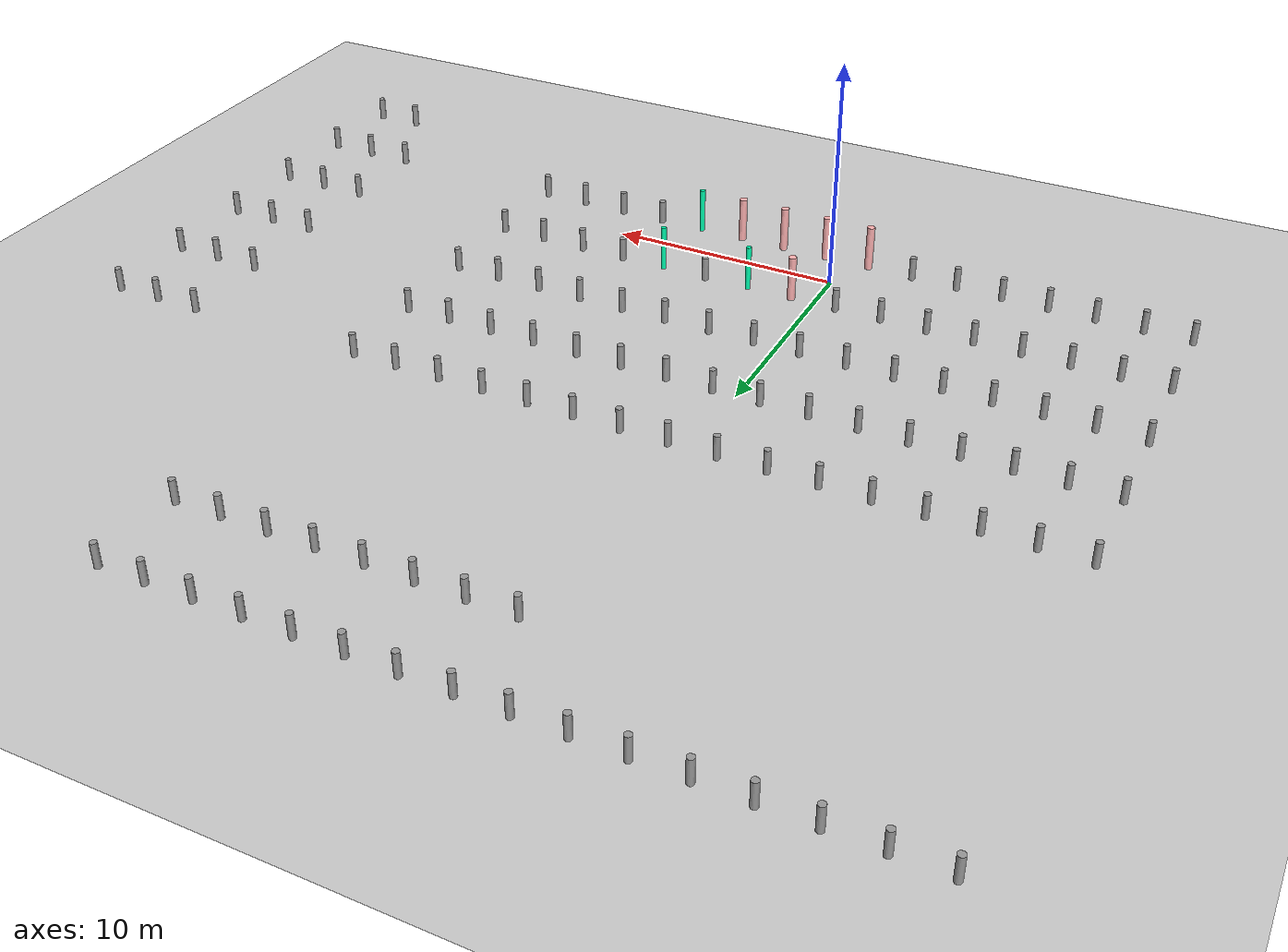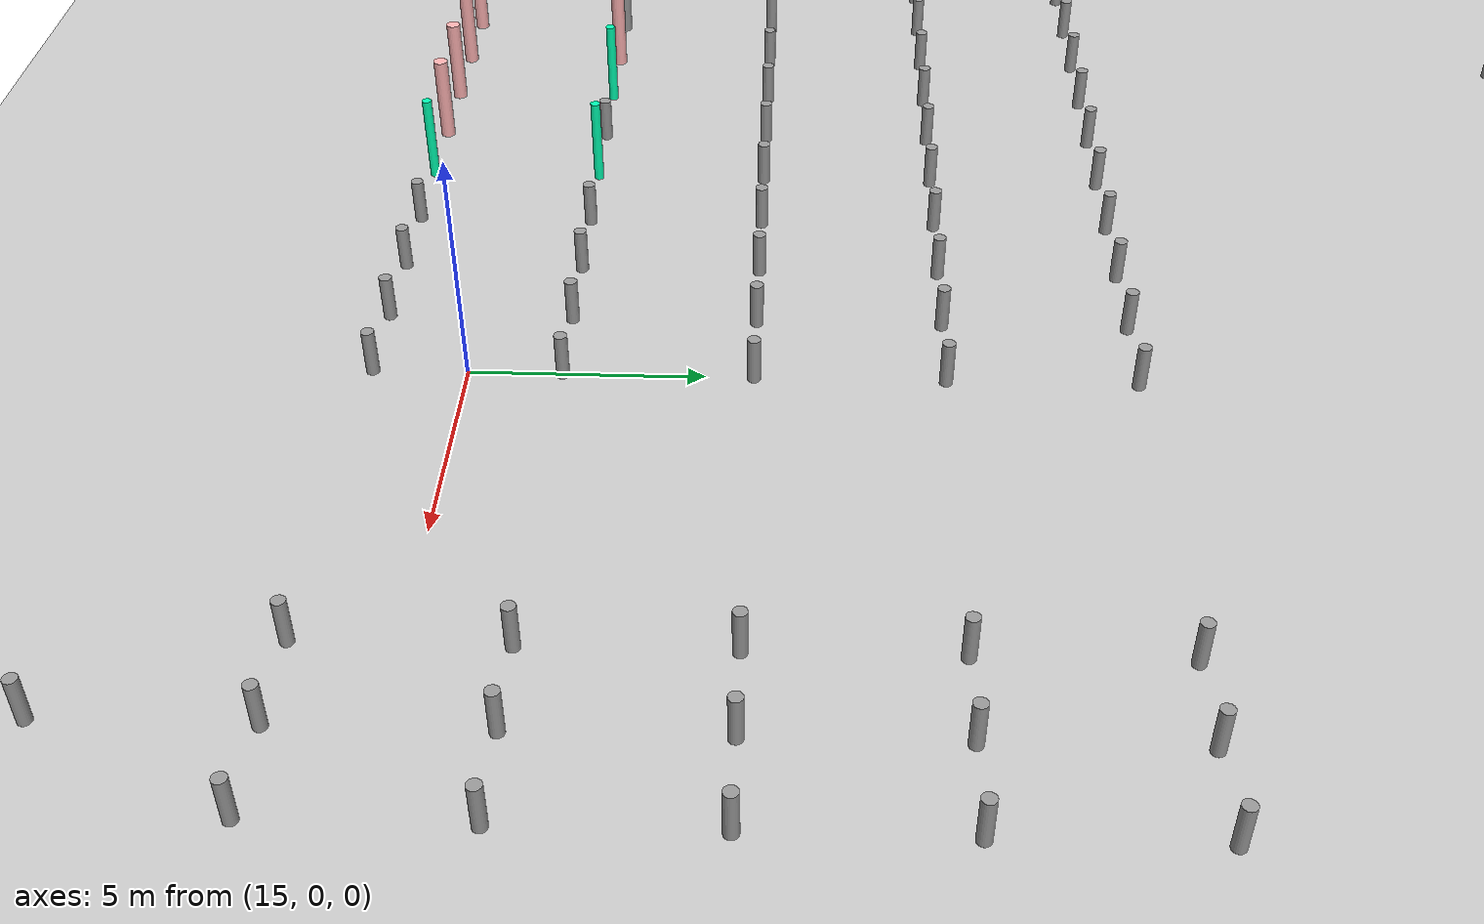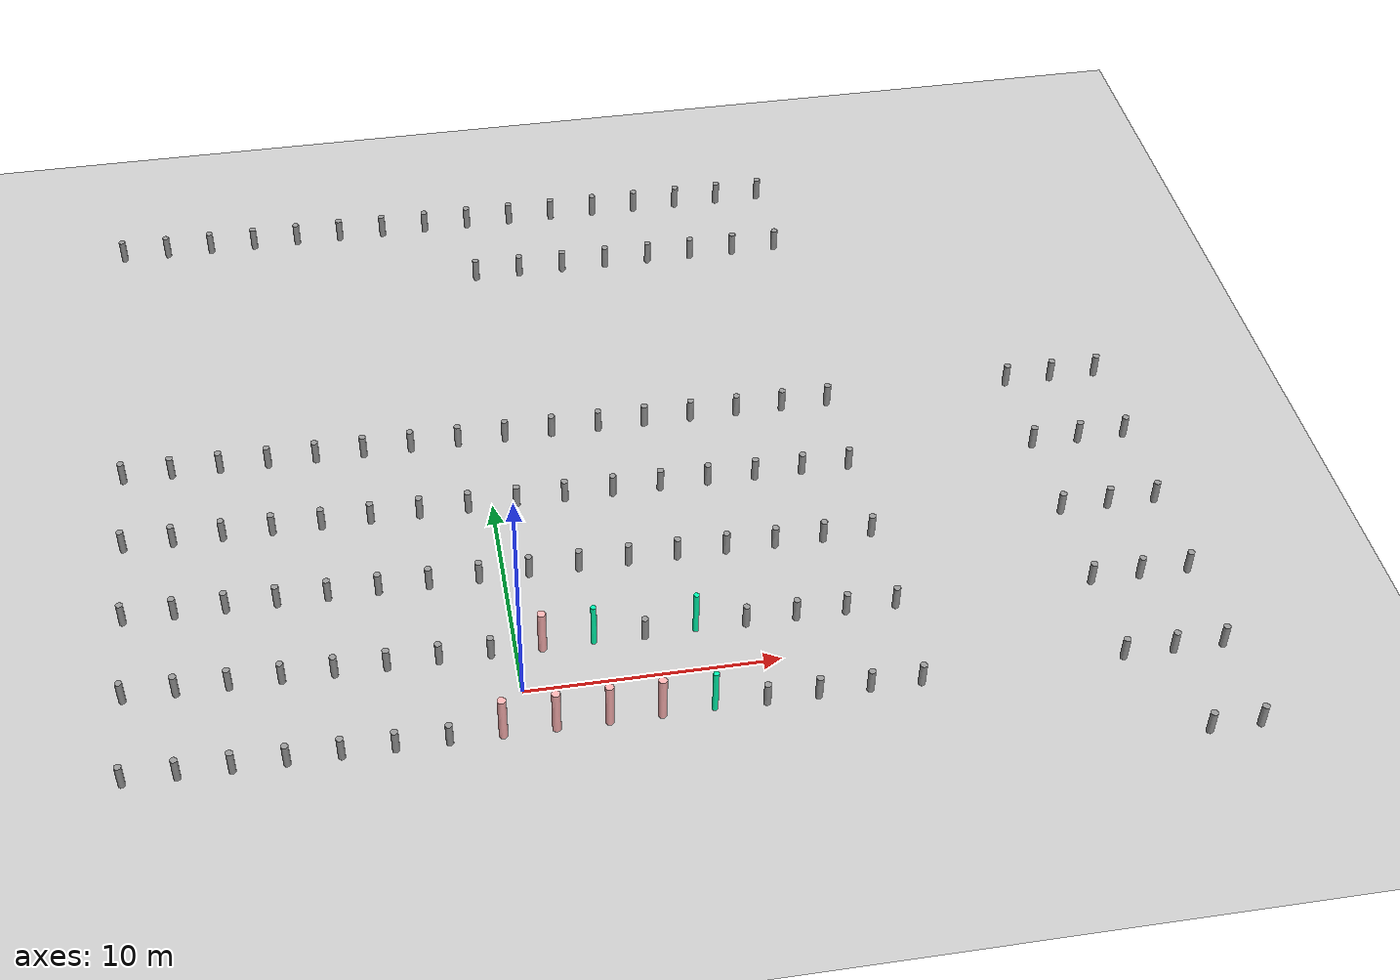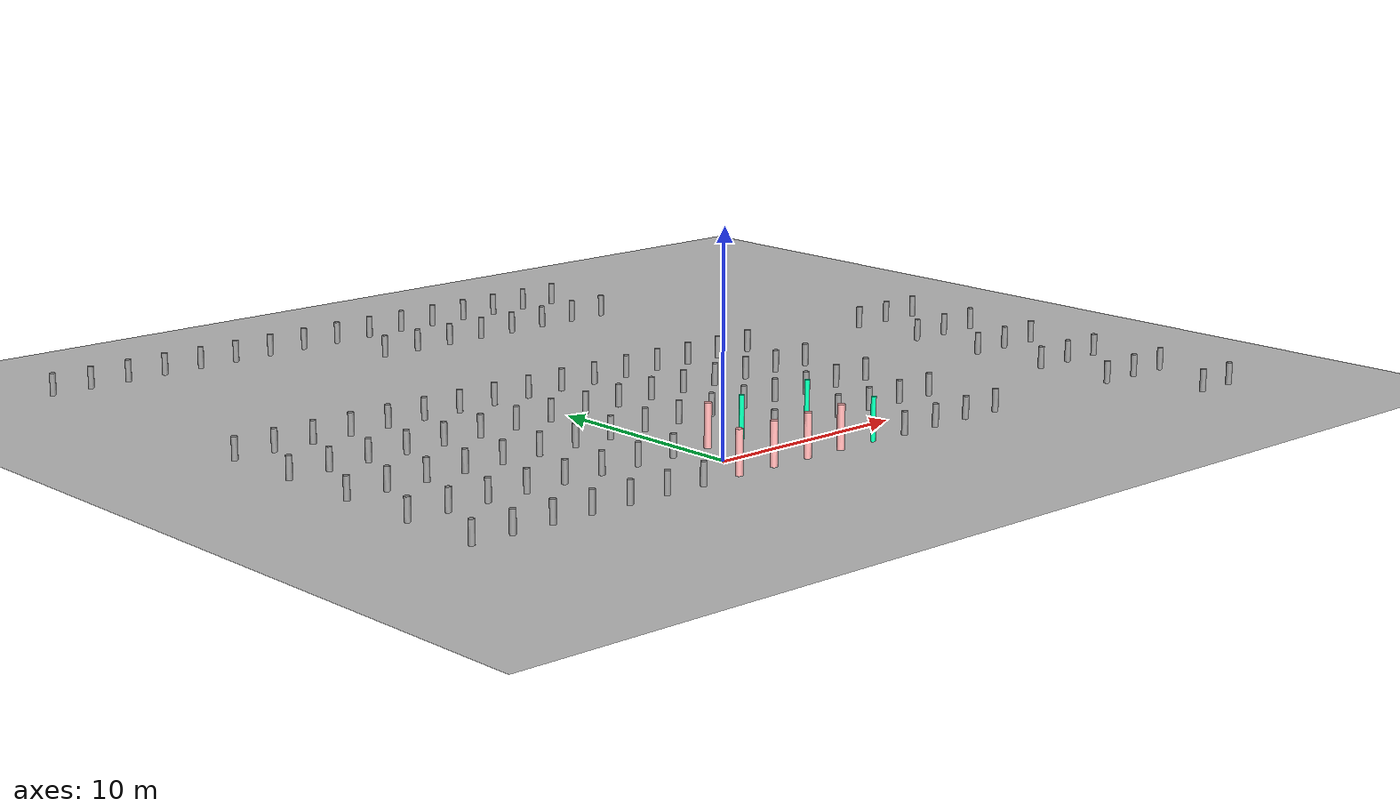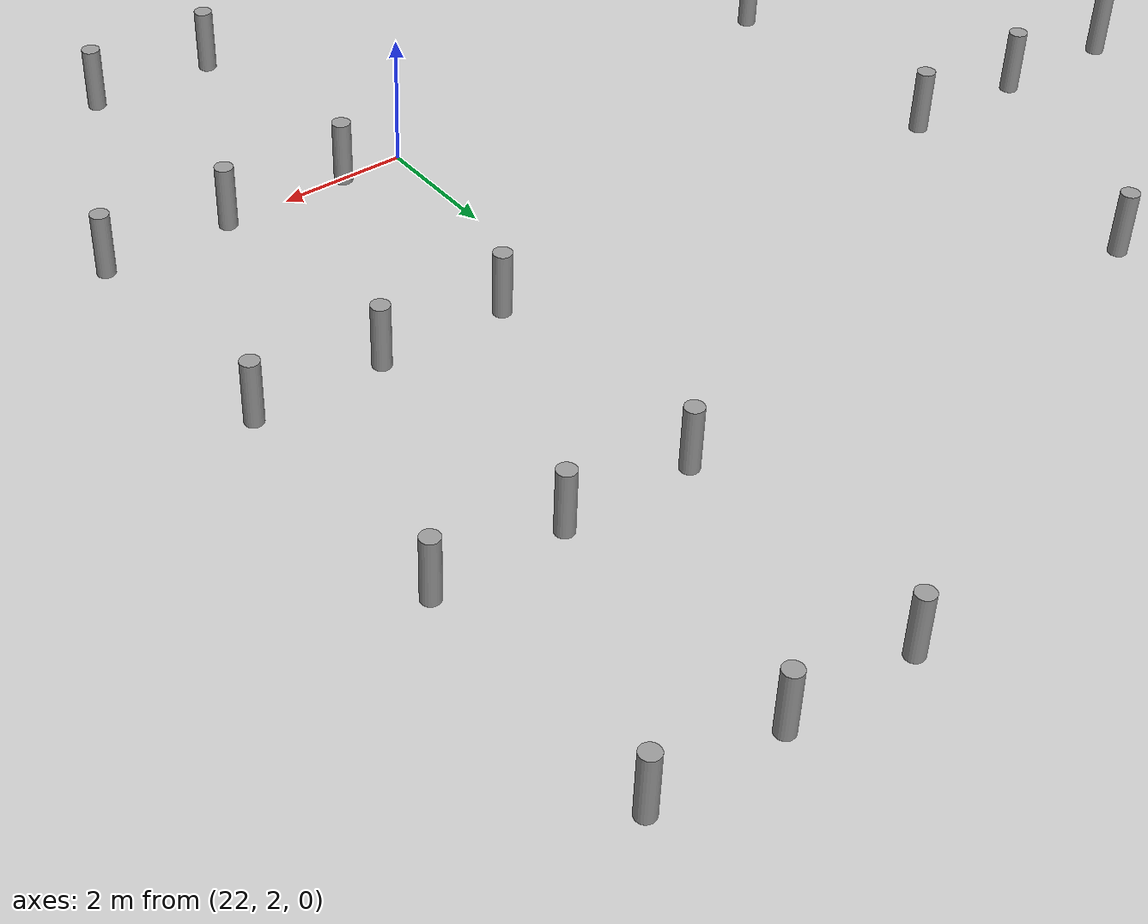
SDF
<sdf version="1.6">
 <world name="default">
  <model name="ground_plane">
   <static>1</static>
   <link name="link">
    <collision name="collision">
     <geometry><plane><normal>0 0 1</normal><size>100 100</size></plane></geometry>
     <surface><friction><ode><mu>100</mu><mu2>50</mu2></ode></friction></surface>
    </collision>
    <visual name="visual">
     <cast_shadows>0</cast_shadows>
     <geometry><plane><normal>0 0 1</normal><size>100 100</size></plane></geometry>
     <material>
      <script><uri>file://media/materials/scripts/gazebo.material</uri><name>Gazebo/Grey</name></script>
     </material>
    </visual>
   </link>
  </model>
  <model name="my_cylinder014_clone_48">
   <pose>-15 -2 0 0 -0 0</pose>
   <link name="my_cylinder014::link">
    <inertial>
     <mass>1</mass>
     <inertia><ixx>0.145833</ixx><ixy>0</ixy><ixz>0</ixz><iyy>0.145833</iyy><iyz>0</iyz><izz>0.125</izz></inertia>
    </inertial>
    <visual name="visual">
     <geometry><cylinder><radius>0.14</radius><length>2</length></cylinder></geometry>
     <material>
      <script><name>Gazebo/Grey</name><uri>file://media/materials/scripts/gazebo.material</uri></script>
      <ambient>0.3 0.3 0.3 1</ambient>
      <diffuse>0.7 0.7 0.7 1</diffuse>
      <specular>1 0.01 0.01 1</specular>
      <emissive>0 0 0 1</emissive>
      <shader type="vertex"><normal_map>__default__</normal_map></shader>
     </material>
    </visual>
    <collision name="collision">
     <geometry><cylinder><radius>0.14</radius><length>2</length></cylinder></geometry>
     <surface>
      <friction>
       <ode><mu>1</mu><mu2>1</mu2><fdir1>0 0 0</fdir1><slip1>0</slip1><slip2>0</slip2></ode>
       <torsional>
        <coefficient>1</coefficient>
        <patch_radius>0</patch_radius>
        <surface_radius>0</surface_radius>
        <use_patch_radius>1</use_patch_radius>
        <ode><slip>0</slip></ode>
       </torsional>
      </friction>
      <bounce><restitution_coefficient>0</restitution_coefficient><threshold>1e+06</threshold></bounce>
      <contact>
       <collide_without_contact>0</collide_without_contact>
       <collide_without_contact_bitmask>1</collide_without_contact_bitmask>
       <collide_bitmask>1</collide_bitmask>
       <ode>
        <soft_cfm>0</soft_cfm>
        <soft_erp>0.2</soft_erp>
        <kp>1e+13</kp>
        <kd>1</kd>
        <max_vel>0.01</max_vel>
        <min_depth>0</min_depth>
       </ode>
       <bullet>
        <split_impulse>1</split_impulse>
        <split_impulse_penetration_threshold>-0.01</split_impulse_penetration_threshold>
        <soft_cfm>0</soft_cfm>
        <soft_erp>0.2</soft_erp>
        <kp>1e+13</kp>
        <kd>1</kd>
       </bullet>
      </contact>
     </surface>
    </collision>
   </link>
   <static>1</static>
  </model>
  <model name="my_cylinder014_clone_49">
   <pose>-13 -2 0 0 -0 0</pose>
   <link name="my_cylinder014::link">
    <inertial>
     <mass>1</mass>
     <inertia><ixx>0.145833</ixx><ixy>0</ixy><ixz>0</ixz><iyy>0.145833</iyy><iyz>0</iyz><izz>0.125</izz></inertia>
    </inertial>
    <visual name="visual">
     <geometry><cylinder><radius>0.14</radius><length>2</length></cylinder></geometry>
     <material>
      <script><name>Gazebo/Grey</name><uri>file://media/materials/scripts/gazebo.material</uri></script>
      <ambient>0.3 0.3 0.3 1</ambient>
      <diffuse>0.7 0.7 0.7 1</diffuse>
      <specular>1 0.01 0.01 1</specular>
      <emissive>0 0 0 1</emissive>
      <shader type="vertex"><normal_map>__default__</normal_map></shader>
     </material>
    </visual>
    <collision name="collision">
     <geometry><cylinder><radius>0.14</radius><length>2</length></cylinder></geometry>
     <surface>
      <friction>
       <ode><mu>1</mu><mu2>1</mu2><fdir1>0 0 0</fdir1><slip1>0</slip1><slip2>0</slip2></ode>
       <torsional>
        <coefficient>1</coefficient>
        <patch_radius>0</patch_radius>
        <surface_radius>0</surface_radius>
        <use_patch_radius>1</use_patch_radius>
        <ode><slip>0</slip></ode>
       </torsional>
      </friction>
      <bounce><restitution_coefficient>0</restitution_coefficient><threshold>1e+06</threshold></bounce>
      <contact>
       <collide_without_contact>0</collide_without_contact>
       <collide_without_contact_bitmask>1</collide_without_contact_bitmask>
       <collide_bitmask>1</collide_bitmask>
       <ode>
        <soft_cfm>0</soft_cfm>
        <soft_erp>0.2</soft_erp>
        <kp>1e+13</kp>
        <kd>1</kd>
        <max_vel>0.01</max_vel>
        <min_depth>0</min_depth>
       </ode>
       <bullet>
        <split_impulse>1</split_impulse>
        <split_impulse_penetration_threshold>-0.01</split_impulse_penetration_threshold>
        <soft_cfm>0</soft_cfm>
        <soft_erp>0.2</soft_erp>
        <kp>1e+13</kp>
        <kd>1</kd>
       </bullet>
      </contact>
     </surface>
    </collision>
   </link>
   <static>1</static>
  </model>
  <model name="my_cylinder014_clone_50">
   <pose>-11 -2 0 0 -0 0</pose>
   <link name="my_cylinder014::link">
    <inertial>
     <mass>1</mass>
     <inertia><ixx>0.145833</ixx><ixy>0</ixy><ixz>0</ixz><iyy>0.145833</iyy><iyz>0</iyz><izz>0.125</izz></inertia>
    </inertial>
    <visual name="visual">
     <geometry><cylinder><radius>0.14</radius><length>2</length></cylinder></geometry>
     <material>
      <script><name>Gazebo/Grey</name><uri>file://media/materials/scripts/gazebo.material</uri></script>
      <ambient>0.3 0.3 0.3 1</ambient>
      <diffuse>0.7 0.7 0.7 1</diffuse>
      <specular>1 0.01 0.01 1</specular>
      <emissive>0 0 0 1</emissive>
      <shader type="vertex"><normal_map>__default__</normal_map></shader>
     </material>
    </visual>
    <collision name="collision">
     <geometry><cylinder><radius>0.14</radius><length>2</length></cylinder></geometry>
     <surface>
      <friction>
       <ode><mu>1</mu><mu2>1</mu2><fdir1>0 0 0</fdir1><slip1>0</slip1><slip2>0</slip2></ode>
       <torsional>
        <coefficient>1</coefficient>
        <patch_radius>0</patch_radius>
        <surface_radius>0</surface_radius>
        <use_patch_radius>1</use_patch_radius>
        <ode><slip>0</slip></ode>
       </torsional>
      </friction>
      <bounce><restitution_coefficient>0</restitution_coefficient><threshold>1e+06</threshold></bounce>
      <contact>
       <collide_without_contact>0</collide_without_contact>
       <collide_without_contact_bitmask>1</collide_without_contact_bitmask>
       <collide_bitmask>1</collide_bitmask>
       <ode>
        <soft_cfm>0</soft_cfm>
        <soft_erp>0.2</soft_erp>
        <kp>1e+13</kp>
        <kd>1</kd>
        <max_vel>0.01</max_vel>
        <min_depth>0</min_depth>
       </ode>
       <bullet>
        <split_impulse>1</split_impulse>
        <split_impulse_penetration_threshold>-0.01</split_impulse_penetration_threshold>
        <soft_cfm>0</soft_cfm>
        <soft_erp>0.2</soft_erp>
        <kp>1e+13</kp>
        <kd>1</kd>
       </bullet>
      </contact>
     </surface>
    </collision>
   </link>
   <static>1</static>
  </model>
  <model name="my_cylinder014_clone_51">
   <pose>-9 -2 0 0 -0 0</pose>
   <link name="my_cylinder014::link">
    <inertial>
     <mass>1</mass>
     <inertia><ixx>0.145833</ixx><ixy>0</ixy><ixz>0</ixz><iyy>0.145833</iyy><iyz>0</iyz><izz>0.125</izz></inertia>
    </inertial>
    <visual name="visual">
     <geometry><cylinder><radius>0.14</radius><length>2</length></cylinder></geometry>
     <material>
      <script><name>Gazebo/Grey</name><uri>file://media/materials/scripts/gazebo.material</uri></script>
      <ambient>0.3 0.3 0.3 1</ambient>
      <diffuse>0.7 0.7 0.7 1</diffuse>
      <specular>1 0.01 0.01 1</specular>
      <emissive>0 0 0 1</emissive>
      <shader type="vertex"><normal_map>__default__</normal_map></shader>
     </material>
    </visual>
    <collision name="collision">
     <geometry><cylinder><radius>0.14</radius><length>2</length></cylinder></geometry>
     <surface>
      <friction>
       <ode><mu>1</mu><mu2>1</mu2><fdir1>0 0 0</fdir1><slip1>0</slip1><slip2>0</slip2></ode>
       <torsional>
        <coefficient>1</coefficient>
        <patch_radius>0</patch_radius>
        <surface_radius>0</surface_radius>
        <use_patch_radius>1</use_patch_radius>
        <ode><slip>0</slip></ode>
       </torsional>
      </friction>
      <bounce><restitution_coefficient>0</restitution_coefficient><threshold>1e+06</threshold></bounce>
      <contact>
       <collide_without_contact>0</collide_without_contact>
       <collide_without_contact_bitmask>1</collide_without_contact_bitmask>
       <collide_bitmask>1</collide_bitmask>
       <ode>
        <soft_cfm>0</soft_cfm>
        <soft_erp>0.2</soft_erp>
        <kp>1e+13</kp>
        <kd>1</kd>
        <max_vel>0.01</max_vel>
        <min_depth>0</min_depth>
       </ode>
       <bullet>
        <split_impulse>1</split_impulse>
        <split_impulse_penetration_threshold>-0.01</split_impulse_penetration_threshold>
        <soft_cfm>0</soft_cfm>
        <soft_erp>0.2</soft_erp>
        <kp>1e+13</kp>
        <kd>1</kd>
       </bullet>
      </contact>
     </surface>
    </collision>
   </link>
   <static>1</static>
  </model>
  <model name="my_cylinder014_clone_52">
   <pose>-7 -2 0 0 -0 0</pose>
   <link name="my_cylinder014::link">
    <inertial>
     <mass>1</mass>
     <inertia><ixx>0.145833</ixx><ixy>0</ixy><ixz>0</ixz><iyy>0.145833</iyy><iyz>0</iyz><izz>0.125</izz></inertia>
    </inertial>
    <visual name="visual">
     <geometry><cylinder><radius>0.14</radius><length>2</length></cylinder></geometry>
     <material>
      <script><name>Gazebo/Grey</name><uri>file://media/materials/scripts/gazebo.material</uri></script>
      <ambient>0.3 0.3 0.3 1</ambient>
      <diffuse>0.7 0.7 0.7 1</diffuse>
      <specular>1 0.01 0.01 1</specular>
      <emissive>0 0 0 1</emissive>
      <shader type="vertex"><normal_map>__default__</normal_map></shader>
     </material>
    </visual>
    <collision name="collision">
     <geometry><cylinder><radius>0.14</radius><length>2</length></cylinder></geometry>
     <surface>
      <friction>
       <ode><mu>1</mu><mu2>1</mu2><fdir1>0 0 0</fdir1><slip1>0</slip1><slip2>0</slip2></ode>
       <torsional>
        <coefficient>1</coefficient>
        <patch_radius>0</patch_radius>
        <surface_radius>0</surface_radius>
        <use_patch_radius>1</use_patch_radius>
        <ode><slip>0</slip></ode>
       </torsional>
      </friction>
      <bounce><restitution_coefficient>0</restitution_coefficient><threshold>1e+06</threshold></bounce>
      <contact>
       <collide_without_contact>0</collide_without_contact>
       <collide_without_contact_bitmask>1</collide_without_contact_bitmask>
       <collide_bitmask>1</collide_bitmask>
       <ode>
        <soft_cfm>0</soft_cfm>
        <soft_erp>0.2</soft_erp>
        <kp>1e+13</kp>
        <kd>1</kd>
        <max_vel>0.01</max_vel>
        <min_depth>0</min_depth>
       </ode>
       <bullet>
        <split_impulse>1</split_impulse>
        <split_impulse_penetration_threshold>-0.01</split_impulse_penetration_threshold>
        <soft_cfm>0</soft_cfm>
        <soft_erp>0.2</soft_erp>
        <kp>1e+13</kp>
        <kd>1</kd>
       </bullet>
      </contact>
     </surface>
    </collision>
   </link>
   <static>1</static>
  </model>
  <model name="my_cylinder014_clone_53">
   <pose>-5 -2 0 0 -0 0</pose>
   <link name="my_cylinder014::link">
    <inertial>
     <mass>1</mass>
     <inertia><ixx>0.145833</ixx><ixy>0</ixy><ixz>0</ixz><iyy>0.145833</iyy><iyz>0</iyz><izz>0.125</izz></inertia>
    </inertial>
    <visual name="visual">
     <geometry><cylinder><radius>0.14</radius><length>2</length></cylinder></geometry>
     <material>
      <script><name>Gazebo/Grey</name><uri>file://media/materials/scripts/gazebo.material</uri></script>
      <ambient>0.3 0.3 0.3 1</ambient>
      <diffuse>0.7 0.7 0.7 1</diffuse>
      <specular>1 0.01 0.01 1</specular>
      <emissive>0 0 0 1</emissive>
      <shader type="vertex"><normal_map>__default__</normal_map></shader>
     </material>
    </visual>
    <collision name="collision">
     <geometry><cylinder><radius>0.14</radius><length>2</length></cylinder></geometry>
     <surface>
      <friction>
       <ode><mu>1</mu><mu2>1</mu2><fdir1>0 0 0</fdir1><slip1>0</slip1><slip2>0</slip2></ode>
       <torsional>
        <coefficient>1</coefficient>
        <patch_radius>0</patch_radius>
        <surface_radius>0</surface_radius>
        <use_patch_radius>1</use_patch_radius>
        <ode><slip>0</slip></ode>
       </torsional>
      </friction>
      <bounce><restitution_coefficient>0</restitution_coefficient><threshold>1e+06</threshold></bounce>
      <contact>
       <collide_without_contact>0</collide_without_contact>
       <collide_without_contact_bitmask>1</collide_without_contact_bitmask>
       <collide_bitmask>1</collide_bitmask>
       <ode>
        <soft_cfm>0</soft_cfm>
        <soft_erp>0.2</soft_erp>
        <kp>1e+13</kp>
        <kd>1</kd>
        <max_vel>0.01</max_vel>
        <min_depth>0</min_depth>
       </ode>
       <bullet>
        <split_impulse>1</split_impulse>
        <split_impulse_penetration_threshold>-0.01</split_impulse_penetration_threshold>
        <soft_cfm>0</soft_cfm>
        <soft_erp>0.2</soft_erp>
        <kp>1e+13</kp>
        <kd>1</kd>
       </bullet>
      </contact>
     </surface>
    </collision>
   </link>
   <static>1</static>
  </model>
  <model name="my_cylinder014_clone_54">
   <pose>-3 -2 0 0 -0 0</pose>
   <link name="my_cylinder014::link">
    <inertial>
     <mass>1</mass>
     <inertia><ixx>0.145833</ixx><ixy>0</ixy><ixz>0</ixz><iyy>0.145833</iyy><iyz>0</iyz><izz>0.125</izz></inertia>
    </inertial>
    <visual name="visual">
     <geometry><cylinder><radius>0.14</radius><length>2</length></cylinder></geometry>
     <material>
      <script><name>Gazebo/Grey</name><uri>file://media/materials/scripts/gazebo.material</uri></script>
      <ambient>0.3 0.3 0.3 1</ambient>
      <diffuse>0.7 0.7 0.7 1</diffuse>
      <specular>1 0.01 0.01 1</specular>
      <emissive>0 0 0 1</emissive>
      <shader type="vertex"><normal_map>__default__</normal_map></shader>
     </material>
    </visual>
    <collision name="collision">
     <geometry><cylinder><radius>0.14</radius><length>2</length></cylinder></geometry>
     <surface>
      <friction>
       <ode><mu>1</mu><mu2>1</mu2><fdir1>0 0 0</fdir1><slip1>0</slip1><slip2>0</slip2></ode>
       <torsional>
        <coefficient>1</coefficient>
        <patch_radius>0</patch_radius>
        <surface_radius>0</surface_radius>
        <use_patch_radius>1</use_patch_radius>
        <ode><slip>0</slip></ode>
       </torsional>
      </friction>
      <bounce><restitution_coefficient>0</restitution_coefficient><threshold>1e+06</threshold></bounce>
      <contact>
       <collide_without_contact>0</collide_without_contact>
       <collide_without_contact_bitmask>1</collide_without_contact_bitmask>
       <collide_bitmask>1</collide_bitmask>
       <ode>
        <soft_cfm>0</soft_cfm>
        <soft_erp>0.2</soft_erp>
        <kp>1e+13</kp>
        <kd>1</kd>
        <max_vel>0.01</max_vel>
        <min_depth>0</min_depth>
       </ode>
       <bullet>
        <split_impulse>1</split_impulse>
        <split_impulse_penetration_threshold>-0.01</split_impulse_penetration_threshold>
        <soft_cfm>0</soft_cfm>
        <soft_erp>0.2</soft_erp>
        <kp>1e+13</kp>
        <kd>1</kd>
       </bullet>
      </contact>
     </surface>
    </collision>
   </link>
   <static>1</static>
  </model>
  <model name="my_cylinder014_clone_60">
   <pose>9 -2 0 0 -0 0</pose>
   <link name="my_cylinder014::link">
    <inertial>
     <mass>1</mass>
     <inertia><ixx>0.145833</ixx><ixy>0</ixy><ixz>0</ixz><iyy>0.145833</iyy><iyz>0</iyz><izz>0.125</izz></inertia>
    </inertial>
    <visual name="visual">
     <geometry><cylinder><radius>0.14</radius><length>2</length></cylinder></geometry>
     <material>
      <script><name>Gazebo/Grey</name><uri>file://media/materials/scripts/gazebo.material</uri></script>
      <ambient>0.3 0.3 0.3 1</ambient>
      <diffuse>0.7 0.7 0.7 1</diffuse>
      <specular>1 0.01 0.01 1</specular>
      <emissive>0 0 0 1</emissive>
      <shader type="vertex"><normal_map>__default__</normal_map></shader>
     </material>
    </visual>
    <collision name="collision">
     <geometry><cylinder><radius>0.14</radius><length>2</length></cylinder></geometry>
     <surface>
      <friction>
       <ode><mu>1</mu><mu2>1</mu2><fdir1>0 0 0</fdir1><slip1>0</slip1><slip2>0</slip2></ode>
       <torsional>
        <coefficient>1</coefficient>
        <patch_radius>0</patch_radius>
        <surface_radius>0</surface_radius>
        <use_patch_radius>1</use_patch_radius>
        <ode><slip>0</slip></ode>
       </torsional>
      </friction>
      <bounce><restitution_coefficient>0</restitution_coefficient><threshold>1e+06</threshold></bounce>
      <contact>
       <collide_without_contact>0</collide_without_contact>
       <collide_without_contact_bitmask>1</collide_without_contact_bitmask>
       <collide_bitmask>1</collide_bitmask>
       <ode>
        <soft_cfm>0</soft_cfm>
        <soft_erp>0.2</soft_erp>
        <kp>1e+13</kp>
        <kd>1</kd>
        <max_vel>0.01</max_vel>
        <min_depth>0</min_depth>
       </ode>
       <bullet>
        <split_impulse>1</split_impulse>
        <split_impulse_penetration_threshold>-0.01</split_impulse_penetration_threshold>
        <soft_cfm>0</soft_cfm>
        <soft_erp>0.2</soft_erp>
        <kp>1e+13</kp>
        <kd>1</kd>
       </bullet>
      </contact>
     </surface>
    </collision>
   </link>
   <static>1</static>
  </model>
  <model name="my_cylinder014_clone_61">
   <pose>11 -2 0 0 -0 0</pose>
   <link name="my_cylinder014::link">
    <inertial>
     <mass>1</mass>
     <inertia><ixx>0.145833</ixx><ixy>0</ixy><ixz>0</ixz><iyy>0.145833</iyy><iyz>0</iyz><izz>0.125</izz></inertia>
    </inertial>
    <visual name="visual">
     <geometry><cylinder><radius>0.14</radius><length>2</length></cylinder></geometry>
     <material>
      <script><name>Gazebo/Grey</name><uri>file://media/materials/scripts/gazebo.material</uri></script>
      <ambient>0.3 0.3 0.3 1</ambient>
      <diffuse>0.7 0.7 0.7 1</diffuse>
      <specular>1 0.01 0.01 1</specular>
      <emissive>0 0 0 1</emissive>
      <shader type="vertex"><normal_map>__default__</normal_map></shader>
     </material>
    </visual>
    <collision name="collision">
     <geometry><cylinder><radius>0.14</radius><length>2</length></cylinder></geometry>
     <surface>
      <friction>
       <ode><mu>1</mu><mu2>1</mu2><fdir1>0 0 0</fdir1><slip1>0</slip1><slip2>0</slip2></ode>
       <torsional>
        <coefficient>1</coefficient>
        <patch_radius>0</patch_radius>
        <surface_radius>0</surface_radius>
        <use_patch_radius>1</use_patch_radius>
        <ode><slip>0</slip></ode>
       </torsional>
      </friction>
      <bounce><restitution_coefficient>0</restitution_coefficient><threshold>1e+06</threshold></bounce>
      <contact>
       <collide_without_contact>0</collide_without_contact>
       <collide_without_contact_bitmask>1</collide_without_contact_bitmask>
       <collide_bitmask>1</collide_bitmask>
       <ode>
        <soft_cfm>0</soft_cfm>
        <soft_erp>0.2</soft_erp>
        <kp>1e+13</kp>
        <kd>1</kd>
        <max_vel>0.01</max_vel>
        <min_depth>0</min_depth>
       </ode>
       <bullet>
        <split_impulse>1</split_impulse>
        <split_impulse_penetration_threshold>-0.01</split_impulse_penetration_threshold>
        <soft_cfm>0</soft_cfm>
        <soft_erp>0.2</soft_erp>
        <kp>1e+13</kp>
        <kd>1</kd>
       </bullet>
      </contact>
     </surface>
    </collision>
   </link>
   <static>1</static>
  </model>
  <model name="my_cylinder014_clone_62">
   <pose>13 -2 0 0 -0 0</pose>
   <link name="my_cylinder014::link">
    <inertial>
     <mass>1</mass>
     <inertia><ixx>0.145833</ixx><ixy>0</ixy><ixz>0</ixz><iyy>0.145833</iyy><iyz>0</iyz><izz>0.125</izz></inertia>
    </inertial>
    <visual name="visual">
     <geometry><cylinder><radius>0.14</radius><length>2</length></cylinder></geometry>
     <material>
      <script><name>Gazebo/Grey</name><uri>file://media/materials/scripts/gazebo.material</uri></script>
      <ambient>0.3 0.3 0.3 1</ambient>
      <diffuse>0.7 0.7 0.7 1</diffuse>
      <specular>1 0.01 0.01 1</specular>
      <emissive>0 0 0 1</emissive>
      <shader type="vertex"><normal_map>__default__</normal_map></shader>
     </material>
    </visual>
    <collision name="collision">
     <geometry><cylinder><radius>0.14</radius><length>2</length></cylinder></geometry>
     <surface>
      <friction>
       <ode><mu>1</mu><mu2>1</mu2><fdir1>0 0 0</fdir1><slip1>0</slip1><slip2>0</slip2></ode>
       <torsional>
        <coefficient>1</coefficient>
        <patch_radius>0</patch_radius>
        <surface_radius>0</surface_radius>
        <use_patch_radius>1</use_patch_radius>
        <ode><slip>0</slip></ode>
       </torsional>
      </friction>
      <bounce><restitution_coefficient>0</restitution_coefficient><threshold>1e+06</threshold></bounce>
      <contact>
       <collide_without_contact>0</collide_without_contact>
       <collide_without_contact_bitmask>1</collide_without_contact_bitmask>
       <collide_bitmask>1</collide_bitmask>
       <ode>
        <soft_cfm>0</soft_cfm>
        <soft_erp>0.2</soft_erp>
        <kp>1e+13</kp>
        <kd>1</kd>
        <max_vel>0.01</max_vel>
        <min_depth>0</min_depth>
       </ode>
       <bullet>
        <split_impulse>1</split_impulse>
        <split_impulse_penetration_threshold>-0.01</split_impulse_penetration_threshold>
        <soft_cfm>0</soft_cfm>
        <soft_erp>0.2</soft_erp>
        <kp>1e+13</kp>
        <kd>1</kd>
       </bullet>
      </contact>
     </surface>
    </collision>
   </link>
   <static>1</static>
  </model>
  <model name="my_cylinder014_clone_63">
   <pose>15 -2 0 0 -0 0</pose>
   <link name="my_cylinder014::link">
    <inertial>
     <mass>1</mass>
     <inertia><ixx>0.145833</ixx><ixy>0</ixy><ixz>0</ixz><iyy>0.145833</iyy><iyz>0</iyz><izz>0.125</izz></inertia>
    </inertial>
    <visual name="visual">
     <geometry><cylinder><radius>0.14</radius><length>2</length></cylinder></geometry>
     <material>
      <script><name>Gazebo/Grey</name><uri>file://media/materials/scripts/gazebo.material</uri></script>
      <ambient>0.3 0.3 0.3 1</ambient>
      <diffuse>0.7 0.7 0.7 1</diffuse>
      <specular>1 0.01 0.01 1</specular>
      <emissive>0 0 0 1</emissive>
      <shader type="vertex"><normal_map>__default__</normal_map></shader>
     </material>
    </visual>
    <collision name="collision">
     <geometry><cylinder><radius>0.14</radius><length>2</length></cylinder></geometry>
     <surface>
      <friction>
       <ode><mu>1</mu><mu2>1</mu2><fdir1>0 0 0</fdir1><slip1>0</slip1><slip2>0</slip2></ode>
       <torsional>
        <coefficient>1</coefficient>
        <patch_radius>0</patch_radius>
        <surface_radius>0</surface_radius>
        <use_patch_radius>1</use_patch_radius>
        <ode><slip>0</slip></ode>
       </torsional>
      </friction>
      <bounce><restitution_coefficient>0</restitution_coefficient><threshold>1e+06</threshold></bounce>
      <contact>
       <collide_without_contact>0</collide_without_contact>
       <collide_without_contact_bitmask>1</collide_without_contact_bitmask>
       <collide_bitmask>1</collide_bitmask>
       <ode>
        <soft_cfm>0</soft_cfm>
        <soft_erp>0.2</soft_erp>
        <kp>1e+13</kp>
        <kd>1</kd>
        <max_vel>0.01</max_vel>
        <min_depth>0</min_depth>
       </ode>
       <bullet>
        <split_impulse>1</split_impulse>
        <split_impulse_penetration_threshold>-0.01</split_impulse_penetration_threshold>
        <soft_cfm>0</soft_cfm>
        <soft_erp>0.2</soft_erp>
        <kp>1e+13</kp>
        <kd>1</kd>
       </bullet>
      </contact>
     </surface>
    </collision>
   </link>
   <static>1</static>
  </model>
  <model name="my_cylinder014_clone_64">
   <pose>-15 2 0 0 -0 0</pose>
   <link name="my_cylinder014::link">
    <inertial>
     <mass>1</mass>
     <inertia><ixx>0.145833</ixx><ixy>0</ixy><ixz>0</ixz><iyy>0.145833</iyy><iyz>0</iyz><izz>0.125</izz></inertia>
    </inertial>
    <visual name="visual">
     <geometry><cylinder><radius>0.14</radius><length>2</length></cylinder></geometry>
     <material>
      <script><name>Gazebo/Grey</name><uri>file://media/materials/scripts/gazebo.material</uri></script>
      <ambient>0.3 0.3 0.3 1</ambient>
      <diffuse>0.7 0.7 0.7 1</diffuse>
      <specular>1 0.01 0.01 1</specular>
      <emissive>0 0 0 1</emissive>
      <shader type="vertex"><normal_map>__default__</normal_map></shader>
     </material>
    </visual>
    <collision name="collision">
     <geometry><cylinder><radius>0.14</radius><length>2</length></cylinder></geometry>
     <surface>
      <friction>
       <ode><mu>1</mu><mu2>1</mu2><fdir1>0 0 0</fdir1><slip1>0</slip1><slip2>0</slip2></ode>
       <torsional>
        <coefficient>1</coefficient>
        <patch_radius>0</patch_radius>
        <surface_radius>0</surface_radius>
        <use_patch_radius>1</use_patch_radius>
        <ode><slip>0</slip></ode>
       </torsional>
      </friction>
      <bounce><restitution_coefficient>0</restitution_coefficient><threshold>1e+06</threshold></bounce>
      <contact>
       <collide_without_contact>0</collide_without_contact>
       <collide_without_contact_bitmask>1</collide_without_contact_bitmask>
       <collide_bitmask>1</collide_bitmask>
       <ode>
        <soft_cfm>0</soft_cfm>
        <soft_erp>0.2</soft_erp>
        <kp>1e+13</kp>
        <kd>1</kd>
        <max_vel>0.01</max_vel>
        <min_depth>0</min_depth>
       </ode>
       <bullet>
        <split_impulse>1</split_impulse>
        <split_impulse_penetration_threshold>-0.01</split_impulse_penetration_threshold>
        <soft_cfm>0</soft_cfm>
        <soft_erp>0.2</soft_erp>
        <kp>1e+13</kp>
        <kd>1</kd>
       </bullet>
      </contact>
     </surface>
    </collision>
   </link>
   <static>1</static>
  </model>
  <model name="my_cylinder014_clone_65">
   <pose>-13 2 0 0 -0 0</pose>
   <link name="my_cylinder014::link">
    <inertial>
     <mass>1</mass>
     <inertia><ixx>0.145833</ixx><ixy>0</ixy><ixz>0</ixz><iyy>0.145833</iyy><iyz>0</iyz><izz>0.125</izz></inertia>
    </inertial>
    <visual name="visual">
     <geometry><cylinder><radius>0.14</radius><length>2</length></cylinder></geometry>
     <material>
      <script><name>Gazebo/Grey</name><uri>file://media/materials/scripts/gazebo.material</uri></script>
      <ambient>0.3 0.3 0.3 1</ambient>
      <diffuse>0.7 0.7 0.7 1</diffuse>
      <specular>1 0.01 0.01 1</specular>
      <emissive>0 0 0 1</emissive>
      <shader type="vertex"><normal_map>__default__</normal_map></shader>
     </material>
    </visual>
    <collision name="collision">
     <geometry><cylinder><radius>0.14</radius><length>2</length></cylinder></geometry>
     <surface>
      <friction>
       <ode><mu>1</mu><mu2>1</mu2><fdir1>0 0 0</fdir1><slip1>0</slip1><slip2>0</slip2></ode>
       <torsional>
        <coefficient>1</coefficient>
        <patch_radius>0</patch_radius>
        <surface_radius>0</surface_radius>
        <use_patch_radius>1</use_patch_radius>
        <ode><slip>0</slip></ode>
       </torsional>
      </friction>
      <bounce><restitution_coefficient>0</restitution_coefficient><threshold>1e+06</threshold></bounce>
      <contact>
       <collide_without_contact>0</collide_without_contact>
       <collide_without_contact_bitmask>1</collide_without_contact_bitmask>
       <collide_bitmask>1</collide_bitmask>
       <ode>
        <soft_cfm>0</soft_cfm>
        <soft_erp>0.2</soft_erp>
        <kp>1e+13</kp>
        <kd>1</kd>
        <max_vel>0.01</max_vel>
        <min_depth>0</min_depth>
       </ode>
       <bullet>
        <split_impulse>1</split_impulse>
        <split_impulse_penetration_threshold>-0.01</split_impulse_penetration_threshold>
        <soft_cfm>0</soft_cfm>
        <soft_erp>0.2</soft_erp>
        <kp>1e+13</kp>
        <kd>1</kd>
       </bullet>
      </contact>
     </surface>
    </collision>
   </link>
   <static>1</static>
  </model>
  <model name="my_cylinder014_clone_66">
   <pose>-11 2 0 0 -0 0</pose>
   <link name="my_cylinder014::link">
    <inertial>
     <mass>1</mass>
     <inertia><ixx>0.145833</ixx><ixy>0</ixy><ixz>0</ixz><iyy>0.145833</iyy><iyz>0</iyz><izz>0.125</izz></inertia>
    </inertial>
    <visual name="visual">
     <geometry><cylinder><radius>0.14</radius><length>2</length></cylinder></geometry>
     <material>
      <script><name>Gazebo/Grey</name><uri>file://media/materials/scripts/gazebo.material</uri></script>
      <ambient>0.3 0.3 0.3 1</ambient>
      <diffuse>0.7 0.7 0.7 1</diffuse>
      <specular>1 0.01 0.01 1</specular>
      <emissive>0 0 0 1</emissive>
      <shader type="vertex"><normal_map>__default__</normal_map></shader>
     </material>
    </visual>
    <collision name="collision">
     <geometry><cylinder><radius>0.14</radius><length>2</length></cylinder></geometry>
     <surface>
      <friction>
       <ode><mu>1</mu><mu2>1</mu2><fdir1>0 0 0</fdir1><slip1>0</slip1><slip2>0</slip2></ode>
       <torsional>
        <coefficient>1</coefficient>
        <patch_radius>0</patch_radius>
        <surface_radius>0</surface_radius>
        <use_patch_radius>1</use_patch_radius>
        <ode><slip>0</slip></ode>
       </torsional>
      </friction>
      <bounce><restitution_coefficient>0</restitution_coefficient><threshold>1e+06</threshold></bounce>
      <contact>
       <collide_without_contact>0</collide_without_contact>
       <collide_without_contact_bitmask>1</collide_without_contact_bitmask>
       <collide_bitmask>1</collide_bitmask>
       <ode>
        <soft_cfm>0</soft_cfm>
        <soft_erp>0.2</soft_erp>
        <kp>1e+13</kp>
        <kd>1</kd>
        <max_vel>0.01</max_vel>
        <min_depth>0</min_depth>
       </ode>
       <bullet>
        <split_impulse>1</split_impulse>
        <split_impulse_penetration_threshold>-0.01</split_impulse_penetration_threshold>
        <soft_cfm>0</soft_cfm>
        <soft_erp>0.2</soft_erp>
        <kp>1e+13</kp>
        <kd>1</kd>
       </bullet>
      </contact>
     </surface>
    </collision>
   </link>
   <static>1</static>
  </model>
  <model name="my_cylinder014_clone_67">
   <pose>-9 2 0 0 -0 0</pose>
   <link name="my_cylinder014::link">
    <inertial>
     <mass>1</mass>
     <inertia><ixx>0.145833</ixx><ixy>0</ixy><ixz>0</ixz><iyy>0.145833</iyy><iyz>0</iyz><izz>0.125</izz></inertia>
    </inertial>
    <visual name="visual">
     <geometry><cylinder><radius>0.14</radius><length>2</length></cylinder></geometry>
     <material>
      <script><name>Gazebo/Grey</name><uri>file://media/materials/scripts/gazebo.material</uri></script>
      <ambient>0.3 0.3 0.3 1</ambient>
      <diffuse>0.7 0.7 0.7 1</diffuse>
      <specular>1 0.01 0.01 1</specular>
      <emissive>0 0 0 1</emissive>
      <shader type="vertex"><normal_map>__default__</normal_map></shader>
     </material>
    </visual>
    <collision name="collision">
     <geometry><cylinder><radius>0.14</radius><length>2</length></cylinder></geometry>
     <surface>
      <friction>
       <ode><mu>1</mu><mu2>1</mu2><fdir1>0 0 0</fdir1><slip1>0</slip1><slip2>0</slip2></ode>
       <torsional>
        <coefficient>1</coefficient>
        <patch_radius>0</patch_radius>
        <surface_radius>0</surface_radius>
        <use_patch_radius>1</use_patch_radius>
        <ode><slip>0</slip></ode>
       </torsional>
      </friction>
      <bounce><restitution_coefficient>0</restitution_coefficient><threshold>1e+06</threshold></bounce>
      <contact>
       <collide_without_contact>0</collide_without_contact>
       <collide_without_contact_bitmask>1</collide_without_contact_bitmask>
       <collide_bitmask>1</collide_bitmask>
       <ode>
        <soft_cfm>0</soft_cfm>
        <soft_erp>0.2</soft_erp>
        <kp>1e+13</kp>
        <kd>1</kd>
        <max_vel>0.01</max_vel>
        <min_depth>0</min_depth>
       </ode>
       <bullet>
        <split_impulse>1</split_impulse>
        <split_impulse_penetration_threshold>-0.01</split_impulse_penetration_threshold>
        <soft_cfm>0</soft_cfm>
        <soft_erp>0.2</soft_erp>
        <kp>1e+13</kp>
        <kd>1</kd>
       </bullet>
      </contact>
     </surface>
    </collision>
   </link>
   <static>1</static>
  </model>
  <model name="my_cylinder014_clone_68">
   <pose>-7 2 0 0 -0 0</pose>
   <link name="my_cylinder014::link">
    <inertial>
     <mass>1</mass>
     <inertia><ixx>0.145833</ixx><ixy>0</ixy><ixz>0</ixz><iyy>0.145833</iyy><iyz>0</iyz><izz>0.125</izz></inertia>
    </inertial>
    <visual name="visual">
     <geometry><cylinder><radius>0.14</radius><length>2</length></cylinder></geometry>
     <material>
      <script><name>Gazebo/Grey</name><uri>file://media/materials/scripts/gazebo.material</uri></script>
      <ambient>0.3 0.3 0.3 1</ambient>
      <diffuse>0.7 0.7 0.7 1</diffuse>
      <specular>1 0.01 0.01 1</specular>
      <emissive>0 0 0 1</emissive>
      <shader type="vertex"><normal_map>__default__</normal_map></shader>
     </material>
    </visual>
    <collision name="collision">
     <geometry><cylinder><radius>0.14</radius><length>2</length></cylinder></geometry>
     <surface>
      <friction>
       <ode><mu>1</mu><mu2>1</mu2><fdir1>0 0 0</fdir1><slip1>0</slip1><slip2>0</slip2></ode>
       <torsional>
        <coefficient>1</coefficient>
        <patch_radius>0</patch_radius>
        <surface_radius>0</surface_radius>
        <use_patch_radius>1</use_patch_radius>
        <ode><slip>0</slip></ode>
       </torsional>
      </friction>
      <bounce><restitution_coefficient>0</restitution_coefficient><threshold>1e+06</threshold></bounce>
      <contact>
       <collide_without_contact>0</collide_without_contact>
       <collide_without_contact_bitmask>1</collide_without_contact_bitmask>
       <collide_bitmask>1</collide_bitmask>
       <ode>
        <soft_cfm>0</soft_cfm>
        <soft_erp>0.2</soft_erp>
        <kp>1e+13</kp>
        <kd>1</kd>
        <max_vel>0.01</max_vel>
        <min_depth>0</min_depth>
       </ode>
       <bullet>
        <split_impulse>1</split_impulse>
        <split_impulse_penetration_threshold>-0.01</split_impulse_penetration_threshold>
        <soft_cfm>0</soft_cfm>
        <soft_erp>0.2</soft_erp>
        <kp>1e+13</kp>
        <kd>1</kd>
       </bullet>
      </contact>
     </surface>
    </collision>
   </link>
   <static>1</static>
  </model>
  <model name="my_cylinder014_clone_69">
   <pose>-5 2 0 0 -0 0</pose>
   <link name="my_cylinder014::link">
    <inertial>
     <mass>1</mass>
     <inertia><ixx>0.145833</ixx><ixy>0</ixy><ixz>0</ixz><iyy>0.145833</iyy><iyz>0</iyz><izz>0.125</izz></inertia>
    </inertial>
    <visual name="visual">
     <geometry><cylinder><radius>0.14</radius><length>2</length></cylinder></geometry>
     <material>
      <script><name>Gazebo/Grey</name><uri>file://media/materials/scripts/gazebo.material</uri></script>
      <ambient>0.3 0.3 0.3 1</ambient>
      <diffuse>0.7 0.7 0.7 1</diffuse>
      <specular>1 0.01 0.01 1</specular>
      <emissive>0 0 0 1</emissive>
      <shader type="vertex"><normal_map>__default__</normal_map></shader>
     </material>
    </visual>
    <collision name="collision">
     <geometry><cylinder><radius>0.14</radius><length>2</length></cylinder></geometry>
     <surface>
      <friction>
       <ode><mu>1</mu><mu2>1</mu2><fdir1>0 0 0</fdir1><slip1>0</slip1><slip2>0</slip2></ode>
       <torsional>
        <coefficient>1</coefficient>
        <patch_radius>0</patch_radius>
        <surface_radius>0</surface_radius>
        <use_patch_radius>1</use_patch_radius>
        <ode><slip>0</slip></ode>
       </torsional>
      </friction>
      <bounce><restitution_coefficient>0</restitution_coefficient><threshold>1e+06</threshold></bounce>
      <contact>
       <collide_without_contact>0</collide_without_contact>
       <collide_without_contact_bitmask>1</collide_without_contact_bitmask>
       <collide_bitmask>1</collide_bitmask>
       <ode>
        <soft_cfm>0</soft_cfm>
        <soft_erp>0.2</soft_erp>
        <kp>1e+13</kp>
        <kd>1</kd>
        <max_vel>0.01</max_vel>
        <min_depth>0</min_depth>
       </ode>
       <bullet>
        <split_impulse>1</split_impulse>
        <split_impulse_penetration_threshold>-0.01</split_impulse_penetration_threshold>
        <soft_cfm>0</soft_cfm>
        <soft_erp>0.2</soft_erp>
        <kp>1e+13</kp>
        <kd>1</kd>
       </bullet>
      </contact>
     </surface>
    </collision>
   </link>
   <static>1</static>
  </model>
  <model name="my_cylinder014_clone_70">
   <pose>-3 2 0 0 -0 0</pose>
   <link name="my_cylinder014::link">
    <inertial>
     <mass>1</mass>
     <inertia><ixx>0.145833</ixx><ixy>0</ixy><ixz>0</ixz><iyy>0.145833</iyy><iyz>0</iyz><izz>0.125</izz></inertia>
    </inertial>
    <visual name="visual">
     <geometry><cylinder><radius>0.14</radius><length>2</length></cylinder></geometry>
     <material>
      <script><name>Gazebo/Grey</name><uri>file://media/materials/scripts/gazebo.material</uri></script>
      <ambient>0.3 0.3 0.3 1</ambient>
      <diffuse>0.7 0.7 0.7 1</diffuse>
      <specular>1 0.01 0.01 1</specular>
      <emissive>0 0 0 1</emissive>
      <shader type="vertex"><normal_map>__default__</normal_map></shader>
     </material>
    </visual>
    <collision name="collision">
     <geometry><cylinder><radius>0.14</radius><length>2</length></cylinder></geometry>
     <surface>
      <friction>
       <ode><mu>1</mu><mu2>1</mu2><fdir1>0 0 0</fdir1><slip1>0</slip1><slip2>0</slip2></ode>
       <torsional>
        <coefficient>1</coefficient>
        <patch_radius>0</patch_radius>
        <surface_radius>0</surface_radius>
        <use_patch_radius>1</use_patch_radius>
        <ode><slip>0</slip></ode>
       </torsional>
      </friction>
      <bounce><restitution_coefficient>0</restitution_coefficient><threshold>1e+06</threshold></bounce>
      <contact>
       <collide_without_contact>0</collide_without_contact>
       <collide_without_contact_bitmask>1</collide_without_contact_bitmask>
       <collide_bitmask>1</collide_bitmask>
       <ode>
        <soft_cfm>0</soft_cfm>
        <soft_erp>0.2</soft_erp>
        <kp>1e+13</kp>
        <kd>1</kd>
        <max_vel>0.01</max_vel>
        <min_depth>0</min_depth>
       </ode>
       <bullet>
        <split_impulse>1</split_impulse>
        <split_impulse_penetration_threshold>-0.01</split_impulse_penetration_threshold>
        <soft_cfm>0</soft_cfm>
        <soft_erp>0.2</soft_erp>
        <kp>1e+13</kp>
        <kd>1</kd>
       </bullet>
      </contact>
     </surface>
    </collision>
   </link>
   <static>1</static>
  </model>
  <model name="my_cylinder014_clone_71">
   <pose>-1 2 0 0 -0 0</pose>
   <link name="my_cylinder014::link">
    <inertial>
     <mass>1</mass>
     <inertia><ixx>0.145833</ixx><ixy>0</ixy><ixz>0</ixz><iyy>0.145833</iyy><iyz>0</iyz><izz>0.125</izz></inertia>
    </inertial>
    <visual name="visual">
     <geometry><cylinder><radius>0.14</radius><length>2</length></cylinder></geometry>
     <material>
      <script><name>Gazebo/Grey</name><uri>file://media/materials/scripts/gazebo.material</uri></script>
      <ambient>0.3 0.3 0.3 1</ambient>
      <diffuse>0.7 0.7 0.7 1</diffuse>
      <specular>1 0.01 0.01 1</specular>
      <emissive>0 0 0 1</emissive>
      <shader type="vertex"><normal_map>__default__</normal_map></shader>
     </material>
    </visual>
    <collision name="collision">
     <geometry><cylinder><radius>0.14</radius><length>2</length></cylinder></geometry>
     <surface>
      <friction>
       <ode><mu>1</mu><mu2>1</mu2><fdir1>0 0 0</fdir1><slip1>0</slip1><slip2>0</slip2></ode>
       <torsional>
        <coefficient>1</coefficient>
        <patch_radius>0</patch_radius>
        <surface_radius>0</surface_radius>
        <use_patch_radius>1</use_patch_radius>
        <ode><slip>0</slip></ode>
       </torsional>
      </friction>
      <bounce><restitution_coefficient>0</restitution_coefficient><threshold>1e+06</threshold></bounce>
      <contact>
       <collide_without_contact>0</collide_without_contact>
       <collide_without_contact_bitmask>1</collide_without_contact_bitmask>
       <collide_bitmask>1</collide_bitmask>
       <ode>
        <soft_cfm>0</soft_cfm>
        <soft_erp>0.2</soft_erp>
        <kp>1e+13</kp>
        <kd>1</kd>
        <max_vel>0.01</max_vel>
        <min_depth>0</min_depth>
       </ode>
       <bullet>
        <split_impulse>1</split_impulse>
        <split_impulse_penetration_threshold>-0.01</split_impulse_penetration_threshold>
        <soft_cfm>0</soft_cfm>
        <soft_erp>0.2</soft_erp>
        <kp>1e+13</kp>
        <kd>1</kd>
       </bullet>
      </contact>
     </surface>
    </collision>
   </link>
   <static>1</static>
  </model>
  <model name="my_cylinder014_clone_74">
   <pose>5 2 0 0 -0 0</pose>
   <link name="my_cylinder014::link">
    <inertial>
     <mass>1</mass>
     <inertia><ixx>0.145833</ixx><ixy>0</ixy><ixz>0</ixz><iyy>0.145833</iyy><iyz>0</iyz><izz>0.125</izz></inertia>
    </inertial>
    <visual name="visual">
     <geometry><cylinder><radius>0.14</radius><length>2</length></cylinder></geometry>
     <material>
      <script><name>Gazebo/Grey</name><uri>file://media/materials/scripts/gazebo.material</uri></script>
      <ambient>0.3 0.3 0.3 1</ambient>
      <diffuse>0.7 0.7 0.7 1</diffuse>
      <specular>1 0.01 0.01 1</specular>
      <emissive>0 0 0 1</emissive>
      <shader type="vertex"><normal_map>__default__</normal_map></shader>
     </material>
    </visual>
    <collision name="collision">
     <geometry><cylinder><radius>0.14</radius><length>2</length></cylinder></geometry>
     <surface>
      <friction>
       <ode><mu>1</mu><mu2>1</mu2><fdir1>0 0 0</fdir1><slip1>0</slip1><slip2>0</slip2></ode>
       <torsional>
        <coefficient>1</coefficient>
        <patch_radius>0</patch_radius>
        <surface_radius>0</surface_radius>
        <use_patch_radius>1</use_patch_radius>
        <ode><slip>0</slip></ode>
       </torsional>
      </friction>
      <bounce><restitution_coefficient>0</restitution_coefficient><threshold>1e+06</threshold></bounce>
      <contact>
       <collide_without_contact>0</collide_without_contact>
       <collide_without_contact_bitmask>1</collide_without_contact_bitmask>
       <collide_bitmask>1</collide_bitmask>
       <ode>
        <soft_cfm>0</soft_cfm>
        <soft_erp>0.2</soft_erp>
        <kp>1e+13</kp>
        <kd>1</kd>
        <max_vel>0.01</max_vel>
        <min_depth>0</min_depth>
       </ode>
       <bullet>
        <split_impulse>1</split_impulse>
        <split_impulse_penetration_threshold>-0.01</split_impulse_penetration_threshold>
        <soft_cfm>0</soft_cfm>
        <soft_erp>0.2</soft_erp>
        <kp>1e+13</kp>
        <kd>1</kd>
       </bullet>
      </contact>
     </surface>
    </collision>
   </link>
   <static>1</static>
  </model>
  <model name="my_cylinder014_clone_76">
   <pose>9 2 0 0 -0 0</pose>
   <link name="my_cylinder014::link">
    <inertial>
     <mass>1</mass>
     <inertia><ixx>0.145833</ixx><ixy>0</ixy><ixz>0</ixz><iyy>0.145833</iyy><iyz>0</iyz><izz>0.125</izz></inertia>
    </inertial>
    <visual name="visual">
     <geometry><cylinder><radius>0.14</radius><length>2</length></cylinder></geometry>
     <material>
      <script><name>Gazebo/Grey</name><uri>file://media/materials/scripts/gazebo.material</uri></script>
      <ambient>0.3 0.3 0.3 1</ambient>
      <diffuse>0.7 0.7 0.7 1</diffuse>
      <specular>1 0.01 0.01 1</specular>
      <emissive>0 0 0 1</emissive>
      <shader type="vertex"><normal_map>__default__</normal_map></shader>
     </material>
    </visual>
    <collision name="collision">
     <geometry><cylinder><radius>0.14</radius><length>2</length></cylinder></geometry>
     <surface>
      <friction>
       <ode><mu>1</mu><mu2>1</mu2><fdir1>0 0 0</fdir1><slip1>0</slip1><slip2>0</slip2></ode>
       <torsional>
        <coefficient>1</coefficient>
        <patch_radius>0</patch_radius>
        <surface_radius>0</surface_radius>
        <use_patch_radius>1</use_patch_radius>
        <ode><slip>0</slip></ode>
       </torsional>
      </friction>
      <bounce><restitution_coefficient>0</restitution_coefficient><threshold>1e+06</threshold></bounce>
      <contact>
       <collide_without_contact>0</collide_without_contact>
       <collide_without_contact_bitmask>1</collide_without_contact_bitmask>
       <collide_bitmask>1</collide_bitmask>
       <ode>
        <soft_cfm>0</soft_cfm>
        <soft_erp>0.2</soft_erp>
        <kp>1e+13</kp>
        <kd>1</kd>
        <max_vel>0.01</max_vel>
        <min_depth>0</min_depth>
       </ode>
       <bullet>
        <split_impulse>1</split_impulse>
        <split_impulse_penetration_threshold>-0.01</split_impulse_penetration_threshold>
        <soft_cfm>0</soft_cfm>
        <soft_erp>0.2</soft_erp>
        <kp>1e+13</kp>
        <kd>1</kd>
       </bullet>
      </contact>
     </surface>
    </collision>
   </link>
   <static>1</static>
  </model>
  <model name="my_cylinder014_clone_77">
   <pose>11 2 0 0 -0 0</pose>
   <link name="my_cylinder014::link">
    <inertial>
     <mass>1</mass>
     <inertia><ixx>0.145833</ixx><ixy>0</ixy><ixz>0</ixz><iyy>0.145833</iyy><iyz>0</iyz><izz>0.125</izz></inertia>
    </inertial>
    <visual name="visual">
     <geometry><cylinder><radius>0.14</radius><length>2</length></cylinder></geometry>
     <material>
      <script><name>Gazebo/Grey</name><uri>file://media/materials/scripts/gazebo.material</uri></script>
      <ambient>0.3 0.3 0.3 1</ambient>
      <diffuse>0.7 0.7 0.7 1</diffuse>
      <specular>1 0.01 0.01 1</specular>
      <emissive>0 0 0 1</emissive>
      <shader type="vertex"><normal_map>__default__</normal_map></shader>
     </material>
    </visual>
    <collision name="collision">
     <geometry><cylinder><radius>0.14</radius><length>2</length></cylinder></geometry>
     <surface>
      <friction>
       <ode><mu>1</mu><mu2>1</mu2><fdir1>0 0 0</fdir1><slip1>0</slip1><slip2>0</slip2></ode>
       <torsional>
        <coefficient>1</coefficient>
        <patch_radius>0</patch_radius>
        <surface_radius>0</surface_radius>
        <use_patch_radius>1</use_patch_radius>
        <ode><slip>0</slip></ode>
       </torsional>
      </friction>
      <bounce><restitution_coefficient>0</restitution_coefficient><threshold>1e+06</threshold></bounce>
      <contact>
       <collide_without_contact>0</collide_without_contact>
       <collide_without_contact_bitmask>1</collide_without_contact_bitmask>
       <collide_bitmask>1</collide_bitmask>
       <ode>
        <soft_cfm>0</soft_cfm>
        <soft_erp>0.2</soft_erp>
        <kp>1e+13</kp>
        <kd>1</kd>
        <max_vel>0.01</max_vel>
        <min_depth>0</min_depth>
       </ode>
       <bullet>
        <split_impulse>1</split_impulse>
        <split_impulse_penetration_threshold>-0.01</split_impulse_penetration_threshold>
        <soft_cfm>0</soft_cfm>
        <soft_erp>0.2</soft_erp>
        <kp>1e+13</kp>
        <kd>1</kd>
       </bullet>
      </contact>
     </surface>
    </collision>
   </link>
   <static>1</static>
  </model>
  <model name="my_cylinder014_clone_78">
   <pose>13 2 0 0 -0 0</pose>
   <link name="my_cylinder014::link">
    <inertial>
     <mass>1</mass>
     <inertia><ixx>0.145833</ixx><ixy>0</ixy><ixz>0</ixz><iyy>0.145833</iyy><iyz>0</iyz><izz>0.125</izz></inertia>
    </inertial>
    <visual name="visual">
     <geometry><cylinder><radius>0.14</radius><length>2</length></cylinder></geometry>
     <material>
      <script><name>Gazebo/Grey</name><uri>file://media/materials/scripts/gazebo.material</uri></script>
      <ambient>0.3 0.3 0.3 1</ambient>
      <diffuse>0.7 0.7 0.7 1</diffuse>
      <specular>1 0.01 0.01 1</specular>
      <emissive>0 0 0 1</emissive>
      <shader type="vertex"><normal_map>__default__</normal_map></shader>
     </material>
    </visual>
    <collision name="collision">
     <geometry><cylinder><radius>0.14</radius><length>2</length></cylinder></geometry>
     <surface>
      <friction>
       <ode><mu>1</mu><mu2>1</mu2><fdir1>0 0 0</fdir1><slip1>0</slip1><slip2>0</slip2></ode>
       <torsional>
        <coefficient>1</coefficient>
        <patch_radius>0</patch_radius>
        <surface_radius>0</surface_radius>
        <use_patch_radius>1</use_patch_radius>
        <ode><slip>0</slip></ode>
       </torsional>
      </friction>
      <bounce><restitution_coefficient>0</restitution_coefficient><threshold>1e+06</threshold></bounce>
      <contact>
       <collide_without_contact>0</collide_without_contact>
       <collide_without_contact_bitmask>1</collide_without_contact_bitmask>
       <collide_bitmask>1</collide_bitmask>
       <ode>
        <soft_cfm>0</soft_cfm>
        <soft_erp>0.2</soft_erp>
        <kp>1e+13</kp>
        <kd>1</kd>
        <max_vel>0.01</max_vel>
        <min_depth>0</min_depth>
       </ode>
       <bullet>
        <split_impulse>1</split_impulse>
        <split_impulse_penetration_threshold>-0.01</split_impulse_penetration_threshold>
        <soft_cfm>0</soft_cfm>
        <soft_erp>0.2</soft_erp>
        <kp>1e+13</kp>
        <kd>1</kd>
       </bullet>
      </contact>
     </surface>
    </collision>
   </link>
   <static>1</static>
  </model>
  <model name="my_cylinder014_clone_79">
   <pose>15 2 0 0 -0 0</pose>
   <link name="my_cylinder014::link">
    <inertial>
     <mass>1</mass>
     <inertia><ixx>0.145833</ixx><ixy>0</ixy><ixz>0</ixz><iyy>0.145833</iyy><iyz>0</iyz><izz>0.125</izz></inertia>
    </inertial>
    <visual name="visual">
     <geometry><cylinder><radius>0.14</radius><length>2</length></cylinder></geometry>
     <material>
      <script><name>Gazebo/Grey</name><uri>file://media/materials/scripts/gazebo.material</uri></script>
      <ambient>0.3 0.3 0.3 1</ambient>
      <diffuse>0.7 0.7 0.7 1</diffuse>
      <specular>1 0.01 0.01 1</specular>
      <emissive>0 0 0 1</emissive>
      <shader type="vertex"><normal_map>__default__</normal_map></shader>
     </material>
    </visual>
    <collision name="collision">
     <geometry><cylinder><radius>0.14</radius><length>2</length></cylinder></geometry>
     <surface>
      <friction>
       <ode><mu>1</mu><mu2>1</mu2><fdir1>0 0 0</fdir1><slip1>0</slip1><slip2>0</slip2></ode>
       <torsional>
        <coefficient>1</coefficient>
        <patch_radius>0</patch_radius>
        <surface_radius>0</surface_radius>
        <use_patch_radius>1</use_patch_radius>
        <ode><slip>0</slip></ode>
       </torsional>
      </friction>
      <bounce><restitution_coefficient>0</restitution_coefficient><threshold>1e+06</threshold></bounce>
      <contact>
       <collide_without_contact>0</collide_without_contact>
       <collide_without_contact_bitmask>1</collide_without_contact_bitmask>
       <collide_bitmask>1</collide_bitmask>
       <ode>
        <soft_cfm>0</soft_cfm>
        <soft_erp>0.2</soft_erp>
        <kp>1e+13</kp>
        <kd>1</kd>
        <max_vel>0.01</max_vel>
        <min_depth>0</min_depth>
       </ode>
       <bullet>
        <split_impulse>1</split_impulse>
        <split_impulse_penetration_threshold>-0.01</split_impulse_penetration_threshold>
        <soft_cfm>0</soft_cfm>
        <soft_erp>0.2</soft_erp>
        <kp>1e+13</kp>
        <kd>1</kd>
       </bullet>
      </contact>
     </surface>
    </collision>
   </link>
   <static>1</static>
  </model>
  <model name="my_cylinder014_clone_80">
   <pose>-15 6 0 0 -0 0</pose>
   <link name="my_cylinder014::link">
    <inertial>
     <mass>1</mass>
     <inertia><ixx>0.145833</ixx><ixy>0</ixy><ixz>0</ixz><iyy>0.145833</iyy><iyz>0</iyz><izz>0.125</izz></inertia>
    </inertial>
    <visual name="visual">
     <geometry><cylinder><radius>0.14</radius><length>2</length></cylinder></geometry>
     <material>
      <script><name>Gazebo/Grey</name><uri>file://media/materials/scripts/gazebo.material</uri></script>
      <ambient>0.3 0.3 0.3 1</ambient>
      <diffuse>0.7 0.7 0.7 1</diffuse>
      <specular>1 0.01 0.01 1</specular>
      <emissive>0 0 0 1</emissive>
      <shader type="vertex"><normal_map>__default__</normal_map></shader>
     </material>
    </visual>
    <collision name="collision">
     <geometry><cylinder><radius>0.14</radius><length>2</length></cylinder></geometry>
     <surface>
      <friction>
       <ode><mu>1</mu><mu2>1</mu2><fdir1>0 0 0</fdir1><slip1>0</slip1><slip2>0</slip2></ode>
       <torsional>
        <coefficient>1</coefficient>
        <patch_radius>0</patch_radius>
        <surface_radius>0</surface_radius>
        <use_patch_radius>1</use_patch_radius>
        <ode><slip>0</slip></ode>
       </torsional>
      </friction>
      <bounce><restitution_coefficient>0</restitution_coefficient><threshold>1e+06</threshold></bounce>
      <contact>
       <collide_without_contact>0</collide_without_contact>
       <collide_without_contact_bitmask>1</collide_without_contact_bitmask>
       <collide_bitmask>1</collide_bitmask>
       <ode>
        <soft_cfm>0</soft_cfm>
        <soft_erp>0.2</soft_erp>
        <kp>1e+13</kp>
        <kd>1</kd>
        <max_vel>0.01</max_vel>
        <min_depth>0</min_depth>
       </ode>
       <bullet>
        <split_impulse>1</split_impulse>
        <split_impulse_penetration_threshold>-0.01</split_impulse_penetration_threshold>
        <soft_cfm>0</soft_cfm>
        <soft_erp>0.2</soft_erp>
        <kp>1e+13</kp>
        <kd>1</kd>
       </bullet>
      </contact>
     </surface>
    </collision>
   </link>
   <static>1</static>
  </model>
  <model name="my_cylinder014_clone_81">
   <pose>-13 6 0 0 -0 0</pose>
   <link name="my_cylinder014::link">
    <inertial>
     <mass>1</mass>
     <inertia><ixx>0.145833</ixx><ixy>0</ixy><ixz>0</ixz><iyy>0.145833</iyy><iyz>0</iyz><izz>0.125</izz></inertia>
    </inertial>
    <visual name="visual">
     <geometry><cylinder><radius>0.14</radius><length>2</length></cylinder></geometry>
     <material>
      <script><name>Gazebo/Grey</name><uri>file://media/materials/scripts/gazebo.material</uri></script>
      <ambient>0.3 0.3 0.3 1</ambient>
      <diffuse>0.7 0.7 0.7 1</diffuse>
      <specular>1 0.01 0.01 1</specular>
      <emissive>0 0 0 1</emissive>
      <shader type="vertex"><normal_map>__default__</normal_map></shader>
     </material>
    </visual>
    <collision name="collision">
     <geometry><cylinder><radius>0.14</radius><length>2</length></cylinder></geometry>
     <surface>
      <friction>
       <ode><mu>1</mu><mu2>1</mu2><fdir1>0 0 0</fdir1><slip1>0</slip1><slip2>0</slip2></ode>
       <torsional>
        <coefficient>1</coefficient>
        <patch_radius>0</patch_radius>
        <surface_radius>0</surface_radius>
        <use_patch_radius>1</use_patch_radius>
        <ode><slip>0</slip></ode>
       </torsional>
      </friction>
      <bounce><restitution_coefficient>0</restitution_coefficient><threshold>1e+06</threshold></bounce>
      <contact>
       <collide_without_contact>0</collide_without_contact>
       <collide_without_contact_bitmask>1</collide_without_contact_bitmask>
       <collide_bitmask>1</collide_bitmask>
       <ode>
        <soft_cfm>0</soft_cfm>
        <soft_erp>0.2</soft_erp>
        <kp>1e+13</kp>
        <kd>1</kd>
        <max_vel>0.01</max_vel>
        <min_depth>0</min_depth>
       </ode>
       <bullet>
        <split_impulse>1</split_impulse>
        <split_impulse_penetration_threshold>-0.01</split_impulse_penetration_threshold>
        <soft_cfm>0</soft_cfm>
        <soft_erp>0.2</soft_erp>
        <kp>1e+13</kp>
        <kd>1</kd>
       </bullet>
      </contact>
     </surface>
    </collision>
   </link>
   <static>1</static>
  </model>
  <model name="my_cylinder014_clone_82">
   <pose>-11 6 0 0 -0 0</pose>
   <link name="my_cylinder014::link">
    <inertial>
     <mass>1</mass>
     <inertia><ixx>0.145833</ixx><ixy>0</ixy><ixz>0</ixz><iyy>0.145833</iyy><iyz>0</iyz><izz>0.125</izz></inertia>
    </inertial>
    <visual name="visual">
     <geometry><cylinder><radius>0.14</radius><length>2</length></cylinder></geometry>
     <material>
      <script><name>Gazebo/Grey</name><uri>file://media/materials/scripts/gazebo.material</uri></script>
      <ambient>0.3 0.3 0.3 1</ambient>
      <diffuse>0.7 0.7 0.7 1</diffuse>
      <specular>1 0.01 0.01 1</specular>
      <emissive>0 0 0 1</emissive>
      <shader type="vertex"><normal_map>__default__</normal_map></shader>
     </material>
    </visual>
    <collision name="collision">
     <geometry><cylinder><radius>0.14</radius><length>2</length></cylinder></geometry>
     <surface>
      <friction>
       <ode><mu>1</mu><mu2>1</mu2><fdir1>0 0 0</fdir1><slip1>0</slip1><slip2>0</slip2></ode>
       <torsional>
        <coefficient>1</coefficient>
        <patch_radius>0</patch_radius>
        <surface_radius>0</surface_radius>
        <use_patch_radius>1</use_patch_radius>
        <ode><slip>0</slip></ode>
       </torsional>
      </friction>
      <bounce><restitution_coefficient>0</restitution_coefficient><threshold>1e+06</threshold></bounce>
      <contact>
       <collide_without_contact>0</collide_without_contact>
       <collide_without_contact_bitmask>1</collide_without_contact_bitmask>
       <collide_bitmask>1</collide_bitmask>
       <ode>
        <soft_cfm>0</soft_cfm>
        <soft_erp>0.2</soft_erp>
        <kp>1e+13</kp>
        <kd>1</kd>
        <max_vel>0.01</max_vel>
        <min_depth>0</min_depth>
       </ode>
       <bullet>
        <split_impulse>1</split_impulse>
        <split_impulse_penetration_threshold>-0.01</split_impulse_penetration_threshold>
        <soft_cfm>0</soft_cfm>
        <soft_erp>0.2</soft_erp>
        <kp>1e+13</kp>
        <kd>1</kd>
       </bullet>
      </contact>
     </surface>
    </collision>
   </link>
   <static>1</static>
  </model>
  <model name="my_cylinder014_clone_83">
   <pose>-9 6 0 0 -0 0</pose>
   <link name="my_cylinder014::link">
    <inertial>
     <mass>1</mass>
     <inertia><ixx>0.145833</ixx><ixy>0</ixy><ixz>0</ixz><iyy>0.145833</iyy><iyz>0</iyz><izz>0.125</izz></inertia>
    </inertial>
    <visual name="visual">
     <geometry><cylinder><radius>0.14</radius><length>2</length></cylinder></geometry>
     <material>
      <script><name>Gazebo/Grey</name><uri>file://media/materials/scripts/gazebo.material</uri></script>
      <ambient>0.3 0.3 0.3 1</ambient>
      <diffuse>0.7 0.7 0.7 1</diffuse>
      <specular>1 0.01 0.01 1</specular>
      <emissive>0 0 0 1</emissive>
      <shader type="vertex"><normal_map>__default__</normal_map></shader>
     </material>
    </visual>
    <collision name="collision">
     <geometry><cylinder><radius>0.14</radius><length>2</length></cylinder></geometry>
     <surface>
      <friction>
       <ode><mu>1</mu><mu2>1</mu2><fdir1>0 0 0</fdir1><slip1>0</slip1><slip2>0</slip2></ode>
       <torsional>
        <coefficient>1</coefficient>
        <patch_radius>0</patch_radius>
        <surface_radius>0</surface_radius>
        <use_patch_radius>1</use_patch_radius>
        <ode><slip>0</slip></ode>
       </torsional>
      </friction>
      <bounce><restitution_coefficient>0</restitution_coefficient><threshold>1e+06</threshold></bounce>
      <contact>
       <collide_without_contact>0</collide_without_contact>
       <collide_without_contact_bitmask>1</collide_without_contact_bitmask>
       <collide_bitmask>1</collide_bitmask>
       <ode>
        <soft_cfm>0</soft_cfm>
        <soft_erp>0.2</soft_erp>
        <kp>1e+13</kp>
        <kd>1</kd>
        <max_vel>0.01</max_vel>
        <min_depth>0</min_depth>
       </ode>
       <bullet>
        <split_impulse>1</split_impulse>
        <split_impulse_penetration_threshold>-0.01</split_impulse_penetration_threshold>
        <soft_cfm>0</soft_cfm>
        <soft_erp>0.2</soft_erp>
        <kp>1e+13</kp>
        <kd>1</kd>
       </bullet>
      </contact>
     </surface>
    </collision>
   </link>
   <static>1</static>
  </model>
  <model name="my_cylinder014_clone_84">
   <pose>-7 6 0 0 -0 0</pose>
   <link name="my_cylinder014::link">
    <inertial>
     <mass>1</mass>
     <inertia><ixx>0.145833</ixx><ixy>0</ixy><ixz>0</ixz><iyy>0.145833</iyy><iyz>0</iyz><izz>0.125</izz></inertia>
    </inertial>
    <visual name="visual">
     <geometry><cylinder><radius>0.14</radius><length>2</length></cylinder></geometry>
     <material>
      <script><name>Gazebo/Grey</name><uri>file://media/materials/scripts/gazebo.material</uri></script>
      <ambient>0.3 0.3 0.3 1</ambient>
      <diffuse>0.7 0.7 0.7 1</diffuse>
      <specular>1 0.01 0.01 1</specular>
      <emissive>0 0 0 1</emissive>
      <shader type="vertex"><normal_map>__default__</normal_map></shader>
     </material>
    </visual>
    <collision name="collision">
     <geometry><cylinder><radius>0.14</radius><length>2</length></cylinder></geometry>
     <surface>
      <friction>
       <ode><mu>1</mu><mu2>1</mu2><fdir1>0 0 0</fdir1><slip1>0</slip1><slip2>0</slip2></ode>
       <torsional>
        <coefficient>1</coefficient>
        <patch_radius>0</patch_radius>
        <surface_radius>0</surface_radius>
        <use_patch_radius>1</use_patch_radius>
        <ode><slip>0</slip></ode>
       </torsional>
      </friction>
      <bounce><restitution_coefficient>0</restitution_coefficient><threshold>1e+06</threshold></bounce>
      <contact>
       <collide_without_contact>0</collide_without_contact>
       <collide_without_contact_bitmask>1</collide_without_contact_bitmask>
       <collide_bitmask>1</collide_bitmask>
       <ode>
        <soft_cfm>0</soft_cfm>
        <soft_erp>0.2</soft_erp>
        <kp>1e+13</kp>
        <kd>1</kd>
        <max_vel>0.01</max_vel>
        <min_depth>0</min_depth>
       </ode>
       <bullet>
        <split_impulse>1</split_impulse>
        <split_impulse_penetration_threshold>-0.01</split_impulse_penetration_threshold>
        <soft_cfm>0</soft_cfm>
        <soft_erp>0.2</soft_erp>
        <kp>1e+13</kp>
        <kd>1</kd>
       </bullet>
      </contact>
     </surface>
    </collision>
   </link>
   <static>1</static>
  </model>
  <model name="my_cylinder014_clone_85">
   <pose>-5 6 0 0 -0 0</pose>
   <link name="my_cylinder014::link">
    <inertial>
     <mass>1</mass>
     <inertia><ixx>0.145833</ixx><ixy>0</ixy><ixz>0</ixz><iyy>0.145833</iyy><iyz>0</iyz><izz>0.125</izz></inertia>
    </inertial>
    <visual name="visual">
     <geometry><cylinder><radius>0.14</radius><length>2</length></cylinder></geometry>
     <material>
      <script><name>Gazebo/Grey</name><uri>file://media/materials/scripts/gazebo.material</uri></script>
      <ambient>0.3 0.3 0.3 1</ambient>
      <diffuse>0.7 0.7 0.7 1</diffuse>
      <specular>1 0.01 0.01 1</specular>
      <emissive>0 0 0 1</emissive>
      <shader type="vertex"><normal_map>__default__</normal_map></shader>
     </material>
    </visual>
    <collision name="collision">
     <geometry><cylinder><radius>0.14</radius><length>2</length></cylinder></geometry>
     <surface>
      <friction>
       <ode><mu>1</mu><mu2>1</mu2><fdir1>0 0 0</fdir1><slip1>0</slip1><slip2>0</slip2></ode>
       <torsional>
        <coefficient>1</coefficient>
        <patch_radius>0</patch_radius>
        <surface_radius>0</surface_radius>
        <use_patch_radius>1</use_patch_radius>
        <ode><slip>0</slip></ode>
       </torsional>
      </friction>
      <bounce><restitution_coefficient>0</restitution_coefficient><threshold>1e+06</threshold></bounce>
      <contact>
       <collide_without_contact>0</collide_without_contact>
       <collide_without_contact_bitmask>1</collide_without_contact_bitmask>
       <collide_bitmask>1</collide_bitmask>
       <ode>
        <soft_cfm>0</soft_cfm>
        <soft_erp>0.2</soft_erp>
        <kp>1e+13</kp>
        <kd>1</kd>
        <max_vel>0.01</max_vel>
        <min_depth>0</min_depth>
       </ode>
       <bullet>
        <split_impulse>1</split_impulse>
        <split_impulse_penetration_threshold>-0.01</split_impulse_penetration_threshold>
        <soft_cfm>0</soft_cfm>
        <soft_erp>0.2</soft_erp>
        <kp>1e+13</kp>
        <kd>1</kd>
       </bullet>
      </contact>
     </surface>
    </collision>
   </link>
   <static>1</static>
  </model>
  <model name="my_cylinder014_clone_86">
   <pose>-3 6 0 0 -0 0</pose>
   <link name="my_cylinder014::link">
    <inertial>
     <mass>1</mass>
     <inertia><ixx>0.145833</ixx><ixy>0</ixy><ixz>0</ixz><iyy>0.145833</iyy><iyz>0</iyz><izz>0.125</izz></inertia>
    </inertial>
    <visual name="visual">
     <geometry><cylinder><radius>0.14</radius><length>2</length></cylinder></geometry>
     <material>
      <script><name>Gazebo/Grey</name><uri>file://media/materials/scripts/gazebo.material</uri></script>
      <ambient>0.3 0.3 0.3 1</ambient>
      <diffuse>0.7 0.7 0.7 1</diffuse>
      <specular>1 0.01 0.01 1</specular>
      <emissive>0 0 0 1</emissive>
      <shader type="vertex"><normal_map>__default__</normal_map></shader>
     </material>
    </visual>
    <collision name="collision">
     <geometry><cylinder><radius>0.14</radius><length>2</length></cylinder></geometry>
     <surface>
      <friction>
       <ode><mu>1</mu><mu2>1</mu2><fdir1>0 0 0</fdir1><slip1>0</slip1><slip2>0</slip2></ode>
       <torsional>
        <coefficient>1</coefficient>
        <patch_radius>0</patch_radius>
        <surface_radius>0</surface_radius>
        <use_patch_radius>1</use_patch_radius>
        <ode><slip>0</slip></ode>
       </torsional>
      </friction>
      <bounce><restitution_coefficient>0</restitution_coefficient><threshold>1e+06</threshold></bounce>
      <contact>
       <collide_without_contact>0</collide_without_contact>
       <collide_without_contact_bitmask>1</collide_without_contact_bitmask>
       <collide_bitmask>1</collide_bitmask>
       <ode>
        <soft_cfm>0</soft_cfm>
        <soft_erp>0.2</soft_erp>
        <kp>1e+13</kp>
        <kd>1</kd>
        <max_vel>0.01</max_vel>
        <min_depth>0</min_depth>
       </ode>
       <bullet>
        <split_impulse>1</split_impulse>
        <split_impulse_penetration_threshold>-0.01</split_impulse_penetration_threshold>
        <soft_cfm>0</soft_cfm>
        <soft_erp>0.2</soft_erp>
        <kp>1e+13</kp>
        <kd>1</kd>
       </bullet>
      </contact>
     </surface>
    </collision>
   </link>
   <static>1</static>
  </model>
  <model name="my_cylinder014_clone_87">
   <pose>-1 6 0 0 -0 0</pose>
   <link name="my_cylinder014::link">
    <inertial>
     <mass>1</mass>
     <inertia><ixx>0.145833</ixx><ixy>0</ixy><ixz>0</ixz><iyy>0.145833</iyy><iyz>0</iyz><izz>0.125</izz></inertia>
    </inertial>
    <visual name="visual">
     <geometry><cylinder><radius>0.14</radius><length>2</length></cylinder></geometry>
     <material>
      <script><name>Gazebo/Grey</name><uri>file://media/materials/scripts/gazebo.material</uri></script>
      <ambient>0.3 0.3 0.3 1</ambient>
      <diffuse>0.7 0.7 0.7 1</diffuse>
      <specular>1 0.01 0.01 1</specular>
      <emissive>0 0 0 1</emissive>
      <shader type="vertex"><normal_map>__default__</normal_map></shader>
     </material>
    </visual>
    <collision name="collision">
     <geometry><cylinder><radius>0.14</radius><length>2</length></cylinder></geometry>
     <surface>
      <friction>
       <ode><mu>1</mu><mu2>1</mu2><fdir1>0 0 0</fdir1><slip1>0</slip1><slip2>0</slip2></ode>
       <torsional>
        <coefficient>1</coefficient>
        <patch_radius>0</patch_radius>
        <surface_radius>0</surface_radius>
        <use_patch_radius>1</use_patch_radius>
        <ode><slip>0</slip></ode>
       </torsional>
      </friction>
      <bounce><restitution_coefficient>0</restitution_coefficient><threshold>1e+06</threshold></bounce>
      <contact>
       <collide_without_contact>0</collide_without_contact>
       <collide_without_contact_bitmask>1</collide_without_contact_bitmask>
       <collide_bitmask>1</collide_bitmask>
       <ode>
        <soft_cfm>0</soft_cfm>
        <soft_erp>0.2</soft_erp>
        <kp>1e+13</kp>
        <kd>1</kd>
        <max_vel>0.01</max_vel>
        <min_depth>0</min_depth>
       </ode>
       <bullet>
        <split_impulse>1</split_impulse>
        <split_impulse_penetration_threshold>-0.01</split_impulse_penetration_threshold>
        <soft_cfm>0</soft_cfm>
        <soft_erp>0.2</soft_erp>
        <kp>1e+13</kp>
        <kd>1</kd>
       </bullet>
      </contact>
     </surface>
    </collision>
   </link>
   <static>1</static>
  </model>
  <model name="my_cylinder014_clone_88">
   <pose>1 6 0 0 -0 0</pose>
   <link name="my_cylinder014::link">
    <inertial>
     <mass>1</mass>
     <inertia><ixx>0.145833</ixx><ixy>0</ixy><ixz>0</ixz><iyy>0.145833</iyy><iyz>0</iyz><izz>0.125</izz></inertia>
    </inertial>
    <visual name="visual">
     <geometry><cylinder><radius>0.14</radius><length>2</length></cylinder></geometry>
     <material>
      <script><name>Gazebo/Grey</name><uri>file://media/materials/scripts/gazebo.material</uri></script>
      <ambient>0.3 0.3 0.3 1</ambient>
      <diffuse>0.7 0.7 0.7 1</diffuse>
      <specular>1 0.01 0.01 1</specular>
      <emissive>0 0 0 1</emissive>
      <shader type="vertex"><normal_map>__default__</normal_map></shader>
     </material>
    </visual>
    <collision name="collision">
     <geometry><cylinder><radius>0.14</radius><length>2</length></cylinder></geometry>
     <surface>
      <friction>
       <ode><mu>1</mu><mu2>1</mu2><fdir1>0 0 0</fdir1><slip1>0</slip1><slip2>0</slip2></ode>
       <torsional>
        <coefficient>1</coefficient>
        <patch_radius>0</patch_radius>
        <surface_radius>0</surface_radius>
        <use_patch_radius>1</use_patch_radius>
        <ode><slip>0</slip></ode>
       </torsional>
      </friction>
      <bounce><restitution_coefficient>0</restitution_coefficient><threshold>1e+06</threshold></bounce>
      <contact>
       <collide_without_contact>0</collide_without_contact>
       <collide_without_contact_bitmask>1</collide_without_contact_bitmask>
       <collide_bitmask>1</collide_bitmask>
       <ode>
        <soft_cfm>0</soft_cfm>
        <soft_erp>0.2</soft_erp>
        <kp>1e+13</kp>
        <kd>1</kd>
        <max_vel>0.01</max_vel>
        <min_depth>0</min_depth>
       </ode>
       <bullet>
        <split_impulse>1</split_impulse>
        <split_impulse_penetration_threshold>-0.01</split_impulse_penetration_threshold>
        <soft_cfm>0</soft_cfm>
        <soft_erp>0.2</soft_erp>
        <kp>1e+13</kp>
        <kd>1</kd>
       </bullet>
      </contact>
     </surface>
    </collision>
   </link>
   <static>1</static>
  </model>
  <model name="my_cylinder014_clone_89">
   <pose>3 6 0 0 -0 0</pose>
   <link name="my_cylinder014::link">
    <inertial>
     <mass>1</mass>
     <inertia><ixx>0.145833</ixx><ixy>0</ixy><ixz>0</ixz><iyy>0.145833</iyy><iyz>0</iyz><izz>0.125</izz></inertia>
    </inertial>
    <visual name="visual">
     <geometry><cylinder><radius>0.14</radius><length>2</length></cylinder></geometry>
     <material>
      <script><name>Gazebo/Grey</name><uri>file://media/materials/scripts/gazebo.material</uri></script>
      <ambient>0.3 0.3 0.3 1</ambient>
      <diffuse>0.7 0.7 0.7 1</diffuse>
      <specular>1 0.01 0.01 1</specular>
      <emissive>0 0 0 1</emissive>
      <shader type="vertex"><normal_map>__default__</normal_map></shader>
     </material>
    </visual>
    <collision name="collision">
     <geometry><cylinder><radius>0.14</radius><length>2</length></cylinder></geometry>
     <surface>
      <friction>
       <ode><mu>1</mu><mu2>1</mu2><fdir1>0 0 0</fdir1><slip1>0</slip1><slip2>0</slip2></ode>
       <torsional>
        <coefficient>1</coefficient>
        <patch_radius>0</patch_radius>
        <surface_radius>0</surface_radius>
        <use_patch_radius>1</use_patch_radius>
        <ode><slip>0</slip></ode>
       </torsional>
      </friction>
      <bounce><restitution_coefficient>0</restitution_coefficient><threshold>1e+06</threshold></bounce>
      <contact>
       <collide_without_contact>0</collide_without_contact>
       <collide_without_contact_bitmask>1</collide_without_contact_bitmask>
       <collide_bitmask>1</collide_bitmask>
       <ode>
        <soft_cfm>0</soft_cfm>
        <soft_erp>0.2</soft_erp>
        <kp>1e+13</kp>
        <kd>1</kd>
        <max_vel>0.01</max_vel>
        <min_depth>0</min_depth>
       </ode>
       <bullet>
        <split_impulse>1</split_impulse>
        <split_impulse_penetration_threshold>-0.01</split_impulse_penetration_threshold>
        <soft_cfm>0</soft_cfm>
        <soft_erp>0.2</soft_erp>
        <kp>1e+13</kp>
        <kd>1</kd>
       </bullet>
      </contact>
     </surface>
    </collision>
   </link>
   <static>1</static>
  </model>
  <model name="my_cylinder014_clone_90">
   <pose>5 6 0 0 -0 0</pose>
   <link name="my_cylinder014::link">
    <inertial>
     <mass>1</mass>
     <inertia><ixx>0.145833</ixx><ixy>0</ixy><ixz>0</ixz><iyy>0.145833</iyy><iyz>0</iyz><izz>0.125</izz></inertia>
    </inertial>
    <visual name="visual">
     <geometry><cylinder><radius>0.14</radius><length>2</length></cylinder></geometry>
     <material>
      <script><name>Gazebo/Grey</name><uri>file://media/materials/scripts/gazebo.material</uri></script>
      <ambient>0.3 0.3 0.3 1</ambient>
      <diffuse>0.7 0.7 0.7 1</diffuse>
      <specular>1 0.01 0.01 1</specular>
      <emissive>0 0 0 1</emissive>
      <shader type="vertex"><normal_map>__default__</normal_map></shader>
     </material>
    </visual>
    <collision name="collision">
     <geometry><cylinder><radius>0.14</radius><length>2</length></cylinder></geometry>
     <surface>
      <friction>
       <ode><mu>1</mu><mu2>1</mu2><fdir1>0 0 0</fdir1><slip1>0</slip1><slip2>0</slip2></ode>
       <torsional>
        <coefficient>1</coefficient>
        <patch_radius>0</patch_radius>
        <surface_radius>0</surface_radius>
        <use_patch_radius>1</use_patch_radius>
        <ode><slip>0</slip></ode>
       </torsional>
      </friction>
      <bounce><restitution_coefficient>0</restitution_coefficient><threshold>1e+06</threshold></bounce>
      <contact>
       <collide_without_contact>0</collide_without_contact>
       <collide_without_contact_bitmask>1</collide_without_contact_bitmask>
       <collide_bitmask>1</collide_bitmask>
       <ode>
        <soft_cfm>0</soft_cfm>
        <soft_erp>0.2</soft_erp>
        <kp>1e+13</kp>
        <kd>1</kd>
        <max_vel>0.01</max_vel>
        <min_depth>0</min_depth>
       </ode>
       <bullet>
        <split_impulse>1</split_impulse>
        <split_impulse_penetration_threshold>-0.01</split_impulse_penetration_threshold>
        <soft_cfm>0</soft_cfm>
        <soft_erp>0.2</soft_erp>
        <kp>1e+13</kp>
        <kd>1</kd>
       </bullet>
      </contact>
     </surface>
    </collision>
   </link>
   <static>1</static>
  </model>
  <model name="my_cylinder014_clone_91">
   <pose>7 6 0 0 -0 0</pose>
   <link name="my_cylinder014::link">
    <inertial>
     <mass>1</mass>
     <inertia><ixx>0.145833</ixx><ixy>0</ixy><ixz>0</ixz><iyy>0.145833</iyy><iyz>0</iyz><izz>0.125</izz></inertia>
    </inertial>
    <visual name="visual">
     <geometry><cylinder><radius>0.14</radius><length>2</length></cylinder></geometry>
     <material>
      <script><name>Gazebo/Grey</name><uri>file://media/materials/scripts/gazebo.material</uri></script>
      <ambient>0.3 0.3 0.3 1</ambient>
      <diffuse>0.7 0.7 0.7 1</diffuse>
      <specular>1 0.01 0.01 1</specular>
      <emissive>0 0 0 1</emissive>
      <shader type="vertex"><normal_map>__default__</normal_map></shader>
     </material>
    </visual>
    <collision name="collision">
     <geometry><cylinder><radius>0.14</radius><length>2</length></cylinder></geometry>
     <surface>
      <friction>
       <ode><mu>1</mu><mu2>1</mu2><fdir1>0 0 0</fdir1><slip1>0</slip1><slip2>0</slip2></ode>
       <torsional>
        <coefficient>1</coefficient>
        <patch_radius>0</patch_radius>
        <surface_radius>0</surface_radius>
        <use_patch_radius>1</use_patch_radius>
        <ode><slip>0</slip></ode>
       </torsional>
      </friction>
      <bounce><restitution_coefficient>0</restitution_coefficient><threshold>1e+06</threshold></bounce>
      <contact>
       <collide_without_contact>0</collide_without_contact>
       <collide_without_contact_bitmask>1</collide_without_contact_bitmask>
       <collide_bitmask>1</collide_bitmask>
       <ode>
        <soft_cfm>0</soft_cfm>
        <soft_erp>0.2</soft_erp>
        <kp>1e+13</kp>
        <kd>1</kd>
        <max_vel>0.01</max_vel>
        <min_depth>0</min_depth>
       </ode>
       <bullet>
        <split_impulse>1</split_impulse>
        <split_impulse_penetration_threshold>-0.01</split_impulse_penetration_threshold>
        <soft_cfm>0</soft_cfm>
        <soft_erp>0.2</soft_erp>
        <kp>1e+13</kp>
        <kd>1</kd>
       </bullet>
      </contact>
     </surface>
    </collision>
   </link>
   <static>1</static>
  </model>
  <model name="my_cylinder014_clone_92">
   <pose>9 6 0 0 -0 0</pose>
   <link name="my_cylinder014::link">
    <inertial>
     <mass>1</mass>
     <inertia><ixx>0.145833</ixx><ixy>0</ixy><ixz>0</ixz><iyy>0.145833</iyy><iyz>0</iyz><izz>0.125</izz></inertia>
    </inertial>
    <visual name="visual">
     <geometry><cylinder><radius>0.14</radius><length>2</length></cylinder></geometry>
     <material>
      <script><name>Gazebo/Grey</name><uri>file://media/materials/scripts/gazebo.material</uri></script>
      <ambient>0.3 0.3 0.3 1</ambient>
      <diffuse>0.7 0.7 0.7 1</diffuse>
      <specular>1 0.01 0.01 1</specular>
      <emissive>0 0 0 1</emissive>
      <shader type="vertex"><normal_map>__default__</normal_map></shader>
     </material>
    </visual>
    <collision name="collision">
     <geometry><cylinder><radius>0.14</radius><length>2</length></cylinder></geometry>
     <surface>
      <friction>
       <ode><mu>1</mu><mu2>1</mu2><fdir1>0 0 0</fdir1><slip1>0</slip1><slip2>0</slip2></ode>
       <torsional>
        <coefficient>1</coefficient>
        <patch_radius>0</patch_radius>
        <surface_radius>0</surface_radius>
        <use_patch_radius>1</use_patch_radius>
        <ode><slip>0</slip></ode>
       </torsional>
      </friction>
      <bounce><restitution_coefficient>0</restitution_coefficient><threshold>1e+06</threshold></bounce>
      <contact>
       <collide_without_contact>0</collide_without_contact>
       <collide_without_contact_bitmask>1</collide_without_contact_bitmask>
       <collide_bitmask>1</collide_bitmask>
       <ode>
        <soft_cfm>0</soft_cfm>
        <soft_erp>0.2</soft_erp>
        <kp>1e+13</kp>
        <kd>1</kd>
        <max_vel>0.01</max_vel>
        <min_depth>0</min_depth>
       </ode>
       <bullet>
        <split_impulse>1</split_impulse>
        <split_impulse_penetration_threshold>-0.01</split_impulse_penetration_threshold>
        <soft_cfm>0</soft_cfm>
        <soft_erp>0.2</soft_erp>
        <kp>1e+13</kp>
        <kd>1</kd>
       </bullet>
      </contact>
     </surface>
    </collision>
   </link>
   <static>1</static>
  </model>
  <model name="my_cylinder014_clone_93">
   <pose>11 6 0 0 -0 0</pose>
   <link name="my_cylinder014::link">
    <inertial>
     <mass>1</mass>
     <inertia><ixx>0.145833</ixx><ixy>0</ixy><ixz>0</ixz><iyy>0.145833</iyy><iyz>0</iyz><izz>0.125</izz></inertia>
    </inertial>
    <visual name="visual">
     <geometry><cylinder><radius>0.14</radius><length>2</length></cylinder></geometry>
     <material>
      <script><name>Gazebo/Grey</name><uri>file://media/materials/scripts/gazebo.material</uri></script>
      <ambient>0.3 0.3 0.3 1</ambient>
      <diffuse>0.7 0.7 0.7 1</diffuse>
      <specular>1 0.01 0.01 1</specular>
      <emissive>0 0 0 1</emissive>
      <shader type="vertex"><normal_map>__default__</normal_map></shader>
     </material>
    </visual>
    <collision name="collision">
     <geometry><cylinder><radius>0.14</radius><length>2</length></cylinder></geometry>
     <surface>
      <friction>
       <ode><mu>1</mu><mu2>1</mu2><fdir1>0 0 0</fdir1><slip1>0</slip1><slip2>0</slip2></ode>
       <torsional>
        <coefficient>1</coefficient>
        <patch_radius>0</patch_radius>
        <surface_radius>0</surface_radius>
        <use_patch_radius>1</use_patch_radius>
        <ode><slip>0</slip></ode>
       </torsional>
      </friction>
      <bounce><restitution_coefficient>0</restitution_coefficient><threshold>1e+06</threshold></bounce>
      <contact>
       <collide_without_contact>0</collide_without_contact>
       <collide_without_contact_bitmask>1</collide_without_contact_bitmask>
       <collide_bitmask>1</collide_bitmask>
       <ode>
        <soft_cfm>0</soft_cfm>
        <soft_erp>0.2</soft_erp>
        <kp>1e+13</kp>
        <kd>1</kd>
        <max_vel>0.01</max_vel>
        <min_depth>0</min_depth>
       </ode>
       <bullet>
        <split_impulse>1</split_impulse>
        <split_impulse_penetration_threshold>-0.01</split_impulse_penetration_threshold>
        <soft_cfm>0</soft_cfm>
        <soft_erp>0.2</soft_erp>
        <kp>1e+13</kp>
        <kd>1</kd>
       </bullet>
      </contact>
     </surface>
    </collision>
   </link>
   <static>1</static>
  </model>
  <model name="my_cylinder014_clone_94">
   <pose>13 6 0 0 -0 0</pose>
   <link name="my_cylinder014::link">
    <inertial>
     <mass>1</mass>
     <inertia><ixx>0.145833</ixx><ixy>0</ixy><ixz>0</ixz><iyy>0.145833</iyy><iyz>0</iyz><izz>0.125</izz></inertia>
    </inertial>
    <visual name="visual">
     <geometry><cylinder><radius>0.14</radius><length>2</length></cylinder></geometry>
     <material>
      <script><name>Gazebo/Grey</name><uri>file://media/materials/scripts/gazebo.material</uri></script>
      <ambient>0.3 0.3 0.3 1</ambient>
      <diffuse>0.7 0.7 0.7 1</diffuse>
      <specular>1 0.01 0.01 1</specular>
      <emissive>0 0 0 1</emissive>
      <shader type="vertex"><normal_map>__default__</normal_map></shader>
     </material>
    </visual>
    <collision name="collision">
     <geometry><cylinder><radius>0.14</radius><length>2</length></cylinder></geometry>
     <surface>
      <friction>
       <ode><mu>1</mu><mu2>1</mu2><fdir1>0 0 0</fdir1><slip1>0</slip1><slip2>0</slip2></ode>
       <torsional>
        <coefficient>1</coefficient>
        <patch_radius>0</patch_radius>
        <surface_radius>0</surface_radius>
        <use_patch_radius>1</use_patch_radius>
        <ode><slip>0</slip></ode>
       </torsional>
      </friction>
      <bounce><restitution_coefficient>0</restitution_coefficient><threshold>1e+06</threshold></bounce>
      <contact>
       <collide_without_contact>0</collide_without_contact>
       <collide_without_contact_bitmask>1</collide_without_contact_bitmask>
       <collide_bitmask>1</collide_bitmask>
       <ode>
        <soft_cfm>0</soft_cfm>
        <soft_erp>0.2</soft_erp>
        <kp>1e+13</kp>
        <kd>1</kd>
        <max_vel>0.01</max_vel>
        <min_depth>0</min_depth>
       </ode>
       <bullet>
        <split_impulse>1</split_impulse>
        <split_impulse_penetration_threshold>-0.01</split_impulse_penetration_threshold>
        <soft_cfm>0</soft_cfm>
        <soft_erp>0.2</soft_erp>
        <kp>1e+13</kp>
        <kd>1</kd>
       </bullet>
      </contact>
     </surface>
    </collision>
   </link>
   <static>1</static>
  </model>
  <model name="my_cylinder014_clone_95">
   <pose>15 6 0 0 -0 0</pose>
   <link name="my_cylinder014::link">
    <inertial>
     <mass>1</mass>
     <inertia><ixx>0.145833</ixx><ixy>0</ixy><ixz>0</ixz><iyy>0.145833</iyy><iyz>0</iyz><izz>0.125</izz></inertia>
    </inertial>
    <visual name="visual">
     <geometry><cylinder><radius>0.14</radius><length>2</length></cylinder></geometry>
     <material>
      <script><name>Gazebo/Grey</name><uri>file://media/materials/scripts/gazebo.material</uri></script>
      <ambient>0.3 0.3 0.3 1</ambient>
      <diffuse>0.7 0.7 0.7 1</diffuse>
      <specular>1 0.01 0.01 1</specular>
      <emissive>0 0 0 1</emissive>
      <shader type="vertex"><normal_map>__default__</normal_map></shader>
     </material>
    </visual>
    <collision name="collision">
     <geometry><cylinder><radius>0.14</radius><length>2</length></cylinder></geometry>
     <surface>
      <friction>
       <ode><mu>1</mu><mu2>1</mu2><fdir1>0 0 0</fdir1><slip1>0</slip1><slip2>0</slip2></ode>
       <torsional>
        <coefficient>1</coefficient>
        <patch_radius>0</patch_radius>
        <surface_radius>0</surface_radius>
        <use_patch_radius>1</use_patch_radius>
        <ode><slip>0</slip></ode>
       </torsional>
      </friction>
      <bounce><restitution_coefficient>0</restitution_coefficient><threshold>1e+06</threshold></bounce>
      <contact>
       <collide_without_contact>0</collide_without_contact>
       <collide_without_contact_bitmask>1</collide_without_contact_bitmask>
       <collide_bitmask>1</collide_bitmask>
       <ode>
        <soft_cfm>0</soft_cfm>
        <soft_erp>0.2</soft_erp>
        <kp>1e+13</kp>
        <kd>1</kd>
        <max_vel>0.01</max_vel>
        <min_depth>0</min_depth>
       </ode>
       <bullet>
        <split_impulse>1</split_impulse>
        <split_impulse_penetration_threshold>-0.01</split_impulse_penetration_threshold>
        <soft_cfm>0</soft_cfm>
        <soft_erp>0.2</soft_erp>
        <kp>1e+13</kp>
        <kd>1</kd>
       </bullet>
      </contact>
     </surface>
    </collision>
   </link>
   <static>1</static>
  </model>
  <model name="my_cylinder014_clone_96">
   <pose>-15 10 0 0 -0 0</pose>
   <link name="my_cylinder014::link">
    <inertial>
     <mass>1</mass>
     <inertia><ixx>0.145833</ixx><ixy>0</ixy><ixz>0</ixz><iyy>0.145833</iyy><iyz>0</iyz><izz>0.125</izz></inertia>
    </inertial>
    <visual name="visual">
     <geometry><cylinder><radius>0.14</radius><length>2</length></cylinder></geometry>
     <material>
      <script><name>Gazebo/Grey</name><uri>file://media/materials/scripts/gazebo.material</uri></script>
      <ambient>0.3 0.3 0.3 1</ambient>
      <diffuse>0.7 0.7 0.7 1</diffuse>
      <specular>1 0.01 0.01 1</specular>
      <emissive>0 0 0 1</emissive>
      <shader type="vertex"><normal_map>__default__</normal_map></shader>
     </material>
    </visual>
    <collision name="collision">
     <geometry><cylinder><radius>0.14</radius><length>2</length></cylinder></geometry>
     <surface>
      <friction>
       <ode><mu>1</mu><mu2>1</mu2><fdir1>0 0 0</fdir1><slip1>0</slip1><slip2>0</slip2></ode>
       <torsional>
        <coefficient>1</coefficient>
        <patch_radius>0</patch_radius>
        <surface_radius>0</surface_radius>
        <use_patch_radius>1</use_patch_radius>
        <ode><slip>0</slip></ode>
       </torsional>
      </friction>
      <bounce><restitution_coefficient>0</restitution_coefficient><threshold>1e+06</threshold></bounce>
      <contact>
       <collide_without_contact>0</collide_without_contact>
       <collide_without_contact_bitmask>1</collide_without_contact_bitmask>
       <collide_bitmask>1</collide_bitmask>
       <ode>
        <soft_cfm>0</soft_cfm>
        <soft_erp>0.2</soft_erp>
        <kp>1e+13</kp>
        <kd>1</kd>
        <max_vel>0.01</max_vel>
        <min_depth>0</min_depth>
       </ode>
       <bullet>
        <split_impulse>1</split_impulse>
        <split_impulse_penetration_threshold>-0.01</split_impulse_penetration_threshold>
        <soft_cfm>0</soft_cfm>
        <soft_erp>0.2</soft_erp>
        <kp>1e+13</kp>
        <kd>1</kd>
       </bullet>
      </contact>
     </surface>
    </collision>
   </link>
   <static>1</static>
  </model>
  <model name="my_cylinder014_clone_97">
   <pose>-13 10 0 0 -0 0</pose>
   <link name="my_cylinder014::link">
    <inertial>
     <mass>1</mass>
     <inertia><ixx>0.145833</ixx><ixy>0</ixy><ixz>0</ixz><iyy>0.145833</iyy><iyz>0</iyz><izz>0.125</izz></inertia>
    </inertial>
    <visual name="visual">
     <geometry><cylinder><radius>0.14</radius><length>2</length></cylinder></geometry>
     <material>
      <script><name>Gazebo/Grey</name><uri>file://media/materials/scripts/gazebo.material</uri></script>
      <ambient>0.3 0.3 0.3 1</ambient>
      <diffuse>0.7 0.7 0.7 1</diffuse>
      <specular>1 0.01 0.01 1</specular>
      <emissive>0 0 0 1</emissive>
      <shader type="vertex"><normal_map>__default__</normal_map></shader>
     </material>
    </visual>
    <collision name="collision">
     <geometry><cylinder><radius>0.14</radius><length>2</length></cylinder></geometry>
     <surface>
      <friction>
       <ode><mu>1</mu><mu2>1</mu2><fdir1>0 0 0</fdir1><slip1>0</slip1><slip2>0</slip2></ode>
       <torsional>
        <coefficient>1</coefficient>
        <patch_radius>0</patch_radius>
        <surface_radius>0</surface_radius>
        <use_patch_radius>1</use_patch_radius>
        <ode><slip>0</slip></ode>
       </torsional>
      </friction>
      <bounce><restitution_coefficient>0</restitution_coefficient><threshold>1e+06</threshold></bounce>
      <contact>
       <collide_without_contact>0</collide_without_contact>
       <collide_without_contact_bitmask>1</collide_without_contact_bitmask>
       <collide_bitmask>1</collide_bitmask>
       <ode>
        <soft_cfm>0</soft_cfm>
        <soft_erp>0.2</soft_erp>
        <kp>1e+13</kp>
        <kd>1</kd>
        <max_vel>0.01</max_vel>
        <min_depth>0</min_depth>
       </ode>
       <bullet>
        <split_impulse>1</split_impulse>
        <split_impulse_penetration_threshold>-0.01</split_impulse_penetration_threshold>
        <soft_cfm>0</soft_cfm>
        <soft_erp>0.2</soft_erp>
        <kp>1e+13</kp>
        <kd>1</kd>
       </bullet>
      </contact>
     </surface>
    </collision>
   </link>
   <static>1</static>
  </model>
  <model name="my_cylinder014_clone_98">
   <pose>-11 10 0 0 -0 0</pose>
   <link name="my_cylinder014::link">
    <inertial>
     <mass>1</mass>
     <inertia><ixx>0.145833</ixx><ixy>0</ixy><ixz>0</ixz><iyy>0.145833</iyy><iyz>0</iyz><izz>0.125</izz></inertia>
    </inertial>
    <visual name="visual">
     <geometry><cylinder><radius>0.14</radius><length>2</length></cylinder></geometry>
     <material>
      <script><name>Gazebo/Grey</name><uri>file://media/materials/scripts/gazebo.material</uri></script>
      <ambient>0.3 0.3 0.3 1</ambient>
      <diffuse>0.7 0.7 0.7 1</diffuse>
      <specular>1 0.01 0.01 1</specular>
      <emissive>0 0 0 1</emissive>
      <shader type="vertex"><normal_map>__default__</normal_map></shader>
     </material>
    </visual>
    <collision name="collision">
     <geometry><cylinder><radius>0.14</radius><length>2</length></cylinder></geometry>
     <surface>
      <friction>
       <ode><mu>1</mu><mu2>1</mu2><fdir1>0 0 0</fdir1><slip1>0</slip1><slip2>0</slip2></ode>
       <torsional>
        <coefficient>1</coefficient>
        <patch_radius>0</patch_radius>
        <surface_radius>0</surface_radius>
        <use_patch_radius>1</use_patch_radius>
        <ode><slip>0</slip></ode>
       </torsional>
      </friction>
      <bounce><restitution_coefficient>0</restitution_coefficient><threshold>1e+06</threshold></bounce>
      <contact>
       <collide_without_contact>0</collide_without_contact>
       <collide_without_contact_bitmask>1</collide_without_contact_bitmask>
       <collide_bitmask>1</collide_bitmask>
       <ode>
        <soft_cfm>0</soft_cfm>
        <soft_erp>0.2</soft_erp>
        <kp>1e+13</kp>
        <kd>1</kd>
        <max_vel>0.01</max_vel>
        <min_depth>0</min_depth>
       </ode>
       <bullet>
        <split_impulse>1</split_impulse>
        <split_impulse_penetration_threshold>-0.01</split_impulse_penetration_threshold>
        <soft_cfm>0</soft_cfm>
        <soft_erp>0.2</soft_erp>
        <kp>1e+13</kp>
        <kd>1</kd>
       </bullet>
      </contact>
     </surface>
    </collision>
   </link>
   <static>1</static>
  </model>
  <model name="my_cylinder014_clone_99">
   <pose>-9 10 0 0 -0 0</pose>
   <link name="my_cylinder014::link">
    <inertial>
     <mass>1</mass>
     <inertia><ixx>0.145833</ixx><ixy>0</ixy><ixz>0</ixz><iyy>0.145833</iyy><iyz>0</iyz><izz>0.125</izz></inertia>
    </inertial>
    <visual name="visual">
     <geometry><cylinder><radius>0.14</radius><length>2</length></cylinder></geometry>
     <material>
      <script><name>Gazebo/Grey</name><uri>file://media/materials/scripts/gazebo.material</uri></script>
      <ambient>0.3 0.3 0.3 1</ambient>
      <diffuse>0.7 0.7 0.7 1</diffuse>
      <specular>1 0.01 0.01 1</specular>
      <emissive>0 0 0 1</emissive>
      <shader type="vertex"><normal_map>__default__</normal_map></shader>
     </material>
    </visual>
    <collision name="collision">
     <geometry><cylinder><radius>0.14</radius><length>2</length></cylinder></geometry>
     <surface>
      <friction>
       <ode><mu>1</mu><mu2>1</mu2><fdir1>0 0 0</fdir1><slip1>0</slip1><slip2>0</slip2></ode>
       <torsional>
        <coefficient>1</coefficient>
        <patch_radius>0</patch_radius>
        <surface_radius>0</surface_radius>
        <use_patch_radius>1</use_patch_radius>
        <ode><slip>0</slip></ode>
       </torsional>
      </friction>
      <bounce><restitution_coefficient>0</restitution_coefficient><threshold>1e+06</threshold></bounce>
      <contact>
       <collide_without_contact>0</collide_without_contact>
       <collide_without_contact_bitmask>1</collide_without_contact_bitmask>
       <collide_bitmask>1</collide_bitmask>
       <ode>
        <soft_cfm>0</soft_cfm>
        <soft_erp>0.2</soft_erp>
        <kp>1e+13</kp>
        <kd>1</kd>
        <max_vel>0.01</max_vel>
        <min_depth>0</min_depth>
       </ode>
       <bullet>
        <split_impulse>1</split_impulse>
        <split_impulse_penetration_threshold>-0.01</split_impulse_penetration_threshold>
        <soft_cfm>0</soft_cfm>
        <soft_erp>0.2</soft_erp>
        <kp>1e+13</kp>
        <kd>1</kd>
       </bullet>
      </contact>
     </surface>
    </collision>
   </link>
   <static>1</static>
  </model>
  <model name="my_cylinder014_clone_100">
   <pose>-7 10 0 0 -0 0</pose>
   <link name="my_cylinder014::link">
    <inertial>
     <mass>1</mass>
     <inertia><ixx>0.145833</ixx><ixy>0</ixy><ixz>0</ixz><iyy>0.145833</iyy><iyz>0</iyz><izz>0.125</izz></inertia>
    </inertial>
    <visual name="visual">
     <geometry><cylinder><radius>0.14</radius><length>2</length></cylinder></geometry>
     <material>
      <script><name>Gazebo/Grey</name><uri>file://media/materials/scripts/gazebo.material</uri></script>
      <ambient>0.3 0.3 0.3 1</ambient>
      <diffuse>0.7 0.7 0.7 1</diffuse>
      <specular>1 0.01 0.01 1</specular>
      <emissive>0 0 0 1</emissive>
      <shader type="vertex"><normal_map>__default__</normal_map></shader>
     </material>
    </visual>
    <collision name="collision">
     <geometry><cylinder><radius>0.14</radius><length>2</length></cylinder></geometry>
     <surface>
      <friction>
       <ode><mu>1</mu><mu2>1</mu2><fdir1>0 0 0</fdir1><slip1>0</slip1><slip2>0</slip2></ode>
       <torsional>
        <coefficient>1</coefficient>
        <patch_radius>0</patch_radius>
        <surface_radius>0</surface_radius>
        <use_patch_radius>1</use_patch_radius>
        <ode><slip>0</slip></ode>
       </torsional>
      </friction>
      <bounce><restitution_coefficient>0</restitution_coefficient><threshold>1e+06</threshold></bounce>
      <contact>
       <collide_without_contact>0</collide_without_contact>
       <collide_without_contact_bitmask>1</collide_without_contact_bitmask>
       <collide_bitmask>1</collide_bitmask>
       <ode>
        <soft_cfm>0</soft_cfm>
        <soft_erp>0.2</soft_erp>
        <kp>1e+13</kp>
        <kd>1</kd>
        <max_vel>0.01</max_vel>
        <min_depth>0</min_depth>
       </ode>
       <bullet>
        <split_impulse>1</split_impulse>
        <split_impulse_penetration_threshold>-0.01</split_impulse_penetration_threshold>
        <soft_cfm>0</soft_cfm>
        <soft_erp>0.2</soft_erp>
        <kp>1e+13</kp>
        <kd>1</kd>
       </bullet>
      </contact>
     </surface>
    </collision>
   </link>
   <static>1</static>
  </model>
  <model name="my_cylinder014_clone_101">
   <pose>-5 10 0 0 -0 0</pose>
   <link name="my_cylinder014::link">
    <inertial>
     <mass>1</mass>
     <inertia><ixx>0.145833</ixx><ixy>0</ixy><ixz>0</ixz><iyy>0.145833</iyy><iyz>0</iyz><izz>0.125</izz></inertia>
    </inertial>
    <visual name="visual">
     <geometry><cylinder><radius>0.14</radius><length>2</length></cylinder></geometry>
     <material>
      <script><name>Gazebo/Grey</name><uri>file://media/materials/scripts/gazebo.material</uri></script>
      <ambient>0.3 0.3 0.3 1</ambient>
      <diffuse>0.7 0.7 0.7 1</diffuse>
      <specular>1 0.01 0.01 1</specular>
      <emissive>0 0 0 1</emissive>
      <shader type="vertex"><normal_map>__default__</normal_map></shader>
     </material>
    </visual>
    <collision name="collision">
     <geometry><cylinder><radius>0.14</radius><length>2</length></cylinder></geometry>
     <surface>
      <friction>
       <ode><mu>1</mu><mu2>1</mu2><fdir1>0 0 0</fdir1><slip1>0</slip1><slip2>0</slip2></ode>
       <torsional>
        <coefficient>1</coefficient>
        <patch_radius>0</patch_radius>
        <surface_radius>0</surface_radius>
        <use_patch_radius>1</use_patch_radius>
        <ode><slip>0</slip></ode>
       </torsional>
      </friction>
      <bounce><restitution_coefficient>0</restitution_coefficient><threshold>1e+06</threshold></bounce>
      <contact>
       <collide_without_contact>0</collide_without_contact>
       <collide_without_contact_bitmask>1</collide_without_contact_bitmask>
       <collide_bitmask>1</collide_bitmask>
       <ode>
        <soft_cfm>0</soft_cfm>
        <soft_erp>0.2</soft_erp>
        <kp>1e+13</kp>
        <kd>1</kd>
        <max_vel>0.01</max_vel>
        <min_depth>0</min_depth>
       </ode>
       <bullet>
        <split_impulse>1</split_impulse>
        <split_impulse_penetration_threshold>-0.01</split_impulse_penetration_threshold>
        <soft_cfm>0</soft_cfm>
        <soft_erp>0.2</soft_erp>
        <kp>1e+13</kp>
        <kd>1</kd>
       </bullet>
      </contact>
     </surface>
    </collision>
   </link>
   <static>1</static>
  </model>
  <model name="my_cylinder014_clone_102">
   <pose>-3 10 0 0 -0 0</pose>
   <link name="my_cylinder014::link">
    <inertial>
     <mass>1</mass>
     <inertia><ixx>0.145833</ixx><ixy>0</ixy><ixz>0</ixz><iyy>0.145833</iyy><iyz>0</iyz><izz>0.125</izz></inertia>
    </inertial>
    <visual name="visual">
     <geometry><cylinder><radius>0.14</radius><length>2</length></cylinder></geometry>
     <material>
      <script><name>Gazebo/Grey</name><uri>file://media/materials/scripts/gazebo.material</uri></script>
      <ambient>0.3 0.3 0.3 1</ambient>
      <diffuse>0.7 0.7 0.7 1</diffuse>
      <specular>1 0.01 0.01 1</specular>
      <emissive>0 0 0 1</emissive>
      <shader type="vertex"><normal_map>__default__</normal_map></shader>
     </material>
    </visual>
    <collision name="collision">
     <geometry><cylinder><radius>0.14</radius><length>2</length></cylinder></geometry>
     <surface>
      <friction>
       <ode><mu>1</mu><mu2>1</mu2><fdir1>0 0 0</fdir1><slip1>0</slip1><slip2>0</slip2></ode>
       <torsional>
        <coefficient>1</coefficient>
        <patch_radius>0</patch_radius>
        <surface_radius>0</surface_radius>
        <use_patch_radius>1</use_patch_radius>
        <ode><slip>0</slip></ode>
       </torsional>
      </friction>
      <bounce><restitution_coefficient>0</restitution_coefficient><threshold>1e+06</threshold></bounce>
      <contact>
       <collide_without_contact>0</collide_without_contact>
       <collide_without_contact_bitmask>1</collide_without_contact_bitmask>
       <collide_bitmask>1</collide_bitmask>
       <ode>
        <soft_cfm>0</soft_cfm>
        <soft_erp>0.2</soft_erp>
        <kp>1e+13</kp>
        <kd>1</kd>
        <max_vel>0.01</max_vel>
        <min_depth>0</min_depth>
       </ode>
       <bullet>
        <split_impulse>1</split_impulse>
        <split_impulse_penetration_threshold>-0.01</split_impulse_penetration_threshold>
        <soft_cfm>0</soft_cfm>
        <soft_erp>0.2</soft_erp>
        <kp>1e+13</kp>
        <kd>1</kd>
       </bullet>
      </contact>
     </surface>
    </collision>
   </link>
   <static>1</static>
  </model>
  <model name="my_cylinder014_clone_103">
   <pose>-1 10 0 0 -0 0</pose>
   <link name="my_cylinder014::link">
    <inertial>
     <mass>1</mass>
     <inertia><ixx>0.145833</ixx><ixy>0</ixy><ixz>0</ixz><iyy>0.145833</iyy><iyz>0</iyz><izz>0.125</izz></inertia>
    </inertial>
    <visual name="visual">
     <geometry><cylinder><radius>0.14</radius><length>2</length></cylinder></geometry>
     <material>
      <script><name>Gazebo/Grey</name><uri>file://media/materials/scripts/gazebo.material</uri></script>
      <ambient>0.3 0.3 0.3 1</ambient>
      <diffuse>0.7 0.7 0.7 1</diffuse>
      <specular>1 0.01 0.01 1</specular>
      <emissive>0 0 0 1</emissive>
      <shader type="vertex"><normal_map>__default__</normal_map></shader>
     </material>
    </visual>
    <collision name="collision">
     <geometry><cylinder><radius>0.14</radius><length>2</length></cylinder></geometry>
     <surface>
      <friction>
       <ode><mu>1</mu><mu2>1</mu2><fdir1>0 0 0</fdir1><slip1>0</slip1><slip2>0</slip2></ode>
       <torsional>
        <coefficient>1</coefficient>
        <patch_radius>0</patch_radius>
        <surface_radius>0</surface_radius>
        <use_patch_radius>1</use_patch_radius>
        <ode><slip>0</slip></ode>
       </torsional>
      </friction>
      <bounce><restitution_coefficient>0</restitution_coefficient><threshold>1e+06</threshold></bounce>
      <contact>
       <collide_without_contact>0</collide_without_contact>
       <collide_without_contact_bitmask>1</collide_without_contact_bitmask>
       <collide_bitmask>1</collide_bitmask>
       <ode>
        <soft_cfm>0</soft_cfm>
        <soft_erp>0.2</soft_erp>
        <kp>1e+13</kp>
        <kd>1</kd>
        <max_vel>0.01</max_vel>
        <min_depth>0</min_depth>
       </ode>
       <bullet>
        <split_impulse>1</split_impulse>
        <split_impulse_penetration_threshold>-0.01</split_impulse_penetration_threshold>
        <soft_cfm>0</soft_cfm>
        <soft_erp>0.2</soft_erp>
        <kp>1e+13</kp>
        <kd>1</kd>
       </bullet>
      </contact>
     </surface>
    </collision>
   </link>
   <static>1</static>
  </model>
  <model name="my_cylinder014_clone_104">
   <pose>1 10 0 0 -0 0</pose>
   <link name="my_cylinder014::link">
    <inertial>
     <mass>1</mass>
     <inertia><ixx>0.145833</ixx><ixy>0</ixy><ixz>0</ixz><iyy>0.145833</iyy><iyz>0</iyz><izz>0.125</izz></inertia>
    </inertial>
    <visual name="visual">
     <geometry><cylinder><radius>0.14</radius><length>2</length></cylinder></geometry>
     <material>
      <script><name>Gazebo/Grey</name><uri>file://media/materials/scripts/gazebo.material</uri></script>
      <ambient>0.3 0.3 0.3 1</ambient>
      <diffuse>0.7 0.7 0.7 1</diffuse>
      <specular>1 0.01 0.01 1</specular>
      <emissive>0 0 0 1</emissive>
      <shader type="vertex"><normal_map>__default__</normal_map></shader>
     </material>
    </visual>
    <collision name="collision">
     <geometry><cylinder><radius>0.14</radius><length>2</length></cylinder></geometry>
     <surface>
      <friction>
       <ode><mu>1</mu><mu2>1</mu2><fdir1>0 0 0</fdir1><slip1>0</slip1><slip2>0</slip2></ode>
       <torsional>
        <coefficient>1</coefficient>
        <patch_radius>0</patch_radius>
        <surface_radius>0</surface_radius>
        <use_patch_radius>1</use_patch_radius>
        <ode><slip>0</slip></ode>
       </torsional>
      </friction>
      <bounce><restitution_coefficient>0</restitution_coefficient><threshold>1e+06</threshold></bounce>
      <contact>
       <collide_without_contact>0</collide_without_contact>
       <collide_without_contact_bitmask>1</collide_without_contact_bitmask>
       <collide_bitmask>1</collide_bitmask>
       <ode>
        <soft_cfm>0</soft_cfm>
        <soft_erp>0.2</soft_erp>
        <kp>1e+13</kp>
        <kd>1</kd>
        <max_vel>0.01</max_vel>
        <min_depth>0</min_depth>
       </ode>
       <bullet>
        <split_impulse>1</split_impulse>
        <split_impulse_penetration_threshold>-0.01</split_impulse_penetration_threshold>
        <soft_cfm>0</soft_cfm>
        <soft_erp>0.2</soft_erp>
        <kp>1e+13</kp>
        <kd>1</kd>
       </bullet>
      </contact>
     </surface>
    </collision>
   </link>
   <static>1</static>
  </model>
  <model name="my_cylinder014_clone_105">
   <pose>3 10 0 0 -0 0</pose>
   <link name="my_cylinder014::link">
    <inertial>
     <mass>1</mass>
     <inertia><ixx>0.145833</ixx><ixy>0</ixy><ixz>0</ixz><iyy>0.145833</iyy><iyz>0</iyz><izz>0.125</izz></inertia>
    </inertial>
    <visual name="visual">
     <geometry><cylinder><radius>0.14</radius><length>2</length></cylinder></geometry>
     <material>
      <script><name>Gazebo/Grey</name><uri>file://media/materials/scripts/gazebo.material</uri></script>
      <ambient>0.3 0.3 0.3 1</ambient>
      <diffuse>0.7 0.7 0.7 1</diffuse>
      <specular>1 0.01 0.01 1</specular>
      <emissive>0 0 0 1</emissive>
      <shader type="vertex"><normal_map>__default__</normal_map></shader>
     </material>
    </visual>
    <collision name="collision">
     <geometry><cylinder><radius>0.14</radius><length>2</length></cylinder></geometry>
     <surface>
      <friction>
       <ode><mu>1</mu><mu2>1</mu2><fdir1>0 0 0</fdir1><slip1>0</slip1><slip2>0</slip2></ode>
       <torsional>
        <coefficient>1</coefficient>
        <patch_radius>0</patch_radius>
        <surface_radius>0</surface_radius>
        <use_patch_radius>1</use_patch_radius>
        <ode><slip>0</slip></ode>
       </torsional>
      </friction>
      <bounce><restitution_coefficient>0</restitution_coefficient><threshold>1e+06</threshold></bounce>
      <contact>
       <collide_without_contact>0</collide_without_contact>
       <collide_without_contact_bitmask>1</collide_without_contact_bitmask>
       <collide_bitmask>1</collide_bitmask>
       <ode>
        <soft_cfm>0</soft_cfm>
        <soft_erp>0.2</soft_erp>
        <kp>1e+13</kp>
        <kd>1</kd>
        <max_vel>0.01</max_vel>
        <min_depth>0</min_depth>
       </ode>
       <bullet>
        <split_impulse>1</split_impulse>
        <split_impulse_penetration_threshold>-0.01</split_impulse_penetration_threshold>
        <soft_cfm>0</soft_cfm>
        <soft_erp>0.2</soft_erp>
        <kp>1e+13</kp>
        <kd>1</kd>
       </bullet>
      </contact>
     </surface>
    </collision>
   </link>
   <static>1</static>
  </model>
  <model name="my_cylinder014_clone_106">
   <pose>5 10 0 0 -0 0</pose>
   <link name="my_cylinder014::link">
    <inertial>
     <mass>1</mass>
     <inertia><ixx>0.145833</ixx><ixy>0</ixy><ixz>0</ixz><iyy>0.145833</iyy><iyz>0</iyz><izz>0.125</izz></inertia>
    </inertial>
    <visual name="visual">
     <geometry><cylinder><radius>0.14</radius><length>2</length></cylinder></geometry>
     <material>
      <script><name>Gazebo/Grey</name><uri>file://media/materials/scripts/gazebo.material</uri></script>
      <ambient>0.3 0.3 0.3 1</ambient>
      <diffuse>0.7 0.7 0.7 1</diffuse>
      <specular>1 0.01 0.01 1</specular>
      <emissive>0 0 0 1</emissive>
      <shader type="vertex"><normal_map>__default__</normal_map></shader>
     </material>
    </visual>
    <collision name="collision">
     <geometry><cylinder><radius>0.14</radius><length>2</length></cylinder></geometry>
     <surface>
      <friction>
       <ode><mu>1</mu><mu2>1</mu2><fdir1>0 0 0</fdir1><slip1>0</slip1><slip2>0</slip2></ode>
       <torsional>
        <coefficient>1</coefficient>
        <patch_radius>0</patch_radius>
        <surface_radius>0</surface_radius>
        <use_patch_radius>1</use_patch_radius>
        <ode><slip>0</slip></ode>
       </torsional>
      </friction>
      <bounce><restitution_coefficient>0</restitution_coefficient><threshold>1e+06</threshold></bounce>
      <contact>
       <collide_without_contact>0</collide_without_contact>
       <collide_without_contact_bitmask>1</collide_without_contact_bitmask>
       <collide_bitmask>1</collide_bitmask>
       <ode>
        <soft_cfm>0</soft_cfm>
        <soft_erp>0.2</soft_erp>
        <kp>1e+13</kp>
        <kd>1</kd>
        <max_vel>0.01</max_vel>
        <min_depth>0</min_depth>
       </ode>
       <bullet>
        <split_impulse>1</split_impulse>
        <split_impulse_penetration_threshold>-0.01</split_impulse_penetration_threshold>
        <soft_cfm>0</soft_cfm>
        <soft_erp>0.2</soft_erp>
        <kp>1e+13</kp>
        <kd>1</kd>
       </bullet>
      </contact>
     </surface>
    </collision>
   </link>
   <static>1</static>
  </model>
  <model name="my_cylinder014_clone_107">
   <pose>7 10 0 0 -0 0</pose>
   <link name="my_cylinder014::link">
    <inertial>
     <mass>1</mass>
     <inertia><ixx>0.145833</ixx><ixy>0</ixy><ixz>0</ixz><iyy>0.145833</iyy><iyz>0</iyz><izz>0.125</izz></inertia>
    </inertial>
    <visual name="visual">
     <geometry><cylinder><radius>0.14</radius><length>2</length></cylinder></geometry>
     <material>
      <script><name>Gazebo/Grey</name><uri>file://media/materials/scripts/gazebo.material</uri></script>
      <ambient>0.3 0.3 0.3 1</ambient>
      <diffuse>0.7 0.7 0.7 1</diffuse>
      <specular>1 0.01 0.01 1</specular>
      <emissive>0 0 0 1</emissive>
      <shader type="vertex"><normal_map>__default__</normal_map></shader>
     </material>
    </visual>
    <collision name="collision">
     <geometry><cylinder><radius>0.14</radius><length>2</length></cylinder></geometry>
     <surface>
      <friction>
       <ode><mu>1</mu><mu2>1</mu2><fdir1>0 0 0</fdir1><slip1>0</slip1><slip2>0</slip2></ode>
       <torsional>
        <coefficient>1</coefficient>
        <patch_radius>0</patch_radius>
        <surface_radius>0</surface_radius>
        <use_patch_radius>1</use_patch_radius>
        <ode><slip>0</slip></ode>
       </torsional>
      </friction>
      <bounce><restitution_coefficient>0</restitution_coefficient><threshold>1e+06</threshold></bounce>
      <contact>
       <collide_without_contact>0</collide_without_contact>
       <collide_without_contact_bitmask>1</collide_without_contact_bitmask>
       <collide_bitmask>1</collide_bitmask>
       <ode>
        <soft_cfm>0</soft_cfm>
        <soft_erp>0.2</soft_erp>
        <kp>1e+13</kp>
        <kd>1</kd>
        <max_vel>0.01</max_vel>
        <min_depth>0</min_depth>
       </ode>
       <bullet>
        <split_impulse>1</split_impulse>
        <split_impulse_penetration_threshold>-0.01</split_impulse_penetration_threshold>
        <soft_cfm>0</soft_cfm>
        <soft_erp>0.2</soft_erp>
        <kp>1e+13</kp>
        <kd>1</kd>
       </bullet>
      </contact>
     </surface>
    </collision>
   </link>
   <static>1</static>
  </model>
  <model name="my_cylinder014_clone_108">
   <pose>9 10 0 0 -0 0</pose>
   <link name="my_cylinder014::link">
    <inertial>
     <mass>1</mass>
     <inertia><ixx>0.145833</ixx><ixy>0</ixy><ixz>0</ixz><iyy>0.145833</iyy><iyz>0</iyz><izz>0.125</izz></inertia>
    </inertial>
    <visual name="visual">
     <geometry><cylinder><radius>0.14</radius><length>2</length></cylinder></geometry>
     <material>
      <script><name>Gazebo/Grey</name><uri>file://media/materials/scripts/gazebo.material</uri></script>
      <ambient>0.3 0.3 0.3 1</ambient>
      <diffuse>0.7 0.7 0.7 1</diffuse>
      <specular>1 0.01 0.01 1</specular>
      <emissive>0 0 0 1</emissive>
      <shader type="vertex"><normal_map>__default__</normal_map></shader>
     </material>
    </visual>
    <collision name="collision">
     <geometry><cylinder><radius>0.14</radius><length>2</length></cylinder></geometry>
     <surface>
      <friction>
       <ode><mu>1</mu><mu2>1</mu2><fdir1>0 0 0</fdir1><slip1>0</slip1><slip2>0</slip2></ode>
       <torsional>
        <coefficient>1</coefficient>
        <patch_radius>0</patch_radius>
        <surface_radius>0</surface_radius>
        <use_patch_radius>1</use_patch_radius>
        <ode><slip>0</slip></ode>
       </torsional>
      </friction>
      <bounce><restitution_coefficient>0</restitution_coefficient><threshold>1e+06</threshold></bounce>
      <contact>
       <collide_without_contact>0</collide_without_contact>
       <collide_without_contact_bitmask>1</collide_without_contact_bitmask>
       <collide_bitmask>1</collide_bitmask>
       <ode>
        <soft_cfm>0</soft_cfm>
        <soft_erp>0.2</soft_erp>
        <kp>1e+13</kp>
        <kd>1</kd>
        <max_vel>0.01</max_vel>
        <min_depth>0</min_depth>
       </ode>
       <bullet>
        <split_impulse>1</split_impulse>
        <split_impulse_penetration_threshold>-0.01</split_impulse_penetration_threshold>
        <soft_cfm>0</soft_cfm>
        <soft_erp>0.2</soft_erp>
        <kp>1e+13</kp>
        <kd>1</kd>
       </bullet>
      </contact>
     </surface>
    </collision>
   </link>
   <static>1</static>
  </model>
  <model name="my_cylinder014_clone_109">
   <pose>11 10 0 0 -0 0</pose>
   <link name="my_cylinder014::link">
    <inertial>
     <mass>1</mass>
     <inertia><ixx>0.145833</ixx><ixy>0</ixy><ixz>0</ixz><iyy>0.145833</iyy><iyz>0</iyz><izz>0.125</izz></inertia>
    </inertial>
    <visual name="visual">
     <geometry><cylinder><radius>0.14</radius><length>2</length></cylinder></geometry>
     <material>
      <script><name>Gazebo/Grey</name><uri>file://media/materials/scripts/gazebo.material</uri></script>
      <ambient>0.3 0.3 0.3 1</ambient>
      <diffuse>0.7 0.7 0.7 1</diffuse>
      <specular>1 0.01 0.01 1</specular>
      <emissive>0 0 0 1</emissive>
      <shader type="vertex"><normal_map>__default__</normal_map></shader>
     </material>
    </visual>
    <collision name="collision">
     <geometry><cylinder><radius>0.14</radius><length>2</length></cylinder></geometry>
     <surface>
      <friction>
       <ode><mu>1</mu><mu2>1</mu2><fdir1>0 0 0</fdir1><slip1>0</slip1><slip2>0</slip2></ode>
       <torsional>
        <coefficient>1</coefficient>
        <patch_radius>0</patch_radius>
        <surface_radius>0</surface_radius>
        <use_patch_radius>1</use_patch_radius>
        <ode><slip>0</slip></ode>
       </torsional>
      </friction>
      <bounce><restitution_coefficient>0</restitution_coefficient><threshold>1e+06</threshold></bounce>
      <contact>
       <collide_without_contact>0</collide_without_contact>
       <collide_without_contact_bitmask>1</collide_without_contact_bitmask>
       <collide_bitmask>1</collide_bitmask>
       <ode>
        <soft_cfm>0</soft_cfm>
        <soft_erp>0.2</soft_erp>
        <kp>1e+13</kp>
        <kd>1</kd>
        <max_vel>0.01</max_vel>
        <min_depth>0</min_depth>
       </ode>
       <bullet>
        <split_impulse>1</split_impulse>
        <split_impulse_penetration_threshold>-0.01</split_impulse_penetration_threshold>
        <soft_cfm>0</soft_cfm>
        <soft_erp>0.2</soft_erp>
        <kp>1e+13</kp>
        <kd>1</kd>
       </bullet>
      </contact>
     </surface>
    </collision>
   </link>
   <static>1</static>
  </model>
  <model name="my_cylinder014_clone_110">
   <pose>13 10 0 0 -0 0</pose>
   <link name="my_cylinder014::link">
    <inertial>
     <mass>1</mass>
     <inertia><ixx>0.145833</ixx><ixy>0</ixy><ixz>0</ixz><iyy>0.145833</iyy><iyz>0</iyz><izz>0.125</izz></inertia>
    </inertial>
    <visual name="visual">
     <geometry><cylinder><radius>0.14</radius><length>2</length></cylinder></geometry>
     <material>
      <script><name>Gazebo/Grey</name><uri>file://media/materials/scripts/gazebo.material</uri></script>
      <ambient>0.3 0.3 0.3 1</ambient>
      <diffuse>0.7 0.7 0.7 1</diffuse>
      <specular>1 0.01 0.01 1</specular>
      <emissive>0 0 0 1</emissive>
      <shader type="vertex"><normal_map>__default__</normal_map></shader>
     </material>
    </visual>
    <collision name="collision">
     <geometry><cylinder><radius>0.14</radius><length>2</length></cylinder></geometry>
     <surface>
      <friction>
       <ode><mu>1</mu><mu2>1</mu2><fdir1>0 0 0</fdir1><slip1>0</slip1><slip2>0</slip2></ode>
       <torsional>
        <coefficient>1</coefficient>
        <patch_radius>0</patch_radius>
        <surface_radius>0</surface_radius>
        <use_patch_radius>1</use_patch_radius>
        <ode><slip>0</slip></ode>
       </torsional>
      </friction>
      <bounce><restitution_coefficient>0</restitution_coefficient><threshold>1e+06</threshold></bounce>
      <contact>
       <collide_without_contact>0</collide_without_contact>
       <collide_without_contact_bitmask>1</collide_without_contact_bitmask>
       <collide_bitmask>1</collide_bitmask>
       <ode>
        <soft_cfm>0</soft_cfm>
        <soft_erp>0.2</soft_erp>
        <kp>1e+13</kp>
        <kd>1</kd>
        <max_vel>0.01</max_vel>
        <min_depth>0</min_depth>
       </ode>
       <bullet>
        <split_impulse>1</split_impulse>
        <split_impulse_penetration_threshold>-0.01</split_impulse_penetration_threshold>
        <soft_cfm>0</soft_cfm>
        <soft_erp>0.2</soft_erp>
        <kp>1e+13</kp>
        <kd>1</kd>
       </bullet>
      </contact>
     </surface>
    </collision>
   </link>
   <static>1</static>
  </model>
  <model name="my_cylinder014_clone_111">
   <pose>15 10 0 0 -0 0</pose>
   <link name="my_cylinder014::link">
    <inertial>
     <mass>1</mass>
     <inertia><ixx>0.145833</ixx><ixy>0</ixy><ixz>0</ixz><iyy>0.145833</iyy><iyz>0</iyz><izz>0.125</izz></inertia>
    </inertial>
    <visual name="visual">
     <geometry><cylinder><radius>0.14</radius><length>2</length></cylinder></geometry>
     <material>
      <script><name>Gazebo/Grey</name><uri>file://media/materials/scripts/gazebo.material</uri></script>
      <ambient>0.3 0.3 0.3 1</ambient>
      <diffuse>0.7 0.7 0.7 1</diffuse>
      <specular>1 0.01 0.01 1</specular>
      <emissive>0 0 0 1</emissive>
      <shader type="vertex"><normal_map>__default__</normal_map></shader>
     </material>
    </visual>
    <collision name="collision">
     <geometry><cylinder><radius>0.14</radius><length>2</length></cylinder></geometry>
     <surface>
      <friction>
       <ode><mu>1</mu><mu2>1</mu2><fdir1>0 0 0</fdir1><slip1>0</slip1><slip2>0</slip2></ode>
       <torsional>
        <coefficient>1</coefficient>
        <patch_radius>0</patch_radius>
        <surface_radius>0</surface_radius>
        <use_patch_radius>1</use_patch_radius>
        <ode><slip>0</slip></ode>
       </torsional>
      </friction>
      <bounce><restitution_coefficient>0</restitution_coefficient><threshold>1e+06</threshold></bounce>
      <contact>
       <collide_without_contact>0</collide_without_contact>
       <collide_without_contact_bitmask>1</collide_without_contact_bitmask>
       <collide_bitmask>1</collide_bitmask>
       <ode>
        <soft_cfm>0</soft_cfm>
        <soft_erp>0.2</soft_erp>
        <kp>1e+13</kp>
        <kd>1</kd>
        <max_vel>0.01</max_vel>
        <min_depth>0</min_depth>
       </ode>
       <bullet>
        <split_impulse>1</split_impulse>
        <split_impulse_penetration_threshold>-0.01</split_impulse_penetration_threshold>
        <soft_cfm>0</soft_cfm>
        <soft_erp>0.2</soft_erp>
        <kp>1e+13</kp>
        <kd>1</kd>
       </bullet>
      </contact>
     </surface>
    </collision>
   </link>
   <static>1</static>
  </model>
  <model name="my_cylinder014_clone_112">
   <pose>-15 14 0 0 -0 0</pose>
   <link name="my_cylinder014::link">
    <inertial>
     <mass>1</mass>
     <inertia><ixx>0.145833</ixx><ixy>0</ixy><ixz>0</ixz><iyy>0.145833</iyy><iyz>0</iyz><izz>0.125</izz></inertia>
    </inertial>
    <visual name="visual">
     <geometry><cylinder><radius>0.14</radius><length>2</length></cylinder></geometry>
     <material>
      <script><name>Gazebo/Grey</name><uri>file://media/materials/scripts/gazebo.material</uri></script>
      <ambient>0.3 0.3 0.3 1</ambient>
      <diffuse>0.7 0.7 0.7 1</diffuse>
      <specular>1 0.01 0.01 1</specular>
      <emissive>0 0 0 1</emissive>
      <shader type="vertex"><normal_map>__default__</normal_map></shader>
     </material>
    </visual>
    <collision name="collision">
     <geometry><cylinder><radius>0.14</radius><length>2</length></cylinder></geometry>
     <surface>
      <friction>
       <ode><mu>1</mu><mu2>1</mu2><fdir1>0 0 0</fdir1><slip1>0</slip1><slip2>0</slip2></ode>
       <torsional>
        <coefficient>1</coefficient>
        <patch_radius>0</patch_radius>
        <surface_radius>0</surface_radius>
        <use_patch_radius>1</use_patch_radius>
        <ode><slip>0</slip></ode>
       </torsional>
      </friction>
      <bounce><restitution_coefficient>0</restitution_coefficient><threshold>1e+06</threshold></bounce>
      <contact>
       <collide_without_contact>0</collide_without_contact>
       <collide_without_contact_bitmask>1</collide_without_contact_bitmask>
       <collide_bitmask>1</collide_bitmask>
       <ode>
        <soft_cfm>0</soft_cfm>
        <soft_erp>0.2</soft_erp>
        <kp>1e+13</kp>
        <kd>1</kd>
        <max_vel>0.01</max_vel>
        <min_depth>0</min_depth>
       </ode>
       <bullet>
        <split_impulse>1</split_impulse>
        <split_impulse_penetration_threshold>-0.01</split_impulse_penetration_threshold>
        <soft_cfm>0</soft_cfm>
        <soft_erp>0.2</soft_erp>
        <kp>1e+13</kp>
        <kd>1</kd>
       </bullet>
      </contact>
     </surface>
    </collision>
   </link>
   <static>1</static>
  </model>
  <model name="my_cylinder014_clone_113">
   <pose>-13 14 0 0 -0 0</pose>
   <link name="my_cylinder014::link">
    <inertial>
     <mass>1</mass>
     <inertia><ixx>0.145833</ixx><ixy>0</ixy><ixz>0</ixz><iyy>0.145833</iyy><iyz>0</iyz><izz>0.125</izz></inertia>
    </inertial>
    <visual name="visual">
     <geometry><cylinder><radius>0.14</radius><length>2</length></cylinder></geometry>
     <material>
      <script><name>Gazebo/Grey</name><uri>file://media/materials/scripts/gazebo.material</uri></script>
      <ambient>0.3 0.3 0.3 1</ambient>
      <diffuse>0.7 0.7 0.7 1</diffuse>
      <specular>1 0.01 0.01 1</specular>
      <emissive>0 0 0 1</emissive>
      <shader type="vertex"><normal_map>__default__</normal_map></shader>
     </material>
    </visual>
    <collision name="collision">
     <geometry><cylinder><radius>0.14</radius><length>2</length></cylinder></geometry>
     <surface>
      <friction>
       <ode><mu>1</mu><mu2>1</mu2><fdir1>0 0 0</fdir1><slip1>0</slip1><slip2>0</slip2></ode>
       <torsional>
        <coefficient>1</coefficient>
        <patch_radius>0</patch_radius>
        <surface_radius>0</surface_radius>
        <use_patch_radius>1</use_patch_radius>
        <ode><slip>0</slip></ode>
       </torsional>
      </friction>
      <bounce><restitution_coefficient>0</restitution_coefficient><threshold>1e+06</threshold></bounce>
      <contact>
       <collide_without_contact>0</collide_without_contact>
       <collide_without_contact_bitmask>1</collide_without_contact_bitmask>
       <collide_bitmask>1</collide_bitmask>
       <ode>
        <soft_cfm>0</soft_cfm>
        <soft_erp>0.2</soft_erp>
        <kp>1e+13</kp>
        <kd>1</kd>
        <max_vel>0.01</max_vel>
        <min_depth>0</min_depth>
       </ode>
       <bullet>
        <split_impulse>1</split_impulse>
        <split_impulse_penetration_threshold>-0.01</split_impulse_penetration_threshold>
        <soft_cfm>0</soft_cfm>
        <soft_erp>0.2</soft_erp>
        <kp>1e+13</kp>
        <kd>1</kd>
       </bullet>
      </contact>
     </surface>
    </collision>
   </link>
   <static>1</static>
  </model>
  <model name="my_cylinder014_clone_114">
   <pose>-11 14 0 0 -0 0</pose>
   <link name="my_cylinder014::link">
    <inertial>
     <mass>1</mass>
     <inertia><ixx>0.145833</ixx><ixy>0</ixy><ixz>0</ixz><iyy>0.145833</iyy><iyz>0</iyz><izz>0.125</izz></inertia>
    </inertial>
    <visual name="visual">
     <geometry><cylinder><radius>0.14</radius><length>2</length></cylinder></geometry>
     <material>
      <script><name>Gazebo/Grey</name><uri>file://media/materials/scripts/gazebo.material</uri></script>
      <ambient>0.3 0.3 0.3 1</ambient>
      <diffuse>0.7 0.7 0.7 1</diffuse>
      <specular>1 0.01 0.01 1</specular>
      <emissive>0 0 0 1</emissive>
      <shader type="vertex"><normal_map>__default__</normal_map></shader>
     </material>
    </visual>
    <collision name="collision">
     <geometry><cylinder><radius>0.14</radius><length>2</length></cylinder></geometry>
     <surface>
      <friction>
       <ode><mu>1</mu><mu2>1</mu2><fdir1>0 0 0</fdir1><slip1>0</slip1><slip2>0</slip2></ode>
       <torsional>
        <coefficient>1</coefficient>
        <patch_radius>0</patch_radius>
        <surface_radius>0</surface_radius>
        <use_patch_radius>1</use_patch_radius>
        <ode><slip>0</slip></ode>
       </torsional>
      </friction>
      <bounce><restitution_coefficient>0</restitution_coefficient><threshold>1e+06</threshold></bounce>
      <contact>
       <collide_without_contact>0</collide_without_contact>
       <collide_without_contact_bitmask>1</collide_without_contact_bitmask>
       <collide_bitmask>1</collide_bitmask>
       <ode>
        <soft_cfm>0</soft_cfm>
        <soft_erp>0.2</soft_erp>
        <kp>1e+13</kp>
        <kd>1</kd>
        <max_vel>0.01</max_vel>
        <min_depth>0</min_depth>
       </ode>
       <bullet>
        <split_impulse>1</split_impulse>
        <split_impulse_penetration_threshold>-0.01</split_impulse_penetration_threshold>
        <soft_cfm>0</soft_cfm>
        <soft_erp>0.2</soft_erp>
        <kp>1e+13</kp>
        <kd>1</kd>
       </bullet>
      </contact>
     </surface>
    </collision>
   </link>
   <static>1</static>
  </model>
  <model name="my_cylinder014_clone_115">
   <pose>-9 14 0 0 -0 0</pose>
   <link name="my_cylinder014::link">
    <inertial>
     <mass>1</mass>
     <inertia><ixx>0.145833</ixx><ixy>0</ixy><ixz>0</ixz><iyy>0.145833</iyy><iyz>0</iyz><izz>0.125</izz></inertia>
    </inertial>
    <visual name="visual">
     <geometry><cylinder><radius>0.14</radius><length>2</length></cylinder></geometry>
     <material>
      <script><name>Gazebo/Grey</name><uri>file://media/materials/scripts/gazebo.material</uri></script>
      <ambient>0.3 0.3 0.3 1</ambient>
      <diffuse>0.7 0.7 0.7 1</diffuse>
      <specular>1 0.01 0.01 1</specular>
      <emissive>0 0 0 1</emissive>
      <shader type="vertex"><normal_map>__default__</normal_map></shader>
     </material>
    </visual>
    <collision name="collision">
     <geometry><cylinder><radius>0.14</radius><length>2</length></cylinder></geometry>
     <surface>
      <friction>
       <ode><mu>1</mu><mu2>1</mu2><fdir1>0 0 0</fdir1><slip1>0</slip1><slip2>0</slip2></ode>
       <torsional>
        <coefficient>1</coefficient>
        <patch_radius>0</patch_radius>
        <surface_radius>0</surface_radius>
        <use_patch_radius>1</use_patch_radius>
        <ode><slip>0</slip></ode>
       </torsional>
      </friction>
      <bounce><restitution_coefficient>0</restitution_coefficient><threshold>1e+06</threshold></bounce>
      <contact>
       <collide_without_contact>0</collide_without_contact>
       <collide_without_contact_bitmask>1</collide_without_contact_bitmask>
       <collide_bitmask>1</collide_bitmask>
       <ode>
        <soft_cfm>0</soft_cfm>
        <soft_erp>0.2</soft_erp>
        <kp>1e+13</kp>
        <kd>1</kd>
        <max_vel>0.01</max_vel>
        <min_depth>0</min_depth>
       </ode>
       <bullet>
        <split_impulse>1</split_impulse>
        <split_impulse_penetration_threshold>-0.01</split_impulse_penetration_threshold>
        <soft_cfm>0</soft_cfm>
        <soft_erp>0.2</soft_erp>
        <kp>1e+13</kp>
        <kd>1</kd>
       </bullet>
      </contact>
     </surface>
    </collision>
   </link>
   <static>1</static>
  </model>
  <model name="my_cylinder014_clone_116">
   <pose>-7 14 0 0 -0 0</pose>
   <link name="my_cylinder014::link">
    <inertial>
     <mass>1</mass>
     <inertia><ixx>0.145833</ixx><ixy>0</ixy><ixz>0</ixz><iyy>0.145833</iyy><iyz>0</iyz><izz>0.125</izz></inertia>
    </inertial>
    <visual name="visual">
     <geometry><cylinder><radius>0.14</radius><length>2</length></cylinder></geometry>
     <material>
      <script><name>Gazebo/Grey</name><uri>file://media/materials/scripts/gazebo.material</uri></script>
      <ambient>0.3 0.3 0.3 1</ambient>
      <diffuse>0.7 0.7 0.7 1</diffuse>
      <specular>1 0.01 0.01 1</specular>
      <emissive>0 0 0 1</emissive>
      <shader type="vertex"><normal_map>__default__</normal_map></shader>
     </material>
    </visual>
    <collision name="collision">
     <geometry><cylinder><radius>0.14</radius><length>2</length></cylinder></geometry>
     <surface>
      <friction>
       <ode><mu>1</mu><mu2>1</mu2><fdir1>0 0 0</fdir1><slip1>0</slip1><slip2>0</slip2></ode>
       <torsional>
        <coefficient>1</coefficient>
        <patch_radius>0</patch_radius>
        <surface_radius>0</surface_radius>
        <use_patch_radius>1</use_patch_radius>
        <ode><slip>0</slip></ode>
       </torsional>
      </friction>
      <bounce><restitution_coefficient>0</restitution_coefficient><threshold>1e+06</threshold></bounce>
      <contact>
       <collide_without_contact>0</collide_without_contact>
       <collide_without_contact_bitmask>1</collide_without_contact_bitmask>
       <collide_bitmask>1</collide_bitmask>
       <ode>
        <soft_cfm>0</soft_cfm>
        <soft_erp>0.2</soft_erp>
        <kp>1e+13</kp>
        <kd>1</kd>
        <max_vel>0.01</max_vel>
        <min_depth>0</min_depth>
       </ode>
       <bullet>
        <split_impulse>1</split_impulse>
        <split_impulse_penetration_threshold>-0.01</split_impulse_penetration_threshold>
        <soft_cfm>0</soft_cfm>
        <soft_erp>0.2</soft_erp>
        <kp>1e+13</kp>
        <kd>1</kd>
       </bullet>
      </contact>
     </surface>
    </collision>
   </link>
   <static>1</static>
  </model>
  <model name="my_cylinder014_clone_117">
   <pose>-5 14 0 0 -0 0</pose>
   <link name="my_cylinder014::link">
    <inertial>
     <mass>1</mass>
     <inertia><ixx>0.145833</ixx><ixy>0</ixy><ixz>0</ixz><iyy>0.145833</iyy><iyz>0</iyz><izz>0.125</izz></inertia>
    </inertial>
    <visual name="visual">
     <geometry><cylinder><radius>0.14</radius><length>2</length></cylinder></geometry>
     <material>
      <script><name>Gazebo/Grey</name><uri>file://media/materials/scripts/gazebo.material</uri></script>
      <ambient>0.3 0.3 0.3 1</ambient>
      <diffuse>0.7 0.7 0.7 1</diffuse>
      <specular>1 0.01 0.01 1</specular>
      <emissive>0 0 0 1</emissive>
      <shader type="vertex"><normal_map>__default__</normal_map></shader>
     </material>
    </visual>
    <collision name="collision">
     <geometry><cylinder><radius>0.14</radius><length>2</length></cylinder></geometry>
     <surface>
      <friction>
       <ode><mu>1</mu><mu2>1</mu2><fdir1>0 0 0</fdir1><slip1>0</slip1><slip2>0</slip2></ode>
       <torsional>
        <coefficient>1</coefficient>
        <patch_radius>0</patch_radius>
        <surface_radius>0</surface_radius>
        <use_patch_radius>1</use_patch_radius>
        <ode><slip>0</slip></ode>
       </torsional>
      </friction>
      <bounce><restitution_coefficient>0</restitution_coefficient><threshold>1e+06</threshold></bounce>
      <contact>
       <collide_without_contact>0</collide_without_contact>
       <collide_without_contact_bitmask>1</collide_without_contact_bitmask>
       <collide_bitmask>1</collide_bitmask>
       <ode>
        <soft_cfm>0</soft_cfm>
        <soft_erp>0.2</soft_erp>
        <kp>1e+13</kp>
        <kd>1</kd>
        <max_vel>0.01</max_vel>
        <min_depth>0</min_depth>
       </ode>
       <bullet>
        <split_impulse>1</split_impulse>
        <split_impulse_penetration_threshold>-0.01</split_impulse_penetration_threshold>
        <soft_cfm>0</soft_cfm>
        <soft_erp>0.2</soft_erp>
        <kp>1e+13</kp>
        <kd>1</kd>
       </bullet>
      </contact>
     </surface>
    </collision>
   </link>
   <static>1</static>
  </model>
  <model name="my_cylinder014_clone_118">
   <pose>-3 14 0 0 -0 0</pose>
   <link name="my_cylinder014::link">
    <inertial>
     <mass>1</mass>
     <inertia><ixx>0.145833</ixx><ixy>0</ixy><ixz>0</ixz><iyy>0.145833</iyy><iyz>0</iyz><izz>0.125</izz></inertia>
    </inertial>
    <visual name="visual">
     <geometry><cylinder><radius>0.14</radius><length>2</length></cylinder></geometry>
     <material>
      <script><name>Gazebo/Grey</name><uri>file://media/materials/scripts/gazebo.material</uri></script>
      <ambient>0.3 0.3 0.3 1</ambient>
      <diffuse>0.7 0.7 0.7 1</diffuse>
      <specular>1 0.01 0.01 1</specular>
      <emissive>0 0 0 1</emissive>
      <shader type="vertex"><normal_map>__default__</normal_map></shader>
     </material>
    </visual>
    <collision name="collision">
     <geometry><cylinder><radius>0.14</radius><length>2</length></cylinder></geometry>
     <surface>
      <friction>
       <ode><mu>1</mu><mu2>1</mu2><fdir1>0 0 0</fdir1><slip1>0</slip1><slip2>0</slip2></ode>
       <torsional>
        <coefficient>1</coefficient>
        <patch_radius>0</patch_radius>
        <surface_radius>0</surface_radius>
        <use_patch_radius>1</use_patch_radius>
        <ode><slip>0</slip></ode>
       </torsional>
      </friction>
      <bounce><restitution_coefficient>0</restitution_coefficient><threshold>1e+06</threshold></bounce>
      <contact>
       <collide_without_contact>0</collide_without_contact>
       <collide_without_contact_bitmask>1</collide_without_contact_bitmask>
       <collide_bitmask>1</collide_bitmask>
       <ode>
        <soft_cfm>0</soft_cfm>
        <soft_erp>0.2</soft_erp>
        <kp>1e+13</kp>
        <kd>1</kd>
        <max_vel>0.01</max_vel>
        <min_depth>0</min_depth>
       </ode>
       <bullet>
        <split_impulse>1</split_impulse>
        <split_impulse_penetration_threshold>-0.01</split_impulse_penetration_threshold>
        <soft_cfm>0</soft_cfm>
        <soft_erp>0.2</soft_erp>
        <kp>1e+13</kp>
        <kd>1</kd>
       </bullet>
      </contact>
     </surface>
    </collision>
   </link>
   <static>1</static>
  </model>
  <model name="my_cylinder014_clone_119">
   <pose>-1 14 0 0 -0 0</pose>
   <link name="my_cylinder014::link">
    <inertial>
     <mass>1</mass>
     <inertia><ixx>0.145833</ixx><ixy>0</ixy><ixz>0</ixz><iyy>0.145833</iyy><iyz>0</iyz><izz>0.125</izz></inertia>
    </inertial>
    <visual name="visual">
     <geometry><cylinder><radius>0.14</radius><length>2</length></cylinder></geometry>
     <material>
      <script><name>Gazebo/Grey</name><uri>file://media/materials/scripts/gazebo.material</uri></script>
      <ambient>0.3 0.3 0.3 1</ambient>
      <diffuse>0.7 0.7 0.7 1</diffuse>
      <specular>1 0.01 0.01 1</specular>
      <emissive>0 0 0 1</emissive>
      <shader type="vertex"><normal_map>__default__</normal_map></shader>
     </material>
    </visual>
    <collision name="collision">
     <geometry><cylinder><radius>0.14</radius><length>2</length></cylinder></geometry>
     <surface>
      <friction>
       <ode><mu>1</mu><mu2>1</mu2><fdir1>0 0 0</fdir1><slip1>0</slip1><slip2>0</slip2></ode>
       <torsional>
        <coefficient>1</coefficient>
        <patch_radius>0</patch_radius>
        <surface_radius>0</surface_radius>
        <use_patch_radius>1</use_patch_radius>
        <ode><slip>0</slip></ode>
       </torsional>
      </friction>
      <bounce><restitution_coefficient>0</restitution_coefficient><threshold>1e+06</threshold></bounce>
      <contact>
       <collide_without_contact>0</collide_without_contact>
       <collide_without_contact_bitmask>1</collide_without_contact_bitmask>
       <collide_bitmask>1</collide_bitmask>
       <ode>
        <soft_cfm>0</soft_cfm>
        <soft_erp>0.2</soft_erp>
        <kp>1e+13</kp>
        <kd>1</kd>
        <max_vel>0.01</max_vel>
        <min_depth>0</min_depth>
       </ode>
       <bullet>
        <split_impulse>1</split_impulse>
        <split_impulse_penetration_threshold>-0.01</split_impulse_penetration_threshold>
        <soft_cfm>0</soft_cfm>
        <soft_erp>0.2</soft_erp>
        <kp>1e+13</kp>
        <kd>1</kd>
       </bullet>
      </contact>
     </surface>
    </collision>
   </link>
   <static>1</static>
  </model>
  <model name="my_cylinder014_clone_120">
   <pose>1 14 0 0 -0 0</pose>
   <link name="my_cylinder014::link">
    <inertial>
     <mass>1</mass>
     <inertia><ixx>0.145833</ixx><ixy>0</ixy><ixz>0</ixz><iyy>0.145833</iyy><iyz>0</iyz><izz>0.125</izz></inertia>
    </inertial>
    <visual name="visual">
     <geometry><cylinder><radius>0.14</radius><length>2</length></cylinder></geometry>
     <material>
      <script><name>Gazebo/Grey</name><uri>file://media/materials/scripts/gazebo.material</uri></script>
      <ambient>0.3 0.3 0.3 1</ambient>
      <diffuse>0.7 0.7 0.7 1</diffuse>
      <specular>1 0.01 0.01 1</specular>
      <emissive>0 0 0 1</emissive>
      <shader type="vertex"><normal_map>__default__</normal_map></shader>
     </material>
    </visual>
    <collision name="collision">
     <geometry><cylinder><radius>0.14</radius><length>2</length></cylinder></geometry>
     <surface>
      <friction>
       <ode><mu>1</mu><mu2>1</mu2><fdir1>0 0 0</fdir1><slip1>0</slip1><slip2>0</slip2></ode>
       <torsional>
        <coefficient>1</coefficient>
        <patch_radius>0</patch_radius>
        <surface_radius>0</surface_radius>
        <use_patch_radius>1</use_patch_radius>
        <ode><slip>0</slip></ode>
       </torsional>
      </friction>
      <bounce><restitution_coefficient>0</restitution_coefficient><threshold>1e+06</threshold></bounce>
      <contact>
       <collide_without_contact>0</collide_without_contact>
       <collide_without_contact_bitmask>1</collide_without_contact_bitmask>
       <collide_bitmask>1</collide_bitmask>
       <ode>
        <soft_cfm>0</soft_cfm>
        <soft_erp>0.2</soft_erp>
        <kp>1e+13</kp>
        <kd>1</kd>
        <max_vel>0.01</max_vel>
        <min_depth>0</min_depth>
       </ode>
       <bullet>
        <split_impulse>1</split_impulse>
        <split_impulse_penetration_threshold>-0.01</split_impulse_penetration_threshold>
        <soft_cfm>0</soft_cfm>
        <soft_erp>0.2</soft_erp>
        <kp>1e+13</kp>
        <kd>1</kd>
       </bullet>
      </contact>
     </surface>
    </collision>
   </link>
   <static>1</static>
  </model>
  <model name="my_cylinder014_clone_121">
   <pose>3 14 0 0 -0 0</pose>
   <link name="my_cylinder014::link">
    <inertial>
     <mass>1</mass>
     <inertia><ixx>0.145833</ixx><ixy>0</ixy><ixz>0</ixz><iyy>0.145833</iyy><iyz>0</iyz><izz>0.125</izz></inertia>
    </inertial>
    <visual name="visual">
     <geometry><cylinder><radius>0.14</radius><length>2</length></cylinder></geometry>
     <material>
      <script><name>Gazebo/Grey</name><uri>file://media/materials/scripts/gazebo.material</uri></script>
      <ambient>0.3 0.3 0.3 1</ambient>
      <diffuse>0.7 0.7 0.7 1</diffuse>
      <specular>1 0.01 0.01 1</specular>
      <emissive>0 0 0 1</emissive>
      <shader type="vertex"><normal_map>__default__</normal_map></shader>
     </material>
    </visual>
    <collision name="collision">
     <geometry><cylinder><radius>0.14</radius><length>2</length></cylinder></geometry>
     <surface>
      <friction>
       <ode><mu>1</mu><mu2>1</mu2><fdir1>0 0 0</fdir1><slip1>0</slip1><slip2>0</slip2></ode>
       <torsional>
        <coefficient>1</coefficient>
        <patch_radius>0</patch_radius>
        <surface_radius>0</surface_radius>
        <use_patch_radius>1</use_patch_radius>
        <ode><slip>0</slip></ode>
       </torsional>
      </friction>
      <bounce><restitution_coefficient>0</restitution_coefficient><threshold>1e+06</threshold></bounce>
      <contact>
       <collide_without_contact>0</collide_without_contact>
       <collide_without_contact_bitmask>1</collide_without_contact_bitmask>
       <collide_bitmask>1</collide_bitmask>
       <ode>
        <soft_cfm>0</soft_cfm>
        <soft_erp>0.2</soft_erp>
        <kp>1e+13</kp>
        <kd>1</kd>
        <max_vel>0.01</max_vel>
        <min_depth>0</min_depth>
       </ode>
       <bullet>
        <split_impulse>1</split_impulse>
        <split_impulse_penetration_threshold>-0.01</split_impulse_penetration_threshold>
        <soft_cfm>0</soft_cfm>
        <soft_erp>0.2</soft_erp>
        <kp>1e+13</kp>
        <kd>1</kd>
       </bullet>
      </contact>
     </surface>
    </collision>
   </link>
   <static>1</static>
  </model>
  <model name="my_cylinder014_clone_122">
   <pose>5 14 0 0 -0 0</pose>
   <link name="my_cylinder014::link">
    <inertial>
     <mass>1</mass>
     <inertia><ixx>0.145833</ixx><ixy>0</ixy><ixz>0</ixz><iyy>0.145833</iyy><iyz>0</iyz><izz>0.125</izz></inertia>
    </inertial>
    <visual name="visual">
     <geometry><cylinder><radius>0.14</radius><length>2</length></cylinder></geometry>
     <material>
      <script><name>Gazebo/Grey</name><uri>file://media/materials/scripts/gazebo.material</uri></script>
      <ambient>0.3 0.3 0.3 1</ambient>
      <diffuse>0.7 0.7 0.7 1</diffuse>
      <specular>1 0.01 0.01 1</specular>
      <emissive>0 0 0 1</emissive>
      <shader type="vertex"><normal_map>__default__</normal_map></shader>
     </material>
    </visual>
    <collision name="collision">
     <geometry><cylinder><radius>0.14</radius><length>2</length></cylinder></geometry>
     <surface>
      <friction>
       <ode><mu>1</mu><mu2>1</mu2><fdir1>0 0 0</fdir1><slip1>0</slip1><slip2>0</slip2></ode>
       <torsional>
        <coefficient>1</coefficient>
        <patch_radius>0</patch_radius>
        <surface_radius>0</surface_radius>
        <use_patch_radius>1</use_patch_radius>
        <ode><slip>0</slip></ode>
       </torsional>
      </friction>
      <bounce><restitution_coefficient>0</restitution_coefficient><threshold>1e+06</threshold></bounce>
      <contact>
       <collide_without_contact>0</collide_without_contact>
       <collide_without_contact_bitmask>1</collide_without_contact_bitmask>
       <collide_bitmask>1</collide_bitmask>
       <ode>
        <soft_cfm>0</soft_cfm>
        <soft_erp>0.2</soft_erp>
        <kp>1e+13</kp>
        <kd>1</kd>
        <max_vel>0.01</max_vel>
        <min_depth>0</min_depth>
       </ode>
       <bullet>
        <split_impulse>1</split_impulse>
        <split_impulse_penetration_threshold>-0.01</split_impulse_penetration_threshold>
        <soft_cfm>0</soft_cfm>
        <soft_erp>0.2</soft_erp>
        <kp>1e+13</kp>
        <kd>1</kd>
       </bullet>
      </contact>
     </surface>
    </collision>
   </link>
   <static>1</static>
  </model>
  <model name="my_cylinder014_clone_123">
   <pose>7 14 0 0 -0 0</pose>
   <link name="my_cylinder014::link">
    <inertial>
     <mass>1</mass>
     <inertia><ixx>0.145833</ixx><ixy>0</ixy><ixz>0</ixz><iyy>0.145833</iyy><iyz>0</iyz><izz>0.125</izz></inertia>
    </inertial>
    <visual name="visual">
     <geometry><cylinder><radius>0.14</radius><length>2</length></cylinder></geometry>
     <material>
      <script><name>Gazebo/Grey</name><uri>file://media/materials/scripts/gazebo.material</uri></script>
      <ambient>0.3 0.3 0.3 1</ambient>
      <diffuse>0.7 0.7 0.7 1</diffuse>
      <specular>1 0.01 0.01 1</specular>
      <emissive>0 0 0 1</emissive>
      <shader type="vertex"><normal_map>__default__</normal_map></shader>
     </material>
    </visual>
    <collision name="collision">
     <geometry><cylinder><radius>0.14</radius><length>2</length></cylinder></geometry>
     <surface>
      <friction>
       <ode><mu>1</mu><mu2>1</mu2><fdir1>0 0 0</fdir1><slip1>0</slip1><slip2>0</slip2></ode>
       <torsional>
        <coefficient>1</coefficient>
        <patch_radius>0</patch_radius>
        <surface_radius>0</surface_radius>
        <use_patch_radius>1</use_patch_radius>
        <ode><slip>0</slip></ode>
       </torsional>
      </friction>
      <bounce><restitution_coefficient>0</restitution_coefficient><threshold>1e+06</threshold></bounce>
      <contact>
       <collide_without_contact>0</collide_without_contact>
       <collide_without_contact_bitmask>1</collide_without_contact_bitmask>
       <collide_bitmask>1</collide_bitmask>
       <ode>
        <soft_cfm>0</soft_cfm>
        <soft_erp>0.2</soft_erp>
        <kp>1e+13</kp>
        <kd>1</kd>
        <max_vel>0.01</max_vel>
        <min_depth>0</min_depth>
       </ode>
       <bullet>
        <split_impulse>1</split_impulse>
        <split_impulse_penetration_threshold>-0.01</split_impulse_penetration_threshold>
        <soft_cfm>0</soft_cfm>
        <soft_erp>0.2</soft_erp>
        <kp>1e+13</kp>
        <kd>1</kd>
       </bullet>
      </contact>
     </surface>
    </collision>
   </link>
   <static>1</static>
  </model>
  <model name="my_cylinder014_clone_124">
   <pose>9 14 0 0 -0 0</pose>
   <link name="my_cylinder014::link">
    <inertial>
     <mass>1</mass>
     <inertia><ixx>0.145833</ixx><ixy>0</ixy><ixz>0</ixz><iyy>0.145833</iyy><iyz>0</iyz><izz>0.125</izz></inertia>
    </inertial>
    <visual name="visual">
     <geometry><cylinder><radius>0.14</radius><length>2</length></cylinder></geometry>
     <material>
      <script><name>Gazebo/Grey</name><uri>file://media/materials/scripts/gazebo.material</uri></script>
      <ambient>0.3 0.3 0.3 1</ambient>
      <diffuse>0.7 0.7 0.7 1</diffuse>
      <specular>1 0.01 0.01 1</specular>
      <emissive>0 0 0 1</emissive>
      <shader type="vertex"><normal_map>__default__</normal_map></shader>
     </material>
    </visual>
    <collision name="collision">
     <geometry><cylinder><radius>0.14</radius><length>2</length></cylinder></geometry>
     <surface>
      <friction>
       <ode><mu>1</mu><mu2>1</mu2><fdir1>0 0 0</fdir1><slip1>0</slip1><slip2>0</slip2></ode>
       <torsional>
        <coefficient>1</coefficient>
        <patch_radius>0</patch_radius>
        <surface_radius>0</surface_radius>
        <use_patch_radius>1</use_patch_radius>
        <ode><slip>0</slip></ode>
       </torsional>
      </friction>
      <bounce><restitution_coefficient>0</restitution_coefficient><threshold>1e+06</threshold></bounce>
      <contact>
       <collide_without_contact>0</collide_without_contact>
       <collide_without_contact_bitmask>1</collide_without_contact_bitmask>
       <collide_bitmask>1</collide_bitmask>
       <ode>
        <soft_cfm>0</soft_cfm>
        <soft_erp>0.2</soft_erp>
        <kp>1e+13</kp>
        <kd>1</kd>
        <max_vel>0.01</max_vel>
        <min_depth>0</min_depth>
       </ode>
       <bullet>
        <split_impulse>1</split_impulse>
        <split_impulse_penetration_threshold>-0.01</split_impulse_penetration_threshold>
        <soft_cfm>0</soft_cfm>
        <soft_erp>0.2</soft_erp>
        <kp>1e+13</kp>
        <kd>1</kd>
       </bullet>
      </contact>
     </surface>
    </collision>
   </link>
   <static>1</static>
  </model>
  <model name="my_cylinder014_clone_125">
   <pose>11 14 0 0 -0 0</pose>
   <link name="my_cylinder014::link">
    <inertial>
     <mass>1</mass>
     <inertia><ixx>0.145833</ixx><ixy>0</ixy><ixz>0</ixz><iyy>0.145833</iyy><iyz>0</iyz><izz>0.125</izz></inertia>
    </inertial>
    <visual name="visual">
     <geometry><cylinder><radius>0.14</radius><length>2</length></cylinder></geometry>
     <material>
      <script><name>Gazebo/Grey</name><uri>file://media/materials/scripts/gazebo.material</uri></script>
      <ambient>0.3 0.3 0.3 1</ambient>
      <diffuse>0.7 0.7 0.7 1</diffuse>
      <specular>1 0.01 0.01 1</specular>
      <emissive>0 0 0 1</emissive>
      <shader type="vertex"><normal_map>__default__</normal_map></shader>
     </material>
    </visual>
    <collision name="collision">
     <geometry><cylinder><radius>0.14</radius><length>2</length></cylinder></geometry>
     <surface>
      <friction>
       <ode><mu>1</mu><mu2>1</mu2><fdir1>0 0 0</fdir1><slip1>0</slip1><slip2>0</slip2></ode>
       <torsional>
        <coefficient>1</coefficient>
        <patch_radius>0</patch_radius>
        <surface_radius>0</surface_radius>
        <use_patch_radius>1</use_patch_radius>
        <ode><slip>0</slip></ode>
       </torsional>
      </friction>
      <bounce><restitution_coefficient>0</restitution_coefficient><threshold>1e+06</threshold></bounce>
      <contact>
       <collide_without_contact>0</collide_without_contact>
       <collide_without_contact_bitmask>1</collide_without_contact_bitmask>
       <collide_bitmask>1</collide_bitmask>
       <ode>
        <soft_cfm>0</soft_cfm>
        <soft_erp>0.2</soft_erp>
        <kp>1e+13</kp>
        <kd>1</kd>
        <max_vel>0.01</max_vel>
        <min_depth>0</min_depth>
       </ode>
       <bullet>
        <split_impulse>1</split_impulse>
        <split_impulse_penetration_threshold>-0.01</split_impulse_penetration_threshold>
        <soft_cfm>0</soft_cfm>
        <soft_erp>0.2</soft_erp>
        <kp>1e+13</kp>
        <kd>1</kd>
       </bullet>
      </contact>
     </surface>
    </collision>
   </link>
   <static>1</static>
  </model>
  <model name="my_cylinder014_clone_126">
   <pose>13 14 0 0 -0 0</pose>
   <link name="my_cylinder014::link">
    <inertial>
     <mass>1</mass>
     <inertia><ixx>0.145833</ixx><ixy>0</ixy><ixz>0</ixz><iyy>0.145833</iyy><iyz>0</iyz><izz>0.125</izz></inertia>
    </inertial>
    <visual name="visual">
     <geometry><cylinder><radius>0.14</radius><length>2</length></cylinder></geometry>
     <material>
      <script><name>Gazebo/Grey</name><uri>file://media/materials/scripts/gazebo.material</uri></script>
      <ambient>0.3 0.3 0.3 1</ambient>
      <diffuse>0.7 0.7 0.7 1</diffuse>
      <specular>1 0.01 0.01 1</specular>
      <emissive>0 0 0 1</emissive>
      <shader type="vertex"><normal_map>__default__</normal_map></shader>
     </material>
    </visual>
    <collision name="collision">
     <geometry><cylinder><radius>0.14</radius><length>2</length></cylinder></geometry>
     <surface>
      <friction>
       <ode><mu>1</mu><mu2>1</mu2><fdir1>0 0 0</fdir1><slip1>0</slip1><slip2>0</slip2></ode>
       <torsional>
        <coefficient>1</coefficient>
        <patch_radius>0</patch_radius>
        <surface_radius>0</surface_radius>
        <use_patch_radius>1</use_patch_radius>
        <ode><slip>0</slip></ode>
       </torsional>
      </friction>
      <bounce><restitution_coefficient>0</restitution_coefficient><threshold>1e+06</threshold></bounce>
      <contact>
       <collide_without_contact>0</collide_without_contact>
       <collide_without_contact_bitmask>1</collide_without_contact_bitmask>
       <collide_bitmask>1</collide_bitmask>
       <ode>
        <soft_cfm>0</soft_cfm>
        <soft_erp>0.2</soft_erp>
        <kp>1e+13</kp>
        <kd>1</kd>
        <max_vel>0.01</max_vel>
        <min_depth>0</min_depth>
       </ode>
       <bullet>
        <split_impulse>1</split_impulse>
        <split_impulse_penetration_threshold>-0.01</split_impulse_penetration_threshold>
        <soft_cfm>0</soft_cfm>
        <soft_erp>0.2</soft_erp>
        <kp>1e+13</kp>
        <kd>1</kd>
       </bullet>
      </contact>
     </surface>
    </collision>
   </link>
   <static>1</static>
  </model>
  <model name="my_cylinder014_clone_127">
   <pose>15 14 0 0 -0 0</pose>
   <link name="my_cylinder014::link">
    <inertial>
     <mass>1</mass>
     <inertia><ixx>0.145833</ixx><ixy>0</ixy><ixz>0</ixz><iyy>0.145833</iyy><iyz>0</iyz><izz>0.125</izz></inertia>
    </inertial>
    <visual name="visual">
     <geometry><cylinder><radius>0.14</radius><length>2</length></cylinder></geometry>
     <material>
      <script><name>Gazebo/Grey</name><uri>file://media/materials/scripts/gazebo.material</uri></script>
      <ambient>0.3 0.3 0.3 1</ambient>
      <diffuse>0.7 0.7 0.7 1</diffuse>
      <specular>1 0.01 0.01 1</specular>
      <emissive>0 0 0 1</emissive>
      <shader type="vertex"><normal_map>__default__</normal_map></shader>
     </material>
    </visual>
    <collision name="collision">
     <geometry><cylinder><radius>0.14</radius><length>2</length></cylinder></geometry>
     <surface>
      <friction>
       <ode><mu>1</mu><mu2>1</mu2><fdir1>0 0 0</fdir1><slip1>0</slip1><slip2>0</slip2></ode>
       <torsional>
        <coefficient>1</coefficient>
        <patch_radius>0</patch_radius>
        <surface_radius>0</surface_radius>
        <use_patch_radius>1</use_patch_radius>
        <ode><slip>0</slip></ode>
       </torsional>
      </friction>
      <bounce><restitution_coefficient>0</restitution_coefficient><threshold>1e+06</threshold></bounce>
      <contact>
       <collide_without_contact>0</collide_without_contact>
       <collide_without_contact_bitmask>1</collide_without_contact_bitmask>
       <collide_bitmask>1</collide_bitmask>
       <ode>
        <soft_cfm>0</soft_cfm>
        <soft_erp>0.2</soft_erp>
        <kp>1e+13</kp>
        <kd>1</kd>
        <max_vel>0.01</max_vel>
        <min_depth>0</min_depth>
       </ode>
       <bullet>
        <split_impulse>1</split_impulse>
        <split_impulse_penetration_threshold>-0.01</split_impulse_penetration_threshold>
        <soft_cfm>0</soft_cfm>
        <soft_erp>0.2</soft_erp>
        <kp>1e+13</kp>
        <kd>1</kd>
       </bullet>
      </contact>
     </surface>
    </collision>
   </link>
   <static>1</static>
  </model>
  <model name="my_cylinder014_clone_9_0">
   <pose>23 -2 0 0 -0 0</pose>
   <link name="my_cylinder014::link">
    <inertial>
     <mass>1</mass>
     <inertia><ixx>0.145833</ixx><ixy>0</ixy><ixz>0</ixz><iyy>0.145833</iyy><iyz>0</iyz><izz>0.125</izz></inertia>
    </inertial>
    <visual name="visual">
     <geometry><cylinder><radius>0.14</radius><length>2</length></cylinder></geometry>
     <material>
      <script><name>Gazebo/Grey</name><uri>file://media/materials/scripts/gazebo.material</uri></script>
      <ambient>0.3 0.3 0.3 1</ambient>
      <diffuse>0.7 0.7 0.7 1</diffuse>
      <specular>1 0.01 0.01 1</specular>
      <emissive>0 0 0 1</emissive>
      <shader type="vertex"><normal_map>__default__</normal_map></shader>
     </material>
    </visual>
    <collision name="collision">
     <geometry><cylinder><radius>0.14</radius><length>2</length></cylinder></geometry>
     <surface>
      <friction>
       <ode><mu>1</mu><mu2>1</mu2><fdir1>0 0 0</fdir1><slip1>0</slip1><slip2>0</slip2></ode>
       <torsional>
        <coefficient>1</coefficient>
        <patch_radius>0</patch_radius>
        <surface_radius>0</surface_radius>
        <use_patch_radius>1</use_patch_radius>
        <ode><slip>0</slip></ode>
       </torsional>
      </friction>
      <bounce><restitution_coefficient>0</restitution_coefficient><threshold>1e+06</threshold></bounce>
      <contact>
       <collide_without_contact>0</collide_without_contact>
       <collide_without_contact_bitmask>1</collide_without_contact_bitmask>
       <collide_bitmask>1</collide_bitmask>
       <ode>
        <soft_cfm>0</soft_cfm>
        <soft_erp>0.2</soft_erp>
        <kp>1e+13</kp>
        <kd>1</kd>
        <max_vel>0.01</max_vel>
        <min_depth>0</min_depth>
       </ode>
       <bullet>
        <split_impulse>1</split_impulse>
        <split_impulse_penetration_threshold>-0.01</split_impulse_penetration_threshold>
        <soft_cfm>0</soft_cfm>
        <soft_erp>0.2</soft_erp>
        <kp>1e+13</kp>
        <kd>1</kd>
       </bullet>
      </contact>
     </surface>
    </collision>
   </link>
   <static>1</static>
  </model>
  <model name="my_cylinder014_clone_10_0">
   <pose>25 -2 0 0 -0 0</pose>
   <link name="my_cylinder014::link">
    <inertial>
     <mass>1</mass>
     <inertia><ixx>0.145833</ixx><ixy>0</ixy><ixz>0</ixz><iyy>0.145833</iyy><iyz>0</iyz><izz>0.125</izz></inertia>
    </inertial>
    <visual name="visual">
     <geometry><cylinder><radius>0.14</radius><length>2</length></cylinder></geometry>
     <material>
      <script><name>Gazebo/Grey</name><uri>file://media/materials/scripts/gazebo.material</uri></script>
      <ambient>0.3 0.3 0.3 1</ambient>
      <diffuse>0.7 0.7 0.7 1</diffuse>
      <specular>1 0.01 0.01 1</specular>
      <emissive>0 0 0 1</emissive>
      <shader type="vertex"><normal_map>__default__</normal_map></shader>
     </material>
    </visual>
    <collision name="collision">
     <geometry><cylinder><radius>0.14</radius><length>2</length></cylinder></geometry>
     <surface>
      <friction>
       <ode><mu>1</mu><mu2>1</mu2><fdir1>0 0 0</fdir1><slip1>0</slip1><slip2>0</slip2></ode>
       <torsional>
        <coefficient>1</coefficient>
        <patch_radius>0</patch_radius>
        <surface_radius>0</surface_radius>
        <use_patch_radius>1</use_patch_radius>
        <ode><slip>0</slip></ode>
       </torsional>
      </friction>
      <bounce><restitution_coefficient>0</restitution_coefficient><threshold>1e+06</threshold></bounce>
      <contact>
       <collide_without_contact>0</collide_without_contact>
       <collide_without_contact_bitmask>1</collide_without_contact_bitmask>
       <collide_bitmask>1</collide_bitmask>
       <ode>
        <soft_cfm>0</soft_cfm>
        <soft_erp>0.2</soft_erp>
        <kp>1e+13</kp>
        <kd>1</kd>
        <max_vel>0.01</max_vel>
        <min_depth>0</min_depth>
       </ode>
       <bullet>
        <split_impulse>1</split_impulse>
        <split_impulse_penetration_threshold>-0.01</split_impulse_penetration_threshold>
        <soft_cfm>0</soft_cfm>
        <soft_erp>0.2</soft_erp>
        <kp>1e+13</kp>
        <kd>1</kd>
       </bullet>
      </contact>
     </surface>
    </collision>
   </link>
   <static>1</static>
  </model>
  <model name="my_cylinder014_clone_11_0">
   <pose>27 -2 0 0 -0 0</pose>
   <link name="my_cylinder014::link">
    <inertial>
     <mass>1</mass>
     <inertia><ixx>0.145833</ixx><ixy>0</ixy><ixz>0</ixz><iyy>0.145833</iyy><iyz>0</iyz><izz>0.125</izz></inertia>
    </inertial>
    <visual name="visual">
     <geometry><cylinder><radius>0.14</radius><length>2</length></cylinder></geometry>
     <material>
      <script><name>Gazebo/Grey</name><uri>file://media/materials/scripts/gazebo.material</uri></script>
      <ambient>0.3 0.3 0.3 1</ambient>
      <diffuse>0.7 0.7 0.7 1</diffuse>
      <specular>1 0.01 0.01 1</specular>
      <emissive>0 0 0 1</emissive>
      <shader type="vertex"><normal_map>__default__</normal_map></shader>
     </material>
    </visual>
    <collision name="collision">
     <geometry><cylinder><radius>0.14</radius><length>2</length></cylinder></geometry>
     <surface>
      <friction>
       <ode><mu>1</mu><mu2>1</mu2><fdir1>0 0 0</fdir1><slip1>0</slip1><slip2>0</slip2></ode>
       <torsional>
        <coefficient>1</coefficient>
        <patch_radius>0</patch_radius>
        <surface_radius>0</surface_radius>
        <use_patch_radius>1</use_patch_radius>
        <ode><slip>0</slip></ode>
       </torsional>
      </friction>
      <bounce><restitution_coefficient>0</restitution_coefficient><threshold>1e+06</threshold></bounce>
      <contact>
       <collide_without_contact>0</collide_without_contact>
       <collide_without_contact_bitmask>1</collide_without_contact_bitmask>
       <collide_bitmask>1</collide_bitmask>
       <ode>
        <soft_cfm>0</soft_cfm>
        <soft_erp>0.2</soft_erp>
        <kp>1e+13</kp>
        <kd>1</kd>
        <max_vel>0.01</max_vel>
        <min_depth>0</min_depth>
       </ode>
       <bullet>
        <split_impulse>1</split_impulse>
        <split_impulse_penetration_threshold>-0.01</split_impulse_penetration_threshold>
        <soft_cfm>0</soft_cfm>
        <soft_erp>0.2</soft_erp>
        <kp>1e+13</kp>
        <kd>1</kd>
       </bullet>
      </contact>
     </surface>
    </collision>
   </link>
   <static>1</static>
  </model>
  <model name="my_cylinder014_clone_12_0">
   <pose>23 2 0 0 -0 0</pose>
   <link name="my_cylinder014::link">
    <inertial>
     <mass>1</mass>
     <inertia><ixx>0.145833</ixx><ixy>0</ixy><ixz>0</ixz><iyy>0.145833</iyy><iyz>0</iyz><izz>0.125</izz></inertia>
    </inertial>
    <visual name="visual">
     <geometry><cylinder><radius>0.14</radius><length>2</length></cylinder></geometry>
     <material>
      <script><name>Gazebo/Grey</name><uri>file://media/materials/scripts/gazebo.material</uri></script>
      <ambient>0.3 0.3 0.3 1</ambient>
      <diffuse>0.7 0.7 0.7 1</diffuse>
      <specular>1 0.01 0.01 1</specular>
      <emissive>0 0 0 1</emissive>
      <shader type="vertex"><normal_map>__default__</normal_map></shader>
     </material>
    </visual>
    <collision name="collision">
     <geometry><cylinder><radius>0.14</radius><length>2</length></cylinder></geometry>
     <surface>
      <friction>
       <ode><mu>1</mu><mu2>1</mu2><fdir1>0 0 0</fdir1><slip1>0</slip1><slip2>0</slip2></ode>
       <torsional>
        <coefficient>1</coefficient>
        <patch_radius>0</patch_radius>
        <surface_radius>0</surface_radius>
        <use_patch_radius>1</use_patch_radius>
        <ode><slip>0</slip></ode>
       </torsional>
      </friction>
      <bounce><restitution_coefficient>0</restitution_coefficient><threshold>1e+06</threshold></bounce>
      <contact>
       <collide_without_contact>0</collide_without_contact>
       <collide_without_contact_bitmask>1</collide_without_contact_bitmask>
       <collide_bitmask>1</collide_bitmask>
       <ode>
        <soft_cfm>0</soft_cfm>
        <soft_erp>0.2</soft_erp>
        <kp>1e+13</kp>
        <kd>1</kd>
        <max_vel>0.01</max_vel>
        <min_depth>0</min_depth>
       </ode>
       <bullet>
        <split_impulse>1</split_impulse>
        <split_impulse_penetration_threshold>-0.01</split_impulse_penetration_threshold>
        <soft_cfm>0</soft_cfm>
        <soft_erp>0.2</soft_erp>
        <kp>1e+13</kp>
        <kd>1</kd>
       </bullet>
      </contact>
     </surface>
    </collision>
   </link>
   <static>1</static>
  </model>
  <model name="my_cylinder014_clone_13_0">
   <pose>25 2 0 0 -0 0</pose>
   <link name="my_cylinder014::link">
    <inertial>
     <mass>1</mass>
     <inertia><ixx>0.145833</ixx><ixy>0</ixy><ixz>0</ixz><iyy>0.145833</iyy><iyz>0</iyz><izz>0.125</izz></inertia>
    </inertial>
    <visual name="visual">
     <geometry><cylinder><radius>0.14</radius><length>2</length></cylinder></geometry>
     <material>
      <script><name>Gazebo/Grey</name><uri>file://media/materials/scripts/gazebo.material</uri></script>
      <ambient>0.3 0.3 0.3 1</ambient>
      <diffuse>0.7 0.7 0.7 1</diffuse>
      <specular>1 0.01 0.01 1</specular>
      <emissive>0 0 0 1</emissive>
      <shader type="vertex"><normal_map>__default__</normal_map></shader>
     </material>
    </visual>
    <collision name="collision">
     <geometry><cylinder><radius>0.14</radius><length>2</length></cylinder></geometry>
     <surface>
      <friction>
       <ode><mu>1</mu><mu2>1</mu2><fdir1>0 0 0</fdir1><slip1>0</slip1><slip2>0</slip2></ode>
       <torsional>
        <coefficient>1</coefficient>
        <patch_radius>0</patch_radius>
        <surface_radius>0</surface_radius>
        <use_patch_radius>1</use_patch_radius>
        <ode><slip>0</slip></ode>
       </torsional>
      </friction>
      <bounce><restitution_coefficient>0</restitution_coefficient><threshold>1e+06</threshold></bounce>
      <contact>
       <collide_without_contact>0</collide_without_contact>
       <collide_without_contact_bitmask>1</collide_without_contact_bitmask>
       <collide_bitmask>1</collide_bitmask>
       <ode>
        <soft_cfm>0</soft_cfm>
        <soft_erp>0.2</soft_erp>
        <kp>1e+13</kp>
        <kd>1</kd>
        <max_vel>0.01</max_vel>
        <min_depth>0</min_depth>
       </ode>
       <bullet>
        <split_impulse>1</split_impulse>
        <split_impulse_penetration_threshold>-0.01</split_impulse_penetration_threshold>
        <soft_cfm>0</soft_cfm>
        <soft_erp>0.2</soft_erp>
        <kp>1e+13</kp>
        <kd>1</kd>
       </bullet>
      </contact>
     </surface>
    </collision>
   </link>
   <static>1</static>
  </model>
  <model name="my_cylinder014_clone_14_0">
   <pose>27 2 0 0 -0 0</pose>
   <link name="my_cylinder014::link">
    <inertial>
     <mass>1</mass>
     <inertia><ixx>0.145833</ixx><ixy>0</ixy><ixz>0</ixz><iyy>0.145833</iyy><iyz>0</iyz><izz>0.125</izz></inertia>
    </inertial>
    <visual name="visual">
     <geometry><cylinder><radius>0.14</radius><length>2</length></cylinder></geometry>
     <material>
      <script><name>Gazebo/Grey</name><uri>file://media/materials/scripts/gazebo.material</uri></script>
      <ambient>0.3 0.3 0.3 1</ambient>
      <diffuse>0.7 0.7 0.7 1</diffuse>
      <specular>1 0.01 0.01 1</specular>
      <emissive>0 0 0 1</emissive>
      <shader type="vertex"><normal_map>__default__</normal_map></shader>
     </material>
    </visual>
    <collision name="collision">
     <geometry><cylinder><radius>0.14</radius><length>2</length></cylinder></geometry>
     <surface>
      <friction>
       <ode><mu>1</mu><mu2>1</mu2><fdir1>0 0 0</fdir1><slip1>0</slip1><slip2>0</slip2></ode>
       <torsional>
        <coefficient>1</coefficient>
        <patch_radius>0</patch_radius>
        <surface_radius>0</surface_radius>
        <use_patch_radius>1</use_patch_radius>
        <ode><slip>0</slip></ode>
       </torsional>
      </friction>
      <bounce><restitution_coefficient>0</restitution_coefficient><threshold>1e+06</threshold></bounce>
      <contact>
       <collide_without_contact>0</collide_without_contact>
       <collide_without_contact_bitmask>1</collide_without_contact_bitmask>
       <collide_bitmask>1</collide_bitmask>
       <ode>
        <soft_cfm>0</soft_cfm>
        <soft_erp>0.2</soft_erp>
        <kp>1e+13</kp>
        <kd>1</kd>
        <max_vel>0.01</max_vel>
        <min_depth>0</min_depth>
       </ode>
       <bullet>
        <split_impulse>1</split_impulse>
        <split_impulse_penetration_threshold>-0.01</split_impulse_penetration_threshold>
        <soft_cfm>0</soft_cfm>
        <soft_erp>0.2</soft_erp>
        <kp>1e+13</kp>
        <kd>1</kd>
       </bullet>
      </contact>
     </surface>
    </collision>
   </link>
   <static>1</static>
  </model>
  <model name="my_cylinder014_clone_15_0">
   <pose>23 6 0 0 -0 0</pose>
   <link name="my_cylinder014::link">
    <inertial>
     <mass>1</mass>
     <inertia><ixx>0.145833</ixx><ixy>0</ixy><ixz>0</ixz><iyy>0.145833</iyy><iyz>0</iyz><izz>0.125</izz></inertia>
    </inertial>
    <visual name="visual">
     <geometry><cylinder><radius>0.14</radius><length>2</length></cylinder></geometry>
     <material>
      <script><name>Gazebo/Grey</name><uri>file://media/materials/scripts/gazebo.material</uri></script>
      <ambient>0.3 0.3 0.3 1</ambient>
      <diffuse>0.7 0.7 0.7 1</diffuse>
      <specular>1 0.01 0.01 1</specular>
      <emissive>0 0 0 1</emissive>
      <shader type="vertex"><normal_map>__default__</normal_map></shader>
     </material>
    </visual>
    <collision name="collision">
     <geometry><cylinder><radius>0.14</radius><length>2</length></cylinder></geometry>
     <surface>
      <friction>
       <ode><mu>1</mu><mu2>1</mu2><fdir1>0 0 0</fdir1><slip1>0</slip1><slip2>0</slip2></ode>
       <torsional>
        <coefficient>1</coefficient>
        <patch_radius>0</patch_radius>
        <surface_radius>0</surface_radius>
        <use_patch_radius>1</use_patch_radius>
        <ode><slip>0</slip></ode>
       </torsional>
      </friction>
      <bounce><restitution_coefficient>0</restitution_coefficient><threshold>1e+06</threshold></bounce>
      <contact>
       <collide_without_contact>0</collide_without_contact>
       <collide_without_contact_bitmask>1</collide_without_contact_bitmask>
       <collide_bitmask>1</collide_bitmask>
       <ode>
        <soft_cfm>0</soft_cfm>
        <soft_erp>0.2</soft_erp>
        <kp>1e+13</kp>
        <kd>1</kd>
        <max_vel>0.01</max_vel>
        <min_depth>0</min_depth>
       </ode>
       <bullet>
        <split_impulse>1</split_impulse>
        <split_impulse_penetration_threshold>-0.01</split_impulse_penetration_threshold>
        <soft_cfm>0</soft_cfm>
        <soft_erp>0.2</soft_erp>
        <kp>1e+13</kp>
        <kd>1</kd>
       </bullet>
      </contact>
     </surface>
    </collision>
   </link>
   <static>1</static>
  </model>
  <model name="my_cylinder014_clone_16_0">
   <pose>25 6 0 0 -0 0</pose>
   <link name="my_cylinder014::link">
    <inertial>
     <mass>1</mass>
     <inertia><ixx>0.145833</ixx><ixy>0</ixy><ixz>0</ixz><iyy>0.145833</iyy><iyz>0</iyz><izz>0.125</izz></inertia>
    </inertial>
    <visual name="visual">
     <geometry><cylinder><radius>0.14</radius><length>2</length></cylinder></geometry>
     <material>
      <script><name>Gazebo/Grey</name><uri>file://media/materials/scripts/gazebo.material</uri></script>
      <ambient>0.3 0.3 0.3 1</ambient>
      <diffuse>0.7 0.7 0.7 1</diffuse>
      <specular>1 0.01 0.01 1</specular>
      <emissive>0 0 0 1</emissive>
      <shader type="vertex"><normal_map>__default__</normal_map></shader>
     </material>
    </visual>
    <collision name="collision">
     <geometry><cylinder><radius>0.14</radius><length>2</length></cylinder></geometry>
     <surface>
      <friction>
       <ode><mu>1</mu><mu2>1</mu2><fdir1>0 0 0</fdir1><slip1>0</slip1><slip2>0</slip2></ode>
       <torsional>
        <coefficient>1</coefficient>
        <patch_radius>0</patch_radius>
        <surface_radius>0</surface_radius>
        <use_patch_radius>1</use_patch_radius>
        <ode><slip>0</slip></ode>
       </torsional>
      </friction>
      <bounce><restitution_coefficient>0</restitution_coefficient><threshold>1e+06</threshold></bounce>
      <contact>
       <collide_without_contact>0</collide_without_contact>
       <collide_without_contact_bitmask>1</collide_without_contact_bitmask>
       <collide_bitmask>1</collide_bitmask>
       <ode>
        <soft_cfm>0</soft_cfm>
        <soft_erp>0.2</soft_erp>
        <kp>1e+13</kp>
        <kd>1</kd>
        <max_vel>0.01</max_vel>
        <min_depth>0</min_depth>
       </ode>
       <bullet>
        <split_impulse>1</split_impulse>
        <split_impulse_penetration_threshold>-0.01</split_impulse_penetration_threshold>
        <soft_cfm>0</soft_cfm>
        <soft_erp>0.2</soft_erp>
        <kp>1e+13</kp>
        <kd>1</kd>
       </bullet>
      </contact>
     </surface>
    </collision>
   </link>
   <static>1</static>
  </model>
  <model name="my_cylinder014_clone_17_0">
   <pose>27 6 0 0 -0 0</pose>
   <link name="my_cylinder014::link">
    <inertial>
     <mass>1</mass>
     <inertia><ixx>0.145833</ixx><ixy>0</ixy><ixz>0</ixz><iyy>0.145833</iyy><iyz>0</iyz><izz>0.125</izz></inertia>
    </inertial>
    <visual name="visual">
     <geometry><cylinder><radius>0.14</radius><length>2</length></cylinder></geometry>
     <material>
      <script><name>Gazebo/Grey</name><uri>file://media/materials/scripts/gazebo.material</uri></script>
      <ambient>0.3 0.3 0.3 1</ambient>
      <diffuse>0.7 0.7 0.7 1</diffuse>
      <specular>1 0.01 0.01 1</specular>
      <emissive>0 0 0 1</emissive>
      <shader type="vertex"><normal_map>__default__</normal_map></shader>
     </material>
    </visual>
    <collision name="collision">
     <geometry><cylinder><radius>0.14</radius><length>2</length></cylinder></geometry>
     <surface>
      <friction>
       <ode><mu>1</mu><mu2>1</mu2><fdir1>0 0 0</fdir1><slip1>0</slip1><slip2>0</slip2></ode>
       <torsional>
        <coefficient>1</coefficient>
        <patch_radius>0</patch_radius>
        <surface_radius>0</surface_radius>
        <use_patch_radius>1</use_patch_radius>
        <ode><slip>0</slip></ode>
       </torsional>
      </friction>
      <bounce><restitution_coefficient>0</restitution_coefficient><threshold>1e+06</threshold></bounce>
      <contact>
       <collide_without_contact>0</collide_without_contact>
       <collide_without_contact_bitmask>1</collide_without_contact_bitmask>
       <collide_bitmask>1</collide_bitmask>
       <ode>
        <soft_cfm>0</soft_cfm>
        <soft_erp>0.2</soft_erp>
        <kp>1e+13</kp>
        <kd>1</kd>
        <max_vel>0.01</max_vel>
        <min_depth>0</min_depth>
       </ode>
       <bullet>
        <split_impulse>1</split_impulse>
        <split_impulse_penetration_threshold>-0.01</split_impulse_penetration_threshold>
        <soft_cfm>0</soft_cfm>
        <soft_erp>0.2</soft_erp>
        <kp>1e+13</kp>
        <kd>1</kd>
       </bullet>
      </contact>
     </surface>
    </collision>
   </link>
   <static>1</static>
  </model>
  <model name="my_cylinder014_clone_18_0">
   <pose>23 10 0 0 -0 0</pose>
   <link name="my_cylinder014::link">
    <inertial>
     <mass>1</mass>
     <inertia><ixx>0.145833</ixx><ixy>0</ixy><ixz>0</ixz><iyy>0.145833</iyy><iyz>0</iyz><izz>0.125</izz></inertia>
    </inertial>
    <visual name="visual">
     <geometry><cylinder><radius>0.14</radius><length>2</length></cylinder></geometry>
     <material>
      <script><name>Gazebo/Grey</name><uri>file://media/materials/scripts/gazebo.material</uri></script>
      <ambient>0.3 0.3 0.3 1</ambient>
      <diffuse>0.7 0.7 0.7 1</diffuse>
      <specular>1 0.01 0.01 1</specular>
      <emissive>0 0 0 1</emissive>
      <shader type="vertex"><normal_map>__default__</normal_map></shader>
     </material>
    </visual>
    <collision name="collision">
     <geometry><cylinder><radius>0.14</radius><length>2</length></cylinder></geometry>
     <surface>
      <friction>
       <ode><mu>1</mu><mu2>1</mu2><fdir1>0 0 0</fdir1><slip1>0</slip1><slip2>0</slip2></ode>
       <torsional>
        <coefficient>1</coefficient>
        <patch_radius>0</patch_radius>
        <surface_radius>0</surface_radius>
        <use_patch_radius>1</use_patch_radius>
        <ode><slip>0</slip></ode>
       </torsional>
      </friction>
      <bounce><restitution_coefficient>0</restitution_coefficient><threshold>1e+06</threshold></bounce>
      <contact>
       <collide_without_contact>0</collide_without_contact>
       <collide_without_contact_bitmask>1</collide_without_contact_bitmask>
       <collide_bitmask>1</collide_bitmask>
       <ode>
        <soft_cfm>0</soft_cfm>
        <soft_erp>0.2</soft_erp>
        <kp>1e+13</kp>
        <kd>1</kd>
        <max_vel>0.01</max_vel>
        <min_depth>0</min_depth>
       </ode>
       <bullet>
        <split_impulse>1</split_impulse>
        <split_impulse_penetration_threshold>-0.01</split_impulse_penetration_threshold>
        <soft_cfm>0</soft_cfm>
        <soft_erp>0.2</soft_erp>
        <kp>1e+13</kp>
        <kd>1</kd>
       </bullet>
      </contact>
     </surface>
    </collision>
   </link>
   <static>1</static>
  </model>
  <model name="my_cylinder014_clone_19_0">
   <pose>25 10 0 0 -0 0</pose>
   <link name="my_cylinder014::link">
    <inertial>
     <mass>1</mass>
     <inertia><ixx>0.145833</ixx><ixy>0</ixy><ixz>0</ixz><iyy>0.145833</iyy><iyz>0</iyz><izz>0.125</izz></inertia>
    </inertial>
    <visual name="visual">
     <geometry><cylinder><radius>0.14</radius><length>2</length></cylinder></geometry>
     <material>
      <script><name>Gazebo/Grey</name><uri>file://media/materials/scripts/gazebo.material</uri></script>
      <ambient>0.3 0.3 0.3 1</ambient>
      <diffuse>0.7 0.7 0.7 1</diffuse>
      <specular>1 0.01 0.01 1</specular>
      <emissive>0 0 0 1</emissive>
      <shader type="vertex"><normal_map>__default__</normal_map></shader>
     </material>
    </visual>
    <collision name="collision">
     <geometry><cylinder><radius>0.14</radius><length>2</length></cylinder></geometry>
     <surface>
      <friction>
       <ode><mu>1</mu><mu2>1</mu2><fdir1>0 0 0</fdir1><slip1>0</slip1><slip2>0</slip2></ode>
       <torsional>
        <coefficient>1</coefficient>
        <patch_radius>0</patch_radius>
        <surface_radius>0</surface_radius>
        <use_patch_radius>1</use_patch_radius>
        <ode><slip>0</slip></ode>
       </torsional>
      </friction>
      <bounce><restitution_coefficient>0</restitution_coefficient><threshold>1e+06</threshold></bounce>
      <contact>
       <collide_without_contact>0</collide_without_contact>
       <collide_without_contact_bitmask>1</collide_without_contact_bitmask>
       <collide_bitmask>1</collide_bitmask>
       <ode>
        <soft_cfm>0</soft_cfm>
        <soft_erp>0.2</soft_erp>
        <kp>1e+13</kp>
        <kd>1</kd>
        <max_vel>0.01</max_vel>
        <min_depth>0</min_depth>
       </ode>
       <bullet>
        <split_impulse>1</split_impulse>
        <split_impulse_penetration_threshold>-0.01</split_impulse_penetration_threshold>
        <soft_cfm>0</soft_cfm>
        <soft_erp>0.2</soft_erp>
        <kp>1e+13</kp>
        <kd>1</kd>
       </bullet>
      </contact>
     </surface>
    </collision>
   </link>
   <static>1</static>
  </model>
  <model name="my_cylinder014_clone_20_0">
   <pose>27 10 0 0 -0 0</pose>
   <link name="my_cylinder014::link">
    <inertial>
     <mass>1</mass>
     <inertia><ixx>0.145833</ixx><ixy>0</ixy><ixz>0</ixz><iyy>0.145833</iyy><iyz>0</iyz><izz>0.125</izz></inertia>
    </inertial>
    <visual name="visual">
     <geometry><cylinder><radius>0.14</radius><length>2</length></cylinder></geometry>
     <material>
      <script><name>Gazebo/Grey</name><uri>file://media/materials/scripts/gazebo.material</uri></script>
      <ambient>0.3 0.3 0.3 1</ambient>
      <diffuse>0.7 0.7 0.7 1</diffuse>
      <specular>1 0.01 0.01 1</specular>
      <emissive>0 0 0 1</emissive>
      <shader type="vertex"><normal_map>__default__</normal_map></shader>
     </material>
    </visual>
    <collision name="collision">
     <geometry><cylinder><radius>0.14</radius><length>2</length></cylinder></geometry>
     <surface>
      <friction>
       <ode><mu>1</mu><mu2>1</mu2><fdir1>0 0 0</fdir1><slip1>0</slip1><slip2>0</slip2></ode>
       <torsional>
        <coefficient>1</coefficient>
        <patch_radius>0</patch_radius>
        <surface_radius>0</surface_radius>
        <use_patch_radius>1</use_patch_radius>
        <ode><slip>0</slip></ode>
       </torsional>
      </friction>
      <bounce><restitution_coefficient>0</restitution_coefficient><threshold>1e+06</threshold></bounce>
      <contact>
       <collide_without_contact>0</collide_without_contact>
       <collide_without_contact_bitmask>1</collide_without_contact_bitmask>
       <collide_bitmask>1</collide_bitmask>
       <ode>
        <soft_cfm>0</soft_cfm>
        <soft_erp>0.2</soft_erp>
        <kp>1e+13</kp>
        <kd>1</kd>
        <max_vel>0.01</max_vel>
        <min_depth>0</min_depth>
       </ode>
       <bullet>
        <split_impulse>1</split_impulse>
        <split_impulse_penetration_threshold>-0.01</split_impulse_penetration_threshold>
        <soft_cfm>0</soft_cfm>
        <soft_erp>0.2</soft_erp>
        <kp>1e+13</kp>
        <kd>1</kd>
       </bullet>
      </contact>
     </surface>
    </collision>
   </link>
   <static>1</static>
  </model>
  <model name="my_cylinder014_clone_21_0">
   <pose>23 14 0 0 -0 0</pose>
   <link name="my_cylinder014::link">
    <inertial>
     <mass>1</mass>
     <inertia><ixx>0.145833</ixx><ixy>0</ixy><ixz>0</ixz><iyy>0.145833</iyy><iyz>0</iyz><izz>0.125</izz></inertia>
    </inertial>
    <visual name="visual">
     <geometry><cylinder><radius>0.14</radius><length>2</length></cylinder></geometry>
     <material>
      <script><name>Gazebo/Grey</name><uri>file://media/materials/scripts/gazebo.material</uri></script>
      <ambient>0.3 0.3 0.3 1</ambient>
      <diffuse>0.7 0.7 0.7 1</diffuse>
      <specular>1 0.01 0.01 1</specular>
      <emissive>0 0 0 1</emissive>
      <shader type="vertex"><normal_map>__default__</normal_map></shader>
     </material>
    </visual>
    <collision name="collision">
     <geometry><cylinder><radius>0.14</radius><length>2</length></cylinder></geometry>
     <surface>
      <friction>
       <ode><mu>1</mu><mu2>1</mu2><fdir1>0 0 0</fdir1><slip1>0</slip1><slip2>0</slip2></ode>
       <torsional>
        <coefficient>1</coefficient>
        <patch_radius>0</patch_radius>
        <surface_radius>0</surface_radius>
        <use_patch_radius>1</use_patch_radius>
        <ode><slip>0</slip></ode>
       </torsional>
      </friction>
      <bounce><restitution_coefficient>0</restitution_coefficient><threshold>1e+06</threshold></bounce>
      <contact>
       <collide_without_contact>0</collide_without_contact>
       <collide_without_contact_bitmask>1</collide_without_contact_bitmask>
       <collide_bitmask>1</collide_bitmask>
       <ode>
        <soft_cfm>0</soft_cfm>
        <soft_erp>0.2</soft_erp>
        <kp>1e+13</kp>
        <kd>1</kd>
        <max_vel>0.01</max_vel>
        <min_depth>0</min_depth>
       </ode>
       <bullet>
        <split_impulse>1</split_impulse>
        <split_impulse_penetration_threshold>-0.01</split_impulse_penetration_threshold>
        <soft_cfm>0</soft_cfm>
        <soft_erp>0.2</soft_erp>
        <kp>1e+13</kp>
        <kd>1</kd>
       </bullet>
      </contact>
     </surface>
    </collision>
   </link>
   <static>1</static>
  </model>
  <model name="my_cylinder014_clone_22_0">
   <pose>25 14 0 0 -0 0</pose>
   <link name="my_cylinder014::link">
    <inertial>
     <mass>1</mass>
     <inertia><ixx>0.145833</ixx><ixy>0</ixy><ixz>0</ixz><iyy>0.145833</iyy><iyz>0</iyz><izz>0.125</izz></inertia>
    </inertial>
    <visual name="visual">
     <geometry><cylinder><radius>0.14</radius><length>2</length></cylinder></geometry>
     <material>
      <script><name>Gazebo/Grey</name><uri>file://media/materials/scripts/gazebo.material</uri></script>
      <ambient>0.3 0.3 0.3 1</ambient>
      <diffuse>0.7 0.7 0.7 1</diffuse>
      <specular>1 0.01 0.01 1</specular>
      <emissive>0 0 0 1</emissive>
      <shader type="vertex"><normal_map>__default__</normal_map></shader>
     </material>
    </visual>
    <collision name="collision">
     <geometry><cylinder><radius>0.14</radius><length>2</length></cylinder></geometry>
     <surface>
      <friction>
       <ode><mu>1</mu><mu2>1</mu2><fdir1>0 0 0</fdir1><slip1>0</slip1><slip2>0</slip2></ode>
       <torsional>
        <coefficient>1</coefficient>
        <patch_radius>0</patch_radius>
        <surface_radius>0</surface_radius>
        <use_patch_radius>1</use_patch_radius>
        <ode><slip>0</slip></ode>
       </torsional>
      </friction>
      <bounce><restitution_coefficient>0</restitution_coefficient><threshold>1e+06</threshold></bounce>
      <contact>
       <collide_without_contact>0</collide_without_contact>
       <collide_without_contact_bitmask>1</collide_without_contact_bitmask>
       <collide_bitmask>1</collide_bitmask>
       <ode>
        <soft_cfm>0</soft_cfm>
        <soft_erp>0.2</soft_erp>
        <kp>1e+13</kp>
        <kd>1</kd>
        <max_vel>0.01</max_vel>
        <min_depth>0</min_depth>
       </ode>
       <bullet>
        <split_impulse>1</split_impulse>
        <split_impulse_penetration_threshold>-0.01</split_impulse_penetration_threshold>
        <soft_cfm>0</soft_cfm>
        <soft_erp>0.2</soft_erp>
        <kp>1e+13</kp>
        <kd>1</kd>
       </bullet>
      </contact>
     </surface>
    </collision>
   </link>
   <static>1</static>
  </model>
  <model name="my_cylinder014_clone_23_0">
   <pose>27 14 0 0 -0 0</pose>
   <link name="my_cylinder014::link">
    <inertial>
     <mass>1</mass>
     <inertia><ixx>0.145833</ixx><ixy>0</ixy><ixz>0</ixz><iyy>0.145833</iyy><iyz>0</iyz><izz>0.125</izz></inertia>
    </inertial>
    <visual name="visual">
     <geometry><cylinder><radius>0.14</radius><length>2</length></cylinder></geometry>
     <material>
      <script><name>Gazebo/Grey</name><uri>file://media/materials/scripts/gazebo.material</uri></script>
      <ambient>0.3 0.3 0.3 1</ambient>
      <diffuse>0.7 0.7 0.7 1</diffuse>
      <specular>1 0.01 0.01 1</specular>
      <emissive>0 0 0 1</emissive>
      <shader type="vertex"><normal_map>__default__</normal_map></shader>
     </material>
    </visual>
    <collision name="collision">
     <geometry><cylinder><radius>0.14</radius><length>2</length></cylinder></geometry>
     <surface>
      <friction>
       <ode><mu>1</mu><mu2>1</mu2><fdir1>0 0 0</fdir1><slip1>0</slip1><slip2>0</slip2></ode>
       <torsional>
        <coefficient>1</coefficient>
        <patch_radius>0</patch_radius>
        <surface_radius>0</surface_radius>
        <use_patch_radius>1</use_patch_radius>
        <ode><slip>0</slip></ode>
       </torsional>
      </friction>
      <bounce><restitution_coefficient>0</restitution_coefficient><threshold>1e+06</threshold></bounce>
      <contact>
       <collide_without_contact>0</collide_without_contact>
       <collide_without_contact_bitmask>1</collide_without_contact_bitmask>
       <collide_bitmask>1</collide_bitmask>
       <ode>
        <soft_cfm>0</soft_cfm>
        <soft_erp>0.2</soft_erp>
        <kp>1e+13</kp>
        <kd>1</kd>
        <max_vel>0.01</max_vel>
        <min_depth>0</min_depth>
       </ode>
       <bullet>
        <split_impulse>1</split_impulse>
        <split_impulse_penetration_threshold>-0.01</split_impulse_penetration_threshold>
        <soft_cfm>0</soft_cfm>
        <soft_erp>0.2</soft_erp>
        <kp>1e+13</kp>
        <kd>1</kd>
       </bullet>
      </contact>
     </surface>
    </collision>
   </link>
   <static>1</static>
  </model>
  <model name="my_cylinder014_clone_9_0">
   <pose>23 -2 0 0 -0 0</pose>
   <link name="my_cylinder014::link">
    <inertial>
     <mass>1</mass>
     <inertia><ixx>0.145833</ixx><ixy>0</ixy><ixz>0</ixz><iyy>0.145833</iyy><iyz>0</iyz><izz>0.125</izz></inertia>
    </inertial>
    <visual name="visual">
     <geometry><cylinder><radius>0.14</radius><length>2</length></cylinder></geometry>
     <material>
      <script><name>Gazebo/Grey</name><uri>file://media/materials/scripts/gazebo.material</uri></script>
      <ambient>0.3 0.3 0.3 1</ambient>
      <diffuse>0.7 0.7 0.7 1</diffuse>
      <specular>1 0.01 0.01 1</specular>
      <emissive>0 0 0 1</emissive>
      <shader type="vertex"><normal_map>__default__</normal_map></shader>
     </material>
    </visual>
    <collision name="collision">
     <geometry><cylinder><radius>0.14</radius><length>2</length></cylinder></geometry>
     <surface>
      <friction>
       <ode><mu>1</mu><mu2>1</mu2><fdir1>0 0 0</fdir1><slip1>0</slip1><slip2>0</slip2></ode>
       <torsional>
        <coefficient>1</coefficient>
        <patch_radius>0</patch_radius>
        <surface_radius>0</surface_radius>
        <use_patch_radius>1</use_patch_radius>
        <ode><slip>0</slip></ode>
       </torsional>
      </friction>
      <bounce><restitution_coefficient>0</restitution_coefficient><threshold>1e+06</threshold></bounce>
      <contact>
       <collide_without_contact>0</collide_without_contact>
       <collide_without_contact_bitmask>1</collide_without_contact_bitmask>
       <collide_bitmask>1</collide_bitmask>
       <ode>
        <soft_cfm>0</soft_cfm>
        <soft_erp>0.2</soft_erp>
        <kp>1e+13</kp>
        <kd>1</kd>
        <max_vel>0.01</max_vel>
        <min_depth>0</min_depth>
       </ode>
       <bullet>
        <split_impulse>1</split_impulse>
        <split_impulse_penetration_threshold>-0.01</split_impulse_penetration_threshold>
        <soft_cfm>0</soft_cfm>
        <soft_erp>0.2</soft_erp>
        <kp>1e+13</kp>
        <kd>1</kd>
       </bullet>
      </contact>
     </surface>
    </collision>
   </link>
   <static>1</static>
  </model>
  <model name="my_cylinder014_clone_10_0">
   <pose>25 -2 0 0 -0 0</pose>
   <link name="my_cylinder014::link">
    <inertial>
     <mass>1</mass>
     <inertia><ixx>0.145833</ixx><ixy>0</ixy><ixz>0</ixz><iyy>0.145833</iyy><iyz>0</iyz><izz>0.125</izz></inertia>
    </inertial>
    <visual name="visual">
     <geometry><cylinder><radius>0.14</radius><length>2</length></cylinder></geometry>
     <material>
      <script><name>Gazebo/Grey</name><uri>file://media/materials/scripts/gazebo.material</uri></script>
      <ambient>0.3 0.3 0.3 1</ambient>
      <diffuse>0.7 0.7 0.7 1</diffuse>
      <specular>1 0.01 0.01 1</specular>
      <emissive>0 0 0 1</emissive>
      <shader type="vertex"><normal_map>__default__</normal_map></shader>
     </material>
    </visual>
    <collision name="collision">
     <geometry><cylinder><radius>0.14</radius><length>2</length></cylinder></geometry>
     <surface>
      <friction>
       <ode><mu>1</mu><mu2>1</mu2><fdir1>0 0 0</fdir1><slip1>0</slip1><slip2>0</slip2></ode>
       <torsional>
        <coefficient>1</coefficient>
        <patch_radius>0</patch_radius>
        <surface_radius>0</surface_radius>
        <use_patch_radius>1</use_patch_radius>
        <ode><slip>0</slip></ode>
       </torsional>
      </friction>
      <bounce><restitution_coefficient>0</restitution_coefficient><threshold>1e+06</threshold></bounce>
      <contact>
       <collide_without_contact>0</collide_without_contact>
       <collide_without_contact_bitmask>1</collide_without_contact_bitmask>
       <collide_bitmask>1</collide_bitmask>
       <ode>
        <soft_cfm>0</soft_cfm>
        <soft_erp>0.2</soft_erp>
        <kp>1e+13</kp>
        <kd>1</kd>
        <max_vel>0.01</max_vel>
        <min_depth>0</min_depth>
       </ode>
       <bullet>
        <split_impulse>1</split_impulse>
        <split_impulse_penetration_threshold>-0.01</split_impulse_penetration_threshold>
        <soft_cfm>0</soft_cfm>
        <soft_erp>0.2</soft_erp>
        <kp>1e+13</kp>
        <kd>1</kd>
       </bullet>
      </contact>
     </surface>
    </collision>
   </link>
   <static>1</static>
  </model>
  <model name="my_cylinder014_clone_11_0">
   <pose>27 -2 0 0 -0 0</pose>
   <link name="my_cylinder014::link">
    <inertial>
     <mass>1</mass>
     <inertia><ixx>0.145833</ixx><ixy>0</ixy><ixz>0</ixz><iyy>0.145833</iyy><iyz>0</iyz><izz>0.125</izz></inertia>
    </inertial>
    <visual name="visual">
     <geometry><cylinder><radius>0.14</radius><length>2</length></cylinder></geometry>
     <material>
      <script><name>Gazebo/Grey</name><uri>file://media/materials/scripts/gazebo.material</uri></script>
      <ambient>0.3 0.3 0.3 1</ambient>
      <diffuse>0.7 0.7 0.7 1</diffuse>
      <specular>1 0.01 0.01 1</specular>
      <emissive>0 0 0 1</emissive>
      <shader type="vertex"><normal_map>__default__</normal_map></shader>
     </material>
    </visual>
    <collision name="collision">
     <geometry><cylinder><radius>0.14</radius><length>2</length></cylinder></geometry>
     <surface>
      <friction>
       <ode><mu>1</mu><mu2>1</mu2><fdir1>0 0 0</fdir1><slip1>0</slip1><slip2>0</slip2></ode>
       <torsional>
        <coefficient>1</coefficient>
        <patch_radius>0</patch_radius>
        <surface_radius>0</surface_radius>
        <use_patch_radius>1</use_patch_radius>
        <ode><slip>0</slip></ode>
       </torsional>
      </friction>
      <bounce><restitution_coefficient>0</restitution_coefficient><threshold>1e+06</threshold></bounce>
      <contact>
       <collide_without_contact>0</collide_without_contact>
       <collide_without_contact_bitmask>1</collide_without_contact_bitmask>
       <collide_bitmask>1</collide_bitmask>
       <ode>
        <soft_cfm>0</soft_cfm>
        <soft_erp>0.2</soft_erp>
        <kp>1e+13</kp>
        <kd>1</kd>
        <max_vel>0.01</max_vel>
        <min_depth>0</min_depth>
       </ode>
       <bullet>
        <split_impulse>1</split_impulse>
        <split_impulse_penetration_threshold>-0.01</split_impulse_penetration_threshold>
        <soft_cfm>0</soft_cfm>
        <soft_erp>0.2</soft_erp>
        <kp>1e+13</kp>
        <kd>1</kd>
       </bullet>
      </contact>
     </surface>
    </collision>
   </link>
   <static>1</static>
  </model>
  <model name="my_cylinder014_clone_12_0">
   <pose>23 2 0 0 -0 0</pose>
   <link name="my_cylinder014::link">
    <inertial>
     <mass>1</mass>
     <inertia><ixx>0.145833</ixx><ixy>0</ixy><ixz>0</ixz><iyy>0.145833</iyy><iyz>0</iyz><izz>0.125</izz></inertia>
    </inertial>
    <visual name="visual">
     <geometry><cylinder><radius>0.14</radius><length>2</length></cylinder></geometry>
     <material>
      <script><name>Gazebo/Grey</name><uri>file://media/materials/scripts/gazebo.material</uri></script>
      <ambient>0.3 0.3 0.3 1</ambient>
      <diffuse>0.7 0.7 0.7 1</diffuse>
      <specular>1 0.01 0.01 1</specular>
      <emissive>0 0 0 1</emissive>
      <shader type="vertex"><normal_map>__default__</normal_map></shader>
     </material>
    </visual>
    <collision name="collision">
     <geometry><cylinder><radius>0.14</radius><length>2</length></cylinder></geometry>
     <surface>
      <friction>
       <ode><mu>1</mu><mu2>1</mu2><fdir1>0 0 0</fdir1><slip1>0</slip1><slip2>0</slip2></ode>
       <torsional>
        <coefficient>1</coefficient>
        <patch_radius>0</patch_radius>
        <surface_radius>0</surface_radius>
        <use_patch_radius>1</use_patch_radius>
        <ode><slip>0</slip></ode>
       </torsional>
      </friction>
      <bounce><restitution_coefficient>0</restitution_coefficient><threshold>1e+06</threshold></bounce>
      <contact>
       <collide_without_contact>0</collide_without_contact>
       <collide_without_contact_bitmask>1</collide_without_contact_bitmask>
       <collide_bitmask>1</collide_bitmask>
       <ode>
        <soft_cfm>0</soft_cfm>
        <soft_erp>0.2</soft_erp>
        <kp>1e+13</kp>
        <kd>1</kd>
        <max_vel>0.01</max_vel>
        <min_depth>0</min_depth>
       </ode>
       <bullet>
        <split_impulse>1</split_impulse>
        <split_impulse_penetration_threshold>-0.01</split_impulse_penetration_threshold>
        <soft_cfm>0</soft_cfm>
        <soft_erp>0.2</soft_erp>
        <kp>1e+13</kp>
        <kd>1</kd>
       </bullet>
      </contact>
     </surface>
    </collision>
   </link>
   <static>1</static>
  </model>
  <model name="my_cylinder014_clone_13_0">
   <pose>25 2 0 0 -0 0</pose>
   <link name="my_cylinder014::link">
    <inertial>
     <mass>1</mass>
     <inertia><ixx>0.145833</ixx><ixy>0</ixy><ixz>0</ixz><iyy>0.145833</iyy><iyz>0</iyz><izz>0.125</izz></inertia>
    </inertial>
    <visual name="visual">
     <geometry><cylinder><radius>0.14</radius><length>2</length></cylinder></geometry>
     <material>
      <script><name>Gazebo/Grey</name><uri>file://media/materials/scripts/gazebo.material</uri></script>
      <ambient>0.3 0.3 0.3 1</ambient>
      <diffuse>0.7 0.7 0.7 1</diffuse>
      <specular>1 0.01 0.01 1</specular>
      <emissive>0 0 0 1</emissive>
      <shader type="vertex"><normal_map>__default__</normal_map></shader>
     </material>
    </visual>
    <collision name="collision">
     <geometry><cylinder><radius>0.14</radius><length>2</length></cylinder></geometry>
     <surface>
      <friction>
       <ode><mu>1</mu><mu2>1</mu2><fdir1>0 0 0</fdir1><slip1>0</slip1><slip2>0</slip2></ode>
       <torsional>
        <coefficient>1</coefficient>
        <patch_radius>0</patch_radius>
        <surface_radius>0</surface_radius>
        <use_patch_radius>1</use_patch_radius>
        <ode><slip>0</slip></ode>
       </torsional>
      </friction>
      <bounce><restitution_coefficient>0</restitution_coefficient><threshold>1e+06</threshold></bounce>
      <contact>
       <collide_without_contact>0</collide_without_contact>
       <collide_without_contact_bitmask>1</collide_without_contact_bitmask>
       <collide_bitmask>1</collide_bitmask>
       <ode>
        <soft_cfm>0</soft_cfm>
        <soft_erp>0.2</soft_erp>
        <kp>1e+13</kp>
        <kd>1</kd>
        <max_vel>0.01</max_vel>
        <min_depth>0</min_depth>
       </ode>
       <bullet>
        <split_impulse>1</split_impulse>
        <split_impulse_penetration_threshold>-0.01</split_impulse_penetration_threshold>
        <soft_cfm>0</soft_cfm>
        <soft_erp>0.2</soft_erp>
        <kp>1e+13</kp>
        <kd>1</kd>
       </bullet>
      </contact>
     </surface>
    </collision>
   </link>
   <static>1</static>
  </model>
  <model name="my_cylinder014_clone_14_0">
   <pose>27 2 0 0 -0 0</pose>
   <link name="my_cylinder014::link">
    <inertial>
     <mass>1</mass>
     <inertia><ixx>0.145833</ixx><ixy>0</ixy><ixz>0</ixz><iyy>0.145833</iyy><iyz>0</iyz><izz>0.125</izz></inertia>
    </inertial>
    <visual name="visual">
     <geometry><cylinder><radius>0.14</radius><length>2</length></cylinder></geometry>
     <material>
      <script><name>Gazebo/Grey</name><uri>file://media/materials/scripts/gazebo.material</uri></script>
      <ambient>0.3 0.3 0.3 1</ambient>
      <diffuse>0.7 0.7 0.7 1</diffuse>
      <specular>1 0.01 0.01 1</specular>
      <emissive>0 0 0 1</emissive>
      <shader type="vertex"><normal_map>__default__</normal_map></shader>
     </material>
    </visual>
    <collision name="collision">
     <geometry><cylinder><radius>0.14</radius><length>2</length></cylinder></geometry>
     <surface>
      <friction>
       <ode><mu>1</mu><mu2>1</mu2><fdir1>0 0 0</fdir1><slip1>0</slip1><slip2>0</slip2></ode>
       <torsional>
        <coefficient>1</coefficient>
        <patch_radius>0</patch_radius>
        <surface_radius>0</surface_radius>
        <use_patch_radius>1</use_patch_radius>
        <ode><slip>0</slip></ode>
       </torsional>
      </friction>
      <bounce><restitution_coefficient>0</restitution_coefficient><threshold>1e+06</threshold></bounce>
      <contact>
       <collide_without_contact>0</collide_without_contact>
       <collide_without_contact_bitmask>1</collide_without_contact_bitmask>
       <collide_bitmask>1</collide_bitmask>
       <ode>
        <soft_cfm>0</soft_cfm>
        <soft_erp>0.2</soft_erp>
        <kp>1e+13</kp>
        <kd>1</kd>
        <max_vel>0.01</max_vel>
        <min_depth>0</min_depth>
       </ode>
       <bullet>
        <split_impulse>1</split_impulse>
        <split_impulse_penetration_threshold>-0.01</split_impulse_penetration_threshold>
        <soft_cfm>0</soft_cfm>
        <soft_erp>0.2</soft_erp>
        <kp>1e+13</kp>
        <kd>1</kd>
       </bullet>
      </contact>
     </surface>
    </collision>
   </link>
   <static>1</static>
  </model>
  <model name="my_cylinder014_clone_15_0">
   <pose>23 6 0 0 -0 0</pose>
   <link name="my_cylinder014::link">
    <inertial>
     <mass>1</mass>
     <inertia><ixx>0.145833</ixx><ixy>0</ixy><ixz>0</ixz><iyy>0.145833</iyy><iyz>0</iyz><izz>0.125</izz></inertia>
    </inertial>
    <visual name="visual">
     <geometry><cylinder><radius>0.14</radius><length>2</length></cylinder></geometry>
     <material>
      <script><name>Gazebo/Grey</name><uri>file://media/materials/scripts/gazebo.material</uri></script>
      <ambient>0.3 0.3 0.3 1</ambient>
      <diffuse>0.7 0.7 0.7 1</diffuse>
      <specular>1 0.01 0.01 1</specular>
      <emissive>0 0 0 1</emissive>
      <shader type="vertex"><normal_map>__default__</normal_map></shader>
     </material>
    </visual>
    <collision name="collision">
     <geometry><cylinder><radius>0.14</radius><length>2</length></cylinder></geometry>
     <surface>
      <friction>
       <ode><mu>1</mu><mu2>1</mu2><fdir1>0 0 0</fdir1><slip1>0</slip1><slip2>0</slip2></ode>
       <torsional>
        <coefficient>1</coefficient>
        <patch_radius>0</patch_radius>
        <surface_radius>0</surface_radius>
        <use_patch_radius>1</use_patch_radius>
        <ode><slip>0</slip></ode>
       </torsional>
      </friction>
      <bounce><restitution_coefficient>0</restitution_coefficient><threshold>1e+06</threshold></bounce>
      <contact>
       <collide_without_contact>0</collide_without_contact>
       <collide_without_contact_bitmask>1</collide_without_contact_bitmask>
       <collide_bitmask>1</collide_bitmask>
       <ode>
        <soft_cfm>0</soft_cfm>
        <soft_erp>0.2</soft_erp>
        <kp>1e+13</kp>
        <kd>1</kd>
        <max_vel>0.01</max_vel>
        <min_depth>0</min_depth>
       </ode>
       <bullet>
        <split_impulse>1</split_impulse>
        <split_impulse_penetration_threshold>-0.01</split_impulse_penetration_threshold>
        <soft_cfm>0</soft_cfm>
        <soft_erp>0.2</soft_erp>
        <kp>1e+13</kp>
        <kd>1</kd>
       </bullet>
      </contact>
     </surface>
    </collision>
   </link>
   <static>1</static>
  </model>
  <model name="my_cylinder014_clone_16_0">
   <pose>25 6 0 0 -0 0</pose>
   <link name="my_cylinder014::link">
    <inertial>
     <mass>1</mass>
     <inertia><ixx>0.145833</ixx><ixy>0</ixy><ixz>0</ixz><iyy>0.145833</iyy><iyz>0</iyz><izz>0.125</izz></inertia>
    </inertial>
    <visual name="visual">
     <geometry><cylinder><radius>0.14</radius><length>2</length></cylinder></geometry>
     <material>
      <script><name>Gazebo/Grey</name><uri>file://media/materials/scripts/gazebo.material</uri></script>
      <ambient>0.3 0.3 0.3 1</ambient>
      <diffuse>0.7 0.7 0.7 1</diffuse>
      <specular>1 0.01 0.01 1</specular>
      <emissive>0 0 0 1</emissive>
      <shader type="vertex"><normal_map>__default__</normal_map></shader>
     </material>
    </visual>
    <collision name="collision">
     <geometry><cylinder><radius>0.14</radius><length>2</length></cylinder></geometry>
     <surface>
      <friction>
       <ode><mu>1</mu><mu2>1</mu2><fdir1>0 0 0</fdir1><slip1>0</slip1><slip2>0</slip2></ode>
       <torsional>
        <coefficient>1</coefficient>
        <patch_radius>0</patch_radius>
        <surface_radius>0</surface_radius>
        <use_patch_radius>1</use_patch_radius>
        <ode><slip>0</slip></ode>
       </torsional>
      </friction>
      <bounce><restitution_coefficient>0</restitution_coefficient><threshold>1e+06</threshold></bounce>
      <contact>
       <collide_without_contact>0</collide_without_contact>
       <collide_without_contact_bitmask>1</collide_without_contact_bitmask>
       <collide_bitmask>1</collide_bitmask>
       <ode>
        <soft_cfm>0</soft_cfm>
        <soft_erp>0.2</soft_erp>
        <kp>1e+13</kp>
        <kd>1</kd>
        <max_vel>0.01</max_vel>
        <min_depth>0</min_depth>
       </ode>
       <bullet>
        <split_impulse>1</split_impulse>
        <split_impulse_penetration_threshold>-0.01</split_impulse_penetration_threshold>
        <soft_cfm>0</soft_cfm>
        <soft_erp>0.2</soft_erp>
        <kp>1e+13</kp>
        <kd>1</kd>
       </bullet>
      </contact>
     </surface>
    </collision>
   </link>
   <static>1</static>
  </model>
  <model name="my_cylinder014_clone_17_0">
   <pose>27 6 0 0 -0 0</pose>
   <link name="my_cylinder014::link">
    <inertial>
     <mass>1</mass>
     <inertia><ixx>0.145833</ixx><ixy>0</ixy><ixz>0</ixz><iyy>0.145833</iyy><iyz>0</iyz><izz>0.125</izz></inertia>
    </inertial>
    <visual name="visual">
     <geometry><cylinder><radius>0.14</radius><length>2</length></cylinder></geometry>
     <material>
      <script><name>Gazebo/Grey</name><uri>file://media/materials/scripts/gazebo.material</uri></script>
      <ambient>0.3 0.3 0.3 1</ambient>
      <diffuse>0.7 0.7 0.7 1</diffuse>
      <specular>1 0.01 0.01 1</specular>
      <emissive>0 0 0 1</emissive>
      <shader type="vertex"><normal_map>__default__</normal_map></shader>
     </material>
    </visual>
    <collision name="collision">
     <geometry><cylinder><radius>0.14</radius><length>2</length></cylinder></geometry>
     <surface>
      <friction>
       <ode><mu>1</mu><mu2>1</mu2><fdir1>0 0 0</fdir1><slip1>0</slip1><slip2>0</slip2></ode>
       <torsional>
        <coefficient>1</coefficient>
        <patch_radius>0</patch_radius>
        <surface_radius>0</surface_radius>
        <use_patch_radius>1</use_patch_radius>
        <ode><slip>0</slip></ode>
       </torsional>
      </friction>
      <bounce><restitution_coefficient>0</restitution_coefficient><threshold>1e+06</threshold></bounce>
      <contact>
       <collide_without_contact>0</collide_without_contact>
       <collide_without_contact_bitmask>1</collide_without_contact_bitmask>
       <collide_bitmask>1</collide_bitmask>
       <ode>
        <soft_cfm>0</soft_cfm>
        <soft_erp>0.2</soft_erp>
        <kp>1e+13</kp>
        <kd>1</kd>
        <max_vel>0.01</max_vel>
        <min_depth>0</min_depth>
       </ode>
       <bullet>
        <split_impulse>1</split_impulse>
        <split_impulse_penetration_threshold>-0.01</split_impulse_penetration_threshold>
        <soft_cfm>0</soft_cfm>
        <soft_erp>0.2</soft_erp>
        <kp>1e+13</kp>
        <kd>1</kd>
       </bullet>
      </contact>
     </surface>
    </collision>
   </link>
   <static>1</static>
  </model>
  <model name="my_cylinder014_clone_18_0">
   <pose>23 10 0 0 -0 0</pose>
   <link name="my_cylinder014::link">
    <inertial>
     <mass>1</mass>
     <inertia><ixx>0.145833</ixx><ixy>0</ixy><ixz>0</ixz><iyy>0.145833</iyy><iyz>0</iyz><izz>0.125</izz></inertia>
    </inertial>
    <visual name="visual">
     <geometry><cylinder><radius>0.14</radius><length>2</length></cylinder></geometry>
     <material>
      <script><name>Gazebo/Grey</name><uri>file://media/materials/scripts/gazebo.material</uri></script>
      <ambient>0.3 0.3 0.3 1</ambient>
      <diffuse>0.7 0.7 0.7 1</diffuse>
      <specular>1 0.01 0.01 1</specular>
      <emissive>0 0 0 1</emissive>
      <shader type="vertex"><normal_map>__default__</normal_map></shader>
     </material>
    </visual>
    <collision name="collision">
     <geometry><cylinder><radius>0.14</radius><length>2</length></cylinder></geometry>
     <surface>
      <friction>
       <ode><mu>1</mu><mu2>1</mu2><fdir1>0 0 0</fdir1><slip1>0</slip1><slip2>0</slip2></ode>
       <torsional>
        <coefficient>1</coefficient>
        <patch_radius>0</patch_radius>
        <surface_radius>0</surface_radius>
        <use_patch_radius>1</use_patch_radius>
        <ode><slip>0</slip></ode>
       </torsional>
      </friction>
      <bounce><restitution_coefficient>0</restitution_coefficient><threshold>1e+06</threshold></bounce>
      <contact>
       <collide_without_contact>0</collide_without_contact>
       <collide_without_contact_bitmask>1</collide_without_contact_bitmask>
       <collide_bitmask>1</collide_bitmask>
       <ode>
        <soft_cfm>0</soft_cfm>
        <soft_erp>0.2</soft_erp>
        <kp>1e+13</kp>
        <kd>1</kd>
        <max_vel>0.01</max_vel>
        <min_depth>0</min_depth>
       </ode>
       <bullet>
        <split_impulse>1</split_impulse>
        <split_impulse_penetration_threshold>-0.01</split_impulse_penetration_threshold>
        <soft_cfm>0</soft_cfm>
        <soft_erp>0.2</soft_erp>
        <kp>1e+13</kp>
        <kd>1</kd>
       </bullet>
      </contact>
     </surface>
    </collision>
   </link>
   <static>1</static>
  </model>
  <model name="my_cylinder014_clone_19_0">
   <pose>25 10 0 0 -0 0</pose>
   <link name="my_cylinder014::link">
    <inertial>
     <mass>1</mass>
     <inertia><ixx>0.145833</ixx><ixy>0</ixy><ixz>0</ixz><iyy>0.145833</iyy><iyz>0</iyz><izz>0.125</izz></inertia>
    </inertial>
    <visual name="visual">
     <geometry><cylinder><radius>0.14</radius><length>2</length></cylinder></geometry>
     <material>
      <script><name>Gazebo/Grey</name><uri>file://media/materials/scripts/gazebo.material</uri></script>
      <ambient>0.3 0.3 0.3 1</ambient>
      <diffuse>0.7 0.7 0.7 1</diffuse>
      <specular>1 0.01 0.01 1</specular>
      <emissive>0 0 0 1</emissive>
      <shader type="vertex"><normal_map>__default__</normal_map></shader>
     </material>
    </visual>
    <collision name="collision">
     <geometry><cylinder><radius>0.14</radius><length>2</length></cylinder></geometry>
     <surface>
      <friction>
       <ode><mu>1</mu><mu2>1</mu2><fdir1>0 0 0</fdir1><slip1>0</slip1><slip2>0</slip2></ode>
       <torsional>
        <coefficient>1</coefficient>
        <patch_radius>0</patch_radius>
        <surface_radius>0</surface_radius>
        <use_patch_radius>1</use_patch_radius>
        <ode><slip>0</slip></ode>
       </torsional>
      </friction>
      <bounce><restitution_coefficient>0</restitution_coefficient><threshold>1e+06</threshold></bounce>
      <contact>
       <collide_without_contact>0</collide_without_contact>
       <collide_without_contact_bitmask>1</collide_without_contact_bitmask>
       <collide_bitmask>1</collide_bitmask>
       <ode>
        <soft_cfm>0</soft_cfm>
        <soft_erp>0.2</soft_erp>
        <kp>1e+13</kp>
        <kd>1</kd>
        <max_vel>0.01</max_vel>
        <min_depth>0</min_depth>
       </ode>
       <bullet>
        <split_impulse>1</split_impulse>
        <split_impulse_penetration_threshold>-0.01</split_impulse_penetration_threshold>
        <soft_cfm>0</soft_cfm>
        <soft_erp>0.2</soft_erp>
        <kp>1e+13</kp>
        <kd>1</kd>
       </bullet>
      </contact>
     </surface>
    </collision>
   </link>
   <static>1</static>
  </model>
  <model name="my_cylinder014_clone_20_0">
   <pose>27 10 0 0 -0 0</pose>
   <link name="my_cylinder014::link">
    <inertial>
     <mass>1</mass>
     <inertia><ixx>0.145833</ixx><ixy>0</ixy><ixz>0</ixz><iyy>0.145833</iyy><iyz>0</iyz><izz>0.125</izz></inertia>
    </inertial>
    <visual name="visual">
     <geometry><cylinder><radius>0.14</radius><length>2</length></cylinder></geometry>
     <material>
      <script><name>Gazebo/Grey</name><uri>file://media/materials/scripts/gazebo.material</uri></script>
      <ambient>0.3 0.3 0.3 1</ambient>
      <diffuse>0.7 0.7 0.7 1</diffuse>
      <specular>1 0.01 0.01 1</specular>
      <emissive>0 0 0 1</emissive>
      <shader type="vertex"><normal_map>__default__</normal_map></shader>
     </material>
    </visual>
    <collision name="collision">
     <geometry><cylinder><radius>0.14</radius><length>2</length></cylinder></geometry>
     <surface>
      <friction>
       <ode><mu>1</mu><mu2>1</mu2><fdir1>0 0 0</fdir1><slip1>0</slip1><slip2>0</slip2></ode>
       <torsional>
        <coefficient>1</coefficient>
        <patch_radius>0</patch_radius>
        <surface_radius>0</surface_radius>
        <use_patch_radius>1</use_patch_radius>
        <ode><slip>0</slip></ode>
       </torsional>
      </friction>
      <bounce><restitution_coefficient>0</restitution_coefficient><threshold>1e+06</threshold></bounce>
      <contact>
       <collide_without_contact>0</collide_without_contact>
       <collide_without_contact_bitmask>1</collide_without_contact_bitmask>
       <collide_bitmask>1</collide_bitmask>
       <ode>
        <soft_cfm>0</soft_cfm>
        <soft_erp>0.2</soft_erp>
        <kp>1e+13</kp>
        <kd>1</kd>
        <max_vel>0.01</max_vel>
        <min_depth>0</min_depth>
       </ode>
       <bullet>
        <split_impulse>1</split_impulse>
        <split_impulse_penetration_threshold>-0.01</split_impulse_penetration_threshold>
        <soft_cfm>0</soft_cfm>
        <soft_erp>0.2</soft_erp>
        <kp>1e+13</kp>
        <kd>1</kd>
       </bullet>
      </contact>
     </surface>
    </collision>
   </link>
   <static>1</static>
  </model>
  <model name="my_cylinder014_clone_21_0">
   <pose>23 14 0 0 -0 0</pose>
   <link name="my_cylinder014::link">
    <inertial>
     <mass>1</mass>
     <inertia><ixx>0.145833</ixx><ixy>0</ixy><ixz>0</ixz><iyy>0.145833</iyy><iyz>0</iyz><izz>0.125</izz></inertia>
    </inertial>
    <visual name="visual">
     <geometry><cylinder><radius>0.14</radius><length>2</length></cylinder></geometry>
     <material>
      <script><name>Gazebo/Grey</name><uri>file://media/materials/scripts/gazebo.material</uri></script>
      <ambient>0.3 0.3 0.3 1</ambient>
      <diffuse>0.7 0.7 0.7 1</diffuse>
      <specular>1 0.01 0.01 1</specular>
      <emissive>0 0 0 1</emissive>
      <shader type="vertex"><normal_map>__default__</normal_map></shader>
     </material>
    </visual>
    <collision name="collision">
     <geometry><cylinder><radius>0.14</radius><length>2</length></cylinder></geometry>
     <surface>
      <friction>
       <ode><mu>1</mu><mu2>1</mu2><fdir1>0 0 0</fdir1><slip1>0</slip1><slip2>0</slip2></ode>
       <torsional>
        <coefficient>1</coefficient>
        <patch_radius>0</patch_radius>
        <surface_radius>0</surface_radius>
        <use_patch_radius>1</use_patch_radius>
        <ode><slip>0</slip></ode>
       </torsional>
      </friction>
      <bounce><restitution_coefficient>0</restitution_coefficient><threshold>1e+06</threshold></bounce>
      <contact>
       <collide_without_contact>0</collide_without_contact>
       <collide_without_contact_bitmask>1</collide_without_contact_bitmask>
       <collide_bitmask>1</collide_bitmask>
       <ode>
        <soft_cfm>0</soft_cfm>
        <soft_erp>0.2</soft_erp>
        <kp>1e+13</kp>
        <kd>1</kd>
        <max_vel>0.01</max_vel>
        <min_depth>0</min_depth>
       </ode>
       <bullet>
        <split_impulse>1</split_impulse>
        <split_impulse_penetration_threshold>-0.01</split_impulse_penetration_threshold>
        <soft_cfm>0</soft_cfm>
        <soft_erp>0.2</soft_erp>
        <kp>1e+13</kp>
        <kd>1</kd>
       </bullet>
      </contact>
     </surface>
    </collision>
   </link>
   <static>1</static>
  </model>
  <model name="my_cylinder014_clone_22_0">
   <pose>25 14 0 0 -0 0</pose>
   <link name="my_cylinder014::link">
    <inertial>
     <mass>1</mass>
     <inertia><ixx>0.145833</ixx><ixy>0</ixy><ixz>0</ixz><iyy>0.145833</iyy><iyz>0</iyz><izz>0.125</izz></inertia>
    </inertial>
    <visual name="visual">
     <geometry><cylinder><radius>0.14</radius><length>2</length></cylinder></geometry>
     <material>
      <script><name>Gazebo/Grey</name><uri>file://media/materials/scripts/gazebo.material</uri></script>
      <ambient>0.3 0.3 0.3 1</ambient>
      <diffuse>0.7 0.7 0.7 1</diffuse>
      <specular>1 0.01 0.01 1</specular>
      <emissive>0 0 0 1</emissive>
      <shader type="vertex"><normal_map>__default__</normal_map></shader>
     </material>
    </visual>
    <collision name="collision">
     <geometry><cylinder><radius>0.14</radius><length>2</length></cylinder></geometry>
     <surface>
      <friction>
       <ode><mu>1</mu><mu2>1</mu2><fdir1>0 0 0</fdir1><slip1>0</slip1><slip2>0</slip2></ode>
       <torsional>
        <coefficient>1</coefficient>
        <patch_radius>0</patch_radius>
        <surface_radius>0</surface_radius>
        <use_patch_radius>1</use_patch_radius>
        <ode><slip>0</slip></ode>
       </torsional>
      </friction>
      <bounce><restitution_coefficient>0</restitution_coefficient><threshold>1e+06</threshold></bounce>
      <contact>
       <collide_without_contact>0</collide_without_contact>
       <collide_without_contact_bitmask>1</collide_without_contact_bitmask>
       <collide_bitmask>1</collide_bitmask>
       <ode>
        <soft_cfm>0</soft_cfm>
        <soft_erp>0.2</soft_erp>
        <kp>1e+13</kp>
        <kd>1</kd>
        <max_vel>0.01</max_vel>
        <min_depth>0</min_depth>
       </ode>
       <bullet>
        <split_impulse>1</split_impulse>
        <split_impulse_penetration_threshold>-0.01</split_impulse_penetration_threshold>
        <soft_cfm>0</soft_cfm>
        <soft_erp>0.2</soft_erp>
        <kp>1e+13</kp>
        <kd>1</kd>
       </bullet>
      </contact>
     </surface>
    </collision>
   </link>
   <static>1</static>
  </model>
  <model name="my_cylinder014_clone_23_0">
   <pose>27 14 0 0 -0 0</pose>
   <link name="my_cylinder014::link">
    <inertial>
     <mass>1</mass>
     <inertia><ixx>0.145833</ixx><ixy>0</ixy><ixz>0</ixz><iyy>0.145833</iyy><iyz>0</iyz><izz>0.125</izz></inertia>
    </inertial>
    <visual name="visual">
     <geometry><cylinder><radius>0.14</radius><length>2</length></cylinder></geometry>
     <material>
      <script><name>Gazebo/Grey</name><uri>file://media/materials/scripts/gazebo.material</uri></script>
      <ambient>0.3 0.3 0.3 1</ambient>
      <diffuse>0.7 0.7 0.7 1</diffuse>
      <specular>1 0.01 0.01 1</specular>
      <emissive>0 0 0 1</emissive>
      <shader type="vertex"><normal_map>__default__</normal_map></shader>
     </material>
    </visual>
    <collision name="collision">
     <geometry><cylinder><radius>0.14</radius><length>2</length></cylinder></geometry>
     <surface>
      <friction>
       <ode><mu>1</mu><mu2>1</mu2><fdir1>0 0 0</fdir1><slip1>0</slip1><slip2>0</slip2></ode>
       <torsional>
        <coefficient>1</coefficient>
        <patch_radius>0</patch_radius>
        <surface_radius>0</surface_radius>
        <use_patch_radius>1</use_patch_radius>
        <ode><slip>0</slip></ode>
       </torsional>
      </friction>
      <bounce><restitution_coefficient>0</restitution_coefficient><threshold>1e+06</threshold></bounce>
      <contact>
       <collide_without_contact>0</collide_without_contact>
       <collide_without_contact_bitmask>1</collide_without_contact_bitmask>
       <collide_bitmask>1</collide_bitmask>
       <ode>
        <soft_cfm>0</soft_cfm>
        <soft_erp>0.2</soft_erp>
        <kp>1e+13</kp>
        <kd>1</kd>
        <max_vel>0.01</max_vel>
        <min_depth>0</min_depth>
       </ode>
       <bullet>
        <split_impulse>1</split_impulse>
        <split_impulse_penetration_threshold>-0.01</split_impulse_penetration_threshold>
        <soft_cfm>0</soft_cfm>
        <soft_erp>0.2</soft_erp>
        <kp>1e+13</kp>
        <kd>1</kd>
       </bullet>
      </contact>
     </surface>
    </collision>
   </link>
   <static>1</static>
  </model>
  <model name="my_cylinder014_clone_9_0">
   <pose>23 -2 0 0 -0 0</pose>
   <link name="my_cylinder014::link">
    <inertial>
     <mass>1</mass>
     <inertia><ixx>0.145833</ixx><ixy>0</ixy><ixz>0</ixz><iyy>0.145833</iyy><iyz>0</iyz><izz>0.125</izz></inertia>
    </inertial>
    <visual name="visual">
     <geometry><cylinder><radius>0.14</radius><length>2</length></cylinder></geometry>
     <material>
      <script><name>Gazebo/Grey</name><uri>file://media/materials/scripts/gazebo.material</uri></script>
      <ambient>0.3 0.3 0.3 1</ambient>
      <diffuse>0.7 0.7 0.7 1</diffuse>
      <specular>1 0.01 0.01 1</specular>
      <emissive>0 0 0 1</emissive>
      <shader type="vertex"><normal_map>__default__</normal_map></shader>
     </material>
    </visual>
    <collision name="collision">
     <geometry><cylinder><radius>0.14</radius><length>2</length></cylinder></geometry>
     <surface>
      <friction>
       <ode><mu>1</mu><mu2>1</mu2><fdir1>0 0 0</fdir1><slip1>0</slip1><slip2>0</slip2></ode>
       <torsional>
        <coefficient>1</coefficient>
        <patch_radius>0</patch_radius>
        <surface_radius>0</surface_radius>
        <use_patch_radius>1</use_patch_radius>
        <ode><slip>0</slip></ode>
       </torsional>
      </friction>
      <bounce><restitution_coefficient>0</restitution_coefficient><threshold>1e+06</threshold></bounce>
      <contact>
       <collide_without_contact>0</collide_without_contact>
       <collide_without_contact_bitmask>1</collide_without_contact_bitmask>
       <collide_bitmask>1</collide_bitmask>
       <ode>
        <soft_cfm>0</soft_cfm>
        <soft_erp>0.2</soft_erp>
        <kp>1e+13</kp>
        <kd>1</kd>
        <max_vel>0.01</max_vel>
        <min_depth>0</min_depth>
       </ode>
       <bullet>
        <split_impulse>1</split_impulse>
        <split_impulse_penetration_threshold>-0.01</split_impulse_penetration_threshold>
        <soft_cfm>0</soft_cfm>
        <soft_erp>0.2</soft_erp>
        <kp>1e+13</kp>
        <kd>1</kd>
       </bullet>
      </contact>
     </surface>
    </collision>
   </link>
   <static>1</static>
  </model>
  <model name="my_cylinder014_clone_10_0">
   <pose>25 -2 0 0 -0 0</pose>
   <link name="my_cylinder014::link">
    <inertial>
     <mass>1</mass>
     <inertia><ixx>0.145833</ixx><ixy>0</ixy><ixz>0</ixz><iyy>0.145833</iyy><iyz>0</iyz><izz>0.125</izz></inertia>
    </inertial>
    <visual name="visual">
     <geometry><cylinder><radius>0.14</radius><length>2</length></cylinder></geometry>
     <material>
      <script><name>Gazebo/Grey</name><uri>file://media/materials/scripts/gazebo.material</uri></script>
      <ambient>0.3 0.3 0.3 1</ambient>
      <diffuse>0.7 0.7 0.7 1</diffuse>
      <specular>1 0.01 0.01 1</specular>
      <emissive>0 0 0 1</emissive>
      <shader type="vertex"><normal_map>__default__</normal_map></shader>
     </material>
    </visual>
    <collision name="collision">
     <geometry><cylinder><radius>0.14</radius><length>2</length></cylinder></geometry>
     <surface>
      <friction>
       <ode><mu>1</mu><mu2>1</mu2><fdir1>0 0 0</fdir1><slip1>0</slip1><slip2>0</slip2></ode>
       <torsional>
        <coefficient>1</coefficient>
        <patch_radius>0</patch_radius>
        <surface_radius>0</surface_radius>
        <use_patch_radius>1</use_patch_radius>
        <ode><slip>0</slip></ode>
       </torsional>
      </friction>
      <bounce><restitution_coefficient>0</restitution_coefficient><threshold>1e+06</threshold></bounce>
      <contact>
       <collide_without_contact>0</collide_without_contact>
       <collide_without_contact_bitmask>1</collide_without_contact_bitmask>
       <collide_bitmask>1</collide_bitmask>
       <ode>
        <soft_cfm>0</soft_cfm>
        <soft_erp>0.2</soft_erp>
        <kp>1e+13</kp>
        <kd>1</kd>
        <max_vel>0.01</max_vel>
        <min_depth>0</min_depth>
       </ode>
       <bullet>
        <split_impulse>1</split_impulse>
        <split_impulse_penetration_threshold>-0.01</split_impulse_penetration_threshold>
        <soft_cfm>0</soft_cfm>
        <soft_erp>0.2</soft_erp>
        <kp>1e+13</kp>
        <kd>1</kd>
       </bullet>
      </contact>
     </surface>
    </collision>
   </link>
   <static>1</static>
  </model>
  <model name="my_cylinder014_clone_11_0">
   <pose>27 -2 0 0 -0 0</pose>
   <link name="my_cylinder014::link">
    <inertial>
     <mass>1</mass>
     <inertia><ixx>0.145833</ixx><ixy>0</ixy><ixz>0</ixz><iyy>0.145833</iyy><iyz>0</iyz><izz>0.125</izz></inertia>
    </inertial>
    <visual name="visual">
     <geometry><cylinder><radius>0.14</radius><length>2</length></cylinder></geometry>
     <material>
      <script><name>Gazebo/Grey</name><uri>file://media/materials/scripts/gazebo.material</uri></script>
      <ambient>0.3 0.3 0.3 1</ambient>
      <diffuse>0.7 0.7 0.7 1</diffuse>
      <specular>1 0.01 0.01 1</specular>
      <emissive>0 0 0 1</emissive>
      <shader type="vertex"><normal_map>__default__</normal_map></shader>
     </material>
    </visual>
    <collision name="collision">
     <geometry><cylinder><radius>0.14</radius><length>2</length></cylinder></geometry>
     <surface>
      <friction>
       <ode><mu>1</mu><mu2>1</mu2><fdir1>0 0 0</fdir1><slip1>0</slip1><slip2>0</slip2></ode>
       <torsional>
        <coefficient>1</coefficient>
        <patch_radius>0</patch_radius>
        <surface_radius>0</surface_radius>
        <use_patch_radius>1</use_patch_radius>
        <ode><slip>0</slip></ode>
       </torsional>
      </friction>
      <bounce><restitution_coefficient>0</restitution_coefficient><threshold>1e+06</threshold></bounce>
      <contact>
       <collide_without_contact>0</collide_without_contact>
       <collide_without_contact_bitmask>1</collide_without_contact_bitmask>
       <collide_bitmask>1</collide_bitmask>
       <ode>
        <soft_cfm>0</soft_cfm>
        <soft_erp>0.2</soft_erp>
        <kp>1e+13</kp>
        <kd>1</kd>
        <max_vel>0.01</max_vel>
        <min_depth>0</min_depth>
       </ode>
       <bullet>
        <split_impulse>1</split_impulse>
        <split_impulse_penetration_threshold>-0.01</split_impulse_penetration_threshold>
        <soft_cfm>0</soft_cfm>
        <soft_erp>0.2</soft_erp>
        <kp>1e+13</kp>
        <kd>1</kd>
       </bullet>
      </contact>
     </surface>
    </collision>
   </link>
   <static>1</static>
  </model>
  <model name="my_cylinder014_clone_12_0">
   <pose>23 2 0 0 -0 0</pose>
   <link name="my_cylinder014::link">
    <inertial>
     <mass>1</mass>
     <inertia><ixx>0.145833</ixx><ixy>0</ixy><ixz>0</ixz><iyy>0.145833</iyy><iyz>0</iyz><izz>0.125</izz></inertia>
    </inertial>
    <visual name="visual">
     <geometry><cylinder><radius>0.14</radius><length>2</length></cylinder></geometry>
     <material>
      <script><name>Gazebo/Grey</name><uri>file://media/materials/scripts/gazebo.material</uri></script>
      <ambient>0.3 0.3 0.3 1</ambient>
      <diffuse>0.7 0.7 0.7 1</diffuse>
      <specular>1 0.01 0.01 1</specular>
      <emissive>0 0 0 1</emissive>
      <shader type="vertex"><normal_map>__default__</normal_map></shader>
     </material>
    </visual>
    <collision name="collision">
     <geometry><cylinder><radius>0.14</radius><length>2</length></cylinder></geometry>
     <surface>
      <friction>
       <ode><mu>1</mu><mu2>1</mu2><fdir1>0 0 0</fdir1><slip1>0</slip1><slip2>0</slip2></ode>
       <torsional>
        <coefficient>1</coefficient>
        <patch_radius>0</patch_radius>
        <surface_radius>0</surface_radius>
        <use_patch_radius>1</use_patch_radius>
        <ode><slip>0</slip></ode>
       </torsional>
      </friction>
      <bounce><restitution_coefficient>0</restitution_coefficient><threshold>1e+06</threshold></bounce>
      <contact>
       <collide_without_contact>0</collide_without_contact>
       <collide_without_contact_bitmask>1</collide_without_contact_bitmask>
       <collide_bitmask>1</collide_bitmask>
       <ode>
        <soft_cfm>0</soft_cfm>
        <soft_erp>0.2</soft_erp>
        <kp>1e+13</kp>
        <kd>1</kd>
        <max_vel>0.01</max_vel>
        <min_depth>0</min_depth>
       </ode>
       <bullet>
        <split_impulse>1</split_impulse>
        <split_impulse_penetration_threshold>-0.01</split_impulse_penetration_threshold>
        <soft_cfm>0</soft_cfm>
        <soft_erp>0.2</soft_erp>
        <kp>1e+13</kp>
        <kd>1</kd>
       </bullet>
      </contact>
     </surface>
    </collision>
   </link>
   <static>1</static>
  </model>
  <model name="my_cylinder014_clone_13_0">
   <pose>25 2 0 0 -0 0</pose>
   <link name="my_cylinder014::link">
    <inertial>
     <mass>1</mass>
     <inertia><ixx>0.145833</ixx><ixy>0</ixy><ixz>0</ixz><iyy>0.145833</iyy><iyz>0</iyz><izz>0.125</izz></inertia>
    </inertial>
    <visual name="visual">
     <geometry><cylinder><radius>0.14</radius><length>2</length></cylinder></geometry>
     <material>
      <script><name>Gazebo/Grey</name><uri>file://media/materials/scripts/gazebo.material</uri></script>
      <ambient>0.3 0.3 0.3 1</ambient>
      <diffuse>0.7 0.7 0.7 1</diffuse>
      <specular>1 0.01 0.01 1</specular>
      <emissive>0 0 0 1</emissive>
      <shader type="vertex"><normal_map>__default__</normal_map></shader>
     </material>
    </visual>
    <collision name="collision">
     <geometry><cylinder><radius>0.14</radius><length>2</length></cylinder></geometry>
     <surface>
      <friction>
       <ode><mu>1</mu><mu2>1</mu2><fdir1>0 0 0</fdir1><slip1>0</slip1><slip2>0</slip2></ode>
       <torsional>
        <coefficient>1</coefficient>
        <patch_radius>0</patch_radius>
        <surface_radius>0</surface_radius>
        <use_patch_radius>1</use_patch_radius>
        <ode><slip>0</slip></ode>
       </torsional>
      </friction>
      <bounce><restitution_coefficient>0</restitution_coefficient><threshold>1e+06</threshold></bounce>
      <contact>
       <collide_without_contact>0</collide_without_contact>
       <collide_without_contact_bitmask>1</collide_without_contact_bitmask>
       <collide_bitmask>1</collide_bitmask>
       <ode>
        <soft_cfm>0</soft_cfm>
        <soft_erp>0.2</soft_erp>
        <kp>1e+13</kp>
        <kd>1</kd>
        <max_vel>0.01</max_vel>
        <min_depth>0</min_depth>
       </ode>
       <bullet>
        <split_impulse>1</split_impulse>
        <split_impulse_penetration_threshold>-0.01</split_impulse_penetration_threshold>
        <soft_cfm>0</soft_cfm>
        <soft_erp>0.2</soft_erp>
        <kp>1e+13</kp>
        <kd>1</kd>
       </bullet>
      </contact>
     </surface>
    </collision>
   </link>
   <static>1</static>
  </model>
  <model name="my_cylinder014_clone_14_0">
   <pose>27 2 0 0 -0 0</pose>
   <link name="my_cylinder014::link">
    <inertial>
     <mass>1</mass>
     <inertia><ixx>0.145833</ixx><ixy>0</ixy><ixz>0</ixz><iyy>0.145833</iyy><iyz>0</iyz><izz>0.125</izz></inertia>
    </inertial>
    <visual name="visual">
     <geometry><cylinder><radius>0.14</radius><length>2</length></cylinder></geometry>
     <material>
      <script><name>Gazebo/Grey</name><uri>file://media/materials/scripts/gazebo.material</uri></script>
      <ambient>0.3 0.3 0.3 1</ambient>
      <diffuse>0.7 0.7 0.7 1</diffuse>
      <specular>1 0.01 0.01 1</specular>
      <emissive>0 0 0 1</emissive>
      <shader type="vertex"><normal_map>__default__</normal_map></shader>
     </material>
    </visual>
    <collision name="collision">
     <geometry><cylinder><radius>0.14</radius><length>2</length></cylinder></geometry>
     <surface>
      <friction>
       <ode><mu>1</mu><mu2>1</mu2><fdir1>0 0 0</fdir1><slip1>0</slip1><slip2>0</slip2></ode>
       <torsional>
        <coefficient>1</coefficient>
        <patch_radius>0</patch_radius>
        <surface_radius>0</surface_radius>
        <use_patch_radius>1</use_patch_radius>
        <ode><slip>0</slip></ode>
       </torsional>
      </friction>
      <bounce><restitution_coefficient>0</restitution_coefficient><threshold>1e+06</threshold></bounce>
      <contact>
       <collide_without_contact>0</collide_without_contact>
       <collide_without_contact_bitmask>1</collide_without_contact_bitmask>
       <collide_bitmask>1</collide_bitmask>
       <ode>
        <soft_cfm>0</soft_cfm>
        <soft_erp>0.2</soft_erp>
        <kp>1e+13</kp>
        <kd>1</kd>
        <max_vel>0.01</max_vel>
        <min_depth>0</min_depth>
       </ode>
       <bullet>
        <split_impulse>1</split_impulse>
        <split_impulse_penetration_threshold>-0.01</split_impulse_penetration_threshold>
        <soft_cfm>0</soft_cfm>
        <soft_erp>0.2</soft_erp>
        <kp>1e+13</kp>
        <kd>1</kd>
       </bullet>
      </contact>
     </surface>
    </collision>
   </link>
   <static>1</static>
  </model>
  <model name="my_cylinder014_clone_15_0">
   <pose>23 6 0 0 -0 0</pose>
   <link name="my_cylinder014::link">
    <inertial>
     <mass>1</mass>
     <inertia><ixx>0.145833</ixx><ixy>0</ixy><ixz>0</ixz><iyy>0.145833</iyy><iyz>0</iyz><izz>0.125</izz></inertia>
    </inertial>
    <visual name="visual">
     <geometry><cylinder><radius>0.14</radius><length>2</length></cylinder></geometry>
     <material>
      <script><name>Gazebo/Grey</name><uri>file://media/materials/scripts/gazebo.material</uri></script>
      <ambient>0.3 0.3 0.3 1</ambient>
      <diffuse>0.7 0.7 0.7 1</diffuse>
      <specular>1 0.01 0.01 1</specular>
      <emissive>0 0 0 1</emissive>
      <shader type="vertex"><normal_map>__default__</normal_map></shader>
     </material>
    </visual>
    <collision name="collision">
     <geometry><cylinder><radius>0.14</radius><length>2</length></cylinder></geometry>
     <surface>
      <friction>
       <ode><mu>1</mu><mu2>1</mu2><fdir1>0 0 0</fdir1><slip1>0</slip1><slip2>0</slip2></ode>
       <torsional>
        <coefficient>1</coefficient>
        <patch_radius>0</patch_radius>
        <surface_radius>0</surface_radius>
        <use_patch_radius>1</use_patch_radius>
        <ode><slip>0</slip></ode>
       </torsional>
      </friction>
      <bounce><restitution_coefficient>0</restitution_coefficient><threshold>1e+06</threshold></bounce>
      <contact>
       <collide_without_contact>0</collide_without_contact>
       <collide_without_contact_bitmask>1</collide_without_contact_bitmask>
       <collide_bitmask>1</collide_bitmask>
       <ode>
        <soft_cfm>0</soft_cfm>
        <soft_erp>0.2</soft_erp>
        <kp>1e+13</kp>
        <kd>1</kd>
        <max_vel>0.01</max_vel>
        <min_depth>0</min_depth>
       </ode>
       <bullet>
        <split_impulse>1</split_impulse>
        <split_impulse_penetration_threshold>-0.01</split_impulse_penetration_threshold>
        <soft_cfm>0</soft_cfm>
        <soft_erp>0.2</soft_erp>
        <kp>1e+13</kp>
        <kd>1</kd>
       </bullet>
      </contact>
     </surface>
    </collision>
   </link>
   <static>1</static>
  </model>
  <model name="my_cylinder014_clone_16_0">
   <pose>25 6 0 0 -0 0</pose>
   <link name="my_cylinder014::link">
    <inertial>
     <mass>1</mass>
     <inertia><ixx>0.145833</ixx><ixy>0</ixy><ixz>0</ixz><iyy>0.145833</iyy><iyz>0</iyz><izz>0.125</izz></inertia>
    </inertial>
    <visual name="visual">
     <geometry><cylinder><radius>0.14</radius><length>2</length></cylinder></geometry>
     <material>
      <script><name>Gazebo/Grey</name><uri>file://media/materials/scripts/gazebo.material</uri></script>
      <ambient>0.3 0.3 0.3 1</ambient>
      <diffuse>0.7 0.7 0.7 1</diffuse>
      <specular>1 0.01 0.01 1</specular>
      <emissive>0 0 0 1</emissive>
      <shader type="vertex"><normal_map>__default__</normal_map></shader>
     </material>
    </visual>
    <collision name="collision">
     <geometry><cylinder><radius>0.14</radius><length>2</length></cylinder></geometry>
     <surface>
      <friction>
       <ode><mu>1</mu><mu2>1</mu2><fdir1>0 0 0</fdir1><slip1>0</slip1><slip2>0</slip2></ode>
       <torsional>
        <coefficient>1</coefficient>
        <patch_radius>0</patch_radius>
        <surface_radius>0</surface_radius>
        <use_patch_radius>1</use_patch_radius>
        <ode><slip>0</slip></ode>
       </torsional>
      </friction>
      <bounce><restitution_coefficient>0</restitution_coefficient><threshold>1e+06</threshold></bounce>
      <contact>
       <collide_without_contact>0</collide_without_contact>
       <collide_without_contact_bitmask>1</collide_without_contact_bitmask>
       <collide_bitmask>1</collide_bitmask>
       <ode>
        <soft_cfm>0</soft_cfm>
        <soft_erp>0.2</soft_erp>
        <kp>1e+13</kp>
        <kd>1</kd>
        <max_vel>0.01</max_vel>
        <min_depth>0</min_depth>
       </ode>
       <bullet>
        <split_impulse>1</split_impulse>
        <split_impulse_penetration_threshold>-0.01</split_impulse_penetration_threshold>
        <soft_cfm>0</soft_cfm>
        <soft_erp>0.2</soft_erp>
        <kp>1e+13</kp>
        <kd>1</kd>
       </bullet>
      </contact>
     </surface>
    </collision>
   </link>
   <static>1</static>
  </model>
  <model name="my_cylinder014_clone_17_0">
   <pose>27 6 0 0 -0 0</pose>
   <link name="my_cylinder014::link">
    <inertial>
     <mass>1</mass>
     <inertia><ixx>0.145833</ixx><ixy>0</ixy><ixz>0</ixz><iyy>0.145833</iyy><iyz>0</iyz><izz>0.125</izz></inertia>
    </inertial>
    <visual name="visual">
     <geometry><cylinder><radius>0.14</radius><length>2</length></cylinder></geometry>
     <material>
      <script><name>Gazebo/Grey</name><uri>file://media/materials/scripts/gazebo.material</uri></script>
      <ambient>0.3 0.3 0.3 1</ambient>
      <diffuse>0.7 0.7 0.7 1</diffuse>
      <specular>1 0.01 0.01 1</specular>
      <emissive>0 0 0 1</emissive>
      <shader type="vertex"><normal_map>__default__</normal_map></shader>
     </material>
    </visual>
    <collision name="collision">
     <geometry><cylinder><radius>0.14</radius><length>2</length></cylinder></geometry>
     <surface>
      <friction>
       <ode><mu>1</mu><mu2>1</mu2><fdir1>0 0 0</fdir1><slip1>0</slip1><slip2>0</slip2></ode>
       <torsional>
        <coefficient>1</coefficient>
        <patch_radius>0</patch_radius>
        <surface_radius>0</surface_radius>
        <use_patch_radius>1</use_patch_radius>
        <ode><slip>0</slip></ode>
       </torsional>
      </friction>
      <bounce><restitution_coefficient>0</restitution_coefficient><threshold>1e+06</threshold></bounce>
      <contact>
       <collide_without_contact>0</collide_without_contact>
       <collide_without_contact_bitmask>1</collide_without_contact_bitmask>
       <collide_bitmask>1</collide_bitmask>
       <ode>
        <soft_cfm>0</soft_cfm>
        <soft_erp>0.2</soft_erp>
        <kp>1e+13</kp>
        <kd>1</kd>
        <max_vel>0.01</max_vel>
        <min_depth>0</min_depth>
       </ode>
       <bullet>
        <split_impulse>1</split_impulse>
        <split_impulse_penetration_threshold>-0.01</split_impulse_penetration_threshold>
        <soft_cfm>0</soft_cfm>
        <soft_erp>0.2</soft_erp>
        <kp>1e+13</kp>
        <kd>1</kd>
       </bullet>
      </contact>
     </surface>
    </collision>
   </link>
   <static>1</static>
  </model>
  <model name="my_cylinder014_clone_18_0">
   <pose>23 10 0 0 -0 0</pose>
   <link name="my_cylinder014::link">
    <inertial>
     <mass>1</mass>
     <inertia><ixx>0.145833</ixx><ixy>0</ixy><ixz>0</ixz><iyy>0.145833</iyy><iyz>0</iyz><izz>0.125</izz></inertia>
    </inertial>
    <visual name="visual">
     <geometry><cylinder><radius>0.14</radius><length>2</length></cylinder></geometry>
     <material>
      <script><name>Gazebo/Grey</name><uri>file://media/materials/scripts/gazebo.material</uri></script>
      <ambient>0.3 0.3 0.3 1</ambient>
      <diffuse>0.7 0.7 0.7 1</diffuse>
      <specular>1 0.01 0.01 1</specular>
      <emissive>0 0 0 1</emissive>
      <shader type="vertex"><normal_map>__default__</normal_map></shader>
     </material>
    </visual>
    <collision name="collision">
     <geometry><cylinder><radius>0.14</radius><length>2</length></cylinder></geometry>
     <surface>
      <friction>
       <ode><mu>1</mu><mu2>1</mu2><fdir1>0 0 0</fdir1><slip1>0</slip1><slip2>0</slip2></ode>
       <torsional>
        <coefficient>1</coefficient>
        <patch_radius>0</patch_radius>
        <surface_radius>0</surface_radius>
        <use_patch_radius>1</use_patch_radius>
        <ode><slip>0</slip></ode>
       </torsional>
      </friction>
      <bounce><restitution_coefficient>0</restitution_coefficient><threshold>1e+06</threshold></bounce>
      <contact>
       <collide_without_contact>0</collide_without_contact>
       <collide_without_contact_bitmask>1</collide_without_contact_bitmask>
       <collide_bitmask>1</collide_bitmask>
       <ode>
        <soft_cfm>0</soft_cfm>
        <soft_erp>0.2</soft_erp>
        <kp>1e+13</kp>
        <kd>1</kd>
        <max_vel>0.01</max_vel>
        <min_depth>0</min_depth>
       </ode>
       <bullet>
        <split_impulse>1</split_impulse>
        <split_impulse_penetration_threshold>-0.01</split_impulse_penetration_threshold>
        <soft_cfm>0</soft_cfm>
        <soft_erp>0.2</soft_erp>
        <kp>1e+13</kp>
        <kd>1</kd>
       </bullet>
      </contact>
     </surface>
    </collision>
   </link>
   <static>1</static>
  </model>
  <model name="my_cylinder014_clone_19_0">
   <pose>25 10 0 0 -0 0</pose>
   <link name="my_cylinder014::link">
    <inertial>
     <mass>1</mass>
     <inertia><ixx>0.145833</ixx><ixy>0</ixy><ixz>0</ixz><iyy>0.145833</iyy><iyz>0</iyz><izz>0.125</izz></inertia>
    </inertial>
    <visual name="visual">
     <geometry><cylinder><radius>0.14</radius><length>2</length></cylinder></geometry>
     <material>
      <script><name>Gazebo/Grey</name><uri>file://media/materials/scripts/gazebo.material</uri></script>
      <ambient>0.3 0.3 0.3 1</ambient>
      <diffuse>0.7 0.7 0.7 1</diffuse>
      <specular>1 0.01 0.01 1</specular>
      <emissive>0 0 0 1</emissive>
      <shader type="vertex"><normal_map>__default__</normal_map></shader>
     </material>
    </visual>
    <collision name="collision">
     <geometry><cylinder><radius>0.14</radius><length>2</length></cylinder></geometry>
     <surface>
      <friction>
       <ode><mu>1</mu><mu2>1</mu2><fdir1>0 0 0</fdir1><slip1>0</slip1><slip2>0</slip2></ode>
       <torsional>
        <coefficient>1</coefficient>
        <patch_radius>0</patch_radius>
        <surface_radius>0</surface_radius>
        <use_patch_radius>1</use_patch_radius>
        <ode><slip>0</slip></ode>
       </torsional>
      </friction>
      <bounce><restitution_coefficient>0</restitution_coefficient><threshold>1e+06</threshold></bounce>
      <contact>
       <collide_without_contact>0</collide_without_contact>
       <collide_without_contact_bitmask>1</collide_without_contact_bitmask>
       <collide_bitmask>1</collide_bitmask>
       <ode>
        <soft_cfm>0</soft_cfm>
        <soft_erp>0.2</soft_erp>
        <kp>1e+13</kp>
        <kd>1</kd>
        <max_vel>0.01</max_vel>
        <min_depth>0</min_depth>
       </ode>
       <bullet>
        <split_impulse>1</split_impulse>
        <split_impulse_penetration_threshold>-0.01</split_impulse_penetration_threshold>
        <soft_cfm>0</soft_cfm>
        <soft_erp>0.2</soft_erp>
        <kp>1e+13</kp>
        <kd>1</kd>
       </bullet>
      </contact>
     </surface>
    </collision>
   </link>
   <static>1</static>
  </model>
  <model name="my_cylinder014_clone_20_0">
   <pose>27 10 0 0 -0 0</pose>
   <link name="my_cylinder014::link">
    <inertial>
     <mass>1</mass>
     <inertia><ixx>0.145833</ixx><ixy>0</ixy><ixz>0</ixz><iyy>0.145833</iyy><iyz>0</iyz><izz>0.125</izz></inertia>
    </inertial>
    <visual name="visual">
     <geometry><cylinder><radius>0.14</radius><length>2</length></cylinder></geometry>
     <material>
      <script><name>Gazebo/Grey</name><uri>file://media/materials/scripts/gazebo.material</uri></script>
      <ambient>0.3 0.3 0.3 1</ambient>
      <diffuse>0.7 0.7 0.7 1</diffuse>
      <specular>1 0.01 0.01 1</specular>
      <emissive>0 0 0 1</emissive>
      <shader type="vertex"><normal_map>__default__</normal_map></shader>
     </material>
    </visual>
    <collision name="collision">
     <geometry><cylinder><radius>0.14</radius><length>2</length></cylinder></geometry>
     <surface>
      <friction>
       <ode><mu>1</mu><mu2>1</mu2><fdir1>0 0 0</fdir1><slip1>0</slip1><slip2>0</slip2></ode>
       <torsional>
        <coefficient>1</coefficient>
        <patch_radius>0</patch_radius>
        <surface_radius>0</surface_radius>
        <use_patch_radius>1</use_patch_radius>
        <ode><slip>0</slip></ode>
       </torsional>
      </friction>
      <bounce><restitution_coefficient>0</restitution_coefficient><threshold>1e+06</threshold></bounce>
      <contact>
       <collide_without_contact>0</collide_without_contact>
       <collide_without_contact_bitmask>1</collide_without_contact_bitmask>
       <collide_bitmask>1</collide_bitmask>
       <ode>
        <soft_cfm>0</soft_cfm>
        <soft_erp>0.2</soft_erp>
        <kp>1e+13</kp>
        <kd>1</kd>
        <max_vel>0.01</max_vel>
        <min_depth>0</min_depth>
       </ode>
       <bullet>
        <split_impulse>1</split_impulse>
        <split_impulse_penetration_threshold>-0.01</split_impulse_penetration_threshold>
        <soft_cfm>0</soft_cfm>
        <soft_erp>0.2</soft_erp>
        <kp>1e+13</kp>
        <kd>1</kd>
       </bullet>
      </contact>
     </surface>
    </collision>
   </link>
   <static>1</static>
  </model>
  <model name="my_cylinder014_clone_21_0">
   <pose>23 14 0 0 -0 0</pose>
   <link name="my_cylinder014::link">
    <inertial>
     <mass>1</mass>
     <inertia><ixx>0.145833</ixx><ixy>0</ixy><ixz>0</ixz><iyy>0.145833</iyy><iyz>0</iyz><izz>0.125</izz></inertia>
    </inertial>
    <visual name="visual">
     <geometry><cylinder><radius>0.14</radius><length>2</length></cylinder></geometry>
     <material>
      <script><name>Gazebo/Grey</name><uri>file://media/materials/scripts/gazebo.material</uri></script>
      <ambient>0.3 0.3 0.3 1</ambient>
      <diffuse>0.7 0.7 0.7 1</diffuse>
      <specular>1 0.01 0.01 1</specular>
      <emissive>0 0 0 1</emissive>
      <shader type="vertex"><normal_map>__default__</normal_map></shader>
     </material>
    </visual>
    <collision name="collision">
     <geometry><cylinder><radius>0.14</radius><length>2</length></cylinder></geometry>
     <surface>
      <friction>
       <ode><mu>1</mu><mu2>1</mu2><fdir1>0 0 0</fdir1><slip1>0</slip1><slip2>0</slip2></ode>
       <torsional>
        <coefficient>1</coefficient>
        <patch_radius>0</patch_radius>
        <surface_radius>0</surface_radius>
        <use_patch_radius>1</use_patch_radius>
        <ode><slip>0</slip></ode>
       </torsional>
      </friction>
      <bounce><restitution_coefficient>0</restitution_coefficient><threshold>1e+06</threshold></bounce>
      <contact>
       <collide_without_contact>0</collide_without_contact>
       <collide_without_contact_bitmask>1</collide_without_contact_bitmask>
       <collide_bitmask>1</collide_bitmask>
       <ode>
        <soft_cfm>0</soft_cfm>
        <soft_erp>0.2</soft_erp>
        <kp>1e+13</kp>
        <kd>1</kd>
        <max_vel>0.01</max_vel>
        <min_depth>0</min_depth>
       </ode>
       <bullet>
        <split_impulse>1</split_impulse>
        <split_impulse_penetration_threshold>-0.01</split_impulse_penetration_threshold>
        <soft_cfm>0</soft_cfm>
        <soft_erp>0.2</soft_erp>
        <kp>1e+13</kp>
        <kd>1</kd>
       </bullet>
      </contact>
     </surface>
    </collision>
   </link>
   <static>1</static>
  </model>
  <model name="my_cylinder014_clone_22_0">
   <pose>25 14 0 0 -0 0</pose>
   <link name="my_cylinder014::link">
    <inertial>
     <mass>1</mass>
     <inertia><ixx>0.145833</ixx><ixy>0</ixy><ixz>0</ixz><iyy>0.145833</iyy><iyz>0</iyz><izz>0.125</izz></inertia>
    </inertial>
    <visual name="visual">
     <geometry><cylinder><radius>0.14</radius><length>2</length></cylinder></geometry>
     <material>
      <script><name>Gazebo/Grey</name><uri>file://media/materials/scripts/gazebo.material</uri></script>
      <ambient>0.3 0.3 0.3 1</ambient>
      <diffuse>0.7 0.7 0.7 1</diffuse>
      <specular>1 0.01 0.01 1</specular>
      <emissive>0 0 0 1</emissive>
      <shader type="vertex"><normal_map>__default__</normal_map></shader>
     </material>
    </visual>
    <collision name="collision">
     <geometry><cylinder><radius>0.14</radius><length>2</length></cylinder></geometry>
     <surface>
      <friction>
       <ode><mu>1</mu><mu2>1</mu2><fdir1>0 0 0</fdir1><slip1>0</slip1><slip2>0</slip2></ode>
       <torsional>
        <coefficient>1</coefficient>
        <patch_radius>0</patch_radius>
        <surface_radius>0</surface_radius>
        <use_patch_radius>1</use_patch_radius>
        <ode><slip>0</slip></ode>
       </torsional>
      </friction>
      <bounce><restitution_coefficient>0</restitution_coefficient><threshold>1e+06</threshold></bounce>
      <contact>
       <collide_without_contact>0</collide_without_contact>
       <collide_without_contact_bitmask>1</collide_without_contact_bitmask>
       <collide_bitmask>1</collide_bitmask>
       <ode>
        <soft_cfm>0</soft_cfm>
        <soft_erp>0.2</soft_erp>
        <kp>1e+13</kp>
        <kd>1</kd>
        <max_vel>0.01</max_vel>
        <min_depth>0</min_depth>
       </ode>
       <bullet>
        <split_impulse>1</split_impulse>
        <split_impulse_penetration_threshold>-0.01</split_impulse_penetration_threshold>
        <soft_cfm>0</soft_cfm>
        <soft_erp>0.2</soft_erp>
        <kp>1e+13</kp>
        <kd>1</kd>
       </bullet>
      </contact>
     </surface>
    </collision>
   </link>
   <static>1</static>
  </model>
  <model name="my_cylinder014_clone_23_0">
   <pose>27 14 0 0 -0 0</pose>
   <link name="my_cylinder014::link">
    <inertial>
     <mass>1</mass>
     <inertia><ixx>0.145833</ixx><ixy>0</ixy><ixz>0</ixz><iyy>0.145833</iyy><iyz>0</iyz><izz>0.125</izz></inertia>
    </inertial>
    <visual name="visual">
     <geometry><cylinder><radius>0.14</radius><length>2</length></cylinder></geometry>
     <material>
      <script><name>Gazebo/Grey</name><uri>file://media/materials/scripts/gazebo.material</uri></script>
      <ambient>0.3 0.3 0.3 1</ambient>
      <diffuse>0.7 0.7 0.7 1</diffuse>
      <specular>1 0.01 0.01 1</specular>
      <emissive>0 0 0 1</emissive>
      <shader type="vertex"><normal_map>__default__</normal_map></shader>
     </material>
    </visual>
    <collision name="collision">
     <geometry><cylinder><radius>0.14</radius><length>2</length></cylinder></geometry>
     <surface>
      <friction>
       <ode><mu>1</mu><mu2>1</mu2><fdir1>0 0 0</fdir1><slip1>0</slip1><slip2>0</slip2></ode>
       <torsional>
        <coefficient>1</coefficient>
        <patch_radius>0</patch_radius>
        <surface_radius>0</surface_radius>
        <use_patch_radius>1</use_patch_radius>
        <ode><slip>0</slip></ode>
       </torsional>
      </friction>
      <bounce><restitution_coefficient>0</restitution_coefficient><threshold>1e+06</threshold></bounce>
      <contact>
       <collide_without_contact>0</collide_without_contact>
       <collide_without_contact_bitmask>1</collide_without_contact_bitmask>
       <collide_bitmask>1</collide_bitmask>
       <ode>
        <soft_cfm>0</soft_cfm>
        <soft_erp>0.2</soft_erp>
        <kp>1e+13</kp>
        <kd>1</kd>
        <max_vel>0.01</max_vel>
        <min_depth>0</min_depth>
       </ode>
       <bullet>
        <split_impulse>1</split_impulse>
        <split_impulse_penetration_threshold>-0.01</split_impulse_penetration_threshold>
        <soft_cfm>0</soft_cfm>
        <soft_erp>0.2</soft_erp>
        <kp>1e+13</kp>
        <kd>1</kd>
       </bullet>
      </contact>
     </surface>
    </collision>
   </link>
   <static>1</static>
  </model>
  <model name="my_cylinder014_clone_24_0">
   <pose>1 25 0 0 -0 0</pose>
   <link name="my_cylinder014::link">
    <inertial>
     <mass>1</mass>
     <inertia><ixx>0.145833</ixx><ixy>0</ixy><ixz>0</ixz><iyy>0.145833</iyy><iyz>0</iyz><izz>0.125</izz></inertia>
    </inertial>
    <visual name="visual">
     <geometry><cylinder><radius>0.14</radius><length>2</length></cylinder></geometry>
     <material>
      <script><name>Gazebo/Grey</name><uri>file://media/materials/scripts/gazebo.material</uri></script>
      <ambient>0.3 0.3 0.3 1</ambient>
      <diffuse>0.7 0.7 0.7 1</diffuse>
      <specular>1 0.01 0.01 1</specular>
      <emissive>0 0 0 1</emissive>
      <shader type="vertex"><normal_map>__default__</normal_map></shader>
     </material>
    </visual>
    <collision name="collision">
     <geometry><cylinder><radius>0.14</radius><length>2</length></cylinder></geometry>
     <surface>
      <friction>
       <ode><mu>1</mu><mu2>1</mu2><fdir1>0 0 0</fdir1><slip1>0</slip1><slip2>0</slip2></ode>
       <torsional>
        <coefficient>1</coefficient>
        <patch_radius>0</patch_radius>
        <surface_radius>0</surface_radius>
        <use_patch_radius>1</use_patch_radius>
        <ode><slip>0</slip></ode>
       </torsional>
      </friction>
      <bounce><restitution_coefficient>0</restitution_coefficient><threshold>1e+06</threshold></bounce>
      <contact>
       <collide_without_contact>0</collide_without_contact>
       <collide_without_contact_bitmask>1</collide_without_contact_bitmask>
       <collide_bitmask>1</collide_bitmask>
       <ode>
        <soft_cfm>0</soft_cfm>
        <soft_erp>0.2</soft_erp>
        <kp>1e+13</kp>
        <kd>1</kd>
        <max_vel>0.01</max_vel>
        <min_depth>0</min_depth>
       </ode>
       <bullet>
        <split_impulse>1</split_impulse>
        <split_impulse_penetration_threshold>-0.01</split_impulse_penetration_threshold>
        <soft_cfm>0</soft_cfm>
        <soft_erp>0.2</soft_erp>
        <kp>1e+13</kp>
        <kd>1</kd>
       </bullet>
      </contact>
     </surface>
    </collision>
   </link>
   <static>1</static>
  </model>
  <model name="my_cylinder014_clone_25_0">
   <pose>3 25 0 0 -0 0</pose>
   <link name="my_cylinder014::link">
    <inertial>
     <mass>1</mass>
     <inertia><ixx>0.145833</ixx><ixy>0</ixy><ixz>0</ixz><iyy>0.145833</iyy><iyz>0</iyz><izz>0.125</izz></inertia>
    </inertial>
    <visual name="visual">
     <geometry><cylinder><radius>0.14</radius><length>2</length></cylinder></geometry>
     <material>
      <script><name>Gazebo/Grey</name><uri>file://media/materials/scripts/gazebo.material</uri></script>
      <ambient>0.3 0.3 0.3 1</ambient>
      <diffuse>0.7 0.7 0.7 1</diffuse>
      <specular>1 0.01 0.01 1</specular>
      <emissive>0 0 0 1</emissive>
      <shader type="vertex"><normal_map>__default__</normal_map></shader>
     </material>
    </visual>
    <collision name="collision">
     <geometry><cylinder><radius>0.14</radius><length>2</length></cylinder></geometry>
     <surface>
      <friction>
       <ode><mu>1</mu><mu2>1</mu2><fdir1>0 0 0</fdir1><slip1>0</slip1><slip2>0</slip2></ode>
       <torsional>
        <coefficient>1</coefficient>
        <patch_radius>0</patch_radius>
        <surface_radius>0</surface_radius>
        <use_patch_radius>1</use_patch_radius>
        <ode><slip>0</slip></ode>
       </torsional>
      </friction>
      <bounce><restitution_coefficient>0</restitution_coefficient><threshold>1e+06</threshold></bounce>
      <contact>
       <collide_without_contact>0</collide_without_contact>
       <collide_without_contact_bitmask>1</collide_without_contact_bitmask>
       <collide_bitmask>1</collide_bitmask>
       <ode>
        <soft_cfm>0</soft_cfm>
        <soft_erp>0.2</soft_erp>
        <kp>1e+13</kp>
        <kd>1</kd>
        <max_vel>0.01</max_vel>
        <min_depth>0</min_depth>
       </ode>
       <bullet>
        <split_impulse>1</split_impulse>
        <split_impulse_penetration_threshold>-0.01</split_impulse_penetration_threshold>
        <soft_cfm>0</soft_cfm>
        <soft_erp>0.2</soft_erp>
        <kp>1e+13</kp>
        <kd>1</kd>
       </bullet>
      </contact>
     </surface>
    </collision>
   </link>
   <static>1</static>
  </model>
  <model name="my_cylinder014_clone_26_0">
   <pose>5 25 0 0 -0 0</pose>
   <link name="my_cylinder014::link">
    <inertial>
     <mass>1</mass>
     <inertia><ixx>0.145833</ixx><ixy>0</ixy><ixz>0</ixz><iyy>0.145833</iyy><iyz>0</iyz><izz>0.125</izz></inertia>
    </inertial>
    <visual name="visual">
     <geometry><cylinder><radius>0.14</radius><length>2</length></cylinder></geometry>
     <material>
      <script><name>Gazebo/Grey</name><uri>file://media/materials/scripts/gazebo.material</uri></script>
      <ambient>0.3 0.3 0.3 1</ambient>
      <diffuse>0.7 0.7 0.7 1</diffuse>
      <specular>1 0.01 0.01 1</specular>
      <emissive>0 0 0 1</emissive>
      <shader type="vertex"><normal_map>__default__</normal_map></shader>
     </material>
    </visual>
    <collision name="collision">
     <geometry><cylinder><radius>0.14</radius><length>2</length></cylinder></geometry>
     <surface>
      <friction>
       <ode><mu>1</mu><mu2>1</mu2><fdir1>0 0 0</fdir1><slip1>0</slip1><slip2>0</slip2></ode>
       <torsional>
        <coefficient>1</coefficient>
        <patch_radius>0</patch_radius>
        <surface_radius>0</surface_radius>
        <use_patch_radius>1</use_patch_radius>
        <ode><slip>0</slip></ode>
       </torsional>
      </friction>
      <bounce><restitution_coefficient>0</restitution_coefficient><threshold>1e+06</threshold></bounce>
      <contact>
       <collide_without_contact>0</collide_without_contact>
       <collide_without_contact_bitmask>1</collide_without_contact_bitmask>
       <collide_bitmask>1</collide_bitmask>
       <ode>
        <soft_cfm>0</soft_cfm>
        <soft_erp>0.2</soft_erp>
        <kp>1e+13</kp>
        <kd>1</kd>
        <max_vel>0.01</max_vel>
        <min_depth>0</min_depth>
       </ode>
       <bullet>
        <split_impulse>1</split_impulse>
        <split_impulse_penetration_threshold>-0.01</split_impulse_penetration_threshold>
        <soft_cfm>0</soft_cfm>
        <soft_erp>0.2</soft_erp>
        <kp>1e+13</kp>
        <kd>1</kd>
       </bullet>
      </contact>
     </surface>
    </collision>
   </link>
   <static>1</static>
  </model>
  <model name="my_cylinder014_clone_27_0">
   <pose>7 25 0 0 -0 0</pose>
   <link name="my_cylinder014::link">
    <inertial>
     <mass>1</mass>
     <inertia><ixx>0.145833</ixx><ixy>0</ixy><ixz>0</ixz><iyy>0.145833</iyy><iyz>0</iyz><izz>0.125</izz></inertia>
    </inertial>
    <visual name="visual">
     <geometry><cylinder><radius>0.14</radius><length>2</length></cylinder></geometry>
     <material>
      <script><name>Gazebo/Grey</name><uri>file://media/materials/scripts/gazebo.material</uri></script>
      <ambient>0.3 0.3 0.3 1</ambient>
      <diffuse>0.7 0.7 0.7 1</diffuse>
      <specular>1 0.01 0.01 1</specular>
      <emissive>0 0 0 1</emissive>
      <shader type="vertex"><normal_map>__default__</normal_map></shader>
     </material>
    </visual>
    <collision name="collision">
     <geometry><cylinder><radius>0.14</radius><length>2</length></cylinder></geometry>
     <surface>
      <friction>
       <ode><mu>1</mu><mu2>1</mu2><fdir1>0 0 0</fdir1><slip1>0</slip1><slip2>0</slip2></ode>
       <torsional>
        <coefficient>1</coefficient>
        <patch_radius>0</patch_radius>
        <surface_radius>0</surface_radius>
        <use_patch_radius>1</use_patch_radius>
        <ode><slip>0</slip></ode>
       </torsional>
      </friction>
      <bounce><restitution_coefficient>0</restitution_coefficient><threshold>1e+06</threshold></bounce>
      <contact>
       <collide_without_contact>0</collide_without_contact>
       <collide_without_contact_bitmask>1</collide_without_contact_bitmask>
       <collide_bitmask>1</collide_bitmask>
       <ode>
        <soft_cfm>0</soft_cfm>
        <soft_erp>0.2</soft_erp>
        <kp>1e+13</kp>
        <kd>1</kd>
        <max_vel>0.01</max_vel>
        <min_depth>0</min_depth>
       </ode>
       <bullet>
        <split_impulse>1</split_impulse>
        <split_impulse_penetration_threshold>-0.01</split_impulse_penetration_threshold>
        <soft_cfm>0</soft_cfm>
        <soft_erp>0.2</soft_erp>
        <kp>1e+13</kp>
        <kd>1</kd>
       </bullet>
      </contact>
     </surface>
    </collision>
   </link>
   <static>1</static>
  </model>
  <model name="my_cylinder014_clone_28_0">
   <pose>9 25 0 0 -0 0</pose>
   <link name="my_cylinder014::link">
    <inertial>
     <mass>1</mass>
     <inertia><ixx>0.145833</ixx><ixy>0</ixy><ixz>0</ixz><iyy>0.145833</iyy><iyz>0</iyz><izz>0.125</izz></inertia>
    </inertial>
    <visual name="visual">
     <geometry><cylinder><radius>0.14</radius><length>2</length></cylinder></geometry>
     <material>
      <script><name>Gazebo/Grey</name><uri>file://media/materials/scripts/gazebo.material</uri></script>
      <ambient>0.3 0.3 0.3 1</ambient>
      <diffuse>0.7 0.7 0.7 1</diffuse>
      <specular>1 0.01 0.01 1</specular>
      <emissive>0 0 0 1</emissive>
      <shader type="vertex"><normal_map>__default__</normal_map></shader>
     </material>
    </visual>
    <collision name="collision">
     <geometry><cylinder><radius>0.14</radius><length>2</length></cylinder></geometry>
     <surface>
      <friction>
       <ode><mu>1</mu><mu2>1</mu2><fdir1>0 0 0</fdir1><slip1>0</slip1><slip2>0</slip2></ode>
       <torsional>
        <coefficient>1</coefficient>
        <patch_radius>0</patch_radius>
        <surface_radius>0</surface_radius>
        <use_patch_radius>1</use_patch_radius>
        <ode><slip>0</slip></ode>
       </torsional>
      </friction>
      <bounce><restitution_coefficient>0</restitution_coefficient><threshold>1e+06</threshold></bounce>
      <contact>
       <collide_without_contact>0</collide_without_contact>
       <collide_without_contact_bitmask>1</collide_without_contact_bitmask>
       <collide_bitmask>1</collide_bitmask>
       <ode>
        <soft_cfm>0</soft_cfm>
        <soft_erp>0.2</soft_erp>
        <kp>1e+13</kp>
        <kd>1</kd>
        <max_vel>0.01</max_vel>
        <min_depth>0</min_depth>
       </ode>
       <bullet>
        <split_impulse>1</split_impulse>
        <split_impulse_penetration_threshold>-0.01</split_impulse_penetration_threshold>
        <soft_cfm>0</soft_cfm>
        <soft_erp>0.2</soft_erp>
        <kp>1e+13</kp>
        <kd>1</kd>
       </bullet>
      </contact>
     </surface>
    </collision>
   </link>
   <static>1</static>
  </model>
  <model name="my_cylinder014_clone_29_0">
   <pose>11 25 0 0 -0 0</pose>
   <link name="my_cylinder014::link">
    <inertial>
     <mass>1</mass>
     <inertia><ixx>0.145833</ixx><ixy>0</ixy><ixz>0</ixz><iyy>0.145833</iyy><iyz>0</iyz><izz>0.125</izz></inertia>
    </inertial>
    <visual name="visual">
     <geometry><cylinder><radius>0.14</radius><length>2</length></cylinder></geometry>
     <material>
      <script><name>Gazebo/Grey</name><uri>file://media/materials/scripts/gazebo.material</uri></script>
      <ambient>0.3 0.3 0.3 1</ambient>
      <diffuse>0.7 0.7 0.7 1</diffuse>
      <specular>1 0.01 0.01 1</specular>
      <emissive>0 0 0 1</emissive>
      <shader type="vertex"><normal_map>__default__</normal_map></shader>
     </material>
    </visual>
    <collision name="collision">
     <geometry><cylinder><radius>0.14</radius><length>2</length></cylinder></geometry>
     <surface>
      <friction>
       <ode><mu>1</mu><mu2>1</mu2><fdir1>0 0 0</fdir1><slip1>0</slip1><slip2>0</slip2></ode>
       <torsional>
        <coefficient>1</coefficient>
        <patch_radius>0</patch_radius>
        <surface_radius>0</surface_radius>
        <use_patch_radius>1</use_patch_radius>
        <ode><slip>0</slip></ode>
       </torsional>
      </friction>
      <bounce><restitution_coefficient>0</restitution_coefficient><threshold>1e+06</threshold></bounce>
      <contact>
       <collide_without_contact>0</collide_without_contact>
       <collide_without_contact_bitmask>1</collide_without_contact_bitmask>
       <collide_bitmask>1</collide_bitmask>
       <ode>
        <soft_cfm>0</soft_cfm>
        <soft_erp>0.2</soft_erp>
        <kp>1e+13</kp>
        <kd>1</kd>
        <max_vel>0.01</max_vel>
        <min_depth>0</min_depth>
       </ode>
       <bullet>
        <split_impulse>1</split_impulse>
        <split_impulse_penetration_threshold>-0.01</split_impulse_penetration_threshold>
        <soft_cfm>0</soft_cfm>
        <soft_erp>0.2</soft_erp>
        <kp>1e+13</kp>
        <kd>1</kd>
       </bullet>
      </contact>
     </surface>
    </collision>
   </link>
   <static>1</static>
  </model>
  <model name="my_cylinder014_clone_30_0">
   <pose>13 25 0 0 -0 0</pose>
   <link name="my_cylinder014::link">
    <inertial>
     <mass>1</mass>
     <inertia><ixx>0.145833</ixx><ixy>0</ixy><ixz>0</ixz><iyy>0.145833</iyy><iyz>0</iyz><izz>0.125</izz></inertia>
    </inertial>
    <visual name="visual">
     <geometry><cylinder><radius>0.14</radius><length>2</length></cylinder></geometry>
     <material>
      <script><name>Gazebo/Grey</name><uri>file://media/materials/scripts/gazebo.material</uri></script>
      <ambient>0.3 0.3 0.3 1</ambient>
      <diffuse>0.7 0.7 0.7 1</diffuse>
      <specular>1 0.01 0.01 1</specular>
      <emissive>0 0 0 1</emissive>
      <shader type="vertex"><normal_map>__default__</normal_map></shader>
     </material>
    </visual>
    <collision name="collision">
     <geometry><cylinder><radius>0.14</radius><length>2</length></cylinder></geometry>
     <surface>
      <friction>
       <ode><mu>1</mu><mu2>1</mu2><fdir1>0 0 0</fdir1><slip1>0</slip1><slip2>0</slip2></ode>
       <torsional>
        <coefficient>1</coefficient>
        <patch_radius>0</patch_radius>
        <surface_radius>0</surface_radius>
        <use_patch_radius>1</use_patch_radius>
        <ode><slip>0</slip></ode>
       </torsional>
      </friction>
      <bounce><restitution_coefficient>0</restitution_coefficient><threshold>1e+06</threshold></bounce>
      <contact>
       <collide_without_contact>0</collide_without_contact>
       <collide_without_contact_bitmask>1</collide_without_contact_bitmask>
       <collide_bitmask>1</collide_bitmask>
       <ode>
        <soft_cfm>0</soft_cfm>
        <soft_erp>0.2</soft_erp>
        <kp>1e+13</kp>
        <kd>1</kd>
        <max_vel>0.01</max_vel>
        <min_depth>0</min_depth>
       </ode>
       <bullet>
        <split_impulse>1</split_impulse>
        <split_impulse_penetration_threshold>-0.01</split_impulse_penetration_threshold>
        <soft_cfm>0</soft_cfm>
        <soft_erp>0.2</soft_erp>
        <kp>1e+13</kp>
        <kd>1</kd>
       </bullet>
      </contact>
     </surface>
    </collision>
   </link>
   <static>1</static>
  </model>
  <model name="my_cylinder014_clone_31_0">
   <pose>15 25 0 0 -0 0</pose>
   <link name="my_cylinder014::link">
    <inertial>
     <mass>1</mass>
     <inertia><ixx>0.145833</ixx><ixy>0</ixy><ixz>0</ixz><iyy>0.145833</iyy><iyz>0</iyz><izz>0.125</izz></inertia>
    </inertial>
    <visual name="visual">
     <geometry><cylinder><radius>0.14</radius><length>2</length></cylinder></geometry>
     <material>
      <script><name>Gazebo/Grey</name><uri>file://media/materials/scripts/gazebo.material</uri></script>
      <ambient>0.3 0.3 0.3 1</ambient>
      <diffuse>0.7 0.7 0.7 1</diffuse>
      <specular>1 0.01 0.01 1</specular>
      <emissive>0 0 0 1</emissive>
      <shader type="vertex"><normal_map>__default__</normal_map></shader>
     </material>
    </visual>
    <collision name="collision">
     <geometry><cylinder><radius>0.14</radius><length>2</length></cylinder></geometry>
     <surface>
      <friction>
       <ode><mu>1</mu><mu2>1</mu2><fdir1>0 0 0</fdir1><slip1>0</slip1><slip2>0</slip2></ode>
       <torsional>
        <coefficient>1</coefficient>
        <patch_radius>0</patch_radius>
        <surface_radius>0</surface_radius>
        <use_patch_radius>1</use_patch_radius>
        <ode><slip>0</slip></ode>
       </torsional>
      </friction>
      <bounce><restitution_coefficient>0</restitution_coefficient><threshold>1e+06</threshold></bounce>
      <contact>
       <collide_without_contact>0</collide_without_contact>
       <collide_without_contact_bitmask>1</collide_without_contact_bitmask>
       <collide_bitmask>1</collide_bitmask>
       <ode>
        <soft_cfm>0</soft_cfm>
        <soft_erp>0.2</soft_erp>
        <kp>1e+13</kp>
        <kd>1</kd>
        <max_vel>0.01</max_vel>
        <min_depth>0</min_depth>
       </ode>
       <bullet>
        <split_impulse>1</split_impulse>
        <split_impulse_penetration_threshold>-0.01</split_impulse_penetration_threshold>
        <soft_cfm>0</soft_cfm>
        <soft_erp>0.2</soft_erp>
        <kp>1e+13</kp>
        <kd>1</kd>
       </bullet>
      </contact>
     </surface>
    </collision>
   </link>
   <static>1</static>
  </model>
  <model name="my_cylinder014_clone_32_0">
   <pose>-15 29 0 0 -0 0</pose>
   <link name="my_cylinder014::link">
    <inertial>
     <mass>1</mass>
     <inertia><ixx>0.145833</ixx><ixy>0</ixy><ixz>0</ixz><iyy>0.145833</iyy><iyz>0</iyz><izz>0.125</izz></inertia>
    </inertial>
    <visual name="visual">
     <geometry><cylinder><radius>0.14</radius><length>2</length></cylinder></geometry>
     <material>
      <script><name>Gazebo/Grey</name><uri>file://media/materials/scripts/gazebo.material</uri></script>
      <ambient>0.3 0.3 0.3 1</ambient>
      <diffuse>0.7 0.7 0.7 1</diffuse>
      <specular>1 0.01 0.01 1</specular>
      <emissive>0 0 0 1</emissive>
      <shader type="vertex"><normal_map>__default__</normal_map></shader>
     </material>
    </visual>
    <collision name="collision">
     <geometry><cylinder><radius>0.14</radius><length>2</length></cylinder></geometry>
     <surface>
      <friction>
       <ode><mu>1</mu><mu2>1</mu2><fdir1>0 0 0</fdir1><slip1>0</slip1><slip2>0</slip2></ode>
       <torsional>
        <coefficient>1</coefficient>
        <patch_radius>0</patch_radius>
        <surface_radius>0</surface_radius>
        <use_patch_radius>1</use_patch_radius>
        <ode><slip>0</slip></ode>
       </torsional>
      </friction>
      <bounce><restitution_coefficient>0</restitution_coefficient><threshold>1e+06</threshold></bounce>
      <contact>
       <collide_without_contact>0</collide_without_contact>
       <collide_without_contact_bitmask>1</collide_without_contact_bitmask>
       <collide_bitmask>1</collide_bitmask>
       <ode>
        <soft_cfm>0</soft_cfm>
        <soft_erp>0.2</soft_erp>
        <kp>1e+13</kp>
        <kd>1</kd>
        <max_vel>0.01</max_vel>
        <min_depth>0</min_depth>
       </ode>
       <bullet>
        <split_impulse>1</split_impulse>
        <split_impulse_penetration_threshold>-0.01</split_impulse_penetration_threshold>
        <soft_cfm>0</soft_cfm>
        <soft_erp>0.2</soft_erp>
        <kp>1e+13</kp>
        <kd>1</kd>
       </bullet>
      </contact>
     </surface>
    </collision>
   </link>
   <static>1</static>
  </model>
  <model name="my_cylinder014_clone_33_0">
   <pose>-13 29 0 0 -0 0</pose>
   <link name="my_cylinder014::link">
    <inertial>
     <mass>1</mass>
     <inertia><ixx>0.145833</ixx><ixy>0</ixy><ixz>0</ixz><iyy>0.145833</iyy><iyz>0</iyz><izz>0.125</izz></inertia>
    </inertial>
    <visual name="visual">
     <geometry><cylinder><radius>0.14</radius><length>2</length></cylinder></geometry>
     <material>
      <script><name>Gazebo/Grey</name><uri>file://media/materials/scripts/gazebo.material</uri></script>
      <ambient>0.3 0.3 0.3 1</ambient>
      <diffuse>0.7 0.7 0.7 1</diffuse>
      <specular>1 0.01 0.01 1</specular>
      <emissive>0 0 0 1</emissive>
      <shader type="vertex"><normal_map>__default__</normal_map></shader>
     </material>
    </visual>
    <collision name="collision">
     <geometry><cylinder><radius>0.14</radius><length>2</length></cylinder></geometry>
     <surface>
      <friction>
       <ode><mu>1</mu><mu2>1</mu2><fdir1>0 0 0</fdir1><slip1>0</slip1><slip2>0</slip2></ode>
       <torsional>
        <coefficient>1</coefficient>
        <patch_radius>0</patch_radius>
        <surface_radius>0</surface_radius>
        <use_patch_radius>1</use_patch_radius>
        <ode><slip>0</slip></ode>
       </torsional>
      </friction>
      <bounce><restitution_coefficient>0</restitution_coefficient><threshold>1e+06</threshold></bounce>
      <contact>
       <collide_without_contact>0</collide_without_contact>
       <collide_without_contact_bitmask>1</collide_without_contact_bitmask>
       <collide_bitmask>1</collide_bitmask>
       <ode>
        <soft_cfm>0</soft_cfm>
        <soft_erp>0.2</soft_erp>
        <kp>1e+13</kp>
        <kd>1</kd>
        <max_vel>0.01</max_vel>
        <min_depth>0</min_depth>
       </ode>
       <bullet>
        <split_impulse>1</split_impulse>
        <split_impulse_penetration_threshold>-0.01</split_impulse_penetration_threshold>
        <soft_cfm>0</soft_cfm>
        <soft_erp>0.2</soft_erp>
        <kp>1e+13</kp>
        <kd>1</kd>
       </bullet>
      </contact>
     </surface>
    </collision>
   </link>
   <static>1</static>
  </model>
  <model name="my_cylinder014_clone_34_0">
   <pose>-11 29 0 0 -0 0</pose>
   <link name="my_cylinder014::link">
    <inertial>
     <mass>1</mass>
     <inertia><ixx>0.145833</ixx><ixy>0</ixy><ixz>0</ixz><iyy>0.145833</iyy><iyz>0</iyz><izz>0.125</izz></inertia>
    </inertial>
    <visual name="visual">
     <geometry><cylinder><radius>0.14</radius><length>2</length></cylinder></geometry>
     <material>
      <script><name>Gazebo/Grey</name><uri>file://media/materials/scripts/gazebo.material</uri></script>
      <ambient>0.3 0.3 0.3 1</ambient>
      <diffuse>0.7 0.7 0.7 1</diffuse>
      <specular>1 0.01 0.01 1</specular>
      <emissive>0 0 0 1</emissive>
      <shader type="vertex"><normal_map>__default__</normal_map></shader>
     </material>
    </visual>
    <collision name="collision">
     <geometry><cylinder><radius>0.14</radius><length>2</length></cylinder></geometry>
     <surface>
      <friction>
       <ode><mu>1</mu><mu2>1</mu2><fdir1>0 0 0</fdir1><slip1>0</slip1><slip2>0</slip2></ode>
       <torsional>
        <coefficient>1</coefficient>
        <patch_radius>0</patch_radius>
        <surface_radius>0</surface_radius>
        <use_patch_radius>1</use_patch_radius>
        <ode><slip>0</slip></ode>
       </torsional>
      </friction>
      <bounce><restitution_coefficient>0</restitution_coefficient><threshold>1e+06</threshold></bounce>
      <contact>
       <collide_without_contact>0</collide_without_contact>
       <collide_without_contact_bitmask>1</collide_without_contact_bitmask>
       <collide_bitmask>1</collide_bitmask>
       <ode>
        <soft_cfm>0</soft_cfm>
        <soft_erp>0.2</soft_erp>
        <kp>1e+13</kp>
        <kd>1</kd>
        <max_vel>0.01</max_vel>
        <min_depth>0</min_depth>
       </ode>
       <bullet>
        <split_impulse>1</split_impulse>
        <split_impulse_penetration_threshold>-0.01</split_impulse_penetration_threshold>
        <soft_cfm>0</soft_cfm>
        <soft_erp>0.2</soft_erp>
        <kp>1e+13</kp>
        <kd>1</kd>
       </bullet>
      </contact>
     </surface>
    </collision>
   </link>
   <static>1</static>
  </model>
  <model name="my_cylinder014_clone_35_0">
   <pose>-9 29 0 0 -0 0</pose>
   <link name="my_cylinder014::link">
    <inertial>
     <mass>1</mass>
     <inertia><ixx>0.145833</ixx><ixy>0</ixy><ixz>0</ixz><iyy>0.145833</iyy><iyz>0</iyz><izz>0.125</izz></inertia>
    </inertial>
    <visual name="visual">
     <geometry><cylinder><radius>0.14</radius><length>2</length></cylinder></geometry>
     <material>
      <script><name>Gazebo/Grey</name><uri>file://media/materials/scripts/gazebo.material</uri></script>
      <ambient>0.3 0.3 0.3 1</ambient>
      <diffuse>0.7 0.7 0.7 1</diffuse>
      <specular>1 0.01 0.01 1</specular>
      <emissive>0 0 0 1</emissive>
      <shader type="vertex"><normal_map>__default__</normal_map></shader>
     </material>
    </visual>
    <collision name="collision">
     <geometry><cylinder><radius>0.14</radius><length>2</length></cylinder></geometry>
     <surface>
      <friction>
       <ode><mu>1</mu><mu2>1</mu2><fdir1>0 0 0</fdir1><slip1>0</slip1><slip2>0</slip2></ode>
       <torsional>
        <coefficient>1</coefficient>
        <patch_radius>0</patch_radius>
        <surface_radius>0</surface_radius>
        <use_patch_radius>1</use_patch_radius>
        <ode><slip>0</slip></ode>
       </torsional>
      </friction>
      <bounce><restitution_coefficient>0</restitution_coefficient><threshold>1e+06</threshold></bounce>
      <contact>
       <collide_without_contact>0</collide_without_contact>
       <collide_without_contact_bitmask>1</collide_without_contact_bitmask>
       <collide_bitmask>1</collide_bitmask>
       <ode>
        <soft_cfm>0</soft_cfm>
        <soft_erp>0.2</soft_erp>
        <kp>1e+13</kp>
        <kd>1</kd>
        <max_vel>0.01</max_vel>
        <min_depth>0</min_depth>
       </ode>
       <bullet>
        <split_impulse>1</split_impulse>
        <split_impulse_penetration_threshold>-0.01</split_impulse_penetration_threshold>
        <soft_cfm>0</soft_cfm>
        <soft_erp>0.2</soft_erp>
        <kp>1e+13</kp>
        <kd>1</kd>
       </bullet>
      </contact>
     </surface>
    </collision>
   </link>
   <static>1</static>
  </model>
  <model name="my_cylinder014_clone_36_0">
   <pose>-7 29 0 0 -0 0</pose>
   <link name="my_cylinder014::link">
    <inertial>
     <mass>1</mass>
     <inertia><ixx>0.145833</ixx><ixy>0</ixy><ixz>0</ixz><iyy>0.145833</iyy><iyz>0</iyz><izz>0.125</izz></inertia>
    </inertial>
    <visual name="visual">
     <geometry><cylinder><radius>0.14</radius><length>2</length></cylinder></geometry>
     <material>
      <script><name>Gazebo/Grey</name><uri>file://media/materials/scripts/gazebo.material</uri></script>
      <ambient>0.3 0.3 0.3 1</ambient>
      <diffuse>0.7 0.7 0.7 1</diffuse>
      <specular>1 0.01 0.01 1</specular>
      <emissive>0 0 0 1</emissive>
      <shader type="vertex"><normal_map>__default__</normal_map></shader>
     </material>
    </visual>
    <collision name="collision">
     <geometry><cylinder><radius>0.14</radius><length>2</length></cylinder></geometry>
     <surface>
      <friction>
       <ode><mu>1</mu><mu2>1</mu2><fdir1>0 0 0</fdir1><slip1>0</slip1><slip2>0</slip2></ode>
       <torsional>
        <coefficient>1</coefficient>
        <patch_radius>0</patch_radius>
        <surface_radius>0</surface_radius>
        <use_patch_radius>1</use_patch_radius>
        <ode><slip>0</slip></ode>
       </torsional>
      </friction>
      <bounce><restitution_coefficient>0</restitution_coefficient><threshold>1e+06</threshold></bounce>
      <contact>
       <collide_without_contact>0</collide_without_contact>
       <collide_without_contact_bitmask>1</collide_without_contact_bitmask>
       <collide_bitmask>1</collide_bitmask>
       <ode>
        <soft_cfm>0</soft_cfm>
        <soft_erp>0.2</soft_erp>
        <kp>1e+13</kp>
        <kd>1</kd>
        <max_vel>0.01</max_vel>
        <min_depth>0</min_depth>
       </ode>
       <bullet>
        <split_impulse>1</split_impulse>
        <split_impulse_penetration_threshold>-0.01</split_impulse_penetration_threshold>
        <soft_cfm>0</soft_cfm>
        <soft_erp>0.2</soft_erp>
        <kp>1e+13</kp>
        <kd>1</kd>
       </bullet>
      </contact>
     </surface>
    </collision>
   </link>
   <static>1</static>
  </model>
  <model name="my_cylinder014_clone_37_0">
   <pose>-5 29 0 0 -0 0</pose>
   <link name="my_cylinder014::link">
    <inertial>
     <mass>1</mass>
     <inertia><ixx>0.145833</ixx><ixy>0</ixy><ixz>0</ixz><iyy>0.145833</iyy><iyz>0</iyz><izz>0.125</izz></inertia>
    </inertial>
    <visual name="visual">
     <geometry><cylinder><radius>0.14</radius><length>2</length></cylinder></geometry>
     <material>
      <script><name>Gazebo/Grey</name><uri>file://media/materials/scripts/gazebo.material</uri></script>
      <ambient>0.3 0.3 0.3 1</ambient>
      <diffuse>0.7 0.7 0.7 1</diffuse>
      <specular>1 0.01 0.01 1</specular>
      <emissive>0 0 0 1</emissive>
      <shader type="vertex"><normal_map>__default__</normal_map></shader>
     </material>
    </visual>
    <collision name="collision">
     <geometry><cylinder><radius>0.14</radius><length>2</length></cylinder></geometry>
     <surface>
      <friction>
       <ode><mu>1</mu><mu2>1</mu2><fdir1>0 0 0</fdir1><slip1>0</slip1><slip2>0</slip2></ode>
       <torsional>
        <coefficient>1</coefficient>
        <patch_radius>0</patch_radius>
        <surface_radius>0</surface_radius>
        <use_patch_radius>1</use_patch_radius>
        <ode><slip>0</slip></ode>
       </torsional>
      </friction>
      <bounce><restitution_coefficient>0</restitution_coefficient><threshold>1e+06</threshold></bounce>
      <contact>
       <collide_without_contact>0</collide_without_contact>
       <collide_without_contact_bitmask>1</collide_without_contact_bitmask>
       <collide_bitmask>1</collide_bitmask>
       <ode>
        <soft_cfm>0</soft_cfm>
        <soft_erp>0.2</soft_erp>
        <kp>1e+13</kp>
        <kd>1</kd>
        <max_vel>0.01</max_vel>
        <min_depth>0</min_depth>
       </ode>
       <bullet>
        <split_impulse>1</split_impulse>
        <split_impulse_penetration_threshold>-0.01</split_impulse_penetration_threshold>
        <soft_cfm>0</soft_cfm>
        <soft_erp>0.2</soft_erp>
        <kp>1e+13</kp>
        <kd>1</kd>
       </bullet>
      </contact>
     </surface>
    </collision>
   </link>
   <static>1</static>
  </model>
  <model name="my_cylinder014_clone_38_0">
   <pose>-3 29 0 0 -0 0</pose>
   <link name="my_cylinder014::link">
    <inertial>
     <mass>1</mass>
     <inertia><ixx>0.145833</ixx><ixy>0</ixy><ixz>0</ixz><iyy>0.145833</iyy><iyz>0</iyz><izz>0.125</izz></inertia>
    </inertial>
    <visual name="visual">
     <geometry><cylinder><radius>0.14</radius><length>2</length></cylinder></geometry>
     <material>
      <script><name>Gazebo/Grey</name><uri>file://media/materials/scripts/gazebo.material</uri></script>
      <ambient>0.3 0.3 0.3 1</ambient>
      <diffuse>0.7 0.7 0.7 1</diffuse>
      <specular>1 0.01 0.01 1</specular>
      <emissive>0 0 0 1</emissive>
      <shader type="vertex"><normal_map>__default__</normal_map></shader>
     </material>
    </visual>
    <collision name="collision">
     <geometry><cylinder><radius>0.14</radius><length>2</length></cylinder></geometry>
     <surface>
      <friction>
       <ode><mu>1</mu><mu2>1</mu2><fdir1>0 0 0</fdir1><slip1>0</slip1><slip2>0</slip2></ode>
       <torsional>
        <coefficient>1</coefficient>
        <patch_radius>0</patch_radius>
        <surface_radius>0</surface_radius>
        <use_patch_radius>1</use_patch_radius>
        <ode><slip>0</slip></ode>
       </torsional>
      </friction>
      <bounce><restitution_coefficient>0</restitution_coefficient><threshold>1e+06</threshold></bounce>
      <contact>
       <collide_without_contact>0</collide_without_contact>
       <collide_without_contact_bitmask>1</collide_without_contact_bitmask>
       <collide_bitmask>1</collide_bitmask>
       <ode>
        <soft_cfm>0</soft_cfm>
        <soft_erp>0.2</soft_erp>
        <kp>1e+13</kp>
        <kd>1</kd>
        <max_vel>0.01</max_vel>
        <min_depth>0</min_depth>
       </ode>
       <bullet>
        <split_impulse>1</split_impulse>
        <split_impulse_penetration_threshold>-0.01</split_impulse_penetration_threshold>
        <soft_cfm>0</soft_cfm>
        <soft_erp>0.2</soft_erp>
        <kp>1e+13</kp>
        <kd>1</kd>
       </bullet>
      </contact>
     </surface>
    </collision>
   </link>
   <static>1</static>
  </model>
  <model name="my_cylinder014_clone_39_0">
   <pose>-1 29 0 0 -0 0</pose>
   <link name="my_cylinder014::link">
    <inertial>
     <mass>1</mass>
     <inertia><ixx>0.145833</ixx><ixy>0</ixy><ixz>0</ixz><iyy>0.145833</iyy><iyz>0</iyz><izz>0.125</izz></inertia>
    </inertial>
    <visual name="visual">
     <geometry><cylinder><radius>0.14</radius><length>2</length></cylinder></geometry>
     <material>
      <script><name>Gazebo/Grey</name><uri>file://media/materials/scripts/gazebo.material</uri></script>
      <ambient>0.3 0.3 0.3 1</ambient>
      <diffuse>0.7 0.7 0.7 1</diffuse>
      <specular>1 0.01 0.01 1</specular>
      <emissive>0 0 0 1</emissive>
      <shader type="vertex"><normal_map>__default__</normal_map></shader>
     </material>
    </visual>
    <collision name="collision">
     <geometry><cylinder><radius>0.14</radius><length>2</length></cylinder></geometry>
     <surface>
      <friction>
       <ode><mu>1</mu><mu2>1</mu2><fdir1>0 0 0</fdir1><slip1>0</slip1><slip2>0</slip2></ode>
       <torsional>
        <coefficient>1</coefficient>
        <patch_radius>0</patch_radius>
        <surface_radius>0</surface_radius>
        <use_patch_radius>1</use_patch_radius>
        <ode><slip>0</slip></ode>
       </torsional>
      </friction>
      <bounce><restitution_coefficient>0</restitution_coefficient><threshold>1e+06</threshold></bounce>
      <contact>
       <collide_without_contact>0</collide_without_contact>
       <collide_without_contact_bitmask>1</collide_without_contact_bitmask>
       <collide_bitmask>1</collide_bitmask>
       <ode>
        <soft_cfm>0</soft_cfm>
        <soft_erp>0.2</soft_erp>
        <kp>1e+13</kp>
        <kd>1</kd>
        <max_vel>0.01</max_vel>
        <min_depth>0</min_depth>
       </ode>
       <bullet>
        <split_impulse>1</split_impulse>
        <split_impulse_penetration_threshold>-0.01</split_impulse_penetration_threshold>
        <soft_cfm>0</soft_cfm>
        <soft_erp>0.2</soft_erp>
        <kp>1e+13</kp>
        <kd>1</kd>
       </bullet>
      </contact>
     </surface>
    </collision>
   </link>
   <static>1</static>
  </model>
  <model name="my_cylinder014_clone_40_0">
   <pose>1 29 0 0 -0 0</pose>
   <link name="my_cylinder014::link">
    <inertial>
     <mass>1</mass>
     <inertia><ixx>0.145833</ixx><ixy>0</ixy><ixz>0</ixz><iyy>0.145833</iyy><iyz>0</iyz><izz>0.125</izz></inertia>
    </inertial>
    <visual name="visual">
     <geometry><cylinder><radius>0.14</radius><length>2</length></cylinder></geometry>
     <material>
      <script><name>Gazebo/Grey</name><uri>file://media/materials/scripts/gazebo.material</uri></script>
      <ambient>0.3 0.3 0.3 1</ambient>
      <diffuse>0.7 0.7 0.7 1</diffuse>
      <specular>1 0.01 0.01 1</specular>
      <emissive>0 0 0 1</emissive>
      <shader type="vertex"><normal_map>__default__</normal_map></shader>
     </material>
    </visual>
    <collision name="collision">
     <geometry><cylinder><radius>0.14</radius><length>2</length></cylinder></geometry>
     <surface>
      <friction>
       <ode><mu>1</mu><mu2>1</mu2><fdir1>0 0 0</fdir1><slip1>0</slip1><slip2>0</slip2></ode>
       <torsional>
        <coefficient>1</coefficient>
        <patch_radius>0</patch_radius>
        <surface_radius>0</surface_radius>
        <use_patch_radius>1</use_patch_radius>
        <ode><slip>0</slip></ode>
       </torsional>
      </friction>
      <bounce><restitution_coefficient>0</restitution_coefficient><threshold>1e+06</threshold></bounce>
      <contact>
       <collide_without_contact>0</collide_without_contact>
       <collide_without_contact_bitmask>1</collide_without_contact_bitmask>
       <collide_bitmask>1</collide_bitmask>
       <ode>
        <soft_cfm>0</soft_cfm>
        <soft_erp>0.2</soft_erp>
        <kp>1e+13</kp>
        <kd>1</kd>
        <max_vel>0.01</max_vel>
        <min_depth>0</min_depth>
       </ode>
       <bullet>
        <split_impulse>1</split_impulse>
        <split_impulse_penetration_threshold>-0.01</split_impulse_penetration_threshold>
        <soft_cfm>0</soft_cfm>
        <soft_erp>0.2</soft_erp>
        <kp>1e+13</kp>
        <kd>1</kd>
       </bullet>
      </contact>
     </surface>
    </collision>
   </link>
   <static>1</static>
  </model>
  <model name="my_cylinder014_clone_41_0">
   <pose>3 29 0 0 -0 0</pose>
   <link name="my_cylinder014::link">
    <inertial>
     <mass>1</mass>
     <inertia><ixx>0.145833</ixx><ixy>0</ixy><ixz>0</ixz><iyy>0.145833</iyy><iyz>0</iyz><izz>0.125</izz></inertia>
    </inertial>
    <visual name="visual">
     <geometry><cylinder><radius>0.14</radius><length>2</length></cylinder></geometry>
     <material>
      <script><name>Gazebo/Grey</name><uri>file://media/materials/scripts/gazebo.material</uri></script>
      <ambient>0.3 0.3 0.3 1</ambient>
      <diffuse>0.7 0.7 0.7 1</diffuse>
      <specular>1 0.01 0.01 1</specular>
      <emissive>0 0 0 1</emissive>
      <shader type="vertex"><normal_map>__default__</normal_map></shader>
     </material>
    </visual>
    <collision name="collision">
     <geometry><cylinder><radius>0.14</radius><length>2</length></cylinder></geometry>
     <surface>
      <friction>
       <ode><mu>1</mu><mu2>1</mu2><fdir1>0 0 0</fdir1><slip1>0</slip1><slip2>0</slip2></ode>
       <torsional>
        <coefficient>1</coefficient>
        <patch_radius>0</patch_radius>
        <surface_radius>0</surface_radius>
        <use_patch_radius>1</use_patch_radius>
        <ode><slip>0</slip></ode>
       </torsional>
      </friction>
      <bounce><restitution_coefficient>0</restitution_coefficient><threshold>1e+06</threshold></bounce>
      <contact>
       <collide_without_contact>0</collide_without_contact>
       <collide_without_contact_bitmask>1</collide_without_contact_bitmask>
       <collide_bitmask>1</collide_bitmask>
       <ode>
        <soft_cfm>0</soft_cfm>
        <soft_erp>0.2</soft_erp>
        <kp>1e+13</kp>
        <kd>1</kd>
        <max_vel>0.01</max_vel>
        <min_depth>0</min_depth>
       </ode>
       <bullet>
        <split_impulse>1</split_impulse>
        <split_impulse_penetration_threshold>-0.01</split_impulse_penetration_threshold>
        <soft_cfm>0</soft_cfm>
        <soft_erp>0.2</soft_erp>
        <kp>1e+13</kp>
        <kd>1</kd>
       </bullet>
      </contact>
     </surface>
    </collision>
   </link>
   <static>1</static>
  </model>
  <model name="my_cylinder014_clone_42_0">
   <pose>5 29 0 0 -0 0</pose>
   <link name="my_cylinder014::link">
    <inertial>
     <mass>1</mass>
     <inertia><ixx>0.145833</ixx><ixy>0</ixy><ixz>0</ixz><iyy>0.145833</iyy><iyz>0</iyz><izz>0.125</izz></inertia>
    </inertial>
    <visual name="visual">
     <geometry><cylinder><radius>0.14</radius><length>2</length></cylinder></geometry>
     <material>
      <script><name>Gazebo/Grey</name><uri>file://media/materials/scripts/gazebo.material</uri></script>
      <ambient>0.3 0.3 0.3 1</ambient>
      <diffuse>0.7 0.7 0.7 1</diffuse>
      <specular>1 0.01 0.01 1</specular>
      <emissive>0 0 0 1</emissive>
      <shader type="vertex"><normal_map>__default__</normal_map></shader>
     </material>
    </visual>
    <collision name="collision">
     <geometry><cylinder><radius>0.14</radius><length>2</length></cylinder></geometry>
     <surface>
      <friction>
       <ode><mu>1</mu><mu2>1</mu2><fdir1>0 0 0</fdir1><slip1>0</slip1><slip2>0</slip2></ode>
       <torsional>
        <coefficient>1</coefficient>
        <patch_radius>0</patch_radius>
        <surface_radius>0</surface_radius>
        <use_patch_radius>1</use_patch_radius>
        <ode><slip>0</slip></ode>
       </torsional>
      </friction>
      <bounce><restitution_coefficient>0</restitution_coefficient><threshold>1e+06</threshold></bounce>
      <contact>
       <collide_without_contact>0</collide_without_contact>
       <collide_without_contact_bitmask>1</collide_without_contact_bitmask>
       <collide_bitmask>1</collide_bitmask>
       <ode>
        <soft_cfm>0</soft_cfm>
        <soft_erp>0.2</soft_erp>
        <kp>1e+13</kp>
        <kd>1</kd>
        <max_vel>0.01</max_vel>
        <min_depth>0</min_depth>
       </ode>
       <bullet>
        <split_impulse>1</split_impulse>
        <split_impulse_penetration_threshold>-0.01</split_impulse_penetration_threshold>
        <soft_cfm>0</soft_cfm>
        <soft_erp>0.2</soft_erp>
        <kp>1e+13</kp>
        <kd>1</kd>
       </bullet>
      </contact>
     </surface>
    </collision>
   </link>
   <static>1</static>
  </model>
  <model name="my_cylinder014_clone_43_0">
   <pose>7 29 0 0 -0 0</pose>
   <link name="my_cylinder014::link">
    <inertial>
     <mass>1</mass>
     <inertia><ixx>0.145833</ixx><ixy>0</ixy><ixz>0</ixz><iyy>0.145833</iyy><iyz>0</iyz><izz>0.125</izz></inertia>
    </inertial>
    <visual name="visual">
     <geometry><cylinder><radius>0.14</radius><length>2</length></cylinder></geometry>
     <material>
      <script><name>Gazebo/Grey</name><uri>file://media/materials/scripts/gazebo.material</uri></script>
      <ambient>0.3 0.3 0.3 1</ambient>
      <diffuse>0.7 0.7 0.7 1</diffuse>
      <specular>1 0.01 0.01 1</specular>
      <emissive>0 0 0 1</emissive>
      <shader type="vertex"><normal_map>__default__</normal_map></shader>
     </material>
    </visual>
    <collision name="collision">
     <geometry><cylinder><radius>0.14</radius><length>2</length></cylinder></geometry>
     <surface>
      <friction>
       <ode><mu>1</mu><mu2>1</mu2><fdir1>0 0 0</fdir1><slip1>0</slip1><slip2>0</slip2></ode>
       <torsional>
        <coefficient>1</coefficient>
        <patch_radius>0</patch_radius>
        <surface_radius>0</surface_radius>
        <use_patch_radius>1</use_patch_radius>
        <ode><slip>0</slip></ode>
       </torsional>
      </friction>
      <bounce><restitution_coefficient>0</restitution_coefficient><threshold>1e+06</threshold></bounce>
      <contact>
       <collide_without_contact>0</collide_without_contact>
       <collide_without_contact_bitmask>1</collide_without_contact_bitmask>
       <collide_bitmask>1</collide_bitmask>
       <ode>
        <soft_cfm>0</soft_cfm>
        <soft_erp>0.2</soft_erp>
        <kp>1e+13</kp>
        <kd>1</kd>
        <max_vel>0.01</max_vel>
        <min_depth>0</min_depth>
       </ode>
       <bullet>
        <split_impulse>1</split_impulse>
        <split_impulse_penetration_threshold>-0.01</split_impulse_penetration_threshold>
        <soft_cfm>0</soft_cfm>
        <soft_erp>0.2</soft_erp>
        <kp>1e+13</kp>
        <kd>1</kd>
       </bullet>
      </contact>
     </surface>
    </collision>
   </link>
   <static>1</static>
  </model>
  <model name="my_cylinder014_clone_44_0">
   <pose>9 29 0 0 -0 0</pose>
   <link name="my_cylinder014::link">
    <inertial>
     <mass>1</mass>
     <inertia><ixx>0.145833</ixx><ixy>0</ixy><ixz>0</ixz><iyy>0.145833</iyy><iyz>0</iyz><izz>0.125</izz></inertia>
    </inertial>
    <visual name="visual">
     <geometry><cylinder><radius>0.14</radius><length>2</length></cylinder></geometry>
     <material>
      <script><name>Gazebo/Grey</name><uri>file://media/materials/scripts/gazebo.material</uri></script>
      <ambient>0.3 0.3 0.3 1</ambient>
      <diffuse>0.7 0.7 0.7 1</diffuse>
      <specular>1 0.01 0.01 1</specular>
      <emissive>0 0 0 1</emissive>
      <shader type="vertex"><normal_map>__default__</normal_map></shader>
     </material>
    </visual>
    <collision name="collision">
     <geometry><cylinder><radius>0.14</radius><length>2</length></cylinder></geometry>
     <surface>
      <friction>
       <ode><mu>1</mu><mu2>1</mu2><fdir1>0 0 0</fdir1><slip1>0</slip1><slip2>0</slip2></ode>
       <torsional>
        <coefficient>1</coefficient>
        <patch_radius>0</patch_radius>
        <surface_radius>0</surface_radius>
        <use_patch_radius>1</use_patch_radius>
        <ode><slip>0</slip></ode>
       </torsional>
      </friction>
      <bounce><restitution_coefficient>0</restitution_coefficient><threshold>1e+06</threshold></bounce>
      <contact>
       <collide_without_contact>0</collide_without_contact>
       <collide_without_contact_bitmask>1</collide_without_contact_bitmask>
       <collide_bitmask>1</collide_bitmask>
       <ode>
        <soft_cfm>0</soft_cfm>
        <soft_erp>0.2</soft_erp>
        <kp>1e+13</kp>
        <kd>1</kd>
        <max_vel>0.01</max_vel>
        <min_depth>0</min_depth>
       </ode>
       <bullet>
        <split_impulse>1</split_impulse>
        <split_impulse_penetration_threshold>-0.01</split_impulse_penetration_threshold>
        <soft_cfm>0</soft_cfm>
        <soft_erp>0.2</soft_erp>
        <kp>1e+13</kp>
        <kd>1</kd>
       </bullet>
      </contact>
     </surface>
    </collision>
   </link>
   <static>1</static>
  </model>
  <model name="my_cylinder014_clone_45_0">
   <pose>11 29 0 0 -0 0</pose>
   <link name="my_cylinder014::link">
    <inertial>
     <mass>1</mass>
     <inertia><ixx>0.145833</ixx><ixy>0</ixy><ixz>0</ixz><iyy>0.145833</iyy><iyz>0</iyz><izz>0.125</izz></inertia>
    </inertial>
    <visual name="visual">
     <geometry><cylinder><radius>0.14</radius><length>2</length></cylinder></geometry>
     <material>
      <script><name>Gazebo/Grey</name><uri>file://media/materials/scripts/gazebo.material</uri></script>
      <ambient>0.3 0.3 0.3 1</ambient>
      <diffuse>0.7 0.7 0.7 1</diffuse>
      <specular>1 0.01 0.01 1</specular>
      <emissive>0 0 0 1</emissive>
      <shader type="vertex"><normal_map>__default__</normal_map></shader>
     </material>
    </visual>
    <collision name="collision">
     <geometry><cylinder><radius>0.14</radius><length>2</length></cylinder></geometry>
     <surface>
      <friction>
       <ode><mu>1</mu><mu2>1</mu2><fdir1>0 0 0</fdir1><slip1>0</slip1><slip2>0</slip2></ode>
       <torsional>
        <coefficient>1</coefficient>
        <patch_radius>0</patch_radius>
        <surface_radius>0</surface_radius>
        <use_patch_radius>1</use_patch_radius>
        <ode><slip>0</slip></ode>
       </torsional>
      </friction>
      <bounce><restitution_coefficient>0</restitution_coefficient><threshold>1e+06</threshold></bounce>
      <contact>
       <collide_without_contact>0</collide_without_contact>
       <collide_without_contact_bitmask>1</collide_without_contact_bitmask>
       <collide_bitmask>1</collide_bitmask>
       <ode>
        <soft_cfm>0</soft_cfm>
        <soft_erp>0.2</soft_erp>
        <kp>1e+13</kp>
        <kd>1</kd>
        <max_vel>0.01</max_vel>
        <min_depth>0</min_depth>
       </ode>
       <bullet>
        <split_impulse>1</split_impulse>
        <split_impulse_penetration_threshold>-0.01</split_impulse_penetration_threshold>
        <soft_cfm>0</soft_cfm>
        <soft_erp>0.2</soft_erp>
        <kp>1e+13</kp>
        <kd>1</kd>
       </bullet>
      </contact>
     </surface>
    </collision>
   </link>
   <static>1</static>
  </model>
  <model name="my_cylinder014_clone_46_0">
   <pose>13 29 0 0 -0 0</pose>
   <link name="my_cylinder014::link">
    <inertial>
     <mass>1</mass>
     <inertia><ixx>0.145833</ixx><ixy>0</ixy><ixz>0</ixz><iyy>0.145833</iyy><iyz>0</iyz><izz>0.125</izz></inertia>
    </inertial>
    <visual name="visual">
     <geometry><cylinder><radius>0.14</radius><length>2</length></cylinder></geometry>
     <material>
      <script><name>Gazebo/Grey</name><uri>file://media/materials/scripts/gazebo.material</uri></script>
      <ambient>0.3 0.3 0.3 1</ambient>
      <diffuse>0.7 0.7 0.7 1</diffuse>
      <specular>1 0.01 0.01 1</specular>
      <emissive>0 0 0 1</emissive>
      <shader type="vertex"><normal_map>__default__</normal_map></shader>
     </material>
    </visual>
    <collision name="collision">
     <geometry><cylinder><radius>0.14</radius><length>2</length></cylinder></geometry>
     <surface>
      <friction>
       <ode><mu>1</mu><mu2>1</mu2><fdir1>0 0 0</fdir1><slip1>0</slip1><slip2>0</slip2></ode>
       <torsional>
        <coefficient>1</coefficient>
        <patch_radius>0</patch_radius>
        <surface_radius>0</surface_radius>
        <use_patch_radius>1</use_patch_radius>
        <ode><slip>0</slip></ode>
       </torsional>
      </friction>
      <bounce><restitution_coefficient>0</restitution_coefficient><threshold>1e+06</threshold></bounce>
      <contact>
       <collide_without_contact>0</collide_without_contact>
       <collide_without_contact_bitmask>1</collide_without_contact_bitmask>
       <collide_bitmask>1</collide_bitmask>
       <ode>
        <soft_cfm>0</soft_cfm>
        <soft_erp>0.2</soft_erp>
        <kp>1e+13</kp>
        <kd>1</kd>
        <max_vel>0.01</max_vel>
        <min_depth>0</min_depth>
       </ode>
       <bullet>
        <split_impulse>1</split_impulse>
        <split_impulse_penetration_threshold>-0.01</split_impulse_penetration_threshold>
        <soft_cfm>0</soft_cfm>
        <soft_erp>0.2</soft_erp>
        <kp>1e+13</kp>
        <kd>1</kd>
       </bullet>
      </contact>
     </surface>
    </collision>
   </link>
   <static>1</static>
  </model>
  <model name="my_cylinder014_clone_47_0">
   <pose>15 29 0 0 -0 0</pose>
   <link name="my_cylinder014::link">
    <inertial>
     <mass>1</mass>
     <inertia><ixx>0.145833</ixx><ixy>0</ixy><ixz>0</ixz><iyy>0.145833</iyy><iyz>0</iyz><izz>0.125</izz></inertia>
    </inertial>
    <visual name="visual">
     <geometry><cylinder><radius>0.14</radius><length>2</length></cylinder></geometry>
     <material>
      <script><name>Gazebo/Grey</name><uri>file://media/materials/scripts/gazebo.material</uri></script>
      <ambient>0.3 0.3 0.3 1</ambient>
      <diffuse>0.7 0.7 0.7 1</diffuse>
      <specular>1 0.01 0.01 1</specular>
      <emissive>0 0 0 1</emissive>
      <shader type="vertex"><normal_map>__default__</normal_map></shader>
     </material>
    </visual>
    <collision name="collision">
     <geometry><cylinder><radius>0.14</radius><length>2</length></cylinder></geometry>
     <surface>
      <friction>
       <ode><mu>1</mu><mu2>1</mu2><fdir1>0 0 0</fdir1><slip1>0</slip1><slip2>0</slip2></ode>
       <torsional>
        <coefficient>1</coefficient>
        <patch_radius>0</patch_radius>
        <surface_radius>0</surface_radius>
        <use_patch_radius>1</use_patch_radius>
        <ode><slip>0</slip></ode>
       </torsional>
      </friction>
      <bounce><restitution_coefficient>0</restitution_coefficient><threshold>1e+06</threshold></bounce>
      <contact>
       <collide_without_contact>0</collide_without_contact>
       <collide_without_contact_bitmask>1</collide_without_contact_bitmask>
       <collide_bitmask>1</collide_bitmask>
       <ode>
        <soft_cfm>0</soft_cfm>
        <soft_erp>0.2</soft_erp>
        <kp>1e+13</kp>
        <kd>1</kd>
        <max_vel>0.01</max_vel>
        <min_depth>0</min_depth>
       </ode>
       <bullet>
        <split_impulse>1</split_impulse>
        <split_impulse_penetration_threshold>-0.01</split_impulse_penetration_threshold>
        <soft_cfm>0</soft_cfm>
        <soft_erp>0.2</soft_erp>
        <kp>1e+13</kp>
        <kd>1</kd>
       </bullet>
      </contact>
     </surface>
    </collision>
   </link>
   <static>1</static>
  </model>
  <model name="my_cylinder014_clone_9_0">
   <pose>23 -2 0 0 -0 0</pose>
   <link name="my_cylinder014::link">
    <inertial>
     <mass>1</mass>
     <inertia><ixx>0.145833</ixx><ixy>0</ixy><ixz>0</ixz><iyy>0.145833</iyy><iyz>0</iyz><izz>0.125</izz></inertia>
    </inertial>
    <visual name="visual">
     <geometry><cylinder><radius>0.14</radius><length>2</length></cylinder></geometry>
     <material>
      <script><name>Gazebo/Grey</name><uri>file://media/materials/scripts/gazebo.material</uri></script>
      <ambient>0.3 0.3 0.3 1</ambient>
      <diffuse>0.7 0.7 0.7 1</diffuse>
      <specular>1 0.01 0.01 1</specular>
      <emissive>0 0 0 1</emissive>
      <shader type="vertex"><normal_map>__default__</normal_map></shader>
     </material>
    </visual>
    <collision name="collision">
     <geometry><cylinder><radius>0.14</radius><length>2</length></cylinder></geometry>
     <surface>
      <friction>
       <ode><mu>1</mu><mu2>1</mu2><fdir1>0 0 0</fdir1><slip1>0</slip1><slip2>0</slip2></ode>
       <torsional>
        <coefficient>1</coefficient>
        <patch_radius>0</patch_radius>
        <surface_radius>0</surface_radius>
        <use_patch_radius>1</use_patch_radius>
        <ode><slip>0</slip></ode>
       </torsional>
      </friction>
      <bounce><restitution_coefficient>0</restitution_coefficient><threshold>1e+06</threshold></bounce>
      <contact>
       <collide_without_contact>0</collide_without_contact>
       <collide_without_contact_bitmask>1</collide_without_contact_bitmask>
       <collide_bitmask>1</collide_bitmask>
       <ode>
        <soft_cfm>0</soft_cfm>
        <soft_erp>0.2</soft_erp>
        <kp>1e+13</kp>
        <kd>1</kd>
        <max_vel>0.01</max_vel>
        <min_depth>0</min_depth>
       </ode>
       <bullet>
        <split_impulse>1</split_impulse>
        <split_impulse_penetration_threshold>-0.01</split_impulse_penetration_threshold>
        <soft_cfm>0</soft_cfm>
        <soft_erp>0.2</soft_erp>
        <kp>1e+13</kp>
        <kd>1</kd>
       </bullet>
      </contact>
     </surface>
    </collision>
   </link>
   <static>1</static>
  </model>
  <model name="my_cylinder014_clone_10_0">
   <pose>25 -2 0 0 -0 0</pose>
   <link name="my_cylinder014::link">
    <inertial>
     <mass>1</mass>
     <inertia><ixx>0.145833</ixx><ixy>0</ixy><ixz>0</ixz><iyy>0.145833</iyy><iyz>0</iyz><izz>0.125</izz></inertia>
    </inertial>
    <visual name="visual">
     <geometry><cylinder><radius>0.14</radius><length>2</length></cylinder></geometry>
     <material>
      <script><name>Gazebo/Grey</name><uri>file://media/materials/scripts/gazebo.material</uri></script>
      <ambient>0.3 0.3 0.3 1</ambient>
      <diffuse>0.7 0.7 0.7 1</diffuse>
      <specular>1 0.01 0.01 1</specular>
      <emissive>0 0 0 1</emissive>
      <shader type="vertex"><normal_map>__default__</normal_map></shader>
     </material>
    </visual>
    <collision name="collision">
     <geometry><cylinder><radius>0.14</radius><length>2</length></cylinder></geometry>
     <surface>
      <friction>
       <ode><mu>1</mu><mu2>1</mu2><fdir1>0 0 0</fdir1><slip1>0</slip1><slip2>0</slip2></ode>
       <torsional>
        <coefficient>1</coefficient>
        <patch_radius>0</patch_radius>
        <surface_radius>0</surface_radius>
        <use_patch_radius>1</use_patch_radius>
        <ode><slip>0</slip></ode>
       </torsional>
      </friction>
      <bounce><restitution_coefficient>0</restitution_coefficient><threshold>1e+06</threshold></bounce>
      <contact>
       <collide_without_contact>0</collide_without_contact>
       <collide_without_contact_bitmask>1</collide_without_contact_bitmask>
       <collide_bitmask>1</collide_bitmask>
       <ode>
        <soft_cfm>0</soft_cfm>
        <soft_erp>0.2</soft_erp>
        <kp>1e+13</kp>
        <kd>1</kd>
        <max_vel>0.01</max_vel>
        <min_depth>0</min_depth>
       </ode>
       <bullet>
        <split_impulse>1</split_impulse>
        <split_impulse_penetration_threshold>-0.01</split_impulse_penetration_threshold>
        <soft_cfm>0</soft_cfm>
        <soft_erp>0.2</soft_erp>
        <kp>1e+13</kp>
        <kd>1</kd>
       </bullet>
      </contact>
     </surface>
    </collision>
   </link>
   <static>1</static>
  </model>
  <model name="my_cylinder014_clone_11_0">
   <pose>27 -2 0 0 -0 0</pose>
   <link name="my_cylinder014::link">
    <inertial>
     <mass>1</mass>
     <inertia><ixx>0.145833</ixx><ixy>0</ixy><ixz>0</ixz><iyy>0.145833</iyy><iyz>0</iyz><izz>0.125</izz></inertia>
    </inertial>
    <visual name="visual">
     <geometry><cylinder><radius>0.14</radius><length>2</length></cylinder></geometry>
     <material>
      <script><name>Gazebo/Grey</name><uri>file://media/materials/scripts/gazebo.material</uri></script>
      <ambient>0.3 0.3 0.3 1</ambient>
      <diffuse>0.7 0.7 0.7 1</diffuse>
      <specular>1 0.01 0.01 1</specular>
      <emissive>0 0 0 1</emissive>
      <shader type="vertex"><normal_map>__default__</normal_map></shader>
     </material>
    </visual>
    <collision name="collision">
     <geometry><cylinder><radius>0.14</radius><length>2</length></cylinder></geometry>
     <surface>
      <friction>
       <ode><mu>1</mu><mu2>1</mu2><fdir1>0 0 0</fdir1><slip1>0</slip1><slip2>0</slip2></ode>
       <torsional>
        <coefficient>1</coefficient>
        <patch_radius>0</patch_radius>
        <surface_radius>0</surface_radius>
        <use_patch_radius>1</use_patch_radius>
        <ode><slip>0</slip></ode>
       </torsional>
      </friction>
      <bounce><restitution_coefficient>0</restitution_coefficient><threshold>1e+06</threshold></bounce>
      <contact>
       <collide_without_contact>0</collide_without_contact>
       <collide_without_contact_bitmask>1</collide_without_contact_bitmask>
       <collide_bitmask>1</collide_bitmask>
       <ode>
        <soft_cfm>0</soft_cfm>
        <soft_erp>0.2</soft_erp>
        <kp>1e+13</kp>
        <kd>1</kd>
        <max_vel>0.01</max_vel>
        <min_depth>0</min_depth>
       </ode>
       <bullet>
        <split_impulse>1</split_impulse>
        <split_impulse_penetration_threshold>-0.01</split_impulse_penetration_threshold>
        <soft_cfm>0</soft_cfm>
        <soft_erp>0.2</soft_erp>
        <kp>1e+13</kp>
        <kd>1</kd>
       </bullet>
      </contact>
     </surface>
    </collision>
   </link>
   <static>1</static>
  </model>
  <model name="my_cylinder014_clone_12_0">
   <pose>23 2 0 0 -0 0</pose>
   <link name="my_cylinder014::link">
    <inertial>
     <mass>1</mass>
     <inertia><ixx>0.145833</ixx><ixy>0</ixy><ixz>0</ixz><iyy>0.145833</iyy><iyz>0</iyz><izz>0.125</izz></inertia>
    </inertial>
    <visual name="visual">
     <geometry><cylinder><radius>0.14</radius><length>2</length></cylinder></geometry>
     <material>
      <script><name>Gazebo/Grey</name><uri>file://media/materials/scripts/gazebo.material</uri></script>
      <ambient>0.3 0.3 0.3 1</ambient>
      <diffuse>0.7 0.7 0.7 1</diffuse>
      <specular>1 0.01 0.01 1</specular>
      <emissive>0 0 0 1</emissive>
      <shader type="vertex"><normal_map>__default__</normal_map></shader>
     </material>
    </visual>
    <collision name="collision">
     <geometry><cylinder><radius>0.14</radius><length>2</length></cylinder></geometry>
     <surface>
      <friction>
       <ode><mu>1</mu><mu2>1</mu2><fdir1>0 0 0</fdir1><slip1>0</slip1><slip2>0</slip2></ode>
       <torsional>
        <coefficient>1</coefficient>
        <patch_radius>0</patch_radius>
        <surface_radius>0</surface_radius>
        <use_patch_radius>1</use_patch_radius>
        <ode><slip>0</slip></ode>
       </torsional>
      </friction>
      <bounce><restitution_coefficient>0</restitution_coefficient><threshold>1e+06</threshold></bounce>
      <contact>
       <collide_without_contact>0</collide_without_contact>
       <collide_without_contact_bitmask>1</collide_without_contact_bitmask>
       <collide_bitmask>1</collide_bitmask>
       <ode>
        <soft_cfm>0</soft_cfm>
        <soft_erp>0.2</soft_erp>
        <kp>1e+13</kp>
        <kd>1</kd>
        <max_vel>0.01</max_vel>
        <min_depth>0</min_depth>
       </ode>
       <bullet>
        <split_impulse>1</split_impulse>
        <split_impulse_penetration_threshold>-0.01</split_impulse_penetration_threshold>
        <soft_cfm>0</soft_cfm>
        <soft_erp>0.2</soft_erp>
        <kp>1e+13</kp>
        <kd>1</kd>
       </bullet>
      </contact>
     </surface>
    </collision>
   </link>
   <static>1</static>
  </model>
  <model name="my_cylinder014_clone_13_0">
   <pose>25 2 0 0 -0 0</pose>
   <link name="my_cylinder014::link">
    <inertial>
     <mass>1</mass>
     <inertia><ixx>0.145833</ixx><ixy>0</ixy><ixz>0</ixz><iyy>0.145833</iyy><iyz>0</iyz><izz>0.125</izz></inertia>
    </inertial>
    <visual name="visual">
     <geometry><cylinder><radius>0.14</radius><length>2</length></cylinder></geometry>
     <material>
      <script><name>Gazebo/Grey</name><uri>file://media/materials/scripts/gazebo.material</uri></script>
      <ambient>0.3 0.3 0.3 1</ambient>
      <diffuse>0.7 0.7 0.7 1</diffuse>
      <specular>1 0.01 0.01 1</specular>
      <emissive>0 0 0 1</emissive>
      <shader type="vertex"><normal_map>__default__</normal_map></shader>
     </material>
    </visual>
    <collision name="collision">
     <geometry><cylinder><radius>0.14</radius><length>2</length></cylinder></geometry>
     <surface>
      <friction>
       <ode><mu>1</mu><mu2>1</mu2><fdir1>0 0 0</fdir1><slip1>0</slip1><slip2>0</slip2></ode>
       <torsional>
        <coefficient>1</coefficient>
        <patch_radius>0</patch_radius>
        <surface_radius>0</surface_radius>
        <use_patch_radius>1</use_patch_radius>
        <ode><slip>0</slip></ode>
       </torsional>
      </friction>
      <bounce><restitution_coefficient>0</restitution_coefficient><threshold>1e+06</threshold></bounce>
      <contact>
       <collide_without_contact>0</collide_without_contact>
       <collide_without_contact_bitmask>1</collide_without_contact_bitmask>
       <collide_bitmask>1</collide_bitmask>
       <ode>
        <soft_cfm>0</soft_cfm>
        <soft_erp>0.2</soft_erp>
        <kp>1e+13</kp>
        <kd>1</kd>
        <max_vel>0.01</max_vel>
        <min_depth>0</min_depth>
       </ode>
       <bullet>
        <split_impulse>1</split_impulse>
        <split_impulse_penetration_threshold>-0.01</split_impulse_penetration_threshold>
        <soft_cfm>0</soft_cfm>
        <soft_erp>0.2</soft_erp>
        <kp>1e+13</kp>
        <kd>1</kd>
       </bullet>
      </contact>
     </surface>
    </collision>
   </link>
   <static>1</static>
  </model>
  <model name="my_cylinder014_clone_14_0">
   <pose>27 2 0 0 -0 0</pose>
   <link name="my_cylinder014::link">
    <inertial>
     <mass>1</mass>
     <inertia><ixx>0.145833</ixx><ixy>0</ixy><ixz>0</ixz><iyy>0.145833</iyy><iyz>0</iyz><izz>0.125</izz></inertia>
    </inertial>
    <visual name="visual">
     <geometry><cylinder><radius>0.14</radius><length>2</length></cylinder></geometry>
     <material>
      <script><name>Gazebo/Grey</name><uri>file://media/materials/scripts/gazebo.material</uri></script>
      <ambient>0.3 0.3 0.3 1</ambient>
      <diffuse>0.7 0.7 0.7 1</diffuse>
      <specular>1 0.01 0.01 1</specular>
      <emissive>0 0 0 1</emissive>
      <shader type="vertex"><normal_map>__default__</normal_map></shader>
     </material>
    </visual>
    <collision name="collision">
     <geometry><cylinder><radius>0.14</radius><length>2</length></cylinder></geometry>
     <surface>
      <friction>
       <ode><mu>1</mu><mu2>1</mu2><fdir1>0 0 0</fdir1><slip1>0</slip1><slip2>0</slip2></ode>
       <torsional>
        <coefficient>1</coefficient>
        <patch_radius>0</patch_radius>
        <surface_radius>0</surface_radius>
        <use_patch_radius>1</use_patch_radius>
        <ode><slip>0</slip></ode>
       </torsional>
      </friction>
      <bounce><restitution_coefficient>0</restitution_coefficient><threshold>1e+06</threshold></bounce>
      <contact>
       <collide_without_contact>0</collide_without_contact>
       <collide_without_contact_bitmask>1</collide_without_contact_bitmask>
       <collide_bitmask>1</collide_bitmask>
       <ode>
        <soft_cfm>0</soft_cfm>
        <soft_erp>0.2</soft_erp>
        <kp>1e+13</kp>
        <kd>1</kd>
        <max_vel>0.01</max_vel>
        <min_depth>0</min_depth>
       </ode>
       <bullet>
        <split_impulse>1</split_impulse>
        <split_impulse_penetration_threshold>-0.01</split_impulse_penetration_threshold>
        <soft_cfm>0</soft_cfm>
        <soft_erp>0.2</soft_erp>
        <kp>1e+13</kp>
        <kd>1</kd>
       </bullet>
      </contact>
     </surface>
    </collision>
   </link>
   <static>1</static>
  </model>
  <model name="my_cylinder014_clone_15_0">
   <pose>23 6 0 0 -0 0</pose>
   <link name="my_cylinder014::link">
    <inertial>
     <mass>1</mass>
     <inertia><ixx>0.145833</ixx><ixy>0</ixy><ixz>0</ixz><iyy>0.145833</iyy><iyz>0</iyz><izz>0.125</izz></inertia>
    </inertial>
    <visual name="visual">
     <geometry><cylinder><radius>0.14</radius><length>2</length></cylinder></geometry>
     <material>
      <script><name>Gazebo/Grey</name><uri>file://media/materials/scripts/gazebo.material</uri></script>
      <ambient>0.3 0.3 0.3 1</ambient>
      <diffuse>0.7 0.7 0.7 1</diffuse>
      <specular>1 0.01 0.01 1</specular>
      <emissive>0 0 0 1</emissive>
      <shader type="vertex"><normal_map>__default__</normal_map></shader>
     </material>
    </visual>
    <collision name="collision">
     <geometry><cylinder><radius>0.14</radius><length>2</length></cylinder></geometry>
     <surface>
      <friction>
       <ode><mu>1</mu><mu2>1</mu2><fdir1>0 0 0</fdir1><slip1>0</slip1><slip2>0</slip2></ode>
       <torsional>
        <coefficient>1</coefficient>
        <patch_radius>0</patch_radius>
        <surface_radius>0</surface_radius>
        <use_patch_radius>1</use_patch_radius>
        <ode><slip>0</slip></ode>
       </torsional>
      </friction>
      <bounce><restitution_coefficient>0</restitution_coefficient><threshold>1e+06</threshold></bounce>
      <contact>
       <collide_without_contact>0</collide_without_contact>
       <collide_without_contact_bitmask>1</collide_without_contact_bitmask>
       <collide_bitmask>1</collide_bitmask>
       <ode>
        <soft_cfm>0</soft_cfm>
        <soft_erp>0.2</soft_erp>
        <kp>1e+13</kp>
        <kd>1</kd>
        <max_vel>0.01</max_vel>
        <min_depth>0</min_depth>
       </ode>
       <bullet>
        <split_impulse>1</split_impulse>
        <split_impulse_penetration_threshold>-0.01</split_impulse_penetration_threshold>
        <soft_cfm>0</soft_cfm>
        <soft_erp>0.2</soft_erp>
        <kp>1e+13</kp>
        <kd>1</kd>
       </bullet>
      </contact>
     </surface>
    </collision>
   </link>
   <static>1</static>
  </model>
  <model name="my_cylinder014_clone_16_0">
   <pose>25 6 0 0 -0 0</pose>
   <link name="my_cylinder014::link">
    <inertial>
     <mass>1</mass>
     <inertia><ixx>0.145833</ixx><ixy>0</ixy><ixz>0</ixz><iyy>0.145833</iyy><iyz>0</iyz><izz>0.125</izz></inertia>
    </inertial>
    <visual name="visual">
     <geometry><cylinder><radius>0.14</radius><length>2</length></cylinder></geometry>
     <material>
      <script><name>Gazebo/Grey</name><uri>file://media/materials/scripts/gazebo.material</uri></script>
      <ambient>0.3 0.3 0.3 1</ambient>
      <diffuse>0.7 0.7 0.7 1</diffuse>
      <specular>1 0.01 0.01 1</specular>
      <emissive>0 0 0 1</emissive>
      <shader type="vertex"><normal_map>__default__</normal_map></shader>
     </material>
    </visual>
    <collision name="collision">
     <geometry><cylinder><radius>0.14</radius><length>2</length></cylinder></geometry>
     <surface>
      <friction>
       <ode><mu>1</mu><mu2>1</mu2><fdir1>0 0 0</fdir1><slip1>0</slip1><slip2>0</slip2></ode>
       <torsional>
        <coefficient>1</coefficient>
        <patch_radius>0</patch_radius>
        <surface_radius>0</surface_radius>
        <use_patch_radius>1</use_patch_radius>
        <ode><slip>0</slip></ode>
       </torsional>
      </friction>
      <bounce><restitution_coefficient>0</restitution_coefficient><threshold>1e+06</threshold></bounce>
      <contact>
       <collide_without_contact>0</collide_without_contact>
       <collide_without_contact_bitmask>1</collide_without_contact_bitmask>
       <collide_bitmask>1</collide_bitmask>
       <ode>
        <soft_cfm>0</soft_cfm>
        <soft_erp>0.2</soft_erp>
        <kp>1e+13</kp>
        <kd>1</kd>
        <max_vel>0.01</max_vel>
        <min_depth>0</min_depth>
       </ode>
       <bullet>
        <split_impulse>1</split_impulse>
        <split_impulse_penetration_threshold>-0.01</split_impulse_penetration_threshold>
        <soft_cfm>0</soft_cfm>
        <soft_erp>0.2</soft_erp>
        <kp>1e+13</kp>
        <kd>1</kd>
       </bullet>
      </contact>
     </surface>
    </collision>
   </link>
   <static>1</static>
  </model>
  <model name="my_cylinder014_clone_17_0">
   <pose>27 6 0 0 -0 0</pose>
   <link name="my_cylinder014::link">
    <inertial>
     <mass>1</mass>
     <inertia><ixx>0.145833</ixx><ixy>0</ixy><ixz>0</ixz><iyy>0.145833</iyy><iyz>0</iyz><izz>0.125</izz></inertia>
    </inertial>
    <visual name="visual">
     <geometry><cylinder><radius>0.14</radius><length>2</length></cylinder></geometry>
     <material>
      <script><name>Gazebo/Grey</name><uri>file://media/materials/scripts/gazebo.material</uri></script>
      <ambient>0.3 0.3 0.3 1</ambient>
      <diffuse>0.7 0.7 0.7 1</diffuse>
      <specular>1 0.01 0.01 1</specular>
      <emissive>0 0 0 1</emissive>
      <shader type="vertex"><normal_map>__default__</normal_map></shader>
     </material>
    </visual>
    <collision name="collision">
     <geometry><cylinder><radius>0.14</radius><length>2</length></cylinder></geometry>
     <surface>
      <friction>
       <ode><mu>1</mu><mu2>1</mu2><fdir1>0 0 0</fdir1><slip1>0</slip1><slip2>0</slip2></ode>
       <torsional>
        <coefficient>1</coefficient>
        <patch_radius>0</patch_radius>
        <surface_radius>0</surface_radius>
        <use_patch_radius>1</use_patch_radius>
        <ode><slip>0</slip></ode>
       </torsional>
      </friction>
      <bounce><restitution_coefficient>0</restitution_coefficient><threshold>1e+06</threshold></bounce>
      <contact>
       <collide_without_contact>0</collide_without_contact>
       <collide_without_contact_bitmask>1</collide_without_contact_bitmask>
       <collide_bitmask>1</collide_bitmask>
       <ode>
        <soft_cfm>0</soft_cfm>
        <soft_erp>0.2</soft_erp>
        <kp>1e+13</kp>
        <kd>1</kd>
        <max_vel>0.01</max_vel>
        <min_depth>0</min_depth>
       </ode>
       <bullet>
        <split_impulse>1</split_impulse>
        <split_impulse_penetration_threshold>-0.01</split_impulse_penetration_threshold>
        <soft_cfm>0</soft_cfm>
        <soft_erp>0.2</soft_erp>
        <kp>1e+13</kp>
        <kd>1</kd>
       </bullet>
      </contact>
     </surface>
    </collision>
   </link>
   <static>1</static>
  </model>
  <model name="my_cylinder014_clone_18_0">
   <pose>23 10 0 0 -0 0</pose>
   <link name="my_cylinder014::link">
    <inertial>
     <mass>1</mass>
     <inertia><ixx>0.145833</ixx><ixy>0</ixy><ixz>0</ixz><iyy>0.145833</iyy><iyz>0</iyz><izz>0.125</izz></inertia>
    </inertial>
    <visual name="visual">
     <geometry><cylinder><radius>0.14</radius><length>2</length></cylinder></geometry>
     <material>
      <script><name>Gazebo/Grey</name><uri>file://media/materials/scripts/gazebo.material</uri></script>
      <ambient>0.3 0.3 0.3 1</ambient>
      <diffuse>0.7 0.7 0.7 1</diffuse>
      <specular>1 0.01 0.01 1</specular>
      <emissive>0 0 0 1</emissive>
      <shader type="vertex"><normal_map>__default__</normal_map></shader>
     </material>
    </visual>
    <collision name="collision">
     <geometry><cylinder><radius>0.14</radius><length>2</length></cylinder></geometry>
     <surface>
      <friction>
       <ode><mu>1</mu><mu2>1</mu2><fdir1>0 0 0</fdir1><slip1>0</slip1><slip2>0</slip2></ode>
       <torsional>
        <coefficient>1</coefficient>
        <patch_radius>0</patch_radius>
        <surface_radius>0</surface_radius>
        <use_patch_radius>1</use_patch_radius>
        <ode><slip>0</slip></ode>
       </torsional>
      </friction>
      <bounce><restitution_coefficient>0</restitution_coefficient><threshold>1e+06</threshold></bounce>
      <contact>
       <collide_without_contact>0</collide_without_contact>
       <collide_without_contact_bitmask>1</collide_without_contact_bitmask>
       <collide_bitmask>1</collide_bitmask>
       <ode>
        <soft_cfm>0</soft_cfm>
        <soft_erp>0.2</soft_erp>
        <kp>1e+13</kp>
        <kd>1</kd>
        <max_vel>0.01</max_vel>
        <min_depth>0</min_depth>
       </ode>
       <bullet>
        <split_impulse>1</split_impulse>
        <split_impulse_penetration_threshold>-0.01</split_impulse_penetration_threshold>
        <soft_cfm>0</soft_cfm>
        <soft_erp>0.2</soft_erp>
        <kp>1e+13</kp>
        <kd>1</kd>
       </bullet>
      </contact>
     </surface>
    </collision>
   </link>
   <static>1</static>
  </model>
  <model name="my_cylinder014_clone_19_0">
   <pose>25 10 0 0 -0 0</pose>
   <link name="my_cylinder014::link">
    <inertial>
     <mass>1</mass>
     <inertia><ixx>0.145833</ixx><ixy>0</ixy><ixz>0</ixz><iyy>0.145833</iyy><iyz>0</iyz><izz>0.125</izz></inertia>
    </inertial>
    <visual name="visual">
     <geometry><cylinder><radius>0.14</radius><length>2</length></cylinder></geometry>
     <material>
      <script><name>Gazebo/Grey</name><uri>file://media/materials/scripts/gazebo.material</uri></script>
      <ambient>0.3 0.3 0.3 1</ambient>
      <diffuse>0.7 0.7 0.7 1</diffuse>
      <specular>1 0.01 0.01 1</specular>
      <emissive>0 0 0 1</emissive>
      <shader type="vertex"><normal_map>__default__</normal_map></shader>
     </material>
    </visual>
    <collision name="collision">
     <geometry><cylinder><radius>0.14</radius><length>2</length></cylinder></geometry>
     <surface>
      <friction>
       <ode><mu>1</mu><mu2>1</mu2><fdir1>0 0 0</fdir1><slip1>0</slip1><slip2>0</slip2></ode>
       <torsional>
        <coefficient>1</coefficient>
        <patch_radius>0</patch_radius>
        <surface_radius>0</surface_radius>
        <use_patch_radius>1</use_patch_radius>
        <ode><slip>0</slip></ode>
       </torsional>
      </friction>
      <bounce><restitution_coefficient>0</restitution_coefficient><threshold>1e+06</threshold></bounce>
      <contact>
       <collide_without_contact>0</collide_without_contact>
       <collide_without_contact_bitmask>1</collide_without_contact_bitmask>
       <collide_bitmask>1</collide_bitmask>
       <ode>
        <soft_cfm>0</soft_cfm>
        <soft_erp>0.2</soft_erp>
        <kp>1e+13</kp>
        <kd>1</kd>
        <max_vel>0.01</max_vel>
        <min_depth>0</min_depth>
       </ode>
       <bullet>
        <split_impulse>1</split_impulse>
        <split_impulse_penetration_threshold>-0.01</split_impulse_penetration_threshold>
        <soft_cfm>0</soft_cfm>
        <soft_erp>0.2</soft_erp>
        <kp>1e+13</kp>
        <kd>1</kd>
       </bullet>
      </contact>
     </surface>
    </collision>
   </link>
   <static>1</static>
  </model>
  <model name="my_cylinder014_clone_20_0">
   <pose>27 10 0 0 -0 0</pose>
   <link name="my_cylinder014::link">
    <inertial>
     <mass>1</mass>
     <inertia><ixx>0.145833</ixx><ixy>0</ixy><ixz>0</ixz><iyy>0.145833</iyy><iyz>0</iyz><izz>0.125</izz></inertia>
    </inertial>
    <visual name="visual">
     <geometry><cylinder><radius>0.14</radius><length>2</length></cylinder></geometry>
     <material>
      <script><name>Gazebo/Grey</name><uri>file://media/materials/scripts/gazebo.material</uri></script>
      <ambient>0.3 0.3 0.3 1</ambient>
      <diffuse>0.7 0.7 0.7 1</diffuse>
      <specular>1 0.01 0.01 1</specular>
      <emissive>0 0 0 1</emissive>
      <shader type="vertex"><normal_map>__default__</normal_map></shader>
     </material>
    </visual>
    <collision name="collision">
     <geometry><cylinder><radius>0.14</radius><length>2</length></cylinder></geometry>
     <surface>
      <friction>
       <ode><mu>1</mu><mu2>1</mu2><fdir1>0 0 0</fdir1><slip1>0</slip1><slip2>0</slip2></ode>
       <torsional>
        <coefficient>1</coefficient>
        <patch_radius>0</patch_radius>
        <surface_radius>0</surface_radius>
        <use_patch_radius>1</use_patch_radius>
        <ode><slip>0</slip></ode>
       </torsional>
      </friction>
      <bounce><restitution_coefficient>0</restitution_coefficient><threshold>1e+06</threshold></bounce>
      <contact>
       <collide_without_contact>0</collide_without_contact>
       <collide_without_contact_bitmask>1</collide_without_contact_bitmask>
       <collide_bitmask>1</collide_bitmask>
       <ode>
        <soft_cfm>0</soft_cfm>
        <soft_erp>0.2</soft_erp>
        <kp>1e+13</kp>
        <kd>1</kd>
        <max_vel>0.01</max_vel>
        <min_depth>0</min_depth>
       </ode>
       <bullet>
        <split_impulse>1</split_impulse>
        <split_impulse_penetration_threshold>-0.01</split_impulse_penetration_threshold>
        <soft_cfm>0</soft_cfm>
        <soft_erp>0.2</soft_erp>
        <kp>1e+13</kp>
        <kd>1</kd>
       </bullet>
      </contact>
     </surface>
    </collision>
   </link>
   <static>1</static>
  </model>
  <model name="my_cylinder014_clone_21_0">
   <pose>23 14 0 0 -0 0</pose>
   <link name="my_cylinder014::link">
    <inertial>
     <mass>1</mass>
     <inertia><ixx>0.145833</ixx><ixy>0</ixy><ixz>0</ixz><iyy>0.145833</iyy><iyz>0</iyz><izz>0.125</izz></inertia>
    </inertial>
    <visual name="visual">
     <geometry><cylinder><radius>0.14</radius><length>2</length></cylinder></geometry>
     <material>
      <script><name>Gazebo/Grey</name><uri>file://media/materials/scripts/gazebo.material</uri></script>
      <ambient>0.3 0.3 0.3 1</ambient>
      <diffuse>0.7 0.7 0.7 1</diffuse>
      <specular>1 0.01 0.01 1</specular>
      <emissive>0 0 0 1</emissive>
      <shader type="vertex"><normal_map>__default__</normal_map></shader>
     </material>
    </visual>
    <collision name="collision">
     <geometry><cylinder><radius>0.14</radius><length>2</length></cylinder></geometry>
     <surface>
      <friction>
       <ode><mu>1</mu><mu2>1</mu2><fdir1>0 0 0</fdir1><slip1>0</slip1><slip2>0</slip2></ode>
       <torsional>
        <coefficient>1</coefficient>
        <patch_radius>0</patch_radius>
        <surface_radius>0</surface_radius>
        <use_patch_radius>1</use_patch_radius>
        <ode><slip>0</slip></ode>
       </torsional>
      </friction>
      <bounce><restitution_coefficient>0</restitution_coefficient><threshold>1e+06</threshold></bounce>
      <contact>
       <collide_without_contact>0</collide_without_contact>
       <collide_without_contact_bitmask>1</collide_without_contact_bitmask>
       <collide_bitmask>1</collide_bitmask>
       <ode>
        <soft_cfm>0</soft_cfm>
        <soft_erp>0.2</soft_erp>
        <kp>1e+13</kp>
        <kd>1</kd>
        <max_vel>0.01</max_vel>
        <min_depth>0</min_depth>
       </ode>
       <bullet>
        <split_impulse>1</split_impulse>
        <split_impulse_penetration_threshold>-0.01</split_impulse_penetration_threshold>
        <soft_cfm>0</soft_cfm>
        <soft_erp>0.2</soft_erp>
        <kp>1e+13</kp>
        <kd>1</kd>
       </bullet>
      </contact>
     </surface>
    </collision>
   </link>
   <static>1</static>
  </model>
  <model name="my_cylinder014_clone_22_0">
   <pose>25 14 0 0 -0 0</pose>
   <link name="my_cylinder014::link">
    <inertial>
     <mass>1</mass>
     <inertia><ixx>0.145833</ixx><ixy>0</ixy><ixz>0</ixz><iyy>0.145833</iyy><iyz>0</iyz><izz>0.125</izz></inertia>
    </inertial>
    <visual name="visual">
     <geometry><cylinder><radius>0.14</radius><length>2</length></cylinder></geometry>
     <material>
      <script><name>Gazebo/Grey</name><uri>file://media/materials/scripts/gazebo.material</uri></script>
      <ambient>0.3 0.3 0.3 1</ambient>
      <diffuse>0.7 0.7 0.7 1</diffuse>
      <specular>1 0.01 0.01 1</specular>
      <emissive>0 0 0 1</emissive>
      <shader type="vertex"><normal_map>__default__</normal_map></shader>
     </material>
    </visual>
    <collision name="collision">
     <geometry><cylinder><radius>0.14</radius><length>2</length></cylinder></geometry>
     <surface>
      <friction>
       <ode><mu>1</mu><mu2>1</mu2><fdir1>0 0 0</fdir1><slip1>0</slip1><slip2>0</slip2></ode>
       <torsional>
        <coefficient>1</coefficient>
        <patch_radius>0</patch_radius>
        <surface_radius>0</surface_radius>
        <use_patch_radius>1</use_patch_radius>
        <ode><slip>0</slip></ode>
       </torsional>
      </friction>
      <bounce><restitution_coefficient>0</restitution_coefficient><threshold>1e+06</threshold></bounce>
      <contact>
       <collide_without_contact>0</collide_without_contact>
       <collide_without_contact_bitmask>1</collide_without_contact_bitmask>
       <collide_bitmask>1</collide_bitmask>
       <ode>
        <soft_cfm>0</soft_cfm>
        <soft_erp>0.2</soft_erp>
        <kp>1e+13</kp>
        <kd>1</kd>
        <max_vel>0.01</max_vel>
        <min_depth>0</min_depth>
       </ode>
       <bullet>
        <split_impulse>1</split_impulse>
        <split_impulse_penetration_threshold>-0.01</split_impulse_penetration_threshold>
        <soft_cfm>0</soft_cfm>
        <soft_erp>0.2</soft_erp>
        <kp>1e+13</kp>
        <kd>1</kd>
       </bullet>
      </contact>
     </surface>
    </collision>
   </link>
   <static>1</static>
  </model>
  <model name="my_cylinder014_clone_23_0">
   <pose>27 14 0 0 -0 0</pose>
   <link name="my_cylinder014::link">
    <inertial>
     <mass>1</mass>
     <inertia><ixx>0.145833</ixx><ixy>0</ixy><ixz>0</ixz><iyy>0.145833</iyy><iyz>0</iyz><izz>0.125</izz></inertia>
    </inertial>
    <visual name="visual">
     <geometry><cylinder><radius>0.14</radius><length>2</length></cylinder></geometry>
     <material>
      <script><name>Gazebo/Grey</name><uri>file://media/materials/scripts/gazebo.material</uri></script>
      <ambient>0.3 0.3 0.3 1</ambient>
      <diffuse>0.7 0.7 0.7 1</diffuse>
      <specular>1 0.01 0.01 1</specular>
      <emissive>0 0 0 1</emissive>
      <shader type="vertex"><normal_map>__default__</normal_map></shader>
     </material>
    </visual>
    <collision name="collision">
     <geometry><cylinder><radius>0.14</radius><length>2</length></cylinder></geometry>
     <surface>
      <friction>
       <ode><mu>1</mu><mu2>1</mu2><fdir1>0 0 0</fdir1><slip1>0</slip1><slip2>0</slip2></ode>
       <torsional>
        <coefficient>1</coefficient>
        <patch_radius>0</patch_radius>
        <surface_radius>0</surface_radius>
        <use_patch_radius>1</use_patch_radius>
        <ode><slip>0</slip></ode>
       </torsional>
      </friction>
      <bounce><restitution_coefficient>0</restitution_coefficient><threshold>1e+06</threshold></bounce>
      <contact>
       <collide_without_contact>0</collide_without_contact>
       <collide_without_contact_bitmask>1</collide_without_contact_bitmask>
       <collide_bitmask>1</collide_bitmask>
       <ode>
        <soft_cfm>0</soft_cfm>
        <soft_erp>0.2</soft_erp>
        <kp>1e+13</kp>
        <kd>1</kd>
        <max_vel>0.01</max_vel>
        <min_depth>0</min_depth>
       </ode>
       <bullet>
        <split_impulse>1</split_impulse>
        <split_impulse_penetration_threshold>-0.01</split_impulse_penetration_threshold>
        <soft_cfm>0</soft_cfm>
        <soft_erp>0.2</soft_erp>
        <kp>1e+13</kp>
        <kd>1</kd>
       </bullet>
      </contact>
     </surface>
    </collision>
   </link>
   <static>1</static>
  </model>
  <model name="my_cylinder014_clone_24_0">
   <pose>1 25 0 0 -0 0</pose>
   <link name="my_cylinder014::link">
    <inertial>
     <mass>1</mass>
     <inertia><ixx>0.145833</ixx><ixy>0</ixy><ixz>0</ixz><iyy>0.145833</iyy><iyz>0</iyz><izz>0.125</izz></inertia>
    </inertial>
    <visual name="visual">
     <geometry><cylinder><radius>0.14</radius><length>2</length></cylinder></geometry>
     <material>
      <script><name>Gazebo/Grey</name><uri>file://media/materials/scripts/gazebo.material</uri></script>
      <ambient>0.3 0.3 0.3 1</ambient>
      <diffuse>0.7 0.7 0.7 1</diffuse>
      <specular>1 0.01 0.01 1</specular>
      <emissive>0 0 0 1</emissive>
      <shader type="vertex"><normal_map>__default__</normal_map></shader>
     </material>
    </visual>
    <collision name="collision">
     <geometry><cylinder><radius>0.14</radius><length>2</length></cylinder></geometry>
     <surface>
      <friction>
       <ode><mu>1</mu><mu2>1</mu2><fdir1>0 0 0</fdir1><slip1>0</slip1><slip2>0</slip2></ode>
       <torsional>
        <coefficient>1</coefficient>
        <patch_radius>0</patch_radius>
        <surface_radius>0</surface_radius>
        <use_patch_radius>1</use_patch_radius>
        <ode><slip>0</slip></ode>
       </torsional>
      </friction>
      <bounce><restitution_coefficient>0</restitution_coefficient><threshold>1e+06</threshold></bounce>
      <contact>
       <collide_without_contact>0</collide_without_contact>
       <collide_without_contact_bitmask>1</collide_without_contact_bitmask>
       <collide_bitmask>1</collide_bitmask>
       <ode>
        <soft_cfm>0</soft_cfm>
        <soft_erp>0.2</soft_erp>
        <kp>1e+13</kp>
        <kd>1</kd>
        <max_vel>0.01</max_vel>
        <min_depth>0</min_depth>
       </ode>
       <bullet>
        <split_impulse>1</split_impulse>
        <split_impulse_penetration_threshold>-0.01</split_impulse_penetration_threshold>
        <soft_cfm>0</soft_cfm>
        <soft_erp>0.2</soft_erp>
        <kp>1e+13</kp>
        <kd>1</kd>
       </bullet>
      </contact>
     </surface>
    </collision>
   </link>
   <static>1</static>
  </model>
  <model name="my_cylinder014_clone_25_0">
   <pose>3 25 0 0 -0 0</pose>
   <link name="my_cylinder014::link">
    <inertial>
     <mass>1</mass>
     <inertia><ixx>0.145833</ixx><ixy>0</ixy><ixz>0</ixz><iyy>0.145833</iyy><iyz>0</iyz><izz>0.125</izz></inertia>
    </inertial>
    <visual name="visual">
     <geometry><cylinder><radius>0.14</radius><length>2</length></cylinder></geometry>
     <material>
      <script><name>Gazebo/Grey</name><uri>file://media/materials/scripts/gazebo.material</uri></script>
      <ambient>0.3 0.3 0.3 1</ambient>
      <diffuse>0.7 0.7 0.7 1</diffuse>
      <specular>1 0.01 0.01 1</specular>
      <emissive>0 0 0 1</emissive>
      <shader type="vertex"><normal_map>__default__</normal_map></shader>
     </material>
    </visual>
    <collision name="collision">
     <geometry><cylinder><radius>0.14</radius><length>2</length></cylinder></geometry>
     <surface>
      <friction>
       <ode><mu>1</mu><mu2>1</mu2><fdir1>0 0 0</fdir1><slip1>0</slip1><slip2>0</slip2></ode>
       <torsional>
        <coefficient>1</coefficient>
        <patch_radius>0</patch_radius>
        <surface_radius>0</surface_radius>
        <use_patch_radius>1</use_patch_radius>
        <ode><slip>0</slip></ode>
       </torsional>
      </friction>
      <bounce><restitution_coefficient>0</restitution_coefficient><threshold>1e+06</threshold></bounce>
      <contact>
       <collide_without_contact>0</collide_without_contact>
       <collide_without_contact_bitmask>1</collide_without_contact_bitmask>
       <collide_bitmask>1</collide_bitmask>
       <ode>
        <soft_cfm>0</soft_cfm>
        <soft_erp>0.2</soft_erp>
        <kp>1e+13</kp>
        <kd>1</kd>
        <max_vel>0.01</max_vel>
        <min_depth>0</min_depth>
       </ode>
       <bullet>
        <split_impulse>1</split_impulse>
        <split_impulse_penetration_threshold>-0.01</split_impulse_penetration_threshold>
        <soft_cfm>0</soft_cfm>
        <soft_erp>0.2</soft_erp>
        <kp>1e+13</kp>
        <kd>1</kd>
       </bullet>
      </contact>
     </surface>
    </collision>
   </link>
   <static>1</static>
  </model>
  <model name="my_cylinder014_clone_26_0">
   <pose>5 25 0 0 -0 0</pose>
   <link name="my_cylinder014::link">
    <inertial>
     <mass>1</mass>
     <inertia><ixx>0.145833</ixx><ixy>0</ixy><ixz>0</ixz><iyy>0.145833</iyy><iyz>0</iyz><izz>0.125</izz></inertia>
    </inertial>
    <visual name="visual">
     <geometry><cylinder><radius>0.14</radius><length>2</length></cylinder></geometry>
     <material>
      <script><name>Gazebo/Grey</name><uri>file://media/materials/scripts/gazebo.material</uri></script>
      <ambient>0.3 0.3 0.3 1</ambient>
      <diffuse>0.7 0.7 0.7 1</diffuse>
      <specular>1 0.01 0.01 1</specular>
      <emissive>0 0 0 1</emissive>
      <shader type="vertex"><normal_map>__default__</normal_map></shader>
     </material>
    </visual>
    <collision name="collision">
     <geometry><cylinder><radius>0.14</radius><length>2</length></cylinder></geometry>
     <surface>
      <friction>
       <ode><mu>1</mu><mu2>1</mu2><fdir1>0 0 0</fdir1><slip1>0</slip1><slip2>0</slip2></ode>
       <torsional>
        <coefficient>1</coefficient>
        <patch_radius>0</patch_radius>
        <surface_radius>0</surface_radius>
        <use_patch_radius>1</use_patch_radius>
        <ode><slip>0</slip></ode>
       </torsional>
      </friction>
      <bounce><restitution_coefficient>0</restitution_coefficient><threshold>1e+06</threshold></bounce>
      <contact>
       <collide_without_contact>0</collide_without_contact>
       <collide_without_contact_bitmask>1</collide_without_contact_bitmask>
       <collide_bitmask>1</collide_bitmask>
       <ode>
        <soft_cfm>0</soft_cfm>
        <soft_erp>0.2</soft_erp>
        <kp>1e+13</kp>
        <kd>1</kd>
        <max_vel>0.01</max_vel>
        <min_depth>0</min_depth>
       </ode>
       <bullet>
        <split_impulse>1</split_impulse>
        <split_impulse_penetration_threshold>-0.01</split_impulse_penetration_threshold>
        <soft_cfm>0</soft_cfm>
        <soft_erp>0.2</soft_erp>
        <kp>1e+13</kp>
        <kd>1</kd>
       </bullet>
      </contact>
     </surface>
    </collision>
   </link>
   <static>1</static>
  </model>
  <model name="my_cylinder014_clone_27_0">
   <pose>7 25 0 0 -0 0</pose>
   <link name="my_cylinder014::link">
    <inertial>
     <mass>1</mass>
     <inertia><ixx>0.145833</ixx><ixy>0</ixy><ixz>0</ixz><iyy>0.145833</iyy><iyz>0</iyz><izz>0.125</izz></inertia>
    </inertial>
    <visual name="visual">
     <geometry><cylinder><radius>0.14</radius><length>2</length></cylinder></geometry>
     <material>
      <script><name>Gazebo/Grey</name><uri>file://media/materials/scripts/gazebo.material</uri></script>
      <ambient>0.3 0.3 0.3 1</ambient>
      <diffuse>0.7 0.7 0.7 1</diffuse>
      <specular>1 0.01 0.01 1</specular>
      <emissive>0 0 0 1</emissive>
      <shader type="vertex"><normal_map>__default__</normal_map></shader>
     </material>
    </visual>
    <collision name="collision">
     <geometry><cylinder><radius>0.14</radius><length>2</length></cylinder></geometry>
     <surface>
      <friction>
       <ode><mu>1</mu><mu2>1</mu2><fdir1>0 0 0</fdir1><slip1>0</slip1><slip2>0</slip2></ode>
       <torsional>
        <coefficient>1</coefficient>
        <patch_radius>0</patch_radius>
        <surface_radius>0</surface_radius>
        <use_patch_radius>1</use_patch_radius>
        <ode><slip>0</slip></ode>
       </torsional>
      </friction>
      <bounce><restitution_coefficient>0</restitution_coefficient><threshold>1e+06</threshold></bounce>
      <contact>
       <collide_without_contact>0</collide_without_contact>
       <collide_without_contact_bitmask>1</collide_without_contact_bitmask>
       <collide_bitmask>1</collide_bitmask>
       <ode>
        <soft_cfm>0</soft_cfm>
        <soft_erp>0.2</soft_erp>
        <kp>1e+13</kp>
        <kd>1</kd>
        <max_vel>0.01</max_vel>
        <min_depth>0</min_depth>
       </ode>
       <bullet>
        <split_impulse>1</split_impulse>
        <split_impulse_penetration_threshold>-0.01</split_impulse_penetration_threshold>
        <soft_cfm>0</soft_cfm>
        <soft_erp>0.2</soft_erp>
        <kp>1e+13</kp>
        <kd>1</kd>
       </bullet>
      </contact>
     </surface>
    </collision>
   </link>
   <static>1</static>
  </model>
  <model name="my_cylinder014_clone_28_0">
   <pose>9 25 0 0 -0 0</pose>
   <link name="my_cylinder014::link">
    <inertial>
     <mass>1</mass>
     <inertia><ixx>0.145833</ixx><ixy>0</ixy><ixz>0</ixz><iyy>0.145833</iyy><iyz>0</iyz><izz>0.125</izz></inertia>
    </inertial>
    <visual name="visual">
     <geometry><cylinder><radius>0.14</radius><length>2</length></cylinder></geometry>
     <material>
      <script><name>Gazebo/Grey</name><uri>file://media/materials/scripts/gazebo.material</uri></script>
      <ambient>0.3 0.3 0.3 1</ambient>
      <diffuse>0.7 0.7 0.7 1</diffuse>
      <specular>1 0.01 0.01 1</specular>
      <emissive>0 0 0 1</emissive>
      <shader type="vertex"><normal_map>__default__</normal_map></shader>
     </material>
    </visual>
    <collision name="collision">
     <geometry><cylinder><radius>0.14</radius><length>2</length></cylinder></geometry>
     <surface>
      <friction>
       <ode><mu>1</mu><mu2>1</mu2><fdir1>0 0 0</fdir1><slip1>0</slip1><slip2>0</slip2></ode>
       <torsional>
        <coefficient>1</coefficient>
        <patch_radius>0</patch_radius>
        <surface_radius>0</surface_radius>
        <use_patch_radius>1</use_patch_radius>
        <ode><slip>0</slip></ode>
       </torsional>
      </friction>
      <bounce><restitution_coefficient>0</restitution_coefficient><threshold>1e+06</threshold></bounce>
      <contact>
       <collide_without_contact>0</collide_without_contact>
       <collide_without_contact_bitmask>1</collide_without_contact_bitmask>
       <collide_bitmask>1</collide_bitmask>
       <ode>
        <soft_cfm>0</soft_cfm>
        <soft_erp>0.2</soft_erp>
        <kp>1e+13</kp>
        <kd>1</kd>
        <max_vel>0.01</max_vel>
        <min_depth>0</min_depth>
       </ode>
       <bullet>
        <split_impulse>1</split_impulse>
        <split_impulse_penetration_threshold>-0.01</split_impulse_penetration_threshold>
        <soft_cfm>0</soft_cfm>
        <soft_erp>0.2</soft_erp>
        <kp>1e+13</kp>
        <kd>1</kd>
       </bullet>
      </contact>
     </surface>
    </collision>
   </link>
   <static>1</static>
  </model>
  <model name="my_cylinder014_clone_29_0">
   <pose>11 25 0 0 -0 0</pose>
   <link name="my_cylinder014::link">
    <inertial>
     <mass>1</mass>
     <inertia><ixx>0.145833</ixx><ixy>0</ixy><ixz>0</ixz><iyy>0.145833</iyy><iyz>0</iyz><izz>0.125</izz></inertia>
    </inertial>
    <visual name="visual">
     <geometry><cylinder><radius>0.14</radius><length>2</length></cylinder></geometry>
     <material>
      <script><name>Gazebo/Grey</name><uri>file://media/materials/scripts/gazebo.material</uri></script>
      <ambient>0.3 0.3 0.3 1</ambient>
      <diffuse>0.7 0.7 0.7 1</diffuse>
      <specular>1 0.01 0.01 1</specular>
      <emissive>0 0 0 1</emissive>
      <shader type="vertex"><normal_map>__default__</normal_map></shader>
     </material>
    </visual>
    <collision name="collision">
     <geometry><cylinder><radius>0.14</radius><length>2</length></cylinder></geometry>
     <surface>
      <friction>
       <ode><mu>1</mu><mu2>1</mu2><fdir1>0 0 0</fdir1><slip1>0</slip1><slip2>0</slip2></ode>
       <torsional>
        <coefficient>1</coefficient>
        <patch_radius>0</patch_radius>
        <surface_radius>0</surface_radius>
        <use_patch_radius>1</use_patch_radius>
        <ode><slip>0</slip></ode>
       </torsional>
      </friction>
      <bounce><restitution_coefficient>0</restitution_coefficient><threshold>1e+06</threshold></bounce>
      <contact>
       <collide_without_contact>0</collide_without_contact>
       <collide_without_contact_bitmask>1</collide_without_contact_bitmask>
       <collide_bitmask>1</collide_bitmask>
       <ode>
        <soft_cfm>0</soft_cfm>
        <soft_erp>0.2</soft_erp>
        <kp>1e+13</kp>
        <kd>1</kd>
        <max_vel>0.01</max_vel>
        <min_depth>0</min_depth>
       </ode>
       <bullet>
        <split_impulse>1</split_impulse>
        <split_impulse_penetration_threshold>-0.01</split_impulse_penetration_threshold>
        <soft_cfm>0</soft_cfm>
        <soft_erp>0.2</soft_erp>
        <kp>1e+13</kp>
        <kd>1</kd>
       </bullet>
      </contact>
     </surface>
    </collision>
   </link>
   <static>1</static>
  </model>
  <model name="my_cylinder014_clone_30_0">
   <pose>13 25 0 0 -0 0</pose>
   <link name="my_cylinder014::link">
    <inertial>
     <mass>1</mass>
     <inertia><ixx>0.145833</ixx><ixy>0</ixy><ixz>0</ixz><iyy>0.145833</iyy><iyz>0</iyz><izz>0.125</izz></inertia>
    </inertial>
    <visual name="visual">
     <geometry><cylinder><radius>0.14</radius><length>2</length></cylinder></geometry>
     <material>
      <script><name>Gazebo/Grey</name><uri>file://media/materials/scripts/gazebo.material</uri></script>
      <ambient>0.3 0.3 0.3 1</ambient>
      <diffuse>0.7 0.7 0.7 1</diffuse>
      <specular>1 0.01 0.01 1</specular>
      <emissive>0 0 0 1</emissive>
      <shader type="vertex"><normal_map>__default__</normal_map></shader>
     </material>
    </visual>
    <collision name="collision">
     <geometry><cylinder><radius>0.14</radius><length>2</length></cylinder></geometry>
     <surface>
      <friction>
       <ode><mu>1</mu><mu2>1</mu2><fdir1>0 0 0</fdir1><slip1>0</slip1><slip2>0</slip2></ode>
       <torsional>
        <coefficient>1</coefficient>
        <patch_radius>0</patch_radius>
        <surface_radius>0</surface_radius>
        <use_patch_radius>1</use_patch_radius>
        <ode><slip>0</slip></ode>
       </torsional>
      </friction>
      <bounce><restitution_coefficient>0</restitution_coefficient><threshold>1e+06</threshold></bounce>
      <contact>
       <collide_without_contact>0</collide_without_contact>
       <collide_without_contact_bitmask>1</collide_without_contact_bitmask>
       <collide_bitmask>1</collide_bitmask>
       <ode>
        <soft_cfm>0</soft_cfm>
        <soft_erp>0.2</soft_erp>
        <kp>1e+13</kp>
        <kd>1</kd>
        <max_vel>0.01</max_vel>
        <min_depth>0</min_depth>
       </ode>
       <bullet>
        <split_impulse>1</split_impulse>
        <split_impulse_penetration_threshold>-0.01</split_impulse_penetration_threshold>
        <soft_cfm>0</soft_cfm>
        <soft_erp>0.2</soft_erp>
        <kp>1e+13</kp>
        <kd>1</kd>
       </bullet>
      </contact>
     </surface>
    </collision>
   </link>
   <static>1</static>
  </model>
  <model name="my_cylinder014_clone_31_0">
   <pose>15 25 0 0 -0 0</pose>
   <link name="my_cylinder014::link">
    <inertial>
     <mass>1</mass>
     <inertia><ixx>0.145833</ixx><ixy>0</ixy><ixz>0</ixz><iyy>0.145833</iyy><iyz>0</iyz><izz>0.125</izz></inertia>
    </inertial>
    <visual name="visual">
     <geometry><cylinder><radius>0.14</radius><length>2</length></cylinder></geometry>
     <material>
      <script><name>Gazebo/Grey</name><uri>file://media/materials/scripts/gazebo.material</uri></script>
      <ambient>0.3 0.3 0.3 1</ambient>
      <diffuse>0.7 0.7 0.7 1</diffuse>
      <specular>1 0.01 0.01 1</specular>
      <emissive>0 0 0 1</emissive>
      <shader type="vertex"><normal_map>__default__</normal_map></shader>
     </material>
    </visual>
    <collision name="collision">
     <geometry><cylinder><radius>0.14</radius><length>2</length></cylinder></geometry>
     <surface>
      <friction>
       <ode><mu>1</mu><mu2>1</mu2><fdir1>0 0 0</fdir1><slip1>0</slip1><slip2>0</slip2></ode>
       <torsional>
        <coefficient>1</coefficient>
        <patch_radius>0</patch_radius>
        <surface_radius>0</surface_radius>
        <use_patch_radius>1</use_patch_radius>
        <ode><slip>0</slip></ode>
       </torsional>
      </friction>
      <bounce><restitution_coefficient>0</restitution_coefficient><threshold>1e+06</threshold></bounce>
      <contact>
       <collide_without_contact>0</collide_without_contact>
       <collide_without_contact_bitmask>1</collide_without_contact_bitmask>
       <collide_bitmask>1</collide_bitmask>
       <ode>
        <soft_cfm>0</soft_cfm>
        <soft_erp>0.2</soft_erp>
        <kp>1e+13</kp>
        <kd>1</kd>
        <max_vel>0.01</max_vel>
        <min_depth>0</min_depth>
       </ode>
       <bullet>
        <split_impulse>1</split_impulse>
        <split_impulse_penetration_threshold>-0.01</split_impulse_penetration_threshold>
        <soft_cfm>0</soft_cfm>
        <soft_erp>0.2</soft_erp>
        <kp>1e+13</kp>
        <kd>1</kd>
       </bullet>
      </contact>
     </surface>
    </collision>
   </link>
   <static>1</static>
  </model>
  <model name="my_cylinder014_clone_32_0">
   <pose>-15 29 0 0 -0 0</pose>
   <link name="my_cylinder014::link">
    <inertial>
     <mass>1</mass>
     <inertia><ixx>0.145833</ixx><ixy>0</ixy><ixz>0</ixz><iyy>0.145833</iyy><iyz>0</iyz><izz>0.125</izz></inertia>
    </inertial>
    <visual name="visual">
     <geometry><cylinder><radius>0.14</radius><length>2</length></cylinder></geometry>
     <material>
      <script><name>Gazebo/Grey</name><uri>file://media/materials/scripts/gazebo.material</uri></script>
      <ambient>0.3 0.3 0.3 1</ambient>
      <diffuse>0.7 0.7 0.7 1</diffuse>
      <specular>1 0.01 0.01 1</specular>
      <emissive>0 0 0 1</emissive>
      <shader type="vertex"><normal_map>__default__</normal_map></shader>
     </material>
    </visual>
    <collision name="collision">
     <geometry><cylinder><radius>0.14</radius><length>2</length></cylinder></geometry>
     <surface>
      <friction>
       <ode><mu>1</mu><mu2>1</mu2><fdir1>0 0 0</fdir1><slip1>0</slip1><slip2>0</slip2></ode>
       <torsional>
        <coefficient>1</coefficient>
        <patch_radius>0</patch_radius>
        <surface_radius>0</surface_radius>
        <use_patch_radius>1</use_patch_radius>
        <ode><slip>0</slip></ode>
       </torsional>
      </friction>
      <bounce><restitution_coefficient>0</restitution_coefficient><threshold>1e+06</threshold></bounce>
      <contact>
       <collide_without_contact>0</collide_without_contact>
       <collide_without_contact_bitmask>1</collide_without_contact_bitmask>
       <collide_bitmask>1</collide_bitmask>
       <ode>
        <soft_cfm>0</soft_cfm>
        <soft_erp>0.2</soft_erp>
        <kp>1e+13</kp>
        <kd>1</kd>
        <max_vel>0.01</max_vel>
        <min_depth>0</min_depth>
       </ode>
       <bullet>
        <split_impulse>1</split_impulse>
        <split_impulse_penetration_threshold>-0.01</split_impulse_penetration_threshold>
        <soft_cfm>0</soft_cfm>
        <soft_erp>0.2</soft_erp>
        <kp>1e+13</kp>
        <kd>1</kd>
       </bullet>
      </contact>
     </surface>
    </collision>
   </link>
   <static>1</static>
  </model>
  <model name="my_cylinder014_clone_33_0">
   <pose>-13 29 0 0 -0 0</pose>
   <link name="my_cylinder014::link">
    <inertial>
     <mass>1</mass>
     <inertia><ixx>0.145833</ixx><ixy>0</ixy><ixz>0</ixz><iyy>0.145833</iyy><iyz>0</iyz><izz>0.125</izz></inertia>
    </inertial>
    <visual name="visual">
     <geometry><cylinder><radius>0.14</radius><length>2</length></cylinder></geometry>
     <material>
      <script><name>Gazebo/Grey</name><uri>file://media/materials/scripts/gazebo.material</uri></script>
      <ambient>0.3 0.3 0.3 1</ambient>
      <diffuse>0.7 0.7 0.7 1</diffuse>
      <specular>1 0.01 0.01 1</specular>
      <emissive>0 0 0 1</emissive>
      <shader type="vertex"><normal_map>__default__</normal_map></shader>
     </material>
    </visual>
    <collision name="collision">
     <geometry><cylinder><radius>0.14</radius><length>2</length></cylinder></geometry>
     <surface>
      <friction>
       <ode><mu>1</mu><mu2>1</mu2><fdir1>0 0 0</fdir1><slip1>0</slip1><slip2>0</slip2></ode>
       <torsional>
        <coefficient>1</coefficient>
        <patch_radius>0</patch_radius>
        <surface_radius>0</surface_radius>
        <use_patch_radius>1</use_patch_radius>
        <ode><slip>0</slip></ode>
       </torsional>
      </friction>
      <bounce><restitution_coefficient>0</restitution_coefficient><threshold>1e+06</threshold></bounce>
      <contact>
       <collide_without_contact>0</collide_without_contact>
       <collide_without_contact_bitmask>1</collide_without_contact_bitmask>
       <collide_bitmask>1</collide_bitmask>
       <ode>
        <soft_cfm>0</soft_cfm>
        <soft_erp>0.2</soft_erp>
        <kp>1e+13</kp>
        <kd>1</kd>
        <max_vel>0.01</max_vel>
        <min_depth>0</min_depth>
       </ode>
       <bullet>
        <split_impulse>1</split_impulse>
        <split_impulse_penetration_threshold>-0.01</split_impulse_penetration_threshold>
        <soft_cfm>0</soft_cfm>
        <soft_erp>0.2</soft_erp>
        <kp>1e+13</kp>
        <kd>1</kd>
       </bullet>
      </contact>
     </surface>
    </collision>
   </link>
   <static>1</static>
  </model>
  <model name="my_cylinder014_clone_34_0">
   <pose>-11 29 0 0 -0 0</pose>
   <link name="my_cylinder014::link">
    <inertial>
     <mass>1</mass>
     <inertia><ixx>0.145833</ixx><ixy>0</ixy><ixz>0</ixz><iyy>0.145833</iyy><iyz>0</iyz><izz>0.125</izz></inertia>
    </inertial>
    <visual name="visual">
     <geometry><cylinder><radius>0.14</radius><length>2</length></cylinder></geometry>
     <material>
      <script><name>Gazebo/Grey</name><uri>file://media/materials/scripts/gazebo.material</uri></script>
      <ambient>0.3 0.3 0.3 1</ambient>
      <diffuse>0.7 0.7 0.7 1</diffuse>
      <specular>1 0.01 0.01 1</specular>
      <emissive>0 0 0 1</emissive>
      <shader type="vertex"><normal_map>__default__</normal_map></shader>
     </material>
    </visual>
    <collision name="collision">
     <geometry><cylinder><radius>0.14</radius><length>2</length></cylinder></geometry>
     <surface>
      <friction>
       <ode><mu>1</mu><mu2>1</mu2><fdir1>0 0 0</fdir1><slip1>0</slip1><slip2>0</slip2></ode>
       <torsional>
        <coefficient>1</coefficient>
        <patch_radius>0</patch_radius>
        <surface_radius>0</surface_radius>
        <use_patch_radius>1</use_patch_radius>
        <ode><slip>0</slip></ode>
       </torsional>
      </friction>
      <bounce><restitution_coefficient>0</restitution_coefficient><threshold>1e+06</threshold></bounce>
      <contact>
       <collide_without_contact>0</collide_without_contact>
       <collide_without_contact_bitmask>1</collide_without_contact_bitmask>
       <collide_bitmask>1</collide_bitmask>
       <ode>
        <soft_cfm>0</soft_cfm>
        <soft_erp>0.2</soft_erp>
        <kp>1e+13</kp>
        <kd>1</kd>
        <max_vel>0.01</max_vel>
        <min_depth>0</min_depth>
       </ode>
       <bullet>
        <split_impulse>1</split_impulse>
        <split_impulse_penetration_threshold>-0.01</split_impulse_penetration_threshold>
        <soft_cfm>0</soft_cfm>
        <soft_erp>0.2</soft_erp>
        <kp>1e+13</kp>
        <kd>1</kd>
       </bullet>
      </contact>
     </surface>
    </collision>
   </link>
   <static>1</static>
  </model>
  <model name="my_cylinder014_clone_35_0">
   <pose>-9 29 0 0 -0 0</pose>
   <link name="my_cylinder014::link">
    <inertial>
     <mass>1</mass>
     <inertia><ixx>0.145833</ixx><ixy>0</ixy><ixz>0</ixz><iyy>0.145833</iyy><iyz>0</iyz><izz>0.125</izz></inertia>
    </inertial>
    <visual name="visual">
     <geometry><cylinder><radius>0.14</radius><length>2</length></cylinder></geometry>
     <material>
      <script><name>Gazebo/Grey</name><uri>file://media/materials/scripts/gazebo.material</uri></script>
      <ambient>0.3 0.3 0.3 1</ambient>
      <diffuse>0.7 0.7 0.7 1</diffuse>
      <specular>1 0.01 0.01 1</specular>
      <emissive>0 0 0 1</emissive>
      <shader type="vertex"><normal_map>__default__</normal_map></shader>
     </material>
    </visual>
    <collision name="collision">
     <geometry><cylinder><radius>0.14</radius><length>2</length></cylinder></geometry>
     <surface>
      <friction>
       <ode><mu>1</mu><mu2>1</mu2><fdir1>0 0 0</fdir1><slip1>0</slip1><slip2>0</slip2></ode>
       <torsional>
        <coefficient>1</coefficient>
        <patch_radius>0</patch_radius>
        <surface_radius>0</surface_radius>
        <use_patch_radius>1</use_patch_radius>
        <ode><slip>0</slip></ode>
       </torsional>
      </friction>
      <bounce><restitution_coefficient>0</restitution_coefficient><threshold>1e+06</threshold></bounce>
      <contact>
       <collide_without_contact>0</collide_without_contact>
       <collide_without_contact_bitmask>1</collide_without_contact_bitmask>
       <collide_bitmask>1</collide_bitmask>
       <ode>
        <soft_cfm>0</soft_cfm>
        <soft_erp>0.2</soft_erp>
        <kp>1e+13</kp>
        <kd>1</kd>
        <max_vel>0.01</max_vel>
        <min_depth>0</min_depth>
       </ode>
       <bullet>
        <split_impulse>1</split_impulse>
        <split_impulse_penetration_threshold>-0.01</split_impulse_penetration_threshold>
        <soft_cfm>0</soft_cfm>
        <soft_erp>0.2</soft_erp>
        <kp>1e+13</kp>
        <kd>1</kd>
       </bullet>
      </contact>
     </surface>
    </collision>
   </link>
   <static>1</static>
  </model>
  <model name="my_cylinder014_clone_36_0">
   <pose>-7 29 0 0 -0 0</pose>
   <link name="my_cylinder014::link">
    <inertial>
     <mass>1</mass>
     <inertia><ixx>0.145833</ixx><ixy>0</ixy><ixz>0</ixz><iyy>0.145833</iyy><iyz>0</iyz><izz>0.125</izz></inertia>
    </inertial>
    <visual name="visual">
     <geometry><cylinder><radius>0.14</radius><length>2</length></cylinder></geometry>
     <material>
      <script><name>Gazebo/Grey</name><uri>file://media/materials/scripts/gazebo.material</uri></script>
      <ambient>0.3 0.3 0.3 1</ambient>
      <diffuse>0.7 0.7 0.7 1</diffuse>
      <specular>1 0.01 0.01 1</specular>
      <emissive>0 0 0 1</emissive>
      <shader type="vertex"><normal_map>__default__</normal_map></shader>
     </material>
    </visual>
    <collision name="collision">
     <geometry><cylinder><radius>0.14</radius><length>2</length></cylinder></geometry>
     <surface>
      <friction>
       <ode><mu>1</mu><mu2>1</mu2><fdir1>0 0 0</fdir1><slip1>0</slip1><slip2>0</slip2></ode>
       <torsional>
        <coefficient>1</coefficient>
        <patch_radius>0</patch_radius>
        <surface_radius>0</surface_radius>
        <use_patch_radius>1</use_patch_radius>
        <ode><slip>0</slip></ode>
       </torsional>
      </friction>
      <bounce><restitution_coefficient>0</restitution_coefficient><threshold>1e+06</threshold></bounce>
      <contact>
       <collide_without_contact>0</collide_without_contact>
       <collide_without_contact_bitmask>1</collide_without_contact_bitmask>
       <collide_bitmask>1</collide_bitmask>
       <ode>
        <soft_cfm>0</soft_cfm>
        <soft_erp>0.2</soft_erp>
        <kp>1e+13</kp>
        <kd>1</kd>
        <max_vel>0.01</max_vel>
        <min_depth>0</min_depth>
       </ode>
       <bullet>
        <split_impulse>1</split_impulse>
        <split_impulse_penetration_threshold>-0.01</split_impulse_penetration_threshold>
        <soft_cfm>0</soft_cfm>
        <soft_erp>0.2</soft_erp>
        <kp>1e+13</kp>
        <kd>1</kd>
       </bullet>
      </contact>
     </surface>
    </collision>
   </link>
   <static>1</static>
  </model>
  <model name="my_cylinder014_clone_37_0">
   <pose>-5 29 0 0 -0 0</pose>
   <link name="my_cylinder014::link">
    <inertial>
     <mass>1</mass>
     <inertia><ixx>0.145833</ixx><ixy>0</ixy><ixz>0</ixz><iyy>0.145833</iyy><iyz>0</iyz><izz>0.125</izz></inertia>
    </inertial>
    <visual name="visual">
     <geometry><cylinder><radius>0.14</radius><length>2</length></cylinder></geometry>
     <material>
      <script><name>Gazebo/Grey</name><uri>file://media/materials/scripts/gazebo.material</uri></script>
      <ambient>0.3 0.3 0.3 1</ambient>
      <diffuse>0.7 0.7 0.7 1</diffuse>
      <specular>1 0.01 0.01 1</specular>
      <emissive>0 0 0 1</emissive>
      <shader type="vertex"><normal_map>__default__</normal_map></shader>
     </material>
    </visual>
    <collision name="collision">
     <geometry><cylinder><radius>0.14</radius><length>2</length></cylinder></geometry>
     <surface>
      <friction>
       <ode><mu>1</mu><mu2>1</mu2><fdir1>0 0 0</fdir1><slip1>0</slip1><slip2>0</slip2></ode>
       <torsional>
        <coefficient>1</coefficient>
        <patch_radius>0</patch_radius>
        <surface_radius>0</surface_radius>
        <use_patch_radius>1</use_patch_radius>
        <ode><slip>0</slip></ode>
       </torsional>
      </friction>
      <bounce><restitution_coefficient>0</restitution_coefficient><threshold>1e+06</threshold></bounce>
      <contact>
       <collide_without_contact>0</collide_without_contact>
       <collide_without_contact_bitmask>1</collide_without_contact_bitmask>
       <collide_bitmask>1</collide_bitmask>
       <ode>
        <soft_cfm>0</soft_cfm>
        <soft_erp>0.2</soft_erp>
        <kp>1e+13</kp>
        <kd>1</kd>
        <max_vel>0.01</max_vel>
        <min_depth>0</min_depth>
       </ode>
       <bullet>
        <split_impulse>1</split_impulse>
        <split_impulse_penetration_threshold>-0.01</split_impulse_penetration_threshold>
        <soft_cfm>0</soft_cfm>
        <soft_erp>0.2</soft_erp>
        <kp>1e+13</kp>
        <kd>1</kd>
       </bullet>
      </contact>
     </surface>
    </collision>
   </link>
   <static>1</static>
  </model>
  <model name="my_cylinder014_clone_38_0">
   <pose>-3 29 0 0 -0 0</pose>
   <link name="my_cylinder014::link">
    <inertial>
     <mass>1</mass>
     <inertia><ixx>0.145833</ixx><ixy>0</ixy><ixz>0</ixz><iyy>0.145833</iyy><iyz>0</iyz><izz>0.125</izz></inertia>
    </inertial>
    <visual name="visual">
     <geometry><cylinder><radius>0.14</radius><length>2</length></cylinder></geometry>
     <material>
      <script><name>Gazebo/Grey</name><uri>file://media/materials/scripts/gazebo.material</uri></script>
      <ambient>0.3 0.3 0.3 1</ambient>
      <diffuse>0.7 0.7 0.7 1</diffuse>
      <specular>1 0.01 0.01 1</specular>
      <emissive>0 0 0 1</emissive>
      <shader type="vertex"><normal_map>__default__</normal_map></shader>
     </material>
    </visual>
    <collision name="collision">
     <geometry><cylinder><radius>0.14</radius><length>2</length></cylinder></geometry>
     <surface>
      <friction>
       <ode><mu>1</mu><mu2>1</mu2><fdir1>0 0 0</fdir1><slip1>0</slip1><slip2>0</slip2></ode>
       <torsional>
        <coefficient>1</coefficient>
        <patch_radius>0</patch_radius>
        <surface_radius>0</surface_radius>
        <use_patch_radius>1</use_patch_radius>
        <ode><slip>0</slip></ode>
       </torsional>
      </friction>
      <bounce><restitution_coefficient>0</restitution_coefficient><threshold>1e+06</threshold></bounce>
      <contact>
       <collide_without_contact>0</collide_without_contact>
       <collide_without_contact_bitmask>1</collide_without_contact_bitmask>
       <collide_bitmask>1</collide_bitmask>
       <ode>
        <soft_cfm>0</soft_cfm>
        <soft_erp>0.2</soft_erp>
        <kp>1e+13</kp>
        <kd>1</kd>
        <max_vel>0.01</max_vel>
        <min_depth>0</min_depth>
       </ode>
       <bullet>
        <split_impulse>1</split_impulse>
        <split_impulse_penetration_threshold>-0.01</split_impulse_penetration_threshold>
        <soft_cfm>0</soft_cfm>
        <soft_erp>0.2</soft_erp>
        <kp>1e+13</kp>
        <kd>1</kd>
       </bullet>
      </contact>
     </surface>
    </collision>
   </link>
   <static>1</static>
  </model>
  <model name="my_cylinder014_clone_39_0">
   <pose>-1 29 0 0 -0 0</pose>
   <link name="my_cylinder014::link">
    <inertial>
     <mass>1</mass>
     <inertia><ixx>0.145833</ixx><ixy>0</ixy><ixz>0</ixz><iyy>0.145833</iyy><iyz>0</iyz><izz>0.125</izz></inertia>
    </inertial>
    <visual name="visual">
     <geometry><cylinder><radius>0.14</radius><length>2</length></cylinder></geometry>
     <material>
      <script><name>Gazebo/Grey</name><uri>file://media/materials/scripts/gazebo.material</uri></script>
      <ambient>0.3 0.3 0.3 1</ambient>
      <diffuse>0.7 0.7 0.7 1</diffuse>
      <specular>1 0.01 0.01 1</specular>
      <emissive>0 0 0 1</emissive>
      <shader type="vertex"><normal_map>__default__</normal_map></shader>
     </material>
    </visual>
    <collision name="collision">
     <geometry><cylinder><radius>0.14</radius><length>2</length></cylinder></geometry>
     <surface>
      <friction>
       <ode><mu>1</mu><mu2>1</mu2><fdir1>0 0 0</fdir1><slip1>0</slip1><slip2>0</slip2></ode>
       <torsional>
        <coefficient>1</coefficient>
        <patch_radius>0</patch_radius>
        <surface_radius>0</surface_radius>
        <use_patch_radius>1</use_patch_radius>
        <ode><slip>0</slip></ode>
       </torsional>
      </friction>
      <bounce><restitution_coefficient>0</restitution_coefficient><threshold>1e+06</threshold></bounce>
      <contact>
       <collide_without_contact>0</collide_without_contact>
       <collide_without_contact_bitmask>1</collide_without_contact_bitmask>
       <collide_bitmask>1</collide_bitmask>
       <ode>
        <soft_cfm>0</soft_cfm>
        <soft_erp>0.2</soft_erp>
        <kp>1e+13</kp>
        <kd>1</kd>
        <max_vel>0.01</max_vel>
        <min_depth>0</min_depth>
       </ode>
       <bullet>
        <split_impulse>1</split_impulse>
        <split_impulse_penetration_threshold>-0.01</split_impulse_penetration_threshold>
        <soft_cfm>0</soft_cfm>
        <soft_erp>0.2</soft_erp>
        <kp>1e+13</kp>
        <kd>1</kd>
       </bullet>
      </contact>
     </surface>
    </collision>
   </link>
   <static>1</static>
  </model>
  <model name="my_cylinder014_clone_40_0">
   <pose>1 29 0 0 -0 0</pose>
   <link name="my_cylinder014::link">
    <inertial>
     <mass>1</mass>
     <inertia><ixx>0.145833</ixx><ixy>0</ixy><ixz>0</ixz><iyy>0.145833</iyy><iyz>0</iyz><izz>0.125</izz></inertia>
    </inertial>
    <visual name="visual">
     <geometry><cylinder><radius>0.14</radius><length>2</length></cylinder></geometry>
     <material>
      <script><name>Gazebo/Grey</name><uri>file://media/materials/scripts/gazebo.material</uri></script>
      <ambient>0.3 0.3 0.3 1</ambient>
      <diffuse>0.7 0.7 0.7 1</diffuse>
      <specular>1 0.01 0.01 1</specular>
      <emissive>0 0 0 1</emissive>
      <shader type="vertex"><normal_map>__default__</normal_map></shader>
     </material>
    </visual>
    <collision name="collision">
     <geometry><cylinder><radius>0.14</radius><length>2</length></cylinder></geometry>
     <surface>
      <friction>
       <ode><mu>1</mu><mu2>1</mu2><fdir1>0 0 0</fdir1><slip1>0</slip1><slip2>0</slip2></ode>
       <torsional>
        <coefficient>1</coefficient>
        <patch_radius>0</patch_radius>
        <surface_radius>0</surface_radius>
        <use_patch_radius>1</use_patch_radius>
        <ode><slip>0</slip></ode>
       </torsional>
      </friction>
      <bounce><restitution_coefficient>0</restitution_coefficient><threshold>1e+06</threshold></bounce>
      <contact>
       <collide_without_contact>0</collide_without_contact>
       <collide_without_contact_bitmask>1</collide_without_contact_bitmask>
       <collide_bitmask>1</collide_bitmask>
       <ode>
        <soft_cfm>0</soft_cfm>
        <soft_erp>0.2</soft_erp>
        <kp>1e+13</kp>
        <kd>1</kd>
        <max_vel>0.01</max_vel>
        <min_depth>0</min_depth>
       </ode>
       <bullet>
        <split_impulse>1</split_impulse>
        <split_impulse_penetration_threshold>-0.01</split_impulse_penetration_threshold>
        <soft_cfm>0</soft_cfm>
        <soft_erp>0.2</soft_erp>
        <kp>1e+13</kp>
        <kd>1</kd>
       </bullet>
      </contact>
     </surface>
    </collision>
   </link>
   <static>1</static>
  </model>
  <model name="my_cylinder014_clone_41_0">
   <pose>3 29 0 0 -0 0</pose>
   <link name="my_cylinder014::link">
    <inertial>
     <mass>1</mass>
     <inertia><ixx>0.145833</ixx><ixy>0</ixy><ixz>0</ixz><iyy>0.145833</iyy><iyz>0</iyz><izz>0.125</izz></inertia>
    </inertial>
    <visual name="visual">
     <geometry><cylinder><radius>0.14</radius><length>2</length></cylinder></geometry>
     <material>
      <script><name>Gazebo/Grey</name><uri>file://media/materials/scripts/gazebo.material</uri></script>
      <ambient>0.3 0.3 0.3 1</ambient>
      <diffuse>0.7 0.7 0.7 1</diffuse>
      <specular>1 0.01 0.01 1</specular>
      <emissive>0 0 0 1</emissive>
      <shader type="vertex"><normal_map>__default__</normal_map></shader>
     </material>
    </visual>
    <collision name="collision">
     <geometry><cylinder><radius>0.14</radius><length>2</length></cylinder></geometry>
     <surface>
      <friction>
       <ode><mu>1</mu><mu2>1</mu2><fdir1>0 0 0</fdir1><slip1>0</slip1><slip2>0</slip2></ode>
       <torsional>
        <coefficient>1</coefficient>
        <patch_radius>0</patch_radius>
        <surface_radius>0</surface_radius>
        <use_patch_radius>1</use_patch_radius>
        <ode><slip>0</slip></ode>
       </torsional>
      </friction>
      <bounce><restitution_coefficient>0</restitution_coefficient><threshold>1e+06</threshold></bounce>
      <contact>
       <collide_without_contact>0</collide_without_contact>
       <collide_without_contact_bitmask>1</collide_without_contact_bitmask>
       <collide_bitmask>1</collide_bitmask>
       <ode>
        <soft_cfm>0</soft_cfm>
        <soft_erp>0.2</soft_erp>
        <kp>1e+13</kp>
        <kd>1</kd>
        <max_vel>0.01</max_vel>
        <min_depth>0</min_depth>
       </ode>
       <bullet>
        <split_impulse>1</split_impulse>
        <split_impulse_penetration_threshold>-0.01</split_impulse_penetration_threshold>
        <soft_cfm>0</soft_cfm>
        <soft_erp>0.2</soft_erp>
        <kp>1e+13</kp>
        <kd>1</kd>
       </bullet>
      </contact>
     </surface>
    </collision>
   </link>
   <static>1</static>
  </model>
  <model name="my_cylinder014_clone_42_0">
   <pose>5 29 0 0 -0 0</pose>
   <link name="my_cylinder014::link">
    <inertial>
     <mass>1</mass>
     <inertia><ixx>0.145833</ixx><ixy>0</ixy><ixz>0</ixz><iyy>0.145833</iyy><iyz>0</iyz><izz>0.125</izz></inertia>
    </inertial>
    <visual name="visual">
     <geometry><cylinder><radius>0.14</radius><length>2</length></cylinder></geometry>
     <material>
      <script><name>Gazebo/Grey</name><uri>file://media/materials/scripts/gazebo.material</uri></script>
      <ambient>0.3 0.3 0.3 1</ambient>
      <diffuse>0.7 0.7 0.7 1</diffuse>
      <specular>1 0.01 0.01 1</specular>
      <emissive>0 0 0 1</emissive>
      <shader type="vertex"><normal_map>__default__</normal_map></shader>
     </material>
    </visual>
    <collision name="collision">
     <geometry><cylinder><radius>0.14</radius><length>2</length></cylinder></geometry>
     <surface>
      <friction>
       <ode><mu>1</mu><mu2>1</mu2><fdir1>0 0 0</fdir1><slip1>0</slip1><slip2>0</slip2></ode>
       <torsional>
        <coefficient>1</coefficient>
        <patch_radius>0</patch_radius>
        <surface_radius>0</surface_radius>
        <use_patch_radius>1</use_patch_radius>
        <ode><slip>0</slip></ode>
       </torsional>
      </friction>
      <bounce><restitution_coefficient>0</restitution_coefficient><threshold>1e+06</threshold></bounce>
      <contact>
       <collide_without_contact>0</collide_without_contact>
       <collide_without_contact_bitmask>1</collide_without_contact_bitmask>
       <collide_bitmask>1</collide_bitmask>
       <ode>
        <soft_cfm>0</soft_cfm>
        <soft_erp>0.2</soft_erp>
        <kp>1e+13</kp>
        <kd>1</kd>
        <max_vel>0.01</max_vel>
        <min_depth>0</min_depth>
       </ode>
       <bullet>
        <split_impulse>1</split_impulse>
        <split_impulse_penetration_threshold>-0.01</split_impulse_penetration_threshold>
        <soft_cfm>0</soft_cfm>
        <soft_erp>0.2</soft_erp>
        <kp>1e+13</kp>
        <kd>1</kd>
       </bullet>
      </contact>
     </surface>
    </collision>
   </link>
   <static>1</static>
  </model>
  <model name="my_cylinder014_clone_43_0">
   <pose>7 29 0 0 -0 0</pose>
   <link name="my_cylinder014::link">
    <inertial>
     <mass>1</mass>
     <inertia><ixx>0.145833</ixx><ixy>0</ixy><ixz>0</ixz><iyy>0.145833</iyy><iyz>0</iyz><izz>0.125</izz></inertia>
    </inertial>
    <visual name="visual">
     <geometry><cylinder><radius>0.14</radius><length>2</length></cylinder></geometry>
     <material>
      <script><name>Gazebo/Grey</name><uri>file://media/materials/scripts/gazebo.material</uri></script>
      <ambient>0.3 0.3 0.3 1</ambient>
      <diffuse>0.7 0.7 0.7 1</diffuse>
      <specular>1 0.01 0.01 1</specular>
      <emissive>0 0 0 1</emissive>
      <shader type="vertex"><normal_map>__default__</normal_map></shader>
     </material>
    </visual>
    <collision name="collision">
     <geometry><cylinder><radius>0.14</radius><length>2</length></cylinder></geometry>
     <surface>
      <friction>
       <ode><mu>1</mu><mu2>1</mu2><fdir1>0 0 0</fdir1><slip1>0</slip1><slip2>0</slip2></ode>
       <torsional>
        <coefficient>1</coefficient>
        <patch_radius>0</patch_radius>
        <surface_radius>0</surface_radius>
        <use_patch_radius>1</use_patch_radius>
        <ode><slip>0</slip></ode>
       </torsional>
      </friction>
      <bounce><restitution_coefficient>0</restitution_coefficient><threshold>1e+06</threshold></bounce>
      <contact>
       <collide_without_contact>0</collide_without_contact>
       <collide_without_contact_bitmask>1</collide_without_contact_bitmask>
       <collide_bitmask>1</collide_bitmask>
       <ode>
        <soft_cfm>0</soft_cfm>
        <soft_erp>0.2</soft_erp>
        <kp>1e+13</kp>
        <kd>1</kd>
        <max_vel>0.01</max_vel>
        <min_depth>0</min_depth>
       </ode>
       <bullet>
        <split_impulse>1</split_impulse>
        <split_impulse_penetration_threshold>-0.01</split_impulse_penetration_threshold>
        <soft_cfm>0</soft_cfm>
        <soft_erp>0.2</soft_erp>
        <kp>1e+13</kp>
        <kd>1</kd>
       </bullet>
      </contact>
     </surface>
    </collision>
   </link>
   <static>1</static>
  </model>
  <model name="my_cylinder014_clone_44_0">
   <pose>9 29 0 0 -0 0</pose>
   <link name="my_cylinder014::link">
    <inertial>
     <mass>1</mass>
     <inertia><ixx>0.145833</ixx><ixy>0</ixy><ixz>0</ixz><iyy>0.145833</iyy><iyz>0</iyz><izz>0.125</izz></inertia>
    </inertial>
    <visual name="visual">
     <geometry><cylinder><radius>0.14</radius><length>2</length></cylinder></geometry>
     <material>
      <script><name>Gazebo/Grey</name><uri>file://media/materials/scripts/gazebo.material</uri></script>
      <ambient>0.3 0.3 0.3 1</ambient>
      <diffuse>0.7 0.7 0.7 1</diffuse>
      <specular>1 0.01 0.01 1</specular>
      <emissive>0 0 0 1</emissive>
      <shader type="vertex"><normal_map>__default__</normal_map></shader>
     </material>
    </visual>
    <collision name="collision">
     <geometry><cylinder><radius>0.14</radius><length>2</length></cylinder></geometry>
     <surface>
      <friction>
       <ode><mu>1</mu><mu2>1</mu2><fdir1>0 0 0</fdir1><slip1>0</slip1><slip2>0</slip2></ode>
       <torsional>
        <coefficient>1</coefficient>
        <patch_radius>0</patch_radius>
        <surface_radius>0</surface_radius>
        <use_patch_radius>1</use_patch_radius>
        <ode><slip>0</slip></ode>
       </torsional>
      </friction>
      <bounce><restitution_coefficient>0</restitution_coefficient><threshold>1e+06</threshold></bounce>
      <contact>
       <collide_without_contact>0</collide_without_contact>
       <collide_without_contact_bitmask>1</collide_without_contact_bitmask>
       <collide_bitmask>1</collide_bitmask>
       <ode>
        <soft_cfm>0</soft_cfm>
        <soft_erp>0.2</soft_erp>
        <kp>1e+13</kp>
        <kd>1</kd>
        <max_vel>0.01</max_vel>
        <min_depth>0</min_depth>
       </ode>
       <bullet>
        <split_impulse>1</split_impulse>
        <split_impulse_penetration_threshold>-0.01</split_impulse_penetration_threshold>
        <soft_cfm>0</soft_cfm>
        <soft_erp>0.2</soft_erp>
        <kp>1e+13</kp>
        <kd>1</kd>
       </bullet>
      </contact>
     </surface>
    </collision>
   </link>
   <static>1</static>
  </model>
  <model name="my_cylinder014_clone_45_0">
   <pose>11 29 0 0 -0 0</pose>
   <link name="my_cylinder014::link">
    <inertial>
     <mass>1</mass>
     <inertia><ixx>0.145833</ixx><ixy>0</ixy><ixz>0</ixz><iyy>0.145833</iyy><iyz>0</iyz><izz>0.125</izz></inertia>
    </inertial>
    <visual name="visual">
     <geometry><cylinder><radius>0.14</radius><length>2</length></cylinder></geometry>
     <material>
      <script><name>Gazebo/Grey</name><uri>file://media/materials/scripts/gazebo.material</uri></script>
      <ambient>0.3 0.3 0.3 1</ambient>
      <diffuse>0.7 0.7 0.7 1</diffuse>
      <specular>1 0.01 0.01 1</specular>
      <emissive>0 0 0 1</emissive>
      <shader type="vertex"><normal_map>__default__</normal_map></shader>
     </material>
    </visual>
    <collision name="collision">
     <geometry><cylinder><radius>0.14</radius><length>2</length></cylinder></geometry>
     <surface>
      <friction>
       <ode><mu>1</mu><mu2>1</mu2><fdir1>0 0 0</fdir1><slip1>0</slip1><slip2>0</slip2></ode>
       <torsional>
        <coefficient>1</coefficient>
        <patch_radius>0</patch_radius>
        <surface_radius>0</surface_radius>
        <use_patch_radius>1</use_patch_radius>
        <ode><slip>0</slip></ode>
       </torsional>
      </friction>
      <bounce><restitution_coefficient>0</restitution_coefficient><threshold>1e+06</threshold></bounce>
      <contact>
       <collide_without_contact>0</collide_without_contact>
       <collide_without_contact_bitmask>1</collide_without_contact_bitmask>
       <collide_bitmask>1</collide_bitmask>
       <ode>
        <soft_cfm>0</soft_cfm>
        <soft_erp>0.2</soft_erp>
        <kp>1e+13</kp>
        <kd>1</kd>
        <max_vel>0.01</max_vel>
        <min_depth>0</min_depth>
       </ode>
       <bullet>
        <split_impulse>1</split_impulse>
        <split_impulse_penetration_threshold>-0.01</split_impulse_penetration_threshold>
        <soft_cfm>0</soft_cfm>
        <soft_erp>0.2</soft_erp>
        <kp>1e+13</kp>
        <kd>1</kd>
       </bullet>
      </contact>
     </surface>
    </collision>
   </link>
   <static>1</static>
  </model>
  <model name="my_cylinder014_clone_46_0">
   <pose>13 29 0 0 -0 0</pose>
   <link name="my_cylinder014::link">
    <inertial>
     <mass>1</mass>
     <inertia><ixx>0.145833</ixx><ixy>0</ixy><ixz>0</ixz><iyy>0.145833</iyy><iyz>0</iyz><izz>0.125</izz></inertia>
    </inertial>
    <visual name="visual">
     <geometry><cylinder><radius>0.14</radius><length>2</length></cylinder></geometry>
     <material>
      <script><name>Gazebo/Grey</name><uri>file://media/materials/scripts/gazebo.material</uri></script>
      <ambient>0.3 0.3 0.3 1</ambient>
      <diffuse>0.7 0.7 0.7 1</diffuse>
      <specular>1 0.01 0.01 1</specular>
      <emissive>0 0 0 1</emissive>
      <shader type="vertex"><normal_map>__default__</normal_map></shader>
     </material>
    </visual>
    <collision name="collision">
     <geometry><cylinder><radius>0.14</radius><length>2</length></cylinder></geometry>
     <surface>
      <friction>
       <ode><mu>1</mu><mu2>1</mu2><fdir1>0 0 0</fdir1><slip1>0</slip1><slip2>0</slip2></ode>
       <torsional>
        <coefficient>1</coefficient>
        <patch_radius>0</patch_radius>
        <surface_radius>0</surface_radius>
        <use_patch_radius>1</use_patch_radius>
        <ode><slip>0</slip></ode>
       </torsional>
      </friction>
      <bounce><restitution_coefficient>0</restitution_coefficient><threshold>1e+06</threshold></bounce>
      <contact>
       <collide_without_contact>0</collide_without_contact>
       <collide_without_contact_bitmask>1</collide_without_contact_bitmask>
       <collide_bitmask>1</collide_bitmask>
       <ode>
        <soft_cfm>0</soft_cfm>
        <soft_erp>0.2</soft_erp>
        <kp>1e+13</kp>
        <kd>1</kd>
        <max_vel>0.01</max_vel>
        <min_depth>0</min_depth>
       </ode>
       <bullet>
        <split_impulse>1</split_impulse>
        <split_impulse_penetration_threshold>-0.01</split_impulse_penetration_threshold>
        <soft_cfm>0</soft_cfm>
        <soft_erp>0.2</soft_erp>
        <kp>1e+13</kp>
        <kd>1</kd>
       </bullet>
      </contact>
     </surface>
    </collision>
   </link>
   <static>1</static>
  </model>
  <model name="my_cylinder014_clone_47_0">
   <pose>15 29 0 0 -0 0</pose>
   <link name="my_cylinder014::link">
    <inertial>
     <mass>1</mass>
     <inertia><ixx>0.145833</ixx><ixy>0</ixy><ixz>0</ixz><iyy>0.145833</iyy><iyz>0</iyz><izz>0.125</izz></inertia>
    </inertial>
    <visual name="visual">
     <geometry><cylinder><radius>0.14</radius><length>2</length></cylinder></geometry>
     <material>
      <script><name>Gazebo/Grey</name><uri>file://media/materials/scripts/gazebo.material</uri></script>
      <ambient>0.3 0.3 0.3 1</ambient>
      <diffuse>0.7 0.7 0.7 1</diffuse>
      <specular>1 0.01 0.01 1</specular>
      <emissive>0 0 0 1</emissive>
      <shader type="vertex"><normal_map>__default__</normal_map></shader>
     </material>
    </visual>
    <collision name="collision">
     <geometry><cylinder><radius>0.14</radius><length>2</length></cylinder></geometry>
     <surface>
      <friction>
       <ode><mu>1</mu><mu2>1</mu2><fdir1>0 0 0</fdir1><slip1>0</slip1><slip2>0</slip2></ode>
       <torsional>
        <coefficient>1</coefficient>
        <patch_radius>0</patch_radius>
        <surface_radius>0</surface_radius>
        <use_patch_radius>1</use_patch_radius>
        <ode><slip>0</slip></ode>
       </torsional>
      </friction>
      <bounce><restitution_coefficient>0</restitution_coefficient><threshold>1e+06</threshold></bounce>
      <contact>
       <collide_without_contact>0</collide_without_contact>
       <collide_without_contact_bitmask>1</collide_without_contact_bitmask>
       <collide_bitmask>1</collide_bitmask>
       <ode>
        <soft_cfm>0</soft_cfm>
        <soft_erp>0.2</soft_erp>
        <kp>1e+13</kp>
        <kd>1</kd>
        <max_vel>0.01</max_vel>
        <min_depth>0</min_depth>
       </ode>
       <bullet>
        <split_impulse>1</split_impulse>
        <split_impulse_penetration_threshold>-0.01</split_impulse_penetration_threshold>
        <soft_cfm>0</soft_cfm>
        <soft_erp>0.2</soft_erp>
        <kp>1e+13</kp>
        <kd>1</kd>
       </bullet>
      </contact>
     </surface>
    </collision>
   </link>
   <static>1</static>
  </model>
  <model name="my_cylinder0168">
   <link name="link">
    <inertial>
     <mass>1</mass>
     <inertia><ixx>0.145833</ixx><ixy>0</ixy><ixz>0</ixz><iyy>0.145833</iyy><iyz>0</iyz><izz>0.125</izz></inertia>
    </inertial>
    <visual name="visual">
     <geometry><cylinder><radius>0.168</radius><length>2</length></cylinder></geometry>
     <material>
      <script><name>Gazebo/Grey</name><uri>file://media/materials/scripts/gazebo.material</uri></script>
      <ambient>1 0.3 0.3 1</ambient>
      <diffuse>1 0.7 0.7 1</diffuse>
      <specular>1 0.01 0.01 1</specular>
      <emissive>1 0 0 1</emissive>
      <shader type="vertex"><normal_map>__default__</normal_map></shader>
     </material>
    </visual>
    <collision name="collision">
     <geometry><cylinder><radius>0.168</radius><length>2</length></cylinder></geometry>
     <surface>
      <friction>
       <ode><mu>1</mu><mu2>1</mu2><fdir1>0 0 0</fdir1><slip1>0</slip1><slip2>0</slip2></ode>
       <torsional>
        <coefficient>1</coefficient>
        <patch_radius>0</patch_radius>
        <surface_radius>0</surface_radius>
        <use_patch_radius>1</use_patch_radius>
        <ode><slip>0</slip></ode>
       </torsional>
      </friction>
      <bounce><restitution_coefficient>0</restitution_coefficient><threshold>1e+06</threshold></bounce>
      <contact>
       <collide_without_contact>0</collide_without_contact>
       <collide_without_contact_bitmask>1</collide_without_contact_bitmask>
       <collide_bitmask>1</collide_bitmask>
       <ode>
        <soft_cfm>0</soft_cfm>
        <soft_erp>0.2</soft_erp>
        <kp>1e+13</kp>
        <kd>1</kd>
        <max_vel>0.01</max_vel>
        <min_depth>0</min_depth>
       </ode>
       <bullet>
        <split_impulse>1</split_impulse>
        <split_impulse_penetration_threshold>-0.01</split_impulse_penetration_threshold>
        <soft_cfm>0</soft_cfm>
        <soft_erp>0.2</soft_erp>
        <kp>1e+13</kp>
        <kd>1</kd>
       </bullet>
      </contact>
     </surface>
    </collision>
   </link>
   <static>0</static>
   <pose>1 -2 0.999995 0 -0 0.000221</pose>
  </model>
  <model name="my_cylinder0168_0">
   <link name="link">
    <inertial>
     <mass>1</mass>
     <inertia><ixx>0.145833</ixx><ixy>0</ixy><ixz>0</ixz><iyy>0.145833</iyy><iyz>0</iyz><izz>0.125</izz></inertia>
    </inertial>
    <visual name="visual">
     <geometry><cylinder><radius>0.168</radius><length>2</length></cylinder></geometry>
     <material>
      <script><name>Gazebo/Grey</name><uri>file://media/materials/scripts/gazebo.material</uri></script>
      <ambient>1 0.3 0.3 1</ambient>
      <diffuse>1 0.7 0.7 1</diffuse>
      <specular>1 0.01 0.01 1</specular>
      <emissive>1 0 0 1</emissive>
      <shader type="vertex"><normal_map>__default__</normal_map></shader>
     </material>
    </visual>
    <collision name="collision">
     <geometry><cylinder><radius>0.168</radius><length>2</length></cylinder></geometry>
     <surface>
      <friction>
       <ode><mu>1</mu><mu2>1</mu2><fdir1>0 0 0</fdir1><slip1>0</slip1><slip2>0</slip2></ode>
       <torsional>
        <coefficient>1</coefficient>
        <patch_radius>0</patch_radius>
        <surface_radius>0</surface_radius>
        <use_patch_radius>1</use_patch_radius>
        <ode><slip>0</slip></ode>
       </torsional>
      </friction>
      <bounce><restitution_coefficient>0</restitution_coefficient><threshold>1e+06</threshold></bounce>
      <contact>
       <collide_without_contact>0</collide_without_contact>
       <collide_without_contact_bitmask>1</collide_without_contact_bitmask>
       <collide_bitmask>1</collide_bitmask>
       <ode>
        <soft_cfm>0</soft_cfm>
        <soft_erp>0.2</soft_erp>
        <kp>1e+13</kp>
        <kd>1</kd>
        <max_vel>0.01</max_vel>
        <min_depth>0</min_depth>
       </ode>
       <bullet>
        <split_impulse>1</split_impulse>
        <split_impulse_penetration_threshold>-0.01</split_impulse_penetration_threshold>
        <soft_cfm>0</soft_cfm>
        <soft_erp>0.2</soft_erp>
        <kp>1e+13</kp>
        <kd>1</kd>
       </bullet>
      </contact>
     </surface>
    </collision>
   </link>
   <static>0</static>
   <pose>3 -2 0.999995 0 -0 0.000217</pose>
  </model>
  <model name="my_cylinder0112">
   <link name="link">
    <inertial>
     <mass>1</mass>
     <inertia><ixx>0.145833</ixx><ixy>0</ixy><ixz>0</ixz><iyy>0.145833</iyy><iyz>0</iyz><izz>0.125</izz></inertia>
    </inertial>
    <visual name="visual">
     <geometry><cylinder><radius>0.112</radius><length>2</length></cylinder></geometry>
     <material>
      <script><name>Gazebo/Grey</name><uri>file://media/materials/scripts/gazebo.material</uri></script>
      <ambient>0 1 0.3 1</ambient>
      <diffuse>0 1 0.7 1</diffuse>
      <specular>1 1 0.01 1</specular>
      <emissive>0 0 0 1</emissive>
      <shader type="vertex"><normal_map>__default__</normal_map></shader>
     </material>
    </visual>
    <collision name="collision">
     <geometry><cylinder><radius>0.112</radius><length>2</length></cylinder></geometry>
     <surface>
      <friction>
       <ode><mu>1</mu><mu2>1</mu2><fdir1>0 0 0</fdir1><slip1>0</slip1><slip2>0</slip2></ode>
       <torsional>
        <coefficient>1</coefficient>
        <patch_radius>0</patch_radius>
        <surface_radius>0</surface_radius>
        <use_patch_radius>1</use_patch_radius>
        <ode><slip>0</slip></ode>
       </torsional>
      </friction>
      <bounce><restitution_coefficient>0</restitution_coefficient><threshold>1e+06</threshold></bounce>
      <contact>
       <collide_without_contact>0</collide_without_contact>
       <collide_without_contact_bitmask>1</collide_without_contact_bitmask>
       <collide_bitmask>1</collide_bitmask>
       <ode>
        <soft_cfm>0</soft_cfm>
        <soft_erp>0.2</soft_erp>
        <kp>1e+13</kp>
        <kd>1</kd>
        <max_vel>0.01</max_vel>
        <min_depth>0</min_depth>
       </ode>
       <bullet>
        <split_impulse>1</split_impulse>
        <split_impulse_penetration_threshold>-0.01</split_impulse_penetration_threshold>
        <soft_cfm>0</soft_cfm>
        <soft_erp>0.2</soft_erp>
        <kp>1e+13</kp>
        <kd>1</kd>
       </bullet>
      </contact>
     </surface>
    </collision>
   </link>
   <static>0</static>
   <pose>3.00004 2.00004 0.999993 0 0 -0.00133</pose>
  </model>
  <model name="my_cylinder0112_0">
   <link name="link">
    <inertial>
     <mass>1</mass>
     <inertia><ixx>0.145833</ixx><ixy>0</ixy><ixz>0</ixz><iyy>0.145833</iyy><iyz>0</iyz><izz>0.125</izz></inertia>
    </inertial>
    <visual name="visual">
     <geometry><cylinder><radius>0.112</radius><length>2</length></cylinder></geometry>
     <material>
      <script><name>Gazebo/Grey</name><uri>file://media/materials/scripts/gazebo.material</uri></script>
      <ambient>0 1 0.3 1</ambient>
      <diffuse>0 1 0.7 1</diffuse>
      <specular>1 1 0.01 1</specular>
      <emissive>0 0 0 1</emissive>
      <shader type="vertex"><normal_map>__default__</normal_map></shader>
     </material>
    </visual>
    <collision name="collision">
     <geometry><cylinder><radius>0.112</radius><length>2</length></cylinder></geometry>
     <surface>
      <friction>
       <ode><mu>1</mu><mu2>1</mu2><fdir1>0 0 0</fdir1><slip1>0</slip1><slip2>0</slip2></ode>
       <torsional>
        <coefficient>1</coefficient>
        <patch_radius>0</patch_radius>
        <surface_radius>0</surface_radius>
        <use_patch_radius>1</use_patch_radius>
        <ode><slip>0</slip></ode>
       </torsional>
      </friction>
      <bounce><restitution_coefficient>0</restitution_coefficient><threshold>1e+06</threshold></bounce>
      <contact>
       <collide_without_contact>0</collide_without_contact>
       <collide_without_contact_bitmask>1</collide_without_contact_bitmask>
       <collide_bitmask>1</collide_bitmask>
       <ode>
        <soft_cfm>0</soft_cfm>
        <soft_erp>0.2</soft_erp>
        <kp>1e+13</kp>
        <kd>1</kd>
        <max_vel>0.01</max_vel>
        <min_depth>0</min_depth>
       </ode>
       <bullet>
        <split_impulse>1</split_impulse>
        <split_impulse_penetration_threshold>-0.01</split_impulse_penetration_threshold>
        <soft_cfm>0</soft_cfm>
        <soft_erp>0.2</soft_erp>
        <kp>1e+13</kp>
        <kd>1</kd>
       </bullet>
      </contact>
     </surface>
    </collision>
   </link>
   <static>0</static>
   <pose>7.00004 2.00004 0.999993 0 0 -0.001227</pose>
  </model>
  <model name="my_cylinder0112_1">
   <link name="link">
    <inertial>
     <mass>1</mass>
     <inertia><ixx>0.145833</ixx><ixy>0</ixy><ixz>0</ixz><iyy>0.145833</iyy><iyz>0</iyz><izz>0.125</izz></inertia>
    </inertial>
    <visual name="visual">
     <geometry><cylinder><radius>0.112</radius><length>2</length></cylinder></geometry>
     <material>
      <script><name>Gazebo/Grey</name><uri>file://media/materials/scripts/gazebo.material</uri></script>
      <ambient>0 1 0.3 1</ambient>
      <diffuse>0 1 0.7 1</diffuse>
      <specular>1 1 0.01 1</specular>
      <emissive>0 0 0 1</emissive>
      <shader type="vertex"><normal_map>__default__</normal_map></shader>
     </material>
    </visual>
    <collision name="collision">
     <geometry><cylinder><radius>0.112</radius><length>2</length></cylinder></geometry>
     <surface>
      <friction>
       <ode><mu>1</mu><mu2>1</mu2><fdir1>0 0 0</fdir1><slip1>0</slip1><slip2>0</slip2></ode>
       <torsional>
        <coefficient>1</coefficient>
        <patch_radius>0</patch_radius>
        <surface_radius>0</surface_radius>
        <use_patch_radius>1</use_patch_radius>
        <ode><slip>0</slip></ode>
       </torsional>
      </friction>
      <bounce><restitution_coefficient>0</restitution_coefficient><threshold>1e+06</threshold></bounce>
      <contact>
       <collide_without_contact>0</collide_without_contact>
       <collide_without_contact_bitmask>1</collide_without_contact_bitmask>
       <collide_bitmask>1</collide_bitmask>
       <ode>
        <soft_cfm>0</soft_cfm>
        <soft_erp>0.2</soft_erp>
        <kp>1e+13</kp>
        <kd>1</kd>
        <max_vel>0.01</max_vel>
        <min_depth>0</min_depth>
       </ode>
       <bullet>
        <split_impulse>1</split_impulse>
        <split_impulse_penetration_threshold>-0.01</split_impulse_penetration_threshold>
        <soft_cfm>0</soft_cfm>
        <soft_erp>0.2</soft_erp>
        <kp>1e+13</kp>
        <kd>1</kd>
       </bullet>
      </contact>
     </surface>
    </collision>
   </link>
   <static>0</static>
   <pose>7.00003 -1.99997 0.999997 0 0 -0.001133</pose>
  </model>
  <model name="my_cylinder014_clone_9_1">
   <pose>23 -2 0 0 -0 0</pose>
   <link name="my_cylinder014::link">
    <inertial>
     <mass>1</mass>
     <inertia><ixx>0.145833</ixx><ixy>0</ixy><ixz>0</ixz><iyy>0.145833</iyy><iyz>0</iyz><izz>0.125</izz></inertia>
    </inertial>
    <visual name="visual">
     <geometry><cylinder><radius>0.14</radius><length>2</length></cylinder></geometry>
     <material>
      <script><name>Gazebo/Grey</name><uri>file://media/materials/scripts/gazebo.material</uri></script>
      <ambient>0.3 0.3 0.3 1</ambient>
      <diffuse>0.7 0.7 0.7 1</diffuse>
      <specular>1 0.01 0.01 1</specular>
      <emissive>0 0 0 1</emissive>
      <shader type="vertex"><normal_map>__default__</normal_map></shader>
     </material>
    </visual>
    <collision name="collision">
     <geometry><cylinder><radius>0.14</radius><length>2</length></cylinder></geometry>
     <surface>
      <friction>
       <ode><mu>1</mu><mu2>1</mu2><fdir1>0 0 0</fdir1><slip1>0</slip1><slip2>0</slip2></ode>
       <torsional>
        <coefficient>1</coefficient>
        <patch_radius>0</patch_radius>
        <surface_radius>0</surface_radius>
        <use_patch_radius>1</use_patch_radius>
        <ode><slip>0</slip></ode>
       </torsional>
      </friction>
      <bounce><restitution_coefficient>0</restitution_coefficient><threshold>1e+06</threshold></bounce>
      <contact>
       <collide_without_contact>0</collide_without_contact>
       <collide_without_contact_bitmask>1</collide_without_contact_bitmask>
       <collide_bitmask>1</collide_bitmask>
       <ode>
        <soft_cfm>0</soft_cfm>
        <soft_erp>0.2</soft_erp>
        <kp>1e+13</kp>
        <kd>1</kd>
        <max_vel>0.01</max_vel>
        <min_depth>0</min_depth>
       </ode>
       <bullet>
        <split_impulse>1</split_impulse>
        <split_impulse_penetration_threshold>-0.01</split_impulse_penetration_threshold>
        <soft_cfm>0</soft_cfm>
        <soft_erp>0.2</soft_erp>
        <kp>1e+13</kp>
        <kd>1</kd>
       </bullet>
      </contact>
     </surface>
    </collision>
   </link>
   <static>1</static>
  </model>
  <model name="my_cylinder014_clone_10_1">
   <pose>25 -2 0 0 -0 0</pose>
   <link name="my_cylinder014::link">
    <inertial>
     <mass>1</mass>
     <inertia><ixx>0.145833</ixx><ixy>0</ixy><ixz>0</ixz><iyy>0.145833</iyy><iyz>0</iyz><izz>0.125</izz></inertia>
    </inertial>
    <visual name="visual">
     <geometry><cylinder><radius>0.14</radius><length>2</length></cylinder></geometry>
     <material>
      <script><name>Gazebo/Grey</name><uri>file://media/materials/scripts/gazebo.material</uri></script>
      <ambient>0.3 0.3 0.3 1</ambient>
      <diffuse>0.7 0.7 0.7 1</diffuse>
      <specular>1 0.01 0.01 1</specular>
      <emissive>0 0 0 1</emissive>
      <shader type="vertex"><normal_map>__default__</normal_map></shader>
     </material>
    </visual>
    <collision name="collision">
     <geometry><cylinder><radius>0.14</radius><length>2</length></cylinder></geometry>
     <surface>
      <friction>
       <ode><mu>1</mu><mu2>1</mu2><fdir1>0 0 0</fdir1><slip1>0</slip1><slip2>0</slip2></ode>
       <torsional>
        <coefficient>1</coefficient>
        <patch_radius>0</patch_radius>
        <surface_radius>0</surface_radius>
        <use_patch_radius>1</use_patch_radius>
        <ode><slip>0</slip></ode>
       </torsional>
      </friction>
      <bounce><restitution_coefficient>0</restitution_coefficient><threshold>1e+06</threshold></bounce>
      <contact>
       <collide_without_contact>0</collide_without_contact>
       <collide_without_contact_bitmask>1</collide_without_contact_bitmask>
       <collide_bitmask>1</collide_bitmask>
       <ode>
        <soft_cfm>0</soft_cfm>
        <soft_erp>0.2</soft_erp>
        <kp>1e+13</kp>
        <kd>1</kd>
        <max_vel>0.01</max_vel>
        <min_depth>0</min_depth>
       </ode>
       <bullet>
        <split_impulse>1</split_impulse>
        <split_impulse_penetration_threshold>-0.01</split_impulse_penetration_threshold>
        <soft_cfm>0</soft_cfm>
        <soft_erp>0.2</soft_erp>
        <kp>1e+13</kp>
        <kd>1</kd>
       </bullet>
      </contact>
     </surface>
    </collision>
   </link>
   <static>1</static>
  </model>
  <model name="my_cylinder014_clone_11_1">
   <pose>27 -2 0 0 -0 0</pose>
   <link name="my_cylinder014::link">
    <inertial>
     <mass>1</mass>
     <inertia><ixx>0.145833</ixx><ixy>0</ixy><ixz>0</ixz><iyy>0.145833</iyy><iyz>0</iyz><izz>0.125</izz></inertia>
    </inertial>
    <visual name="visual">
     <geometry><cylinder><radius>0.14</radius><length>2</length></cylinder></geometry>
     <material>
      <script><name>Gazebo/Grey</name><uri>file://media/materials/scripts/gazebo.material</uri></script>
      <ambient>0.3 0.3 0.3 1</ambient>
      <diffuse>0.7 0.7 0.7 1</diffuse>
      <specular>1 0.01 0.01 1</specular>
      <emissive>0 0 0 1</emissive>
      <shader type="vertex"><normal_map>__default__</normal_map></shader>
     </material>
    </visual>
    <collision name="collision">
     <geometry><cylinder><radius>0.14</radius><length>2</length></cylinder></geometry>
     <surface>
      <friction>
       <ode><mu>1</mu><mu2>1</mu2><fdir1>0 0 0</fdir1><slip1>0</slip1><slip2>0</slip2></ode>
       <torsional>
        <coefficient>1</coefficient>
        <patch_radius>0</patch_radius>
        <surface_radius>0</surface_radius>
        <use_patch_radius>1</use_patch_radius>
        <ode><slip>0</slip></ode>
       </torsional>
      </friction>
      <bounce><restitution_coefficient>0</restitution_coefficient><threshold>1e+06</threshold></bounce>
      <contact>
       <collide_without_contact>0</collide_without_contact>
       <collide_without_contact_bitmask>1</collide_without_contact_bitmask>
       <collide_bitmask>1</collide_bitmask>
       <ode>
        <soft_cfm>0</soft_cfm>
        <soft_erp>0.2</soft_erp>
        <kp>1e+13</kp>
        <kd>1</kd>
        <max_vel>0.01</max_vel>
        <min_depth>0</min_depth>
       </ode>
       <bullet>
        <split_impulse>1</split_impulse>
        <split_impulse_penetration_threshold>-0.01</split_impulse_penetration_threshold>
        <soft_cfm>0</soft_cfm>
        <soft_erp>0.2</soft_erp>
        <kp>1e+13</kp>
        <kd>1</kd>
       </bullet>
      </contact>
     </surface>
    </collision>
   </link>
   <static>1</static>
  </model>
  <model name="my_cylinder014_clone_12_1">
   <pose>23 2 0 0 -0 0</pose>
   <link name="my_cylinder014::link">
    <inertial>
     <mass>1</mass>
     <inertia><ixx>0.145833</ixx><ixy>0</ixy><ixz>0</ixz><iyy>0.145833</iyy><iyz>0</iyz><izz>0.125</izz></inertia>
    </inertial>
    <visual name="visual">
     <geometry><cylinder><radius>0.14</radius><length>2</length></cylinder></geometry>
     <material>
      <script><name>Gazebo/Grey</name><uri>file://media/materials/scripts/gazebo.material</uri></script>
      <ambient>0.3 0.3 0.3 1</ambient>
      <diffuse>0.7 0.7 0.7 1</diffuse>
      <specular>1 0.01 0.01 1</specular>
      <emissive>0 0 0 1</emissive>
      <shader type="vertex"><normal_map>__default__</normal_map></shader>
     </material>
    </visual>
    <collision name="collision">
     <geometry><cylinder><radius>0.14</radius><length>2</length></cylinder></geometry>
     <surface>
      <friction>
       <ode><mu>1</mu><mu2>1</mu2><fdir1>0 0 0</fdir1><slip1>0</slip1><slip2>0</slip2></ode>
       <torsional>
        <coefficient>1</coefficient>
        <patch_radius>0</patch_radius>
        <surface_radius>0</surface_radius>
        <use_patch_radius>1</use_patch_radius>
        <ode><slip>0</slip></ode>
       </torsional>
      </friction>
      <bounce><restitution_coefficient>0</restitution_coefficient><threshold>1e+06</threshold></bounce>
      <contact>
       <collide_without_contact>0</collide_without_contact>
       <collide_without_contact_bitmask>1</collide_without_contact_bitmask>
       <collide_bitmask>1</collide_bitmask>
       <ode>
        <soft_cfm>0</soft_cfm>
        <soft_erp>0.2</soft_erp>
        <kp>1e+13</kp>
        <kd>1</kd>
        <max_vel>0.01</max_vel>
        <min_depth>0</min_depth>
       </ode>
       <bullet>
        <split_impulse>1</split_impulse>
        <split_impulse_penetration_threshold>-0.01</split_impulse_penetration_threshold>
        <soft_cfm>0</soft_cfm>
        <soft_erp>0.2</soft_erp>
        <kp>1e+13</kp>
        <kd>1</kd>
       </bullet>
      </contact>
     </surface>
    </collision>
   </link>
   <static>1</static>
  </model>
  <model name="my_cylinder014_clone_13_1">
   <pose>25 2 0 0 -0 0</pose>
   <link name="my_cylinder014::link">
    <inertial>
     <mass>1</mass>
     <inertia><ixx>0.145833</ixx><ixy>0</ixy><ixz>0</ixz><iyy>0.145833</iyy><iyz>0</iyz><izz>0.125</izz></inertia>
    </inertial>
    <visual name="visual">
     <geometry><cylinder><radius>0.14</radius><length>2</length></cylinder></geometry>
     <material>
      <script><name>Gazebo/Grey</name><uri>file://media/materials/scripts/gazebo.material</uri></script>
      <ambient>0.3 0.3 0.3 1</ambient>
      <diffuse>0.7 0.7 0.7 1</diffuse>
      <specular>1 0.01 0.01 1</specular>
      <emissive>0 0 0 1</emissive>
      <shader type="vertex"><normal_map>__default__</normal_map></shader>
     </material>
    </visual>
    <collision name="collision">
     <geometry><cylinder><radius>0.14</radius><length>2</length></cylinder></geometry>
     <surface>
      <friction>
       <ode><mu>1</mu><mu2>1</mu2><fdir1>0 0 0</fdir1><slip1>0</slip1><slip2>0</slip2></ode>
       <torsional>
        <coefficient>1</coefficient>
        <patch_radius>0</patch_radius>
        <surface_radius>0</surface_radius>
        <use_patch_radius>1</use_patch_radius>
        <ode><slip>0</slip></ode>
       </torsional>
      </friction>
      <bounce><restitution_coefficient>0</restitution_coefficient><threshold>1e+06</threshold></bounce>
      <contact>
       <collide_without_contact>0</collide_without_contact>
       <collide_without_contact_bitmask>1</collide_without_contact_bitmask>
       <collide_bitmask>1</collide_bitmask>
       <ode>
        <soft_cfm>0</soft_cfm>
        <soft_erp>0.2</soft_erp>
        <kp>1e+13</kp>
        <kd>1</kd>
        <max_vel>0.01</max_vel>
        <min_depth>0</min_depth>
       </ode>
       <bullet>
        <split_impulse>1</split_impulse>
        <split_impulse_penetration_threshold>-0.01</split_impulse_penetration_threshold>
        <soft_cfm>0</soft_cfm>
        <soft_erp>0.2</soft_erp>
        <kp>1e+13</kp>
        <kd>1</kd>
       </bullet>
      </contact>
     </surface>
    </collision>
   </link>
   <static>1</static>
  </model>
  <model name="my_cylinder014_clone_14_1">
   <pose>27 2 0 0 -0 0</pose>
   <link name="my_cylinder014::link">
    <inertial>
     <mass>1</mass>
     <inertia><ixx>0.145833</ixx><ixy>0</ixy><ixz>0</ixz><iyy>0.145833</iyy><iyz>0</iyz><izz>0.125</izz></inertia>
    </inertial>
    <visual name="visual">
     <geometry><cylinder><radius>0.14</radius><length>2</length></cylinder></geometry>
     <material>
      <script><name>Gazebo/Grey</name><uri>file://media/materials/scripts/gazebo.material</uri></script>
      <ambient>0.3 0.3 0.3 1</ambient>
      <diffuse>0.7 0.7 0.7 1</diffuse>
      <specular>1 0.01 0.01 1</specular>
      <emissive>0 0 0 1</emissive>
      <shader type="vertex"><normal_map>__default__</normal_map></shader>
     </material>
    </visual>
    <collision name="collision">
     <geometry><cylinder><radius>0.14</radius><length>2</length></cylinder></geometry>
     <surface>
      <friction>
       <ode><mu>1</mu><mu2>1</mu2><fdir1>0 0 0</fdir1><slip1>0</slip1><slip2>0</slip2></ode>
       <torsional>
        <coefficient>1</coefficient>
        <patch_radius>0</patch_radius>
        <surface_radius>0</surface_radius>
        <use_patch_radius>1</use_patch_radius>
        <ode><slip>0</slip></ode>
       </torsional>
      </friction>
      <bounce><restitution_coefficient>0</restitution_coefficient><threshold>1e+06</threshold></bounce>
      <contact>
       <collide_without_contact>0</collide_without_contact>
       <collide_without_contact_bitmask>1</collide_without_contact_bitmask>
       <collide_bitmask>1</collide_bitmask>
       <ode>
        <soft_cfm>0</soft_cfm>
        <soft_erp>0.2</soft_erp>
        <kp>1e+13</kp>
        <kd>1</kd>
        <max_vel>0.01</max_vel>
        <min_depth>0</min_depth>
       </ode>
       <bullet>
        <split_impulse>1</split_impulse>
        <split_impulse_penetration_threshold>-0.01</split_impulse_penetration_threshold>
        <soft_cfm>0</soft_cfm>
        <soft_erp>0.2</soft_erp>
        <kp>1e+13</kp>
        <kd>1</kd>
       </bullet>
      </contact>
     </surface>
    </collision>
   </link>
   <static>1</static>
  </model>
  <model name="my_cylinder014_clone_15_1">
   <pose>23 6 0 0 -0 0</pose>
   <link name="my_cylinder014::link">
    <inertial>
     <mass>1</mass>
     <inertia><ixx>0.145833</ixx><ixy>0</ixy><ixz>0</ixz><iyy>0.145833</iyy><iyz>0</iyz><izz>0.125</izz></inertia>
    </inertial>
    <visual name="visual">
     <geometry><cylinder><radius>0.14</radius><length>2</length></cylinder></geometry>
     <material>
      <script><name>Gazebo/Grey</name><uri>file://media/materials/scripts/gazebo.material</uri></script>
      <ambient>0.3 0.3 0.3 1</ambient>
      <diffuse>0.7 0.7 0.7 1</diffuse>
      <specular>1 0.01 0.01 1</specular>
      <emissive>0 0 0 1</emissive>
      <shader type="vertex"><normal_map>__default__</normal_map></shader>
     </material>
    </visual>
    <collision name="collision">
     <geometry><cylinder><radius>0.14</radius><length>2</length></cylinder></geometry>
     <surface>
      <friction>
       <ode><mu>1</mu><mu2>1</mu2><fdir1>0 0 0</fdir1><slip1>0</slip1><slip2>0</slip2></ode>
       <torsional>
        <coefficient>1</coefficient>
        <patch_radius>0</patch_radius>
        <surface_radius>0</surface_radius>
        <use_patch_radius>1</use_patch_radius>
        <ode><slip>0</slip></ode>
       </torsional>
      </friction>
      <bounce><restitution_coefficient>0</restitution_coefficient><threshold>1e+06</threshold></bounce>
      <contact>
       <collide_without_contact>0</collide_without_contact>
       <collide_without_contact_bitmask>1</collide_without_contact_bitmask>
       <collide_bitmask>1</collide_bitmask>
       <ode>
        <soft_cfm>0</soft_cfm>
        <soft_erp>0.2</soft_erp>
        <kp>1e+13</kp>
        <kd>1</kd>
        <max_vel>0.01</max_vel>
        <min_depth>0</min_depth>
       </ode>
       <bullet>
        <split_impulse>1</split_impulse>
        <split_impulse_penetration_threshold>-0.01</split_impulse_penetration_threshold>
        <soft_cfm>0</soft_cfm>
        <soft_erp>0.2</soft_erp>
        <kp>1e+13</kp>
        <kd>1</kd>
       </bullet>
      </contact>
     </surface>
    </collision>
   </link>
   <static>1</static>
  </model>
  <model name="my_cylinder014_clone_16_1">
   <pose>25 6 0 0 -0 0</pose>
   <link name="my_cylinder014::link">
    <inertial>
     <mass>1</mass>
     <inertia><ixx>0.145833</ixx><ixy>0</ixy><ixz>0</ixz><iyy>0.145833</iyy><iyz>0</iyz><izz>0.125</izz></inertia>
    </inertial>
    <visual name="visual">
     <geometry><cylinder><radius>0.14</radius><length>2</length></cylinder></geometry>
     <material>
      <script><name>Gazebo/Grey</name><uri>file://media/materials/scripts/gazebo.material</uri></script>
      <ambient>0.3 0.3 0.3 1</ambient>
      <diffuse>0.7 0.7 0.7 1</diffuse>
      <specular>1 0.01 0.01 1</specular>
      <emissive>0 0 0 1</emissive>
      <shader type="vertex"><normal_map>__default__</normal_map></shader>
     </material>
    </visual>
    <collision name="collision">
     <geometry><cylinder><radius>0.14</radius><length>2</length></cylinder></geometry>
     <surface>
      <friction>
       <ode><mu>1</mu><mu2>1</mu2><fdir1>0 0 0</fdir1><slip1>0</slip1><slip2>0</slip2></ode>
       <torsional>
        <coefficient>1</coefficient>
        <patch_radius>0</patch_radius>
        <surface_radius>0</surface_radius>
        <use_patch_radius>1</use_patch_radius>
        <ode><slip>0</slip></ode>
       </torsional>
      </friction>
      <bounce><restitution_coefficient>0</restitution_coefficient><threshold>1e+06</threshold></bounce>
      <contact>
       <collide_without_contact>0</collide_without_contact>
       <collide_without_contact_bitmask>1</collide_without_contact_bitmask>
       <collide_bitmask>1</collide_bitmask>
       <ode>
        <soft_cfm>0</soft_cfm>
        <soft_erp>0.2</soft_erp>
        <kp>1e+13</kp>
        <kd>1</kd>
        <max_vel>0.01</max_vel>
        <min_depth>0</min_depth>
       </ode>
       <bullet>
        <split_impulse>1</split_impulse>
        <split_impulse_penetration_threshold>-0.01</split_impulse_penetration_threshold>
        <soft_cfm>0</soft_cfm>
        <soft_erp>0.2</soft_erp>
        <kp>1e+13</kp>
        <kd>1</kd>
       </bullet>
      </contact>
     </surface>
    </collision>
   </link>
   <static>1</static>
  </model>
  <model name="my_cylinder014_clone_17_1">
   <pose>27 6 0 0 -0 0</pose>
   <link name="my_cylinder014::link">
    <inertial>
     <mass>1</mass>
     <inertia><ixx>0.145833</ixx><ixy>0</ixy><ixz>0</ixz><iyy>0.145833</iyy><iyz>0</iyz><izz>0.125</izz></inertia>
    </inertial>
    <visual name="visual">
     <geometry><cylinder><radius>0.14</radius><length>2</length></cylinder></geometry>
     <material>
      <script><name>Gazebo/Grey</name><uri>file://media/materials/scripts/gazebo.material</uri></script>
      <ambient>0.3 0.3 0.3 1</ambient>
      <diffuse>0.7 0.7 0.7 1</diffuse>
      <specular>1 0.01 0.01 1</specular>
      <emissive>0 0 0 1</emissive>
      <shader type="vertex"><normal_map>__default__</normal_map></shader>
     </material>
    </visual>
    <collision name="collision">
     <geometry><cylinder><radius>0.14</radius><length>2</length></cylinder></geometry>
     <surface>
      <friction>
       <ode><mu>1</mu><mu2>1</mu2><fdir1>0 0 0</fdir1><slip1>0</slip1><slip2>0</slip2></ode>
       <torsional>
        <coefficient>1</coefficient>
        <patch_radius>0</patch_radius>
        <surface_radius>0</surface_radius>
        <use_patch_radius>1</use_patch_radius>
        <ode><slip>0</slip></ode>
       </torsional>
      </friction>
      <bounce><restitution_coefficient>0</restitution_coefficient><threshold>1e+06</threshold></bounce>
      <contact>
       <collide_without_contact>0</collide_without_contact>
       <collide_without_contact_bitmask>1</collide_without_contact_bitmask>
       <collide_bitmask>1</collide_bitmask>
       <ode>
        <soft_cfm>0</soft_cfm>
        <soft_erp>0.2</soft_erp>
        <kp>1e+13</kp>
        <kd>1</kd>
        <max_vel>0.01</max_vel>
        <min_depth>0</min_depth>
       </ode>
       <bullet>
        <split_impulse>1</split_impulse>
        <split_impulse_penetration_threshold>-0.01</split_impulse_penetration_threshold>
        <soft_cfm>0</soft_cfm>
        <soft_erp>0.2</soft_erp>
        <kp>1e+13</kp>
        <kd>1</kd>
       </bullet>
      </contact>
     </surface>
    </collision>
   </link>
   <static>1</static>
  </model>
  <model name="my_cylinder014_clone_18_1">
   <pose>23 10 0 0 -0 0</pose>
   <link name="my_cylinder014::link">
    <inertial>
     <mass>1</mass>
     <inertia><ixx>0.145833</ixx><ixy>0</ixy><ixz>0</ixz><iyy>0.145833</iyy><iyz>0</iyz><izz>0.125</izz></inertia>
    </inertial>
    <visual name="visual">
     <geometry><cylinder><radius>0.14</radius><length>2</length></cylinder></geometry>
     <material>
      <script><name>Gazebo/Grey</name><uri>file://media/materials/scripts/gazebo.material</uri></script>
      <ambient>0.3 0.3 0.3 1</ambient>
      <diffuse>0.7 0.7 0.7 1</diffuse>
      <specular>1 0.01 0.01 1</specular>
      <emissive>0 0 0 1</emissive>
      <shader type="vertex"><normal_map>__default__</normal_map></shader>
     </material>
    </visual>
    <collision name="collision">
     <geometry><cylinder><radius>0.14</radius><length>2</length></cylinder></geometry>
     <surface>
      <friction>
       <ode><mu>1</mu><mu2>1</mu2><fdir1>0 0 0</fdir1><slip1>0</slip1><slip2>0</slip2></ode>
       <torsional>
        <coefficient>1</coefficient>
        <patch_radius>0</patch_radius>
        <surface_radius>0</surface_radius>
        <use_patch_radius>1</use_patch_radius>
        <ode><slip>0</slip></ode>
       </torsional>
      </friction>
      <bounce><restitution_coefficient>0</restitution_coefficient><threshold>1e+06</threshold></bounce>
      <contact>
       <collide_without_contact>0</collide_without_contact>
       <collide_without_contact_bitmask>1</collide_without_contact_bitmask>
       <collide_bitmask>1</collide_bitmask>
       <ode>
        <soft_cfm>0</soft_cfm>
        <soft_erp>0.2</soft_erp>
        <kp>1e+13</kp>
        <kd>1</kd>
        <max_vel>0.01</max_vel>
        <min_depth>0</min_depth>
       </ode>
       <bullet>
        <split_impulse>1</split_impulse>
        <split_impulse_penetration_threshold>-0.01</split_impulse_penetration_threshold>
        <soft_cfm>0</soft_cfm>
        <soft_erp>0.2</soft_erp>
        <kp>1e+13</kp>
        <kd>1</kd>
       </bullet>
      </contact>
     </surface>
    </collision>
   </link>
   <static>1</static>
  </model>
  <model name="my_cylinder014_clone_19_1">
   <pose>25 10 0 0 -0 0</pose>
   <link name="my_cylinder014::link">
    <inertial>
     <mass>1</mass>
     <inertia><ixx>0.145833</ixx><ixy>0</ixy><ixz>0</ixz><iyy>0.145833</iyy><iyz>0</iyz><izz>0.125</izz></inertia>
    </inertial>
    <visual name="visual">
     <geometry><cylinder><radius>0.14</radius><length>2</length></cylinder></geometry>
     <material>
      <script><name>Gazebo/Grey</name><uri>file://media/materials/scripts/gazebo.material</uri></script>
      <ambient>0.3 0.3 0.3 1</ambient>
      <diffuse>0.7 0.7 0.7 1</diffuse>
      <specular>1 0.01 0.01 1</specular>
      <emissive>0 0 0 1</emissive>
      <shader type="vertex"><normal_map>__default__</normal_map></shader>
     </material>
    </visual>
    <collision name="collision">
     <geometry><cylinder><radius>0.14</radius><length>2</length></cylinder></geometry>
     <surface>
      <friction>
       <ode><mu>1</mu><mu2>1</mu2><fdir1>0 0 0</fdir1><slip1>0</slip1><slip2>0</slip2></ode>
       <torsional>
        <coefficient>1</coefficient>
        <patch_radius>0</patch_radius>
        <surface_radius>0</surface_radius>
        <use_patch_radius>1</use_patch_radius>
        <ode><slip>0</slip></ode>
       </torsional>
      </friction>
      <bounce><restitution_coefficient>0</restitution_coefficient><threshold>1e+06</threshold></bounce>
      <contact>
       <collide_without_contact>0</collide_without_contact>
       <collide_without_contact_bitmask>1</collide_without_contact_bitmask>
       <collide_bitmask>1</collide_bitmask>
       <ode>
        <soft_cfm>0</soft_cfm>
        <soft_erp>0.2</soft_erp>
        <kp>1e+13</kp>
        <kd>1</kd>
        <max_vel>0.01</max_vel>
        <min_depth>0</min_depth>
       </ode>
       <bullet>
        <split_impulse>1</split_impulse>
        <split_impulse_penetration_threshold>-0.01</split_impulse_penetration_threshold>
        <soft_cfm>0</soft_cfm>
        <soft_erp>0.2</soft_erp>
        <kp>1e+13</kp>
        <kd>1</kd>
       </bullet>
      </contact>
     </surface>
    </collision>
   </link>
   <static>1</static>
  </model>
  <model name="my_cylinder014_clone_20_1">
   <pose>27 10 0 0 -0 0</pose>
   <link name="my_cylinder014::link">
    <inertial>
     <mass>1</mass>
     <inertia><ixx>0.145833</ixx><ixy>0</ixy><ixz>0</ixz><iyy>0.145833</iyy><iyz>0</iyz><izz>0.125</izz></inertia>
    </inertial>
    <visual name="visual">
     <geometry><cylinder><radius>0.14</radius><length>2</length></cylinder></geometry>
     <material>
      <script><name>Gazebo/Grey</name><uri>file://media/materials/scripts/gazebo.material</uri></script>
      <ambient>0.3 0.3 0.3 1</ambient>
      <diffuse>0.7 0.7 0.7 1</diffuse>
      <specular>1 0.01 0.01 1</specular>
      <emissive>0 0 0 1</emissive>
      <shader type="vertex"><normal_map>__default__</normal_map></shader>
     </material>
    </visual>
    <collision name="collision">
     <geometry><cylinder><radius>0.14</radius><length>2</length></cylinder></geometry>
     <surface>
      <friction>
       <ode><mu>1</mu><mu2>1</mu2><fdir1>0 0 0</fdir1><slip1>0</slip1><slip2>0</slip2></ode>
       <torsional>
        <coefficient>1</coefficient>
        <patch_radius>0</patch_radius>
        <surface_radius>0</surface_radius>
        <use_patch_radius>1</use_patch_radius>
        <ode><slip>0</slip></ode>
       </torsional>
      </friction>
      <bounce><restitution_coefficient>0</restitution_coefficient><threshold>1e+06</threshold></bounce>
      <contact>
       <collide_without_contact>0</collide_without_contact>
       <collide_without_contact_bitmask>1</collide_without_contact_bitmask>
       <collide_bitmask>1</collide_bitmask>
       <ode>
        <soft_cfm>0</soft_cfm>
        <soft_erp>0.2</soft_erp>
        <kp>1e+13</kp>
        <kd>1</kd>
        <max_vel>0.01</max_vel>
        <min_depth>0</min_depth>
       </ode>
       <bullet>
        <split_impulse>1</split_impulse>
        <split_impulse_penetration_threshold>-0.01</split_impulse_penetration_threshold>
        <soft_cfm>0</soft_cfm>
        <soft_erp>0.2</soft_erp>
        <kp>1e+13</kp>
        <kd>1</kd>
       </bullet>
      </contact>
     </surface>
    </collision>
   </link>
   <static>1</static>
  </model>
  <model name="my_cylinder014_clone_21_1">
   <pose>23 14 0 0 -0 0</pose>
   <link name="my_cylinder014::link">
    <inertial>
     <mass>1</mass>
     <inertia><ixx>0.145833</ixx><ixy>0</ixy><ixz>0</ixz><iyy>0.145833</iyy><iyz>0</iyz><izz>0.125</izz></inertia>
    </inertial>
    <visual name="visual">
     <geometry><cylinder><radius>0.14</radius><length>2</length></cylinder></geometry>
     <material>
      <script><name>Gazebo/Grey</name><uri>file://media/materials/scripts/gazebo.material</uri></script>
      <ambient>0.3 0.3 0.3 1</ambient>
      <diffuse>0.7 0.7 0.7 1</diffuse>
      <specular>1 0.01 0.01 1</specular>
      <emissive>0 0 0 1</emissive>
      <shader type="vertex"><normal_map>__default__</normal_map></shader>
     </material>
    </visual>
    <collision name="collision">
     <geometry><cylinder><radius>0.14</radius><length>2</length></cylinder></geometry>
     <surface>
      <friction>
       <ode><mu>1</mu><mu2>1</mu2><fdir1>0 0 0</fdir1><slip1>0</slip1><slip2>0</slip2></ode>
       <torsional>
        <coefficient>1</coefficient>
        <patch_radius>0</patch_radius>
        <surface_radius>0</surface_radius>
        <use_patch_radius>1</use_patch_radius>
        <ode><slip>0</slip></ode>
       </torsional>
      </friction>
      <bounce><restitution_coefficient>0</restitution_coefficient><threshold>1e+06</threshold></bounce>
      <contact>
       <collide_without_contact>0</collide_without_contact>
       <collide_without_contact_bitmask>1</collide_without_contact_bitmask>
       <collide_bitmask>1</collide_bitmask>
       <ode>
        <soft_cfm>0</soft_cfm>
        <soft_erp>0.2</soft_erp>
        <kp>1e+13</kp>
        <kd>1</kd>
        <max_vel>0.01</max_vel>
        <min_depth>0</min_depth>
       </ode>
       <bullet>
        <split_impulse>1</split_impulse>
        <split_impulse_penetration_threshold>-0.01</split_impulse_penetration_threshold>
        <soft_cfm>0</soft_cfm>
        <soft_erp>0.2</soft_erp>
        <kp>1e+13</kp>
        <kd>1</kd>
       </bullet>
      </contact>
     </surface>
    </collision>
   </link>
   <static>1</static>
  </model>
  <model name="my_cylinder014_clone_22_1">
   <pose>25 14 0 0 -0 0</pose>
   <link name="my_cylinder014::link">
    <inertial>
     <mass>1</mass>
     <inertia><ixx>0.145833</ixx><ixy>0</ixy><ixz>0</ixz><iyy>0.145833</iyy><iyz>0</iyz><izz>0.125</izz></inertia>
    </inertial>
    <visual name="visual">
     <geometry><cylinder><radius>0.14</radius><length>2</length></cylinder></geometry>
     <material>
      <script><name>Gazebo/Grey</name><uri>file://media/materials/scripts/gazebo.material</uri></script>
      <ambient>0.3 0.3 0.3 1</ambient>
      <diffuse>0.7 0.7 0.7 1</diffuse>
      <specular>1 0.01 0.01 1</specular>
      <emissive>0 0 0 1</emissive>
      <shader type="vertex"><normal_map>__default__</normal_map></shader>
     </material>
    </visual>
    <collision name="collision">
     <geometry><cylinder><radius>0.14</radius><length>2</length></cylinder></geometry>
     <surface>
      <friction>
       <ode><mu>1</mu><mu2>1</mu2><fdir1>0 0 0</fdir1><slip1>0</slip1><slip2>0</slip2></ode>
       <torsional>
        <coefficient>1</coefficient>
        <patch_radius>0</patch_radius>
        <surface_radius>0</surface_radius>
        <use_patch_radius>1</use_patch_radius>
        <ode><slip>0</slip></ode>
       </torsional>
      </friction>
      <bounce><restitution_coefficient>0</restitution_coefficient><threshold>1e+06</threshold></bounce>
      <contact>
       <collide_without_contact>0</collide_without_contact>
       <collide_without_contact_bitmask>1</collide_without_contact_bitmask>
       <collide_bitmask>1</collide_bitmask>
       <ode>
        <soft_cfm>0</soft_cfm>
        <soft_erp>0.2</soft_erp>
        <kp>1e+13</kp>
        <kd>1</kd>
        <max_vel>0.01</max_vel>
        <min_depth>0</min_depth>
       </ode>
       <bullet>
        <split_impulse>1</split_impulse>
        <split_impulse_penetration_threshold>-0.01</split_impulse_penetration_threshold>
        <soft_cfm>0</soft_cfm>
        <soft_erp>0.2</soft_erp>
        <kp>1e+13</kp>
        <kd>1</kd>
       </bullet>
      </contact>
     </surface>
    </collision>
   </link>
   <static>1</static>
  </model>
  <model name="my_cylinder014_clone_23_1">
   <pose>27 14 0 0 -0 0</pose>
   <link name="my_cylinder014::link">
    <inertial>
     <mass>1</mass>
     <inertia><ixx>0.145833</ixx><ixy>0</ixy><ixz>0</ixz><iyy>0.145833</iyy><iyz>0</iyz><izz>0.125</izz></inertia>
    </inertial>
    <visual name="visual">
     <geometry><cylinder><radius>0.14</radius><length>2</length></cylinder></geometry>
     <material>
      <script><name>Gazebo/Grey</name><uri>file://media/materials/scripts/gazebo.material</uri></script>
      <ambient>0.3 0.3 0.3 1</ambient>
      <diffuse>0.7 0.7 0.7 1</diffuse>
      <specular>1 0.01 0.01 1</specular>
      <emissive>0 0 0 1</emissive>
      <shader type="vertex"><normal_map>__default__</normal_map></shader>
     </material>
    </visual>
    <collision name="collision">
     <geometry><cylinder><radius>0.14</radius><length>2</length></cylinder></geometry>
     <surface>
      <friction>
       <ode><mu>1</mu><mu2>1</mu2><fdir1>0 0 0</fdir1><slip1>0</slip1><slip2>0</slip2></ode>
       <torsional>
        <coefficient>1</coefficient>
        <patch_radius>0</patch_radius>
        <surface_radius>0</surface_radius>
        <use_patch_radius>1</use_patch_radius>
        <ode><slip>0</slip></ode>
       </torsional>
      </friction>
      <bounce><restitution_coefficient>0</restitution_coefficient><threshold>1e+06</threshold></bounce>
      <contact>
       <collide_without_contact>0</collide_without_contact>
       <collide_without_contact_bitmask>1</collide_without_contact_bitmask>
       <collide_bitmask>1</collide_bitmask>
       <ode>
        <soft_cfm>0</soft_cfm>
        <soft_erp>0.2</soft_erp>
        <kp>1e+13</kp>
        <kd>1</kd>
        <max_vel>0.01</max_vel>
        <min_depth>0</min_depth>
       </ode>
       <bullet>
        <split_impulse>1</split_impulse>
        <split_impulse_penetration_threshold>-0.01</split_impulse_penetration_threshold>
        <soft_cfm>0</soft_cfm>
        <soft_erp>0.2</soft_erp>
        <kp>1e+13</kp>
        <kd>1</kd>
       </bullet>
      </contact>
     </surface>
    </collision>
   </link>
   <static>1</static>
  </model>
  <model name="my_cylinder014_clone_9_1">
   <pose>23 -2 0 0 -0 0</pose>
   <link name="my_cylinder014::link">
    <inertial>
     <mass>1</mass>
     <inertia><ixx>0.145833</ixx><ixy>0</ixy><ixz>0</ixz><iyy>0.145833</iyy><iyz>0</iyz><izz>0.125</izz></inertia>
    </inertial>
    <visual name="visual">
     <geometry><cylinder><radius>0.14</radius><length>2</length></cylinder></geometry>
     <material>
      <script><name>Gazebo/Grey</name><uri>file://media/materials/scripts/gazebo.material</uri></script>
      <ambient>0.3 0.3 0.3 1</ambient>
      <diffuse>0.7 0.7 0.7 1</diffuse>
      <specular>1 0.01 0.01 1</specular>
      <emissive>0 0 0 1</emissive>
      <shader type="vertex"><normal_map>__default__</normal_map></shader>
     </material>
    </visual>
    <collision name="collision">
     <geometry><cylinder><radius>0.14</radius><length>2</length></cylinder></geometry>
     <surface>
      <friction>
       <ode><mu>1</mu><mu2>1</mu2><fdir1>0 0 0</fdir1><slip1>0</slip1><slip2>0</slip2></ode>
       <torsional>
        <coefficient>1</coefficient>
        <patch_radius>0</patch_radius>
        <surface_radius>0</surface_radius>
        <use_patch_radius>1</use_patch_radius>
        <ode><slip>0</slip></ode>
       </torsional>
      </friction>
      <bounce><restitution_coefficient>0</restitution_coefficient><threshold>1e+06</threshold></bounce>
      <contact>
       <collide_without_contact>0</collide_without_contact>
       <collide_without_contact_bitmask>1</collide_without_contact_bitmask>
       <collide_bitmask>1</collide_bitmask>
       <ode>
        <soft_cfm>0</soft_cfm>
        <soft_erp>0.2</soft_erp>
        <kp>1e+13</kp>
        <kd>1</kd>
        <max_vel>0.01</max_vel>
        <min_depth>0</min_depth>
       </ode>
       <bullet>
        <split_impulse>1</split_impulse>
        <split_impulse_penetration_threshold>-0.01</split_impulse_penetration_threshold>
        <soft_cfm>0</soft_cfm>
        <soft_erp>0.2</soft_erp>
        <kp>1e+13</kp>
        <kd>1</kd>
       </bullet>
      </contact>
     </surface>
    </collision>
   </link>
   <static>1</static>
  </model>
  <model name="my_cylinder014_clone_10_1">
   <pose>25 -2 0 0 -0 0</pose>
   <link name="my_cylinder014::link">
    <inertial>
     <mass>1</mass>
     <inertia><ixx>0.145833</ixx><ixy>0</ixy><ixz>0</ixz><iyy>0.145833</iyy><iyz>0</iyz><izz>0.125</izz></inertia>
    </inertial>
    <visual name="visual">
     <geometry><cylinder><radius>0.14</radius><length>2</length></cylinder></geometry>
     <material>
      <script><name>Gazebo/Grey</name><uri>file://media/materials/scripts/gazebo.material</uri></script>
      <ambient>0.3 0.3 0.3 1</ambient>
      <diffuse>0.7 0.7 0.7 1</diffuse>
      <specular>1 0.01 0.01 1</specular>
      <emissive>0 0 0 1</emissive>
      <shader type="vertex"><normal_map>__default__</normal_map></shader>
     </material>
    </visual>
    <collision name="collision">
     <geometry><cylinder><radius>0.14</radius><length>2</length></cylinder></geometry>
     <surface>
      <friction>
       <ode><mu>1</mu><mu2>1</mu2><fdir1>0 0 0</fdir1><slip1>0</slip1><slip2>0</slip2></ode>
       <torsional>
        <coefficient>1</coefficient>
        <patch_radius>0</patch_radius>
        <surface_radius>0</surface_radius>
        <use_patch_radius>1</use_patch_radius>
        <ode><slip>0</slip></ode>
       </torsional>
      </friction>
      <bounce><restitution_coefficient>0</restitution_coefficient><threshold>1e+06</threshold></bounce>
      <contact>
       <collide_without_contact>0</collide_without_contact>
       <collide_without_contact_bitmask>1</collide_without_contact_bitmask>
       <collide_bitmask>1</collide_bitmask>
       <ode>
        <soft_cfm>0</soft_cfm>
        <soft_erp>0.2</soft_erp>
        <kp>1e+13</kp>
        <kd>1</kd>
        <max_vel>0.01</max_vel>
        <min_depth>0</min_depth>
       </ode>
       <bullet>
        <split_impulse>1</split_impulse>
        <split_impulse_penetration_threshold>-0.01</split_impulse_penetration_threshold>
        <soft_cfm>0</soft_cfm>
        <soft_erp>0.2</soft_erp>
        <kp>1e+13</kp>
        <kd>1</kd>
       </bullet>
      </contact>
     </surface>
    </collision>
   </link>
   <static>1</static>
  </model>
  <model name="my_cylinder014_clone_11_1">
   <pose>27 -2 0 0 -0 0</pose>
   <link name="my_cylinder014::link">
    <inertial>
     <mass>1</mass>
     <inertia><ixx>0.145833</ixx><ixy>0</ixy><ixz>0</ixz><iyy>0.145833</iyy><iyz>0</iyz><izz>0.125</izz></inertia>
    </inertial>
    <visual name="visual">
     <geometry><cylinder><radius>0.14</radius><length>2</length></cylinder></geometry>
     <material>
      <script><name>Gazebo/Grey</name><uri>file://media/materials/scripts/gazebo.material</uri></script>
      <ambient>0.3 0.3 0.3 1</ambient>
      <diffuse>0.7 0.7 0.7 1</diffuse>
      <specular>1 0.01 0.01 1</specular>
      <emissive>0 0 0 1</emissive>
      <shader type="vertex"><normal_map>__default__</normal_map></shader>
     </material>
    </visual>
    <collision name="collision">
     <geometry><cylinder><radius>0.14</radius><length>2</length></cylinder></geometry>
     <surface>
      <friction>
       <ode><mu>1</mu><mu2>1</mu2><fdir1>0 0 0</fdir1><slip1>0</slip1><slip2>0</slip2></ode>
       <torsional>
        <coefficient>1</coefficient>
        <patch_radius>0</patch_radius>
        <surface_radius>0</surface_radius>
        <use_patch_radius>1</use_patch_radius>
        <ode><slip>0</slip></ode>
       </torsional>
      </friction>
      <bounce><restitution_coefficient>0</restitution_coefficient><threshold>1e+06</threshold></bounce>
      <contact>
       <collide_without_contact>0</collide_without_contact>
       <collide_without_contact_bitmask>1</collide_without_contact_bitmask>
       <collide_bitmask>1</collide_bitmask>
       <ode>
        <soft_cfm>0</soft_cfm>
        <soft_erp>0.2</soft_erp>
        <kp>1e+13</kp>
        <kd>1</kd>
        <max_vel>0.01</max_vel>
        <min_depth>0</min_depth>
       </ode>
       <bullet>
        <split_impulse>1</split_impulse>
        <split_impulse_penetration_threshold>-0.01</split_impulse_penetration_threshold>
        <soft_cfm>0</soft_cfm>
        <soft_erp>0.2</soft_erp>
        <kp>1e+13</kp>
        <kd>1</kd>
       </bullet>
      </contact>
     </surface>
    </collision>
   </link>
   <static>1</static>
  </model>
  <model name="my_cylinder014_clone_12_1">
   <pose>23 2 0 0 -0 0</pose>
   <link name="my_cylinder014::link">
    <inertial>
     <mass>1</mass>
     <inertia><ixx>0.145833</ixx><ixy>0</ixy><ixz>0</ixz><iyy>0.145833</iyy><iyz>0</iyz><izz>0.125</izz></inertia>
    </inertial>
    <visual name="visual">
     <geometry><cylinder><radius>0.14</radius><length>2</length></cylinder></geometry>
     <material>
      <script><name>Gazebo/Grey</name><uri>file://media/materials/scripts/gazebo.material</uri></script>
      <ambient>0.3 0.3 0.3 1</ambient>
      <diffuse>0.7 0.7 0.7 1</diffuse>
      <specular>1 0.01 0.01 1</specular>
      <emissive>0 0 0 1</emissive>
      <shader type="vertex"><normal_map>__default__</normal_map></shader>
     </material>
    </visual>
    <collision name="collision">
     <geometry><cylinder><radius>0.14</radius><length>2</length></cylinder></geometry>
     <surface>
      <friction>
       <ode><mu>1</mu><mu2>1</mu2><fdir1>0 0 0</fdir1><slip1>0</slip1><slip2>0</slip2></ode>
       <torsional>
        <coefficient>1</coefficient>
        <patch_radius>0</patch_radius>
        <surface_radius>0</surface_radius>
        <use_patch_radius>1</use_patch_radius>
        <ode><slip>0</slip></ode>
       </torsional>
      </friction>
      <bounce><restitution_coefficient>0</restitution_coefficient><threshold>1e+06</threshold></bounce>
      <contact>
       <collide_without_contact>0</collide_without_contact>
       <collide_without_contact_bitmask>1</collide_without_contact_bitmask>
       <collide_bitmask>1</collide_bitmask>
       <ode>
        <soft_cfm>0</soft_cfm>
        <soft_erp>0.2</soft_erp>
        <kp>1e+13</kp>
        <kd>1</kd>
        <max_vel>0.01</max_vel>
        <min_depth>0</min_depth>
       </ode>
       <bullet>
        <split_impulse>1</split_impulse>
        <split_impulse_penetration_threshold>-0.01</split_impulse_penetration_threshold>
        <soft_cfm>0</soft_cfm>
        <soft_erp>0.2</soft_erp>
        <kp>1e+13</kp>
        <kd>1</kd>
       </bullet>
      </contact>
     </surface>
    </collision>
   </link>
   <static>1</static>
  </model>
  <model name="my_cylinder014_clone_13_1">
   <pose>25 2 0 0 -0 0</pose>
   <link name="my_cylinder014::link">
    <inertial>
     <mass>1</mass>
     <inertia><ixx>0.145833</ixx><ixy>0</ixy><ixz>0</ixz><iyy>0.145833</iyy><iyz>0</iyz><izz>0.125</izz></inertia>
    </inertial>
    <visual name="visual">
     <geometry><cylinder><radius>0.14</radius><length>2</length></cylinder></geometry>
     <material>
      <script><name>Gazebo/Grey</name><uri>file://media/materials/scripts/gazebo.material</uri></script>
      <ambient>0.3 0.3 0.3 1</ambient>
      <diffuse>0.7 0.7 0.7 1</diffuse>
      <specular>1 0.01 0.01 1</specular>
      <emissive>0 0 0 1</emissive>
      <shader type="vertex"><normal_map>__default__</normal_map></shader>
     </material>
    </visual>
    <collision name="collision">
     <geometry><cylinder><radius>0.14</radius><length>2</length></cylinder></geometry>
     <surface>
      <friction>
       <ode><mu>1</mu><mu2>1</mu2><fdir1>0 0 0</fdir1><slip1>0</slip1><slip2>0</slip2></ode>
       <torsional>
        <coefficient>1</coefficient>
        <patch_radius>0</patch_radius>
        <surface_radius>0</surface_radius>
        <use_patch_radius>1</use_patch_radius>
        <ode><slip>0</slip></ode>
       </torsional>
      </friction>
      <bounce><restitution_coefficient>0</restitution_coefficient><threshold>1e+06</threshold></bounce>
      <contact>
       <collide_without_contact>0</collide_without_contact>
       <collide_without_contact_bitmask>1</collide_without_contact_bitmask>
       <collide_bitmask>1</collide_bitmask>
       <ode>
        <soft_cfm>0</soft_cfm>
        <soft_erp>0.2</soft_erp>
        <kp>1e+13</kp>
        <kd>1</kd>
        <max_vel>0.01</max_vel>
        <min_depth>0</min_depth>
       </ode>
       <bullet>
        <split_impulse>1</split_impulse>
        <split_impulse_penetration_threshold>-0.01</split_impulse_penetration_threshold>
        <soft_cfm>0</soft_cfm>
        <soft_erp>0.2</soft_erp>
        <kp>1e+13</kp>
        <kd>1</kd>
       </bullet>
      </contact>
     </surface>
    </collision>
   </link>
   <static>1</static>
  </model>
  <model name="my_cylinder014_clone_14_1">
   <pose>27 2 0 0 -0 0</pose>
   <link name="my_cylinder014::link">
    <inertial>
     <mass>1</mass>
     <inertia><ixx>0.145833</ixx><ixy>0</ixy><ixz>0</ixz><iyy>0.145833</iyy><iyz>0</iyz><izz>0.125</izz></inertia>
    </inertial>
    <visual name="visual">
     <geometry><cylinder><radius>0.14</radius><length>2</length></cylinder></geometry>
     <material>
      <script><name>Gazebo/Grey</name><uri>file://media/materials/scripts/gazebo.material</uri></script>
      <ambient>0.3 0.3 0.3 1</ambient>
      <diffuse>0.7 0.7 0.7 1</diffuse>
      <specular>1 0.01 0.01 1</specular>
      <emissive>0 0 0 1</emissive>
      <shader type="vertex"><normal_map>__default__</normal_map></shader>
     </material>
    </visual>
    <collision name="collision">
     <geometry><cylinder><radius>0.14</radius><length>2</length></cylinder></geometry>
     <surface>
      <friction>
       <ode><mu>1</mu><mu2>1</mu2><fdir1>0 0 0</fdir1><slip1>0</slip1><slip2>0</slip2></ode>
       <torsional>
        <coefficient>1</coefficient>
        <patch_radius>0</patch_radius>
        <surface_radius>0</surface_radius>
        <use_patch_radius>1</use_patch_radius>
        <ode><slip>0</slip></ode>
       </torsional>
      </friction>
      <bounce><restitution_coefficient>0</restitution_coefficient><threshold>1e+06</threshold></bounce>
      <contact>
       <collide_without_contact>0</collide_without_contact>
       <collide_without_contact_bitmask>1</collide_without_contact_bitmask>
       <collide_bitmask>1</collide_bitmask>
       <ode>
        <soft_cfm>0</soft_cfm>
        <soft_erp>0.2</soft_erp>
        <kp>1e+13</kp>
        <kd>1</kd>
        <max_vel>0.01</max_vel>
        <min_depth>0</min_depth>
       </ode>
       <bullet>
        <split_impulse>1</split_impulse>
        <split_impulse_penetration_threshold>-0.01</split_impulse_penetration_threshold>
        <soft_cfm>0</soft_cfm>
        <soft_erp>0.2</soft_erp>
        <kp>1e+13</kp>
        <kd>1</kd>
       </bullet>
      </contact>
     </surface>
    </collision>
   </link>
   <static>1</static>
  </model>
  <model name="my_cylinder014_clone_15_1">
   <pose>23 6 0 0 -0 0</pose>
   <link name="my_cylinder014::link">
    <inertial>
     <mass>1</mass>
     <inertia><ixx>0.145833</ixx><ixy>0</ixy><ixz>0</ixz><iyy>0.145833</iyy><iyz>0</iyz><izz>0.125</izz></inertia>
    </inertial>
    <visual name="visual">
     <geometry><cylinder><radius>0.14</radius><length>2</length></cylinder></geometry>
     <material>
      <script><name>Gazebo/Grey</name><uri>file://media/materials/scripts/gazebo.material</uri></script>
      <ambient>0.3 0.3 0.3 1</ambient>
      <diffuse>0.7 0.7 0.7 1</diffuse>
      <specular>1 0.01 0.01 1</specular>
      <emissive>0 0 0 1</emissive>
      <shader type="vertex"><normal_map>__default__</normal_map></shader>
     </material>
    </visual>
    <collision name="collision">
     <geometry><cylinder><radius>0.14</radius><length>2</length></cylinder></geometry>
     <surface>
      <friction>
       <ode><mu>1</mu><mu2>1</mu2><fdir1>0 0 0</fdir1><slip1>0</slip1><slip2>0</slip2></ode>
       <torsional>
        <coefficient>1</coefficient>
        <patch_radius>0</patch_radius>
        <surface_radius>0</surface_radius>
        <use_patch_radius>1</use_patch_radius>
        <ode><slip>0</slip></ode>
       </torsional>
      </friction>
      <bounce><restitution_coefficient>0</restitution_coefficient><threshold>1e+06</threshold></bounce>
      <contact>
       <collide_without_contact>0</collide_without_contact>
       <collide_without_contact_bitmask>1</collide_without_contact_bitmask>
       <collide_bitmask>1</collide_bitmask>
       <ode>
        <soft_cfm>0</soft_cfm>
        <soft_erp>0.2</soft_erp>
        <kp>1e+13</kp>
        <kd>1</kd>
        <max_vel>0.01</max_vel>
        <min_depth>0</min_depth>
       </ode>
       <bullet>
        <split_impulse>1</split_impulse>
        <split_impulse_penetration_threshold>-0.01</split_impulse_penetration_threshold>
        <soft_cfm>0</soft_cfm>
        <soft_erp>0.2</soft_erp>
        <kp>1e+13</kp>
        <kd>1</kd>
       </bullet>
      </contact>
     </surface>
    </collision>
   </link>
   <static>1</static>
  </model>
  <model name="my_cylinder014_clone_16_1">
   <pose>25 6 0 0 -0 0</pose>
   <link name="my_cylinder014::link">
    <inertial>
     <mass>1</mass>
     <inertia><ixx>0.145833</ixx><ixy>0</ixy><ixz>0</ixz><iyy>0.145833</iyy><iyz>0</iyz><izz>0.125</izz></inertia>
    </inertial>
    <visual name="visual">
     <geometry><cylinder><radius>0.14</radius><length>2</length></cylinder></geometry>
     <material>
      <script><name>Gazebo/Grey</name><uri>file://media/materials/scripts/gazebo.material</uri></script>
      <ambient>0.3 0.3 0.3 1</ambient>
      <diffuse>0.7 0.7 0.7 1</diffuse>
      <specular>1 0.01 0.01 1</specular>
      <emissive>0 0 0 1</emissive>
      <shader type="vertex"><normal_map>__default__</normal_map></shader>
     </material>
    </visual>
    <collision name="collision">
     <geometry><cylinder><radius>0.14</radius><length>2</length></cylinder></geometry>
     <surface>
      <friction>
       <ode><mu>1</mu><mu2>1</mu2><fdir1>0 0 0</fdir1><slip1>0</slip1><slip2>0</slip2></ode>
       <torsional>
        <coefficient>1</coefficient>
        <patch_radius>0</patch_radius>
        <surface_radius>0</surface_radius>
        <use_patch_radius>1</use_patch_radius>
        <ode><slip>0</slip></ode>
       </torsional>
      </friction>
      <bounce><restitution_coefficient>0</restitution_coefficient><threshold>1e+06</threshold></bounce>
      <contact>
       <collide_without_contact>0</collide_without_contact>
       <collide_without_contact_bitmask>1</collide_without_contact_bitmask>
       <collide_bitmask>1</collide_bitmask>
       <ode>
        <soft_cfm>0</soft_cfm>
        <soft_erp>0.2</soft_erp>
        <kp>1e+13</kp>
        <kd>1</kd>
        <max_vel>0.01</max_vel>
        <min_depth>0</min_depth>
       </ode>
       <bullet>
        <split_impulse>1</split_impulse>
        <split_impulse_penetration_threshold>-0.01</split_impulse_penetration_threshold>
        <soft_cfm>0</soft_cfm>
        <soft_erp>0.2</soft_erp>
        <kp>1e+13</kp>
        <kd>1</kd>
       </bullet>
      </contact>
     </surface>
    </collision>
   </link>
   <static>1</static>
  </model>
  <model name="my_cylinder014_clone_17_1">
   <pose>27 6 0 0 -0 0</pose>
   <link name="my_cylinder014::link">
    <inertial>
     <mass>1</mass>
     <inertia><ixx>0.145833</ixx><ixy>0</ixy><ixz>0</ixz><iyy>0.145833</iyy><iyz>0</iyz><izz>0.125</izz></inertia>
    </inertial>
    <visual name="visual">
     <geometry><cylinder><radius>0.14</radius><length>2</length></cylinder></geometry>
     <material>
      <script><name>Gazebo/Grey</name><uri>file://media/materials/scripts/gazebo.material</uri></script>
      <ambient>0.3 0.3 0.3 1</ambient>
      <diffuse>0.7 0.7 0.7 1</diffuse>
      <specular>1 0.01 0.01 1</specular>
      <emissive>0 0 0 1</emissive>
      <shader type="vertex"><normal_map>__default__</normal_map></shader>
     </material>
    </visual>
    <collision name="collision">
     <geometry><cylinder><radius>0.14</radius><length>2</length></cylinder></geometry>
     <surface>
      <friction>
       <ode><mu>1</mu><mu2>1</mu2><fdir1>0 0 0</fdir1><slip1>0</slip1><slip2>0</slip2></ode>
       <torsional>
        <coefficient>1</coefficient>
        <patch_radius>0</patch_radius>
        <surface_radius>0</surface_radius>
        <use_patch_radius>1</use_patch_radius>
        <ode><slip>0</slip></ode>
       </torsional>
      </friction>
      <bounce><restitution_coefficient>0</restitution_coefficient><threshold>1e+06</threshold></bounce>
      <contact>
       <collide_without_contact>0</collide_without_contact>
       <collide_without_contact_bitmask>1</collide_without_contact_bitmask>
       <collide_bitmask>1</collide_bitmask>
       <ode>
        <soft_cfm>0</soft_cfm>
        <soft_erp>0.2</soft_erp>
        <kp>1e+13</kp>
        <kd>1</kd>
        <max_vel>0.01</max_vel>
        <min_depth>0</min_depth>
       </ode>
       <bullet>
        <split_impulse>1</split_impulse>
        <split_impulse_penetration_threshold>-0.01</split_impulse_penetration_threshold>
        <soft_cfm>0</soft_cfm>
        <soft_erp>0.2</soft_erp>
        <kp>1e+13</kp>
        <kd>1</kd>
       </bullet>
      </contact>
     </surface>
    </collision>
   </link>
   <static>1</static>
  </model>
  <model name="my_cylinder014_clone_18_1">
   <pose>23 10 0 0 -0 0</pose>
   <link name="my_cylinder014::link">
    <inertial>
     <mass>1</mass>
     <inertia><ixx>0.145833</ixx><ixy>0</ixy><ixz>0</ixz><iyy>0.145833</iyy><iyz>0</iyz><izz>0.125</izz></inertia>
    </inertial>
    <visual name="visual">
     <geometry><cylinder><radius>0.14</radius><length>2</length></cylinder></geometry>
     <material>
      <script><name>Gazebo/Grey</name><uri>file://media/materials/scripts/gazebo.material</uri></script>
      <ambient>0.3 0.3 0.3 1</ambient>
      <diffuse>0.7 0.7 0.7 1</diffuse>
      <specular>1 0.01 0.01 1</specular>
      <emissive>0 0 0 1</emissive>
      <shader type="vertex"><normal_map>__default__</normal_map></shader>
     </material>
    </visual>
    <collision name="collision">
     <geometry><cylinder><radius>0.14</radius><length>2</length></cylinder></geometry>
     <surface>
      <friction>
       <ode><mu>1</mu><mu2>1</mu2><fdir1>0 0 0</fdir1><slip1>0</slip1><slip2>0</slip2></ode>
       <torsional>
        <coefficient>1</coefficient>
        <patch_radius>0</patch_radius>
        <surface_radius>0</surface_radius>
        <use_patch_radius>1</use_patch_radius>
        <ode><slip>0</slip></ode>
       </torsional>
      </friction>
      <bounce><restitution_coefficient>0</restitution_coefficient><threshold>1e+06</threshold></bounce>
      <contact>
       <collide_without_contact>0</collide_without_contact>
       <collide_without_contact_bitmask>1</collide_without_contact_bitmask>
       <collide_bitmask>1</collide_bitmask>
       <ode>
        <soft_cfm>0</soft_cfm>
        <soft_erp>0.2</soft_erp>
        <kp>1e+13</kp>
        <kd>1</kd>
        <max_vel>0.01</max_vel>
        <min_depth>0</min_depth>
       </ode>
       <bullet>
        <split_impulse>1</split_impulse>
        <split_impulse_penetration_threshold>-0.01</split_impulse_penetration_threshold>
        <soft_cfm>0</soft_cfm>
        <soft_erp>0.2</soft_erp>
        <kp>1e+13</kp>
        <kd>1</kd>
       </bullet>
      </contact>
     </surface>
    </collision>
   </link>
   <static>1</static>
  </model>
  <model name="my_cylinder014_clone_19_1">
   <pose>25 10 0 0 -0 0</pose>
   <link name="my_cylinder014::link">
    <inertial>
     <mass>1</mass>
     <inertia><ixx>0.145833</ixx><ixy>0</ixy><ixz>0</ixz><iyy>0.145833</iyy><iyz>0</iyz><izz>0.125</izz></inertia>
    </inertial>
    <visual name="visual">
     <geometry><cylinder><radius>0.14</radius><length>2</length></cylinder></geometry>
     <material>
      <script><name>Gazebo/Grey</name><uri>file://media/materials/scripts/gazebo.material</uri></script>
      <ambient>0.3 0.3 0.3 1</ambient>
      <diffuse>0.7 0.7 0.7 1</diffuse>
      <specular>1 0.01 0.01 1</specular>
      <emissive>0 0 0 1</emissive>
      <shader type="vertex"><normal_map>__default__</normal_map></shader>
     </material>
    </visual>
    <collision name="collision">
     <geometry><cylinder><radius>0.14</radius><length>2</length></cylinder></geometry>
     <surface>
      <friction>
       <ode><mu>1</mu><mu2>1</mu2><fdir1>0 0 0</fdir1><slip1>0</slip1><slip2>0</slip2></ode>
       <torsional>
        <coefficient>1</coefficient>
        <patch_radius>0</patch_radius>
        <surface_radius>0</surface_radius>
        <use_patch_radius>1</use_patch_radius>
        <ode><slip>0</slip></ode>
       </torsional>
      </friction>
      <bounce><restitution_coefficient>0</restitution_coefficient><threshold>1e+06</threshold></bounce>
      <contact>
       <collide_without_contact>0</collide_without_contact>
       <collide_without_contact_bitmask>1</collide_without_contact_bitmask>
       <collide_bitmask>1</collide_bitmask>
       <ode>
        <soft_cfm>0</soft_cfm>
        <soft_erp>0.2</soft_erp>
        <kp>1e+13</kp>
        <kd>1</kd>
        <max_vel>0.01</max_vel>
        <min_depth>0</min_depth>
       </ode>
       <bullet>
        <split_impulse>1</split_impulse>
        <split_impulse_penetration_threshold>-0.01</split_impulse_penetration_threshold>
        <soft_cfm>0</soft_cfm>
        <soft_erp>0.2</soft_erp>
        <kp>1e+13</kp>
        <kd>1</kd>
       </bullet>
      </contact>
     </surface>
    </collision>
   </link>
   <static>1</static>
  </model>
  <model name="my_cylinder014_clone_20_1">
   <pose>27 10 0 0 -0 0</pose>
   <link name="my_cylinder014::link">
    <inertial>
     <mass>1</mass>
     <inertia><ixx>0.145833</ixx><ixy>0</ixy><ixz>0</ixz><iyy>0.145833</iyy><iyz>0</iyz><izz>0.125</izz></inertia>
    </inertial>
    <visual name="visual">
     <geometry><cylinder><radius>0.14</radius><length>2</length></cylinder></geometry>
     <material>
      <script><name>Gazebo/Grey</name><uri>file://media/materials/scripts/gazebo.material</uri></script>
      <ambient>0.3 0.3 0.3 1</ambient>
      <diffuse>0.7 0.7 0.7 1</diffuse>
      <specular>1 0.01 0.01 1</specular>
      <emissive>0 0 0 1</emissive>
      <shader type="vertex"><normal_map>__default__</normal_map></shader>
     </material>
    </visual>
    <collision name="collision">
     <geometry><cylinder><radius>0.14</radius><length>2</length></cylinder></geometry>
     <surface>
      <friction>
       <ode><mu>1</mu><mu2>1</mu2><fdir1>0 0 0</fdir1><slip1>0</slip1><slip2>0</slip2></ode>
       <torsional>
        <coefficient>1</coefficient>
        <patch_radius>0</patch_radius>
        <surface_radius>0</surface_radius>
        <use_patch_radius>1</use_patch_radius>
        <ode><slip>0</slip></ode>
       </torsional>
      </friction>
      <bounce><restitution_coefficient>0</restitution_coefficient><threshold>1e+06</threshold></bounce>
      <contact>
       <collide_without_contact>0</collide_without_contact>
       <collide_without_contact_bitmask>1</collide_without_contact_bitmask>
       <collide_bitmask>1</collide_bitmask>
       <ode>
        <soft_cfm>0</soft_cfm>
        <soft_erp>0.2</soft_erp>
        <kp>1e+13</kp>
        <kd>1</kd>
        <max_vel>0.01</max_vel>
        <min_depth>0</min_depth>
       </ode>
       <bullet>
        <split_impulse>1</split_impulse>
        <split_impulse_penetration_threshold>-0.01</split_impulse_penetration_threshold>
        <soft_cfm>0</soft_cfm>
        <soft_erp>0.2</soft_erp>
        <kp>1e+13</kp>
        <kd>1</kd>
       </bullet>
      </contact>
     </surface>
    </collision>
   </link>
   <static>1</static>
  </model>
  <model name="my_cylinder014_clone_21_1">
   <pose>23 14 0 0 -0 0</pose>
   <link name="my_cylinder014::link">
    <inertial>
     <mass>1</mass>
     <inertia><ixx>0.145833</ixx><ixy>0</ixy><ixz>0</ixz><iyy>0.145833</iyy><iyz>0</iyz><izz>0.125</izz></inertia>
    </inertial>
    <visual name="visual">
     <geometry><cylinder><radius>0.14</radius><length>2</length></cylinder></geometry>
     <material>
      <script><name>Gazebo/Grey</name><uri>file://media/materials/scripts/gazebo.material</uri></script>
      <ambient>0.3 0.3 0.3 1</ambient>
      <diffuse>0.7 0.7 0.7 1</diffuse>
      <specular>1 0.01 0.01 1</specular>
      <emissive>0 0 0 1</emissive>
      <shader type="vertex"><normal_map>__default__</normal_map></shader>
     </material>
    </visual>
    <collision name="collision">
     <geometry><cylinder><radius>0.14</radius><length>2</length></cylinder></geometry>
     <surface>
      <friction>
       <ode><mu>1</mu><mu2>1</mu2><fdir1>0 0 0</fdir1><slip1>0</slip1><slip2>0</slip2></ode>
       <torsional>
        <coefficient>1</coefficient>
        <patch_radius>0</patch_radius>
        <surface_radius>0</surface_radius>
        <use_patch_radius>1</use_patch_radius>
        <ode><slip>0</slip></ode>
       </torsional>
      </friction>
      <bounce><restitution_coefficient>0</restitution_coefficient><threshold>1e+06</threshold></bounce>
      <contact>
       <collide_without_contact>0</collide_without_contact>
       <collide_without_contact_bitmask>1</collide_without_contact_bitmask>
       <collide_bitmask>1</collide_bitmask>
       <ode>
        <soft_cfm>0</soft_cfm>
        <soft_erp>0.2</soft_erp>
        <kp>1e+13</kp>
        <kd>1</kd>
        <max_vel>0.01</max_vel>
        <min_depth>0</min_depth>
       </ode>
       <bullet>
        <split_impulse>1</split_impulse>
        <split_impulse_penetration_threshold>-0.01</split_impulse_penetration_threshold>
        <soft_cfm>0</soft_cfm>
        <soft_erp>0.2</soft_erp>
        <kp>1e+13</kp>
        <kd>1</kd>
       </bullet>
      </contact>
     </surface>
    </collision>
   </link>
   <static>1</static>
  </model>
  <model name="my_cylinder014_clone_22_1">
   <pose>25 14 0 0 -0 0</pose>
   <link name="my_cylinder014::link">
    <inertial>
     <mass>1</mass>
     <inertia><ixx>0.145833</ixx><ixy>0</ixy><ixz>0</ixz><iyy>0.145833</iyy><iyz>0</iyz><izz>0.125</izz></inertia>
    </inertial>
    <visual name="visual">
     <geometry><cylinder><radius>0.14</radius><length>2</length></cylinder></geometry>
     <material>
      <script><name>Gazebo/Grey</name><uri>file://media/materials/scripts/gazebo.material</uri></script>
      <ambient>0.3 0.3 0.3 1</ambient>
      <diffuse>0.7 0.7 0.7 1</diffuse>
      <specular>1 0.01 0.01 1</specular>
      <emissive>0 0 0 1</emissive>
      <shader type="vertex"><normal_map>__default__</normal_map></shader>
     </material>
    </visual>
    <collision name="collision">
     <geometry><cylinder><radius>0.14</radius><length>2</length></cylinder></geometry>
     <surface>
      <friction>
       <ode><mu>1</mu><mu2>1</mu2><fdir1>0 0 0</fdir1><slip1>0</slip1><slip2>0</slip2></ode>
       <torsional>
        <coefficient>1</coefficient>
        <patch_radius>0</patch_radius>
        <surface_radius>0</surface_radius>
        <use_patch_radius>1</use_patch_radius>
        <ode><slip>0</slip></ode>
       </torsional>
      </friction>
      <bounce><restitution_coefficient>0</restitution_coefficient><threshold>1e+06</threshold></bounce>
      <contact>
       <collide_without_contact>0</collide_without_contact>
       <collide_without_contact_bitmask>1</collide_without_contact_bitmask>
       <collide_bitmask>1</collide_bitmask>
       <ode>
        <soft_cfm>0</soft_cfm>
        <soft_erp>0.2</soft_erp>
        <kp>1e+13</kp>
        <kd>1</kd>
        <max_vel>0.01</max_vel>
        <min_depth>0</min_depth>
       </ode>
       <bullet>
        <split_impulse>1</split_impulse>
        <split_impulse_penetration_threshold>-0.01</split_impulse_penetration_threshold>
        <soft_cfm>0</soft_cfm>
        <soft_erp>0.2</soft_erp>
        <kp>1e+13</kp>
        <kd>1</kd>
       </bullet>
      </contact>
     </surface>
    </collision>
   </link>
   <static>1</static>
  </model>
  <model name="my_cylinder014_clone_23_1">
   <pose>27 14 0 0 -0 0</pose>
   <link name="my_cylinder014::link">
    <inertial>
     <mass>1</mass>
     <inertia><ixx>0.145833</ixx><ixy>0</ixy><ixz>0</ixz><iyy>0.145833</iyy><iyz>0</iyz><izz>0.125</izz></inertia>
    </inertial>
    <visual name="visual">
     <geometry><cylinder><radius>0.14</radius><length>2</length></cylinder></geometry>
     <material>
      <script><name>Gazebo/Grey</name><uri>file://media/materials/scripts/gazebo.material</uri></script>
      <ambient>0.3 0.3 0.3 1</ambient>
      <diffuse>0.7 0.7 0.7 1</diffuse>
      <specular>1 0.01 0.01 1</specular>
      <emissive>0 0 0 1</emissive>
      <shader type="vertex"><normal_map>__default__</normal_map></shader>
     </material>
    </visual>
    <collision name="collision">
     <geometry><cylinder><radius>0.14</radius><length>2</length></cylinder></geometry>
     <surface>
      <friction>
       <ode><mu>1</mu><mu2>1</mu2><fdir1>0 0 0</fdir1><slip1>0</slip1><slip2>0</slip2></ode>
       <torsional>
        <coefficient>1</coefficient>
        <patch_radius>0</patch_radius>
        <surface_radius>0</surface_radius>
        <use_patch_radius>1</use_patch_radius>
        <ode><slip>0</slip></ode>
       </torsional>
      </friction>
      <bounce><restitution_coefficient>0</restitution_coefficient><threshold>1e+06</threshold></bounce>
      <contact>
       <collide_without_contact>0</collide_without_contact>
       <collide_without_contact_bitmask>1</collide_without_contact_bitmask>
       <collide_bitmask>1</collide_bitmask>
       <ode>
        <soft_cfm>0</soft_cfm>
        <soft_erp>0.2</soft_erp>
        <kp>1e+13</kp>
        <kd>1</kd>
        <max_vel>0.01</max_vel>
        <min_depth>0</min_depth>
       </ode>
       <bullet>
        <split_impulse>1</split_impulse>
        <split_impulse_penetration_threshold>-0.01</split_impulse_penetration_threshold>
        <soft_cfm>0</soft_cfm>
        <soft_erp>0.2</soft_erp>
        <kp>1e+13</kp>
        <kd>1</kd>
       </bullet>
      </contact>
     </surface>
    </collision>
   </link>
   <static>1</static>
  </model>
  <model name="my_cylinder014_clone_9_1">
   <pose>23 -2 0 0 -0 0</pose>
   <link name="my_cylinder014::link">
    <inertial>
     <mass>1</mass>
     <inertia><ixx>0.145833</ixx><ixy>0</ixy><ixz>0</ixz><iyy>0.145833</iyy><iyz>0</iyz><izz>0.125</izz></inertia>
    </inertial>
    <visual name="visual">
     <geometry><cylinder><radius>0.14</radius><length>2</length></cylinder></geometry>
     <material>
      <script><name>Gazebo/Grey</name><uri>file://media/materials/scripts/gazebo.material</uri></script>
      <ambient>0.3 0.3 0.3 1</ambient>
      <diffuse>0.7 0.7 0.7 1</diffuse>
      <specular>1 0.01 0.01 1</specular>
      <emissive>0 0 0 1</emissive>
      <shader type="vertex"><normal_map>__default__</normal_map></shader>
     </material>
    </visual>
    <collision name="collision">
     <geometry><cylinder><radius>0.14</radius><length>2</length></cylinder></geometry>
     <surface>
      <friction>
       <ode><mu>1</mu><mu2>1</mu2><fdir1>0 0 0</fdir1><slip1>0</slip1><slip2>0</slip2></ode>
       <torsional>
        <coefficient>1</coefficient>
        <patch_radius>0</patch_radius>
        <surface_radius>0</surface_radius>
        <use_patch_radius>1</use_patch_radius>
        <ode><slip>0</slip></ode>
       </torsional>
      </friction>
      <bounce><restitution_coefficient>0</restitution_coefficient><threshold>1e+06</threshold></bounce>
      <contact>
       <collide_without_contact>0</collide_without_contact>
       <collide_without_contact_bitmask>1</collide_without_contact_bitmask>
       <collide_bitmask>1</collide_bitmask>
       <ode>
        <soft_cfm>0</soft_cfm>
        <soft_erp>0.2</soft_erp>
        <kp>1e+13</kp>
        <kd>1</kd>
        <max_vel>0.01</max_vel>
        <min_depth>0</min_depth>
       </ode>
       <bullet>
        <split_impulse>1</split_impulse>
        <split_impulse_penetration_threshold>-0.01</split_impulse_penetration_threshold>
        <soft_cfm>0</soft_cfm>
        <soft_erp>0.2</soft_erp>
        <kp>1e+13</kp>
        <kd>1</kd>
       </bullet>
      </contact>
     </surface>
    </collision>
   </link>
   <static>1</static>
  </model>
  <model name="my_cylinder014_clone_10_1">
   <pose>25 -2 0 0 -0 0</pose>
   <link name="my_cylinder014::link">
    <inertial>
     <mass>1</mass>
     <inertia><ixx>0.145833</ixx><ixy>0</ixy><ixz>0</ixz><iyy>0.145833</iyy><iyz>0</iyz><izz>0.125</izz></inertia>
    </inertial>
    <visual name="visual">
     <geometry><cylinder><radius>0.14</radius><length>2</length></cylinder></geometry>
     <material>
      <script><name>Gazebo/Grey</name><uri>file://media/materials/scripts/gazebo.material</uri></script>
      <ambient>0.3 0.3 0.3 1</ambient>
      <diffuse>0.7 0.7 0.7 1</diffuse>
      <specular>1 0.01 0.01 1</specular>
      <emissive>0 0 0 1</emissive>
      <shader type="vertex"><normal_map>__default__</normal_map></shader>
     </material>
    </visual>
    <collision name="collision">
     <geometry><cylinder><radius>0.14</radius><length>2</length></cylinder></geometry>
     <surface>
      <friction>
       <ode><mu>1</mu><mu2>1</mu2><fdir1>0 0 0</fdir1><slip1>0</slip1><slip2>0</slip2></ode>
       <torsional>
        <coefficient>1</coefficient>
        <patch_radius>0</patch_radius>
        <surface_radius>0</surface_radius>
        <use_patch_radius>1</use_patch_radius>
        <ode><slip>0</slip></ode>
       </torsional>
      </friction>
      <bounce><restitution_coefficient>0</restitution_coefficient><threshold>1e+06</threshold></bounce>
      <contact>
       <collide_without_contact>0</collide_without_contact>
       <collide_without_contact_bitmask>1</collide_without_contact_bitmask>
       <collide_bitmask>1</collide_bitmask>
       <ode>
        <soft_cfm>0</soft_cfm>
        <soft_erp>0.2</soft_erp>
        <kp>1e+13</kp>
        <kd>1</kd>
        <max_vel>0.01</max_vel>
        <min_depth>0</min_depth>
       </ode>
       <bullet>
        <split_impulse>1</split_impulse>
        <split_impulse_penetration_threshold>-0.01</split_impulse_penetration_threshold>
        <soft_cfm>0</soft_cfm>
        <soft_erp>0.2</soft_erp>
        <kp>1e+13</kp>
        <kd>1</kd>
       </bullet>
      </contact>
     </surface>
    </collision>
   </link>
   <static>1</static>
  </model>
  <model name="my_cylinder014_clone_11_1">
   <pose>27 -2 0 0 -0 0</pose>
   <link name="my_cylinder014::link">
    <inertial>
     <mass>1</mass>
     <inertia><ixx>0.145833</ixx><ixy>0</ixy><ixz>0</ixz><iyy>0.145833</iyy><iyz>0</iyz><izz>0.125</izz></inertia>
    </inertial>
    <visual name="visual">
     <geometry><cylinder><radius>0.14</radius><length>2</length></cylinder></geometry>
     <material>
      <script><name>Gazebo/Grey</name><uri>file://media/materials/scripts/gazebo.material</uri></script>
      <ambient>0.3 0.3 0.3 1</ambient>
      <diffuse>0.7 0.7 0.7 1</diffuse>
      <specular>1 0.01 0.01 1</specular>
      <emissive>0 0 0 1</emissive>
      <shader type="vertex"><normal_map>__default__</normal_map></shader>
     </material>
    </visual>
    <collision name="collision">
     <geometry><cylinder><radius>0.14</radius><length>2</length></cylinder></geometry>
     <surface>
      <friction>
       <ode><mu>1</mu><mu2>1</mu2><fdir1>0 0 0</fdir1><slip1>0</slip1><slip2>0</slip2></ode>
       <torsional>
        <coefficient>1</coefficient>
        <patch_radius>0</patch_radius>
        <surface_radius>0</surface_radius>
        <use_patch_radius>1</use_patch_radius>
        <ode><slip>0</slip></ode>
       </torsional>
      </friction>
      <bounce><restitution_coefficient>0</restitution_coefficient><threshold>1e+06</threshold></bounce>
      <contact>
       <collide_without_contact>0</collide_without_contact>
       <collide_without_contact_bitmask>1</collide_without_contact_bitmask>
       <collide_bitmask>1</collide_bitmask>
       <ode>
        <soft_cfm>0</soft_cfm>
        <soft_erp>0.2</soft_erp>
        <kp>1e+13</kp>
        <kd>1</kd>
        <max_vel>0.01</max_vel>
        <min_depth>0</min_depth>
       </ode>
       <bullet>
        <split_impulse>1</split_impulse>
        <split_impulse_penetration_threshold>-0.01</split_impulse_penetration_threshold>
        <soft_cfm>0</soft_cfm>
        <soft_erp>0.2</soft_erp>
        <kp>1e+13</kp>
        <kd>1</kd>
       </bullet>
      </contact>
     </surface>
    </collision>
   </link>
   <static>1</static>
  </model>
  <model name="my_cylinder014_clone_12_1">
   <pose>23 2 0 0 -0 0</pose>
   <link name="my_cylinder014::link">
    <inertial>
     <mass>1</mass>
     <inertia><ixx>0.145833</ixx><ixy>0</ixy><ixz>0</ixz><iyy>0.145833</iyy><iyz>0</iyz><izz>0.125</izz></inertia>
    </inertial>
    <visual name="visual">
     <geometry><cylinder><radius>0.14</radius><length>2</length></cylinder></geometry>
     <material>
      <script><name>Gazebo/Grey</name><uri>file://media/materials/scripts/gazebo.material</uri></script>
      <ambient>0.3 0.3 0.3 1</ambient>
      <diffuse>0.7 0.7 0.7 1</diffuse>
      <specular>1 0.01 0.01 1</specular>
      <emissive>0 0 0 1</emissive>
      <shader type="vertex"><normal_map>__default__</normal_map></shader>
     </material>
    </visual>
    <collision name="collision">
     <geometry><cylinder><radius>0.14</radius><length>2</length></cylinder></geometry>
     <surface>
      <friction>
       <ode><mu>1</mu><mu2>1</mu2><fdir1>0 0 0</fdir1><slip1>0</slip1><slip2>0</slip2></ode>
       <torsional>
        <coefficient>1</coefficient>
        <patch_radius>0</patch_radius>
        <surface_radius>0</surface_radius>
        <use_patch_radius>1</use_patch_radius>
        <ode><slip>0</slip></ode>
       </torsional>
      </friction>
      <bounce><restitution_coefficient>0</restitution_coefficient><threshold>1e+06</threshold></bounce>
      <contact>
       <collide_without_contact>0</collide_without_contact>
       <collide_without_contact_bitmask>1</collide_without_contact_bitmask>
       <collide_bitmask>1</collide_bitmask>
       <ode>
        <soft_cfm>0</soft_cfm>
        <soft_erp>0.2</soft_erp>
        <kp>1e+13</kp>
        <kd>1</kd>
        <max_vel>0.01</max_vel>
        <min_depth>0</min_depth>
       </ode>
       <bullet>
        <split_impulse>1</split_impulse>
        <split_impulse_penetration_threshold>-0.01</split_impulse_penetration_threshold>
        <soft_cfm>0</soft_cfm>
        <soft_erp>0.2</soft_erp>
        <kp>1e+13</kp>
        <kd>1</kd>
       </bullet>
      </contact>
     </surface>
    </collision>
   </link>
   <static>1</static>
  </model>
  <model name="my_cylinder014_clone_13_1">
   <pose>25 2 0 0 -0 0</pose>
   <link name="my_cylinder014::link">
    <inertial>
     <mass>1</mass>
     <inertia><ixx>0.145833</ixx><ixy>0</ixy><ixz>0</ixz><iyy>0.145833</iyy><iyz>0</iyz><izz>0.125</izz></inertia>
    </inertial>
    <visual name="visual">
     <geometry><cylinder><radius>0.14</radius><length>2</length></cylinder></geometry>
     <material>
      <script><name>Gazebo/Grey</name><uri>file://media/materials/scripts/gazebo.material</uri></script>
      <ambient>0.3 0.3 0.3 1</ambient>
      <diffuse>0.7 0.7 0.7 1</diffuse>
      <specular>1 0.01 0.01 1</specular>
      <emissive>0 0 0 1</emissive>
      <shader type="vertex"><normal_map>__default__</normal_map></shader>
     </material>
    </visual>
    <collision name="collision">
     <geometry><cylinder><radius>0.14</radius><length>2</length></cylinder></geometry>
     <surface>
      <friction>
       <ode><mu>1</mu><mu2>1</mu2><fdir1>0 0 0</fdir1><slip1>0</slip1><slip2>0</slip2></ode>
       <torsional>
        <coefficient>1</coefficient>
        <patch_radius>0</patch_radius>
        <surface_radius>0</surface_radius>
        <use_patch_radius>1</use_patch_radius>
        <ode><slip>0</slip></ode>
       </torsional>
      </friction>
      <bounce><restitution_coefficient>0</restitution_coefficient><threshold>1e+06</threshold></bounce>
      <contact>
       <collide_without_contact>0</collide_without_contact>
       <collide_without_contact_bitmask>1</collide_without_contact_bitmask>
       <collide_bitmask>1</collide_bitmask>
       <ode>
        <soft_cfm>0</soft_cfm>
        <soft_erp>0.2</soft_erp>
        <kp>1e+13</kp>
        <kd>1</kd>
        <max_vel>0.01</max_vel>
        <min_depth>0</min_depth>
       </ode>
       <bullet>
        <split_impulse>1</split_impulse>
        <split_impulse_penetration_threshold>-0.01</split_impulse_penetration_threshold>
        <soft_cfm>0</soft_cfm>
        <soft_erp>0.2</soft_erp>
        <kp>1e+13</kp>
        <kd>1</kd>
       </bullet>
      </contact>
     </surface>
    </collision>
   </link>
   <static>1</static>
  </model>
  <model name="my_cylinder014_clone_14_1">
   <pose>27 2 0 0 -0 0</pose>
   <link name="my_cylinder014::link">
    <inertial>
     <mass>1</mass>
     <inertia><ixx>0.145833</ixx><ixy>0</ixy><ixz>0</ixz><iyy>0.145833</iyy><iyz>0</iyz><izz>0.125</izz></inertia>
    </inertial>
    <visual name="visual">
     <geometry><cylinder><radius>0.14</radius><length>2</length></cylinder></geometry>
     <material>
      <script><name>Gazebo/Grey</name><uri>file://media/materials/scripts/gazebo.material</uri></script>
      <ambient>0.3 0.3 0.3 1</ambient>
      <diffuse>0.7 0.7 0.7 1</diffuse>
      <specular>1 0.01 0.01 1</specular>
      <emissive>0 0 0 1</emissive>
      <shader type="vertex"><normal_map>__default__</normal_map></shader>
     </material>
    </visual>
    <collision name="collision">
     <geometry><cylinder><radius>0.14</radius><length>2</length></cylinder></geometry>
     <surface>
      <friction>
       <ode><mu>1</mu><mu2>1</mu2><fdir1>0 0 0</fdir1><slip1>0</slip1><slip2>0</slip2></ode>
       <torsional>
        <coefficient>1</coefficient>
        <patch_radius>0</patch_radius>
        <surface_radius>0</surface_radius>
        <use_patch_radius>1</use_patch_radius>
        <ode><slip>0</slip></ode>
       </torsional>
      </friction>
      <bounce><restitution_coefficient>0</restitution_coefficient><threshold>1e+06</threshold></bounce>
      <contact>
       <collide_without_contact>0</collide_without_contact>
       <collide_without_contact_bitmask>1</collide_without_contact_bitmask>
       <collide_bitmask>1</collide_bitmask>
       <ode>
        <soft_cfm>0</soft_cfm>
        <soft_erp>0.2</soft_erp>
        <kp>1e+13</kp>
        <kd>1</kd>
        <max_vel>0.01</max_vel>
        <min_depth>0</min_depth>
       </ode>
       <bullet>
        <split_impulse>1</split_impulse>
        <split_impulse_penetration_threshold>-0.01</split_impulse_penetration_threshold>
        <soft_cfm>0</soft_cfm>
        <soft_erp>0.2</soft_erp>
        <kp>1e+13</kp>
        <kd>1</kd>
       </bullet>
      </contact>
     </surface>
    </collision>
   </link>
   <static>1</static>
  </model>
  <model name="my_cylinder014_clone_15_1">
   <pose>23 6 0 0 -0 0</pose>
   <link name="my_cylinder014::link">
    <inertial>
     <mass>1</mass>
     <inertia><ixx>0.145833</ixx><ixy>0</ixy><ixz>0</ixz><iyy>0.145833</iyy><iyz>0</iyz><izz>0.125</izz></inertia>
    </inertial>
    <visual name="visual">
     <geometry><cylinder><radius>0.14</radius><length>2</length></cylinder></geometry>
     <material>
      <script><name>Gazebo/Grey</name><uri>file://media/materials/scripts/gazebo.material</uri></script>
      <ambient>0.3 0.3 0.3 1</ambient>
      <diffuse>0.7 0.7 0.7 1</diffuse>
      <specular>1 0.01 0.01 1</specular>
      <emissive>0 0 0 1</emissive>
      <shader type="vertex"><normal_map>__default__</normal_map></shader>
     </material>
    </visual>
    <collision name="collision">
     <geometry><cylinder><radius>0.14</radius><length>2</length></cylinder></geometry>
     <surface>
      <friction>
       <ode><mu>1</mu><mu2>1</mu2><fdir1>0 0 0</fdir1><slip1>0</slip1><slip2>0</slip2></ode>
       <torsional>
        <coefficient>1</coefficient>
        <patch_radius>0</patch_radius>
        <surface_radius>0</surface_radius>
        <use_patch_radius>1</use_patch_radius>
        <ode><slip>0</slip></ode>
       </torsional>
      </friction>
      <bounce><restitution_coefficient>0</restitution_coefficient><threshold>1e+06</threshold></bounce>
      <contact>
       <collide_without_contact>0</collide_without_contact>
       <collide_without_contact_bitmask>1</collide_without_contact_bitmask>
       <collide_bitmask>1</collide_bitmask>
       <ode>
        <soft_cfm>0</soft_cfm>
        <soft_erp>0.2</soft_erp>
        <kp>1e+13</kp>
        <kd>1</kd>
        <max_vel>0.01</max_vel>
        <min_depth>0</min_depth>
       </ode>
       <bullet>
        <split_impulse>1</split_impulse>
        <split_impulse_penetration_threshold>-0.01</split_impulse_penetration_threshold>
        <soft_cfm>0</soft_cfm>
        <soft_erp>0.2</soft_erp>
        <kp>1e+13</kp>
        <kd>1</kd>
       </bullet>
      </contact>
     </surface>
    </collision>
   </link>
   <static>1</static>
  </model>
  <model name="my_cylinder014_clone_16_1">
   <pose>25 6 0 0 -0 0</pose>
   <link name="my_cylinder014::link">
    <inertial>
     <mass>1</mass>
     <inertia><ixx>0.145833</ixx><ixy>0</ixy><ixz>0</ixz><iyy>0.145833</iyy><iyz>0</iyz><izz>0.125</izz></inertia>
    </inertial>
    <visual name="visual">
     <geometry><cylinder><radius>0.14</radius><length>2</length></cylinder></geometry>
     <material>
      <script><name>Gazebo/Grey</name><uri>file://media/materials/scripts/gazebo.material</uri></script>
      <ambient>0.3 0.3 0.3 1</ambient>
      <diffuse>0.7 0.7 0.7 1</diffuse>
      <specular>1 0.01 0.01 1</specular>
      <emissive>0 0 0 1</emissive>
      <shader type="vertex"><normal_map>__default__</normal_map></shader>
     </material>
    </visual>
    <collision name="collision">
     <geometry><cylinder><radius>0.14</radius><length>2</length></cylinder></geometry>
     <surface>
      <friction>
       <ode><mu>1</mu><mu2>1</mu2><fdir1>0 0 0</fdir1><slip1>0</slip1><slip2>0</slip2></ode>
       <torsional>
        <coefficient>1</coefficient>
        <patch_radius>0</patch_radius>
        <surface_radius>0</surface_radius>
        <use_patch_radius>1</use_patch_radius>
        <ode><slip>0</slip></ode>
       </torsional>
      </friction>
      <bounce><restitution_coefficient>0</restitution_coefficient><threshold>1e+06</threshold></bounce>
      <contact>
       <collide_without_contact>0</collide_without_contact>
       <collide_without_contact_bitmask>1</collide_without_contact_bitmask>
       <collide_bitmask>1</collide_bitmask>
       <ode>
        <soft_cfm>0</soft_cfm>
        <soft_erp>0.2</soft_erp>
        <kp>1e+13</kp>
        <kd>1</kd>
        <max_vel>0.01</max_vel>
        <min_depth>0</min_depth>
       </ode>
       <bullet>
        <split_impulse>1</split_impulse>
        <split_impulse_penetration_threshold>-0.01</split_impulse_penetration_threshold>
        <soft_cfm>0</soft_cfm>
        <soft_erp>0.2</soft_erp>
        <kp>1e+13</kp>
        <kd>1</kd>
       </bullet>
      </contact>
     </surface>
    </collision>
   </link>
   <static>1</static>
  </model>
  <model name="my_cylinder014_clone_17_1">
   <pose>27 6 0 0 -0 0</pose>
   <link name="my_cylinder014::link">
    <inertial>
     <mass>1</mass>
     <inertia><ixx>0.145833</ixx><ixy>0</ixy><ixz>0</ixz><iyy>0.145833</iyy><iyz>0</iyz><izz>0.125</izz></inertia>
    </inertial>
    <visual name="visual">
     <geometry><cylinder><radius>0.14</radius><length>2</length></cylinder></geometry>
     <material>
      <script><name>Gazebo/Grey</name><uri>file://media/materials/scripts/gazebo.material</uri></script>
      <ambient>0.3 0.3 0.3 1</ambient>
      <diffuse>0.7 0.7 0.7 1</diffuse>
      <specular>1 0.01 0.01 1</specular>
      <emissive>0 0 0 1</emissive>
      <shader type="vertex"><normal_map>__default__</normal_map></shader>
     </material>
    </visual>
    <collision name="collision">
     <geometry><cylinder><radius>0.14</radius><length>2</length></cylinder></geometry>
     <surface>
      <friction>
       <ode><mu>1</mu><mu2>1</mu2><fdir1>0 0 0</fdir1><slip1>0</slip1><slip2>0</slip2></ode>
       <torsional>
        <coefficient>1</coefficient>
        <patch_radius>0</patch_radius>
        <surface_radius>0</surface_radius>
        <use_patch_radius>1</use_patch_radius>
        <ode><slip>0</slip></ode>
       </torsional>
      </friction>
      <bounce><restitution_coefficient>0</restitution_coefficient><threshold>1e+06</threshold></bounce>
      <contact>
       <collide_without_contact>0</collide_without_contact>
       <collide_without_contact_bitmask>1</collide_without_contact_bitmask>
       <collide_bitmask>1</collide_bitmask>
       <ode>
        <soft_cfm>0</soft_cfm>
        <soft_erp>0.2</soft_erp>
        <kp>1e+13</kp>
        <kd>1</kd>
        <max_vel>0.01</max_vel>
        <min_depth>0</min_depth>
       </ode>
       <bullet>
        <split_impulse>1</split_impulse>
        <split_impulse_penetration_threshold>-0.01</split_impulse_penetration_threshold>
        <soft_cfm>0</soft_cfm>
        <soft_erp>0.2</soft_erp>
        <kp>1e+13</kp>
        <kd>1</kd>
       </bullet>
      </contact>
     </surface>
    </collision>
   </link>
   <static>1</static>
  </model>
  <model name="my_cylinder014_clone_18_1">
   <pose>23 10 0 0 -0 0</pose>
   <link name="my_cylinder014::link">
    <inertial>
     <mass>1</mass>
     <inertia><ixx>0.145833</ixx><ixy>0</ixy><ixz>0</ixz><iyy>0.145833</iyy><iyz>0</iyz><izz>0.125</izz></inertia>
    </inertial>
    <visual name="visual">
     <geometry><cylinder><radius>0.14</radius><length>2</length></cylinder></geometry>
     <material>
      <script><name>Gazebo/Grey</name><uri>file://media/materials/scripts/gazebo.material</uri></script>
      <ambient>0.3 0.3 0.3 1</ambient>
      <diffuse>0.7 0.7 0.7 1</diffuse>
      <specular>1 0.01 0.01 1</specular>
      <emissive>0 0 0 1</emissive>
      <shader type="vertex"><normal_map>__default__</normal_map></shader>
     </material>
    </visual>
    <collision name="collision">
     <geometry><cylinder><radius>0.14</radius><length>2</length></cylinder></geometry>
     <surface>
      <friction>
       <ode><mu>1</mu><mu2>1</mu2><fdir1>0 0 0</fdir1><slip1>0</slip1><slip2>0</slip2></ode>
       <torsional>
        <coefficient>1</coefficient>
        <patch_radius>0</patch_radius>
        <surface_radius>0</surface_radius>
        <use_patch_radius>1</use_patch_radius>
        <ode><slip>0</slip></ode>
       </torsional>
      </friction>
      <bounce><restitution_coefficient>0</restitution_coefficient><threshold>1e+06</threshold></bounce>
      <contact>
       <collide_without_contact>0</collide_without_contact>
       <collide_without_contact_bitmask>1</collide_without_contact_bitmask>
       <collide_bitmask>1</collide_bitmask>
       <ode>
        <soft_cfm>0</soft_cfm>
        <soft_erp>0.2</soft_erp>
        <kp>1e+13</kp>
        <kd>1</kd>
        <max_vel>0.01</max_vel>
        <min_depth>0</min_depth>
       </ode>
       <bullet>
        <split_impulse>1</split_impulse>
        <split_impulse_penetration_threshold>-0.01</split_impulse_penetration_threshold>
        <soft_cfm>0</soft_cfm>
        <soft_erp>0.2</soft_erp>
        <kp>1e+13</kp>
        <kd>1</kd>
       </bullet>
      </contact>
     </surface>
    </collision>
   </link>
   <static>1</static>
  </model>
  <model name="my_cylinder014_clone_19_1">
   <pose>25 10 0 0 -0 0</pose>
   <link name="my_cylinder014::link">
    <inertial>
     <mass>1</mass>
     <inertia><ixx>0.145833</ixx><ixy>0</ixy><ixz>0</ixz><iyy>0.145833</iyy><iyz>0</iyz><izz>0.125</izz></inertia>
    </inertial>
    <visual name="visual">
     <geometry><cylinder><radius>0.14</radius><length>2</length></cylinder></geometry>
     <material>
      <script><name>Gazebo/Grey</name><uri>file://media/materials/scripts/gazebo.material</uri></script>
      <ambient>0.3 0.3 0.3 1</ambient>
      <diffuse>0.7 0.7 0.7 1</diffuse>
      <specular>1 0.01 0.01 1</specular>
      <emissive>0 0 0 1</emissive>
      <shader type="vertex"><normal_map>__default__</normal_map></shader>
     </material>
    </visual>
    <collision name="collision">
     <geometry><cylinder><radius>0.14</radius><length>2</length></cylinder></geometry>
     <surface>
      <friction>
       <ode><mu>1</mu><mu2>1</mu2><fdir1>0 0 0</fdir1><slip1>0</slip1><slip2>0</slip2></ode>
       <torsional>
        <coefficient>1</coefficient>
        <patch_radius>0</patch_radius>
        <surface_radius>0</surface_radius>
        <use_patch_radius>1</use_patch_radius>
        <ode><slip>0</slip></ode>
       </torsional>
      </friction>
      <bounce><restitution_coefficient>0</restitution_coefficient><threshold>1e+06</threshold></bounce>
      <contact>
       <collide_without_contact>0</collide_without_contact>
       <collide_without_contact_bitmask>1</collide_without_contact_bitmask>
       <collide_bitmask>1</collide_bitmask>
       <ode>
        <soft_cfm>0</soft_cfm>
        <soft_erp>0.2</soft_erp>
        <kp>1e+13</kp>
        <kd>1</kd>
        <max_vel>0.01</max_vel>
        <min_depth>0</min_depth>
       </ode>
       <bullet>
        <split_impulse>1</split_impulse>
        <split_impulse_penetration_threshold>-0.01</split_impulse_penetration_threshold>
        <soft_cfm>0</soft_cfm>
        <soft_erp>0.2</soft_erp>
        <kp>1e+13</kp>
        <kd>1</kd>
       </bullet>
      </contact>
     </surface>
    </collision>
   </link>
   <static>1</static>
  </model>
  <model name="my_cylinder014_clone_20_1">
   <pose>27 10 0 0 -0 0</pose>
   <link name="my_cylinder014::link">
    <inertial>
     <mass>1</mass>
     <inertia><ixx>0.145833</ixx><ixy>0</ixy><ixz>0</ixz><iyy>0.145833</iyy><iyz>0</iyz><izz>0.125</izz></inertia>
    </inertial>
    <visual name="visual">
     <geometry><cylinder><radius>0.14</radius><length>2</length></cylinder></geometry>
     <material>
      <script><name>Gazebo/Grey</name><uri>file://media/materials/scripts/gazebo.material</uri></script>
      <ambient>0.3 0.3 0.3 1</ambient>
      <diffuse>0.7 0.7 0.7 1</diffuse>
      <specular>1 0.01 0.01 1</specular>
      <emissive>0 0 0 1</emissive>
      <shader type="vertex"><normal_map>__default__</normal_map></shader>
     </material>
    </visual>
    <collision name="collision">
     <geometry><cylinder><radius>0.14</radius><length>2</length></cylinder></geometry>
     <surface>
      <friction>
       <ode><mu>1</mu><mu2>1</mu2><fdir1>0 0 0</fdir1><slip1>0</slip1><slip2>0</slip2></ode>
       <torsional>
        <coefficient>1</coefficient>
        <patch_radius>0</patch_radius>
        <surface_radius>0</surface_radius>
        <use_patch_radius>1</use_patch_radius>
        <ode><slip>0</slip></ode>
       </torsional>
      </friction>
      <bounce><restitution_coefficient>0</restitution_coefficient><threshold>1e+06</threshold></bounce>
      <contact>
       <collide_without_contact>0</collide_without_contact>
       <collide_without_contact_bitmask>1</collide_without_contact_bitmask>
       <collide_bitmask>1</collide_bitmask>
       <ode>
        <soft_cfm>0</soft_cfm>
        <soft_erp>0.2</soft_erp>
        <kp>1e+13</kp>
        <kd>1</kd>
        <max_vel>0.01</max_vel>
        <min_depth>0</min_depth>
       </ode>
       <bullet>
        <split_impulse>1</split_impulse>
        <split_impulse_penetration_threshold>-0.01</split_impulse_penetration_threshold>
        <soft_cfm>0</soft_cfm>
        <soft_erp>0.2</soft_erp>
        <kp>1e+13</kp>
        <kd>1</kd>
       </bullet>
      </contact>
     </surface>
    </collision>
   </link>
   <static>1</static>
  </model>
  <model name="my_cylinder014_clone_21_1">
   <pose>23 14 0 0 -0 0</pose>
   <link name="my_cylinder014::link">
    <inertial>
     <mass>1</mass>
     <inertia><ixx>0.145833</ixx><ixy>0</ixy><ixz>0</ixz><iyy>0.145833</iyy><iyz>0</iyz><izz>0.125</izz></inertia>
    </inertial>
    <visual name="visual">
     <geometry><cylinder><radius>0.14</radius><length>2</length></cylinder></geometry>
     <material>
      <script><name>Gazebo/Grey</name><uri>file://media/materials/scripts/gazebo.material</uri></script>
      <ambient>0.3 0.3 0.3 1</ambient>
      <diffuse>0.7 0.7 0.7 1</diffuse>
      <specular>1 0.01 0.01 1</specular>
      <emissive>0 0 0 1</emissive>
      <shader type="vertex"><normal_map>__default__</normal_map></shader>
     </material>
    </visual>
    <collision name="collision">
     <geometry><cylinder><radius>0.14</radius><length>2</length></cylinder></geometry>
     <surface>
      <friction>
       <ode><mu>1</mu><mu2>1</mu2><fdir1>0 0 0</fdir1><slip1>0</slip1><slip2>0</slip2></ode>
       <torsional>
        <coefficient>1</coefficient>
        <patch_radius>0</patch_radius>
        <surface_radius>0</surface_radius>
        <use_patch_radius>1</use_patch_radius>
        <ode><slip>0</slip></ode>
       </torsional>
      </friction>
      <bounce><restitution_coefficient>0</restitution_coefficient><threshold>1e+06</threshold></bounce>
      <contact>
       <collide_without_contact>0</collide_without_contact>
       <collide_without_contact_bitmask>1</collide_without_contact_bitmask>
       <collide_bitmask>1</collide_bitmask>
       <ode>
        <soft_cfm>0</soft_cfm>
        <soft_erp>0.2</soft_erp>
        <kp>1e+13</kp>
        <kd>1</kd>
        <max_vel>0.01</max_vel>
        <min_depth>0</min_depth>
       </ode>
       <bullet>
        <split_impulse>1</split_impulse>
        <split_impulse_penetration_threshold>-0.01</split_impulse_penetration_threshold>
        <soft_cfm>0</soft_cfm>
        <soft_erp>0.2</soft_erp>
        <kp>1e+13</kp>
        <kd>1</kd>
       </bullet>
      </contact>
     </surface>
    </collision>
   </link>
   <static>1</static>
  </model>
  <model name="my_cylinder014_clone_22_1">
   <pose>25 14 0 0 -0 0</pose>
   <link name="my_cylinder014::link">
    <inertial>
     <mass>1</mass>
     <inertia><ixx>0.145833</ixx><ixy>0</ixy><ixz>0</ixz><iyy>0.145833</iyy><iyz>0</iyz><izz>0.125</izz></inertia>
    </inertial>
    <visual name="visual">
     <geometry><cylinder><radius>0.14</radius><length>2</length></cylinder></geometry>
     <material>
      <script><name>Gazebo/Grey</name><uri>file://media/materials/scripts/gazebo.material</uri></script>
      <ambient>0.3 0.3 0.3 1</ambient>
      <diffuse>0.7 0.7 0.7 1</diffuse>
      <specular>1 0.01 0.01 1</specular>
      <emissive>0 0 0 1</emissive>
      <shader type="vertex"><normal_map>__default__</normal_map></shader>
     </material>
    </visual>
    <collision name="collision">
     <geometry><cylinder><radius>0.14</radius><length>2</length></cylinder></geometry>
     <surface>
      <friction>
       <ode><mu>1</mu><mu2>1</mu2><fdir1>0 0 0</fdir1><slip1>0</slip1><slip2>0</slip2></ode>
       <torsional>
        <coefficient>1</coefficient>
        <patch_radius>0</patch_radius>
        <surface_radius>0</surface_radius>
        <use_patch_radius>1</use_patch_radius>
        <ode><slip>0</slip></ode>
       </torsional>
      </friction>
      <bounce><restitution_coefficient>0</restitution_coefficient><threshold>1e+06</threshold></bounce>
      <contact>
       <collide_without_contact>0</collide_without_contact>
       <collide_without_contact_bitmask>1</collide_without_contact_bitmask>
       <collide_bitmask>1</collide_bitmask>
       <ode>
        <soft_cfm>0</soft_cfm>
        <soft_erp>0.2</soft_erp>
        <kp>1e+13</kp>
        <kd>1</kd>
        <max_vel>0.01</max_vel>
        <min_depth>0</min_depth>
       </ode>
       <bullet>
        <split_impulse>1</split_impulse>
        <split_impulse_penetration_threshold>-0.01</split_impulse_penetration_threshold>
        <soft_cfm>0</soft_cfm>
        <soft_erp>0.2</soft_erp>
        <kp>1e+13</kp>
        <kd>1</kd>
       </bullet>
      </contact>
     </surface>
    </collision>
   </link>
   <static>1</static>
  </model>
  <model name="my_cylinder014_clone_23_1">
   <pose>27 14 0 0 -0 0</pose>
   <link name="my_cylinder014::link">
    <inertial>
     <mass>1</mass>
     <inertia><ixx>0.145833</ixx><ixy>0</ixy><ixz>0</ixz><iyy>0.145833</iyy><iyz>0</iyz><izz>0.125</izz></inertia>
    </inertial>
    <visual name="visual">
     <geometry><cylinder><radius>0.14</radius><length>2</length></cylinder></geometry>
     <material>
      <script><name>Gazebo/Grey</name><uri>file://media/materials/scripts/gazebo.material</uri></script>
      <ambient>0.3 0.3 0.3 1</ambient>
      <diffuse>0.7 0.7 0.7 1</diffuse>
      <specular>1 0.01 0.01 1</specular>
      <emissive>0 0 0 1</emissive>
      <shader type="vertex"><normal_map>__default__</normal_map></shader>
     </material>
    </visual>
    <collision name="collision">
     <geometry><cylinder><radius>0.14</radius><length>2</length></cylinder></geometry>
     <surface>
      <friction>
       <ode><mu>1</mu><mu2>1</mu2><fdir1>0 0 0</fdir1><slip1>0</slip1><slip2>0</slip2></ode>
       <torsional>
        <coefficient>1</coefficient>
        <patch_radius>0</patch_radius>
        <surface_radius>0</surface_radius>
        <use_patch_radius>1</use_patch_radius>
        <ode><slip>0</slip></ode>
       </torsional>
      </friction>
      <bounce><restitution_coefficient>0</restitution_coefficient><threshold>1e+06</threshold></bounce>
      <contact>
       <collide_without_contact>0</collide_without_contact>
       <collide_without_contact_bitmask>1</collide_without_contact_bitmask>
       <collide_bitmask>1</collide_bitmask>
       <ode>
        <soft_cfm>0</soft_cfm>
        <soft_erp>0.2</soft_erp>
        <kp>1e+13</kp>
        <kd>1</kd>
        <max_vel>0.01</max_vel>
        <min_depth>0</min_depth>
       </ode>
       <bullet>
        <split_impulse>1</split_impulse>
        <split_impulse_penetration_threshold>-0.01</split_impulse_penetration_threshold>
        <soft_cfm>0</soft_cfm>
        <soft_erp>0.2</soft_erp>
        <kp>1e+13</kp>
        <kd>1</kd>
       </bullet>
      </contact>
     </surface>
    </collision>
   </link>
   <static>1</static>
  </model>
  <model name="my_cylinder014_clone_24_1">
   <pose>1 25 0 0 -0 0</pose>
   <link name="my_cylinder014::link">
    <inertial>
     <mass>1</mass>
     <inertia><ixx>0.145833</ixx><ixy>0</ixy><ixz>0</ixz><iyy>0.145833</iyy><iyz>0</iyz><izz>0.125</izz></inertia>
    </inertial>
    <visual name="visual">
     <geometry><cylinder><radius>0.14</radius><length>2</length></cylinder></geometry>
     <material>
      <script><name>Gazebo/Grey</name><uri>file://media/materials/scripts/gazebo.material</uri></script>
      <ambient>0.3 0.3 0.3 1</ambient>
      <diffuse>0.7 0.7 0.7 1</diffuse>
      <specular>1 0.01 0.01 1</specular>
      <emissive>0 0 0 1</emissive>
      <shader type="vertex"><normal_map>__default__</normal_map></shader>
     </material>
    </visual>
    <collision name="collision">
     <geometry><cylinder><radius>0.14</radius><length>2</length></cylinder></geometry>
     <surface>
      <friction>
       <ode><mu>1</mu><mu2>1</mu2><fdir1>0 0 0</fdir1><slip1>0</slip1><slip2>0</slip2></ode>
       <torsional>
        <coefficient>1</coefficient>
        <patch_radius>0</patch_radius>
        <surface_radius>0</surface_radius>
        <use_patch_radius>1</use_patch_radius>
        <ode><slip>0</slip></ode>
       </torsional>
      </friction>
      <bounce><restitution_coefficient>0</restitution_coefficient><threshold>1e+06</threshold></bounce>
      <contact>
       <collide_without_contact>0</collide_without_contact>
       <collide_without_contact_bitmask>1</collide_without_contact_bitmask>
       <collide_bitmask>1</collide_bitmask>
       <ode>
        <soft_cfm>0</soft_cfm>
        <soft_erp>0.2</soft_erp>
        <kp>1e+13</kp>
        <kd>1</kd>
        <max_vel>0.01</max_vel>
        <min_depth>0</min_depth>
       </ode>
       <bullet>
        <split_impulse>1</split_impulse>
        <split_impulse_penetration_threshold>-0.01</split_impulse_penetration_threshold>
        <soft_cfm>0</soft_cfm>
        <soft_erp>0.2</soft_erp>
        <kp>1e+13</kp>
        <kd>1</kd>
       </bullet>
      </contact>
     </surface>
    </collision>
   </link>
   <static>1</static>
  </model>
  <model name="my_cylinder014_clone_25_1">
   <pose>3 25 0 0 -0 0</pose>
   <link name="my_cylinder014::link">
    <inertial>
     <mass>1</mass>
     <inertia><ixx>0.145833</ixx><ixy>0</ixy><ixz>0</ixz><iyy>0.145833</iyy><iyz>0</iyz><izz>0.125</izz></inertia>
    </inertial>
    <visual name="visual">
     <geometry><cylinder><radius>0.14</radius><length>2</length></cylinder></geometry>
     <material>
      <script><name>Gazebo/Grey</name><uri>file://media/materials/scripts/gazebo.material</uri></script>
      <ambient>0.3 0.3 0.3 1</ambient>
      <diffuse>0.7 0.7 0.7 1</diffuse>
      <specular>1 0.01 0.01 1</specular>
      <emissive>0 0 0 1</emissive>
      <shader type="vertex"><normal_map>__default__</normal_map></shader>
     </material>
    </visual>
    <collision name="collision">
     <geometry><cylinder><radius>0.14</radius><length>2</length></cylinder></geometry>
     <surface>
      <friction>
       <ode><mu>1</mu><mu2>1</mu2><fdir1>0 0 0</fdir1><slip1>0</slip1><slip2>0</slip2></ode>
       <torsional>
        <coefficient>1</coefficient>
        <patch_radius>0</patch_radius>
        <surface_radius>0</surface_radius>
        <use_patch_radius>1</use_patch_radius>
        <ode><slip>0</slip></ode>
       </torsional>
      </friction>
      <bounce><restitution_coefficient>0</restitution_coefficient><threshold>1e+06</threshold></bounce>
      <contact>
       <collide_without_contact>0</collide_without_contact>
       <collide_without_contact_bitmask>1</collide_without_contact_bitmask>
       <collide_bitmask>1</collide_bitmask>
       <ode>
        <soft_cfm>0</soft_cfm>
        <soft_erp>0.2</soft_erp>
        <kp>1e+13</kp>
        <kd>1</kd>
        <max_vel>0.01</max_vel>
        <min_depth>0</min_depth>
       </ode>
       <bullet>
        <split_impulse>1</split_impulse>
        <split_impulse_penetration_threshold>-0.01</split_impulse_penetration_threshold>
        <soft_cfm>0</soft_cfm>
        <soft_erp>0.2</soft_erp>
        <kp>1e+13</kp>
        <kd>1</kd>
       </bullet>
      </contact>
     </surface>
    </collision>
   </link>
   <static>1</static>
  </model>
  <model name="my_cylinder014_clone_26_1">
   <pose>5 25 0 0 -0 0</pose>
   <link name="my_cylinder014::link">
    <inertial>
     <mass>1</mass>
     <inertia><ixx>0.145833</ixx><ixy>0</ixy><ixz>0</ixz><iyy>0.145833</iyy><iyz>0</iyz><izz>0.125</izz></inertia>
    </inertial>
    <visual name="visual">
     <geometry><cylinder><radius>0.14</radius><length>2</length></cylinder></geometry>
     <material>
      <script><name>Gazebo/Grey</name><uri>file://media/materials/scripts/gazebo.material</uri></script>
      <ambient>0.3 0.3 0.3 1</ambient>
      <diffuse>0.7 0.7 0.7 1</diffuse>
      <specular>1 0.01 0.01 1</specular>
      <emissive>0 0 0 1</emissive>
      <shader type="vertex"><normal_map>__default__</normal_map></shader>
     </material>
    </visual>
    <collision name="collision">
     <geometry><cylinder><radius>0.14</radius><length>2</length></cylinder></geometry>
     <surface>
      <friction>
       <ode><mu>1</mu><mu2>1</mu2><fdir1>0 0 0</fdir1><slip1>0</slip1><slip2>0</slip2></ode>
       <torsional>
        <coefficient>1</coefficient>
        <patch_radius>0</patch_radius>
        <surface_radius>0</surface_radius>
        <use_patch_radius>1</use_patch_radius>
        <ode><slip>0</slip></ode>
       </torsional>
      </friction>
      <bounce><restitution_coefficient>0</restitution_coefficient><threshold>1e+06</threshold></bounce>
      <contact>
       <collide_without_contact>0</collide_without_contact>
       <collide_without_contact_bitmask>1</collide_without_contact_bitmask>
       <collide_bitmask>1</collide_bitmask>
       <ode>
        <soft_cfm>0</soft_cfm>
        <soft_erp>0.2</soft_erp>
        <kp>1e+13</kp>
        <kd>1</kd>
        <max_vel>0.01</max_vel>
        <min_depth>0</min_depth>
       </ode>
       <bullet>
        <split_impulse>1</split_impulse>
        <split_impulse_penetration_threshold>-0.01</split_impulse_penetration_threshold>
        <soft_cfm>0</soft_cfm>
        <soft_erp>0.2</soft_erp>
        <kp>1e+13</kp>
        <kd>1</kd>
       </bullet>
      </contact>
     </surface>
    </collision>
   </link>
   <static>1</static>
  </model>
  <model name="my_cylinder014_clone_27_1">
   <pose>7 25 0 0 -0 0</pose>
   <link name="my_cylinder014::link">
    <inertial>
     <mass>1</mass>
     <inertia><ixx>0.145833</ixx><ixy>0</ixy><ixz>0</ixz><iyy>0.145833</iyy><iyz>0</iyz><izz>0.125</izz></inertia>
    </inertial>
    <visual name="visual">
     <geometry><cylinder><radius>0.14</radius><length>2</length></cylinder></geometry>
     <material>
      <script><name>Gazebo/Grey</name><uri>file://media/materials/scripts/gazebo.material</uri></script>
      <ambient>0.3 0.3 0.3 1</ambient>
      <diffuse>0.7 0.7 0.7 1</diffuse>
      <specular>1 0.01 0.01 1</specular>
      <emissive>0 0 0 1</emissive>
      <shader type="vertex"><normal_map>__default__</normal_map></shader>
     </material>
    </visual>
    <collision name="collision">
     <geometry><cylinder><radius>0.14</radius><length>2</length></cylinder></geometry>
     <surface>
      <friction>
       <ode><mu>1</mu><mu2>1</mu2><fdir1>0 0 0</fdir1><slip1>0</slip1><slip2>0</slip2></ode>
       <torsional>
        <coefficient>1</coefficient>
        <patch_radius>0</patch_radius>
        <surface_radius>0</surface_radius>
        <use_patch_radius>1</use_patch_radius>
        <ode><slip>0</slip></ode>
       </torsional>
      </friction>
      <bounce><restitution_coefficient>0</restitution_coefficient><threshold>1e+06</threshold></bounce>
      <contact>
       <collide_without_contact>0</collide_without_contact>
       <collide_without_contact_bitmask>1</collide_without_contact_bitmask>
       <collide_bitmask>1</collide_bitmask>
       <ode>
        <soft_cfm>0</soft_cfm>
        <soft_erp>0.2</soft_erp>
        <kp>1e+13</kp>
        <kd>1</kd>
        <max_vel>0.01</max_vel>
        <min_depth>0</min_depth>
       </ode>
       <bullet>
        <split_impulse>1</split_impulse>
        <split_impulse_penetration_threshold>-0.01</split_impulse_penetration_threshold>
        <soft_cfm>0</soft_cfm>
        <soft_erp>0.2</soft_erp>
        <kp>1e+13</kp>
        <kd>1</kd>
       </bullet>
      </contact>
     </surface>
    </collision>
   </link>
   <static>1</static>
  </model>
  <model name="my_cylinder014_clone_28_1">
   <pose>9 25 0 0 -0 0</pose>
   <link name="my_cylinder014::link">
    <inertial>
     <mass>1</mass>
     <inertia><ixx>0.145833</ixx><ixy>0</ixy><ixz>0</ixz><iyy>0.145833</iyy><iyz>0</iyz><izz>0.125</izz></inertia>
    </inertial>
    <visual name="visual">
     <geometry><cylinder><radius>0.14</radius><length>2</length></cylinder></geometry>
     <material>
      <script><name>Gazebo/Grey</name><uri>file://media/materials/scripts/gazebo.material</uri></script>
      <ambient>0.3 0.3 0.3 1</ambient>
      <diffuse>0.7 0.7 0.7 1</diffuse>
      <specular>1 0.01 0.01 1</specular>
      <emissive>0 0 0 1</emissive>
      <shader type="vertex"><normal_map>__default__</normal_map></shader>
     </material>
    </visual>
    <collision name="collision">
     <geometry><cylinder><radius>0.14</radius><length>2</length></cylinder></geometry>
     <surface>
      <friction>
       <ode><mu>1</mu><mu2>1</mu2><fdir1>0 0 0</fdir1><slip1>0</slip1><slip2>0</slip2></ode>
       <torsional>
        <coefficient>1</coefficient>
        <patch_radius>0</patch_radius>
        <surface_radius>0</surface_radius>
        <use_patch_radius>1</use_patch_radius>
        <ode><slip>0</slip></ode>
       </torsional>
      </friction>
      <bounce><restitution_coefficient>0</restitution_coefficient><threshold>1e+06</threshold></bounce>
      <contact>
       <collide_without_contact>0</collide_without_contact>
       <collide_without_contact_bitmask>1</collide_without_contact_bitmask>
       <collide_bitmask>1</collide_bitmask>
       <ode>
        <soft_cfm>0</soft_cfm>
        <soft_erp>0.2</soft_erp>
        <kp>1e+13</kp>
        <kd>1</kd>
        <max_vel>0.01</max_vel>
        <min_depth>0</min_depth>
       </ode>
       <bullet>
        <split_impulse>1</split_impulse>
        <split_impulse_penetration_threshold>-0.01</split_impulse_penetration_threshold>
        <soft_cfm>0</soft_cfm>
        <soft_erp>0.2</soft_erp>
        <kp>1e+13</kp>
        <kd>1</kd>
       </bullet>
      </contact>
     </surface>
    </collision>
   </link>
   <static>1</static>
  </model>
  <model name="my_cylinder014_clone_29_1">
   <pose>11 25 0 0 -0 0</pose>
   <link name="my_cylinder014::link">
    <inertial>
     <mass>1</mass>
     <inertia><ixx>0.145833</ixx><ixy>0</ixy><ixz>0</ixz><iyy>0.145833</iyy><iyz>0</iyz><izz>0.125</izz></inertia>
    </inertial>
    <visual name="visual">
     <geometry><cylinder><radius>0.14</radius><length>2</length></cylinder></geometry>
     <material>
      <script><name>Gazebo/Grey</name><uri>file://media/materials/scripts/gazebo.material</uri></script>
      <ambient>0.3 0.3 0.3 1</ambient>
      <diffuse>0.7 0.7 0.7 1</diffuse>
      <specular>1 0.01 0.01 1</specular>
      <emissive>0 0 0 1</emissive>
      <shader type="vertex"><normal_map>__default__</normal_map></shader>
     </material>
    </visual>
    <collision name="collision">
     <geometry><cylinder><radius>0.14</radius><length>2</length></cylinder></geometry>
     <surface>
      <friction>
       <ode><mu>1</mu><mu2>1</mu2><fdir1>0 0 0</fdir1><slip1>0</slip1><slip2>0</slip2></ode>
       <torsional>
        <coefficient>1</coefficient>
        <patch_radius>0</patch_radius>
        <surface_radius>0</surface_radius>
        <use_patch_radius>1</use_patch_radius>
        <ode><slip>0</slip></ode>
       </torsional>
      </friction>
      <bounce><restitution_coefficient>0</restitution_coefficient><threshold>1e+06</threshold></bounce>
      <contact>
       <collide_without_contact>0</collide_without_contact>
       <collide_without_contact_bitmask>1</collide_without_contact_bitmask>
       <collide_bitmask>1</collide_bitmask>
       <ode>
        <soft_cfm>0</soft_cfm>
        <soft_erp>0.2</soft_erp>
        <kp>1e+13</kp>
        <kd>1</kd>
        <max_vel>0.01</max_vel>
        <min_depth>0</min_depth>
       </ode>
       <bullet>
        <split_impulse>1</split_impulse>
        <split_impulse_penetration_threshold>-0.01</split_impulse_penetration_threshold>
        <soft_cfm>0</soft_cfm>
        <soft_erp>0.2</soft_erp>
        <kp>1e+13</kp>
        <kd>1</kd>
       </bullet>
      </contact>
     </surface>
    </collision>
   </link>
   <static>1</static>
  </model>
  <model name="my_cylinder014_clone_30_1">
   <pose>13 25 0 0 -0 0</pose>
   <link name="my_cylinder014::link">
    <inertial>
     <mass>1</mass>
     <inertia><ixx>0.145833</ixx><ixy>0</ixy><ixz>0</ixz><iyy>0.145833</iyy><iyz>0</iyz><izz>0.125</izz></inertia>
    </inertial>
    <visual name="visual">
     <geometry><cylinder><radius>0.14</radius><length>2</length></cylinder></geometry>
     <material>
      <script><name>Gazebo/Grey</name><uri>file://media/materials/scripts/gazebo.material</uri></script>
      <ambient>0.3 0.3 0.3 1</ambient>
      <diffuse>0.7 0.7 0.7 1</diffuse>
      <specular>1 0.01 0.01 1</specular>
      <emissive>0 0 0 1</emissive>
      <shader type="vertex"><normal_map>__default__</normal_map></shader>
     </material>
    </visual>
    <collision name="collision">
     <geometry><cylinder><radius>0.14</radius><length>2</length></cylinder></geometry>
     <surface>
      <friction>
       <ode><mu>1</mu><mu2>1</mu2><fdir1>0 0 0</fdir1><slip1>0</slip1><slip2>0</slip2></ode>
       <torsional>
        <coefficient>1</coefficient>
        <patch_radius>0</patch_radius>
        <surface_radius>0</surface_radius>
        <use_patch_radius>1</use_patch_radius>
        <ode><slip>0</slip></ode>
       </torsional>
      </friction>
      <bounce><restitution_coefficient>0</restitution_coefficient><threshold>1e+06</threshold></bounce>
      <contact>
       <collide_without_contact>0</collide_without_contact>
       <collide_without_contact_bitmask>1</collide_without_contact_bitmask>
       <collide_bitmask>1</collide_bitmask>
       <ode>
        <soft_cfm>0</soft_cfm>
        <soft_erp>0.2</soft_erp>
        <kp>1e+13</kp>
        <kd>1</kd>
        <max_vel>0.01</max_vel>
        <min_depth>0</min_depth>
       </ode>
       <bullet>
        <split_impulse>1</split_impulse>
        <split_impulse_penetration_threshold>-0.01</split_impulse_penetration_threshold>
        <soft_cfm>0</soft_cfm>
        <soft_erp>0.2</soft_erp>
        <kp>1e+13</kp>
        <kd>1</kd>
       </bullet>
      </contact>
     </surface>
    </collision>
   </link>
   <static>1</static>
  </model>
  <model name="my_cylinder014_clone_31_1">
   <pose>15 25 0 0 -0 0</pose>
   <link name="my_cylinder014::link">
    <inertial>
     <mass>1</mass>
     <inertia><ixx>0.145833</ixx><ixy>0</ixy><ixz>0</ixz><iyy>0.145833</iyy><iyz>0</iyz><izz>0.125</izz></inertia>
    </inertial>
    <visual name="visual">
     <geometry><cylinder><radius>0.14</radius><length>2</length></cylinder></geometry>
     <material>
      <script><name>Gazebo/Grey</name><uri>file://media/materials/scripts/gazebo.material</uri></script>
      <ambient>0.3 0.3 0.3 1</ambient>
      <diffuse>0.7 0.7 0.7 1</diffuse>
      <specular>1 0.01 0.01 1</specular>
      <emissive>0 0 0 1</emissive>
      <shader type="vertex"><normal_map>__default__</normal_map></shader>
     </material>
    </visual>
    <collision name="collision">
     <geometry><cylinder><radius>0.14</radius><length>2</length></cylinder></geometry>
     <surface>
      <friction>
       <ode><mu>1</mu><mu2>1</mu2><fdir1>0 0 0</fdir1><slip1>0</slip1><slip2>0</slip2></ode>
       <torsional>
        <coefficient>1</coefficient>
        <patch_radius>0</patch_radius>
        <surface_radius>0</surface_radius>
        <use_patch_radius>1</use_patch_radius>
        <ode><slip>0</slip></ode>
       </torsional>
      </friction>
      <bounce><restitution_coefficient>0</restitution_coefficient><threshold>1e+06</threshold></bounce>
      <contact>
       <collide_without_contact>0</collide_without_contact>
       <collide_without_contact_bitmask>1</collide_without_contact_bitmask>
       <collide_bitmask>1</collide_bitmask>
       <ode>
        <soft_cfm>0</soft_cfm>
        <soft_erp>0.2</soft_erp>
        <kp>1e+13</kp>
        <kd>1</kd>
        <max_vel>0.01</max_vel>
        <min_depth>0</min_depth>
       </ode>
       <bullet>
        <split_impulse>1</split_impulse>
        <split_impulse_penetration_threshold>-0.01</split_impulse_penetration_threshold>
        <soft_cfm>0</soft_cfm>
        <soft_erp>0.2</soft_erp>
        <kp>1e+13</kp>
        <kd>1</kd>
       </bullet>
      </contact>
     </surface>
    </collision>
   </link>
   <static>1</static>
  </model>
  <model name="my_cylinder014_clone_32_1">
   <pose>-15 29 0 0 -0 0</pose>
   <link name="my_cylinder014::link">
    <inertial>
     <mass>1</mass>
     <inertia><ixx>0.145833</ixx><ixy>0</ixy><ixz>0</ixz><iyy>0.145833</iyy><iyz>0</iyz><izz>0.125</izz></inertia>
    </inertial>
    <visual name="visual">
     <geometry><cylinder><radius>0.14</radius><length>2</length></cylinder></geometry>
     <material>
      <script><name>Gazebo/Grey</name><uri>file://media/materials/scripts/gazebo.material</uri></script>
      <ambient>0.3 0.3 0.3 1</ambient>
      <diffuse>0.7 0.7 0.7 1</diffuse>
      <specular>1 0.01 0.01 1</specular>
      <emissive>0 0 0 1</emissive>
      <shader type="vertex"><normal_map>__default__</normal_map></shader>
     </material>
    </visual>
    <collision name="collision">
     <geometry><cylinder><radius>0.14</radius><length>2</length></cylinder></geometry>
     <surface>
      <friction>
       <ode><mu>1</mu><mu2>1</mu2><fdir1>0 0 0</fdir1><slip1>0</slip1><slip2>0</slip2></ode>
       <torsional>
        <coefficient>1</coefficient>
        <patch_radius>0</patch_radius>
        <surface_radius>0</surface_radius>
        <use_patch_radius>1</use_patch_radius>
        <ode><slip>0</slip></ode>
       </torsional>
      </friction>
      <bounce><restitution_coefficient>0</restitution_coefficient><threshold>1e+06</threshold></bounce>
      <contact>
       <collide_without_contact>0</collide_without_contact>
       <collide_without_contact_bitmask>1</collide_without_contact_bitmask>
       <collide_bitmask>1</collide_bitmask>
       <ode>
        <soft_cfm>0</soft_cfm>
        <soft_erp>0.2</soft_erp>
        <kp>1e+13</kp>
        <kd>1</kd>
        <max_vel>0.01</max_vel>
        <min_depth>0</min_depth>
       </ode>
       <bullet>
        <split_impulse>1</split_impulse>
        <split_impulse_penetration_threshold>-0.01</split_impulse_penetration_threshold>
        <soft_cfm>0</soft_cfm>
        <soft_erp>0.2</soft_erp>
        <kp>1e+13</kp>
        <kd>1</kd>
       </bullet>
      </contact>
     </surface>
    </collision>
   </link>
   <static>1</static>
  </model>
  <model name="my_cylinder014_clone_33_1">
   <pose>-13 29 0 0 -0 0</pose>
   <link name="my_cylinder014::link">
    <inertial>
     <mass>1</mass>
     <inertia><ixx>0.145833</ixx><ixy>0</ixy><ixz>0</ixz><iyy>0.145833</iyy><iyz>0</iyz><izz>0.125</izz></inertia>
    </inertial>
    <visual name="visual">
     <geometry><cylinder><radius>0.14</radius><length>2</length></cylinder></geometry>
     <material>
      <script><name>Gazebo/Grey</name><uri>file://media/materials/scripts/gazebo.material</uri></script>
      <ambient>0.3 0.3 0.3 1</ambient>
      <diffuse>0.7 0.7 0.7 1</diffuse>
      <specular>1 0.01 0.01 1</specular>
      <emissive>0 0 0 1</emissive>
      <shader type="vertex"><normal_map>__default__</normal_map></shader>
     </material>
    </visual>
    <collision name="collision">
     <geometry><cylinder><radius>0.14</radius><length>2</length></cylinder></geometry>
     <surface>
      <friction>
       <ode><mu>1</mu><mu2>1</mu2><fdir1>0 0 0</fdir1><slip1>0</slip1><slip2>0</slip2></ode>
       <torsional>
        <coefficient>1</coefficient>
        <patch_radius>0</patch_radius>
        <surface_radius>0</surface_radius>
        <use_patch_radius>1</use_patch_radius>
        <ode><slip>0</slip></ode>
       </torsional>
      </friction>
      <bounce><restitution_coefficient>0</restitution_coefficient><threshold>1e+06</threshold></bounce>
      <contact>
       <collide_without_contact>0</collide_without_contact>
       <collide_without_contact_bitmask>1</collide_without_contact_bitmask>
       <collide_bitmask>1</collide_bitmask>
       <ode>
        <soft_cfm>0</soft_cfm>
        <soft_erp>0.2</soft_erp>
        <kp>1e+13</kp>
        <kd>1</kd>
        <max_vel>0.01</max_vel>
        <min_depth>0</min_depth>
       </ode>
       <bullet>
        <split_impulse>1</split_impulse>
        <split_impulse_penetration_threshold>-0.01</split_impulse_penetration_threshold>
        <soft_cfm>0</soft_cfm>
        <soft_erp>0.2</soft_erp>
        <kp>1e+13</kp>
        <kd>1</kd>
       </bullet>
      </contact>
     </surface>
    </collision>
   </link>
   <static>1</static>
  </model>
  <model name="my_cylinder014_clone_34_1">
   <pose>-11 29 0 0 -0 0</pose>
   <link name="my_cylinder014::link">
    <inertial>
     <mass>1</mass>
     <inertia><ixx>0.145833</ixx><ixy>0</ixy><ixz>0</ixz><iyy>0.145833</iyy><iyz>0</iyz><izz>0.125</izz></inertia>
    </inertial>
    <visual name="visual">
     <geometry><cylinder><radius>0.14</radius><length>2</length></cylinder></geometry>
     <material>
      <script><name>Gazebo/Grey</name><uri>file://media/materials/scripts/gazebo.material</uri></script>
      <ambient>0.3 0.3 0.3 1</ambient>
      <diffuse>0.7 0.7 0.7 1</diffuse>
      <specular>1 0.01 0.01 1</specular>
      <emissive>0 0 0 1</emissive>
      <shader type="vertex"><normal_map>__default__</normal_map></shader>
     </material>
    </visual>
    <collision name="collision">
     <geometry><cylinder><radius>0.14</radius><length>2</length></cylinder></geometry>
     <surface>
      <friction>
       <ode><mu>1</mu><mu2>1</mu2><fdir1>0 0 0</fdir1><slip1>0</slip1><slip2>0</slip2></ode>
       <torsional>
        <coefficient>1</coefficient>
        <patch_radius>0</patch_radius>
        <surface_radius>0</surface_radius>
        <use_patch_radius>1</use_patch_radius>
        <ode><slip>0</slip></ode>
       </torsional>
      </friction>
      <bounce><restitution_coefficient>0</restitution_coefficient><threshold>1e+06</threshold></bounce>
      <contact>
       <collide_without_contact>0</collide_without_contact>
       <collide_without_contact_bitmask>1</collide_without_contact_bitmask>
       <collide_bitmask>1</collide_bitmask>
       <ode>
        <soft_cfm>0</soft_cfm>
        <soft_erp>0.2</soft_erp>
        <kp>1e+13</kp>
        <kd>1</kd>
        <max_vel>0.01</max_vel>
        <min_depth>0</min_depth>
       </ode>
       <bullet>
        <split_impulse>1</split_impulse>
        <split_impulse_penetration_threshold>-0.01</split_impulse_penetration_threshold>
        <soft_cfm>0</soft_cfm>
        <soft_erp>0.2</soft_erp>
        <kp>1e+13</kp>
        <kd>1</kd>
       </bullet>
      </contact>
     </surface>
    </collision>
   </link>
   <static>1</static>
  </model>
  <model name="my_cylinder014_clone_35_1">
   <pose>-9 29 0 0 -0 0</pose>
   <link name="my_cylinder014::link">
    <inertial>
     <mass>1</mass>
     <inertia><ixx>0.145833</ixx><ixy>0</ixy><ixz>0</ixz><iyy>0.145833</iyy><iyz>0</iyz><izz>0.125</izz></inertia>
    </inertial>
    <visual name="visual">
     <geometry><cylinder><radius>0.14</radius><length>2</length></cylinder></geometry>
     <material>
      <script><name>Gazebo/Grey</name><uri>file://media/materials/scripts/gazebo.material</uri></script>
      <ambient>0.3 0.3 0.3 1</ambient>
      <diffuse>0.7 0.7 0.7 1</diffuse>
      <specular>1 0.01 0.01 1</specular>
      <emissive>0 0 0 1</emissive>
      <shader type="vertex"><normal_map>__default__</normal_map></shader>
     </material>
    </visual>
    <collision name="collision">
     <geometry><cylinder><radius>0.14</radius><length>2</length></cylinder></geometry>
     <surface>
      <friction>
       <ode><mu>1</mu><mu2>1</mu2><fdir1>0 0 0</fdir1><slip1>0</slip1><slip2>0</slip2></ode>
       <torsional>
        <coefficient>1</coefficient>
        <patch_radius>0</patch_radius>
        <surface_radius>0</surface_radius>
        <use_patch_radius>1</use_patch_radius>
        <ode><slip>0</slip></ode>
       </torsional>
      </friction>
      <bounce><restitution_coefficient>0</restitution_coefficient><threshold>1e+06</threshold></bounce>
      <contact>
       <collide_without_contact>0</collide_without_contact>
       <collide_without_contact_bitmask>1</collide_without_contact_bitmask>
       <collide_bitmask>1</collide_bitmask>
       <ode>
        <soft_cfm>0</soft_cfm>
        <soft_erp>0.2</soft_erp>
        <kp>1e+13</kp>
        <kd>1</kd>
        <max_vel>0.01</max_vel>
        <min_depth>0</min_depth>
       </ode>
       <bullet>
        <split_impulse>1</split_impulse>
        <split_impulse_penetration_threshold>-0.01</split_impulse_penetration_threshold>
        <soft_cfm>0</soft_cfm>
        <soft_erp>0.2</soft_erp>
        <kp>1e+13</kp>
        <kd>1</kd>
       </bullet>
      </contact>
     </surface>
    </collision>
   </link>
   <static>1</static>
  </model>
  <model name="my_cylinder014_clone_36_1">
   <pose>-7 29 0 0 -0 0</pose>
   <link name="my_cylinder014::link">
    <inertial>
     <mass>1</mass>
     <inertia><ixx>0.145833</ixx><ixy>0</ixy><ixz>0</ixz><iyy>0.145833</iyy><iyz>0</iyz><izz>0.125</izz></inertia>
    </inertial>
    <visual name="visual">
     <geometry><cylinder><radius>0.14</radius><length>2</length></cylinder></geometry>
     <material>
      <script><name>Gazebo/Grey</name><uri>file://media/materials/scripts/gazebo.material</uri></script>
      <ambient>0.3 0.3 0.3 1</ambient>
      <diffuse>0.7 0.7 0.7 1</diffuse>
      <specular>1 0.01 0.01 1</specular>
      <emissive>0 0 0 1</emissive>
      <shader type="vertex"><normal_map>__default__</normal_map></shader>
     </material>
    </visual>
    <collision name="collision">
     <geometry><cylinder><radius>0.14</radius><length>2</length></cylinder></geometry>
     <surface>
      <friction>
       <ode><mu>1</mu><mu2>1</mu2><fdir1>0 0 0</fdir1><slip1>0</slip1><slip2>0</slip2></ode>
       <torsional>
        <coefficient>1</coefficient>
        <patch_radius>0</patch_radius>
        <surface_radius>0</surface_radius>
        <use_patch_radius>1</use_patch_radius>
        <ode><slip>0</slip></ode>
       </torsional>
      </friction>
      <bounce><restitution_coefficient>0</restitution_coefficient><threshold>1e+06</threshold></bounce>
      <contact>
       <collide_without_contact>0</collide_without_contact>
       <collide_without_contact_bitmask>1</collide_without_contact_bitmask>
       <collide_bitmask>1</collide_bitmask>
       <ode>
        <soft_cfm>0</soft_cfm>
        <soft_erp>0.2</soft_erp>
        <kp>1e+13</kp>
        <kd>1</kd>
        <max_vel>0.01</max_vel>
        <min_depth>0</min_depth>
       </ode>
       <bullet>
        <split_impulse>1</split_impulse>
        <split_impulse_penetration_threshold>-0.01</split_impulse_penetration_threshold>
        <soft_cfm>0</soft_cfm>
        <soft_erp>0.2</soft_erp>
        <kp>1e+13</kp>
        <kd>1</kd>
       </bullet>
      </contact>
     </surface>
    </collision>
   </link>
   <static>1</static>
  </model>
  <model name="my_cylinder014_clone_37_1">
   <pose>-5 29 0 0 -0 0</pose>
   <link name="my_cylinder014::link">
    <inertial>
     <mass>1</mass>
     <inertia><ixx>0.145833</ixx><ixy>0</ixy><ixz>0</ixz><iyy>0.145833</iyy><iyz>0</iyz><izz>0.125</izz></inertia>
    </inertial>
    <visual name="visual">
     <geometry><cylinder><radius>0.14</radius><length>2</length></cylinder></geometry>
     <material>
      <script><name>Gazebo/Grey</name><uri>file://media/materials/scripts/gazebo.material</uri></script>
      <ambient>0.3 0.3 0.3 1</ambient>
      <diffuse>0.7 0.7 0.7 1</diffuse>
      <specular>1 0.01 0.01 1</specular>
      <emissive>0 0 0 1</emissive>
      <shader type="vertex"><normal_map>__default__</normal_map></shader>
     </material>
    </visual>
    <collision name="collision">
     <geometry><cylinder><radius>0.14</radius><length>2</length></cylinder></geometry>
     <surface>
      <friction>
       <ode><mu>1</mu><mu2>1</mu2><fdir1>0 0 0</fdir1><slip1>0</slip1><slip2>0</slip2></ode>
       <torsional>
        <coefficient>1</coefficient>
        <patch_radius>0</patch_radius>
        <surface_radius>0</surface_radius>
        <use_patch_radius>1</use_patch_radius>
        <ode><slip>0</slip></ode>
       </torsional>
      </friction>
      <bounce><restitution_coefficient>0</restitution_coefficient><threshold>1e+06</threshold></bounce>
      <contact>
       <collide_without_contact>0</collide_without_contact>
       <collide_without_contact_bitmask>1</collide_without_contact_bitmask>
       <collide_bitmask>1</collide_bitmask>
       <ode>
        <soft_cfm>0</soft_cfm>
        <soft_erp>0.2</soft_erp>
        <kp>1e+13</kp>
        <kd>1</kd>
        <max_vel>0.01</max_vel>
        <min_depth>0</min_depth>
       </ode>
       <bullet>
        <split_impulse>1</split_impulse>
        <split_impulse_penetration_threshold>-0.01</split_impulse_penetration_threshold>
        <soft_cfm>0</soft_cfm>
        <soft_erp>0.2</soft_erp>
        <kp>1e+13</kp>
        <kd>1</kd>
       </bullet>
      </contact>
     </surface>
    </collision>
   </link>
   <static>1</static>
  </model>
  <model name="my_cylinder014_clone_38_1">
   <pose>-3 29 0 0 -0 0</pose>
   <link name="my_cylinder014::link">
    <inertial>
     <mass>1</mass>
     <inertia><ixx>0.145833</ixx><ixy>0</ixy><ixz>0</ixz><iyy>0.145833</iyy><iyz>0</iyz><izz>0.125</izz></inertia>
    </inertial>
    <visual name="visual">
     <geometry><cylinder><radius>0.14</radius><length>2</length></cylinder></geometry>
     <material>
      <script><name>Gazebo/Grey</name><uri>file://media/materials/scripts/gazebo.material</uri></script>
      <ambient>0.3 0.3 0.3 1</ambient>
      <diffuse>0.7 0.7 0.7 1</diffuse>
      <specular>1 0.01 0.01 1</specular>
      <emissive>0 0 0 1</emissive>
      <shader type="vertex"><normal_map>__default__</normal_map></shader>
     </material>
    </visual>
    <collision name="collision">
     <geometry><cylinder><radius>0.14</radius><length>2</length></cylinder></geometry>
     <surface>
      <friction>
       <ode><mu>1</mu><mu2>1</mu2><fdir1>0 0 0</fdir1><slip1>0</slip1><slip2>0</slip2></ode>
       <torsional>
        <coefficient>1</coefficient>
        <patch_radius>0</patch_radius>
        <surface_radius>0</surface_radius>
        <use_patch_radius>1</use_patch_radius>
        <ode><slip>0</slip></ode>
       </torsional>
      </friction>
      <bounce><restitution_coefficient>0</restitution_coefficient><threshold>1e+06</threshold></bounce>
      <contact>
       <collide_without_contact>0</collide_without_contact>
       <collide_without_contact_bitmask>1</collide_without_contact_bitmask>
       <collide_bitmask>1</collide_bitmask>
       <ode>
        <soft_cfm>0</soft_cfm>
        <soft_erp>0.2</soft_erp>
        <kp>1e+13</kp>
        <kd>1</kd>
        <max_vel>0.01</max_vel>
        <min_depth>0</min_depth>
       </ode>
       <bullet>
        <split_impulse>1</split_impulse>
        <split_impulse_penetration_threshold>-0.01</split_impulse_penetration_threshold>
        <soft_cfm>0</soft_cfm>
        <soft_erp>0.2</soft_erp>
        <kp>1e+13</kp>
        <kd>1</kd>
       </bullet>
      </contact>
     </surface>
    </collision>
   </link>
   <static>1</static>
  </model>
  <model name="my_cylinder014_clone_39_1">
   <pose>-1 29 0 0 -0 0</pose>
   <link name="my_cylinder014::link">
    <inertial>
     <mass>1</mass>
     <inertia><ixx>0.145833</ixx><ixy>0</ixy><ixz>0</ixz><iyy>0.145833</iyy><iyz>0</iyz><izz>0.125</izz></inertia>
    </inertial>
    <visual name="visual">
     <geometry><cylinder><radius>0.14</radius><length>2</length></cylinder></geometry>
     <material>
      <script><name>Gazebo/Grey</name><uri>file://media/materials/scripts/gazebo.material</uri></script>
      <ambient>0.3 0.3 0.3 1</ambient>
      <diffuse>0.7 0.7 0.7 1</diffuse>
      <specular>1 0.01 0.01 1</specular>
      <emissive>0 0 0 1</emissive>
      <shader type="vertex"><normal_map>__default__</normal_map></shader>
     </material>
    </visual>
    <collision name="collision">
     <geometry><cylinder><radius>0.14</radius><length>2</length></cylinder></geometry>
     <surface>
      <friction>
       <ode><mu>1</mu><mu2>1</mu2><fdir1>0 0 0</fdir1><slip1>0</slip1><slip2>0</slip2></ode>
       <torsional>
        <coefficient>1</coefficient>
        <patch_radius>0</patch_radius>
        <surface_radius>0</surface_radius>
        <use_patch_radius>1</use_patch_radius>
        <ode><slip>0</slip></ode>
       </torsional>
      </friction>
      <bounce><restitution_coefficient>0</restitution_coefficient><threshold>1e+06</threshold></bounce>
      <contact>
       <collide_without_contact>0</collide_without_contact>
       <collide_without_contact_bitmask>1</collide_without_contact_bitmask>
       <collide_bitmask>1</collide_bitmask>
       <ode>
        <soft_cfm>0</soft_cfm>
        <soft_erp>0.2</soft_erp>
        <kp>1e+13</kp>
        <kd>1</kd>
        <max_vel>0.01</max_vel>
        <min_depth>0</min_depth>
       </ode>
       <bullet>
        <split_impulse>1</split_impulse>
        <split_impulse_penetration_threshold>-0.01</split_impulse_penetration_threshold>
        <soft_cfm>0</soft_cfm>
        <soft_erp>0.2</soft_erp>
        <kp>1e+13</kp>
        <kd>1</kd>
       </bullet>
      </contact>
     </surface>
    </collision>
   </link>
   <static>1</static>
  </model>
  <model name="my_cylinder014_clone_40_1">
   <pose>1 29 0 0 -0 0</pose>
   <link name="my_cylinder014::link">
    <inertial>
     <mass>1</mass>
     <inertia><ixx>0.145833</ixx><ixy>0</ixy><ixz>0</ixz><iyy>0.145833</iyy><iyz>0</iyz><izz>0.125</izz></inertia>
    </inertial>
    <visual name="visual">
     <geometry><cylinder><radius>0.14</radius><length>2</length></cylinder></geometry>
     <material>
      <script><name>Gazebo/Grey</name><uri>file://media/materials/scripts/gazebo.material</uri></script>
      <ambient>0.3 0.3 0.3 1</ambient>
      <diffuse>0.7 0.7 0.7 1</diffuse>
      <specular>1 0.01 0.01 1</specular>
      <emissive>0 0 0 1</emissive>
      <shader type="vertex"><normal_map>__default__</normal_map></shader>
     </material>
    </visual>
    <collision name="collision">
     <geometry><cylinder><radius>0.14</radius><length>2</length></cylinder></geometry>
     <surface>
      <friction>
       <ode><mu>1</mu><mu2>1</mu2><fdir1>0 0 0</fdir1><slip1>0</slip1><slip2>0</slip2></ode>
       <torsional>
        <coefficient>1</coefficient>
        <patch_radius>0</patch_radius>
        <surface_radius>0</surface_radius>
        <use_patch_radius>1</use_patch_radius>
        <ode><slip>0</slip></ode>
       </torsional>
      </friction>
      <bounce><restitution_coefficient>0</restitution_coefficient><threshold>1e+06</threshold></bounce>
      <contact>
       <collide_without_contact>0</collide_without_contact>
       <collide_without_contact_bitmask>1</collide_without_contact_bitmask>
       <collide_bitmask>1</collide_bitmask>
       <ode>
        <soft_cfm>0</soft_cfm>
        <soft_erp>0.2</soft_erp>
        <kp>1e+13</kp>
        <kd>1</kd>
        <max_vel>0.01</max_vel>
        <min_depth>0</min_depth>
       </ode>
       <bullet>
        <split_impulse>1</split_impulse>
        <split_impulse_penetration_threshold>-0.01</split_impulse_penetration_threshold>
        <soft_cfm>0</soft_cfm>
        <soft_erp>0.2</soft_erp>
        <kp>1e+13</kp>
        <kd>1</kd>
       </bullet>
      </contact>
     </surface>
    </collision>
   </link>
   <static>1</static>
  </model>
  <model name="my_cylinder014_clone_41_1">
   <pose>3 29 0 0 -0 0</pose>
   <link name="my_cylinder014::link">
    <inertial>
     <mass>1</mass>
     <inertia><ixx>0.145833</ixx><ixy>0</ixy><ixz>0</ixz><iyy>0.145833</iyy><iyz>0</iyz><izz>0.125</izz></inertia>
    </inertial>
    <visual name="visual">
     <geometry><cylinder><radius>0.14</radius><length>2</length></cylinder></geometry>
     <material>
      <script><name>Gazebo/Grey</name><uri>file://media/materials/scripts/gazebo.material</uri></script>
      <ambient>0.3 0.3 0.3 1</ambient>
      <diffuse>0.7 0.7 0.7 1</diffuse>
      <specular>1 0.01 0.01 1</specular>
      <emissive>0 0 0 1</emissive>
      <shader type="vertex"><normal_map>__default__</normal_map></shader>
     </material>
    </visual>
    <collision name="collision">
     <geometry><cylinder><radius>0.14</radius><length>2</length></cylinder></geometry>
     <surface>
      <friction>
       <ode><mu>1</mu><mu2>1</mu2><fdir1>0 0 0</fdir1><slip1>0</slip1><slip2>0</slip2></ode>
       <torsional>
        <coefficient>1</coefficient>
        <patch_radius>0</patch_radius>
        <surface_radius>0</surface_radius>
        <use_patch_radius>1</use_patch_radius>
        <ode><slip>0</slip></ode>
       </torsional>
      </friction>
      <bounce><restitution_coefficient>0</restitution_coefficient><threshold>1e+06</threshold></bounce>
      <contact>
       <collide_without_contact>0</collide_without_contact>
       <collide_without_contact_bitmask>1</collide_without_contact_bitmask>
       <collide_bitmask>1</collide_bitmask>
       <ode>
        <soft_cfm>0</soft_cfm>
        <soft_erp>0.2</soft_erp>
        <kp>1e+13</kp>
        <kd>1</kd>
        <max_vel>0.01</max_vel>
        <min_depth>0</min_depth>
       </ode>
       <bullet>
        <split_impulse>1</split_impulse>
        <split_impulse_penetration_threshold>-0.01</split_impulse_penetration_threshold>
        <soft_cfm>0</soft_cfm>
        <soft_erp>0.2</soft_erp>
        <kp>1e+13</kp>
        <kd>1</kd>
       </bullet>
      </contact>
     </surface>
    </collision>
   </link>
   <static>1</static>
  </model>
  <model name="my_cylinder014_clone_42_1">
   <pose>5 29 0 0 -0 0</pose>
   <link name="my_cylinder014::link">
    <inertial>
     <mass>1</mass>
     <inertia><ixx>0.145833</ixx><ixy>0</ixy><ixz>0</ixz><iyy>0.145833</iyy><iyz>0</iyz><izz>0.125</izz></inertia>
    </inertial>
    <visual name="visual">
     <geometry><cylinder><radius>0.14</radius><length>2</length></cylinder></geometry>
     <material>
      <script><name>Gazebo/Grey</name><uri>file://media/materials/scripts/gazebo.material</uri></script>
      <ambient>0.3 0.3 0.3 1</ambient>
      <diffuse>0.7 0.7 0.7 1</diffuse>
      <specular>1 0.01 0.01 1</specular>
      <emissive>0 0 0 1</emissive>
      <shader type="vertex"><normal_map>__default__</normal_map></shader>
     </material>
    </visual>
    <collision name="collision">
     <geometry><cylinder><radius>0.14</radius><length>2</length></cylinder></geometry>
     <surface>
      <friction>
       <ode><mu>1</mu><mu2>1</mu2><fdir1>0 0 0</fdir1><slip1>0</slip1><slip2>0</slip2></ode>
       <torsional>
        <coefficient>1</coefficient>
        <patch_radius>0</patch_radius>
        <surface_radius>0</surface_radius>
        <use_patch_radius>1</use_patch_radius>
        <ode><slip>0</slip></ode>
       </torsional>
      </friction>
      <bounce><restitution_coefficient>0</restitution_coefficient><threshold>1e+06</threshold></bounce>
      <contact>
       <collide_without_contact>0</collide_without_contact>
       <collide_without_contact_bitmask>1</collide_without_contact_bitmask>
       <collide_bitmask>1</collide_bitmask>
       <ode>
        <soft_cfm>0</soft_cfm>
        <soft_erp>0.2</soft_erp>
        <kp>1e+13</kp>
        <kd>1</kd>
        <max_vel>0.01</max_vel>
        <min_depth>0</min_depth>
       </ode>
       <bullet>
        <split_impulse>1</split_impulse>
        <split_impulse_penetration_threshold>-0.01</split_impulse_penetration_threshold>
        <soft_cfm>0</soft_cfm>
        <soft_erp>0.2</soft_erp>
        <kp>1e+13</kp>
        <kd>1</kd>
       </bullet>
      </contact>
     </surface>
    </collision>
   </link>
   <static>1</static>
  </model>
  <model name="my_cylinder014_clone_43_1">
   <pose>7 29 0 0 -0 0</pose>
   <link name="my_cylinder014::link">
    <inertial>
     <mass>1</mass>
     <inertia><ixx>0.145833</ixx><ixy>0</ixy><ixz>0</ixz><iyy>0.145833</iyy><iyz>0</iyz><izz>0.125</izz></inertia>
    </inertial>
    <visual name="visual">
     <geometry><cylinder><radius>0.14</radius><length>2</length></cylinder></geometry>
     <material>
      <script><name>Gazebo/Grey</name><uri>file://media/materials/scripts/gazebo.material</uri></script>
      <ambient>0.3 0.3 0.3 1</ambient>
      <diffuse>0.7 0.7 0.7 1</diffuse>
      <specular>1 0.01 0.01 1</specular>
      <emissive>0 0 0 1</emissive>
      <shader type="vertex"><normal_map>__default__</normal_map></shader>
     </material>
    </visual>
    <collision name="collision">
     <geometry><cylinder><radius>0.14</radius><length>2</length></cylinder></geometry>
     <surface>
      <friction>
       <ode><mu>1</mu><mu2>1</mu2><fdir1>0 0 0</fdir1><slip1>0</slip1><slip2>0</slip2></ode>
       <torsional>
        <coefficient>1</coefficient>
        <patch_radius>0</patch_radius>
        <surface_radius>0</surface_radius>
        <use_patch_radius>1</use_patch_radius>
        <ode><slip>0</slip></ode>
       </torsional>
      </friction>
      <bounce><restitution_coefficient>0</restitution_coefficient><threshold>1e+06</threshold></bounce>
      <contact>
       <collide_without_contact>0</collide_without_contact>
       <collide_without_contact_bitmask>1</collide_without_contact_bitmask>
       <collide_bitmask>1</collide_bitmask>
       <ode>
        <soft_cfm>0</soft_cfm>
        <soft_erp>0.2</soft_erp>
        <kp>1e+13</kp>
        <kd>1</kd>
        <max_vel>0.01</max_vel>
        <min_depth>0</min_depth>
       </ode>
       <bullet>
        <split_impulse>1</split_impulse>
        <split_impulse_penetration_threshold>-0.01</split_impulse_penetration_threshold>
        <soft_cfm>0</soft_cfm>
        <soft_erp>0.2</soft_erp>
        <kp>1e+13</kp>
        <kd>1</kd>
       </bullet>
      </contact>
     </surface>
    </collision>
   </link>
   <static>1</static>
  </model>
  <model name="my_cylinder014_clone_44_1">
   <pose>9 29 0 0 -0 0</pose>
   <link name="my_cylinder014::link">
    <inertial>
     <mass>1</mass>
     <inertia><ixx>0.145833</ixx><ixy>0</ixy><ixz>0</ixz><iyy>0.145833</iyy><iyz>0</iyz><izz>0.125</izz></inertia>
    </inertial>
    <visual name="visual">
     <geometry><cylinder><radius>0.14</radius><length>2</length></cylinder></geometry>
     <material>
      <script><name>Gazebo/Grey</name><uri>file://media/materials/scripts/gazebo.material</uri></script>
      <ambient>0.3 0.3 0.3 1</ambient>
      <diffuse>0.7 0.7 0.7 1</diffuse>
      <specular>1 0.01 0.01 1</specular>
      <emissive>0 0 0 1</emissive>
      <shader type="vertex"><normal_map>__default__</normal_map></shader>
     </material>
    </visual>
    <collision name="collision">
     <geometry><cylinder><radius>0.14</radius><length>2</length></cylinder></geometry>
     <surface>
      <friction>
       <ode><mu>1</mu><mu2>1</mu2><fdir1>0 0 0</fdir1><slip1>0</slip1><slip2>0</slip2></ode>
       <torsional>
        <coefficient>1</coefficient>
        <patch_radius>0</patch_radius>
        <surface_radius>0</surface_radius>
        <use_patch_radius>1</use_patch_radius>
        <ode><slip>0</slip></ode>
       </torsional>
      </friction>
      <bounce><restitution_coefficient>0</restitution_coefficient><threshold>1e+06</threshold></bounce>
      <contact>
       <collide_without_contact>0</collide_without_contact>
       <collide_without_contact_bitmask>1</collide_without_contact_bitmask>
       <collide_bitmask>1</collide_bitmask>
       <ode>
        <soft_cfm>0</soft_cfm>
        <soft_erp>0.2</soft_erp>
        <kp>1e+13</kp>
        <kd>1</kd>
        <max_vel>0.01</max_vel>
        <min_depth>0</min_depth>
       </ode>
       <bullet>
        <split_impulse>1</split_impulse>
        <split_impulse_penetration_threshold>-0.01</split_impulse_penetration_threshold>
        <soft_cfm>0</soft_cfm>
        <soft_erp>0.2</soft_erp>
        <kp>1e+13</kp>
        <kd>1</kd>
       </bullet>
      </contact>
     </surface>
    </collision>
   </link>
   <static>1</static>
  </model>
  <model name="my_cylinder014_clone_45_1">
   <pose>11 29 0 0 -0 0</pose>
   <link name="my_cylinder014::link">
    <inertial>
     <mass>1</mass>
     <inertia><ixx>0.145833</ixx><ixy>0</ixy><ixz>0</ixz><iyy>0.145833</iyy><iyz>0</iyz><izz>0.125</izz></inertia>
    </inertial>
    <visual name="visual">
     <geometry><cylinder><radius>0.14</radius><length>2</length></cylinder></geometry>
     <material>
      <script><name>Gazebo/Grey</name><uri>file://media/materials/scripts/gazebo.material</uri></script>
      <ambient>0.3 0.3 0.3 1</ambient>
      <diffuse>0.7 0.7 0.7 1</diffuse>
      <specular>1 0.01 0.01 1</specular>
      <emissive>0 0 0 1</emissive>
      <shader type="vertex"><normal_map>__default__</normal_map></shader>
     </material>
    </visual>
    <collision name="collision">
     <geometry><cylinder><radius>0.14</radius><length>2</length></cylinder></geometry>
     <surface>
      <friction>
       <ode><mu>1</mu><mu2>1</mu2><fdir1>0 0 0</fdir1><slip1>0</slip1><slip2>0</slip2></ode>
       <torsional>
        <coefficient>1</coefficient>
        <patch_radius>0</patch_radius>
        <surface_radius>0</surface_radius>
        <use_patch_radius>1</use_patch_radius>
        <ode><slip>0</slip></ode>
       </torsional>
      </friction>
      <bounce><restitution_coefficient>0</restitution_coefficient><threshold>1e+06</threshold></bounce>
      <contact>
       <collide_without_contact>0</collide_without_contact>
       <collide_without_contact_bitmask>1</collide_without_contact_bitmask>
       <collide_bitmask>1</collide_bitmask>
       <ode>
        <soft_cfm>0</soft_cfm>
        <soft_erp>0.2</soft_erp>
        <kp>1e+13</kp>
        <kd>1</kd>
        <max_vel>0.01</max_vel>
        <min_depth>0</min_depth>
       </ode>
       <bullet>
        <split_impulse>1</split_impulse>
        <split_impulse_penetration_threshold>-0.01</split_impulse_penetration_threshold>
        <soft_cfm>0</soft_cfm>
        <soft_erp>0.2</soft_erp>
        <kp>1e+13</kp>
        <kd>1</kd>
       </bullet>
      </contact>
     </surface>
    </collision>
   </link>
   <static>1</static>
  </model>
  <model name="my_cylinder014_clone_46_1">
   <pose>13 29 0 0 -0 0</pose>
   <link name="my_cylinder014::link">
    <inertial>
     <mass>1</mass>
     <inertia><ixx>0.145833</ixx><ixy>0</ixy><ixz>0</ixz><iyy>0.145833</iyy><iyz>0</iyz><izz>0.125</izz></inertia>
    </inertial>
    <visual name="visual">
     <geometry><cylinder><radius>0.14</radius><length>2</length></cylinder></geometry>
     <material>
      <script><name>Gazebo/Grey</name><uri>file://media/materials/scripts/gazebo.material</uri></script>
      <ambient>0.3 0.3 0.3 1</ambient>
      <diffuse>0.7 0.7 0.7 1</diffuse>
      <specular>1 0.01 0.01 1</specular>
      <emissive>0 0 0 1</emissive>
      <shader type="vertex"><normal_map>__default__</normal_map></shader>
     </material>
    </visual>
    <collision name="collision">
     <geometry><cylinder><radius>0.14</radius><length>2</length></cylinder></geometry>
     <surface>
      <friction>
       <ode><mu>1</mu><mu2>1</mu2><fdir1>0 0 0</fdir1><slip1>0</slip1><slip2>0</slip2></ode>
       <torsional>
        <coefficient>1</coefficient>
        <patch_radius>0</patch_radius>
        <surface_radius>0</surface_radius>
        <use_patch_radius>1</use_patch_radius>
        <ode><slip>0</slip></ode>
       </torsional>
      </friction>
      <bounce><restitution_coefficient>0</restitution_coefficient><threshold>1e+06</threshold></bounce>
      <contact>
       <collide_without_contact>0</collide_without_contact>
       <collide_without_contact_bitmask>1</collide_without_contact_bitmask>
       <collide_bitmask>1</collide_bitmask>
       <ode>
        <soft_cfm>0</soft_cfm>
        <soft_erp>0.2</soft_erp>
        <kp>1e+13</kp>
        <kd>1</kd>
        <max_vel>0.01</max_vel>
        <min_depth>0</min_depth>
       </ode>
       <bullet>
        <split_impulse>1</split_impulse>
        <split_impulse_penetration_threshold>-0.01</split_impulse_penetration_threshold>
        <soft_cfm>0</soft_cfm>
        <soft_erp>0.2</soft_erp>
        <kp>1e+13</kp>
        <kd>1</kd>
       </bullet>
      </contact>
     </surface>
    </collision>
   </link>
   <static>1</static>
  </model>
  <model name="my_cylinder014_clone_47_1">
   <pose>15 29 0 0 -0 0</pose>
   <link name="my_cylinder014::link">
    <inertial>
     <mass>1</mass>
     <inertia><ixx>0.145833</ixx><ixy>0</ixy><ixz>0</ixz><iyy>0.145833</iyy><iyz>0</iyz><izz>0.125</izz></inertia>
    </inertial>
    <visual name="visual">
     <geometry><cylinder><radius>0.14</radius><length>2</length></cylinder></geometry>
     <material>
      <script><name>Gazebo/Grey</name><uri>file://media/materials/scripts/gazebo.material</uri></script>
      <ambient>0.3 0.3 0.3 1</ambient>
      <diffuse>0.7 0.7 0.7 1</diffuse>
      <specular>1 0.01 0.01 1</specular>
      <emissive>0 0 0 1</emissive>
      <shader type="vertex"><normal_map>__default__</normal_map></shader>
     </material>
    </visual>
    <collision name="collision">
     <geometry><cylinder><radius>0.14</radius><length>2</length></cylinder></geometry>
     <surface>
      <friction>
       <ode><mu>1</mu><mu2>1</mu2><fdir1>0 0 0</fdir1><slip1>0</slip1><slip2>0</slip2></ode>
       <torsional>
        <coefficient>1</coefficient>
        <patch_radius>0</patch_radius>
        <surface_radius>0</surface_radius>
        <use_patch_radius>1</use_patch_radius>
        <ode><slip>0</slip></ode>
       </torsional>
      </friction>
      <bounce><restitution_coefficient>0</restitution_coefficient><threshold>1e+06</threshold></bounce>
      <contact>
       <collide_without_contact>0</collide_without_contact>
       <collide_without_contact_bitmask>1</collide_without_contact_bitmask>
       <collide_bitmask>1</collide_bitmask>
       <ode>
        <soft_cfm>0</soft_cfm>
        <soft_erp>0.2</soft_erp>
        <kp>1e+13</kp>
        <kd>1</kd>
        <max_vel>0.01</max_vel>
        <min_depth>0</min_depth>
       </ode>
       <bullet>
        <split_impulse>1</split_impulse>
        <split_impulse_penetration_threshold>-0.01</split_impulse_penetration_threshold>
        <soft_cfm>0</soft_cfm>
        <soft_erp>0.2</soft_erp>
        <kp>1e+13</kp>
        <kd>1</kd>
       </bullet>
      </contact>
     </surface>
    </collision>
   </link>
   <static>1</static>
  </model>
  <model name="my_cylinder014_clone_9_1">
   <pose>23 -2 0 0 -0 0</pose>
   <link name="my_cylinder014::link">
    <inertial>
     <mass>1</mass>
     <inertia><ixx>0.145833</ixx><ixy>0</ixy><ixz>0</ixz><iyy>0.145833</iyy><iyz>0</iyz><izz>0.125</izz></inertia>
    </inertial>
    <visual name="visual">
     <geometry><cylinder><radius>0.14</radius><length>2</length></cylinder></geometry>
     <material>
      <script><name>Gazebo/Grey</name><uri>file://media/materials/scripts/gazebo.material</uri></script>
      <ambient>0.3 0.3 0.3 1</ambient>
      <diffuse>0.7 0.7 0.7 1</diffuse>
      <specular>1 0.01 0.01 1</specular>
      <emissive>0 0 0 1</emissive>
      <shader type="vertex"><normal_map>__default__</normal_map></shader>
     </material>
    </visual>
    <collision name="collision">
     <geometry><cylinder><radius>0.14</radius><length>2</length></cylinder></geometry>
     <surface>
      <friction>
       <ode><mu>1</mu><mu2>1</mu2><fdir1>0 0 0</fdir1><slip1>0</slip1><slip2>0</slip2></ode>
       <torsional>
        <coefficient>1</coefficient>
        <patch_radius>0</patch_radius>
        <surface_radius>0</surface_radius>
        <use_patch_radius>1</use_patch_radius>
        <ode><slip>0</slip></ode>
       </torsional>
      </friction>
      <bounce><restitution_coefficient>0</restitution_coefficient><threshold>1e+06</threshold></bounce>
      <contact>
       <collide_without_contact>0</collide_without_contact>
       <collide_without_contact_bitmask>1</collide_without_contact_bitmask>
       <collide_bitmask>1</collide_bitmask>
       <ode>
        <soft_cfm>0</soft_cfm>
        <soft_erp>0.2</soft_erp>
        <kp>1e+13</kp>
        <kd>1</kd>
        <max_vel>0.01</max_vel>
        <min_depth>0</min_depth>
       </ode>
       <bullet>
        <split_impulse>1</split_impulse>
        <split_impulse_penetration_threshold>-0.01</split_impulse_penetration_threshold>
        <soft_cfm>0</soft_cfm>
        <soft_erp>0.2</soft_erp>
        <kp>1e+13</kp>
        <kd>1</kd>
       </bullet>
      </contact>
     </surface>
    </collision>
   </link>
   <static>1</static>
  </model>
  <model name="my_cylinder014_clone_10_1">
   <pose>25 -2 0 0 -0 0</pose>
   <link name="my_cylinder014::link">
    <inertial>
     <mass>1</mass>
     <inertia><ixx>0.145833</ixx><ixy>0</ixy><ixz>0</ixz><iyy>0.145833</iyy><iyz>0</iyz><izz>0.125</izz></inertia>
    </inertial>
    <visual name="visual">
     <geometry><cylinder><radius>0.14</radius><length>2</length></cylinder></geometry>
     <material>
      <script><name>Gazebo/Grey</name><uri>file://media/materials/scripts/gazebo.material</uri></script>
      <ambient>0.3 0.3 0.3 1</ambient>
      <diffuse>0.7 0.7 0.7 1</diffuse>
      <specular>1 0.01 0.01 1</specular>
      <emissive>0 0 0 1</emissive>
      <shader type="vertex"><normal_map>__default__</normal_map></shader>
     </material>
    </visual>
    <collision name="collision">
     <geometry><cylinder><radius>0.14</radius><length>2</length></cylinder></geometry>
     <surface>
      <friction>
       <ode><mu>1</mu><mu2>1</mu2><fdir1>0 0 0</fdir1><slip1>0</slip1><slip2>0</slip2></ode>
       <torsional>
        <coefficient>1</coefficient>
        <patch_radius>0</patch_radius>
        <surface_radius>0</surface_radius>
        <use_patch_radius>1</use_patch_radius>
        <ode><slip>0</slip></ode>
       </torsional>
      </friction>
      <bounce><restitution_coefficient>0</restitution_coefficient><threshold>1e+06</threshold></bounce>
      <contact>
       <collide_without_contact>0</collide_without_contact>
       <collide_without_contact_bitmask>1</collide_without_contact_bitmask>
       <collide_bitmask>1</collide_bitmask>
       <ode>
        <soft_cfm>0</soft_cfm>
        <soft_erp>0.2</soft_erp>
        <kp>1e+13</kp>
        <kd>1</kd>
        <max_vel>0.01</max_vel>
        <min_depth>0</min_depth>
       </ode>
       <bullet>
        <split_impulse>1</split_impulse>
        <split_impulse_penetration_threshold>-0.01</split_impulse_penetration_threshold>
        <soft_cfm>0</soft_cfm>
        <soft_erp>0.2</soft_erp>
        <kp>1e+13</kp>
        <kd>1</kd>
       </bullet>
      </contact>
     </surface>
    </collision>
   </link>
   <static>1</static>
  </model>
  <model name="my_cylinder014_clone_11_1">
   <pose>27 -2 0 0 -0 0</pose>
   <link name="my_cylinder014::link">
    <inertial>
     <mass>1</mass>
     <inertia><ixx>0.145833</ixx><ixy>0</ixy><ixz>0</ixz><iyy>0.145833</iyy><iyz>0</iyz><izz>0.125</izz></inertia>
    </inertial>
    <visual name="visual">
     <geometry><cylinder><radius>0.14</radius><length>2</length></cylinder></geometry>
     <material>
      <script><name>Gazebo/Grey</name><uri>file://media/materials/scripts/gazebo.material</uri></script>
      <ambient>0.3 0.3 0.3 1</ambient>
      <diffuse>0.7 0.7 0.7 1</diffuse>
      <specular>1 0.01 0.01 1</specular>
      <emissive>0 0 0 1</emissive>
      <shader type="vertex"><normal_map>__default__</normal_map></shader>
     </material>
    </visual>
    <collision name="collision">
     <geometry><cylinder><radius>0.14</radius><length>2</length></cylinder></geometry>
     <surface>
      <friction>
       <ode><mu>1</mu><mu2>1</mu2><fdir1>0 0 0</fdir1><slip1>0</slip1><slip2>0</slip2></ode>
       <torsional>
        <coefficient>1</coefficient>
        <patch_radius>0</patch_radius>
        <surface_radius>0</surface_radius>
        <use_patch_radius>1</use_patch_radius>
        <ode><slip>0</slip></ode>
       </torsional>
      </friction>
      <bounce><restitution_coefficient>0</restitution_coefficient><threshold>1e+06</threshold></bounce>
      <contact>
       <collide_without_contact>0</collide_without_contact>
       <collide_without_contact_bitmask>1</collide_without_contact_bitmask>
       <collide_bitmask>1</collide_bitmask>
       <ode>
        <soft_cfm>0</soft_cfm>
        <soft_erp>0.2</soft_erp>
        <kp>1e+13</kp>
        <kd>1</kd>
        <max_vel>0.01</max_vel>
        <min_depth>0</min_depth>
       </ode>
       <bullet>
        <split_impulse>1</split_impulse>
        <split_impulse_penetration_threshold>-0.01</split_impulse_penetration_threshold>
        <soft_cfm>0</soft_cfm>
        <soft_erp>0.2</soft_erp>
        <kp>1e+13</kp>
        <kd>1</kd>
       </bullet>
      </contact>
     </surface>
    </collision>
   </link>
   <static>1</static>
  </model>
  <model name="my_cylinder014_clone_12_1">
   <pose>23 2 0 0 -0 0</pose>
   <link name="my_cylinder014::link">
    <inertial>
     <mass>1</mass>
     <inertia><ixx>0.145833</ixx><ixy>0</ixy><ixz>0</ixz><iyy>0.145833</iyy><iyz>0</iyz><izz>0.125</izz></inertia>
    </inertial>
    <visual name="visual">
     <geometry><cylinder><radius>0.14</radius><length>2</length></cylinder></geometry>
     <material>
      <script><name>Gazebo/Grey</name><uri>file://media/materials/scripts/gazebo.material</uri></script>
      <ambient>0.3 0.3 0.3 1</ambient>
      <diffuse>0.7 0.7 0.7 1</diffuse>
      <specular>1 0.01 0.01 1</specular>
      <emissive>0 0 0 1</emissive>
      <shader type="vertex"><normal_map>__default__</normal_map></shader>
     </material>
    </visual>
    <collision name="collision">
     <geometry><cylinder><radius>0.14</radius><length>2</length></cylinder></geometry>
     <surface>
      <friction>
       <ode><mu>1</mu><mu2>1</mu2><fdir1>0 0 0</fdir1><slip1>0</slip1><slip2>0</slip2></ode>
       <torsional>
        <coefficient>1</coefficient>
        <patch_radius>0</patch_radius>
        <surface_radius>0</surface_radius>
        <use_patch_radius>1</use_patch_radius>
        <ode><slip>0</slip></ode>
       </torsional>
      </friction>
      <bounce><restitution_coefficient>0</restitution_coefficient><threshold>1e+06</threshold></bounce>
      <contact>
       <collide_without_contact>0</collide_without_contact>
       <collide_without_contact_bitmask>1</collide_without_contact_bitmask>
       <collide_bitmask>1</collide_bitmask>
       <ode>
        <soft_cfm>0</soft_cfm>
        <soft_erp>0.2</soft_erp>
        <kp>1e+13</kp>
        <kd>1</kd>
        <max_vel>0.01</max_vel>
        <min_depth>0</min_depth>
       </ode>
       <bullet>
        <split_impulse>1</split_impulse>
        <split_impulse_penetration_threshold>-0.01</split_impulse_penetration_threshold>
        <soft_cfm>0</soft_cfm>
        <soft_erp>0.2</soft_erp>
        <kp>1e+13</kp>
        <kd>1</kd>
       </bullet>
      </contact>
     </surface>
    </collision>
   </link>
   <static>1</static>
  </model>
  <model name="my_cylinder014_clone_13_1">
   <pose>25 2 0 0 -0 0</pose>
   <link name="my_cylinder014::link">
    <inertial>
     <mass>1</mass>
     <inertia><ixx>0.145833</ixx><ixy>0</ixy><ixz>0</ixz><iyy>0.145833</iyy><iyz>0</iyz><izz>0.125</izz></inertia>
    </inertial>
    <visual name="visual">
     <geometry><cylinder><radius>0.14</radius><length>2</length></cylinder></geometry>
     <material>
      <script><name>Gazebo/Grey</name><uri>file://media/materials/scripts/gazebo.material</uri></script>
      <ambient>0.3 0.3 0.3 1</ambient>
      <diffuse>0.7 0.7 0.7 1</diffuse>
      <specular>1 0.01 0.01 1</specular>
      <emissive>0 0 0 1</emissive>
      <shader type="vertex"><normal_map>__default__</normal_map></shader>
     </material>
    </visual>
    <collision name="collision">
     <geometry><cylinder><radius>0.14</radius><length>2</length></cylinder></geometry>
     <surface>
      <friction>
       <ode><mu>1</mu><mu2>1</mu2><fdir1>0 0 0</fdir1><slip1>0</slip1><slip2>0</slip2></ode>
       <torsional>
        <coefficient>1</coefficient>
        <patch_radius>0</patch_radius>
        <surface_radius>0</surface_radius>
        <use_patch_radius>1</use_patch_radius>
        <ode><slip>0</slip></ode>
       </torsional>
      </friction>
      <bounce><restitution_coefficient>0</restitution_coefficient><threshold>1e+06</threshold></bounce>
      <contact>
       <collide_without_contact>0</collide_without_contact>
       <collide_without_contact_bitmask>1</collide_without_contact_bitmask>
       <collide_bitmask>1</collide_bitmask>
       <ode>
        <soft_cfm>0</soft_cfm>
        <soft_erp>0.2</soft_erp>
        <kp>1e+13</kp>
        <kd>1</kd>
        <max_vel>0.01</max_vel>
        <min_depth>0</min_depth>
       </ode>
       <bullet>
        <split_impulse>1</split_impulse>
        <split_impulse_penetration_threshold>-0.01</split_impulse_penetration_threshold>
        <soft_cfm>0</soft_cfm>
        <soft_erp>0.2</soft_erp>
        <kp>1e+13</kp>
        <kd>1</kd>
       </bullet>
      </contact>
     </surface>
    </collision>
   </link>
   <static>1</static>
  </model>
  <model name="my_cylinder014_clone_14_1">
   <pose>27 2 0 0 -0 0</pose>
   <link name="my_cylinder014::link">
    <inertial>
     <mass>1</mass>
     <inertia><ixx>0.145833</ixx><ixy>0</ixy><ixz>0</ixz><iyy>0.145833</iyy><iyz>0</iyz><izz>0.125</izz></inertia>
    </inertial>
    <visual name="visual">
     <geometry><cylinder><radius>0.14</radius><length>2</length></cylinder></geometry>
     <material>
      <script><name>Gazebo/Grey</name><uri>file://media/materials/scripts/gazebo.material</uri></script>
      <ambient>0.3 0.3 0.3 1</ambient>
      <diffuse>0.7 0.7 0.7 1</diffuse>
      <specular>1 0.01 0.01 1</specular>
      <emissive>0 0 0 1</emissive>
      <shader type="vertex"><normal_map>__default__</normal_map></shader>
     </material>
    </visual>
    <collision name="collision">
     <geometry><cylinder><radius>0.14</radius><length>2</length></cylinder></geometry>
     <surface>
      <friction>
       <ode><mu>1</mu><mu2>1</mu2><fdir1>0 0 0</fdir1><slip1>0</slip1><slip2>0</slip2></ode>
       <torsional>
        <coefficient>1</coefficient>
        <patch_radius>0</patch_radius>
        <surface_radius>0</surface_radius>
        <use_patch_radius>1</use_patch_radius>
        <ode><slip>0</slip></ode>
       </torsional>
      </friction>
      <bounce><restitution_coefficient>0</restitution_coefficient><threshold>1e+06</threshold></bounce>
      <contact>
       <collide_without_contact>0</collide_without_contact>
       <collide_without_contact_bitmask>1</collide_without_contact_bitmask>
       <collide_bitmask>1</collide_bitmask>
       <ode>
        <soft_cfm>0</soft_cfm>
        <soft_erp>0.2</soft_erp>
        <kp>1e+13</kp>
        <kd>1</kd>
        <max_vel>0.01</max_vel>
        <min_depth>0</min_depth>
       </ode>
       <bullet>
        <split_impulse>1</split_impulse>
        <split_impulse_penetration_threshold>-0.01</split_impulse_penetration_threshold>
        <soft_cfm>0</soft_cfm>
        <soft_erp>0.2</soft_erp>
        <kp>1e+13</kp>
        <kd>1</kd>
       </bullet>
      </contact>
     </surface>
    </collision>
   </link>
   <static>1</static>
  </model>
  <model name="my_cylinder014_clone_15_1">
   <pose>23 6 0 0 -0 0</pose>
   <link name="my_cylinder014::link">
    <inertial>
     <mass>1</mass>
     <inertia><ixx>0.145833</ixx><ixy>0</ixy><ixz>0</ixz><iyy>0.145833</iyy><iyz>0</iyz><izz>0.125</izz></inertia>
    </inertial>
    <visual name="visual">
     <geometry><cylinder><radius>0.14</radius><length>2</length></cylinder></geometry>
     <material>
      <script><name>Gazebo/Grey</name><uri>file://media/materials/scripts/gazebo.material</uri></script>
      <ambient>0.3 0.3 0.3 1</ambient>
      <diffuse>0.7 0.7 0.7 1</diffuse>
      <specular>1 0.01 0.01 1</specular>
      <emissive>0 0 0 1</emissive>
      <shader type="vertex"><normal_map>__default__</normal_map></shader>
     </material>
    </visual>
    <collision name="collision">
     <geometry><cylinder><radius>0.14</radius><length>2</length></cylinder></geometry>
     <surface>
      <friction>
       <ode><mu>1</mu><mu2>1</mu2><fdir1>0 0 0</fdir1><slip1>0</slip1><slip2>0</slip2></ode>
       <torsional>
        <coefficient>1</coefficient>
        <patch_radius>0</patch_radius>
        <surface_radius>0</surface_radius>
        <use_patch_radius>1</use_patch_radius>
        <ode><slip>0</slip></ode>
       </torsional>
      </friction>
      <bounce><restitution_coefficient>0</restitution_coefficient><threshold>1e+06</threshold></bounce>
      <contact>
       <collide_without_contact>0</collide_without_contact>
       <collide_without_contact_bitmask>1</collide_without_contact_bitmask>
       <collide_bitmask>1</collide_bitmask>
       <ode>
        <soft_cfm>0</soft_cfm>
        <soft_erp>0.2</soft_erp>
        <kp>1e+13</kp>
        <kd>1</kd>
        <max_vel>0.01</max_vel>
        <min_depth>0</min_depth>
       </ode>
       <bullet>
        <split_impulse>1</split_impulse>
        <split_impulse_penetration_threshold>-0.01</split_impulse_penetration_threshold>
        <soft_cfm>0</soft_cfm>
        <soft_erp>0.2</soft_erp>
        <kp>1e+13</kp>
        <kd>1</kd>
       </bullet>
      </contact>
     </surface>
    </collision>
   </link>
   <static>1</static>
  </model>
  <model name="my_cylinder014_clone_16_1">
   <pose>25 6 0 0 -0 0</pose>
   <link name="my_cylinder014::link">
    <inertial>
     <mass>1</mass>
     <inertia><ixx>0.145833</ixx><ixy>0</ixy><ixz>0</ixz><iyy>0.145833</iyy><iyz>0</iyz><izz>0.125</izz></inertia>
    </inertial>
    <visual name="visual">
     <geometry><cylinder><radius>0.14</radius><length>2</length></cylinder></geometry>
     <material>
      <script><name>Gazebo/Grey</name><uri>file://media/materials/scripts/gazebo.material</uri></script>
      <ambient>0.3 0.3 0.3 1</ambient>
      <diffuse>0.7 0.7 0.7 1</diffuse>
      <specular>1 0.01 0.01 1</specular>
      <emissive>0 0 0 1</emissive>
      <shader type="vertex"><normal_map>__default__</normal_map></shader>
     </material>
    </visual>
    <collision name="collision">
     <geometry><cylinder><radius>0.14</radius><length>2</length></cylinder></geometry>
     <surface>
      <friction>
       <ode><mu>1</mu><mu2>1</mu2><fdir1>0 0 0</fdir1><slip1>0</slip1><slip2>0</slip2></ode>
       <torsional>
        <coefficient>1</coefficient>
        <patch_radius>0</patch_radius>
        <surface_radius>0</surface_radius>
        <use_patch_radius>1</use_patch_radius>
        <ode><slip>0</slip></ode>
       </torsional>
      </friction>
      <bounce><restitution_coefficient>0</restitution_coefficient><threshold>1e+06</threshold></bounce>
      <contact>
       <collide_without_contact>0</collide_without_contact>
       <collide_without_contact_bitmask>1</collide_without_contact_bitmask>
       <collide_bitmask>1</collide_bitmask>
       <ode>
        <soft_cfm>0</soft_cfm>
        <soft_erp>0.2</soft_erp>
        <kp>1e+13</kp>
        <kd>1</kd>
        <max_vel>0.01</max_vel>
        <min_depth>0</min_depth>
       </ode>
       <bullet>
        <split_impulse>1</split_impulse>
        <split_impulse_penetration_threshold>-0.01</split_impulse_penetration_threshold>
        <soft_cfm>0</soft_cfm>
        <soft_erp>0.2</soft_erp>
        <kp>1e+13</kp>
        <kd>1</kd>
       </bullet>
      </contact>
     </surface>
    </collision>
   </link>
   <static>1</static>
  </model>
  <model name="my_cylinder014_clone_17_1">
   <pose>27 6 0 0 -0 0</pose>
   <link name="my_cylinder014::link">
    <inertial>
     <mass>1</mass>
     <inertia><ixx>0.145833</ixx><ixy>0</ixy><ixz>0</ixz><iyy>0.145833</iyy><iyz>0</iyz><izz>0.125</izz></inertia>
    </inertial>
    <visual name="visual">
     <geometry><cylinder><radius>0.14</radius><length>2</length></cylinder></geometry>
     <material>
      <script><name>Gazebo/Grey</name><uri>file://media/materials/scripts/gazebo.material</uri></script>
      <ambient>0.3 0.3 0.3 1</ambient>
      <diffuse>0.7 0.7 0.7 1</diffuse>
      <specular>1 0.01 0.01 1</specular>
      <emissive>0 0 0 1</emissive>
      <shader type="vertex"><normal_map>__default__</normal_map></shader>
     </material>
    </visual>
    <collision name="collision">
     <geometry><cylinder><radius>0.14</radius><length>2</length></cylinder></geometry>
     <surface>
      <friction>
       <ode><mu>1</mu><mu2>1</mu2><fdir1>0 0 0</fdir1><slip1>0</slip1><slip2>0</slip2></ode>
       <torsional>
        <coefficient>1</coefficient>
        <patch_radius>0</patch_radius>
        <surface_radius>0</surface_radius>
        <use_patch_radius>1</use_patch_radius>
        <ode><slip>0</slip></ode>
       </torsional>
      </friction>
      <bounce><restitution_coefficient>0</restitution_coefficient><threshold>1e+06</threshold></bounce>
      <contact>
       <collide_without_contact>0</collide_without_contact>
       <collide_without_contact_bitmask>1</collide_without_contact_bitmask>
       <collide_bitmask>1</collide_bitmask>
       <ode>
        <soft_cfm>0</soft_cfm>
        <soft_erp>0.2</soft_erp>
        <kp>1e+13</kp>
        <kd>1</kd>
        <max_vel>0.01</max_vel>
        <min_depth>0</min_depth>
       </ode>
       <bullet>
        <split_impulse>1</split_impulse>
        <split_impulse_penetration_threshold>-0.01</split_impulse_penetration_threshold>
        <soft_cfm>0</soft_cfm>
        <soft_erp>0.2</soft_erp>
        <kp>1e+13</kp>
        <kd>1</kd>
       </bullet>
      </contact>
     </surface>
    </collision>
   </link>
   <static>1</static>
  </model>
  <model name="my_cylinder014_clone_18_1">
   <pose>23 10 0 0 -0 0</pose>
   <link name="my_cylinder014::link">
    <inertial>
     <mass>1</mass>
     <inertia><ixx>0.145833</ixx><ixy>0</ixy><ixz>0</ixz><iyy>0.145833</iyy><iyz>0</iyz><izz>0.125</izz></inertia>
    </inertial>
    <visual name="visual">
     <geometry><cylinder><radius>0.14</radius><length>2</length></cylinder></geometry>
     <material>
      <script><name>Gazebo/Grey</name><uri>file://media/materials/scripts/gazebo.material</uri></script>
      <ambient>0.3 0.3 0.3 1</ambient>
      <diffuse>0.7 0.7 0.7 1</diffuse>
      <specular>1 0.01 0.01 1</specular>
      <emissive>0 0 0 1</emissive>
      <shader type="vertex"><normal_map>__default__</normal_map></shader>
     </material>
    </visual>
    <collision name="collision">
     <geometry><cylinder><radius>0.14</radius><length>2</length></cylinder></geometry>
     <surface>
      <friction>
       <ode><mu>1</mu><mu2>1</mu2><fdir1>0 0 0</fdir1><slip1>0</slip1><slip2>0</slip2></ode>
       <torsional>
        <coefficient>1</coefficient>
        <patch_radius>0</patch_radius>
        <surface_radius>0</surface_radius>
        <use_patch_radius>1</use_patch_radius>
        <ode><slip>0</slip></ode>
       </torsional>
      </friction>
      <bounce><restitution_coefficient>0</restitution_coefficient><threshold>1e+06</threshold></bounce>
      <contact>
       <collide_without_contact>0</collide_without_contact>
       <collide_without_contact_bitmask>1</collide_without_contact_bitmask>
       <collide_bitmask>1</collide_bitmask>
       <ode>
        <soft_cfm>0</soft_cfm>
        <soft_erp>0.2</soft_erp>
        <kp>1e+13</kp>
        <kd>1</kd>
        <max_vel>0.01</max_vel>
        <min_depth>0</min_depth>
       </ode>
       <bullet>
        <split_impulse>1</split_impulse>
        <split_impulse_penetration_threshold>-0.01</split_impulse_penetration_threshold>
        <soft_cfm>0</soft_cfm>
        <soft_erp>0.2</soft_erp>
        <kp>1e+13</kp>
        <kd>1</kd>
       </bullet>
      </contact>
     </surface>
    </collision>
   </link>
   <static>1</static>
  </model>
  <model name="my_cylinder014_clone_19_1">
   <pose>25 10 0 0 -0 0</pose>
   <link name="my_cylinder014::link">
    <inertial>
     <mass>1</mass>
     <inertia><ixx>0.145833</ixx><ixy>0</ixy><ixz>0</ixz><iyy>0.145833</iyy><iyz>0</iyz><izz>0.125</izz></inertia>
    </inertial>
    <visual name="visual">
     <geometry><cylinder><radius>0.14</radius><length>2</length></cylinder></geometry>
     <material>
      <script><name>Gazebo/Grey</name><uri>file://media/materials/scripts/gazebo.material</uri></script>
      <ambient>0.3 0.3 0.3 1</ambient>
      <diffuse>0.7 0.7 0.7 1</diffuse>
      <specular>1 0.01 0.01 1</specular>
      <emissive>0 0 0 1</emissive>
      <shader type="vertex"><normal_map>__default__</normal_map></shader>
     </material>
    </visual>
    <collision name="collision">
     <geometry><cylinder><radius>0.14</radius><length>2</length></cylinder></geometry>
     <surface>
      <friction>
       <ode><mu>1</mu><mu2>1</mu2><fdir1>0 0 0</fdir1><slip1>0</slip1><slip2>0</slip2></ode>
       <torsional>
        <coefficient>1</coefficient>
        <patch_radius>0</patch_radius>
        <surface_radius>0</surface_radius>
        <use_patch_radius>1</use_patch_radius>
        <ode><slip>0</slip></ode>
       </torsional>
      </friction>
      <bounce><restitution_coefficient>0</restitution_coefficient><threshold>1e+06</threshold></bounce>
      <contact>
       <collide_without_contact>0</collide_without_contact>
       <collide_without_contact_bitmask>1</collide_without_contact_bitmask>
       <collide_bitmask>1</collide_bitmask>
       <ode>
        <soft_cfm>0</soft_cfm>
        <soft_erp>0.2</soft_erp>
        <kp>1e+13</kp>
        <kd>1</kd>
        <max_vel>0.01</max_vel>
        <min_depth>0</min_depth>
       </ode>
       <bullet>
        <split_impulse>1</split_impulse>
        <split_impulse_penetration_threshold>-0.01</split_impulse_penetration_threshold>
        <soft_cfm>0</soft_cfm>
        <soft_erp>0.2</soft_erp>
        <kp>1e+13</kp>
        <kd>1</kd>
       </bullet>
      </contact>
     </surface>
    </collision>
   </link>
   <static>1</static>
  </model>
  <model name="my_cylinder014_clone_20_1">
   <pose>27 10 0 0 -0 0</pose>
   <link name="my_cylinder014::link">
    <inertial>
     <mass>1</mass>
     <inertia><ixx>0.145833</ixx><ixy>0</ixy><ixz>0</ixz><iyy>0.145833</iyy><iyz>0</iyz><izz>0.125</izz></inertia>
    </inertial>
    <visual name="visual">
     <geometry><cylinder><radius>0.14</radius><length>2</length></cylinder></geometry>
     <material>
      <script><name>Gazebo/Grey</name><uri>file://media/materials/scripts/gazebo.material</uri></script>
      <ambient>0.3 0.3 0.3 1</ambient>
      <diffuse>0.7 0.7 0.7 1</diffuse>
      <specular>1 0.01 0.01 1</specular>
      <emissive>0 0 0 1</emissive>
      <shader type="vertex"><normal_map>__default__</normal_map></shader>
     </material>
    </visual>
    <collision name="collision">
     <geometry><cylinder><radius>0.14</radius><length>2</length></cylinder></geometry>
     <surface>
      <friction>
       <ode><mu>1</mu><mu2>1</mu2><fdir1>0 0 0</fdir1><slip1>0</slip1><slip2>0</slip2></ode>
       <torsional>
        <coefficient>1</coefficient>
        <patch_radius>0</patch_radius>
        <surface_radius>0</surface_radius>
        <use_patch_radius>1</use_patch_radius>
        <ode><slip>0</slip></ode>
       </torsional>
      </friction>
      <bounce><restitution_coefficient>0</restitution_coefficient><threshold>1e+06</threshold></bounce>
      <contact>
       <collide_without_contact>0</collide_without_contact>
       <collide_without_contact_bitmask>1</collide_without_contact_bitmask>
       <collide_bitmask>1</collide_bitmask>
       <ode>
        <soft_cfm>0</soft_cfm>
        <soft_erp>0.2</soft_erp>
        <kp>1e+13</kp>
        <kd>1</kd>
        <max_vel>0.01</max_vel>
        <min_depth>0</min_depth>
       </ode>
       <bullet>
        <split_impulse>1</split_impulse>
        <split_impulse_penetration_threshold>-0.01</split_impulse_penetration_threshold>
        <soft_cfm>0</soft_cfm>
        <soft_erp>0.2</soft_erp>
        <kp>1e+13</kp>
        <kd>1</kd>
       </bullet>
      </contact>
     </surface>
    </collision>
   </link>
   <static>1</static>
  </model>
  <model name="my_cylinder014_clone_21_1">
   <pose>23 14 0 0 -0 0</pose>
   <link name="my_cylinder014::link">
    <inertial>
     <mass>1</mass>
     <inertia><ixx>0.145833</ixx><ixy>0</ixy><ixz>0</ixz><iyy>0.145833</iyy><iyz>0</iyz><izz>0.125</izz></inertia>
    </inertial>
    <visual name="visual">
     <geometry><cylinder><radius>0.14</radius><length>2</length></cylinder></geometry>
     <material>
      <script><name>Gazebo/Grey</name><uri>file://media/materials/scripts/gazebo.material</uri></script>
      <ambient>0.3 0.3 0.3 1</ambient>
      <diffuse>0.7 0.7 0.7 1</diffuse>
      <specular>1 0.01 0.01 1</specular>
      <emissive>0 0 0 1</emissive>
      <shader type="vertex"><normal_map>__default__</normal_map></shader>
     </material>
    </visual>
    <collision name="collision">
     <geometry><cylinder><radius>0.14</radius><length>2</length></cylinder></geometry>
     <surface>
      <friction>
       <ode><mu>1</mu><mu2>1</mu2><fdir1>0 0 0</fdir1><slip1>0</slip1><slip2>0</slip2></ode>
       <torsional>
        <coefficient>1</coefficient>
        <patch_radius>0</patch_radius>
        <surface_radius>0</surface_radius>
        <use_patch_radius>1</use_patch_radius>
        <ode><slip>0</slip></ode>
       </torsional>
      </friction>
      <bounce><restitution_coefficient>0</restitution_coefficient><threshold>1e+06</threshold></bounce>
      <contact>
       <collide_without_contact>0</collide_without_contact>
       <collide_without_contact_bitmask>1</collide_without_contact_bitmask>
       <collide_bitmask>1</collide_bitmask>
       <ode>
        <soft_cfm>0</soft_cfm>
        <soft_erp>0.2</soft_erp>
        <kp>1e+13</kp>
        <kd>1</kd>
        <max_vel>0.01</max_vel>
        <min_depth>0</min_depth>
       </ode>
       <bullet>
        <split_impulse>1</split_impulse>
        <split_impulse_penetration_threshold>-0.01</split_impulse_penetration_threshold>
        <soft_cfm>0</soft_cfm>
        <soft_erp>0.2</soft_erp>
        <kp>1e+13</kp>
        <kd>1</kd>
       </bullet>
      </contact>
     </surface>
    </collision>
   </link>
   <static>1</static>
  </model>
  <model name="my_cylinder014_clone_22_1">
   <pose>25 14 0 0 -0 0</pose>
   <link name="my_cylinder014::link">
    <inertial>
     <mass>1</mass>
     <inertia><ixx>0.145833</ixx><ixy>0</ixy><ixz>0</ixz><iyy>0.145833</iyy><iyz>0</iyz><izz>0.125</izz></inertia>
    </inertial>
    <visual name="visual">
     <geometry><cylinder><radius>0.14</radius><length>2</length></cylinder></geometry>
     <material>
      <script><name>Gazebo/Grey</name><uri>file://media/materials/scripts/gazebo.material</uri></script>
      <ambient>0.3 0.3 0.3 1</ambient>
      <diffuse>0.7 0.7 0.7 1</diffuse>
      <specular>1 0.01 0.01 1</specular>
      <emissive>0 0 0 1</emissive>
      <shader type="vertex"><normal_map>__default__</normal_map></shader>
     </material>
    </visual>
    <collision name="collision">
     <geometry><cylinder><radius>0.14</radius><length>2</length></cylinder></geometry>
     <surface>
      <friction>
       <ode><mu>1</mu><mu2>1</mu2><fdir1>0 0 0</fdir1><slip1>0</slip1><slip2>0</slip2></ode>
       <torsional>
        <coefficient>1</coefficient>
        <patch_radius>0</patch_radius>
        <surface_radius>0</surface_radius>
        <use_patch_radius>1</use_patch_radius>
        <ode><slip>0</slip></ode>
       </torsional>
      </friction>
      <bounce><restitution_coefficient>0</restitution_coefficient><threshold>1e+06</threshold></bounce>
      <contact>
       <collide_without_contact>0</collide_without_contact>
       <collide_without_contact_bitmask>1</collide_without_contact_bitmask>
       <collide_bitmask>1</collide_bitmask>
       <ode>
        <soft_cfm>0</soft_cfm>
        <soft_erp>0.2</soft_erp>
        <kp>1e+13</kp>
        <kd>1</kd>
        <max_vel>0.01</max_vel>
        <min_depth>0</min_depth>
       </ode>
       <bullet>
        <split_impulse>1</split_impulse>
        <split_impulse_penetration_threshold>-0.01</split_impulse_penetration_threshold>
        <soft_cfm>0</soft_cfm>
        <soft_erp>0.2</soft_erp>
        <kp>1e+13</kp>
        <kd>1</kd>
       </bullet>
      </contact>
     </surface>
    </collision>
   </link>
   <static>1</static>
  </model>
  <model name="my_cylinder014_clone_23_1">
   <pose>27 14 0 0 -0 0</pose>
   <link name="my_cylinder014::link">
    <inertial>
     <mass>1</mass>
     <inertia><ixx>0.145833</ixx><ixy>0</ixy><ixz>0</ixz><iyy>0.145833</iyy><iyz>0</iyz><izz>0.125</izz></inertia>
    </inertial>
    <visual name="visual">
     <geometry><cylinder><radius>0.14</radius><length>2</length></cylinder></geometry>
     <material>
      <script><name>Gazebo/Grey</name><uri>file://media/materials/scripts/gazebo.material</uri></script>
      <ambient>0.3 0.3 0.3 1</ambient>
      <diffuse>0.7 0.7 0.7 1</diffuse>
      <specular>1 0.01 0.01 1</specular>
      <emissive>0 0 0 1</emissive>
      <shader type="vertex"><normal_map>__default__</normal_map></shader>
     </material>
    </visual>
    <collision name="collision">
     <geometry><cylinder><radius>0.14</radius><length>2</length></cylinder></geometry>
     <surface>
      <friction>
       <ode><mu>1</mu><mu2>1</mu2><fdir1>0 0 0</fdir1><slip1>0</slip1><slip2>0</slip2></ode>
       <torsional>
        <coefficient>1</coefficient>
        <patch_radius>0</patch_radius>
        <surface_radius>0</surface_radius>
        <use_patch_radius>1</use_patch_radius>
        <ode><slip>0</slip></ode>
       </torsional>
      </friction>
      <bounce><restitution_coefficient>0</restitution_coefficient><threshold>1e+06</threshold></bounce>
      <contact>
       <collide_without_contact>0</collide_without_contact>
       <collide_without_contact_bitmask>1</collide_without_contact_bitmask>
       <collide_bitmask>1</collide_bitmask>
       <ode>
        <soft_cfm>0</soft_cfm>
        <soft_erp>0.2</soft_erp>
        <kp>1e+13</kp>
        <kd>1</kd>
        <max_vel>0.01</max_vel>
        <min_depth>0</min_depth>
       </ode>
       <bullet>
        <split_impulse>1</split_impulse>
        <split_impulse_penetration_threshold>-0.01</split_impulse_penetration_threshold>
        <soft_cfm>0</soft_cfm>
        <soft_erp>0.2</soft_erp>
        <kp>1e+13</kp>
        <kd>1</kd>
       </bullet>
      </contact>
     </surface>
    </collision>
   </link>
   <static>1</static>
  </model>
  <model name="my_cylinder014_clone_24_1">
   <pose>1 25 0 0 -0 0</pose>
   <link name="my_cylinder014::link">
    <inertial>
     <mass>1</mass>
     <inertia><ixx>0.145833</ixx><ixy>0</ixy><ixz>0</ixz><iyy>0.145833</iyy><iyz>0</iyz><izz>0.125</izz></inertia>
    </inertial>
    <visual name="visual">
     <geometry><cylinder><radius>0.14</radius><length>2</length></cylinder></geometry>
     <material>
      <script><name>Gazebo/Grey</name><uri>file://media/materials/scripts/gazebo.material</uri></script>
      <ambient>0.3 0.3 0.3 1</ambient>
      <diffuse>0.7 0.7 0.7 1</diffuse>
      <specular>1 0.01 0.01 1</specular>
      <emissive>0 0 0 1</emissive>
      <shader type="vertex"><normal_map>__default__</normal_map></shader>
     </material>
    </visual>
    <collision name="collision">
     <geometry><cylinder><radius>0.14</radius><length>2</length></cylinder></geometry>
     <surface>
      <friction>
       <ode><mu>1</mu><mu2>1</mu2><fdir1>0 0 0</fdir1><slip1>0</slip1><slip2>0</slip2></ode>
       <torsional>
        <coefficient>1</coefficient>
        <patch_radius>0</patch_radius>
        <surface_radius>0</surface_radius>
        <use_patch_radius>1</use_patch_radius>
        <ode><slip>0</slip></ode>
       </torsional>
      </friction>
      <bounce><restitution_coefficient>0</restitution_coefficient><threshold>1e+06</threshold></bounce>
      <contact>
       <collide_without_contact>0</collide_without_contact>
       <collide_without_contact_bitmask>1</collide_without_contact_bitmask>
       <collide_bitmask>1</collide_bitmask>
       <ode>
        <soft_cfm>0</soft_cfm>
        <soft_erp>0.2</soft_erp>
        <kp>1e+13</kp>
        <kd>1</kd>
        <max_vel>0.01</max_vel>
        <min_depth>0</min_depth>
       </ode>
       <bullet>
        <split_impulse>1</split_impulse>
        <split_impulse_penetration_threshold>-0.01</split_impulse_penetration_threshold>
        <soft_cfm>0</soft_cfm>
        <soft_erp>0.2</soft_erp>
        <kp>1e+13</kp>
        <kd>1</kd>
       </bullet>
      </contact>
     </surface>
    </collision>
   </link>
   <static>1</static>
  </model>
  <model name="my_cylinder014_clone_25_1">
   <pose>3 25 0 0 -0 0</pose>
   <link name="my_cylinder014::link">
    <inertial>
     <mass>1</mass>
     <inertia><ixx>0.145833</ixx><ixy>0</ixy><ixz>0</ixz><iyy>0.145833</iyy><iyz>0</iyz><izz>0.125</izz></inertia>
    </inertial>
    <visual name="visual">
     <geometry><cylinder><radius>0.14</radius><length>2</length></cylinder></geometry>
     <material>
      <script><name>Gazebo/Grey</name><uri>file://media/materials/scripts/gazebo.material</uri></script>
      <ambient>0.3 0.3 0.3 1</ambient>
      <diffuse>0.7 0.7 0.7 1</diffuse>
      <specular>1 0.01 0.01 1</specular>
      <emissive>0 0 0 1</emissive>
      <shader type="vertex"><normal_map>__default__</normal_map></shader>
     </material>
    </visual>
    <collision name="collision">
     <geometry><cylinder><radius>0.14</radius><length>2</length></cylinder></geometry>
     <surface>
      <friction>
       <ode><mu>1</mu><mu2>1</mu2><fdir1>0 0 0</fdir1><slip1>0</slip1><slip2>0</slip2></ode>
       <torsional>
        <coefficient>1</coefficient>
        <patch_radius>0</patch_radius>
        <surface_radius>0</surface_radius>
        <use_patch_radius>1</use_patch_radius>
        <ode><slip>0</slip></ode>
       </torsional>
      </friction>
      <bounce><restitution_coefficient>0</restitution_coefficient><threshold>1e+06</threshold></bounce>
      <contact>
       <collide_without_contact>0</collide_without_contact>
       <collide_without_contact_bitmask>1</collide_without_contact_bitmask>
       <collide_bitmask>1</collide_bitmask>
       <ode>
        <soft_cfm>0</soft_cfm>
        <soft_erp>0.2</soft_erp>
        <kp>1e+13</kp>
        <kd>1</kd>
        <max_vel>0.01</max_vel>
        <min_depth>0</min_depth>
       </ode>
       <bullet>
        <split_impulse>1</split_impulse>
        <split_impulse_penetration_threshold>-0.01</split_impulse_penetration_threshold>
        <soft_cfm>0</soft_cfm>
        <soft_erp>0.2</soft_erp>
        <kp>1e+13</kp>
        <kd>1</kd>
       </bullet>
      </contact>
     </surface>
    </collision>
   </link>
   <static>1</static>
  </model>
  <model name="my_cylinder014_clone_26_1">
   <pose>5 25 0 0 -0 0</pose>
   <link name="my_cylinder014::link">
    <inertial>
     <mass>1</mass>
     <inertia><ixx>0.145833</ixx><ixy>0</ixy><ixz>0</ixz><iyy>0.145833</iyy><iyz>0</iyz><izz>0.125</izz></inertia>
    </inertial>
    <visual name="visual">
     <geometry><cylinder><radius>0.14</radius><length>2</length></cylinder></geometry>
     <material>
      <script><name>Gazebo/Grey</name><uri>file://media/materials/scripts/gazebo.material</uri></script>
      <ambient>0.3 0.3 0.3 1</ambient>
      <diffuse>0.7 0.7 0.7 1</diffuse>
      <specular>1 0.01 0.01 1</specular>
      <emissive>0 0 0 1</emissive>
      <shader type="vertex"><normal_map>__default__</normal_map></shader>
     </material>
    </visual>
    <collision name="collision">
     <geometry><cylinder><radius>0.14</radius><length>2</length></cylinder></geometry>
     <surface>
      <friction>
       <ode><mu>1</mu><mu2>1</mu2><fdir1>0 0 0</fdir1><slip1>0</slip1><slip2>0</slip2></ode>
       <torsional>
        <coefficient>1</coefficient>
        <patch_radius>0</patch_radius>
        <surface_radius>0</surface_radius>
        <use_patch_radius>1</use_patch_radius>
        <ode><slip>0</slip></ode>
       </torsional>
      </friction>
      <bounce><restitution_coefficient>0</restitution_coefficient><threshold>1e+06</threshold></bounce>
      <contact>
       <collide_without_contact>0</collide_without_contact>
       <collide_without_contact_bitmask>1</collide_without_contact_bitmask>
       <collide_bitmask>1</collide_bitmask>
       <ode>
        <soft_cfm>0</soft_cfm>
        <soft_erp>0.2</soft_erp>
        <kp>1e+13</kp>
        <kd>1</kd>
        <max_vel>0.01</max_vel>
        <min_depth>0</min_depth>
       </ode>
       <bullet>
        <split_impulse>1</split_impulse>
        <split_impulse_penetration_threshold>-0.01</split_impulse_penetration_threshold>
        <soft_cfm>0</soft_cfm>
        <soft_erp>0.2</soft_erp>
        <kp>1e+13</kp>
        <kd>1</kd>
       </bullet>
      </contact>
     </surface>
    </collision>
   </link>
   <static>1</static>
  </model>
  <model name="my_cylinder014_clone_27_1">
   <pose>7 25 0 0 -0 0</pose>
   <link name="my_cylinder014::link">
    <inertial>
     <mass>1</mass>
     <inertia><ixx>0.145833</ixx><ixy>0</ixy><ixz>0</ixz><iyy>0.145833</iyy><iyz>0</iyz><izz>0.125</izz></inertia>
    </inertial>
    <visual name="visual">
     <geometry><cylinder><radius>0.14</radius><length>2</length></cylinder></geometry>
     <material>
      <script><name>Gazebo/Grey</name><uri>file://media/materials/scripts/gazebo.material</uri></script>
      <ambient>0.3 0.3 0.3 1</ambient>
      <diffuse>0.7 0.7 0.7 1</diffuse>
      <specular>1 0.01 0.01 1</specular>
      <emissive>0 0 0 1</emissive>
      <shader type="vertex"><normal_map>__default__</normal_map></shader>
     </material>
    </visual>
    <collision name="collision">
     <geometry><cylinder><radius>0.14</radius><length>2</length></cylinder></geometry>
     <surface>
      <friction>
       <ode><mu>1</mu><mu2>1</mu2><fdir1>0 0 0</fdir1><slip1>0</slip1><slip2>0</slip2></ode>
       <torsional>
        <coefficient>1</coefficient>
        <patch_radius>0</patch_radius>
        <surface_radius>0</surface_radius>
        <use_patch_radius>1</use_patch_radius>
        <ode><slip>0</slip></ode>
       </torsional>
      </friction>
      <bounce><restitution_coefficient>0</restitution_coefficient><threshold>1e+06</threshold></bounce>
      <contact>
       <collide_without_contact>0</collide_without_contact>
       <collide_without_contact_bitmask>1</collide_without_contact_bitmask>
       <collide_bitmask>1</collide_bitmask>
       <ode>
        <soft_cfm>0</soft_cfm>
        <soft_erp>0.2</soft_erp>
        <kp>1e+13</kp>
        <kd>1</kd>
        <max_vel>0.01</max_vel>
        <min_depth>0</min_depth>
       </ode>
       <bullet>
        <split_impulse>1</split_impulse>
        <split_impulse_penetration_threshold>-0.01</split_impulse_penetration_threshold>
        <soft_cfm>0</soft_cfm>
        <soft_erp>0.2</soft_erp>
        <kp>1e+13</kp>
        <kd>1</kd>
       </bullet>
      </contact>
     </surface>
    </collision>
   </link>
   <static>1</static>
  </model>
  <model name="my_cylinder014_clone_28_1">
   <pose>9 25 0 0 -0 0</pose>
   <link name="my_cylinder014::link">
    <inertial>
     <mass>1</mass>
     <inertia><ixx>0.145833</ixx><ixy>0</ixy><ixz>0</ixz><iyy>0.145833</iyy><iyz>0</iyz><izz>0.125</izz></inertia>
    </inertial>
    <visual name="visual">
     <geometry><cylinder><radius>0.14</radius><length>2</length></cylinder></geometry>
     <material>
      <script><name>Gazebo/Grey</name><uri>file://media/materials/scripts/gazebo.material</uri></script>
      <ambient>0.3 0.3 0.3 1</ambient>
      <diffuse>0.7 0.7 0.7 1</diffuse>
      <specular>1 0.01 0.01 1</specular>
      <emissive>0 0 0 1</emissive>
      <shader type="vertex"><normal_map>__default__</normal_map></shader>
     </material>
    </visual>
    <collision name="collision">
     <geometry><cylinder><radius>0.14</radius><length>2</length></cylinder></geometry>
     <surface>
      <friction>
       <ode><mu>1</mu><mu2>1</mu2><fdir1>0 0 0</fdir1><slip1>0</slip1><slip2>0</slip2></ode>
       <torsional>
        <coefficient>1</coefficient>
        <patch_radius>0</patch_radius>
        <surface_radius>0</surface_radius>
        <use_patch_radius>1</use_patch_radius>
        <ode><slip>0</slip></ode>
       </torsional>
      </friction>
      <bounce><restitution_coefficient>0</restitution_coefficient><threshold>1e+06</threshold></bounce>
      <contact>
       <collide_without_contact>0</collide_without_contact>
       <collide_without_contact_bitmask>1</collide_without_contact_bitmask>
       <collide_bitmask>1</collide_bitmask>
       <ode>
        <soft_cfm>0</soft_cfm>
        <soft_erp>0.2</soft_erp>
        <kp>1e+13</kp>
        <kd>1</kd>
        <max_vel>0.01</max_vel>
        <min_depth>0</min_depth>
       </ode>
       <bullet>
        <split_impulse>1</split_impulse>
        <split_impulse_penetration_threshold>-0.01</split_impulse_penetration_threshold>
        <soft_cfm>0</soft_cfm>
        <soft_erp>0.2</soft_erp>
        <kp>1e+13</kp>
        <kd>1</kd>
       </bullet>
      </contact>
     </surface>
    </collision>
   </link>
   <static>1</static>
  </model>
  <model name="my_cylinder014_clone_29_1">
   <pose>11 25 0 0 -0 0</pose>
   <link name="my_cylinder014::link">
    <inertial>
     <mass>1</mass>
     <inertia><ixx>0.145833</ixx><ixy>0</ixy><ixz>0</ixz><iyy>0.145833</iyy><iyz>0</iyz><izz>0.125</izz></inertia>
    </inertial>
    <visual name="visual">
     <geometry><cylinder><radius>0.14</radius><length>2</length></cylinder></geometry>
     <material>
      <script><name>Gazebo/Grey</name><uri>file://media/materials/scripts/gazebo.material</uri></script>
      <ambient>0.3 0.3 0.3 1</ambient>
      <diffuse>0.7 0.7 0.7 1</diffuse>
      <specular>1 0.01 0.01 1</specular>
      <emissive>0 0 0 1</emissive>
      <shader type="vertex"><normal_map>__default__</normal_map></shader>
     </material>
    </visual>
    <collision name="collision">
     <geometry><cylinder><radius>0.14</radius><length>2</length></cylinder></geometry>
     <surface>
      <friction>
       <ode><mu>1</mu><mu2>1</mu2><fdir1>0 0 0</fdir1><slip1>0</slip1><slip2>0</slip2></ode>
       <torsional>
        <coefficient>1</coefficient>
        <patch_radius>0</patch_radius>
        <surface_radius>0</surface_radius>
        <use_patch_radius>1</use_patch_radius>
        <ode><slip>0</slip></ode>
       </torsional>
      </friction>
      <bounce><restitution_coefficient>0</restitution_coefficient><threshold>1e+06</threshold></bounce>
      <contact>
       <collide_without_contact>0</collide_without_contact>
       <collide_without_contact_bitmask>1</collide_without_contact_bitmask>
       <collide_bitmask>1</collide_bitmask>
       <ode>
        <soft_cfm>0</soft_cfm>
        <soft_erp>0.2</soft_erp>
        <kp>1e+13</kp>
        <kd>1</kd>
        <max_vel>0.01</max_vel>
        <min_depth>0</min_depth>
       </ode>
       <bullet>
        <split_impulse>1</split_impulse>
        <split_impulse_penetration_threshold>-0.01</split_impulse_penetration_threshold>
        <soft_cfm>0</soft_cfm>
        <soft_erp>0.2</soft_erp>
        <kp>1e+13</kp>
        <kd>1</kd>
       </bullet>
      </contact>
     </surface>
    </collision>
   </link>
   <static>1</static>
  </model>
  <model name="my_cylinder014_clone_30_1">
   <pose>13 25 0 0 -0 0</pose>
   <link name="my_cylinder014::link">
    <inertial>
     <mass>1</mass>
     <inertia><ixx>0.145833</ixx><ixy>0</ixy><ixz>0</ixz><iyy>0.145833</iyy><iyz>0</iyz><izz>0.125</izz></inertia>
    </inertial>
    <visual name="visual">
     <geometry><cylinder><radius>0.14</radius><length>2</length></cylinder></geometry>
     <material>
      <script><name>Gazebo/Grey</name><uri>file://media/materials/scripts/gazebo.material</uri></script>
      <ambient>0.3 0.3 0.3 1</ambient>
      <diffuse>0.7 0.7 0.7 1</diffuse>
      <specular>1 0.01 0.01 1</specular>
      <emissive>0 0 0 1</emissive>
      <shader type="vertex"><normal_map>__default__</normal_map></shader>
     </material>
    </visual>
    <collision name="collision">
     <geometry><cylinder><radius>0.14</radius><length>2</length></cylinder></geometry>
     <surface>
      <friction>
       <ode><mu>1</mu><mu2>1</mu2><fdir1>0 0 0</fdir1><slip1>0</slip1><slip2>0</slip2></ode>
       <torsional>
        <coefficient>1</coefficient>
        <patch_radius>0</patch_radius>
        <surface_radius>0</surface_radius>
        <use_patch_radius>1</use_patch_radius>
        <ode><slip>0</slip></ode>
       </torsional>
      </friction>
      <bounce><restitution_coefficient>0</restitution_coefficient><threshold>1e+06</threshold></bounce>
      <contact>
       <collide_without_contact>0</collide_without_contact>
       <collide_without_contact_bitmask>1</collide_without_contact_bitmask>
       <collide_bitmask>1</collide_bitmask>
       <ode>
        <soft_cfm>0</soft_cfm>
        <soft_erp>0.2</soft_erp>
        <kp>1e+13</kp>
        <kd>1</kd>
        <max_vel>0.01</max_vel>
        <min_depth>0</min_depth>
       </ode>
       <bullet>
        <split_impulse>1</split_impulse>
        <split_impulse_penetration_threshold>-0.01</split_impulse_penetration_threshold>
        <soft_cfm>0</soft_cfm>
        <soft_erp>0.2</soft_erp>
        <kp>1e+13</kp>
        <kd>1</kd>
       </bullet>
      </contact>
     </surface>
    </collision>
   </link>
   <static>1</static>
  </model>
  <model name="my_cylinder014_clone_31_1">
   <pose>15 25 0 0 -0 0</pose>
   <link name="my_cylinder014::link">
    <inertial>
     <mass>1</mass>
     <inertia><ixx>0.145833</ixx><ixy>0</ixy><ixz>0</ixz><iyy>0.145833</iyy><iyz>0</iyz><izz>0.125</izz></inertia>
    </inertial>
    <visual name="visual">
     <geometry><cylinder><radius>0.14</radius><length>2</length></cylinder></geometry>
     <material>
      <script><name>Gazebo/Grey</name><uri>file://media/materials/scripts/gazebo.material</uri></script>
      <ambient>0.3 0.3 0.3 1</ambient>
      <diffuse>0.7 0.7 0.7 1</diffuse>
      <specular>1 0.01 0.01 1</specular>
      <emissive>0 0 0 1</emissive>
      <shader type="vertex"><normal_map>__default__</normal_map></shader>
     </material>
    </visual>
    <collision name="collision">
     <geometry><cylinder><radius>0.14</radius><length>2</length></cylinder></geometry>
     <surface>
      <friction>
       <ode><mu>1</mu><mu2>1</mu2><fdir1>0 0 0</fdir1><slip1>0</slip1><slip2>0</slip2></ode>
       <torsional>
        <coefficient>1</coefficient>
        <patch_radius>0</patch_radius>
        <surface_radius>0</surface_radius>
        <use_patch_radius>1</use_patch_radius>
        <ode><slip>0</slip></ode>
       </torsional>
      </friction>
      <bounce><restitution_coefficient>0</restitution_coefficient><threshold>1e+06</threshold></bounce>
      <contact>
       <collide_without_contact>0</collide_without_contact>
       <collide_without_contact_bitmask>1</collide_without_contact_bitmask>
       <collide_bitmask>1</collide_bitmask>
       <ode>
        <soft_cfm>0</soft_cfm>
        <soft_erp>0.2</soft_erp>
        <kp>1e+13</kp>
        <kd>1</kd>
        <max_vel>0.01</max_vel>
        <min_depth>0</min_depth>
       </ode>
       <bullet>
        <split_impulse>1</split_impulse>
        <split_impulse_penetration_threshold>-0.01</split_impulse_penetration_threshold>
        <soft_cfm>0</soft_cfm>
        <soft_erp>0.2</soft_erp>
        <kp>1e+13</kp>
        <kd>1</kd>
       </bullet>
      </contact>
     </surface>
    </collision>
   </link>
   <static>1</static>
  </model>
  <model name="my_cylinder014_clone_32_1">
   <pose>-15 29 0 0 -0 0</pose>
   <link name="my_cylinder014::link">
    <inertial>
     <mass>1</mass>
     <inertia><ixx>0.145833</ixx><ixy>0</ixy><ixz>0</ixz><iyy>0.145833</iyy><iyz>0</iyz><izz>0.125</izz></inertia>
    </inertial>
    <visual name="visual">
     <geometry><cylinder><radius>0.14</radius><length>2</length></cylinder></geometry>
     <material>
      <script><name>Gazebo/Grey</name><uri>file://media/materials/scripts/gazebo.material</uri></script>
      <ambient>0.3 0.3 0.3 1</ambient>
      <diffuse>0.7 0.7 0.7 1</diffuse>
      <specular>1 0.01 0.01 1</specular>
      <emissive>0 0 0 1</emissive>
      <shader type="vertex"><normal_map>__default__</normal_map></shader>
     </material>
    </visual>
    <collision name="collision">
     <geometry><cylinder><radius>0.14</radius><length>2</length></cylinder></geometry>
     <surface>
      <friction>
       <ode><mu>1</mu><mu2>1</mu2><fdir1>0 0 0</fdir1><slip1>0</slip1><slip2>0</slip2></ode>
       <torsional>
        <coefficient>1</coefficient>
        <patch_radius>0</patch_radius>
        <surface_radius>0</surface_radius>
        <use_patch_radius>1</use_patch_radius>
        <ode><slip>0</slip></ode>
       </torsional>
      </friction>
      <bounce><restitution_coefficient>0</restitution_coefficient><threshold>1e+06</threshold></bounce>
      <contact>
       <collide_without_contact>0</collide_without_contact>
       <collide_without_contact_bitmask>1</collide_without_contact_bitmask>
       <collide_bitmask>1</collide_bitmask>
       <ode>
        <soft_cfm>0</soft_cfm>
        <soft_erp>0.2</soft_erp>
        <kp>1e+13</kp>
        <kd>1</kd>
        <max_vel>0.01</max_vel>
        <min_depth>0</min_depth>
       </ode>
       <bullet>
        <split_impulse>1</split_impulse>
        <split_impulse_penetration_threshold>-0.01</split_impulse_penetration_threshold>
        <soft_cfm>0</soft_cfm>
        <soft_erp>0.2</soft_erp>
        <kp>1e+13</kp>
        <kd>1</kd>
       </bullet>
      </contact>
     </surface>
    </collision>
   </link>
   <static>1</static>
  </model>
  <model name="my_cylinder014_clone_33_1">
   <pose>-13 29 0 0 -0 0</pose>
   <link name="my_cylinder014::link">
    <inertial>
     <mass>1</mass>
     <inertia><ixx>0.145833</ixx><ixy>0</ixy><ixz>0</ixz><iyy>0.145833</iyy><iyz>0</iyz><izz>0.125</izz></inertia>
    </inertial>
    <visual name="visual">
     <geometry><cylinder><radius>0.14</radius><length>2</length></cylinder></geometry>
     <material>
      <script><name>Gazebo/Grey</name><uri>file://media/materials/scripts/gazebo.material</uri></script>
      <ambient>0.3 0.3 0.3 1</ambient>
      <diffuse>0.7 0.7 0.7 1</diffuse>
      <specular>1 0.01 0.01 1</specular>
      <emissive>0 0 0 1</emissive>
      <shader type="vertex"><normal_map>__default__</normal_map></shader>
     </material>
    </visual>
    <collision name="collision">
     <geometry><cylinder><radius>0.14</radius><length>2</length></cylinder></geometry>
     <surface>
      <friction>
       <ode><mu>1</mu><mu2>1</mu2><fdir1>0 0 0</fdir1><slip1>0</slip1><slip2>0</slip2></ode>
       <torsional>
        <coefficient>1</coefficient>
        <patch_radius>0</patch_radius>
        <surface_radius>0</surface_radius>
        <use_patch_radius>1</use_patch_radius>
        <ode><slip>0</slip></ode>
       </torsional>
      </friction>
      <bounce><restitution_coefficient>0</restitution_coefficient><threshold>1e+06</threshold></bounce>
      <contact>
       <collide_without_contact>0</collide_without_contact>
       <collide_without_contact_bitmask>1</collide_without_contact_bitmask>
       <collide_bitmask>1</collide_bitmask>
       <ode>
        <soft_cfm>0</soft_cfm>
        <soft_erp>0.2</soft_erp>
        <kp>1e+13</kp>
        <kd>1</kd>
        <max_vel>0.01</max_vel>
        <min_depth>0</min_depth>
       </ode>
       <bullet>
        <split_impulse>1</split_impulse>
        <split_impulse_penetration_threshold>-0.01</split_impulse_penetration_threshold>
        <soft_cfm>0</soft_cfm>
        <soft_erp>0.2</soft_erp>
        <kp>1e+13</kp>
        <kd>1</kd>
       </bullet>
      </contact>
     </surface>
    </collision>
   </link>
   <static>1</static>
  </model>
  <model name="my_cylinder014_clone_34_1">
   <pose>-11 29 0 0 -0 0</pose>
   <link name="my_cylinder014::link">
    <inertial>
     <mass>1</mass>
     <inertia><ixx>0.145833</ixx><ixy>0</ixy><ixz>0</ixz><iyy>0.145833</iyy><iyz>0</iyz><izz>0.125</izz></inertia>
    </inertial>
    <visual name="visual">
     <geometry><cylinder><radius>0.14</radius><length>2</length></cylinder></geometry>
     <material>
      <script><name>Gazebo/Grey</name><uri>file://media/materials/scripts/gazebo.material</uri></script>
      <ambient>0.3 0.3 0.3 1</ambient>
      <diffuse>0.7 0.7 0.7 1</diffuse>
      <specular>1 0.01 0.01 1</specular>
      <emissive>0 0 0 1</emissive>
      <shader type="vertex"><normal_map>__default__</normal_map></shader>
     </material>
    </visual>
    <collision name="collision">
     <geometry><cylinder><radius>0.14</radius><length>2</length></cylinder></geometry>
     <surface>
      <friction>
       <ode><mu>1</mu><mu2>1</mu2><fdir1>0 0 0</fdir1><slip1>0</slip1><slip2>0</slip2></ode>
       <torsional>
        <coefficient>1</coefficient>
        <patch_radius>0</patch_radius>
        <surface_radius>0</surface_radius>
        <use_patch_radius>1</use_patch_radius>
        <ode><slip>0</slip></ode>
       </torsional>
      </friction>
      <bounce><restitution_coefficient>0</restitution_coefficient><threshold>1e+06</threshold></bounce>
      <contact>
       <collide_without_contact>0</collide_without_contact>
       <collide_without_contact_bitmask>1</collide_without_contact_bitmask>
       <collide_bitmask>1</collide_bitmask>
       <ode>
        <soft_cfm>0</soft_cfm>
        <soft_erp>0.2</soft_erp>
        <kp>1e+13</kp>
        <kd>1</kd>
        <max_vel>0.01</max_vel>
        <min_depth>0</min_depth>
       </ode>
       <bullet>
        <split_impulse>1</split_impulse>
        <split_impulse_penetration_threshold>-0.01</split_impulse_penetration_threshold>
        <soft_cfm>0</soft_cfm>
        <soft_erp>0.2</soft_erp>
        <kp>1e+13</kp>
        <kd>1</kd>
       </bullet>
      </contact>
     </surface>
    </collision>
   </link>
   <static>1</static>
  </model>
  <model name="my_cylinder014_clone_35_1">
   <pose>-9 29 0 0 -0 0</pose>
   <link name="my_cylinder014::link">
    <inertial>
     <mass>1</mass>
     <inertia><ixx>0.145833</ixx><ixy>0</ixy><ixz>0</ixz><iyy>0.145833</iyy><iyz>0</iyz><izz>0.125</izz></inertia>
    </inertial>
    <visual name="visual">
     <geometry><cylinder><radius>0.14</radius><length>2</length></cylinder></geometry>
     <material>
      <script><name>Gazebo/Grey</name><uri>file://media/materials/scripts/gazebo.material</uri></script>
      <ambient>0.3 0.3 0.3 1</ambient>
      <diffuse>0.7 0.7 0.7 1</diffuse>
      <specular>1 0.01 0.01 1</specular>
      <emissive>0 0 0 1</emissive>
      <shader type="vertex"><normal_map>__default__</normal_map></shader>
     </material>
    </visual>
    <collision name="collision">
     <geometry><cylinder><radius>0.14</radius><length>2</length></cylinder></geometry>
     <surface>
      <friction>
       <ode><mu>1</mu><mu2>1</mu2><fdir1>0 0 0</fdir1><slip1>0</slip1><slip2>0</slip2></ode>
       <torsional>
        <coefficient>1</coefficient>
        <patch_radius>0</patch_radius>
        <surface_radius>0</surface_radius>
        <use_patch_radius>1</use_patch_radius>
        <ode><slip>0</slip></ode>
       </torsional>
      </friction>
      <bounce><restitution_coefficient>0</restitution_coefficient><threshold>1e+06</threshold></bounce>
      <contact>
       <collide_without_contact>0</collide_without_contact>
       <collide_without_contact_bitmask>1</collide_without_contact_bitmask>
       <collide_bitmask>1</collide_bitmask>
       <ode>
        <soft_cfm>0</soft_cfm>
        <soft_erp>0.2</soft_erp>
        <kp>1e+13</kp>
        <kd>1</kd>
        <max_vel>0.01</max_vel>
        <min_depth>0</min_depth>
       </ode>
       <bullet>
        <split_impulse>1</split_impulse>
        <split_impulse_penetration_threshold>-0.01</split_impulse_penetration_threshold>
        <soft_cfm>0</soft_cfm>
        <soft_erp>0.2</soft_erp>
        <kp>1e+13</kp>
        <kd>1</kd>
       </bullet>
      </contact>
     </surface>
    </collision>
   </link>
   <static>1</static>
  </model>
  <model name="my_cylinder014_clone_36_1">
   <pose>-7 29 0 0 -0 0</pose>
   <link name="my_cylinder014::link">
    <inertial>
     <mass>1</mass>
     <inertia><ixx>0.145833</ixx><ixy>0</ixy><ixz>0</ixz><iyy>0.145833</iyy><iyz>0</iyz><izz>0.125</izz></inertia>
    </inertial>
    <visual name="visual">
     <geometry><cylinder><radius>0.14</radius><length>2</length></cylinder></geometry>
     <material>
      <script><name>Gazebo/Grey</name><uri>file://media/materials/scripts/gazebo.material</uri></script>
      <ambient>0.3 0.3 0.3 1</ambient>
      <diffuse>0.7 0.7 0.7 1</diffuse>
      <specular>1 0.01 0.01 1</specular>
      <emissive>0 0 0 1</emissive>
      <shader type="vertex"><normal_map>__default__</normal_map></shader>
     </material>
    </visual>
    <collision name="collision">
     <geometry><cylinder><radius>0.14</radius><length>2</length></cylinder></geometry>
     <surface>
      <friction>
       <ode><mu>1</mu><mu2>1</mu2><fdir1>0 0 0</fdir1><slip1>0</slip1><slip2>0</slip2></ode>
       <torsional>
        <coefficient>1</coefficient>
        <patch_radius>0</patch_radius>
        <surface_radius>0</surface_radius>
        <use_patch_radius>1</use_patch_radius>
        <ode><slip>0</slip></ode>
       </torsional>
      </friction>
      <bounce><restitution_coefficient>0</restitution_coefficient><threshold>1e+06</threshold></bounce>
      <contact>
       <collide_without_contact>0</collide_without_contact>
       <collide_without_contact_bitmask>1</collide_without_contact_bitmask>
       <collide_bitmask>1</collide_bitmask>
       <ode>
        <soft_cfm>0</soft_cfm>
        <soft_erp>0.2</soft_erp>
        <kp>1e+13</kp>
        <kd>1</kd>
        <max_vel>0.01</max_vel>
        <min_depth>0</min_depth>
       </ode>
       <bullet>
        <split_impulse>1</split_impulse>
        <split_impulse_penetration_threshold>-0.01</split_impulse_penetration_threshold>
        <soft_cfm>0</soft_cfm>
        <soft_erp>0.2</soft_erp>
        <kp>1e+13</kp>
        <kd>1</kd>
       </bullet>
      </contact>
     </surface>
    </collision>
   </link>
   <static>1</static>
  </model>
  <model name="my_cylinder014_clone_37_1">
   <pose>-5 29 0 0 -0 0</pose>
   <link name="my_cylinder014::link">
    <inertial>
     <mass>1</mass>
     <inertia><ixx>0.145833</ixx><ixy>0</ixy><ixz>0</ixz><iyy>0.145833</iyy><iyz>0</iyz><izz>0.125</izz></inertia>
    </inertial>
    <visual name="visual">
     <geometry><cylinder><radius>0.14</radius><length>2</length></cylinder></geometry>
     <material>
      <script><name>Gazebo/Grey</name><uri>file://media/materials/scripts/gazebo.material</uri></script>
      <ambient>0.3 0.3 0.3 1</ambient>
      <diffuse>0.7 0.7 0.7 1</diffuse>
      <specular>1 0.01 0.01 1</specular>
      <emissive>0 0 0 1</emissive>
      <shader type="vertex"><normal_map>__default__</normal_map></shader>
     </material>
    </visual>
    <collision name="collision">
     <geometry><cylinder><radius>0.14</radius><length>2</length></cylinder></geometry>
     <surface>
      <friction>
       <ode><mu>1</mu><mu2>1</mu2><fdir1>0 0 0</fdir1><slip1>0</slip1><slip2>0</slip2></ode>
       <torsional>
        <coefficient>1</coefficient>
        <patch_radius>0</patch_radius>
        <surface_radius>0</surface_radius>
        <use_patch_radius>1</use_patch_radius>
        <ode><slip>0</slip></ode>
       </torsional>
      </friction>
      <bounce><restitution_coefficient>0</restitution_coefficient><threshold>1e+06</threshold></bounce>
      <contact>
       <collide_without_contact>0</collide_without_contact>
       <collide_without_contact_bitmask>1</collide_without_contact_bitmask>
       <collide_bitmask>1</collide_bitmask>
       <ode>
        <soft_cfm>0</soft_cfm>
        <soft_erp>0.2</soft_erp>
        <kp>1e+13</kp>
        <kd>1</kd>
        <max_vel>0.01</max_vel>
        <min_depth>0</min_depth>
       </ode>
       <bullet>
        <split_impulse>1</split_impulse>
        <split_impulse_penetration_threshold>-0.01</split_impulse_penetration_threshold>
        <soft_cfm>0</soft_cfm>
        <soft_erp>0.2</soft_erp>
        <kp>1e+13</kp>
        <kd>1</kd>
       </bullet>
      </contact>
     </surface>
    </collision>
   </link>
   <static>1</static>
  </model>
  <model name="my_cylinder014_clone_38_1">
   <pose>-3 29 0 0 -0 0</pose>
   <link name="my_cylinder014::link">
    <inertial>
     <mass>1</mass>
     <inertia><ixx>0.145833</ixx><ixy>0</ixy><ixz>0</ixz><iyy>0.145833</iyy><iyz>0</iyz><izz>0.125</izz></inertia>
    </inertial>
    <visual name="visual">
     <geometry><cylinder><radius>0.14</radius><length>2</length></cylinder></geometry>
     <material>
      <script><name>Gazebo/Grey</name><uri>file://media/materials/scripts/gazebo.material</uri></script>
      <ambient>0.3 0.3 0.3 1</ambient>
      <diffuse>0.7 0.7 0.7 1</diffuse>
      <specular>1 0.01 0.01 1</specular>
      <emissive>0 0 0 1</emissive>
      <shader type="vertex"><normal_map>__default__</normal_map></shader>
     </material>
    </visual>
    <collision name="collision">
     <geometry><cylinder><radius>0.14</radius><length>2</length></cylinder></geometry>
     <surface>
      <friction>
       <ode><mu>1</mu><mu2>1</mu2><fdir1>0 0 0</fdir1><slip1>0</slip1><slip2>0</slip2></ode>
       <torsional>
        <coefficient>1</coefficient>
        <patch_radius>0</patch_radius>
        <surface_radius>0</surface_radius>
        <use_patch_radius>1</use_patch_radius>
        <ode><slip>0</slip></ode>
       </torsional>
      </friction>
      <bounce><restitution_coefficient>0</restitution_coefficient><threshold>1e+06</threshold></bounce>
      <contact>
       <collide_without_contact>0</collide_without_contact>
       <collide_without_contact_bitmask>1</collide_without_contact_bitmask>
       <collide_bitmask>1</collide_bitmask>
       <ode>
        <soft_cfm>0</soft_cfm>
        <soft_erp>0.2</soft_erp>
        <kp>1e+13</kp>
        <kd>1</kd>
        <max_vel>0.01</max_vel>
        <min_depth>0</min_depth>
       </ode>
       <bullet>
        <split_impulse>1</split_impulse>
        <split_impulse_penetration_threshold>-0.01</split_impulse_penetration_threshold>
        <soft_cfm>0</soft_cfm>
        <soft_erp>0.2</soft_erp>
        <kp>1e+13</kp>
        <kd>1</kd>
       </bullet>
      </contact>
     </surface>
    </collision>
   </link>
   <static>1</static>
  </model>
  <model name="my_cylinder014_clone_39_1">
   <pose>-1 29 0 0 -0 0</pose>
   <link name="my_cylinder014::link">
    <inertial>
     <mass>1</mass>
     <inertia><ixx>0.145833</ixx><ixy>0</ixy><ixz>0</ixz><iyy>0.145833</iyy><iyz>0</iyz><izz>0.125</izz></inertia>
    </inertial>
    <visual name="visual">
     <geometry><cylinder><radius>0.14</radius><length>2</length></cylinder></geometry>
     <material>
      <script><name>Gazebo/Grey</name><uri>file://media/materials/scripts/gazebo.material</uri></script>
      <ambient>0.3 0.3 0.3 1</ambient>
      <diffuse>0.7 0.7 0.7 1</diffuse>
      <specular>1 0.01 0.01 1</specular>
      <emissive>0 0 0 1</emissive>
      <shader type="vertex"><normal_map>__default__</normal_map></shader>
     </material>
    </visual>
    <collision name="collision">
     <geometry><cylinder><radius>0.14</radius><length>2</length></cylinder></geometry>
     <surface>
      <friction>
       <ode><mu>1</mu><mu2>1</mu2><fdir1>0 0 0</fdir1><slip1>0</slip1><slip2>0</slip2></ode>
       <torsional>
        <coefficient>1</coefficient>
        <patch_radius>0</patch_radius>
        <surface_radius>0</surface_radius>
        <use_patch_radius>1</use_patch_radius>
        <ode><slip>0</slip></ode>
       </torsional>
      </friction>
      <bounce><restitution_coefficient>0</restitution_coefficient><threshold>1e+06</threshold></bounce>
      <contact>
       <collide_without_contact>0</collide_without_contact>
       <collide_without_contact_bitmask>1</collide_without_contact_bitmask>
       <collide_bitmask>1</collide_bitmask>
       <ode>
        <soft_cfm>0</soft_cfm>
        <soft_erp>0.2</soft_erp>
        <kp>1e+13</kp>
        <kd>1</kd>
        <max_vel>0.01</max_vel>
        <min_depth>0</min_depth>
       </ode>
       <bullet>
        <split_impulse>1</split_impulse>
        <split_impulse_penetration_threshold>-0.01</split_impulse_penetration_threshold>
        <soft_cfm>0</soft_cfm>
        <soft_erp>0.2</soft_erp>
        <kp>1e+13</kp>
        <kd>1</kd>
       </bullet>
      </contact>
     </surface>
    </collision>
   </link>
   <static>1</static>
  </model>
  <model name="my_cylinder014_clone_40_1">
   <pose>1 29 0 0 -0 0</pose>
   <link name="my_cylinder014::link">
    <inertial>
     <mass>1</mass>
     <inertia><ixx>0.145833</ixx><ixy>0</ixy><ixz>0</ixz><iyy>0.145833</iyy><iyz>0</iyz><izz>0.125</izz></inertia>
    </inertial>
    <visual name="visual">
     <geometry><cylinder><radius>0.14</radius><length>2</length></cylinder></geometry>
     <material>
      <script><name>Gazebo/Grey</name><uri>file://media/materials/scripts/gazebo.material</uri></script>
      <ambient>0.3 0.3 0.3 1</ambient>
      <diffuse>0.7 0.7 0.7 1</diffuse>
      <specular>1 0.01 0.01 1</specular>
      <emissive>0 0 0 1</emissive>
      <shader type="vertex"><normal_map>__default__</normal_map></shader>
     </material>
    </visual>
    <collision name="collision">
     <geometry><cylinder><radius>0.14</radius><length>2</length></cylinder></geometry>
     <surface>
      <friction>
       <ode><mu>1</mu><mu2>1</mu2><fdir1>0 0 0</fdir1><slip1>0</slip1><slip2>0</slip2></ode>
       <torsional>
        <coefficient>1</coefficient>
        <patch_radius>0</patch_radius>
        <surface_radius>0</surface_radius>
        <use_patch_radius>1</use_patch_radius>
        <ode><slip>0</slip></ode>
       </torsional>
      </friction>
      <bounce><restitution_coefficient>0</restitution_coefficient><threshold>1e+06</threshold></bounce>
      <contact>
       <collide_without_contact>0</collide_without_contact>
       <collide_without_contact_bitmask>1</collide_without_contact_bitmask>
       <collide_bitmask>1</collide_bitmask>
       <ode>
        <soft_cfm>0</soft_cfm>
        <soft_erp>0.2</soft_erp>
        <kp>1e+13</kp>
        <kd>1</kd>
        <max_vel>0.01</max_vel>
        <min_depth>0</min_depth>
       </ode>
       <bullet>
        <split_impulse>1</split_impulse>
        <split_impulse_penetration_threshold>-0.01</split_impulse_penetration_threshold>
        <soft_cfm>0</soft_cfm>
        <soft_erp>0.2</soft_erp>
        <kp>1e+13</kp>
        <kd>1</kd>
       </bullet>
      </contact>
     </surface>
    </collision>
   </link>
   <static>1</static>
  </model>
  <model name="my_cylinder014_clone_41_1">
   <pose>3 29 0 0 -0 0</pose>
   <link name="my_cylinder014::link">
    <inertial>
     <mass>1</mass>
     <inertia><ixx>0.145833</ixx><ixy>0</ixy><ixz>0</ixz><iyy>0.145833</iyy><iyz>0</iyz><izz>0.125</izz></inertia>
    </inertial>
    <visual name="visual">
     <geometry><cylinder><radius>0.14</radius><length>2</length></cylinder></geometry>
     <material>
      <script><name>Gazebo/Grey</name><uri>file://media/materials/scripts/gazebo.material</uri></script>
      <ambient>0.3 0.3 0.3 1</ambient>
      <diffuse>0.7 0.7 0.7 1</diffuse>
      <specular>1 0.01 0.01 1</specular>
      <emissive>0 0 0 1</emissive>
      <shader type="vertex"><normal_map>__default__</normal_map></shader>
     </material>
    </visual>
    <collision name="collision">
     <geometry><cylinder><radius>0.14</radius><length>2</length></cylinder></geometry>
     <surface>
      <friction>
       <ode><mu>1</mu><mu2>1</mu2><fdir1>0 0 0</fdir1><slip1>0</slip1><slip2>0</slip2></ode>
       <torsional>
        <coefficient>1</coefficient>
        <patch_radius>0</patch_radius>
        <surface_radius>0</surface_radius>
        <use_patch_radius>1</use_patch_radius>
        <ode><slip>0</slip></ode>
       </torsional>
      </friction>
      <bounce><restitution_coefficient>0</restitution_coefficient><threshold>1e+06</threshold></bounce>
      <contact>
       <collide_without_contact>0</collide_without_contact>
       <collide_without_contact_bitmask>1</collide_without_contact_bitmask>
       <collide_bitmask>1</collide_bitmask>
       <ode>
        <soft_cfm>0</soft_cfm>
        <soft_erp>0.2</soft_erp>
        <kp>1e+13</kp>
        <kd>1</kd>
        <max_vel>0.01</max_vel>
        <min_depth>0</min_depth>
       </ode>
       <bullet>
        <split_impulse>1</split_impulse>
        <split_impulse_penetration_threshold>-0.01</split_impulse_penetration_threshold>
        <soft_cfm>0</soft_cfm>
        <soft_erp>0.2</soft_erp>
        <kp>1e+13</kp>
        <kd>1</kd>
       </bullet>
      </contact>
     </surface>
    </collision>
   </link>
   <static>1</static>
  </model>
  <model name="my_cylinder014_clone_42_1">
   <pose>5 29 0 0 -0 0</pose>
   <link name="my_cylinder014::link">
    <inertial>
     <mass>1</mass>
     <inertia><ixx>0.145833</ixx><ixy>0</ixy><ixz>0</ixz><iyy>0.145833</iyy><iyz>0</iyz><izz>0.125</izz></inertia>
    </inertial>
    <visual name="visual">
     <geometry><cylinder><radius>0.14</radius><length>2</length></cylinder></geometry>
     <material>
      <script><name>Gazebo/Grey</name><uri>file://media/materials/scripts/gazebo.material</uri></script>
      <ambient>0.3 0.3 0.3 1</ambient>
      <diffuse>0.7 0.7 0.7 1</diffuse>
      <specular>1 0.01 0.01 1</specular>
      <emissive>0 0 0 1</emissive>
      <shader type="vertex"><normal_map>__default__</normal_map></shader>
     </material>
    </visual>
    <collision name="collision">
     <geometry><cylinder><radius>0.14</radius><length>2</length></cylinder></geometry>
     <surface>
      <friction>
       <ode><mu>1</mu><mu2>1</mu2><fdir1>0 0 0</fdir1><slip1>0</slip1><slip2>0</slip2></ode>
       <torsional>
        <coefficient>1</coefficient>
        <patch_radius>0</patch_radius>
        <surface_radius>0</surface_radius>
        <use_patch_radius>1</use_patch_radius>
        <ode><slip>0</slip></ode>
       </torsional>
      </friction>
      <bounce><restitution_coefficient>0</restitution_coefficient><threshold>1e+06</threshold></bounce>
      <contact>
       <collide_without_contact>0</collide_without_contact>
       <collide_without_contact_bitmask>1</collide_without_contact_bitmask>
       <collide_bitmask>1</collide_bitmask>
       <ode>
        <soft_cfm>0</soft_cfm>
        <soft_erp>0.2</soft_erp>
        <kp>1e+13</kp>
        <kd>1</kd>
        <max_vel>0.01</max_vel>
        <min_depth>0</min_depth>
       </ode>
       <bullet>
        <split_impulse>1</split_impulse>
        <split_impulse_penetration_threshold>-0.01</split_impulse_penetration_threshold>
        <soft_cfm>0</soft_cfm>
        <soft_erp>0.2</soft_erp>
        <kp>1e+13</kp>
        <kd>1</kd>
       </bullet>
      </contact>
     </surface>
    </collision>
   </link>
   <static>1</static>
  </model>
  <model name="my_cylinder014_clone_43_1">
   <pose>7 29 0 0 -0 0</pose>
   <link name="my_cylinder014::link">
    <inertial>
     <mass>1</mass>
     <inertia><ixx>0.145833</ixx><ixy>0</ixy><ixz>0</ixz><iyy>0.145833</iyy><iyz>0</iyz><izz>0.125</izz></inertia>
    </inertial>
    <visual name="visual">
     <geometry><cylinder><radius>0.14</radius><length>2</length></cylinder></geometry>
     <material>
      <script><name>Gazebo/Grey</name><uri>file://media/materials/scripts/gazebo.material</uri></script>
      <ambient>0.3 0.3 0.3 1</ambient>
      <diffuse>0.7 0.7 0.7 1</diffuse>
      <specular>1 0.01 0.01 1</specular>
      <emissive>0 0 0 1</emissive>
      <shader type="vertex"><normal_map>__default__</normal_map></shader>
     </material>
    </visual>
    <collision name="collision">
     <geometry><cylinder><radius>0.14</radius><length>2</length></cylinder></geometry>
     <surface>
      <friction>
       <ode><mu>1</mu><mu2>1</mu2><fdir1>0 0 0</fdir1><slip1>0</slip1><slip2>0</slip2></ode>
       <torsional>
        <coefficient>1</coefficient>
        <patch_radius>0</patch_radius>
        <surface_radius>0</surface_radius>
        <use_patch_radius>1</use_patch_radius>
        <ode><slip>0</slip></ode>
       </torsional>
      </friction>
      <bounce><restitution_coefficient>0</restitution_coefficient><threshold>1e+06</threshold></bounce>
      <contact>
       <collide_without_contact>0</collide_without_contact>
       <collide_without_contact_bitmask>1</collide_without_contact_bitmask>
       <collide_bitmask>1</collide_bitmask>
       <ode>
        <soft_cfm>0</soft_cfm>
        <soft_erp>0.2</soft_erp>
        <kp>1e+13</kp>
        <kd>1</kd>
        <max_vel>0.01</max_vel>
        <min_depth>0</min_depth>
       </ode>
       <bullet>
        <split_impulse>1</split_impulse>
        <split_impulse_penetration_threshold>-0.01</split_impulse_penetration_threshold>
        <soft_cfm>0</soft_cfm>
        <soft_erp>0.2</soft_erp>
        <kp>1e+13</kp>
        <kd>1</kd>
       </bullet>
      </contact>
     </surface>
    </collision>
   </link>
   <static>1</static>
  </model>
  <model name="my_cylinder014_clone_44_1">
   <pose>9 29 0 0 -0 0</pose>
   <link name="my_cylinder014::link">
    <inertial>
     <mass>1</mass>
     <inertia><ixx>0.145833</ixx><ixy>0</ixy><ixz>0</ixz><iyy>0.145833</iyy><iyz>0</iyz><izz>0.125</izz></inertia>
    </inertial>
    <visual name="visual">
     <geometry><cylinder><radius>0.14</radius><length>2</length></cylinder></geometry>
     <material>
      <script><name>Gazebo/Grey</name><uri>file://media/materials/scripts/gazebo.material</uri></script>
      <ambient>0.3 0.3 0.3 1</ambient>
      <diffuse>0.7 0.7 0.7 1</diffuse>
      <specular>1 0.01 0.01 1</specular>
      <emissive>0 0 0 1</emissive>
      <shader type="vertex"><normal_map>__default__</normal_map></shader>
     </material>
    </visual>
    <collision name="collision">
     <geometry><cylinder><radius>0.14</radius><length>2</length></cylinder></geometry>
     <surface>
      <friction>
       <ode><mu>1</mu><mu2>1</mu2><fdir1>0 0 0</fdir1><slip1>0</slip1><slip2>0</slip2></ode>
       <torsional>
        <coefficient>1</coefficient>
        <patch_radius>0</patch_radius>
        <surface_radius>0</surface_radius>
        <use_patch_radius>1</use_patch_radius>
        <ode><slip>0</slip></ode>
       </torsional>
      </friction>
      <bounce><restitution_coefficient>0</restitution_coefficient><threshold>1e+06</threshold></bounce>
      <contact>
       <collide_without_contact>0</collide_without_contact>
       <collide_without_contact_bitmask>1</collide_without_contact_bitmask>
       <collide_bitmask>1</collide_bitmask>
       <ode>
        <soft_cfm>0</soft_cfm>
        <soft_erp>0.2</soft_erp>
        <kp>1e+13</kp>
        <kd>1</kd>
        <max_vel>0.01</max_vel>
        <min_depth>0</min_depth>
       </ode>
       <bullet>
        <split_impulse>1</split_impulse>
        <split_impulse_penetration_threshold>-0.01</split_impulse_penetration_threshold>
        <soft_cfm>0</soft_cfm>
        <soft_erp>0.2</soft_erp>
        <kp>1e+13</kp>
        <kd>1</kd>
       </bullet>
      </contact>
     </surface>
    </collision>
   </link>
   <static>1</static>
  </model>
  <model name="my_cylinder014_clone_45_1">
   <pose>11 29 0 0 -0 0</pose>
   <link name="my_cylinder014::link">
    <inertial>
     <mass>1</mass>
     <inertia><ixx>0.145833</ixx><ixy>0</ixy><ixz>0</ixz><iyy>0.145833</iyy><iyz>0</iyz><izz>0.125</izz></inertia>
    </inertial>
    <visual name="visual">
     <geometry><cylinder><radius>0.14</radius><length>2</length></cylinder></geometry>
     <material>
      <script><name>Gazebo/Grey</name><uri>file://media/materials/scripts/gazebo.material</uri></script>
      <ambient>0.3 0.3 0.3 1</ambient>
      <diffuse>0.7 0.7 0.7 1</diffuse>
      <specular>1 0.01 0.01 1</specular>
      <emissive>0 0 0 1</emissive>
      <shader type="vertex"><normal_map>__default__</normal_map></shader>
     </material>
    </visual>
    <collision name="collision">
     <geometry><cylinder><radius>0.14</radius><length>2</length></cylinder></geometry>
     <surface>
      <friction>
       <ode><mu>1</mu><mu2>1</mu2><fdir1>0 0 0</fdir1><slip1>0</slip1><slip2>0</slip2></ode>
       <torsional>
        <coefficient>1</coefficient>
        <patch_radius>0</patch_radius>
        <surface_radius>0</surface_radius>
        <use_patch_radius>1</use_patch_radius>
        <ode><slip>0</slip></ode>
       </torsional>
      </friction>
      <bounce><restitution_coefficient>0</restitution_coefficient><threshold>1e+06</threshold></bounce>
      <contact>
       <collide_without_contact>0</collide_without_contact>
       <collide_without_contact_bitmask>1</collide_without_contact_bitmask>
       <collide_bitmask>1</collide_bitmask>
       <ode>
        <soft_cfm>0</soft_cfm>
        <soft_erp>0.2</soft_erp>
        <kp>1e+13</kp>
        <kd>1</kd>
        <max_vel>0.01</max_vel>
        <min_depth>0</min_depth>
       </ode>
       <bullet>
        <split_impulse>1</split_impulse>
        <split_impulse_penetration_threshold>-0.01</split_impulse_penetration_threshold>
        <soft_cfm>0</soft_cfm>
        <soft_erp>0.2</soft_erp>
        <kp>1e+13</kp>
        <kd>1</kd>
       </bullet>
      </contact>
     </surface>
    </collision>
   </link>
   <static>1</static>
  </model>
  <model name="my_cylinder014_clone_46_1">
   <pose>13 29 0 0 -0 0</pose>
   <link name="my_cylinder014::link">
    <inertial>
     <mass>1</mass>
     <inertia><ixx>0.145833</ixx><ixy>0</ixy><ixz>0</ixz><iyy>0.145833</iyy><iyz>0</iyz><izz>0.125</izz></inertia>
    </inertial>
    <visual name="visual">
     <geometry><cylinder><radius>0.14</radius><length>2</length></cylinder></geometry>
     <material>
      <script><name>Gazebo/Grey</name><uri>file://media/materials/scripts/gazebo.material</uri></script>
      <ambient>0.3 0.3 0.3 1</ambient>
      <diffuse>0.7 0.7 0.7 1</diffuse>
      <specular>1 0.01 0.01 1</specular>
      <emissive>0 0 0 1</emissive>
      <shader type="vertex"><normal_map>__default__</normal_map></shader>
     </material>
    </visual>
    <collision name="collision">
     <geometry><cylinder><radius>0.14</radius><length>2</length></cylinder></geometry>
     <surface>
      <friction>
       <ode><mu>1</mu><mu2>1</mu2><fdir1>0 0 0</fdir1><slip1>0</slip1><slip2>0</slip2></ode>
       <torsional>
        <coefficient>1</coefficient>
        <patch_radius>0</patch_radius>
        <surface_radius>0</surface_radius>
        <use_patch_radius>1</use_patch_radius>
        <ode><slip>0</slip></ode>
       </torsional>
      </friction>
      <bounce><restitution_coefficient>0</restitution_coefficient><threshold>1e+06</threshold></bounce>
      <contact>
       <collide_without_contact>0</collide_without_contact>
       <collide_without_contact_bitmask>1</collide_without_contact_bitmask>
       <collide_bitmask>1</collide_bitmask>
       <ode>
        <soft_cfm>0</soft_cfm>
        <soft_erp>0.2</soft_erp>
        <kp>1e+13</kp>
        <kd>1</kd>
        <max_vel>0.01</max_vel>
        <min_depth>0</min_depth>
       </ode>
       <bullet>
        <split_impulse>1</split_impulse>
        <split_impulse_penetration_threshold>-0.01</split_impulse_penetration_threshold>
        <soft_cfm>0</soft_cfm>
        <soft_erp>0.2</soft_erp>
        <kp>1e+13</kp>
        <kd>1</kd>
       </bullet>
      </contact>
     </surface>
    </collision>
   </link>
   <static>1</static>
  </model>
  <model name="my_cylinder014_clone_47_1">
   <pose>15 29 0 0 -0 0</pose>
   <link name="my_cylinder014::link">
    <inertial>
     <mass>1</mass>
     <inertia><ixx>0.145833</ixx><ixy>0</ixy><ixz>0</ixz><iyy>0.145833</iyy><iyz>0</iyz><izz>0.125</izz></inertia>
    </inertial>
    <visual name="visual">
     <geometry><cylinder><radius>0.14</radius><length>2</length></cylinder></geometry>
     <material>
      <script><name>Gazebo/Grey</name><uri>file://media/materials/scripts/gazebo.material</uri></script>
      <ambient>0.3 0.3 0.3 1</ambient>
      <diffuse>0.7 0.7 0.7 1</diffuse>
      <specular>1 0.01 0.01 1</specular>
      <emissive>0 0 0 1</emissive>
      <shader type="vertex"><normal_map>__default__</normal_map></shader>
     </material>
    </visual>
    <collision name="collision">
     <geometry><cylinder><radius>0.14</radius><length>2</length></cylinder></geometry>
     <surface>
      <friction>
       <ode><mu>1</mu><mu2>1</mu2><fdir1>0 0 0</fdir1><slip1>0</slip1><slip2>0</slip2></ode>
       <torsional>
        <coefficient>1</coefficient>
        <patch_radius>0</patch_radius>
        <surface_radius>0</surface_radius>
        <use_patch_radius>1</use_patch_radius>
        <ode><slip>0</slip></ode>
       </torsional>
      </friction>
      <bounce><restitution_coefficient>0</restitution_coefficient><threshold>1e+06</threshold></bounce>
      <contact>
       <collide_without_contact>0</collide_without_contact>
       <collide_without_contact_bitmask>1</collide_without_contact_bitmask>
       <collide_bitmask>1</collide_bitmask>
       <ode>
        <soft_cfm>0</soft_cfm>
        <soft_erp>0.2</soft_erp>
        <kp>1e+13</kp>
        <kd>1</kd>
        <max_vel>0.01</max_vel>
        <min_depth>0</min_depth>
       </ode>
       <bullet>
        <split_impulse>1</split_impulse>
        <split_impulse_penetration_threshold>-0.01</split_impulse_penetration_threshold>
        <soft_cfm>0</soft_cfm>
        <soft_erp>0.2</soft_erp>
        <kp>1e+13</kp>
        <kd>1</kd>
       </bullet>
      </contact>
     </surface>
    </collision>
   </link>
   <static>1</static>
  </model>
  <model name="my_cylinder0168_1">
   <link name="link">
    <inertial>
     <mass>1</mass>
     <inertia><ixx>0.145833</ixx><ixy>0</ixy><ixz>0</ixz><iyy>0.145833</iyy><iyz>0</iyz><izz>0.125</izz></inertia>
    </inertial>
    <visual name="visual">
     <geometry><cylinder><radius>0.168</radius><length>2</length></cylinder></geometry>
     <material>
      <script><name>Gazebo/Grey</name><uri>file://media/materials/scripts/gazebo.material</uri></script>
      <ambient>1 0.3 0.3 1</ambient>
      <diffuse>1 0.7 0.7 1</diffuse>
      <specular>1 0.01 0.01 1</specular>
      <emissive>1 0 0 1</emissive>
      <shader type="vertex"><normal_map>__default__</normal_map></shader>
     </material>
    </visual>
    <collision name="collision">
     <geometry><cylinder><radius>0.168</radius><length>2</length></cylinder></geometry>
     <surface>
      <friction>
       <ode><mu>1</mu><mu2>1</mu2><fdir1>0 0 0</fdir1><slip1>0</slip1><slip2>0</slip2></ode>
       <torsional>
        <coefficient>1</coefficient>
        <patch_radius>0</patch_radius>
        <surface_radius>0</surface_radius>
        <use_patch_radius>1</use_patch_radius>
        <ode><slip>0</slip></ode>
       </torsional>
      </friction>
      <bounce><restitution_coefficient>0</restitution_coefficient><threshold>1e+06</threshold></bounce>
      <contact>
       <collide_without_contact>0</collide_without_contact>
       <collide_without_contact_bitmask>1</collide_without_contact_bitmask>
       <collide_bitmask>1</collide_bitmask>
       <ode>
        <soft_cfm>0</soft_cfm>
        <soft_erp>0.2</soft_erp>
        <kp>1e+13</kp>
        <kd>1</kd>
        <max_vel>0.01</max_vel>
        <min_depth>0</min_depth>
       </ode>
       <bullet>
        <split_impulse>1</split_impulse>
        <split_impulse_penetration_threshold>-0.01</split_impulse_penetration_threshold>
        <soft_cfm>0</soft_cfm>
        <soft_erp>0.2</soft_erp>
        <kp>1e+13</kp>
        <kd>1</kd>
       </bullet>
      </contact>
     </surface>
    </collision>
   </link>
   <static>0</static>
   <pose>1.00001 2 0.999995 0 -0 0.000162</pose>
  </model>
  <model name="my_cylinder014_clone_9_2">
   <pose>23 -2 0 0 -0 0</pose>
   <link name="my_cylinder014::link">
    <inertial>
     <mass>1</mass>
     <inertia><ixx>0.145833</ixx><ixy>0</ixy><ixz>0</ixz><iyy>0.145833</iyy><iyz>0</iyz><izz>0.125</izz></inertia>
    </inertial>
    <visual name="visual">
     <geometry><cylinder><radius>0.14</radius><length>2</length></cylinder></geometry>
     <material>
      <script><name>Gazebo/Grey</name><uri>file://media/materials/scripts/gazebo.material</uri></script>
      <ambient>0.3 0.3 0.3 1</ambient>
      <diffuse>0.7 0.7 0.7 1</diffuse>
      <specular>1 0.01 0.01 1</specular>
      <emissive>0 0 0 1</emissive>
      <shader type="vertex"><normal_map>__default__</normal_map></shader>
     </material>
    </visual>
    <collision name="collision">
     <geometry><cylinder><radius>0.14</radius><length>2</length></cylinder></geometry>
     <surface>
      <friction>
       <ode><mu>1</mu><mu2>1</mu2><fdir1>0 0 0</fdir1><slip1>0</slip1><slip2>0</slip2></ode>
       <torsional>
        <coefficient>1</coefficient>
        <patch_radius>0</patch_radius>
        <surface_radius>0</surface_radius>
        <use_patch_radius>1</use_patch_radius>
        <ode><slip>0</slip></ode>
       </torsional>
      </friction>
      <bounce><restitution_coefficient>0</restitution_coefficient><threshold>1e+06</threshold></bounce>
      <contact>
       <collide_without_contact>0</collide_without_contact>
       <collide_without_contact_bitmask>1</collide_without_contact_bitmask>
       <collide_bitmask>1</collide_bitmask>
       <ode>
        <soft_cfm>0</soft_cfm>
        <soft_erp>0.2</soft_erp>
        <kp>1e+13</kp>
        <kd>1</kd>
        <max_vel>0.01</max_vel>
        <min_depth>0</min_depth>
       </ode>
       <bullet>
        <split_impulse>1</split_impulse>
        <split_impulse_penetration_threshold>-0.01</split_impulse_penetration_threshold>
        <soft_cfm>0</soft_cfm>
        <soft_erp>0.2</soft_erp>
        <kp>1e+13</kp>
        <kd>1</kd>
       </bullet>
      </contact>
     </surface>
    </collision>
   </link>
   <static>1</static>
  </model>
  <model name="my_cylinder014_clone_10_2">
   <pose>25 -2 0 0 -0 0</pose>
   <link name="my_cylinder014::link">
    <inertial>
     <mass>1</mass>
     <inertia><ixx>0.145833</ixx><ixy>0</ixy><ixz>0</ixz><iyy>0.145833</iyy><iyz>0</iyz><izz>0.125</izz></inertia>
    </inertial>
    <visual name="visual">
     <geometry><cylinder><radius>0.14</radius><length>2</length></cylinder></geometry>
     <material>
      <script><name>Gazebo/Grey</name><uri>file://media/materials/scripts/gazebo.material</uri></script>
      <ambient>0.3 0.3 0.3 1</ambient>
      <diffuse>0.7 0.7 0.7 1</diffuse>
      <specular>1 0.01 0.01 1</specular>
      <emissive>0 0 0 1</emissive>
      <shader type="vertex"><normal_map>__default__</normal_map></shader>
     </material>
    </visual>
    <collision name="collision">
     <geometry><cylinder><radius>0.14</radius><length>2</length></cylinder></geometry>
     <surface>
      <friction>
       <ode><mu>1</mu><mu2>1</mu2><fdir1>0 0 0</fdir1><slip1>0</slip1><slip2>0</slip2></ode>
       <torsional>
        <coefficient>1</coefficient>
        <patch_radius>0</patch_radius>
        <surface_radius>0</surface_radius>
        <use_patch_radius>1</use_patch_radius>
        <ode><slip>0</slip></ode>
       </torsional>
      </friction>
      <bounce><restitution_coefficient>0</restitution_coefficient><threshold>1e+06</threshold></bounce>
      <contact>
       <collide_without_contact>0</collide_without_contact>
       <collide_without_contact_bitmask>1</collide_without_contact_bitmask>
       <collide_bitmask>1</collide_bitmask>
       <ode>
        <soft_cfm>0</soft_cfm>
        <soft_erp>0.2</soft_erp>
        <kp>1e+13</kp>
        <kd>1</kd>
        <max_vel>0.01</max_vel>
        <min_depth>0</min_depth>
       </ode>
       <bullet>
        <split_impulse>1</split_impulse>
        <split_impulse_penetration_threshold>-0.01</split_impulse_penetration_threshold>
        <soft_cfm>0</soft_cfm>
        <soft_erp>0.2</soft_erp>
        <kp>1e+13</kp>
        <kd>1</kd>
       </bullet>
      </contact>
     </surface>
    </collision>
   </link>
   <static>1</static>
  </model>
  <model name="my_cylinder014_clone_11_2">
   <pose>27 -2 0 0 -0 0</pose>
   <link name="my_cylinder014::link">
    <inertial>
     <mass>1</mass>
     <inertia><ixx>0.145833</ixx><ixy>0</ixy><ixz>0</ixz><iyy>0.145833</iyy><iyz>0</iyz><izz>0.125</izz></inertia>
    </inertial>
    <visual name="visual">
     <geometry><cylinder><radius>0.14</radius><length>2</length></cylinder></geometry>
     <material>
      <script><name>Gazebo/Grey</name><uri>file://media/materials/scripts/gazebo.material</uri></script>
      <ambient>0.3 0.3 0.3 1</ambient>
      <diffuse>0.7 0.7 0.7 1</diffuse>
      <specular>1 0.01 0.01 1</specular>
      <emissive>0 0 0 1</emissive>
      <shader type="vertex"><normal_map>__default__</normal_map></shader>
     </material>
    </visual>
    <collision name="collision">
     <geometry><cylinder><radius>0.14</radius><length>2</length></cylinder></geometry>
     <surface>
      <friction>
       <ode><mu>1</mu><mu2>1</mu2><fdir1>0 0 0</fdir1><slip1>0</slip1><slip2>0</slip2></ode>
       <torsional>
        <coefficient>1</coefficient>
        <patch_radius>0</patch_radius>
        <surface_radius>0</surface_radius>
        <use_patch_radius>1</use_patch_radius>
        <ode><slip>0</slip></ode>
       </torsional>
      </friction>
      <bounce><restitution_coefficient>0</restitution_coefficient><threshold>1e+06</threshold></bounce>
      <contact>
       <collide_without_contact>0</collide_without_contact>
       <collide_without_contact_bitmask>1</collide_without_contact_bitmask>
       <collide_bitmask>1</collide_bitmask>
       <ode>
        <soft_cfm>0</soft_cfm>
        <soft_erp>0.2</soft_erp>
        <kp>1e+13</kp>
        <kd>1</kd>
        <max_vel>0.01</max_vel>
        <min_depth>0</min_depth>
       </ode>
       <bullet>
        <split_impulse>1</split_impulse>
        <split_impulse_penetration_threshold>-0.01</split_impulse_penetration_threshold>
        <soft_cfm>0</soft_cfm>
        <soft_erp>0.2</soft_erp>
        <kp>1e+13</kp>
        <kd>1</kd>
       </bullet>
      </contact>
     </surface>
    </collision>
   </link>
   <static>1</static>
  </model>
  <model name="my_cylinder014_clone_12_2">
   <pose>23 2 0 0 -0 0</pose>
   <link name="my_cylinder014::link">
    <inertial>
     <mass>1</mass>
     <inertia><ixx>0.145833</ixx><ixy>0</ixy><ixz>0</ixz><iyy>0.145833</iyy><iyz>0</iyz><izz>0.125</izz></inertia>
    </inertial>
    <visual name="visual">
     <geometry><cylinder><radius>0.14</radius><length>2</length></cylinder></geometry>
     <material>
      <script><name>Gazebo/Grey</name><uri>file://media/materials/scripts/gazebo.material</uri></script>
      <ambient>0.3 0.3 0.3 1</ambient>
      <diffuse>0.7 0.7 0.7 1</diffuse>
      <specular>1 0.01 0.01 1</specular>
      <emissive>0 0 0 1</emissive>
      <shader type="vertex"><normal_map>__default__</normal_map></shader>
     </material>
    </visual>
    <collision name="collision">
     <geometry><cylinder><radius>0.14</radius><length>2</length></cylinder></geometry>
     <surface>
      <friction>
       <ode><mu>1</mu><mu2>1</mu2><fdir1>0 0 0</fdir1><slip1>0</slip1><slip2>0</slip2></ode>
       <torsional>
        <coefficient>1</coefficient>
        <patch_radius>0</patch_radius>
        <surface_radius>0</surface_radius>
        <use_patch_radius>1</use_patch_radius>
        <ode><slip>0</slip></ode>
       </torsional>
      </friction>
      <bounce><restitution_coefficient>0</restitution_coefficient><threshold>1e+06</threshold></bounce>
      <contact>
       <collide_without_contact>0</collide_without_contact>
       <collide_without_contact_bitmask>1</collide_without_contact_bitmask>
       <collide_bitmask>1</collide_bitmask>
       <ode>
        <soft_cfm>0</soft_cfm>
        <soft_erp>0.2</soft_erp>
        <kp>1e+13</kp>
        <kd>1</kd>
        <max_vel>0.01</max_vel>
        <min_depth>0</min_depth>
       </ode>
       <bullet>
        <split_impulse>1</split_impulse>
        <split_impulse_penetration_threshold>-0.01</split_impulse_penetration_threshold>
        <soft_cfm>0</soft_cfm>
        <soft_erp>0.2</soft_erp>
        <kp>1e+13</kp>
        <kd>1</kd>
       </bullet>
      </contact>
     </surface>
    </collision>
   </link>
   <static>1</static>
  </model>
  <model name="my_cylinder014_clone_13_2">
   <pose>25 2 0 0 -0 0</pose>
   <link name="my_cylinder014::link">
    <inertial>
     <mass>1</mass>
     <inertia><ixx>0.145833</ixx><ixy>0</ixy><ixz>0</ixz><iyy>0.145833</iyy><iyz>0</iyz><izz>0.125</izz></inertia>
    </inertial>
    <visual name="visual">
     <geometry><cylinder><radius>0.14</radius><length>2</length></cylinder></geometry>
     <material>
      <script><name>Gazebo/Grey</name><uri>file://media/materials/scripts/gazebo.material</uri></script>
      <ambient>0.3 0.3 0.3 1</ambient>
      <diffuse>0.7 0.7 0.7 1</diffuse>
      <specular>1 0.01 0.01 1</specular>
      <emissive>0 0 0 1</emissive>
      <shader type="vertex"><normal_map>__default__</normal_map></shader>
     </material>
    </visual>
    <collision name="collision">
     <geometry><cylinder><radius>0.14</radius><length>2</length></cylinder></geometry>
     <surface>
      <friction>
       <ode><mu>1</mu><mu2>1</mu2><fdir1>0 0 0</fdir1><slip1>0</slip1><slip2>0</slip2></ode>
       <torsional>
        <coefficient>1</coefficient>
        <patch_radius>0</patch_radius>
        <surface_radius>0</surface_radius>
        <use_patch_radius>1</use_patch_radius>
        <ode><slip>0</slip></ode>
       </torsional>
      </friction>
      <bounce><restitution_coefficient>0</restitution_coefficient><threshold>1e+06</threshold></bounce>
      <contact>
       <collide_without_contact>0</collide_without_contact>
       <collide_without_contact_bitmask>1</collide_without_contact_bitmask>
       <collide_bitmask>1</collide_bitmask>
       <ode>
        <soft_cfm>0</soft_cfm>
        <soft_erp>0.2</soft_erp>
        <kp>1e+13</kp>
        <kd>1</kd>
        <max_vel>0.01</max_vel>
        <min_depth>0</min_depth>
       </ode>
       <bullet>
        <split_impulse>1</split_impulse>
        <split_impulse_penetration_threshold>-0.01</split_impulse_penetration_threshold>
        <soft_cfm>0</soft_cfm>
        <soft_erp>0.2</soft_erp>
        <kp>1e+13</kp>
        <kd>1</kd>
       </bullet>
      </contact>
     </surface>
    </collision>
   </link>
   <static>1</static>
  </model>
  <model name="my_cylinder014_clone_14_2">
   <pose>27 2 0 0 -0 0</pose>
   <link name="my_cylinder014::link">
    <inertial>
     <mass>1</mass>
     <inertia><ixx>0.145833</ixx><ixy>0</ixy><ixz>0</ixz><iyy>0.145833</iyy><iyz>0</iyz><izz>0.125</izz></inertia>
    </inertial>
    <visual name="visual">
     <geometry><cylinder><radius>0.14</radius><length>2</length></cylinder></geometry>
     <material>
      <script><name>Gazebo/Grey</name><uri>file://media/materials/scripts/gazebo.material</uri></script>
      <ambient>0.3 0.3 0.3 1</ambient>
      <diffuse>0.7 0.7 0.7 1</diffuse>
      <specular>1 0.01 0.01 1</specular>
      <emissive>0 0 0 1</emissive>
      <shader type="vertex"><normal_map>__default__</normal_map></shader>
     </material>
    </visual>
    <collision name="collision">
     <geometry><cylinder><radius>0.14</radius><length>2</length></cylinder></geometry>
     <surface>
      <friction>
       <ode><mu>1</mu><mu2>1</mu2><fdir1>0 0 0</fdir1><slip1>0</slip1><slip2>0</slip2></ode>
       <torsional>
        <coefficient>1</coefficient>
        <patch_radius>0</patch_radius>
        <surface_radius>0</surface_radius>
        <use_patch_radius>1</use_patch_radius>
        <ode><slip>0</slip></ode>
       </torsional>
      </friction>
      <bounce><restitution_coefficient>0</restitution_coefficient><threshold>1e+06</threshold></bounce>
      <contact>
       <collide_without_contact>0</collide_without_contact>
       <collide_without_contact_bitmask>1</collide_without_contact_bitmask>
       <collide_bitmask>1</collide_bitmask>
       <ode>
        <soft_cfm>0</soft_cfm>
        <soft_erp>0.2</soft_erp>
        <kp>1e+13</kp>
        <kd>1</kd>
        <max_vel>0.01</max_vel>
        <min_depth>0</min_depth>
       </ode>
       <bullet>
        <split_impulse>1</split_impulse>
        <split_impulse_penetration_threshold>-0.01</split_impulse_penetration_threshold>
        <soft_cfm>0</soft_cfm>
        <soft_erp>0.2</soft_erp>
        <kp>1e+13</kp>
        <kd>1</kd>
       </bullet>
      </contact>
     </surface>
    </collision>
   </link>
   <static>1</static>
  </model>
  <model name="my_cylinder014_clone_15_2">
   <pose>23 6 0 0 -0 0</pose>
   <link name="my_cylinder014::link">
    <inertial>
     <mass>1</mass>
     <inertia><ixx>0.145833</ixx><ixy>0</ixy><ixz>0</ixz><iyy>0.145833</iyy><iyz>0</iyz><izz>0.125</izz></inertia>
    </inertial>
    <visual name="visual">
     <geometry><cylinder><radius>0.14</radius><length>2</length></cylinder></geometry>
     <material>
      <script><name>Gazebo/Grey</name><uri>file://media/materials/scripts/gazebo.material</uri></script>
      <ambient>0.3 0.3 0.3 1</ambient>
      <diffuse>0.7 0.7 0.7 1</diffuse>
      <specular>1 0.01 0.01 1</specular>
      <emissive>0 0 0 1</emissive>
      <shader type="vertex"><normal_map>__default__</normal_map></shader>
     </material>
    </visual>
    <collision name="collision">
     <geometry><cylinder><radius>0.14</radius><length>2</length></cylinder></geometry>
     <surface>
      <friction>
       <ode><mu>1</mu><mu2>1</mu2><fdir1>0 0 0</fdir1><slip1>0</slip1><slip2>0</slip2></ode>
       <torsional>
        <coefficient>1</coefficient>
        <patch_radius>0</patch_radius>
        <surface_radius>0</surface_radius>
        <use_patch_radius>1</use_patch_radius>
        <ode><slip>0</slip></ode>
       </torsional>
      </friction>
      <bounce><restitution_coefficient>0</restitution_coefficient><threshold>1e+06</threshold></bounce>
      <contact>
       <collide_without_contact>0</collide_without_contact>
       <collide_without_contact_bitmask>1</collide_without_contact_bitmask>
       <collide_bitmask>1</collide_bitmask>
       <ode>
        <soft_cfm>0</soft_cfm>
        <soft_erp>0.2</soft_erp>
        <kp>1e+13</kp>
        <kd>1</kd>
        <max_vel>0.01</max_vel>
        <min_depth>0</min_depth>
       </ode>
       <bullet>
        <split_impulse>1</split_impulse>
        <split_impulse_penetration_threshold>-0.01</split_impulse_penetration_threshold>
        <soft_cfm>0</soft_cfm>
        <soft_erp>0.2</soft_erp>
        <kp>1e+13</kp>
        <kd>1</kd>
       </bullet>
      </contact>
     </surface>
    </collision>
   </link>
   <static>1</static>
  </model>
  <model name="my_cylinder014_clone_16_2">
   <pose>25 6 0 0 -0 0</pose>
   <link name="my_cylinder014::link">
    <inertial>
     <mass>1</mass>
     <inertia><ixx>0.145833</ixx><ixy>0</ixy><ixz>0</ixz><iyy>0.145833</iyy><iyz>0</iyz><izz>0.125</izz></inertia>
    </inertial>
    <visual name="visual">
     <geometry><cylinder><radius>0.14</radius><length>2</length></cylinder></geometry>
     <material>
      <script><name>Gazebo/Grey</name><uri>file://media/materials/scripts/gazebo.material</uri></script>
      <ambient>0.3 0.3 0.3 1</ambient>
      <diffuse>0.7 0.7 0.7 1</diffuse>
      <specular>1 0.01 0.01 1</specular>
      <emissive>0 0 0 1</emissive>
      <shader type="vertex"><normal_map>__default__</normal_map></shader>
     </material>
    </visual>
    <collision name="collision">
     <geometry><cylinder><radius>0.14</radius><length>2</length></cylinder></geometry>
     <surface>
      <friction>
       <ode><mu>1</mu><mu2>1</mu2><fdir1>0 0 0</fdir1><slip1>0</slip1><slip2>0</slip2></ode>
       <torsional>
        <coefficient>1</coefficient>
        <patch_radius>0</patch_radius>
        <surface_radius>0</surface_radius>
        <use_patch_radius>1</use_patch_radius>
        <ode><slip>0</slip></ode>
       </torsional>
      </friction>
      <bounce><restitution_coefficient>0</restitution_coefficient><threshold>1e+06</threshold></bounce>
      <contact>
       <collide_without_contact>0</collide_without_contact>
       <collide_without_contact_bitmask>1</collide_without_contact_bitmask>
       <collide_bitmask>1</collide_bitmask>
       <ode>
        <soft_cfm>0</soft_cfm>
        <soft_erp>0.2</soft_erp>
        <kp>1e+13</kp>
        <kd>1</kd>
        <max_vel>0.01</max_vel>
        <min_depth>0</min_depth>
       </ode>
       <bullet>
        <split_impulse>1</split_impulse>
        <split_impulse_penetration_threshold>-0.01</split_impulse_penetration_threshold>
        <soft_cfm>0</soft_cfm>
        <soft_erp>0.2</soft_erp>
        <kp>1e+13</kp>
        <kd>1</kd>
       </bullet>
      </contact>
     </surface>
    </collision>
   </link>
   <static>1</static>
  </model>
  <model name="my_cylinder014_clone_17_2">
   <pose>27 6 0 0 -0 0</pose>
   <link name="my_cylinder014::link">
    <inertial>
     <mass>1</mass>
     <inertia><ixx>0.145833</ixx><ixy>0</ixy><ixz>0</ixz><iyy>0.145833</iyy><iyz>0</iyz><izz>0.125</izz></inertia>
    </inertial>
    <visual name="visual">
     <geometry><cylinder><radius>0.14</radius><length>2</length></cylinder></geometry>
     <material>
      <script><name>Gazebo/Grey</name><uri>file://media/materials/scripts/gazebo.material</uri></script>
      <ambient>0.3 0.3 0.3 1</ambient>
      <diffuse>0.7 0.7 0.7 1</diffuse>
      <specular>1 0.01 0.01 1</specular>
      <emissive>0 0 0 1</emissive>
      <shader type="vertex"><normal_map>__default__</normal_map></shader>
     </material>
    </visual>
    <collision name="collision">
     <geometry><cylinder><radius>0.14</radius><length>2</length></cylinder></geometry>
     <surface>
      <friction>
       <ode><mu>1</mu><mu2>1</mu2><fdir1>0 0 0</fdir1><slip1>0</slip1><slip2>0</slip2></ode>
       <torsional>
        <coefficient>1</coefficient>
        <patch_radius>0</patch_radius>
        <surface_radius>0</surface_radius>
        <use_patch_radius>1</use_patch_radius>
        <ode><slip>0</slip></ode>
       </torsional>
      </friction>
      <bounce><restitution_coefficient>0</restitution_coefficient><threshold>1e+06</threshold></bounce>
      <contact>
       <collide_without_contact>0</collide_without_contact>
       <collide_without_contact_bitmask>1</collide_without_contact_bitmask>
       <collide_bitmask>1</collide_bitmask>
       <ode>
        <soft_cfm>0</soft_cfm>
        <soft_erp>0.2</soft_erp>
        <kp>1e+13</kp>
        <kd>1</kd>
        <max_vel>0.01</max_vel>
        <min_depth>0</min_depth>
       </ode>
       <bullet>
        <split_impulse>1</split_impulse>
        <split_impulse_penetration_threshold>-0.01</split_impulse_penetration_threshold>
        <soft_cfm>0</soft_cfm>
        <soft_erp>0.2</soft_erp>
        <kp>1e+13</kp>
        <kd>1</kd>
       </bullet>
      </contact>
     </surface>
    </collision>
   </link>
   <static>1</static>
  </model>
  <model name="my_cylinder014_clone_18_2">
   <pose>23 10 0 0 -0 0</pose>
   <link name="my_cylinder014::link">
    <inertial>
     <mass>1</mass>
     <inertia><ixx>0.145833</ixx><ixy>0</ixy><ixz>0</ixz><iyy>0.145833</iyy><iyz>0</iyz><izz>0.125</izz></inertia>
    </inertial>
    <visual name="visual">
     <geometry><cylinder><radius>0.14</radius><length>2</length></cylinder></geometry>
     <material>
      <script><name>Gazebo/Grey</name><uri>file://media/materials/scripts/gazebo.material</uri></script>
      <ambient>0.3 0.3 0.3 1</ambient>
      <diffuse>0.7 0.7 0.7 1</diffuse>
      <specular>1 0.01 0.01 1</specular>
      <emissive>0 0 0 1</emissive>
      <shader type="vertex"><normal_map>__default__</normal_map></shader>
     </material>
    </visual>
    <collision name="collision">
     <geometry><cylinder><radius>0.14</radius><length>2</length></cylinder></geometry>
     <surface>
      <friction>
       <ode><mu>1</mu><mu2>1</mu2><fdir1>0 0 0</fdir1><slip1>0</slip1><slip2>0</slip2></ode>
       <torsional>
        <coefficient>1</coefficient>
        <patch_radius>0</patch_radius>
        <surface_radius>0</surface_radius>
        <use_patch_radius>1</use_patch_radius>
        <ode><slip>0</slip></ode>
       </torsional>
      </friction>
      <bounce><restitution_coefficient>0</restitution_coefficient><threshold>1e+06</threshold></bounce>
      <contact>
       <collide_without_contact>0</collide_without_contact>
       <collide_without_contact_bitmask>1</collide_without_contact_bitmask>
       <collide_bitmask>1</collide_bitmask>
       <ode>
        <soft_cfm>0</soft_cfm>
        <soft_erp>0.2</soft_erp>
        <kp>1e+13</kp>
        <kd>1</kd>
        <max_vel>0.01</max_vel>
        <min_depth>0</min_depth>
       </ode>
       <bullet>
        <split_impulse>1</split_impulse>
        <split_impulse_penetration_threshold>-0.01</split_impulse_penetration_threshold>
        <soft_cfm>0</soft_cfm>
        <soft_erp>0.2</soft_erp>
        <kp>1e+13</kp>
        <kd>1</kd>
       </bullet>
      </contact>
     </surface>
    </collision>
   </link>
   <static>1</static>
  </model>
  <model name="my_cylinder014_clone_19_2">
   <pose>25 10 0 0 -0 0</pose>
   <link name="my_cylinder014::link">
    <inertial>
     <mass>1</mass>
     <inertia><ixx>0.145833</ixx><ixy>0</ixy><ixz>0</ixz><iyy>0.145833</iyy><iyz>0</iyz><izz>0.125</izz></inertia>
    </inertial>
    <visual name="visual">
     <geometry><cylinder><radius>0.14</radius><length>2</length></cylinder></geometry>
     <material>
      <script><name>Gazebo/Grey</name><uri>file://media/materials/scripts/gazebo.material</uri></script>
      <ambient>0.3 0.3 0.3 1</ambient>
      <diffuse>0.7 0.7 0.7 1</diffuse>
      <specular>1 0.01 0.01 1</specular>
      <emissive>0 0 0 1</emissive>
      <shader type="vertex"><normal_map>__default__</normal_map></shader>
     </material>
    </visual>
    <collision name="collision">
     <geometry><cylinder><radius>0.14</radius><length>2</length></cylinder></geometry>
     <surface>
      <friction>
       <ode><mu>1</mu><mu2>1</mu2><fdir1>0 0 0</fdir1><slip1>0</slip1><slip2>0</slip2></ode>
       <torsional>
        <coefficient>1</coefficient>
        <patch_radius>0</patch_radius>
        <surface_radius>0</surface_radius>
        <use_patch_radius>1</use_patch_radius>
        <ode><slip>0</slip></ode>
       </torsional>
      </friction>
      <bounce><restitution_coefficient>0</restitution_coefficient><threshold>1e+06</threshold></bounce>
      <contact>
       <collide_without_contact>0</collide_without_contact>
       <collide_without_contact_bitmask>1</collide_without_contact_bitmask>
       <collide_bitmask>1</collide_bitmask>
       <ode>
        <soft_cfm>0</soft_cfm>
        <soft_erp>0.2</soft_erp>
        <kp>1e+13</kp>
        <kd>1</kd>
        <max_vel>0.01</max_vel>
        <min_depth>0</min_depth>
       </ode>
       <bullet>
        <split_impulse>1</split_impulse>
        <split_impulse_penetration_threshold>-0.01</split_impulse_penetration_threshold>
        <soft_cfm>0</soft_cfm>
        <soft_erp>0.2</soft_erp>
        <kp>1e+13</kp>
        <kd>1</kd>
       </bullet>
      </contact>
     </surface>
    </collision>
   </link>
   <static>1</static>
  </model>
  <model name="my_cylinder014_clone_20_2">
   <pose>27 10 0 0 -0 0</pose>
   <link name="my_cylinder014::link">
    <inertial>
     <mass>1</mass>
     <inertia><ixx>0.145833</ixx><ixy>0</ixy><ixz>0</ixz><iyy>0.145833</iyy><iyz>0</iyz><izz>0.125</izz></inertia>
    </inertial>
    <visual name="visual">
     <geometry><cylinder><radius>0.14</radius><length>2</length></cylinder></geometry>
     <material>
      <script><name>Gazebo/Grey</name><uri>file://media/materials/scripts/gazebo.material</uri></script>
      <ambient>0.3 0.3 0.3 1</ambient>
      <diffuse>0.7 0.7 0.7 1</diffuse>
      <specular>1 0.01 0.01 1</specular>
      <emissive>0 0 0 1</emissive>
      <shader type="vertex"><normal_map>__default__</normal_map></shader>
     </material>
    </visual>
    <collision name="collision">
     <geometry><cylinder><radius>0.14</radius><length>2</length></cylinder></geometry>
     <surface>
      <friction>
       <ode><mu>1</mu><mu2>1</mu2><fdir1>0 0 0</fdir1><slip1>0</slip1><slip2>0</slip2></ode>
       <torsional>
        <coefficient>1</coefficient>
        <patch_radius>0</patch_radius>
        <surface_radius>0</surface_radius>
        <use_patch_radius>1</use_patch_radius>
        <ode><slip>0</slip></ode>
       </torsional>
      </friction>
      <bounce><restitution_coefficient>0</restitution_coefficient><threshold>1e+06</threshold></bounce>
      <contact>
       <collide_without_contact>0</collide_without_contact>
       <collide_without_contact_bitmask>1</collide_without_contact_bitmask>
       <collide_bitmask>1</collide_bitmask>
       <ode>
        <soft_cfm>0</soft_cfm>
        <soft_erp>0.2</soft_erp>
        <kp>1e+13</kp>
        <kd>1</kd>
        <max_vel>0.01</max_vel>
        <min_depth>0</min_depth>
       </ode>
       <bullet>
        <split_impulse>1</split_impulse>
        <split_impulse_penetration_threshold>-0.01</split_impulse_penetration_threshold>
        <soft_cfm>0</soft_cfm>
        <soft_erp>0.2</soft_erp>
        <kp>1e+13</kp>
        <kd>1</kd>
       </bullet>
      </contact>
     </surface>
    </collision>
   </link>
   <static>1</static>
  </model>
  <model name="my_cylinder014_clone_21_2">
   <pose>23 14 0 0 -0 0</pose>
   <link name="my_cylinder014::link">
    <inertial>
     <mass>1</mass>
     <inertia><ixx>0.145833</ixx><ixy>0</ixy><ixz>0</ixz><iyy>0.145833</iyy><iyz>0</iyz><izz>0.125</izz></inertia>
    </inertial>
    <visual name="visual">
     <geometry><cylinder><radius>0.14</radius><length>2</length></cylinder></geometry>
     <material>
      <script><name>Gazebo/Grey</name><uri>file://media/materials/scripts/gazebo.material</uri></script>
      <ambient>0.3 0.3 0.3 1</ambient>
      <diffuse>0.7 0.7 0.7 1</diffuse>
      <specular>1 0.01 0.01 1</specular>
      <emissive>0 0 0 1</emissive>
      <shader type="vertex"><normal_map>__default__</normal_map></shader>
     </material>
    </visual>
    <collision name="collision">
     <geometry><cylinder><radius>0.14</radius><length>2</length></cylinder></geometry>
     <surface>
      <friction>
       <ode><mu>1</mu><mu2>1</mu2><fdir1>0 0 0</fdir1><slip1>0</slip1><slip2>0</slip2></ode>
       <torsional>
        <coefficient>1</coefficient>
        <patch_radius>0</patch_radius>
        <surface_radius>0</surface_radius>
        <use_patch_radius>1</use_patch_radius>
        <ode><slip>0</slip></ode>
       </torsional>
      </friction>
      <bounce><restitution_coefficient>0</restitution_coefficient><threshold>1e+06</threshold></bounce>
      <contact>
       <collide_without_contact>0</collide_without_contact>
       <collide_without_contact_bitmask>1</collide_without_contact_bitmask>
       <collide_bitmask>1</collide_bitmask>
       <ode>
        <soft_cfm>0</soft_cfm>
        <soft_erp>0.2</soft_erp>
        <kp>1e+13</kp>
        <kd>1</kd>
        <max_vel>0.01</max_vel>
        <min_depth>0</min_depth>
       </ode>
       <bullet>
        <split_impulse>1</split_impulse>
        <split_impulse_penetration_threshold>-0.01</split_impulse_penetration_threshold>
        <soft_cfm>0</soft_cfm>
        <soft_erp>0.2</soft_erp>
        <kp>1e+13</kp>
        <kd>1</kd>
       </bullet>
      </contact>
     </surface>
    </collision>
   </link>
   <static>1</static>
  </model>
  <model name="my_cylinder014_clone_22_2">
   <pose>25 14 0 0 -0 0</pose>
   <link name="my_cylinder014::link">
    <inertial>
     <mass>1</mass>
     <inertia><ixx>0.145833</ixx><ixy>0</ixy><ixz>0</ixz><iyy>0.145833</iyy><iyz>0</iyz><izz>0.125</izz></inertia>
    </inertial>
    <visual name="visual">
     <geometry><cylinder><radius>0.14</radius><length>2</length></cylinder></geometry>
     <material>
      <script><name>Gazebo/Grey</name><uri>file://media/materials/scripts/gazebo.material</uri></script>
      <ambient>0.3 0.3 0.3 1</ambient>
      <diffuse>0.7 0.7 0.7 1</diffuse>
      <specular>1 0.01 0.01 1</specular>
      <emissive>0 0 0 1</emissive>
      <shader type="vertex"><normal_map>__default__</normal_map></shader>
     </material>
    </visual>
    <collision name="collision">
     <geometry><cylinder><radius>0.14</radius><length>2</length></cylinder></geometry>
     <surface>
      <friction>
       <ode><mu>1</mu><mu2>1</mu2><fdir1>0 0 0</fdir1><slip1>0</slip1><slip2>0</slip2></ode>
       <torsional>
        <coefficient>1</coefficient>
        <patch_radius>0</patch_radius>
        <surface_radius>0</surface_radius>
        <use_patch_radius>1</use_patch_radius>
        <ode><slip>0</slip></ode>
       </torsional>
      </friction>
      <bounce><restitution_coefficient>0</restitution_coefficient><threshold>1e+06</threshold></bounce>
      <contact>
       <collide_without_contact>0</collide_without_contact>
       <collide_without_contact_bitmask>1</collide_without_contact_bitmask>
       <collide_bitmask>1</collide_bitmask>
       <ode>
        <soft_cfm>0</soft_cfm>
        <soft_erp>0.2</soft_erp>
        <kp>1e+13</kp>
        <kd>1</kd>
        <max_vel>0.01</max_vel>
        <min_depth>0</min_depth>
       </ode>
       <bullet>
        <split_impulse>1</split_impulse>
        <split_impulse_penetration_threshold>-0.01</split_impulse_penetration_threshold>
        <soft_cfm>0</soft_cfm>
        <soft_erp>0.2</soft_erp>
        <kp>1e+13</kp>
        <kd>1</kd>
       </bullet>
      </contact>
     </surface>
    </collision>
   </link>
   <static>1</static>
  </model>
  <model name="my_cylinder014_clone_23_2">
   <pose>27 14 0 0 -0 0</pose>
   <link name="my_cylinder014::link">
    <inertial>
     <mass>1</mass>
     <inertia><ixx>0.145833</ixx><ixy>0</ixy><ixz>0</ixz><iyy>0.145833</iyy><iyz>0</iyz><izz>0.125</izz></inertia>
    </inertial>
    <visual name="visual">
     <geometry><cylinder><radius>0.14</radius><length>2</length></cylinder></geometry>
     <material>
      <script><name>Gazebo/Grey</name><uri>file://media/materials/scripts/gazebo.material</uri></script>
      <ambient>0.3 0.3 0.3 1</ambient>
      <diffuse>0.7 0.7 0.7 1</diffuse>
      <specular>1 0.01 0.01 1</specular>
      <emissive>0 0 0 1</emissive>
      <shader type="vertex"><normal_map>__default__</normal_map></shader>
     </material>
    </visual>
    <collision name="collision">
     <geometry><cylinder><radius>0.14</radius><length>2</length></cylinder></geometry>
     <surface>
      <friction>
       <ode><mu>1</mu><mu2>1</mu2><fdir1>0 0 0</fdir1><slip1>0</slip1><slip2>0</slip2></ode>
       <torsional>
        <coefficient>1</coefficient>
        <patch_radius>0</patch_radius>
        <surface_radius>0</surface_radius>
        <use_patch_radius>1</use_patch_radius>
        <ode><slip>0</slip></ode>
       </torsional>
      </friction>
      <bounce><restitution_coefficient>0</restitution_coefficient><threshold>1e+06</threshold></bounce>
      <contact>
       <collide_without_contact>0</collide_without_contact>
       <collide_without_contact_bitmask>1</collide_without_contact_bitmask>
       <collide_bitmask>1</collide_bitmask>
       <ode>
        <soft_cfm>0</soft_cfm>
        <soft_erp>0.2</soft_erp>
        <kp>1e+13</kp>
        <kd>1</kd>
        <max_vel>0.01</max_vel>
        <min_depth>0</min_depth>
       </ode>
       <bullet>
        <split_impulse>1</split_impulse>
        <split_impulse_penetration_threshold>-0.01</split_impulse_penetration_threshold>
        <soft_cfm>0</soft_cfm>
        <soft_erp>0.2</soft_erp>
        <kp>1e+13</kp>
        <kd>1</kd>
       </bullet>
      </contact>
     </surface>
    </collision>
   </link>
   <static>1</static>
  </model>
  <model name="my_cylinder014_clone_9_2">
   <pose>23 -2 0 0 -0 0</pose>
   <link name="my_cylinder014::link">
    <inertial>
     <mass>1</mass>
     <inertia><ixx>0.145833</ixx><ixy>0</ixy><ixz>0</ixz><iyy>0.145833</iyy><iyz>0</iyz><izz>0.125</izz></inertia>
    </inertial>
    <visual name="visual">
     <geometry><cylinder><radius>0.14</radius><length>2</length></cylinder></geometry>
     <material>
      <script><name>Gazebo/Grey</name><uri>file://media/materials/scripts/gazebo.material</uri></script>
      <ambient>0.3 0.3 0.3 1</ambient>
      <diffuse>0.7 0.7 0.7 1</diffuse>
      <specular>1 0.01 0.01 1</specular>
      <emissive>0 0 0 1</emissive>
      <shader type="vertex"><normal_map>__default__</normal_map></shader>
     </material>
    </visual>
    <collision name="collision">
     <geometry><cylinder><radius>0.14</radius><length>2</length></cylinder></geometry>
     <surface>
      <friction>
       <ode><mu>1</mu><mu2>1</mu2><fdir1>0 0 0</fdir1><slip1>0</slip1><slip2>0</slip2></ode>
       <torsional>
        <coefficient>1</coefficient>
        <patch_radius>0</patch_radius>
        <surface_radius>0</surface_radius>
        <use_patch_radius>1</use_patch_radius>
        <ode><slip>0</slip></ode>
       </torsional>
      </friction>
      <bounce><restitution_coefficient>0</restitution_coefficient><threshold>1e+06</threshold></bounce>
      <contact>
       <collide_without_contact>0</collide_without_contact>
       <collide_without_contact_bitmask>1</collide_without_contact_bitmask>
       <collide_bitmask>1</collide_bitmask>
       <ode>
        <soft_cfm>0</soft_cfm>
        <soft_erp>0.2</soft_erp>
        <kp>1e+13</kp>
        <kd>1</kd>
        <max_vel>0.01</max_vel>
        <min_depth>0</min_depth>
       </ode>
       <bullet>
        <split_impulse>1</split_impulse>
        <split_impulse_penetration_threshold>-0.01</split_impulse_penetration_threshold>
        <soft_cfm>0</soft_cfm>
        <soft_erp>0.2</soft_erp>
        <kp>1e+13</kp>
        <kd>1</kd>
       </bullet>
      </contact>
     </surface>
    </collision>
   </link>
   <static>1</static>
  </model>
  <model name="my_cylinder014_clone_10_2">
   <pose>25 -2 0 0 -0 0</pose>
   <link name="my_cylinder014::link">
    <inertial>
     <mass>1</mass>
     <inertia><ixx>0.145833</ixx><ixy>0</ixy><ixz>0</ixz><iyy>0.145833</iyy><iyz>0</iyz><izz>0.125</izz></inertia>
    </inertial>
    <visual name="visual">
     <geometry><cylinder><radius>0.14</radius><length>2</length></cylinder></geometry>
     <material>
      <script><name>Gazebo/Grey</name><uri>file://media/materials/scripts/gazebo.material</uri></script>
      <ambient>0.3 0.3 0.3 1</ambient>
      <diffuse>0.7 0.7 0.7 1</diffuse>
      <specular>1 0.01 0.01 1</specular>
      <emissive>0 0 0 1</emissive>
      <shader type="vertex"><normal_map>__default__</normal_map></shader>
     </material>
    </visual>
    <collision name="collision">
     <geometry><cylinder><radius>0.14</radius><length>2</length></cylinder></geometry>
     <surface>
      <friction>
       <ode><mu>1</mu><mu2>1</mu2><fdir1>0 0 0</fdir1><slip1>0</slip1><slip2>0</slip2></ode>
       <torsional>
        <coefficient>1</coefficient>
        <patch_radius>0</patch_radius>
        <surface_radius>0</surface_radius>
        <use_patch_radius>1</use_patch_radius>
        <ode><slip>0</slip></ode>
       </torsional>
      </friction>
      <bounce><restitution_coefficient>0</restitution_coefficient><threshold>1e+06</threshold></bounce>
      <contact>
       <collide_without_contact>0</collide_without_contact>
       <collide_without_contact_bitmask>1</collide_without_contact_bitmask>
       <collide_bitmask>1</collide_bitmask>
       <ode>
        <soft_cfm>0</soft_cfm>
        <soft_erp>0.2</soft_erp>
        <kp>1e+13</kp>
        <kd>1</kd>
        <max_vel>0.01</max_vel>
        <min_depth>0</min_depth>
       </ode>
       <bullet>
        <split_impulse>1</split_impulse>
        <split_impulse_penetration_threshold>-0.01</split_impulse_penetration_threshold>
        <soft_cfm>0</soft_cfm>
        <soft_erp>0.2</soft_erp>
        <kp>1e+13</kp>
        <kd>1</kd>
       </bullet>
      </contact>
     </surface>
    </collision>
   </link>
   <static>1</static>
  </model>
  <model name="my_cylinder014_clone_11_2">
   <pose>27 -2 0 0 -0 0</pose>
   <link name="my_cylinder014::link">
    <inertial>
     <mass>1</mass>
     <inertia><ixx>0.145833</ixx><ixy>0</ixy><ixz>0</ixz><iyy>0.145833</iyy><iyz>0</iyz><izz>0.125</izz></inertia>
    </inertial>
    <visual name="visual">
     <geometry><cylinder><radius>0.14</radius><length>2</length></cylinder></geometry>
     <material>
      <script><name>Gazebo/Grey</name><uri>file://media/materials/scripts/gazebo.material</uri></script>
      <ambient>0.3 0.3 0.3 1</ambient>
      <diffuse>0.7 0.7 0.7 1</diffuse>
      <specular>1 0.01 0.01 1</specular>
      <emissive>0 0 0 1</emissive>
      <shader type="vertex"><normal_map>__default__</normal_map></shader>
     </material>
    </visual>
    <collision name="collision">
     <geometry><cylinder><radius>0.14</radius><length>2</length></cylinder></geometry>
     <surface>
      <friction>
       <ode><mu>1</mu><mu2>1</mu2><fdir1>0 0 0</fdir1><slip1>0</slip1><slip2>0</slip2></ode>
       <torsional>
        <coefficient>1</coefficient>
        <patch_radius>0</patch_radius>
        <surface_radius>0</surface_radius>
        <use_patch_radius>1</use_patch_radius>
        <ode><slip>0</slip></ode>
       </torsional>
      </friction>
      <bounce><restitution_coefficient>0</restitution_coefficient><threshold>1e+06</threshold></bounce>
      <contact>
       <collide_without_contact>0</collide_without_contact>
       <collide_without_contact_bitmask>1</collide_without_contact_bitmask>
       <collide_bitmask>1</collide_bitmask>
       <ode>
        <soft_cfm>0</soft_cfm>
        <soft_erp>0.2</soft_erp>
        <kp>1e+13</kp>
        <kd>1</kd>
        <max_vel>0.01</max_vel>
        <min_depth>0</min_depth>
       </ode>
       <bullet>
        <split_impulse>1</split_impulse>
        <split_impulse_penetration_threshold>-0.01</split_impulse_penetration_threshold>
        <soft_cfm>0</soft_cfm>
        <soft_erp>0.2</soft_erp>
        <kp>1e+13</kp>
        <kd>1</kd>
       </bullet>
      </contact>
     </surface>
    </collision>
   </link>
   <static>1</static>
  </model>
  <model name="my_cylinder014_clone_12_2">
   <pose>23 2 0 0 -0 0</pose>
   <link name="my_cylinder014::link">
    <inertial>
     <mass>1</mass>
     <inertia><ixx>0.145833</ixx><ixy>0</ixy><ixz>0</ixz><iyy>0.145833</iyy><iyz>0</iyz><izz>0.125</izz></inertia>
    </inertial>
    <visual name="visual">
     <geometry><cylinder><radius>0.14</radius><length>2</length></cylinder></geometry>
     <material>
      <script><name>Gazebo/Grey</name><uri>file://media/materials/scripts/gazebo.material</uri></script>
      <ambient>0.3 0.3 0.3 1</ambient>
      <diffuse>0.7 0.7 0.7 1</diffuse>
      <specular>1 0.01 0.01 1</specular>
      <emissive>0 0 0 1</emissive>
      <shader type="vertex"><normal_map>__default__</normal_map></shader>
     </material>
    </visual>
    <collision name="collision">
     <geometry><cylinder><radius>0.14</radius><length>2</length></cylinder></geometry>
     <surface>
      <friction>
       <ode><mu>1</mu><mu2>1</mu2><fdir1>0 0 0</fdir1><slip1>0</slip1><slip2>0</slip2></ode>
       <torsional>
        <coefficient>1</coefficient>
        <patch_radius>0</patch_radius>
        <surface_radius>0</surface_radius>
        <use_patch_radius>1</use_patch_radius>
        <ode><slip>0</slip></ode>
       </torsional>
      </friction>
      <bounce><restitution_coefficient>0</restitution_coefficient><threshold>1e+06</threshold></bounce>
      <contact>
       <collide_without_contact>0</collide_without_contact>
       <collide_without_contact_bitmask>1</collide_without_contact_bitmask>
       <collide_bitmask>1</collide_bitmask>
       <ode>
        <soft_cfm>0</soft_cfm>
        <soft_erp>0.2</soft_erp>
        <kp>1e+13</kp>
        <kd>1</kd>
        <max_vel>0.01</max_vel>
        <min_depth>0</min_depth>
       </ode>
       <bullet>
        <split_impulse>1</split_impulse>
        <split_impulse_penetration_threshold>-0.01</split_impulse_penetration_threshold>
        <soft_cfm>0</soft_cfm>
        <soft_erp>0.2</soft_erp>
        <kp>1e+13</kp>
        <kd>1</kd>
       </bullet>
      </contact>
     </surface>
    </collision>
   </link>
   <static>1</static>
  </model>
  <model name="my_cylinder014_clone_13_2">
   <pose>25 2 0 0 -0 0</pose>
   <link name="my_cylinder014::link">
    <inertial>
     <mass>1</mass>
     <inertia><ixx>0.145833</ixx><ixy>0</ixy><ixz>0</ixz><iyy>0.145833</iyy><iyz>0</iyz><izz>0.125</izz></inertia>
    </inertial>
    <visual name="visual">
     <geometry><cylinder><radius>0.14</radius><length>2</length></cylinder></geometry>
     <material>
      <script><name>Gazebo/Grey</name><uri>file://media/materials/scripts/gazebo.material</uri></script>
      <ambient>0.3 0.3 0.3 1</ambient>
      <diffuse>0.7 0.7 0.7 1</diffuse>
      <specular>1 0.01 0.01 1</specular>
      <emissive>0 0 0 1</emissive>
      <shader type="vertex"><normal_map>__default__</normal_map></shader>
     </material>
    </visual>
    <collision name="collision">
     <geometry><cylinder><radius>0.14</radius><length>2</length></cylinder></geometry>
     <surface>
      <friction>
       <ode><mu>1</mu><mu2>1</mu2><fdir1>0 0 0</fdir1><slip1>0</slip1><slip2>0</slip2></ode>
       <torsional>
        <coefficient>1</coefficient>
        <patch_radius>0</patch_radius>
        <surface_radius>0</surface_radius>
        <use_patch_radius>1</use_patch_radius>
        <ode><slip>0</slip></ode>
       </torsional>
      </friction>
      <bounce><restitution_coefficient>0</restitution_coefficient><threshold>1e+06</threshold></bounce>
      <contact>
       <collide_without_contact>0</collide_without_contact>
       <collide_without_contact_bitmask>1</collide_without_contact_bitmask>
       <collide_bitmask>1</collide_bitmask>
       <ode>
        <soft_cfm>0</soft_cfm>
        <soft_erp>0.2</soft_erp>
        <kp>1e+13</kp>
        <kd>1</kd>
        <max_vel>0.01</max_vel>
        <min_depth>0</min_depth>
       </ode>
       <bullet>
        <split_impulse>1</split_impulse>
        <split_impulse_penetration_threshold>-0.01</split_impulse_penetration_threshold>
        <soft_cfm>0</soft_cfm>
        <soft_erp>0.2</soft_erp>
        <kp>1e+13</kp>
        <kd>1</kd>
       </bullet>
      </contact>
     </surface>
    </collision>
   </link>
   <static>1</static>
  </model>
  <model name="my_cylinder014_clone_14_2">
   <pose>27 2 0 0 -0 0</pose>
   <link name="my_cylinder014::link">
    <inertial>
     <mass>1</mass>
     <inertia><ixx>0.145833</ixx><ixy>0</ixy><ixz>0</ixz><iyy>0.145833</iyy><iyz>0</iyz><izz>0.125</izz></inertia>
    </inertial>
    <visual name="visual">
     <geometry><cylinder><radius>0.14</radius><length>2</length></cylinder></geometry>
     <material>
      <script><name>Gazebo/Grey</name><uri>file://media/materials/scripts/gazebo.material</uri></script>
      <ambient>0.3 0.3 0.3 1</ambient>
      <diffuse>0.7 0.7 0.7 1</diffuse>
      <specular>1 0.01 0.01 1</specular>
      <emissive>0 0 0 1</emissive>
      <shader type="vertex"><normal_map>__default__</normal_map></shader>
     </material>
    </visual>
    <collision name="collision">
     <geometry><cylinder><radius>0.14</radius><length>2</length></cylinder></geometry>
     <surface>
      <friction>
       <ode><mu>1</mu><mu2>1</mu2><fdir1>0 0 0</fdir1><slip1>0</slip1><slip2>0</slip2></ode>
       <torsional>
        <coefficient>1</coefficient>
        <patch_radius>0</patch_radius>
        <surface_radius>0</surface_radius>
        <use_patch_radius>1</use_patch_radius>
        <ode><slip>0</slip></ode>
       </torsional>
      </friction>
      <bounce><restitution_coefficient>0</restitution_coefficient><threshold>1e+06</threshold></bounce>
      <contact>
       <collide_without_contact>0</collide_without_contact>
       <collide_without_contact_bitmask>1</collide_without_contact_bitmask>
       <collide_bitmask>1</collide_bitmask>
       <ode>
        <soft_cfm>0</soft_cfm>
        <soft_erp>0.2</soft_erp>
        <kp>1e+13</kp>
        <kd>1</kd>
        <max_vel>0.01</max_vel>
        <min_depth>0</min_depth>
       </ode>
       <bullet>
        <split_impulse>1</split_impulse>
        <split_impulse_penetration_threshold>-0.01</split_impulse_penetration_threshold>
        <soft_cfm>0</soft_cfm>
        <soft_erp>0.2</soft_erp>
        <kp>1e+13</kp>
        <kd>1</kd>
       </bullet>
      </contact>
     </surface>
    </collision>
   </link>
   <static>1</static>
  </model>
  <model name="my_cylinder014_clone_15_2">
   <pose>23 6 0 0 -0 0</pose>
   <link name="my_cylinder014::link">
    <inertial>
     <mass>1</mass>
     <inertia><ixx>0.145833</ixx><ixy>0</ixy><ixz>0</ixz><iyy>0.145833</iyy><iyz>0</iyz><izz>0.125</izz></inertia>
    </inertial>
    <visual name="visual">
     <geometry><cylinder><radius>0.14</radius><length>2</length></cylinder></geometry>
     <material>
      <script><name>Gazebo/Grey</name><uri>file://media/materials/scripts/gazebo.material</uri></script>
      <ambient>0.3 0.3 0.3 1</ambient>
      <diffuse>0.7 0.7 0.7 1</diffuse>
      <specular>1 0.01 0.01 1</specular>
      <emissive>0 0 0 1</emissive>
      <shader type="vertex"><normal_map>__default__</normal_map></shader>
     </material>
    </visual>
    <collision name="collision">
     <geometry><cylinder><radius>0.14</radius><length>2</length></cylinder></geometry>
     <surface>
      <friction>
       <ode><mu>1</mu><mu2>1</mu2><fdir1>0 0 0</fdir1><slip1>0</slip1><slip2>0</slip2></ode>
       <torsional>
        <coefficient>1</coefficient>
        <patch_radius>0</patch_radius>
        <surface_radius>0</surface_radius>
        <use_patch_radius>1</use_patch_radius>
        <ode><slip>0</slip></ode>
       </torsional>
      </friction>
      <bounce><restitution_coefficient>0</restitution_coefficient><threshold>1e+06</threshold></bounce>
      <contact>
       <collide_without_contact>0</collide_without_contact>
       <collide_without_contact_bitmask>1</collide_without_contact_bitmask>
       <collide_bitmask>1</collide_bitmask>
       <ode>
        <soft_cfm>0</soft_cfm>
        <soft_erp>0.2</soft_erp>
        <kp>1e+13</kp>
        <kd>1</kd>
        <max_vel>0.01</max_vel>
        <min_depth>0</min_depth>
       </ode>
       <bullet>
        <split_impulse>1</split_impulse>
        <split_impulse_penetration_threshold>-0.01</split_impulse_penetration_threshold>
        <soft_cfm>0</soft_cfm>
        <soft_erp>0.2</soft_erp>
        <kp>1e+13</kp>
        <kd>1</kd>
       </bullet>
      </contact>
     </surface>
    </collision>
   </link>
   <static>1</static>
  </model>
  <model name="my_cylinder014_clone_16_2">
   <pose>25 6 0 0 -0 0</pose>
   <link name="my_cylinder014::link">
    <inertial>
     <mass>1</mass>
     <inertia><ixx>0.145833</ixx><ixy>0</ixy><ixz>0</ixz><iyy>0.145833</iyy><iyz>0</iyz><izz>0.125</izz></inertia>
    </inertial>
    <visual name="visual">
     <geometry><cylinder><radius>0.14</radius><length>2</length></cylinder></geometry>
     <material>
      <script><name>Gazebo/Grey</name><uri>file://media/materials/scripts/gazebo.material</uri></script>
      <ambient>0.3 0.3 0.3 1</ambient>
      <diffuse>0.7 0.7 0.7 1</diffuse>
      <specular>1 0.01 0.01 1</specular>
      <emissive>0 0 0 1</emissive>
      <shader type="vertex"><normal_map>__default__</normal_map></shader>
     </material>
    </visual>
    <collision name="collision">
     <geometry><cylinder><radius>0.14</radius><length>2</length></cylinder></geometry>
     <surface>
      <friction>
       <ode><mu>1</mu><mu2>1</mu2><fdir1>0 0 0</fdir1><slip1>0</slip1><slip2>0</slip2></ode>
       <torsional>
        <coefficient>1</coefficient>
        <patch_radius>0</patch_radius>
        <surface_radius>0</surface_radius>
        <use_patch_radius>1</use_patch_radius>
        <ode><slip>0</slip></ode>
       </torsional>
      </friction>
      <bounce><restitution_coefficient>0</restitution_coefficient><threshold>1e+06</threshold></bounce>
      <contact>
       <collide_without_contact>0</collide_without_contact>
       <collide_without_contact_bitmask>1</collide_without_contact_bitmask>
       <collide_bitmask>1</collide_bitmask>
       <ode>
        <soft_cfm>0</soft_cfm>
        <soft_erp>0.2</soft_erp>
        <kp>1e+13</kp>
        <kd>1</kd>
        <max_vel>0.01</max_vel>
        <min_depth>0</min_depth>
       </ode>
       <bullet>
        <split_impulse>1</split_impulse>
        <split_impulse_penetration_threshold>-0.01</split_impulse_penetration_threshold>
        <soft_cfm>0</soft_cfm>
        <soft_erp>0.2</soft_erp>
        <kp>1e+13</kp>
        <kd>1</kd>
       </bullet>
      </contact>
     </surface>
    </collision>
   </link>
   <static>1</static>
  </model>
  <model name="my_cylinder014_clone_17_2">
   <pose>27 6 0 0 -0 0</pose>
   <link name="my_cylinder014::link">
    <inertial>
     <mass>1</mass>
     <inertia><ixx>0.145833</ixx><ixy>0</ixy><ixz>0</ixz><iyy>0.145833</iyy><iyz>0</iyz><izz>0.125</izz></inertia>
    </inertial>
    <visual name="visual">
     <geometry><cylinder><radius>0.14</radius><length>2</length></cylinder></geometry>
     <material>
      <script><name>Gazebo/Grey</name><uri>file://media/materials/scripts/gazebo.material</uri></script>
      <ambient>0.3 0.3 0.3 1</ambient>
      <diffuse>0.7 0.7 0.7 1</diffuse>
      <specular>1 0.01 0.01 1</specular>
      <emissive>0 0 0 1</emissive>
      <shader type="vertex"><normal_map>__default__</normal_map></shader>
     </material>
    </visual>
    <collision name="collision">
     <geometry><cylinder><radius>0.14</radius><length>2</length></cylinder></geometry>
     <surface>
      <friction>
       <ode><mu>1</mu><mu2>1</mu2><fdir1>0 0 0</fdir1><slip1>0</slip1><slip2>0</slip2></ode>
       <torsional>
        <coefficient>1</coefficient>
        <patch_radius>0</patch_radius>
        <surface_radius>0</surface_radius>
        <use_patch_radius>1</use_patch_radius>
        <ode><slip>0</slip></ode>
       </torsional>
      </friction>
      <bounce><restitution_coefficient>0</restitution_coefficient><threshold>1e+06</threshold></bounce>
      <contact>
       <collide_without_contact>0</collide_without_contact>
       <collide_without_contact_bitmask>1</collide_without_contact_bitmask>
       <collide_bitmask>1</collide_bitmask>
       <ode>
        <soft_cfm>0</soft_cfm>
        <soft_erp>0.2</soft_erp>
        <kp>1e+13</kp>
        <kd>1</kd>
        <max_vel>0.01</max_vel>
        <min_depth>0</min_depth>
       </ode>
       <bullet>
        <split_impulse>1</split_impulse>
        <split_impulse_penetration_threshold>-0.01</split_impulse_penetration_threshold>
        <soft_cfm>0</soft_cfm>
        <soft_erp>0.2</soft_erp>
        <kp>1e+13</kp>
        <kd>1</kd>
       </bullet>
      </contact>
     </surface>
    </collision>
   </link>
   <static>1</static>
  </model>
  <model name="my_cylinder014_clone_18_2">
   <pose>23 10 0 0 -0 0</pose>
   <link name="my_cylinder014::link">
    <inertial>
     <mass>1</mass>
     <inertia><ixx>0.145833</ixx><ixy>0</ixy><ixz>0</ixz><iyy>0.145833</iyy><iyz>0</iyz><izz>0.125</izz></inertia>
    </inertial>
    <visual name="visual">
     <geometry><cylinder><radius>0.14</radius><length>2</length></cylinder></geometry>
     <material>
      <script><name>Gazebo/Grey</name><uri>file://media/materials/scripts/gazebo.material</uri></script>
      <ambient>0.3 0.3 0.3 1</ambient>
      <diffuse>0.7 0.7 0.7 1</diffuse>
      <specular>1 0.01 0.01 1</specular>
      <emissive>0 0 0 1</emissive>
      <shader type="vertex"><normal_map>__default__</normal_map></shader>
     </material>
    </visual>
    <collision name="collision">
     <geometry><cylinder><radius>0.14</radius><length>2</length></cylinder></geometry>
     <surface>
      <friction>
       <ode><mu>1</mu><mu2>1</mu2><fdir1>0 0 0</fdir1><slip1>0</slip1><slip2>0</slip2></ode>
       <torsional>
        <coefficient>1</coefficient>
        <patch_radius>0</patch_radius>
        <surface_radius>0</surface_radius>
        <use_patch_radius>1</use_patch_radius>
        <ode><slip>0</slip></ode>
       </torsional>
      </friction>
      <bounce><restitution_coefficient>0</restitution_coefficient><threshold>1e+06</threshold></bounce>
      <contact>
       <collide_without_contact>0</collide_without_contact>
       <collide_without_contact_bitmask>1</collide_without_contact_bitmask>
       <collide_bitmask>1</collide_bitmask>
       <ode>
        <soft_cfm>0</soft_cfm>
        <soft_erp>0.2</soft_erp>
        <kp>1e+13</kp>
        <kd>1</kd>
        <max_vel>0.01</max_vel>
        <min_depth>0</min_depth>
       </ode>
       <bullet>
        <split_impulse>1</split_impulse>
        <split_impulse_penetration_threshold>-0.01</split_impulse_penetration_threshold>
        <soft_cfm>0</soft_cfm>
        <soft_erp>0.2</soft_erp>
        <kp>1e+13</kp>
        <kd>1</kd>
       </bullet>
      </contact>
     </surface>
    </collision>
   </link>
   <static>1</static>
  </model>
  <model name="my_cylinder014_clone_19_2">
   <pose>25 10 0 0 -0 0</pose>
   <link name="my_cylinder014::link">
    <inertial>
     <mass>1</mass>
     <inertia><ixx>0.145833</ixx><ixy>0</ixy><ixz>0</ixz><iyy>0.145833</iyy><iyz>0</iyz><izz>0.125</izz></inertia>
    </inertial>
    <visual name="visual">
     <geometry><cylinder><radius>0.14</radius><length>2</length></cylinder></geometry>
     <material>
      <script><name>Gazebo/Grey</name><uri>file://media/materials/scripts/gazebo.material</uri></script>
      <ambient>0.3 0.3 0.3 1</ambient>
      <diffuse>0.7 0.7 0.7 1</diffuse>
      <specular>1 0.01 0.01 1</specular>
      <emissive>0 0 0 1</emissive>
      <shader type="vertex"><normal_map>__default__</normal_map></shader>
     </material>
    </visual>
    <collision name="collision">
     <geometry><cylinder><radius>0.14</radius><length>2</length></cylinder></geometry>
     <surface>
      <friction>
       <ode><mu>1</mu><mu2>1</mu2><fdir1>0 0 0</fdir1><slip1>0</slip1><slip2>0</slip2></ode>
       <torsional>
        <coefficient>1</coefficient>
        <patch_radius>0</patch_radius>
        <surface_radius>0</surface_radius>
        <use_patch_radius>1</use_patch_radius>
        <ode><slip>0</slip></ode>
       </torsional>
      </friction>
      <bounce><restitution_coefficient>0</restitution_coefficient><threshold>1e+06</threshold></bounce>
      <contact>
       <collide_without_contact>0</collide_without_contact>
       <collide_without_contact_bitmask>1</collide_without_contact_bitmask>
       <collide_bitmask>1</collide_bitmask>
       <ode>
        <soft_cfm>0</soft_cfm>
        <soft_erp>0.2</soft_erp>
        <kp>1e+13</kp>
        <kd>1</kd>
        <max_vel>0.01</max_vel>
        <min_depth>0</min_depth>
       </ode>
       <bullet>
        <split_impulse>1</split_impulse>
        <split_impulse_penetration_threshold>-0.01</split_impulse_penetration_threshold>
        <soft_cfm>0</soft_cfm>
        <soft_erp>0.2</soft_erp>
        <kp>1e+13</kp>
        <kd>1</kd>
       </bullet>
      </contact>
     </surface>
    </collision>
   </link>
   <static>1</static>
  </model>
  <model name="my_cylinder014_clone_20_2">
   <pose>27 10 0 0 -0 0</pose>
   <link name="my_cylinder014::link">
    <inertial>
     <mass>1</mass>
     <inertia><ixx>0.145833</ixx><ixy>0</ixy><ixz>0</ixz><iyy>0.145833</iyy><iyz>0</iyz><izz>0.125</izz></inertia>
    </inertial>
    <visual name="visual">
     <geometry><cylinder><radius>0.14</radius><length>2</length></cylinder></geometry>
     <material>
      <script><name>Gazebo/Grey</name><uri>file://media/materials/scripts/gazebo.material</uri></script>
      <ambient>0.3 0.3 0.3 1</ambient>
      <diffuse>0.7 0.7 0.7 1</diffuse>
      <specular>1 0.01 0.01 1</specular>
      <emissive>0 0 0 1</emissive>
      <shader type="vertex"><normal_map>__default__</normal_map></shader>
     </material>
    </visual>
    <collision name="collision">
     <geometry><cylinder><radius>0.14</radius><length>2</length></cylinder></geometry>
     <surface>
      <friction>
       <ode><mu>1</mu><mu2>1</mu2><fdir1>0 0 0</fdir1><slip1>0</slip1><slip2>0</slip2></ode>
       <torsional>
        <coefficient>1</coefficient>
        <patch_radius>0</patch_radius>
        <surface_radius>0</surface_radius>
        <use_patch_radius>1</use_patch_radius>
        <ode><slip>0</slip></ode>
       </torsional>
      </friction>
      <bounce><restitution_coefficient>0</restitution_coefficient><threshold>1e+06</threshold></bounce>
      <contact>
       <collide_without_contact>0</collide_without_contact>
       <collide_without_contact_bitmask>1</collide_without_contact_bitmask>
       <collide_bitmask>1</collide_bitmask>
       <ode>
        <soft_cfm>0</soft_cfm>
        <soft_erp>0.2</soft_erp>
        <kp>1e+13</kp>
        <kd>1</kd>
        <max_vel>0.01</max_vel>
        <min_depth>0</min_depth>
       </ode>
       <bullet>
        <split_impulse>1</split_impulse>
        <split_impulse_penetration_threshold>-0.01</split_impulse_penetration_threshold>
        <soft_cfm>0</soft_cfm>
        <soft_erp>0.2</soft_erp>
        <kp>1e+13</kp>
        <kd>1</kd>
       </bullet>
      </contact>
     </surface>
    </collision>
   </link>
   <static>1</static>
  </model>
  <model name="my_cylinder014_clone_21_2">
   <pose>23 14 0 0 -0 0</pose>
   <link name="my_cylinder014::link">
    <inertial>
     <mass>1</mass>
     <inertia><ixx>0.145833</ixx><ixy>0</ixy><ixz>0</ixz><iyy>0.145833</iyy><iyz>0</iyz><izz>0.125</izz></inertia>
    </inertial>
    <visual name="visual">
     <geometry><cylinder><radius>0.14</radius><length>2</length></cylinder></geometry>
     <material>
      <script><name>Gazebo/Grey</name><uri>file://media/materials/scripts/gazebo.material</uri></script>
      <ambient>0.3 0.3 0.3 1</ambient>
      <diffuse>0.7 0.7 0.7 1</diffuse>
      <specular>1 0.01 0.01 1</specular>
      <emissive>0 0 0 1</emissive>
      <shader type="vertex"><normal_map>__default__</normal_map></shader>
     </material>
    </visual>
    <collision name="collision">
     <geometry><cylinder><radius>0.14</radius><length>2</length></cylinder></geometry>
     <surface>
      <friction>
       <ode><mu>1</mu><mu2>1</mu2><fdir1>0 0 0</fdir1><slip1>0</slip1><slip2>0</slip2></ode>
       <torsional>
        <coefficient>1</coefficient>
        <patch_radius>0</patch_radius>
        <surface_radius>0</surface_radius>
        <use_patch_radius>1</use_patch_radius>
        <ode><slip>0</slip></ode>
       </torsional>
      </friction>
      <bounce><restitution_coefficient>0</restitution_coefficient><threshold>1e+06</threshold></bounce>
      <contact>
       <collide_without_contact>0</collide_without_contact>
       <collide_without_contact_bitmask>1</collide_without_contact_bitmask>
       <collide_bitmask>1</collide_bitmask>
       <ode>
        <soft_cfm>0</soft_cfm>
        <soft_erp>0.2</soft_erp>
        <kp>1e+13</kp>
        <kd>1</kd>
        <max_vel>0.01</max_vel>
        <min_depth>0</min_depth>
       </ode>
       <bullet>
        <split_impulse>1</split_impulse>
        <split_impulse_penetration_threshold>-0.01</split_impulse_penetration_threshold>
        <soft_cfm>0</soft_cfm>
        <soft_erp>0.2</soft_erp>
        <kp>1e+13</kp>
        <kd>1</kd>
       </bullet>
      </contact>
     </surface>
    </collision>
   </link>
   <static>1</static>
  </model>
  <model name="my_cylinder014_clone_22_2">
   <pose>25 14 0 0 -0 0</pose>
   <link name="my_cylinder014::link">
    <inertial>
     <mass>1</mass>
     <inertia><ixx>0.145833</ixx><ixy>0</ixy><ixz>0</ixz><iyy>0.145833</iyy><iyz>0</iyz><izz>0.125</izz></inertia>
    </inertial>
    <visual name="visual">
     <geometry><cylinder><radius>0.14</radius><length>2</length></cylinder></geometry>
     <material>
      <script><name>Gazebo/Grey</name><uri>file://media/materials/scripts/gazebo.material</uri></script>
      <ambient>0.3 0.3 0.3 1</ambient>
      <diffuse>0.7 0.7 0.7 1</diffuse>
      <specular>1 0.01 0.01 1</specular>
      <emissive>0 0 0 1</emissive>
      <shader type="vertex"><normal_map>__default__</normal_map></shader>
     </material>
    </visual>
    <collision name="collision">
     <geometry><cylinder><radius>0.14</radius><length>2</length></cylinder></geometry>
     <surface>
      <friction>
       <ode><mu>1</mu><mu2>1</mu2><fdir1>0 0 0</fdir1><slip1>0</slip1><slip2>0</slip2></ode>
       <torsional>
        <coefficient>1</coefficient>
        <patch_radius>0</patch_radius>
        <surface_radius>0</surface_radius>
        <use_patch_radius>1</use_patch_radius>
        <ode><slip>0</slip></ode>
       </torsional>
      </friction>
      <bounce><restitution_coefficient>0</restitution_coefficient><threshold>1e+06</threshold></bounce>
      <contact>
       <collide_without_contact>0</collide_without_contact>
       <collide_without_contact_bitmask>1</collide_without_contact_bitmask>
       <collide_bitmask>1</collide_bitmask>
       <ode>
        <soft_cfm>0</soft_cfm>
        <soft_erp>0.2</soft_erp>
        <kp>1e+13</kp>
        <kd>1</kd>
        <max_vel>0.01</max_vel>
        <min_depth>0</min_depth>
       </ode>
       <bullet>
        <split_impulse>1</split_impulse>
        <split_impulse_penetration_threshold>-0.01</split_impulse_penetration_threshold>
        <soft_cfm>0</soft_cfm>
        <soft_erp>0.2</soft_erp>
        <kp>1e+13</kp>
        <kd>1</kd>
       </bullet>
      </contact>
     </surface>
    </collision>
   </link>
   <static>1</static>
  </model>
  <model name="my_cylinder014_clone_23_2">
   <pose>27 14 0 0 -0 0</pose>
   <link name="my_cylinder014::link">
    <inertial>
     <mass>1</mass>
     <inertia><ixx>0.145833</ixx><ixy>0</ixy><ixz>0</ixz><iyy>0.145833</iyy><iyz>0</iyz><izz>0.125</izz></inertia>
    </inertial>
    <visual name="visual">
     <geometry><cylinder><radius>0.14</radius><length>2</length></cylinder></geometry>
     <material>
      <script><name>Gazebo/Grey</name><uri>file://media/materials/scripts/gazebo.material</uri></script>
      <ambient>0.3 0.3 0.3 1</ambient>
      <diffuse>0.7 0.7 0.7 1</diffuse>
      <specular>1 0.01 0.01 1</specular>
      <emissive>0 0 0 1</emissive>
      <shader type="vertex"><normal_map>__default__</normal_map></shader>
     </material>
    </visual>
    <collision name="collision">
     <geometry><cylinder><radius>0.14</radius><length>2</length></cylinder></geometry>
     <surface>
      <friction>
       <ode><mu>1</mu><mu2>1</mu2><fdir1>0 0 0</fdir1><slip1>0</slip1><slip2>0</slip2></ode>
       <torsional>
        <coefficient>1</coefficient>
        <patch_radius>0</patch_radius>
        <surface_radius>0</surface_radius>
        <use_patch_radius>1</use_patch_radius>
        <ode><slip>0</slip></ode>
       </torsional>
      </friction>
      <bounce><restitution_coefficient>0</restitution_coefficient><threshold>1e+06</threshold></bounce>
      <contact>
       <collide_without_contact>0</collide_without_contact>
       <collide_without_contact_bitmask>1</collide_without_contact_bitmask>
       <collide_bitmask>1</collide_bitmask>
       <ode>
        <soft_cfm>0</soft_cfm>
        <soft_erp>0.2</soft_erp>
        <kp>1e+13</kp>
        <kd>1</kd>
        <max_vel>0.01</max_vel>
        <min_depth>0</min_depth>
       </ode>
       <bullet>
        <split_impulse>1</split_impulse>
        <split_impulse_penetration_threshold>-0.01</split_impulse_penetration_threshold>
        <soft_cfm>0</soft_cfm>
        <soft_erp>0.2</soft_erp>
        <kp>1e+13</kp>
        <kd>1</kd>
       </bullet>
      </contact>
     </surface>
    </collision>
   </link>
   <static>1</static>
  </model>
  <model name="my_cylinder014_clone_9_2">
   <pose>23 -2 0 0 -0 0</pose>
   <link name="my_cylinder014::link">
    <inertial>
     <mass>1</mass>
     <inertia><ixx>0.145833</ixx><ixy>0</ixy><ixz>0</ixz><iyy>0.145833</iyy><iyz>0</iyz><izz>0.125</izz></inertia>
    </inertial>
    <visual name="visual">
     <geometry><cylinder><radius>0.14</radius><length>2</length></cylinder></geometry>
     <material>
      <script><name>Gazebo/Grey</name><uri>file://media/materials/scripts/gazebo.material</uri></script>
      <ambient>0.3 0.3 0.3 1</ambient>
      <diffuse>0.7 0.7 0.7 1</diffuse>
      <specular>1 0.01 0.01 1</specular>
      <emissive>0 0 0 1</emissive>
      <shader type="vertex"><normal_map>__default__</normal_map></shader>
     </material>
    </visual>
    <collision name="collision">
     <geometry><cylinder><radius>0.14</radius><length>2</length></cylinder></geometry>
     <surface>
      <friction>
       <ode><mu>1</mu><mu2>1</mu2><fdir1>0 0 0</fdir1><slip1>0</slip1><slip2>0</slip2></ode>
       <torsional>
        <coefficient>1</coefficient>
        <patch_radius>0</patch_radius>
        <surface_radius>0</surface_radius>
        <use_patch_radius>1</use_patch_radius>
        <ode><slip>0</slip></ode>
       </torsional>
      </friction>
      <bounce><restitution_coefficient>0</restitution_coefficient><threshold>1e+06</threshold></bounce>
      <contact>
       <collide_without_contact>0</collide_without_contact>
       <collide_without_contact_bitmask>1</collide_without_contact_bitmask>
       <collide_bitmask>1</collide_bitmask>
       <ode>
        <soft_cfm>0</soft_cfm>
        <soft_erp>0.2</soft_erp>
        <kp>1e+13</kp>
        <kd>1</kd>
        <max_vel>0.01</max_vel>
        <min_depth>0</min_depth>
       </ode>
       <bullet>
        <split_impulse>1</split_impulse>
        <split_impulse_penetration_threshold>-0.01</split_impulse_penetration_threshold>
        <soft_cfm>0</soft_cfm>
        <soft_erp>0.2</soft_erp>
        <kp>1e+13</kp>
        <kd>1</kd>
       </bullet>
      </contact>
     </surface>
    </collision>
   </link>
   <static>1</static>
  </model>
  <model name="my_cylinder014_clone_10_2">
   <pose>25 -2 0 0 -0 0</pose>
   <link name="my_cylinder014::link">
    <inertial>
     <mass>1</mass>
     <inertia><ixx>0.145833</ixx><ixy>0</ixy><ixz>0</ixz><iyy>0.145833</iyy><iyz>0</iyz><izz>0.125</izz></inertia>
    </inertial>
    <visual name="visual">
     <geometry><cylinder><radius>0.14</radius><length>2</length></cylinder></geometry>
     <material>
      <script><name>Gazebo/Grey</name><uri>file://media/materials/scripts/gazebo.material</uri></script>
      <ambient>0.3 0.3 0.3 1</ambient>
      <diffuse>0.7 0.7 0.7 1</diffuse>
      <specular>1 0.01 0.01 1</specular>
      <emissive>0 0 0 1</emissive>
      <shader type="vertex"><normal_map>__default__</normal_map></shader>
     </material>
    </visual>
    <collision name="collision">
     <geometry><cylinder><radius>0.14</radius><length>2</length></cylinder></geometry>
     <surface>
      <friction>
       <ode><mu>1</mu><mu2>1</mu2><fdir1>0 0 0</fdir1><slip1>0</slip1><slip2>0</slip2></ode>
       <torsional>
        <coefficient>1</coefficient>
        <patch_radius>0</patch_radius>
        <surface_radius>0</surface_radius>
        <use_patch_radius>1</use_patch_radius>
        <ode><slip>0</slip></ode>
       </torsional>
      </friction>
      <bounce><restitution_coefficient>0</restitution_coefficient><threshold>1e+06</threshold></bounce>
      <contact>
       <collide_without_contact>0</collide_without_contact>
       <collide_without_contact_bitmask>1</collide_without_contact_bitmask>
       <collide_bitmask>1</collide_bitmask>
       <ode>
        <soft_cfm>0</soft_cfm>
        <soft_erp>0.2</soft_erp>
        <kp>1e+13</kp>
        <kd>1</kd>
        <max_vel>0.01</max_vel>
        <min_depth>0</min_depth>
       </ode>
       <bullet>
        <split_impulse>1</split_impulse>
        <split_impulse_penetration_threshold>-0.01</split_impulse_penetration_threshold>
        <soft_cfm>0</soft_cfm>
        <soft_erp>0.2</soft_erp>
        <kp>1e+13</kp>
        <kd>1</kd>
       </bullet>
      </contact>
     </surface>
    </collision>
   </link>
   <static>1</static>
  </model>
  <model name="my_cylinder014_clone_11_2">
   <pose>27 -2 0 0 -0 0</pose>
   <link name="my_cylinder014::link">
    <inertial>
     <mass>1</mass>
     <inertia><ixx>0.145833</ixx><ixy>0</ixy><ixz>0</ixz><iyy>0.145833</iyy><iyz>0</iyz><izz>0.125</izz></inertia>
    </inertial>
    <visual name="visual">
     <geometry><cylinder><radius>0.14</radius><length>2</length></cylinder></geometry>
     <material>
      <script><name>Gazebo/Grey</name><uri>file://media/materials/scripts/gazebo.material</uri></script>
      <ambient>0.3 0.3 0.3 1</ambient>
      <diffuse>0.7 0.7 0.7 1</diffuse>
      <specular>1 0.01 0.01 1</specular>
      <emissive>0 0 0 1</emissive>
      <shader type="vertex"><normal_map>__default__</normal_map></shader>
     </material>
    </visual>
    <collision name="collision">
     <geometry><cylinder><radius>0.14</radius><length>2</length></cylinder></geometry>
     <surface>
      <friction>
       <ode><mu>1</mu><mu2>1</mu2><fdir1>0 0 0</fdir1><slip1>0</slip1><slip2>0</slip2></ode>
       <torsional>
        <coefficient>1</coefficient>
        <patch_radius>0</patch_radius>
        <surface_radius>0</surface_radius>
        <use_patch_radius>1</use_patch_radius>
        <ode><slip>0</slip></ode>
       </torsional>
      </friction>
      <bounce><restitution_coefficient>0</restitution_coefficient><threshold>1e+06</threshold></bounce>
      <contact>
       <collide_without_contact>0</collide_without_contact>
       <collide_without_contact_bitmask>1</collide_without_contact_bitmask>
       <collide_bitmask>1</collide_bitmask>
       <ode>
        <soft_cfm>0</soft_cfm>
        <soft_erp>0.2</soft_erp>
        <kp>1e+13</kp>
        <kd>1</kd>
        <max_vel>0.01</max_vel>
        <min_depth>0</min_depth>
       </ode>
       <bullet>
        <split_impulse>1</split_impulse>
        <split_impulse_penetration_threshold>-0.01</split_impulse_penetration_threshold>
        <soft_cfm>0</soft_cfm>
        <soft_erp>0.2</soft_erp>
        <kp>1e+13</kp>
        <kd>1</kd>
       </bullet>
      </contact>
     </surface>
    </collision>
   </link>
   <static>1</static>
  </model>
  <model name="my_cylinder014_clone_12_2">
   <pose>23 2 0 0 -0 0</pose>
   <link name="my_cylinder014::link">
    <inertial>
     <mass>1</mass>
     <inertia><ixx>0.145833</ixx><ixy>0</ixy><ixz>0</ixz><iyy>0.145833</iyy><iyz>0</iyz><izz>0.125</izz></inertia>
    </inertial>
    <visual name="visual">
     <geometry><cylinder><radius>0.14</radius><length>2</length></cylinder></geometry>
     <material>
      <script><name>Gazebo/Grey</name><uri>file://media/materials/scripts/gazebo.material</uri></script>
      <ambient>0.3 0.3 0.3 1</ambient>
      <diffuse>0.7 0.7 0.7 1</diffuse>
      <specular>1 0.01 0.01 1</specular>
      <emissive>0 0 0 1</emissive>
      <shader type="vertex"><normal_map>__default__</normal_map></shader>
     </material>
    </visual>
    <collision name="collision">
     <geometry><cylinder><radius>0.14</radius><length>2</length></cylinder></geometry>
     <surface>
      <friction>
       <ode><mu>1</mu><mu2>1</mu2><fdir1>0 0 0</fdir1><slip1>0</slip1><slip2>0</slip2></ode>
       <torsional>
        <coefficient>1</coefficient>
        <patch_radius>0</patch_radius>
        <surface_radius>0</surface_radius>
        <use_patch_radius>1</use_patch_radius>
        <ode><slip>0</slip></ode>
       </torsional>
      </friction>
      <bounce><restitution_coefficient>0</restitution_coefficient><threshold>1e+06</threshold></bounce>
      <contact>
       <collide_without_contact>0</collide_without_contact>
       <collide_without_contact_bitmask>1</collide_without_contact_bitmask>
       <collide_bitmask>1</collide_bitmask>
       <ode>
        <soft_cfm>0</soft_cfm>
        <soft_erp>0.2</soft_erp>
        <kp>1e+13</kp>
        <kd>1</kd>
        <max_vel>0.01</max_vel>
        <min_depth>0</min_depth>
       </ode>
       <bullet>
        <split_impulse>1</split_impulse>
        <split_impulse_penetration_threshold>-0.01</split_impulse_penetration_threshold>
        <soft_cfm>0</soft_cfm>
        <soft_erp>0.2</soft_erp>
        <kp>1e+13</kp>
        <kd>1</kd>
       </bullet>
      </contact>
     </surface>
    </collision>
   </link>
   <static>1</static>
  </model>
  <model name="my_cylinder014_clone_13_2">
   <pose>25 2 0 0 -0 0</pose>
   <link name="my_cylinder014::link">
    <inertial>
     <mass>1</mass>
     <inertia><ixx>0.145833</ixx><ixy>0</ixy><ixz>0</ixz><iyy>0.145833</iyy><iyz>0</iyz><izz>0.125</izz></inertia>
    </inertial>
    <visual name="visual">
     <geometry><cylinder><radius>0.14</radius><length>2</length></cylinder></geometry>
     <material>
      <script><name>Gazebo/Grey</name><uri>file://media/materials/scripts/gazebo.material</uri></script>
      <ambient>0.3 0.3 0.3 1</ambient>
      <diffuse>0.7 0.7 0.7 1</diffuse>
      <specular>1 0.01 0.01 1</specular>
      <emissive>0 0 0 1</emissive>
      <shader type="vertex"><normal_map>__default__</normal_map></shader>
     </material>
    </visual>
    <collision name="collision">
     <geometry><cylinder><radius>0.14</radius><length>2</length></cylinder></geometry>
     <surface>
      <friction>
       <ode><mu>1</mu><mu2>1</mu2><fdir1>0 0 0</fdir1><slip1>0</slip1><slip2>0</slip2></ode>
       <torsional>
        <coefficient>1</coefficient>
        <patch_radius>0</patch_radius>
        <surface_radius>0</surface_radius>
        <use_patch_radius>1</use_patch_radius>
        <ode><slip>0</slip></ode>
       </torsional>
      </friction>
      <bounce><restitution_coefficient>0</restitution_coefficient><threshold>1e+06</threshold></bounce>
      <contact>
       <collide_without_contact>0</collide_without_contact>
       <collide_without_contact_bitmask>1</collide_without_contact_bitmask>
       <collide_bitmask>1</collide_bitmask>
       <ode>
        <soft_cfm>0</soft_cfm>
        <soft_erp>0.2</soft_erp>
        <kp>1e+13</kp>
        <kd>1</kd>
        <max_vel>0.01</max_vel>
        <min_depth>0</min_depth>
       </ode>
       <bullet>
        <split_impulse>1</split_impulse>
        <split_impulse_penetration_threshold>-0.01</split_impulse_penetration_threshold>
        <soft_cfm>0</soft_cfm>
        <soft_erp>0.2</soft_erp>
        <kp>1e+13</kp>
        <kd>1</kd>
       </bullet>
      </contact>
     </surface>
    </collision>
   </link>
   <static>1</static>
  </model>
  <model name="my_cylinder014_clone_14_2">
   <pose>27 2 0 0 -0 0</pose>
   <link name="my_cylinder014::link">
    <inertial>
     <mass>1</mass>
     <inertia><ixx>0.145833</ixx><ixy>0</ixy><ixz>0</ixz><iyy>0.145833</iyy><iyz>0</iyz><izz>0.125</izz></inertia>
    </inertial>
    <visual name="visual">
     <geometry><cylinder><radius>0.14</radius><length>2</length></cylinder></geometry>
     <material>
      <script><name>Gazebo/Grey</name><uri>file://media/materials/scripts/gazebo.material</uri></script>
      <ambient>0.3 0.3 0.3 1</ambient>
      <diffuse>0.7 0.7 0.7 1</diffuse>
      <specular>1 0.01 0.01 1</specular>
      <emissive>0 0 0 1</emissive>
      <shader type="vertex"><normal_map>__default__</normal_map></shader>
     </material>
    </visual>
    <collision name="collision">
     <geometry><cylinder><radius>0.14</radius><length>2</length></cylinder></geometry>
     <surface>
      <friction>
       <ode><mu>1</mu><mu2>1</mu2><fdir1>0 0 0</fdir1><slip1>0</slip1><slip2>0</slip2></ode>
       <torsional>
        <coefficient>1</coefficient>
        <patch_radius>0</patch_radius>
        <surface_radius>0</surface_radius>
        <use_patch_radius>1</use_patch_radius>
        <ode><slip>0</slip></ode>
       </torsional>
      </friction>
      <bounce><restitution_coefficient>0</restitution_coefficient><threshold>1e+06</threshold></bounce>
      <contact>
       <collide_without_contact>0</collide_without_contact>
       <collide_without_contact_bitmask>1</collide_without_contact_bitmask>
       <collide_bitmask>1</collide_bitmask>
       <ode>
        <soft_cfm>0</soft_cfm>
        <soft_erp>0.2</soft_erp>
        <kp>1e+13</kp>
        <kd>1</kd>
        <max_vel>0.01</max_vel>
        <min_depth>0</min_depth>
       </ode>
       <bullet>
        <split_impulse>1</split_impulse>
        <split_impulse_penetration_threshold>-0.01</split_impulse_penetration_threshold>
        <soft_cfm>0</soft_cfm>
        <soft_erp>0.2</soft_erp>
        <kp>1e+13</kp>
        <kd>1</kd>
       </bullet>
      </contact>
     </surface>
    </collision>
   </link>
   <static>1</static>
  </model>
  <model name="my_cylinder014_clone_15_2">
   <pose>23 6 0 0 -0 0</pose>
   <link name="my_cylinder014::link">
    <inertial>
     <mass>1</mass>
     <inertia><ixx>0.145833</ixx><ixy>0</ixy><ixz>0</ixz><iyy>0.145833</iyy><iyz>0</iyz><izz>0.125</izz></inertia>
    </inertial>
    <visual name="visual">
     <geometry><cylinder><radius>0.14</radius><length>2</length></cylinder></geometry>
     <material>
      <script><name>Gazebo/Grey</name><uri>file://media/materials/scripts/gazebo.material</uri></script>
      <ambient>0.3 0.3 0.3 1</ambient>
      <diffuse>0.7 0.7 0.7 1</diffuse>
      <specular>1 0.01 0.01 1</specular>
      <emissive>0 0 0 1</emissive>
      <shader type="vertex"><normal_map>__default__</normal_map></shader>
     </material>
    </visual>
    <collision name="collision">
     <geometry><cylinder><radius>0.14</radius><length>2</length></cylinder></geometry>
     <surface>
      <friction>
       <ode><mu>1</mu><mu2>1</mu2><fdir1>0 0 0</fdir1><slip1>0</slip1><slip2>0</slip2></ode>
       <torsional>
        <coefficient>1</coefficient>
        <patch_radius>0</patch_radius>
        <surface_radius>0</surface_radius>
        <use_patch_radius>1</use_patch_radius>
        <ode><slip>0</slip></ode>
       </torsional>
      </friction>
      <bounce><restitution_coefficient>0</restitution_coefficient><threshold>1e+06</threshold></bounce>
      <contact>
       <collide_without_contact>0</collide_without_contact>
       <collide_without_contact_bitmask>1</collide_without_contact_bitmask>
       <collide_bitmask>1</collide_bitmask>
       <ode>
        <soft_cfm>0</soft_cfm>
        <soft_erp>0.2</soft_erp>
        <kp>1e+13</kp>
        <kd>1</kd>
        <max_vel>0.01</max_vel>
        <min_depth>0</min_depth>
       </ode>
       <bullet>
        <split_impulse>1</split_impulse>
        <split_impulse_penetration_threshold>-0.01</split_impulse_penetration_threshold>
        <soft_cfm>0</soft_cfm>
        <soft_erp>0.2</soft_erp>
        <kp>1e+13</kp>
        <kd>1</kd>
       </bullet>
      </contact>
     </surface>
    </collision>
   </link>
   <static>1</static>
  </model>
  <model name="my_cylinder014_clone_16_2">
   <pose>25 6 0 0 -0 0</pose>
   <link name="my_cylinder014::link">
    <inertial>
     <mass>1</mass>
     <inertia><ixx>0.145833</ixx><ixy>0</ixy><ixz>0</ixz><iyy>0.145833</iyy><iyz>0</iyz><izz>0.125</izz></inertia>
    </inertial>
    <visual name="visual">
     <geometry><cylinder><radius>0.14</radius><length>2</length></cylinder></geometry>
     <material>
      <script><name>Gazebo/Grey</name><uri>file://media/materials/scripts/gazebo.material</uri></script>
      <ambient>0.3 0.3 0.3 1</ambient>
      <diffuse>0.7 0.7 0.7 1</diffuse>
      <specular>1 0.01 0.01 1</specular>
      <emissive>0 0 0 1</emissive>
      <shader type="vertex"><normal_map>__default__</normal_map></shader>
     </material>
    </visual>
    <collision name="collision">
     <geometry><cylinder><radius>0.14</radius><length>2</length></cylinder></geometry>
     <surface>
      <friction>
       <ode><mu>1</mu><mu2>1</mu2><fdir1>0 0 0</fdir1><slip1>0</slip1><slip2>0</slip2></ode>
       <torsional>
        <coefficient>1</coefficient>
        <patch_radius>0</patch_radius>
        <surface_radius>0</surface_radius>
        <use_patch_radius>1</use_patch_radius>
        <ode><slip>0</slip></ode>
       </torsional>
      </friction>
      <bounce><restitution_coefficient>0</restitution_coefficient><threshold>1e+06</threshold></bounce>
      <contact>
       <collide_without_contact>0</collide_without_contact>
       <collide_without_contact_bitmask>1</collide_without_contact_bitmask>
       <collide_bitmask>1</collide_bitmask>
       <ode>
        <soft_cfm>0</soft_cfm>
        <soft_erp>0.2</soft_erp>
        <kp>1e+13</kp>
        <kd>1</kd>
        <max_vel>0.01</max_vel>
        <min_depth>0</min_depth>
       </ode>
       <bullet>
        <split_impulse>1</split_impulse>
        <split_impulse_penetration_threshold>-0.01</split_impulse_penetration_threshold>
        <soft_cfm>0</soft_cfm>
        <soft_erp>0.2</soft_erp>
        <kp>1e+13</kp>
        <kd>1</kd>
       </bullet>
      </contact>
     </surface>
    </collision>
   </link>
   <static>1</static>
  </model>
  <model name="my_cylinder014_clone_17_2">
   <pose>27 6 0 0 -0 0</pose>
   <link name="my_cylinder014::link">
    <inertial>
     <mass>1</mass>
     <inertia><ixx>0.145833</ixx><ixy>0</ixy><ixz>0</ixz><iyy>0.145833</iyy><iyz>0</iyz><izz>0.125</izz></inertia>
    </inertial>
    <visual name="visual">
     <geometry><cylinder><radius>0.14</radius><length>2</length></cylinder></geometry>
     <material>
      <script><name>Gazebo/Grey</name><uri>file://media/materials/scripts/gazebo.material</uri></script>
      <ambient>0.3 0.3 0.3 1</ambient>
      <diffuse>0.7 0.7 0.7 1</diffuse>
      <specular>1 0.01 0.01 1</specular>
      <emissive>0 0 0 1</emissive>
      <shader type="vertex"><normal_map>__default__</normal_map></shader>
     </material>
    </visual>
    <collision name="collision">
     <geometry><cylinder><radius>0.14</radius><length>2</length></cylinder></geometry>
     <surface>
      <friction>
       <ode><mu>1</mu><mu2>1</mu2><fdir1>0 0 0</fdir1><slip1>0</slip1><slip2>0</slip2></ode>
       <torsional>
        <coefficient>1</coefficient>
        <patch_radius>0</patch_radius>
        <surface_radius>0</surface_radius>
        <use_patch_radius>1</use_patch_radius>
        <ode><slip>0</slip></ode>
       </torsional>
      </friction>
      <bounce><restitution_coefficient>0</restitution_coefficient><threshold>1e+06</threshold></bounce>
      <contact>
       <collide_without_contact>0</collide_without_contact>
       <collide_without_contact_bitmask>1</collide_without_contact_bitmask>
       <collide_bitmask>1</collide_bitmask>
       <ode>
        <soft_cfm>0</soft_cfm>
        <soft_erp>0.2</soft_erp>
        <kp>1e+13</kp>
        <kd>1</kd>
        <max_vel>0.01</max_vel>
        <min_depth>0</min_depth>
       </ode>
       <bullet>
        <split_impulse>1</split_impulse>
        <split_impulse_penetration_threshold>-0.01</split_impulse_penetration_threshold>
        <soft_cfm>0</soft_cfm>
        <soft_erp>0.2</soft_erp>
        <kp>1e+13</kp>
        <kd>1</kd>
       </bullet>
      </contact>
     </surface>
    </collision>
   </link>
   <static>1</static>
  </model>
  <model name="my_cylinder014_clone_18_2">
   <pose>23 10 0 0 -0 0</pose>
   <link name="my_cylinder014::link">
    <inertial>
     <mass>1</mass>
     <inertia><ixx>0.145833</ixx><ixy>0</ixy><ixz>0</ixz><iyy>0.145833</iyy><iyz>0</iyz><izz>0.125</izz></inertia>
    </inertial>
    <visual name="visual">
     <geometry><cylinder><radius>0.14</radius><length>2</length></cylinder></geometry>
     <material>
      <script><name>Gazebo/Grey</name><uri>file://media/materials/scripts/gazebo.material</uri></script>
      <ambient>0.3 0.3 0.3 1</ambient>
      <diffuse>0.7 0.7 0.7 1</diffuse>
      <specular>1 0.01 0.01 1</specular>
      <emissive>0 0 0 1</emissive>
      <shader type="vertex"><normal_map>__default__</normal_map></shader>
     </material>
    </visual>
    <collision name="collision">
     <geometry><cylinder><radius>0.14</radius><length>2</length></cylinder></geometry>
     <surface>
      <friction>
       <ode><mu>1</mu><mu2>1</mu2><fdir1>0 0 0</fdir1><slip1>0</slip1><slip2>0</slip2></ode>
       <torsional>
        <coefficient>1</coefficient>
        <patch_radius>0</patch_radius>
        <surface_radius>0</surface_radius>
        <use_patch_radius>1</use_patch_radius>
        <ode><slip>0</slip></ode>
       </torsional>
      </friction>
      <bounce><restitution_coefficient>0</restitution_coefficient><threshold>1e+06</threshold></bounce>
      <contact>
       <collide_without_contact>0</collide_without_contact>
       <collide_without_contact_bitmask>1</collide_without_contact_bitmask>
       <collide_bitmask>1</collide_bitmask>
       <ode>
        <soft_cfm>0</soft_cfm>
        <soft_erp>0.2</soft_erp>
        <kp>1e+13</kp>
        <kd>1</kd>
        <max_vel>0.01</max_vel>
        <min_depth>0</min_depth>
       </ode>
       <bullet>
        <split_impulse>1</split_impulse>
        <split_impulse_penetration_threshold>-0.01</split_impulse_penetration_threshold>
        <soft_cfm>0</soft_cfm>
        <soft_erp>0.2</soft_erp>
        <kp>1e+13</kp>
        <kd>1</kd>
       </bullet>
      </contact>
     </surface>
    </collision>
   </link>
   <static>1</static>
  </model>
  <model name="my_cylinder014_clone_19_2">
   <pose>25 10 0 0 -0 0</pose>
   <link name="my_cylinder014::link">
    <inertial>
     <mass>1</mass>
     <inertia><ixx>0.145833</ixx><ixy>0</ixy><ixz>0</ixz><iyy>0.145833</iyy><iyz>0</iyz><izz>0.125</izz></inertia>
    </inertial>
    <visual name="visual">
     <geometry><cylinder><radius>0.14</radius><length>2</length></cylinder></geometry>
     <material>
      <script><name>Gazebo/Grey</name><uri>file://media/materials/scripts/gazebo.material</uri></script>
      <ambient>0.3 0.3 0.3 1</ambient>
      <diffuse>0.7 0.7 0.7 1</diffuse>
      <specular>1 0.01 0.01 1</specular>
      <emissive>0 0 0 1</emissive>
      <shader type="vertex"><normal_map>__default__</normal_map></shader>
     </material>
    </visual>
    <collision name="collision">
     <geometry><cylinder><radius>0.14</radius><length>2</length></cylinder></geometry>
     <surface>
      <friction>
       <ode><mu>1</mu><mu2>1</mu2><fdir1>0 0 0</fdir1><slip1>0</slip1><slip2>0</slip2></ode>
       <torsional>
        <coefficient>1</coefficient>
        <patch_radius>0</patch_radius>
        <surface_radius>0</surface_radius>
        <use_patch_radius>1</use_patch_radius>
        <ode><slip>0</slip></ode>
       </torsional>
      </friction>
      <bounce><restitution_coefficient>0</restitution_coefficient><threshold>1e+06</threshold></bounce>
      <contact>
       <collide_without_contact>0</collide_without_contact>
       <collide_without_contact_bitmask>1</collide_without_contact_bitmask>
       <collide_bitmask>1</collide_bitmask>
       <ode>
        <soft_cfm>0</soft_cfm>
        <soft_erp>0.2</soft_erp>
        <kp>1e+13</kp>
        <kd>1</kd>
        <max_vel>0.01</max_vel>
        <min_depth>0</min_depth>
       </ode>
       <bullet>
        <split_impulse>1</split_impulse>
        <split_impulse_penetration_threshold>-0.01</split_impulse_penetration_threshold>
        <soft_cfm>0</soft_cfm>
        <soft_erp>0.2</soft_erp>
        <kp>1e+13</kp>
        <kd>1</kd>
       </bullet>
      </contact>
     </surface>
    </collision>
   </link>
   <static>1</static>
  </model>
  <model name="my_cylinder014_clone_20_2">
   <pose>27 10 0 0 -0 0</pose>
   <link name="my_cylinder014::link">
    <inertial>
     <mass>1</mass>
     <inertia><ixx>0.145833</ixx><ixy>0</ixy><ixz>0</ixz><iyy>0.145833</iyy><iyz>0</iyz><izz>0.125</izz></inertia>
    </inertial>
    <visual name="visual">
     <geometry><cylinder><radius>0.14</radius><length>2</length></cylinder></geometry>
     <material>
      <script><name>Gazebo/Grey</name><uri>file://media/materials/scripts/gazebo.material</uri></script>
      <ambient>0.3 0.3 0.3 1</ambient>
      <diffuse>0.7 0.7 0.7 1</diffuse>
      <specular>1 0.01 0.01 1</specular>
      <emissive>0 0 0 1</emissive>
      <shader type="vertex"><normal_map>__default__</normal_map></shader>
     </material>
    </visual>
    <collision name="collision">
     <geometry><cylinder><radius>0.14</radius><length>2</length></cylinder></geometry>
     <surface>
      <friction>
       <ode><mu>1</mu><mu2>1</mu2><fdir1>0 0 0</fdir1><slip1>0</slip1><slip2>0</slip2></ode>
       <torsional>
        <coefficient>1</coefficient>
        <patch_radius>0</patch_radius>
        <surface_radius>0</surface_radius>
        <use_patch_radius>1</use_patch_radius>
        <ode><slip>0</slip></ode>
       </torsional>
      </friction>
      <bounce><restitution_coefficient>0</restitution_coefficient><threshold>1e+06</threshold></bounce>
      <contact>
       <collide_without_contact>0</collide_without_contact>
       <collide_without_contact_bitmask>1</collide_without_contact_bitmask>
       <collide_bitmask>1</collide_bitmask>
       <ode>
        <soft_cfm>0</soft_cfm>
        <soft_erp>0.2</soft_erp>
        <kp>1e+13</kp>
        <kd>1</kd>
        <max_vel>0.01</max_vel>
        <min_depth>0</min_depth>
       </ode>
       <bullet>
        <split_impulse>1</split_impulse>
        <split_impulse_penetration_threshold>-0.01</split_impulse_penetration_threshold>
        <soft_cfm>0</soft_cfm>
        <soft_erp>0.2</soft_erp>
        <kp>1e+13</kp>
        <kd>1</kd>
       </bullet>
      </contact>
     </surface>
    </collision>
   </link>
   <static>1</static>
  </model>
  <model name="my_cylinder014_clone_21_2">
   <pose>23 14 0 0 -0 0</pose>
   <link name="my_cylinder014::link">
    <inertial>
     <mass>1</mass>
     <inertia><ixx>0.145833</ixx><ixy>0</ixy><ixz>0</ixz><iyy>0.145833</iyy><iyz>0</iyz><izz>0.125</izz></inertia>
    </inertial>
    <visual name="visual">
     <geometry><cylinder><radius>0.14</radius><length>2</length></cylinder></geometry>
     <material>
      <script><name>Gazebo/Grey</name><uri>file://media/materials/scripts/gazebo.material</uri></script>
      <ambient>0.3 0.3 0.3 1</ambient>
      <diffuse>0.7 0.7 0.7 1</diffuse>
      <specular>1 0.01 0.01 1</specular>
      <emissive>0 0 0 1</emissive>
      <shader type="vertex"><normal_map>__default__</normal_map></shader>
     </material>
    </visual>
    <collision name="collision">
     <geometry><cylinder><radius>0.14</radius><length>2</length></cylinder></geometry>
     <surface>
      <friction>
       <ode><mu>1</mu><mu2>1</mu2><fdir1>0 0 0</fdir1><slip1>0</slip1><slip2>0</slip2></ode>
       <torsional>
        <coefficient>1</coefficient>
        <patch_radius>0</patch_radius>
        <surface_radius>0</surface_radius>
        <use_patch_radius>1</use_patch_radius>
        <ode><slip>0</slip></ode>
       </torsional>
      </friction>
      <bounce><restitution_coefficient>0</restitution_coefficient><threshold>1e+06</threshold></bounce>
      <contact>
       <collide_without_contact>0</collide_without_contact>
       <collide_without_contact_bitmask>1</collide_without_contact_bitmask>
       <collide_bitmask>1</collide_bitmask>
       <ode>
        <soft_cfm>0</soft_cfm>
        <soft_erp>0.2</soft_erp>
        <kp>1e+13</kp>
        <kd>1</kd>
        <max_vel>0.01</max_vel>
        <min_depth>0</min_depth>
       </ode>
       <bullet>
        <split_impulse>1</split_impulse>
        <split_impulse_penetration_threshold>-0.01</split_impulse_penetration_threshold>
        <soft_cfm>0</soft_cfm>
        <soft_erp>0.2</soft_erp>
        <kp>1e+13</kp>
        <kd>1</kd>
       </bullet>
      </contact>
     </surface>
    </collision>
   </link>
   <static>1</static>
  </model>
  <model name="my_cylinder014_clone_22_2">
   <pose>25 14 0 0 -0 0</pose>
   <link name="my_cylinder014::link">
    <inertial>
     <mass>1</mass>
     <inertia><ixx>0.145833</ixx><ixy>0</ixy><ixz>0</ixz><iyy>0.145833</iyy><iyz>0</iyz><izz>0.125</izz></inertia>
    </inertial>
    <visual name="visual">
     <geometry><cylinder><radius>0.14</radius><length>2</length></cylinder></geometry>
     <material>
      <script><name>Gazebo/Grey</name><uri>file://media/materials/scripts/gazebo.material</uri></script>
      <ambient>0.3 0.3 0.3 1</ambient>
      <diffuse>0.7 0.7 0.7 1</diffuse>
      <specular>1 0.01 0.01 1</specular>
      <emissive>0 0 0 1</emissive>
      <shader type="vertex"><normal_map>__default__</normal_map></shader>
     </material>
    </visual>
    <collision name="collision">
     <geometry><cylinder><radius>0.14</radius><length>2</length></cylinder></geometry>
     <surface>
      <friction>
       <ode><mu>1</mu><mu2>1</mu2><fdir1>0 0 0</fdir1><slip1>0</slip1><slip2>0</slip2></ode>
       <torsional>
        <coefficient>1</coefficient>
        <patch_radius>0</patch_radius>
        <surface_radius>0</surface_radius>
        <use_patch_radius>1</use_patch_radius>
        <ode><slip>0</slip></ode>
       </torsional>
      </friction>
      <bounce><restitution_coefficient>0</restitution_coefficient><threshold>1e+06</threshold></bounce>
      <contact>
       <collide_without_contact>0</collide_without_contact>
       <collide_without_contact_bitmask>1</collide_without_contact_bitmask>
       <collide_bitmask>1</collide_bitmask>
       <ode>
        <soft_cfm>0</soft_cfm>
        <soft_erp>0.2</soft_erp>
        <kp>1e+13</kp>
        <kd>1</kd>
        <max_vel>0.01</max_vel>
        <min_depth>0</min_depth>
       </ode>
       <bullet>
        <split_impulse>1</split_impulse>
        <split_impulse_penetration_threshold>-0.01</split_impulse_penetration_threshold>
        <soft_cfm>0</soft_cfm>
        <soft_erp>0.2</soft_erp>
        <kp>1e+13</kp>
        <kd>1</kd>
       </bullet>
      </contact>
     </surface>
    </collision>
   </link>
   <static>1</static>
  </model>
  <model name="my_cylinder014_clone_23_2">
   <pose>27 14 0 0 -0 0</pose>
   <link name="my_cylinder014::link">
    <inertial>
     <mass>1</mass>
     <inertia><ixx>0.145833</ixx><ixy>0</ixy><ixz>0</ixz><iyy>0.145833</iyy><iyz>0</iyz><izz>0.125</izz></inertia>
    </inertial>
    <visual name="visual">
     <geometry><cylinder><radius>0.14</radius><length>2</length></cylinder></geometry>
     <material>
      <script><name>Gazebo/Grey</name><uri>file://media/materials/scripts/gazebo.material</uri></script>
      <ambient>0.3 0.3 0.3 1</ambient>
      <diffuse>0.7 0.7 0.7 1</diffuse>
      <specular>1 0.01 0.01 1</specular>
      <emissive>0 0 0 1</emissive>
      <shader type="vertex"><normal_map>__default__</normal_map></shader>
     </material>
    </visual>
    <collision name="collision">
     <geometry><cylinder><radius>0.14</radius><length>2</length></cylinder></geometry>
     <surface>
      <friction>
       <ode><mu>1</mu><mu2>1</mu2><fdir1>0 0 0</fdir1><slip1>0</slip1><slip2>0</slip2></ode>
       <torsional>
        <coefficient>1</coefficient>
        <patch_radius>0</patch_radius>
        <surface_radius>0</surface_radius>
        <use_patch_radius>1</use_patch_radius>
        <ode><slip>0</slip></ode>
       </torsional>
      </friction>
      <bounce><restitution_coefficient>0</restitution_coefficient><threshold>1e+06</threshold></bounce>
      <contact>
       <collide_without_contact>0</collide_without_contact>
       <collide_without_contact_bitmask>1</collide_without_contact_bitmask>
       <collide_bitmask>1</collide_bitmask>
       <ode>
        <soft_cfm>0</soft_cfm>
        <soft_erp>0.2</soft_erp>
        <kp>1e+13</kp>
        <kd>1</kd>
        <max_vel>0.01</max_vel>
        <min_depth>0</min_depth>
       </ode>
       <bullet>
        <split_impulse>1</split_impulse>
        <split_impulse_penetration_threshold>-0.01</split_impulse_penetration_threshold>
        <soft_cfm>0</soft_cfm>
        <soft_erp>0.2</soft_erp>
        <kp>1e+13</kp>
        <kd>1</kd>
       </bullet>
      </contact>
     </surface>
    </collision>
   </link>
   <static>1</static>
  </model>
  <model name="my_cylinder014_clone_24_2">
   <pose>1 25 0 0 -0 0</pose>
   <link name="my_cylinder014::link">
    <inertial>
     <mass>1</mass>
     <inertia><ixx>0.145833</ixx><ixy>0</ixy><ixz>0</ixz><iyy>0.145833</iyy><iyz>0</iyz><izz>0.125</izz></inertia>
    </inertial>
    <visual name="visual">
     <geometry><cylinder><radius>0.14</radius><length>2</length></cylinder></geometry>
     <material>
      <script><name>Gazebo/Grey</name><uri>file://media/materials/scripts/gazebo.material</uri></script>
      <ambient>0.3 0.3 0.3 1</ambient>
      <diffuse>0.7 0.7 0.7 1</diffuse>
      <specular>1 0.01 0.01 1</specular>
      <emissive>0 0 0 1</emissive>
      <shader type="vertex"><normal_map>__default__</normal_map></shader>
     </material>
    </visual>
    <collision name="collision">
     <geometry><cylinder><radius>0.14</radius><length>2</length></cylinder></geometry>
     <surface>
      <friction>
       <ode><mu>1</mu><mu2>1</mu2><fdir1>0 0 0</fdir1><slip1>0</slip1><slip2>0</slip2></ode>
       <torsional>
        <coefficient>1</coefficient>
        <patch_radius>0</patch_radius>
        <surface_radius>0</surface_radius>
        <use_patch_radius>1</use_patch_radius>
        <ode><slip>0</slip></ode>
       </torsional>
      </friction>
      <bounce><restitution_coefficient>0</restitution_coefficient><threshold>1e+06</threshold></bounce>
      <contact>
       <collide_without_contact>0</collide_without_contact>
       <collide_without_contact_bitmask>1</collide_without_contact_bitmask>
       <collide_bitmask>1</collide_bitmask>
       <ode>
        <soft_cfm>0</soft_cfm>
        <soft_erp>0.2</soft_erp>
        <kp>1e+13</kp>
        <kd>1</kd>
        <max_vel>0.01</max_vel>
        <min_depth>0</min_depth>
       </ode>
       <bullet>
        <split_impulse>1</split_impulse>
        <split_impulse_penetration_threshold>-0.01</split_impulse_penetration_threshold>
        <soft_cfm>0</soft_cfm>
        <soft_erp>0.2</soft_erp>
        <kp>1e+13</kp>
        <kd>1</kd>
       </bullet>
      </contact>
     </surface>
    </collision>
   </link>
   <static>1</static>
  </model>
  <model name="my_cylinder014_clone_25_2">
   <pose>3 25 0 0 -0 0</pose>
   <link name="my_cylinder014::link">
    <inertial>
     <mass>1</mass>
     <inertia><ixx>0.145833</ixx><ixy>0</ixy><ixz>0</ixz><iyy>0.145833</iyy><iyz>0</iyz><izz>0.125</izz></inertia>
    </inertial>
    <visual name="visual">
     <geometry><cylinder><radius>0.14</radius><length>2</length></cylinder></geometry>
     <material>
      <script><name>Gazebo/Grey</name><uri>file://media/materials/scripts/gazebo.material</uri></script>
      <ambient>0.3 0.3 0.3 1</ambient>
      <diffuse>0.7 0.7 0.7 1</diffuse>
      <specular>1 0.01 0.01 1</specular>
      <emissive>0 0 0 1</emissive>
      <shader type="vertex"><normal_map>__default__</normal_map></shader>
     </material>
    </visual>
    <collision name="collision">
     <geometry><cylinder><radius>0.14</radius><length>2</length></cylinder></geometry>
     <surface>
      <friction>
       <ode><mu>1</mu><mu2>1</mu2><fdir1>0 0 0</fdir1><slip1>0</slip1><slip2>0</slip2></ode>
       <torsional>
        <coefficient>1</coefficient>
        <patch_radius>0</patch_radius>
        <surface_radius>0</surface_radius>
        <use_patch_radius>1</use_patch_radius>
        <ode><slip>0</slip></ode>
       </torsional>
      </friction>
      <bounce><restitution_coefficient>0</restitution_coefficient><threshold>1e+06</threshold></bounce>
      <contact>
       <collide_without_contact>0</collide_without_contact>
       <collide_without_contact_bitmask>1</collide_without_contact_bitmask>
       <collide_bitmask>1</collide_bitmask>
       <ode>
        <soft_cfm>0</soft_cfm>
        <soft_erp>0.2</soft_erp>
        <kp>1e+13</kp>
        <kd>1</kd>
        <max_vel>0.01</max_vel>
        <min_depth>0</min_depth>
       </ode>
       <bullet>
        <split_impulse>1</split_impulse>
        <split_impulse_penetration_threshold>-0.01</split_impulse_penetration_threshold>
        <soft_cfm>0</soft_cfm>
        <soft_erp>0.2</soft_erp>
        <kp>1e+13</kp>
        <kd>1</kd>
       </bullet>
      </contact>
     </surface>
    </collision>
   </link>
   <static>1</static>
  </model>
  <model name="my_cylinder014_clone_26_2">
   <pose>5 25 0 0 -0 0</pose>
   <link name="my_cylinder014::link">
    <inertial>
     <mass>1</mass>
     <inertia><ixx>0.145833</ixx><ixy>0</ixy><ixz>0</ixz><iyy>0.145833</iyy><iyz>0</iyz><izz>0.125</izz></inertia>
    </inertial>
    <visual name="visual">
     <geometry><cylinder><radius>0.14</radius><length>2</length></cylinder></geometry>
     <material>
      <script><name>Gazebo/Grey</name><uri>file://media/materials/scripts/gazebo.material</uri></script>
      <ambient>0.3 0.3 0.3 1</ambient>
      <diffuse>0.7 0.7 0.7 1</diffuse>
      <specular>1 0.01 0.01 1</specular>
      <emissive>0 0 0 1</emissive>
      <shader type="vertex"><normal_map>__default__</normal_map></shader>
     </material>
    </visual>
    <collision name="collision">
     <geometry><cylinder><radius>0.14</radius><length>2</length></cylinder></geometry>
     <surface>
      <friction>
       <ode><mu>1</mu><mu2>1</mu2><fdir1>0 0 0</fdir1><slip1>0</slip1><slip2>0</slip2></ode>
       <torsional>
        <coefficient>1</coefficient>
        <patch_radius>0</patch_radius>
        <surface_radius>0</surface_radius>
        <use_patch_radius>1</use_patch_radius>
        <ode><slip>0</slip></ode>
       </torsional>
      </friction>
      <bounce><restitution_coefficient>0</restitution_coefficient><threshold>1e+06</threshold></bounce>
      <contact>
       <collide_without_contact>0</collide_without_contact>
       <collide_without_contact_bitmask>1</collide_without_contact_bitmask>
       <collide_bitmask>1</collide_bitmask>
       <ode>
        <soft_cfm>0</soft_cfm>
        <soft_erp>0.2</soft_erp>
        <kp>1e+13</kp>
        <kd>1</kd>
        <max_vel>0.01</max_vel>
        <min_depth>0</min_depth>
       </ode>
       <bullet>
        <split_impulse>1</split_impulse>
        <split_impulse_penetration_threshold>-0.01</split_impulse_penetration_threshold>
        <soft_cfm>0</soft_cfm>
        <soft_erp>0.2</soft_erp>
        <kp>1e+13</kp>
        <kd>1</kd>
       </bullet>
      </contact>
     </surface>
    </collision>
   </link>
   <static>1</static>
  </model>
  <model name="my_cylinder014_clone_27_2">
   <pose>7 25 0 0 -0 0</pose>
   <link name="my_cylinder014::link">
    <inertial>
     <mass>1</mass>
     <inertia><ixx>0.145833</ixx><ixy>0</ixy><ixz>0</ixz><iyy>0.145833</iyy><iyz>0</iyz><izz>0.125</izz></inertia>
    </inertial>
    <visual name="visual">
     <geometry><cylinder><radius>0.14</radius><length>2</length></cylinder></geometry>
     <material>
      <script><name>Gazebo/Grey</name><uri>file://media/materials/scripts/gazebo.material</uri></script>
      <ambient>0.3 0.3 0.3 1</ambient>
      <diffuse>0.7 0.7 0.7 1</diffuse>
      <specular>1 0.01 0.01 1</specular>
      <emissive>0 0 0 1</emissive>
      <shader type="vertex"><normal_map>__default__</normal_map></shader>
     </material>
    </visual>
    <collision name="collision">
     <geometry><cylinder><radius>0.14</radius><length>2</length></cylinder></geometry>
     <surface>
      <friction>
       <ode><mu>1</mu><mu2>1</mu2><fdir1>0 0 0</fdir1><slip1>0</slip1><slip2>0</slip2></ode>
       <torsional>
        <coefficient>1</coefficient>
        <patch_radius>0</patch_radius>
        <surface_radius>0</surface_radius>
        <use_patch_radius>1</use_patch_radius>
        <ode><slip>0</slip></ode>
       </torsional>
      </friction>
      <bounce><restitution_coefficient>0</restitution_coefficient><threshold>1e+06</threshold></bounce>
      <contact>
       <collide_without_contact>0</collide_without_contact>
       <collide_without_contact_bitmask>1</collide_without_contact_bitmask>
       <collide_bitmask>1</collide_bitmask>
       <ode>
        <soft_cfm>0</soft_cfm>
        <soft_erp>0.2</soft_erp>
        <kp>1e+13</kp>
        <kd>1</kd>
        <max_vel>0.01</max_vel>
        <min_depth>0</min_depth>
       </ode>
       <bullet>
        <split_impulse>1</split_impulse>
        <split_impulse_penetration_threshold>-0.01</split_impulse_penetration_threshold>
        <soft_cfm>0</soft_cfm>
        <soft_erp>0.2</soft_erp>
        <kp>1e+13</kp>
        <kd>1</kd>
       </bullet>
      </contact>
     </surface>
    </collision>
   </link>
   <static>1</static>
  </model>
  <model name="my_cylinder014_clone_28_2">
   <pose>9 25 0 0 -0 0</pose>
   <link name="my_cylinder014::link">
    <inertial>
     <mass>1</mass>
     <inertia><ixx>0.145833</ixx><ixy>0</ixy><ixz>0</ixz><iyy>0.145833</iyy><iyz>0</iyz><izz>0.125</izz></inertia>
    </inertial>
    <visual name="visual">
     <geometry><cylinder><radius>0.14</radius><length>2</length></cylinder></geometry>
     <material>
      <script><name>Gazebo/Grey</name><uri>file://media/materials/scripts/gazebo.material</uri></script>
      <ambient>0.3 0.3 0.3 1</ambient>
      <diffuse>0.7 0.7 0.7 1</diffuse>
      <specular>1 0.01 0.01 1</specular>
      <emissive>0 0 0 1</emissive>
      <shader type="vertex"><normal_map>__default__</normal_map></shader>
     </material>
    </visual>
    <collision name="collision">
     <geometry><cylinder><radius>0.14</radius><length>2</length></cylinder></geometry>
     <surface>
      <friction>
       <ode><mu>1</mu><mu2>1</mu2><fdir1>0 0 0</fdir1><slip1>0</slip1><slip2>0</slip2></ode>
       <torsional>
        <coefficient>1</coefficient>
        <patch_radius>0</patch_radius>
        <surface_radius>0</surface_radius>
        <use_patch_radius>1</use_patch_radius>
        <ode><slip>0</slip></ode>
       </torsional>
      </friction>
      <bounce><restitution_coefficient>0</restitution_coefficient><threshold>1e+06</threshold></bounce>
      <contact>
       <collide_without_contact>0</collide_without_contact>
       <collide_without_contact_bitmask>1</collide_without_contact_bitmask>
       <collide_bitmask>1</collide_bitmask>
       <ode>
        <soft_cfm>0</soft_cfm>
        <soft_erp>0.2</soft_erp>
        <kp>1e+13</kp>
        <kd>1</kd>
        <max_vel>0.01</max_vel>
        <min_depth>0</min_depth>
       </ode>
       <bullet>
        <split_impulse>1</split_impulse>
        <split_impulse_penetration_threshold>-0.01</split_impulse_penetration_threshold>
        <soft_cfm>0</soft_cfm>
        <soft_erp>0.2</soft_erp>
        <kp>1e+13</kp>
        <kd>1</kd>
       </bullet>
      </contact>
     </surface>
    </collision>
   </link>
   <static>1</static>
  </model>
  <model name="my_cylinder014_clone_29_2">
   <pose>11 25 0 0 -0 0</pose>
   <link name="my_cylinder014::link">
    <inertial>
     <mass>1</mass>
     <inertia><ixx>0.145833</ixx><ixy>0</ixy><ixz>0</ixz><iyy>0.145833</iyy><iyz>0</iyz><izz>0.125</izz></inertia>
    </inertial>
    <visual name="visual">
     <geometry><cylinder><radius>0.14</radius><length>2</length></cylinder></geometry>
     <material>
      <script><name>Gazebo/Grey</name><uri>file://media/materials/scripts/gazebo.material</uri></script>
      <ambient>0.3 0.3 0.3 1</ambient>
      <diffuse>0.7 0.7 0.7 1</diffuse>
      <specular>1 0.01 0.01 1</specular>
      <emissive>0 0 0 1</emissive>
      <shader type="vertex"><normal_map>__default__</normal_map></shader>
     </material>
    </visual>
    <collision name="collision">
     <geometry><cylinder><radius>0.14</radius><length>2</length></cylinder></geometry>
     <surface>
      <friction>
       <ode><mu>1</mu><mu2>1</mu2><fdir1>0 0 0</fdir1><slip1>0</slip1><slip2>0</slip2></ode>
       <torsional>
        <coefficient>1</coefficient>
        <patch_radius>0</patch_radius>
        <surface_radius>0</surface_radius>
        <use_patch_radius>1</use_patch_radius>
        <ode><slip>0</slip></ode>
       </torsional>
      </friction>
      <bounce><restitution_coefficient>0</restitution_coefficient><threshold>1e+06</threshold></bounce>
      <contact>
       <collide_without_contact>0</collide_without_contact>
       <collide_without_contact_bitmask>1</collide_without_contact_bitmask>
       <collide_bitmask>1</collide_bitmask>
       <ode>
        <soft_cfm>0</soft_cfm>
        <soft_erp>0.2</soft_erp>
        <kp>1e+13</kp>
        <kd>1</kd>
        <max_vel>0.01</max_vel>
        <min_depth>0</min_depth>
       </ode>
       <bullet>
        <split_impulse>1</split_impulse>
        <split_impulse_penetration_threshold>-0.01</split_impulse_penetration_threshold>
        <soft_cfm>0</soft_cfm>
        <soft_erp>0.2</soft_erp>
        <kp>1e+13</kp>
        <kd>1</kd>
       </bullet>
      </contact>
     </surface>
    </collision>
   </link>
   <static>1</static>
  </model>
  <model name="my_cylinder014_clone_30_2">
   <pose>13 25 0 0 -0 0</pose>
   <link name="my_cylinder014::link">
    <inertial>
     <mass>1</mass>
     <inertia><ixx>0.145833</ixx><ixy>0</ixy><ixz>0</ixz><iyy>0.145833</iyy><iyz>0</iyz><izz>0.125</izz></inertia>
    </inertial>
    <visual name="visual">
     <geometry><cylinder><radius>0.14</radius><length>2</length></cylinder></geometry>
     <material>
      <script><name>Gazebo/Grey</name><uri>file://media/materials/scripts/gazebo.material</uri></script>
      <ambient>0.3 0.3 0.3 1</ambient>
      <diffuse>0.7 0.7 0.7 1</diffuse>
      <specular>1 0.01 0.01 1</specular>
      <emissive>0 0 0 1</emissive>
      <shader type="vertex"><normal_map>__default__</normal_map></shader>
     </material>
    </visual>
    <collision name="collision">
     <geometry><cylinder><radius>0.14</radius><length>2</length></cylinder></geometry>
     <surface>
      <friction>
       <ode><mu>1</mu><mu2>1</mu2><fdir1>0 0 0</fdir1><slip1>0</slip1><slip2>0</slip2></ode>
       <torsional>
        <coefficient>1</coefficient>
        <patch_radius>0</patch_radius>
        <surface_radius>0</surface_radius>
        <use_patch_radius>1</use_patch_radius>
        <ode><slip>0</slip></ode>
       </torsional>
      </friction>
      <bounce><restitution_coefficient>0</restitution_coefficient><threshold>1e+06</threshold></bounce>
      <contact>
       <collide_without_contact>0</collide_without_contact>
       <collide_without_contact_bitmask>1</collide_without_contact_bitmask>
       <collide_bitmask>1</collide_bitmask>
       <ode>
        <soft_cfm>0</soft_cfm>
        <soft_erp>0.2</soft_erp>
        <kp>1e+13</kp>
        <kd>1</kd>
        <max_vel>0.01</max_vel>
        <min_depth>0</min_depth>
       </ode>
       <bullet>
        <split_impulse>1</split_impulse>
        <split_impulse_penetration_threshold>-0.01</split_impulse_penetration_threshold>
        <soft_cfm>0</soft_cfm>
        <soft_erp>0.2</soft_erp>
        <kp>1e+13</kp>
        <kd>1</kd>
       </bullet>
      </contact>
     </surface>
    </collision>
   </link>
   <static>1</static>
  </model>
  <model name="my_cylinder014_clone_31_2">
   <pose>15 25 0 0 -0 0</pose>
   <link name="my_cylinder014::link">
    <inertial>
     <mass>1</mass>
     <inertia><ixx>0.145833</ixx><ixy>0</ixy><ixz>0</ixz><iyy>0.145833</iyy><iyz>0</iyz><izz>0.125</izz></inertia>
    </inertial>
    <visual name="visual">
     <geometry><cylinder><radius>0.14</radius><length>2</length></cylinder></geometry>
     <material>
      <script><name>Gazebo/Grey</name><uri>file://media/materials/scripts/gazebo.material</uri></script>
      <ambient>0.3 0.3 0.3 1</ambient>
      <diffuse>0.7 0.7 0.7 1</diffuse>
      <specular>1 0.01 0.01 1</specular>
      <emissive>0 0 0 1</emissive>
      <shader type="vertex"><normal_map>__default__</normal_map></shader>
     </material>
    </visual>
    <collision name="collision">
     <geometry><cylinder><radius>0.14</radius><length>2</length></cylinder></geometry>
     <surface>
      <friction>
       <ode><mu>1</mu><mu2>1</mu2><fdir1>0 0 0</fdir1><slip1>0</slip1><slip2>0</slip2></ode>
       <torsional>
        <coefficient>1</coefficient>
        <patch_radius>0</patch_radius>
        <surface_radius>0</surface_radius>
        <use_patch_radius>1</use_patch_radius>
        <ode><slip>0</slip></ode>
       </torsional>
      </friction>
      <bounce><restitution_coefficient>0</restitution_coefficient><threshold>1e+06</threshold></bounce>
      <contact>
       <collide_without_contact>0</collide_without_contact>
       <collide_without_contact_bitmask>1</collide_without_contact_bitmask>
       <collide_bitmask>1</collide_bitmask>
       <ode>
        <soft_cfm>0</soft_cfm>
        <soft_erp>0.2</soft_erp>
        <kp>1e+13</kp>
        <kd>1</kd>
        <max_vel>0.01</max_vel>
        <min_depth>0</min_depth>
       </ode>
       <bullet>
        <split_impulse>1</split_impulse>
        <split_impulse_penetration_threshold>-0.01</split_impulse_penetration_threshold>
        <soft_cfm>0</soft_cfm>
        <soft_erp>0.2</soft_erp>
        <kp>1e+13</kp>
        <kd>1</kd>
       </bullet>
      </contact>
     </surface>
    </collision>
   </link>
   <static>1</static>
  </model>
  <model name="my_cylinder014_clone_32_2">
   <pose>-15 29 0 0 -0 0</pose>
   <link name="my_cylinder014::link">
    <inertial>
     <mass>1</mass>
     <inertia><ixx>0.145833</ixx><ixy>0</ixy><ixz>0</ixz><iyy>0.145833</iyy><iyz>0</iyz><izz>0.125</izz></inertia>
    </inertial>
    <visual name="visual">
     <geometry><cylinder><radius>0.14</radius><length>2</length></cylinder></geometry>
     <material>
      <script><name>Gazebo/Grey</name><uri>file://media/materials/scripts/gazebo.material</uri></script>
      <ambient>0.3 0.3 0.3 1</ambient>
      <diffuse>0.7 0.7 0.7 1</diffuse>
      <specular>1 0.01 0.01 1</specular>
      <emissive>0 0 0 1</emissive>
      <shader type="vertex"><normal_map>__default__</normal_map></shader>
     </material>
    </visual>
    <collision name="collision">
     <geometry><cylinder><radius>0.14</radius><length>2</length></cylinder></geometry>
     <surface>
      <friction>
       <ode><mu>1</mu><mu2>1</mu2><fdir1>0 0 0</fdir1><slip1>0</slip1><slip2>0</slip2></ode>
       <torsional>
        <coefficient>1</coefficient>
        <patch_radius>0</patch_radius>
        <surface_radius>0</surface_radius>
        <use_patch_radius>1</use_patch_radius>
        <ode><slip>0</slip></ode>
       </torsional>
      </friction>
      <bounce><restitution_coefficient>0</restitution_coefficient><threshold>1e+06</threshold></bounce>
      <contact>
       <collide_without_contact>0</collide_without_contact>
       <collide_without_contact_bitmask>1</collide_without_contact_bitmask>
       <collide_bitmask>1</collide_bitmask>
       <ode>
        <soft_cfm>0</soft_cfm>
        <soft_erp>0.2</soft_erp>
        <kp>1e+13</kp>
        <kd>1</kd>
        <max_vel>0.01</max_vel>
        <min_depth>0</min_depth>
       </ode>
       <bullet>
        <split_impulse>1</split_impulse>
        <split_impulse_penetration_threshold>-0.01</split_impulse_penetration_threshold>
        <soft_cfm>0</soft_cfm>
        <soft_erp>0.2</soft_erp>
        <kp>1e+13</kp>
        <kd>1</kd>
       </bullet>
      </contact>
     </surface>
    </collision>
   </link>
   <static>1</static>
  </model>
  <model name="my_cylinder014_clone_33_2">
   <pose>-13 29 0 0 -0 0</pose>
   <link name="my_cylinder014::link">
    <inertial>
     <mass>1</mass>
     <inertia><ixx>0.145833</ixx><ixy>0</ixy><ixz>0</ixz><iyy>0.145833</iyy><iyz>0</iyz><izz>0.125</izz></inertia>
    </inertial>
    <visual name="visual">
     <geometry><cylinder><radius>0.14</radius><length>2</length></cylinder></geometry>
     <material>
      <script><name>Gazebo/Grey</name><uri>file://media/materials/scripts/gazebo.material</uri></script>
      <ambient>0.3 0.3 0.3 1</ambient>
      <diffuse>0.7 0.7 0.7 1</diffuse>
      <specular>1 0.01 0.01 1</specular>
      <emissive>0 0 0 1</emissive>
      <shader type="vertex"><normal_map>__default__</normal_map></shader>
     </material>
    </visual>
    <collision name="collision">
     <geometry><cylinder><radius>0.14</radius><length>2</length></cylinder></geometry>
     <surface>
      <friction>
       <ode><mu>1</mu><mu2>1</mu2><fdir1>0 0 0</fdir1><slip1>0</slip1><slip2>0</slip2></ode>
       <torsional>
        <coefficient>1</coefficient>
        <patch_radius>0</patch_radius>
        <surface_radius>0</surface_radius>
        <use_patch_radius>1</use_patch_radius>
        <ode><slip>0</slip></ode>
       </torsional>
      </friction>
      <bounce><restitution_coefficient>0</restitution_coefficient><threshold>1e+06</threshold></bounce>
      <contact>
       <collide_without_contact>0</collide_without_contact>
       <collide_without_contact_bitmask>1</collide_without_contact_bitmask>
       <collide_bitmask>1</collide_bitmask>
       <ode>
        <soft_cfm>0</soft_cfm>
        <soft_erp>0.2</soft_erp>
        <kp>1e+13</kp>
        <kd>1</kd>
        <max_vel>0.01</max_vel>
        <min_depth>0</min_depth>
       </ode>
       <bullet>
        <split_impulse>1</split_impulse>
        <split_impulse_penetration_threshold>-0.01</split_impulse_penetration_threshold>
        <soft_cfm>0</soft_cfm>
        <soft_erp>0.2</soft_erp>
        <kp>1e+13</kp>
        <kd>1</kd>
       </bullet>
      </contact>
     </surface>
    </collision>
   </link>
   <static>1</static>
  </model>
  <model name="my_cylinder014_clone_34_2">
   <pose>-11 29 0 0 -0 0</pose>
   <link name="my_cylinder014::link">
    <inertial>
     <mass>1</mass>
     <inertia><ixx>0.145833</ixx><ixy>0</ixy><ixz>0</ixz><iyy>0.145833</iyy><iyz>0</iyz><izz>0.125</izz></inertia>
    </inertial>
    <visual name="visual">
     <geometry><cylinder><radius>0.14</radius><length>2</length></cylinder></geometry>
     <material>
      <script><name>Gazebo/Grey</name><uri>file://media/materials/scripts/gazebo.material</uri></script>
      <ambient>0.3 0.3 0.3 1</ambient>
      <diffuse>0.7 0.7 0.7 1</diffuse>
      <specular>1 0.01 0.01 1</specular>
      <emissive>0 0 0 1</emissive>
      <shader type="vertex"><normal_map>__default__</normal_map></shader>
     </material>
    </visual>
    <collision name="collision">
     <geometry><cylinder><radius>0.14</radius><length>2</length></cylinder></geometry>
     <surface>
      <friction>
       <ode><mu>1</mu><mu2>1</mu2><fdir1>0 0 0</fdir1><slip1>0</slip1><slip2>0</slip2></ode>
       <torsional>
        <coefficient>1</coefficient>
        <patch_radius>0</patch_radius>
        <surface_radius>0</surface_radius>
        <use_patch_radius>1</use_patch_radius>
        <ode><slip>0</slip></ode>
       </torsional>
      </friction>
      <bounce><restitution_coefficient>0</restitution_coefficient><threshold>1e+06</threshold></bounce>
      <contact>
       <collide_without_contact>0</collide_without_contact>
       <collide_without_contact_bitmask>1</collide_without_contact_bitmask>
       <collide_bitmask>1</collide_bitmask>
       <ode>
        <soft_cfm>0</soft_cfm>
        <soft_erp>0.2</soft_erp>
        <kp>1e+13</kp>
        <kd>1</kd>
        <max_vel>0.01</max_vel>
        <min_depth>0</min_depth>
       </ode>
       <bullet>
        <split_impulse>1</split_impulse>
        <split_impulse_penetration_threshold>-0.01</split_impulse_penetration_threshold>
        <soft_cfm>0</soft_cfm>
        <soft_erp>0.2</soft_erp>
        <kp>1e+13</kp>
        <kd>1</kd>
       </bullet>
      </contact>
     </surface>
    </collision>
   </link>
   <static>1</static>
  </model>
  <model name="my_cylinder014_clone_35_2">
   <pose>-9 29 0 0 -0 0</pose>
   <link name="my_cylinder014::link">
    <inertial>
     <mass>1</mass>
     <inertia><ixx>0.145833</ixx><ixy>0</ixy><ixz>0</ixz><iyy>0.145833</iyy><iyz>0</iyz><izz>0.125</izz></inertia>
    </inertial>
    <visual name="visual">
     <geometry><cylinder><radius>0.14</radius><length>2</length></cylinder></geometry>
     <material>
      <script><name>Gazebo/Grey</name><uri>file://media/materials/scripts/gazebo.material</uri></script>
      <ambient>0.3 0.3 0.3 1</ambient>
      <diffuse>0.7 0.7 0.7 1</diffuse>
      <specular>1 0.01 0.01 1</specular>
      <emissive>0 0 0 1</emissive>
      <shader type="vertex"><normal_map>__default__</normal_map></shader>
     </material>
    </visual>
    <collision name="collision">
     <geometry><cylinder><radius>0.14</radius><length>2</length></cylinder></geometry>
     <surface>
      <friction>
       <ode><mu>1</mu><mu2>1</mu2><fdir1>0 0 0</fdir1><slip1>0</slip1><slip2>0</slip2></ode>
       <torsional>
        <coefficient>1</coefficient>
        <patch_radius>0</patch_radius>
        <surface_radius>0</surface_radius>
        <use_patch_radius>1</use_patch_radius>
        <ode><slip>0</slip></ode>
       </torsional>
      </friction>
      <bounce><restitution_coefficient>0</restitution_coefficient><threshold>1e+06</threshold></bounce>
      <contact>
       <collide_without_contact>0</collide_without_contact>
       <collide_without_contact_bitmask>1</collide_without_contact_bitmask>
       <collide_bitmask>1</collide_bitmask>
       <ode>
        <soft_cfm>0</soft_cfm>
        <soft_erp>0.2</soft_erp>
        <kp>1e+13</kp>
        <kd>1</kd>
        <max_vel>0.01</max_vel>
        <min_depth>0</min_depth>
       </ode>
       <bullet>
        <split_impulse>1</split_impulse>
        <split_impulse_penetration_threshold>-0.01</split_impulse_penetration_threshold>
        <soft_cfm>0</soft_cfm>
        <soft_erp>0.2</soft_erp>
        <kp>1e+13</kp>
        <kd>1</kd>
       </bullet>
      </contact>
     </surface>
    </collision>
   </link>
   <static>1</static>
  </model>
  <model name="my_cylinder014_clone_36_2">
   <pose>-7 29 0 0 -0 0</pose>
   <link name="my_cylinder014::link">
    <inertial>
     <mass>1</mass>
     <inertia><ixx>0.145833</ixx><ixy>0</ixy><ixz>0</ixz><iyy>0.145833</iyy><iyz>0</iyz><izz>0.125</izz></inertia>
    </inertial>
    <visual name="visual">
     <geometry><cylinder><radius>0.14</radius><length>2</length></cylinder></geometry>
     <material>
      <script><name>Gazebo/Grey</name><uri>file://media/materials/scripts/gazebo.material</uri></script>
      <ambient>0.3 0.3 0.3 1</ambient>
      <diffuse>0.7 0.7 0.7 1</diffuse>
      <specular>1 0.01 0.01 1</specular>
      <emissive>0 0 0 1</emissive>
      <shader type="vertex"><normal_map>__default__</normal_map></shader>
     </material>
    </visual>
    <collision name="collision">
     <geometry><cylinder><radius>0.14</radius><length>2</length></cylinder></geometry>
     <surface>
      <friction>
       <ode><mu>1</mu><mu2>1</mu2><fdir1>0 0 0</fdir1><slip1>0</slip1><slip2>0</slip2></ode>
       <torsional>
        <coefficient>1</coefficient>
        <patch_radius>0</patch_radius>
        <surface_radius>0</surface_radius>
        <use_patch_radius>1</use_patch_radius>
        <ode><slip>0</slip></ode>
       </torsional>
      </friction>
      <bounce><restitution_coefficient>0</restitution_coefficient><threshold>1e+06</threshold></bounce>
      <contact>
       <collide_without_contact>0</collide_without_contact>
       <collide_without_contact_bitmask>1</collide_without_contact_bitmask>
       <collide_bitmask>1</collide_bitmask>
       <ode>
        <soft_cfm>0</soft_cfm>
        <soft_erp>0.2</soft_erp>
        <kp>1e+13</kp>
        <kd>1</kd>
        <max_vel>0.01</max_vel>
        <min_depth>0</min_depth>
       </ode>
       <bullet>
        <split_impulse>1</split_impulse>
        <split_impulse_penetration_threshold>-0.01</split_impulse_penetration_threshold>
        <soft_cfm>0</soft_cfm>
        <soft_erp>0.2</soft_erp>
        <kp>1e+13</kp>
        <kd>1</kd>
       </bullet>
      </contact>
     </surface>
    </collision>
   </link>
   <static>1</static>
  </model>
  <model name="my_cylinder014_clone_37_2">
   <pose>-5 29 0 0 -0 0</pose>
   <link name="my_cylinder014::link">
    <inertial>
     <mass>1</mass>
     <inertia><ixx>0.145833</ixx><ixy>0</ixy><ixz>0</ixz><iyy>0.145833</iyy><iyz>0</iyz><izz>0.125</izz></inertia>
    </inertial>
    <visual name="visual">
     <geometry><cylinder><radius>0.14</radius><length>2</length></cylinder></geometry>
     <material>
      <script><name>Gazebo/Grey</name><uri>file://media/materials/scripts/gazebo.material</uri></script>
      <ambient>0.3 0.3 0.3 1</ambient>
      <diffuse>0.7 0.7 0.7 1</diffuse>
      <specular>1 0.01 0.01 1</specular>
      <emissive>0 0 0 1</emissive>
      <shader type="vertex"><normal_map>__default__</normal_map></shader>
     </material>
    </visual>
    <collision name="collision">
     <geometry><cylinder><radius>0.14</radius><length>2</length></cylinder></geometry>
     <surface>
      <friction>
       <ode><mu>1</mu><mu2>1</mu2><fdir1>0 0 0</fdir1><slip1>0</slip1><slip2>0</slip2></ode>
       <torsional>
        <coefficient>1</coefficient>
        <patch_radius>0</patch_radius>
        <surface_radius>0</surface_radius>
        <use_patch_radius>1</use_patch_radius>
        <ode><slip>0</slip></ode>
       </torsional>
      </friction>
      <bounce><restitution_coefficient>0</restitution_coefficient><threshold>1e+06</threshold></bounce>
      <contact>
       <collide_without_contact>0</collide_without_contact>
       <collide_without_contact_bitmask>1</collide_without_contact_bitmask>
       <collide_bitmask>1</collide_bitmask>
       <ode>
        <soft_cfm>0</soft_cfm>
        <soft_erp>0.2</soft_erp>
        <kp>1e+13</kp>
        <kd>1</kd>
        <max_vel>0.01</max_vel>
        <min_depth>0</min_depth>
       </ode>
       <bullet>
        <split_impulse>1</split_impulse>
        <split_impulse_penetration_threshold>-0.01</split_impulse_penetration_threshold>
        <soft_cfm>0</soft_cfm>
        <soft_erp>0.2</soft_erp>
        <kp>1e+13</kp>
        <kd>1</kd>
       </bullet>
      </contact>
     </surface>
    </collision>
   </link>
   <static>1</static>
  </model>
  <model name="my_cylinder014_clone_38_2">
   <pose>-3 29 0 0 -0 0</pose>
   <link name="my_cylinder014::link">
    <inertial>
     <mass>1</mass>
     <inertia><ixx>0.145833</ixx><ixy>0</ixy><ixz>0</ixz><iyy>0.145833</iyy><iyz>0</iyz><izz>0.125</izz></inertia>
    </inertial>
    <visual name="visual">
     <geometry><cylinder><radius>0.14</radius><length>2</length></cylinder></geometry>
     <material>
      <script><name>Gazebo/Grey</name><uri>file://media/materials/scripts/gazebo.material</uri></script>
      <ambient>0.3 0.3 0.3 1</ambient>
      <diffuse>0.7 0.7 0.7 1</diffuse>
      <specular>1 0.01 0.01 1</specular>
      <emissive>0 0 0 1</emissive>
      <shader type="vertex"><normal_map>__default__</normal_map></shader>
     </material>
    </visual>
    <collision name="collision">
     <geometry><cylinder><radius>0.14</radius><length>2</length></cylinder></geometry>
     <surface>
      <friction>
       <ode><mu>1</mu><mu2>1</mu2><fdir1>0 0 0</fdir1><slip1>0</slip1><slip2>0</slip2></ode>
       <torsional>
        <coefficient>1</coefficient>
        <patch_radius>0</patch_radius>
        <surface_radius>0</surface_radius>
        <use_patch_radius>1</use_patch_radius>
        <ode><slip>0</slip></ode>
       </torsional>
      </friction>
      <bounce><restitution_coefficient>0</restitution_coefficient><threshold>1e+06</threshold></bounce>
      <contact>
       <collide_without_contact>0</collide_without_contact>
       <collide_without_contact_bitmask>1</collide_without_contact_bitmask>
       <collide_bitmask>1</collide_bitmask>
       <ode>
        <soft_cfm>0</soft_cfm>
        <soft_erp>0.2</soft_erp>
        <kp>1e+13</kp>
        <kd>1</kd>
        <max_vel>0.01</max_vel>
        <min_depth>0</min_depth>
       </ode>
       <bullet>
        <split_impulse>1</split_impulse>
        <split_impulse_penetration_threshold>-0.01</split_impulse_penetration_threshold>
        <soft_cfm>0</soft_cfm>
        <soft_erp>0.2</soft_erp>
        <kp>1e+13</kp>
        <kd>1</kd>
       </bullet>
      </contact>
     </surface>
    </collision>
   </link>
   <static>1</static>
  </model>
  <model name="my_cylinder014_clone_39_2">
   <pose>-1 29 0 0 -0 0</pose>
   <link name="my_cylinder014::link">
    <inertial>
     <mass>1</mass>
     <inertia><ixx>0.145833</ixx><ixy>0</ixy><ixz>0</ixz><iyy>0.145833</iyy><iyz>0</iyz><izz>0.125</izz></inertia>
    </inertial>
    <visual name="visual">
     <geometry><cylinder><radius>0.14</radius><length>2</length></cylinder></geometry>
     <material>
      <script><name>Gazebo/Grey</name><uri>file://media/materials/scripts/gazebo.material</uri></script>
      <ambient>0.3 0.3 0.3 1</ambient>
      <diffuse>0.7 0.7 0.7 1</diffuse>
      <specular>1 0.01 0.01 1</specular>
      <emissive>0 0 0 1</emissive>
      <shader type="vertex"><normal_map>__default__</normal_map></shader>
     </material>
    </visual>
    <collision name="collision">
     <geometry><cylinder><radius>0.14</radius><length>2</length></cylinder></geometry>
     <surface>
      <friction>
       <ode><mu>1</mu><mu2>1</mu2><fdir1>0 0 0</fdir1><slip1>0</slip1><slip2>0</slip2></ode>
       <torsional>
        <coefficient>1</coefficient>
        <patch_radius>0</patch_radius>
        <surface_radius>0</surface_radius>
        <use_patch_radius>1</use_patch_radius>
        <ode><slip>0</slip></ode>
       </torsional>
      </friction>
      <bounce><restitution_coefficient>0</restitution_coefficient><threshold>1e+06</threshold></bounce>
      <contact>
       <collide_without_contact>0</collide_without_contact>
       <collide_without_contact_bitmask>1</collide_without_contact_bitmask>
       <collide_bitmask>1</collide_bitmask>
       <ode>
        <soft_cfm>0</soft_cfm>
        <soft_erp>0.2</soft_erp>
        <kp>1e+13</kp>
        <kd>1</kd>
        <max_vel>0.01</max_vel>
        <min_depth>0</min_depth>
       </ode>
       <bullet>
        <split_impulse>1</split_impulse>
        <split_impulse_penetration_threshold>-0.01</split_impulse_penetration_threshold>
        <soft_cfm>0</soft_cfm>
        <soft_erp>0.2</soft_erp>
        <kp>1e+13</kp>
        <kd>1</kd>
       </bullet>
      </contact>
     </surface>
    </collision>
   </link>
   <static>1</static>
  </model>
  <model name="my_cylinder014_clone_40_2">
   <pose>1 29 0 0 -0 0</pose>
   <link name="my_cylinder014::link">
    <inertial>
     <mass>1</mass>
     <inertia><ixx>0.145833</ixx><ixy>0</ixy><ixz>0</ixz><iyy>0.145833</iyy><iyz>0</iyz><izz>0.125</izz></inertia>
    </inertial>
    <visual name="visual">
     <geometry><cylinder><radius>0.14</radius><length>2</length></cylinder></geometry>
     <material>
      <script><name>Gazebo/Grey</name><uri>file://media/materials/scripts/gazebo.material</uri></script>
      <ambient>0.3 0.3 0.3 1</ambient>
      <diffuse>0.7 0.7 0.7 1</diffuse>
      <specular>1 0.01 0.01 1</specular>
      <emissive>0 0 0 1</emissive>
      <shader type="vertex"><normal_map>__default__</normal_map></shader>
     </material>
    </visual>
    <collision name="collision">
     <geometry><cylinder><radius>0.14</radius><length>2</length></cylinder></geometry>
     <surface>
      <friction>
       <ode><mu>1</mu><mu2>1</mu2><fdir1>0 0 0</fdir1><slip1>0</slip1><slip2>0</slip2></ode>
       <torsional>
        <coefficient>1</coefficient>
        <patch_radius>0</patch_radius>
        <surface_radius>0</surface_radius>
        <use_patch_radius>1</use_patch_radius>
        <ode><slip>0</slip></ode>
       </torsional>
      </friction>
      <bounce><restitution_coefficient>0</restitution_coefficient><threshold>1e+06</threshold></bounce>
      <contact>
       <collide_without_contact>0</collide_without_contact>
       <collide_without_contact_bitmask>1</collide_without_contact_bitmask>
       <collide_bitmask>1</collide_bitmask>
       <ode>
        <soft_cfm>0</soft_cfm>
        <soft_erp>0.2</soft_erp>
        <kp>1e+13</kp>
        <kd>1</kd>
        <max_vel>0.01</max_vel>
        <min_depth>0</min_depth>
       </ode>
       <bullet>
        <split_impulse>1</split_impulse>
        <split_impulse_penetration_threshold>-0.01</split_impulse_penetration_threshold>
        <soft_cfm>0</soft_cfm>
        <soft_erp>0.2</soft_erp>
        <kp>1e+13</kp>
        <kd>1</kd>
       </bullet>
      </contact>
     </surface>
    </collision>
   </link>
   <static>1</static>
  </model>
  <model name="my_cylinder014_clone_41_2">
   <pose>3 29 0 0 -0 0</pose>
   <link name="my_cylinder014::link">
    <inertial>
     <mass>1</mass>
     <inertia><ixx>0.145833</ixx><ixy>0</ixy><ixz>0</ixz><iyy>0.145833</iyy><iyz>0</iyz><izz>0.125</izz></inertia>
    </inertial>
    <visual name="visual">
     <geometry><cylinder><radius>0.14</radius><length>2</length></cylinder></geometry>
     <material>
      <script><name>Gazebo/Grey</name><uri>file://media/materials/scripts/gazebo.material</uri></script>
      <ambient>0.3 0.3 0.3 1</ambient>
      <diffuse>0.7 0.7 0.7 1</diffuse>
      <specular>1 0.01 0.01 1</specular>
      <emissive>0 0 0 1</emissive>
      <shader type="vertex"><normal_map>__default__</normal_map></shader>
     </material>
    </visual>
    <collision name="collision">
     <geometry><cylinder><radius>0.14</radius><length>2</length></cylinder></geometry>
     <surface>
      <friction>
       <ode><mu>1</mu><mu2>1</mu2><fdir1>0 0 0</fdir1><slip1>0</slip1><slip2>0</slip2></ode>
       <torsional>
        <coefficient>1</coefficient>
        <patch_radius>0</patch_radius>
        <surface_radius>0</surface_radius>
        <use_patch_radius>1</use_patch_radius>
        <ode><slip>0</slip></ode>
       </torsional>
      </friction>
      <bounce><restitution_coefficient>0</restitution_coefficient><threshold>1e+06</threshold></bounce>
      <contact>
       <collide_without_contact>0</collide_without_contact>
       <collide_without_contact_bitmask>1</collide_without_contact_bitmask>
       <collide_bitmask>1</collide_bitmask>
       <ode>
        <soft_cfm>0</soft_cfm>
        <soft_erp>0.2</soft_erp>
        <kp>1e+13</kp>
        <kd>1</kd>
        <max_vel>0.01</max_vel>
        <min_depth>0</min_depth>
       </ode>
       <bullet>
        <split_impulse>1</split_impulse>
        <split_impulse_penetration_threshold>-0.01</split_impulse_penetration_threshold>
        <soft_cfm>0</soft_cfm>
        <soft_erp>0.2</soft_erp>
        <kp>1e+13</kp>
        <kd>1</kd>
       </bullet>
      </contact>
     </surface>
    </collision>
   </link>
   <static>1</static>
  </model>
  <model name="my_cylinder014_clone_42_2">
   <pose>5 29 0 0 -0 0</pose>
   <link name="my_cylinder014::link">
    <inertial>
     <mass>1</mass>
     <inertia><ixx>0.145833</ixx><ixy>0</ixy><ixz>0</ixz><iyy>0.145833</iyy><iyz>0</iyz><izz>0.125</izz></inertia>
    </inertial>
    <visual name="visual">
     <geometry><cylinder><radius>0.14</radius><length>2</length></cylinder></geometry>
     <material>
      <script><name>Gazebo/Grey</name><uri>file://media/materials/scripts/gazebo.material</uri></script>
      <ambient>0.3 0.3 0.3 1</ambient>
      <diffuse>0.7 0.7 0.7 1</diffuse>
      <specular>1 0.01 0.01 1</specular>
      <emissive>0 0 0 1</emissive>
      <shader type="vertex"><normal_map>__default__</normal_map></shader>
     </material>
    </visual>
    <collision name="collision">
     <geometry><cylinder><radius>0.14</radius><length>2</length></cylinder></geometry>
     <surface>
      <friction>
       <ode><mu>1</mu><mu2>1</mu2><fdir1>0 0 0</fdir1><slip1>0</slip1><slip2>0</slip2></ode>
       <torsional>
        <coefficient>1</coefficient>
        <patch_radius>0</patch_radius>
        <surface_radius>0</surface_radius>
        <use_patch_radius>1</use_patch_radius>
        <ode><slip>0</slip></ode>
       </torsional>
      </friction>
      <bounce><restitution_coefficient>0</restitution_coefficient><threshold>1e+06</threshold></bounce>
      <contact>
       <collide_without_contact>0</collide_without_contact>
       <collide_without_contact_bitmask>1</collide_without_contact_bitmask>
       <collide_bitmask>1</collide_bitmask>
       <ode>
        <soft_cfm>0</soft_cfm>
        <soft_erp>0.2</soft_erp>
        <kp>1e+13</kp>
        <kd>1</kd>
        <max_vel>0.01</max_vel>
        <min_depth>0</min_depth>
       </ode>
       <bullet>
        <split_impulse>1</split_impulse>
        <split_impulse_penetration_threshold>-0.01</split_impulse_penetration_threshold>
        <soft_cfm>0</soft_cfm>
        <soft_erp>0.2</soft_erp>
        <kp>1e+13</kp>
        <kd>1</kd>
       </bullet>
      </contact>
     </surface>
    </collision>
   </link>
   <static>1</static>
  </model>
  <model name="my_cylinder014_clone_43_2">
   <pose>7 29 0 0 -0 0</pose>
   <link name="my_cylinder014::link">
    <inertial>
     <mass>1</mass>
     <inertia><ixx>0.145833</ixx><ixy>0</ixy><ixz>0</ixz><iyy>0.145833</iyy><iyz>0</iyz><izz>0.125</izz></inertia>
    </inertial>
    <visual name="visual">
     <geometry><cylinder><radius>0.14</radius><length>2</length></cylinder></geometry>
     <material>
      <script><name>Gazebo/Grey</name><uri>file://media/materials/scripts/gazebo.material</uri></script>
      <ambient>0.3 0.3 0.3 1</ambient>
      <diffuse>0.7 0.7 0.7 1</diffuse>
      <specular>1 0.01 0.01 1</specular>
      <emissive>0 0 0 1</emissive>
      <shader type="vertex"><normal_map>__default__</normal_map></shader>
     </material>
    </visual>
    <collision name="collision">
     <geometry><cylinder><radius>0.14</radius><length>2</length></cylinder></geometry>
     <surface>
      <friction>
       <ode><mu>1</mu><mu2>1</mu2><fdir1>0 0 0</fdir1><slip1>0</slip1><slip2>0</slip2></ode>
       <torsional>
        <coefficient>1</coefficient>
        <patch_radius>0</patch_radius>
        <surface_radius>0</surface_radius>
        <use_patch_radius>1</use_patch_radius>
        <ode><slip>0</slip></ode>
       </torsional>
      </friction>
      <bounce><restitution_coefficient>0</restitution_coefficient><threshold>1e+06</threshold></bounce>
      <contact>
       <collide_without_contact>0</collide_without_contact>
       <collide_without_contact_bitmask>1</collide_without_contact_bitmask>
       <collide_bitmask>1</collide_bitmask>
       <ode>
        <soft_cfm>0</soft_cfm>
        <soft_erp>0.2</soft_erp>
        <kp>1e+13</kp>
        <kd>1</kd>
        <max_vel>0.01</max_vel>
        <min_depth>0</min_depth>
       </ode>
       <bullet>
        <split_impulse>1</split_impulse>
        <split_impulse_penetration_threshold>-0.01</split_impulse_penetration_threshold>
        <soft_cfm>0</soft_cfm>
        <soft_erp>0.2</soft_erp>
        <kp>1e+13</kp>
        <kd>1</kd>
       </bullet>
      </contact>
     </surface>
    </collision>
   </link>
   <static>1</static>
  </model>
  <model name="my_cylinder014_clone_44_2">
   <pose>9 29 0 0 -0 0</pose>
   <link name="my_cylinder014::link">
    <inertial>
     <mass>1</mass>
     <inertia><ixx>0.145833</ixx><ixy>0</ixy><ixz>0</ixz><iyy>0.145833</iyy><iyz>0</iyz><izz>0.125</izz></inertia>
    </inertial>
    <visual name="visual">
     <geometry><cylinder><radius>0.14</radius><length>2</length></cylinder></geometry>
     <material>
      <script><name>Gazebo/Grey</name><uri>file://media/materials/scripts/gazebo.material</uri></script>
      <ambient>0.3 0.3 0.3 1</ambient>
      <diffuse>0.7 0.7 0.7 1</diffuse>
      <specular>1 0.01 0.01 1</specular>
      <emissive>0 0 0 1</emissive>
      <shader type="vertex"><normal_map>__default__</normal_map></shader>
     </material>
    </visual>
    <collision name="collision">
     <geometry><cylinder><radius>0.14</radius><length>2</length></cylinder></geometry>
     <surface>
      <friction>
       <ode><mu>1</mu><mu2>1</mu2><fdir1>0 0 0</fdir1><slip1>0</slip1><slip2>0</slip2></ode>
       <torsional>
        <coefficient>1</coefficient>
        <patch_radius>0</patch_radius>
        <surface_radius>0</surface_radius>
        <use_patch_radius>1</use_patch_radius>
        <ode><slip>0</slip></ode>
       </torsional>
      </friction>
      <bounce><restitution_coefficient>0</restitution_coefficient><threshold>1e+06</threshold></bounce>
      <contact>
       <collide_without_contact>0</collide_without_contact>
       <collide_without_contact_bitmask>1</collide_without_contact_bitmask>
       <collide_bitmask>1</collide_bitmask>
       <ode>
        <soft_cfm>0</soft_cfm>
        <soft_erp>0.2</soft_erp>
        <kp>1e+13</kp>
        <kd>1</kd>
        <max_vel>0.01</max_vel>
        <min_depth>0</min_depth>
       </ode>
       <bullet>
        <split_impulse>1</split_impulse>
        <split_impulse_penetration_threshold>-0.01</split_impulse_penetration_threshold>
        <soft_cfm>0</soft_cfm>
        <soft_erp>0.2</soft_erp>
        <kp>1e+13</kp>
        <kd>1</kd>
       </bullet>
      </contact>
     </surface>
    </collision>
   </link>
   <static>1</static>
  </model>
  <model name="my_cylinder014_clone_45_2">
   <pose>11 29 0 0 -0 0</pose>
   <link name="my_cylinder014::link">
    <inertial>
     <mass>1</mass>
     <inertia><ixx>0.145833</ixx><ixy>0</ixy><ixz>0</ixz><iyy>0.145833</iyy><iyz>0</iyz><izz>0.125</izz></inertia>
    </inertial>
    <visual name="visual">
     <geometry><cylinder><radius>0.14</radius><length>2</length></cylinder></geometry>
     <material>
      <script><name>Gazebo/Grey</name><uri>file://media/materials/scripts/gazebo.material</uri></script>
      <ambient>0.3 0.3 0.3 1</ambient>
      <diffuse>0.7 0.7 0.7 1</diffuse>
      <specular>1 0.01 0.01 1</specular>
      <emissive>0 0 0 1</emissive>
      <shader type="vertex"><normal_map>__default__</normal_map></shader>
     </material>
    </visual>
    <collision name="collision">
     <geometry><cylinder><radius>0.14</radius><length>2</length></cylinder></geometry>
     <surface>
      <friction>
       <ode><mu>1</mu><mu2>1</mu2><fdir1>0 0 0</fdir1><slip1>0</slip1><slip2>0</slip2></ode>
       <torsional>
        <coefficient>1</coefficient>
        <patch_radius>0</patch_radius>
        <surface_radius>0</surface_radius>
        <use_patch_radius>1</use_patch_radius>
        <ode><slip>0</slip></ode>
       </torsional>
      </friction>
      <bounce><restitution_coefficient>0</restitution_coefficient><threshold>1e+06</threshold></bounce>
      <contact>
       <collide_without_contact>0</collide_without_contact>
       <collide_without_contact_bitmask>1</collide_without_contact_bitmask>
       <collide_bitmask>1</collide_bitmask>
       <ode>
        <soft_cfm>0</soft_cfm>
        <soft_erp>0.2</soft_erp>
        <kp>1e+13</kp>
        <kd>1</kd>
        <max_vel>0.01</max_vel>
        <min_depth>0</min_depth>
       </ode>
       <bullet>
        <split_impulse>1</split_impulse>
        <split_impulse_penetration_threshold>-0.01</split_impulse_penetration_threshold>
        <soft_cfm>0</soft_cfm>
        <soft_erp>0.2</soft_erp>
        <kp>1e+13</kp>
        <kd>1</kd>
       </bullet>
      </contact>
     </surface>
    </collision>
   </link>
   <static>1</static>
  </model>
  <model name="my_cylinder014_clone_46_2">
   <pose>13 29 0 0 -0 0</pose>
   <link name="my_cylinder014::link">
    <inertial>
     <mass>1</mass>
     <inertia><ixx>0.145833</ixx><ixy>0</ixy><ixz>0</ixz><iyy>0.145833</iyy><iyz>0</iyz><izz>0.125</izz></inertia>
    </inertial>
    <visual name="visual">
     <geometry><cylinder><radius>0.14</radius><length>2</length></cylinder></geometry>
     <material>
      <script><name>Gazebo/Grey</name><uri>file://media/materials/scripts/gazebo.material</uri></script>
      <ambient>0.3 0.3 0.3 1</ambient>
      <diffuse>0.7 0.7 0.7 1</diffuse>
      <specular>1 0.01 0.01 1</specular>
      <emissive>0 0 0 1</emissive>
      <shader type="vertex"><normal_map>__default__</normal_map></shader>
     </material>
    </visual>
    <collision name="collision">
     <geometry><cylinder><radius>0.14</radius><length>2</length></cylinder></geometry>
     <surface>
      <friction>
       <ode><mu>1</mu><mu2>1</mu2><fdir1>0 0 0</fdir1><slip1>0</slip1><slip2>0</slip2></ode>
       <torsional>
        <coefficient>1</coefficient>
        <patch_radius>0</patch_radius>
        <surface_radius>0</surface_radius>
        <use_patch_radius>1</use_patch_radius>
        <ode><slip>0</slip></ode>
       </torsional>
      </friction>
      <bounce><restitution_coefficient>0</restitution_coefficient><threshold>1e+06</threshold></bounce>
      <contact>
       <collide_without_contact>0</collide_without_contact>
       <collide_without_contact_bitmask>1</collide_without_contact_bitmask>
       <collide_bitmask>1</collide_bitmask>
       <ode>
        <soft_cfm>0</soft_cfm>
        <soft_erp>0.2</soft_erp>
        <kp>1e+13</kp>
        <kd>1</kd>
        <max_vel>0.01</max_vel>
        <min_depth>0</min_depth>
       </ode>
       <bullet>
        <split_impulse>1</split_impulse>
        <split_impulse_penetration_threshold>-0.01</split_impulse_penetration_threshold>
        <soft_cfm>0</soft_cfm>
        <soft_erp>0.2</soft_erp>
        <kp>1e+13</kp>
        <kd>1</kd>
       </bullet>
      </contact>
     </surface>
    </collision>
   </link>
   <static>1</static>
  </model>
  <model name="my_cylinder014_clone_47_2">
   <pose>15 29 0 0 -0 0</pose>
   <link name="my_cylinder014::link">
    <inertial>
     <mass>1</mass>
     <inertia><ixx>0.145833</ixx><ixy>0</ixy><ixz>0</ixz><iyy>0.145833</iyy><iyz>0</iyz><izz>0.125</izz></inertia>
    </inertial>
    <visual name="visual">
     <geometry><cylinder><radius>0.14</radius><length>2</length></cylinder></geometry>
     <material>
      <script><name>Gazebo/Grey</name><uri>file://media/materials/scripts/gazebo.material</uri></script>
      <ambient>0.3 0.3 0.3 1</ambient>
      <diffuse>0.7 0.7 0.7 1</diffuse>
      <specular>1 0.01 0.01 1</specular>
      <emissive>0 0 0 1</emissive>
      <shader type="vertex"><normal_map>__default__</normal_map></shader>
     </material>
    </visual>
    <collision name="collision">
     <geometry><cylinder><radius>0.14</radius><length>2</length></cylinder></geometry>
     <surface>
      <friction>
       <ode><mu>1</mu><mu2>1</mu2><fdir1>0 0 0</fdir1><slip1>0</slip1><slip2>0</slip2></ode>
       <torsional>
        <coefficient>1</coefficient>
        <patch_radius>0</patch_radius>
        <surface_radius>0</surface_radius>
        <use_patch_radius>1</use_patch_radius>
        <ode><slip>0</slip></ode>
       </torsional>
      </friction>
      <bounce><restitution_coefficient>0</restitution_coefficient><threshold>1e+06</threshold></bounce>
      <contact>
       <collide_without_contact>0</collide_without_contact>
       <collide_without_contact_bitmask>1</collide_without_contact_bitmask>
       <collide_bitmask>1</collide_bitmask>
       <ode>
        <soft_cfm>0</soft_cfm>
        <soft_erp>0.2</soft_erp>
        <kp>1e+13</kp>
        <kd>1</kd>
        <max_vel>0.01</max_vel>
        <min_depth>0</min_depth>
       </ode>
       <bullet>
        <split_impulse>1</split_impulse>
        <split_impulse_penetration_threshold>-0.01</split_impulse_penetration_threshold>
        <soft_cfm>0</soft_cfm>
        <soft_erp>0.2</soft_erp>
        <kp>1e+13</kp>
        <kd>1</kd>
       </bullet>
      </contact>
     </surface>
    </collision>
   </link>
   <static>1</static>
  </model>
  <model name="my_cylinder014_clone_9_2">
   <pose>23 -2 0 0 -0 0</pose>
   <link name="my_cylinder014::link">
    <inertial>
     <mass>1</mass>
     <inertia><ixx>0.145833</ixx><ixy>0</ixy><ixz>0</ixz><iyy>0.145833</iyy><iyz>0</iyz><izz>0.125</izz></inertia>
    </inertial>
    <visual name="visual">
     <geometry><cylinder><radius>0.14</radius><length>2</length></cylinder></geometry>
     <material>
      <script><name>Gazebo/Grey</name><uri>file://media/materials/scripts/gazebo.material</uri></script>
      <ambient>0.3 0.3 0.3 1</ambient>
      <diffuse>0.7 0.7 0.7 1</diffuse>
      <specular>1 0.01 0.01 1</specular>
      <emissive>0 0 0 1</emissive>
      <shader type="vertex"><normal_map>__default__</normal_map></shader>
     </material>
    </visual>
    <collision name="collision">
     <geometry><cylinder><radius>0.14</radius><length>2</length></cylinder></geometry>
     <surface>
      <friction>
       <ode><mu>1</mu><mu2>1</mu2><fdir1>0 0 0</fdir1><slip1>0</slip1><slip2>0</slip2></ode>
       <torsional>
        <coefficient>1</coefficient>
        <patch_radius>0</patch_radius>
        <surface_radius>0</surface_radius>
        <use_patch_radius>1</use_patch_radius>
        <ode><slip>0</slip></ode>
       </torsional>
      </friction>
      <bounce><restitution_coefficient>0</restitution_coefficient><threshold>1e+06</threshold></bounce>
      <contact>
       <collide_without_contact>0</collide_without_contact>
       <collide_without_contact_bitmask>1</collide_without_contact_bitmask>
       <collide_bitmask>1</collide_bitmask>
       <ode>
        <soft_cfm>0</soft_cfm>
        <soft_erp>0.2</soft_erp>
        <kp>1e+13</kp>
        <kd>1</kd>
        <max_vel>0.01</max_vel>
        <min_depth>0</min_depth>
       </ode>
       <bullet>
        <split_impulse>1</split_impulse>
        <split_impulse_penetration_threshold>-0.01</split_impulse_penetration_threshold>
        <soft_cfm>0</soft_cfm>
        <soft_erp>0.2</soft_erp>
        <kp>1e+13</kp>
        <kd>1</kd>
       </bullet>
      </contact>
     </surface>
    </collision>
   </link>
   <static>1</static>
  </model>
  <model name="my_cylinder014_clone_10_2">
   <pose>25 -2 0 0 -0 0</pose>
   <link name="my_cylinder014::link">
    <inertial>
     <mass>1</mass>
     <inertia><ixx>0.145833</ixx><ixy>0</ixy><ixz>0</ixz><iyy>0.145833</iyy><iyz>0</iyz><izz>0.125</izz></inertia>
    </inertial>
    <visual name="visual">
     <geometry><cylinder><radius>0.14</radius><length>2</length></cylinder></geometry>
     <material>
      <script><name>Gazebo/Grey</name><uri>file://media/materials/scripts/gazebo.material</uri></script>
      <ambient>0.3 0.3 0.3 1</ambient>
      <diffuse>0.7 0.7 0.7 1</diffuse>
      <specular>1 0.01 0.01 1</specular>
      <emissive>0 0 0 1</emissive>
      <shader type="vertex"><normal_map>__default__</normal_map></shader>
     </material>
    </visual>
    <collision name="collision">
     <geometry><cylinder><radius>0.14</radius><length>2</length></cylinder></geometry>
     <surface>
      <friction>
       <ode><mu>1</mu><mu2>1</mu2><fdir1>0 0 0</fdir1><slip1>0</slip1><slip2>0</slip2></ode>
       <torsional>
        <coefficient>1</coefficient>
        <patch_radius>0</patch_radius>
        <surface_radius>0</surface_radius>
        <use_patch_radius>1</use_patch_radius>
        <ode><slip>0</slip></ode>
       </torsional>
      </friction>
      <bounce><restitution_coefficient>0</restitution_coefficient><threshold>1e+06</threshold></bounce>
      <contact>
       <collide_without_contact>0</collide_without_contact>
       <collide_without_contact_bitmask>1</collide_without_contact_bitmask>
       <collide_bitmask>1</collide_bitmask>
       <ode>
        <soft_cfm>0</soft_cfm>
        <soft_erp>0.2</soft_erp>
        <kp>1e+13</kp>
        <kd>1</kd>
        <max_vel>0.01</max_vel>
        <min_depth>0</min_depth>
       </ode>
       <bullet>
        <split_impulse>1</split_impulse>
        <split_impulse_penetration_threshold>-0.01</split_impulse_penetration_threshold>
        <soft_cfm>0</soft_cfm>
        <soft_erp>0.2</soft_erp>
        <kp>1e+13</kp>
        <kd>1</kd>
       </bullet>
      </contact>
     </surface>
    </collision>
   </link>
   <static>1</static>
  </model>
  <model name="my_cylinder014_clone_11_2">
   <pose>27 -2 0 0 -0 0</pose>
   <link name="my_cylinder014::link">
    <inertial>
     <mass>1</mass>
     <inertia><ixx>0.145833</ixx><ixy>0</ixy><ixz>0</ixz><iyy>0.145833</iyy><iyz>0</iyz><izz>0.125</izz></inertia>
    </inertial>
    <visual name="visual">
     <geometry><cylinder><radius>0.14</radius><length>2</length></cylinder></geometry>
     <material>
      <script><name>Gazebo/Grey</name><uri>file://media/materials/scripts/gazebo.material</uri></script>
      <ambient>0.3 0.3 0.3 1</ambient>
      <diffuse>0.7 0.7 0.7 1</diffuse>
      <specular>1 0.01 0.01 1</specular>
      <emissive>0 0 0 1</emissive>
      <shader type="vertex"><normal_map>__default__</normal_map></shader>
     </material>
    </visual>
    <collision name="collision">
     <geometry><cylinder><radius>0.14</radius><length>2</length></cylinder></geometry>
     <surface>
      <friction>
       <ode><mu>1</mu><mu2>1</mu2><fdir1>0 0 0</fdir1><slip1>0</slip1><slip2>0</slip2></ode>
       <torsional>
        <coefficient>1</coefficient>
        <patch_radius>0</patch_radius>
        <surface_radius>0</surface_radius>
        <use_patch_radius>1</use_patch_radius>
        <ode><slip>0</slip></ode>
       </torsional>
      </friction>
      <bounce><restitution_coefficient>0</restitution_coefficient><threshold>1e+06</threshold></bounce>
      <contact>
       <collide_without_contact>0</collide_without_contact>
       <collide_without_contact_bitmask>1</collide_without_contact_bitmask>
       <collide_bitmask>1</collide_bitmask>
       <ode>
        <soft_cfm>0</soft_cfm>
        <soft_erp>0.2</soft_erp>
        <kp>1e+13</kp>
        <kd>1</kd>
        <max_vel>0.01</max_vel>
        <min_depth>0</min_depth>
       </ode>
       <bullet>
        <split_impulse>1</split_impulse>
        <split_impulse_penetration_threshold>-0.01</split_impulse_penetration_threshold>
        <soft_cfm>0</soft_cfm>
        <soft_erp>0.2</soft_erp>
        <kp>1e+13</kp>
        <kd>1</kd>
       </bullet>
      </contact>
     </surface>
    </collision>
   </link>
   <static>1</static>
  </model>
  <model name="my_cylinder014_clone_12_2">
   <pose>23 2 0 0 -0 0</pose>
   <link name="my_cylinder014::link">
    <inertial>
     <mass>1</mass>
     <inertia><ixx>0.145833</ixx><ixy>0</ixy><ixz>0</ixz><iyy>0.145833</iyy><iyz>0</iyz><izz>0.125</izz></inertia>
    </inertial>
    <visual name="visual">
     <geometry><cylinder><radius>0.14</radius><length>2</length></cylinder></geometry>
     <material>
      <script><name>Gazebo/Grey</name><uri>file://media/materials/scripts/gazebo.material</uri></script>
      <ambient>0.3 0.3 0.3 1</ambient>
      <diffuse>0.7 0.7 0.7 1</diffuse>
      <specular>1 0.01 0.01 1</specular>
      <emissive>0 0 0 1</emissive>
      <shader type="vertex"><normal_map>__default__</normal_map></shader>
     </material>
    </visual>
    <collision name="collision">
     <geometry><cylinder><radius>0.14</radius><length>2</length></cylinder></geometry>
     <surface>
      <friction>
       <ode><mu>1</mu><mu2>1</mu2><fdir1>0 0 0</fdir1><slip1>0</slip1><slip2>0</slip2></ode>
       <torsional>
        <coefficient>1</coefficient>
        <patch_radius>0</patch_radius>
        <surface_radius>0</surface_radius>
        <use_patch_radius>1</use_patch_radius>
        <ode><slip>0</slip></ode>
       </torsional>
      </friction>
      <bounce><restitution_coefficient>0</restitution_coefficient><threshold>1e+06</threshold></bounce>
      <contact>
       <collide_without_contact>0</collide_without_contact>
       <collide_without_contact_bitmask>1</collide_without_contact_bitmask>
       <collide_bitmask>1</collide_bitmask>
       <ode>
        <soft_cfm>0</soft_cfm>
        <soft_erp>0.2</soft_erp>
        <kp>1e+13</kp>
        <kd>1</kd>
        <max_vel>0.01</max_vel>
        <min_depth>0</min_depth>
       </ode>
       <bullet>
        <split_impulse>1</split_impulse>
        <split_impulse_penetration_threshold>-0.01</split_impulse_penetration_threshold>
        <soft_cfm>0</soft_cfm>
        <soft_erp>0.2</soft_erp>
        <kp>1e+13</kp>
        <kd>1</kd>
       </bullet>
      </contact>
     </surface>
    </collision>
   </link>
   <static>1</static>
  </model>
  <model name="my_cylinder014_clone_13_2">
   <pose>25 2 0 0 -0 0</pose>
   <link name="my_cylinder014::link">
    <inertial>
     <mass>1</mass>
     <inertia><ixx>0.145833</ixx><ixy>0</ixy><ixz>0</ixz><iyy>0.145833</iyy><iyz>0</iyz><izz>0.125</izz></inertia>
    </inertial>
    <visual name="visual">
     <geometry><cylinder><radius>0.14</radius><length>2</length></cylinder></geometry>
     <material>
      <script><name>Gazebo/Grey</name><uri>file://media/materials/scripts/gazebo.material</uri></script>
      <ambient>0.3 0.3 0.3 1</ambient>
      <diffuse>0.7 0.7 0.7 1</diffuse>
      <specular>1 0.01 0.01 1</specular>
      <emissive>0 0 0 1</emissive>
      <shader type="vertex"><normal_map>__default__</normal_map></shader>
     </material>
    </visual>
    <collision name="collision">
     <geometry><cylinder><radius>0.14</radius><length>2</length></cylinder></geometry>
     <surface>
      <friction>
       <ode><mu>1</mu><mu2>1</mu2><fdir1>0 0 0</fdir1><slip1>0</slip1><slip2>0</slip2></ode>
       <torsional>
        <coefficient>1</coefficient>
        <patch_radius>0</patch_radius>
        <surface_radius>0</surface_radius>
        <use_patch_radius>1</use_patch_radius>
        <ode><slip>0</slip></ode>
       </torsional>
      </friction>
      <bounce><restitution_coefficient>0</restitution_coefficient><threshold>1e+06</threshold></bounce>
      <contact>
       <collide_without_contact>0</collide_without_contact>
       <collide_without_contact_bitmask>1</collide_without_contact_bitmask>
       <collide_bitmask>1</collide_bitmask>
       <ode>
        <soft_cfm>0</soft_cfm>
        <soft_erp>0.2</soft_erp>
        <kp>1e+13</kp>
        <kd>1</kd>
        <max_vel>0.01</max_vel>
        <min_depth>0</min_depth>
       </ode>
       <bullet>
        <split_impulse>1</split_impulse>
        <split_impulse_penetration_threshold>-0.01</split_impulse_penetration_threshold>
        <soft_cfm>0</soft_cfm>
        <soft_erp>0.2</soft_erp>
        <kp>1e+13</kp>
        <kd>1</kd>
       </bullet>
      </contact>
     </surface>
    </collision>
   </link>
   <static>1</static>
  </model>
  <model name="my_cylinder014_clone_14_2">
   <pose>27 2 0 0 -0 0</pose>
   <link name="my_cylinder014::link">
    <inertial>
     <mass>1</mass>
     <inertia><ixx>0.145833</ixx><ixy>0</ixy><ixz>0</ixz><iyy>0.145833</iyy><iyz>0</iyz><izz>0.125</izz></inertia>
    </inertial>
    <visual name="visual">
     <geometry><cylinder><radius>0.14</radius><length>2</length></cylinder></geometry>
     <material>
      <script><name>Gazebo/Grey</name><uri>file://media/materials/scripts/gazebo.material</uri></script>
      <ambient>0.3 0.3 0.3 1</ambient>
      <diffuse>0.7 0.7 0.7 1</diffuse>
      <specular>1 0.01 0.01 1</specular>
      <emissive>0 0 0 1</emissive>
      <shader type="vertex"><normal_map>__default__</normal_map></shader>
     </material>
    </visual>
    <collision name="collision">
     <geometry><cylinder><radius>0.14</radius><length>2</length></cylinder></geometry>
     <surface>
      <friction>
       <ode><mu>1</mu><mu2>1</mu2><fdir1>0 0 0</fdir1><slip1>0</slip1><slip2>0</slip2></ode>
       <torsional>
        <coefficient>1</coefficient>
        <patch_radius>0</patch_radius>
        <surface_radius>0</surface_radius>
        <use_patch_radius>1</use_patch_radius>
        <ode><slip>0</slip></ode>
       </torsional>
      </friction>
      <bounce><restitution_coefficient>0</restitution_coefficient><threshold>1e+06</threshold></bounce>
      <contact>
       <collide_without_contact>0</collide_without_contact>
       <collide_without_contact_bitmask>1</collide_without_contact_bitmask>
       <collide_bitmask>1</collide_bitmask>
       <ode>
        <soft_cfm>0</soft_cfm>
        <soft_erp>0.2</soft_erp>
        <kp>1e+13</kp>
        <kd>1</kd>
        <max_vel>0.01</max_vel>
        <min_depth>0</min_depth>
       </ode>
       <bullet>
        <split_impulse>1</split_impulse>
        <split_impulse_penetration_threshold>-0.01</split_impulse_penetration_threshold>
        <soft_cfm>0</soft_cfm>
        <soft_erp>0.2</soft_erp>
        <kp>1e+13</kp>
        <kd>1</kd>
       </bullet>
      </contact>
     </surface>
    </collision>
   </link>
   <static>1</static>
  </model>
  <model name="my_cylinder014_clone_15_2">
   <pose>23 6 0 0 -0 0</pose>
   <link name="my_cylinder014::link">
    <inertial>
     <mass>1</mass>
     <inertia><ixx>0.145833</ixx><ixy>0</ixy><ixz>0</ixz><iyy>0.145833</iyy><iyz>0</iyz><izz>0.125</izz></inertia>
    </inertial>
    <visual name="visual">
     <geometry><cylinder><radius>0.14</radius><length>2</length></cylinder></geometry>
     <material>
      <script><name>Gazebo/Grey</name><uri>file://media/materials/scripts/gazebo.material</uri></script>
      <ambient>0.3 0.3 0.3 1</ambient>
      <diffuse>0.7 0.7 0.7 1</diffuse>
      <specular>1 0.01 0.01 1</specular>
      <emissive>0 0 0 1</emissive>
      <shader type="vertex"><normal_map>__default__</normal_map></shader>
     </material>
    </visual>
    <collision name="collision">
     <geometry><cylinder><radius>0.14</radius><length>2</length></cylinder></geometry>
     <surface>
      <friction>
       <ode><mu>1</mu><mu2>1</mu2><fdir1>0 0 0</fdir1><slip1>0</slip1><slip2>0</slip2></ode>
       <torsional>
        <coefficient>1</coefficient>
        <patch_radius>0</patch_radius>
        <surface_radius>0</surface_radius>
        <use_patch_radius>1</use_patch_radius>
        <ode><slip>0</slip></ode>
       </torsional>
      </friction>
      <bounce><restitution_coefficient>0</restitution_coefficient><threshold>1e+06</threshold></bounce>
      <contact>
       <collide_without_contact>0</collide_without_contact>
       <collide_without_contact_bitmask>1</collide_without_contact_bitmask>
       <collide_bitmask>1</collide_bitmask>
       <ode>
        <soft_cfm>0</soft_cfm>
        <soft_erp>0.2</soft_erp>
        <kp>1e+13</kp>
        <kd>1</kd>
        <max_vel>0.01</max_vel>
        <min_depth>0</min_depth>
       </ode>
       <bullet>
        <split_impulse>1</split_impulse>
        <split_impulse_penetration_threshold>-0.01</split_impulse_penetration_threshold>
        <soft_cfm>0</soft_cfm>
        <soft_erp>0.2</soft_erp>
        <kp>1e+13</kp>
        <kd>1</kd>
       </bullet>
      </contact>
     </surface>
    </collision>
   </link>
   <static>1</static>
  </model>
  <model name="my_cylinder014_clone_16_2">
   <pose>25 6 0 0 -0 0</pose>
   <link name="my_cylinder014::link">
    <inertial>
     <mass>1</mass>
     <inertia><ixx>0.145833</ixx><ixy>0</ixy><ixz>0</ixz><iyy>0.145833</iyy><iyz>0</iyz><izz>0.125</izz></inertia>
    </inertial>
    <visual name="visual">
     <geometry><cylinder><radius>0.14</radius><length>2</length></cylinder></geometry>
     <material>
      <script><name>Gazebo/Grey</name><uri>file://media/materials/scripts/gazebo.material</uri></script>
      <ambient>0.3 0.3 0.3 1</ambient>
      <diffuse>0.7 0.7 0.7 1</diffuse>
      <specular>1 0.01 0.01 1</specular>
      <emissive>0 0 0 1</emissive>
      <shader type="vertex"><normal_map>__default__</normal_map></shader>
     </material>
    </visual>
    <collision name="collision">
     <geometry><cylinder><radius>0.14</radius><length>2</length></cylinder></geometry>
     <surface>
      <friction>
       <ode><mu>1</mu><mu2>1</mu2><fdir1>0 0 0</fdir1><slip1>0</slip1><slip2>0</slip2></ode>
       <torsional>
        <coefficient>1</coefficient>
        <patch_radius>0</patch_radius>
        <surface_radius>0</surface_radius>
        <use_patch_radius>1</use_patch_radius>
        <ode><slip>0</slip></ode>
       </torsional>
      </friction>
      <bounce><restitution_coefficient>0</restitution_coefficient><threshold>1e+06</threshold></bounce>
      <contact>
       <collide_without_contact>0</collide_without_contact>
       <collide_without_contact_bitmask>1</collide_without_contact_bitmask>
       <collide_bitmask>1</collide_bitmask>
       <ode>
        <soft_cfm>0</soft_cfm>
        <soft_erp>0.2</soft_erp>
        <kp>1e+13</kp>
        <kd>1</kd>
        <max_vel>0.01</max_vel>
        <min_depth>0</min_depth>
       </ode>
       <bullet>
        <split_impulse>1</split_impulse>
        <split_impulse_penetration_threshold>-0.01</split_impulse_penetration_threshold>
        <soft_cfm>0</soft_cfm>
        <soft_erp>0.2</soft_erp>
        <kp>1e+13</kp>
        <kd>1</kd>
       </bullet>
      </contact>
     </surface>
    </collision>
   </link>
   <static>1</static>
  </model>
  <model name="my_cylinder014_clone_17_2">
   <pose>27 6 0 0 -0 0</pose>
   <link name="my_cylinder014::link">
    <inertial>
     <mass>1</mass>
     <inertia><ixx>0.145833</ixx><ixy>0</ixy><ixz>0</ixz><iyy>0.145833</iyy><iyz>0</iyz><izz>0.125</izz></inertia>
    </inertial>
    <visual name="visual">
     <geometry><cylinder><radius>0.14</radius><length>2</length></cylinder></geometry>
     <material>
      <script><name>Gazebo/Grey</name><uri>file://media/materials/scripts/gazebo.material</uri></script>
      <ambient>0.3 0.3 0.3 1</ambient>
      <diffuse>0.7 0.7 0.7 1</diffuse>
      <specular>1 0.01 0.01 1</specular>
      <emissive>0 0 0 1</emissive>
      <shader type="vertex"><normal_map>__default__</normal_map></shader>
     </material>
    </visual>
    <collision name="collision">
     <geometry><cylinder><radius>0.14</radius><length>2</length></cylinder></geometry>
     <surface>
      <friction>
       <ode><mu>1</mu><mu2>1</mu2><fdir1>0 0 0</fdir1><slip1>0</slip1><slip2>0</slip2></ode>
       <torsional>
        <coefficient>1</coefficient>
        <patch_radius>0</patch_radius>
        <surface_radius>0</surface_radius>
        <use_patch_radius>1</use_patch_radius>
        <ode><slip>0</slip></ode>
       </torsional>
      </friction>
      <bounce><restitution_coefficient>0</restitution_coefficient><threshold>1e+06</threshold></bounce>
      <contact>
       <collide_without_contact>0</collide_without_contact>
       <collide_without_contact_bitmask>1</collide_without_contact_bitmask>
       <collide_bitmask>1</collide_bitmask>
       <ode>
        <soft_cfm>0</soft_cfm>
        <soft_erp>0.2</soft_erp>
        <kp>1e+13</kp>
        <kd>1</kd>
        <max_vel>0.01</max_vel>
        <min_depth>0</min_depth>
       </ode>
       <bullet>
        <split_impulse>1</split_impulse>
        <split_impulse_penetration_threshold>-0.01</split_impulse_penetration_threshold>
        <soft_cfm>0</soft_cfm>
        <soft_erp>0.2</soft_erp>
        <kp>1e+13</kp>
        <kd>1</kd>
       </bullet>
      </contact>
     </surface>
    </collision>
   </link>
   <static>1</static>
  </model>
  <model name="my_cylinder014_clone_18_2">
   <pose>23 10 0 0 -0 0</pose>
   <link name="my_cylinder014::link">
    <inertial>
     <mass>1</mass>
     <inertia><ixx>0.145833</ixx><ixy>0</ixy><ixz>0</ixz><iyy>0.145833</iyy><iyz>0</iyz><izz>0.125</izz></inertia>
    </inertial>
    <visual name="visual">
     <geometry><cylinder><radius>0.14</radius><length>2</length></cylinder></geometry>
     <material>
      <script><name>Gazebo/Grey</name><uri>file://media/materials/scripts/gazebo.material</uri></script>
      <ambient>0.3 0.3 0.3 1</ambient>
      <diffuse>0.7 0.7 0.7 1</diffuse>
      <specular>1 0.01 0.01 1</specular>
      <emissive>0 0 0 1</emissive>
      <shader type="vertex"><normal_map>__default__</normal_map></shader>
     </material>
    </visual>
    <collision name="collision">
     <geometry><cylinder><radius>0.14</radius><length>2</length></cylinder></geometry>
     <surface>
      <friction>
       <ode><mu>1</mu><mu2>1</mu2><fdir1>0 0 0</fdir1><slip1>0</slip1><slip2>0</slip2></ode>
       <torsional>
        <coefficient>1</coefficient>
        <patch_radius>0</patch_radius>
        <surface_radius>0</surface_radius>
        <use_patch_radius>1</use_patch_radius>
        <ode><slip>0</slip></ode>
       </torsional>
      </friction>
      <bounce><restitution_coefficient>0</restitution_coefficient><threshold>1e+06</threshold></bounce>
      <contact>
       <collide_without_contact>0</collide_without_contact>
       <collide_without_contact_bitmask>1</collide_without_contact_bitmask>
       <collide_bitmask>1</collide_bitmask>
       <ode>
        <soft_cfm>0</soft_cfm>
        <soft_erp>0.2</soft_erp>
        <kp>1e+13</kp>
        <kd>1</kd>
        <max_vel>0.01</max_vel>
        <min_depth>0</min_depth>
       </ode>
       <bullet>
        <split_impulse>1</split_impulse>
        <split_impulse_penetration_threshold>-0.01</split_impulse_penetration_threshold>
        <soft_cfm>0</soft_cfm>
        <soft_erp>0.2</soft_erp>
        <kp>1e+13</kp>
        <kd>1</kd>
       </bullet>
      </contact>
     </surface>
    </collision>
   </link>
   <static>1</static>
  </model>
  <model name="my_cylinder014_clone_19_2">
   <pose>25 10 0 0 -0 0</pose>
   <link name="my_cylinder014::link">
    <inertial>
     <mass>1</mass>
     <inertia><ixx>0.145833</ixx><ixy>0</ixy><ixz>0</ixz><iyy>0.145833</iyy><iyz>0</iyz><izz>0.125</izz></inertia>
    </inertial>
    <visual name="visual">
     <geometry><cylinder><radius>0.14</radius><length>2</length></cylinder></geometry>
     <material>
      <script><name>Gazebo/Grey</name><uri>file://media/materials/scripts/gazebo.material</uri></script>
      <ambient>0.3 0.3 0.3 1</ambient>
      <diffuse>0.7 0.7 0.7 1</diffuse>
      <specular>1 0.01 0.01 1</specular>
      <emissive>0 0 0 1</emissive>
      <shader type="vertex"><normal_map>__default__</normal_map></shader>
     </material>
    </visual>
    <collision name="collision">
     <geometry><cylinder><radius>0.14</radius><length>2</length></cylinder></geometry>
     <surface>
      <friction>
       <ode><mu>1</mu><mu2>1</mu2><fdir1>0 0 0</fdir1><slip1>0</slip1><slip2>0</slip2></ode>
       <torsional>
        <coefficient>1</coefficient>
        <patch_radius>0</patch_radius>
        <surface_radius>0</surface_radius>
        <use_patch_radius>1</use_patch_radius>
        <ode><slip>0</slip></ode>
       </torsional>
      </friction>
      <bounce><restitution_coefficient>0</restitution_coefficient><threshold>1e+06</threshold></bounce>
      <contact>
       <collide_without_contact>0</collide_without_contact>
       <collide_without_contact_bitmask>1</collide_without_contact_bitmask>
       <collide_bitmask>1</collide_bitmask>
       <ode>
        <soft_cfm>0</soft_cfm>
        <soft_erp>0.2</soft_erp>
        <kp>1e+13</kp>
        <kd>1</kd>
        <max_vel>0.01</max_vel>
        <min_depth>0</min_depth>
       </ode>
       <bullet>
        <split_impulse>1</split_impulse>
        <split_impulse_penetration_threshold>-0.01</split_impulse_penetration_threshold>
        <soft_cfm>0</soft_cfm>
        <soft_erp>0.2</soft_erp>
        <kp>1e+13</kp>
        <kd>1</kd>
       </bullet>
      </contact>
     </surface>
    </collision>
   </link>
   <static>1</static>
  </model>
  <model name="my_cylinder014_clone_20_2">
   <pose>27 10 0 0 -0 0</pose>
   <link name="my_cylinder014::link">
    <inertial>
     <mass>1</mass>
     <inertia><ixx>0.145833</ixx><ixy>0</ixy><ixz>0</ixz><iyy>0.145833</iyy><iyz>0</iyz><izz>0.125</izz></inertia>
    </inertial>
    <visual name="visual">
     <geometry><cylinder><radius>0.14</radius><length>2</length></cylinder></geometry>
     <material>
      <script><name>Gazebo/Grey</name><uri>file://media/materials/scripts/gazebo.material</uri></script>
      <ambient>0.3 0.3 0.3 1</ambient>
      <diffuse>0.7 0.7 0.7 1</diffuse>
      <specular>1 0.01 0.01 1</specular>
      <emissive>0 0 0 1</emissive>
      <shader type="vertex"><normal_map>__default__</normal_map></shader>
     </material>
    </visual>
    <collision name="collision">
     <geometry><cylinder><radius>0.14</radius><length>2</length></cylinder></geometry>
     <surface>
      <friction>
       <ode><mu>1</mu><mu2>1</mu2><fdir1>0 0 0</fdir1><slip1>0</slip1><slip2>0</slip2></ode>
       <torsional>
        <coefficient>1</coefficient>
        <patch_radius>0</patch_radius>
        <surface_radius>0</surface_radius>
        <use_patch_radius>1</use_patch_radius>
        <ode><slip>0</slip></ode>
       </torsional>
      </friction>
      <bounce><restitution_coefficient>0</restitution_coefficient><threshold>1e+06</threshold></bounce>
      <contact>
       <collide_without_contact>0</collide_without_contact>
       <collide_without_contact_bitmask>1</collide_without_contact_bitmask>
       <collide_bitmask>1</collide_bitmask>
       <ode>
        <soft_cfm>0</soft_cfm>
        <soft_erp>0.2</soft_erp>
        <kp>1e+13</kp>
        <kd>1</kd>
        <max_vel>0.01</max_vel>
        <min_depth>0</min_depth>
       </ode>
       <bullet>
        <split_impulse>1</split_impulse>
        <split_impulse_penetration_threshold>-0.01</split_impulse_penetration_threshold>
        <soft_cfm>0</soft_cfm>
        <soft_erp>0.2</soft_erp>
        <kp>1e+13</kp>
        <kd>1</kd>
       </bullet>
      </contact>
     </surface>
    </collision>
   </link>
   <static>1</static>
  </model>
  <model name="my_cylinder014_clone_21_2">
   <pose>23 14 0 0 -0 0</pose>
   <link name="my_cylinder014::link">
    <inertial>
     <mass>1</mass>
     <inertia><ixx>0.145833</ixx><ixy>0</ixy><ixz>0</ixz><iyy>0.145833</iyy><iyz>0</iyz><izz>0.125</izz></inertia>
    </inertial>
    <visual name="visual">
     <geometry><cylinder><radius>0.14</radius><length>2</length></cylinder></geometry>
     <material>
      <script><name>Gazebo/Grey</name><uri>file://media/materials/scripts/gazebo.material</uri></script>
      <ambient>0.3 0.3 0.3 1</ambient>
      <diffuse>0.7 0.7 0.7 1</diffuse>
      <specular>1 0.01 0.01 1</specular>
      <emissive>0 0 0 1</emissive>
      <shader type="vertex"><normal_map>__default__</normal_map></shader>
     </material>
    </visual>
    <collision name="collision">
     <geometry><cylinder><radius>0.14</radius><length>2</length></cylinder></geometry>
     <surface>
      <friction>
       <ode><mu>1</mu><mu2>1</mu2><fdir1>0 0 0</fdir1><slip1>0</slip1><slip2>0</slip2></ode>
       <torsional>
        <coefficient>1</coefficient>
        <patch_radius>0</patch_radius>
        <surface_radius>0</surface_radius>
        <use_patch_radius>1</use_patch_radius>
        <ode><slip>0</slip></ode>
       </torsional>
      </friction>
      <bounce><restitution_coefficient>0</restitution_coefficient><threshold>1e+06</threshold></bounce>
      <contact>
       <collide_without_contact>0</collide_without_contact>
       <collide_without_contact_bitmask>1</collide_without_contact_bitmask>
       <collide_bitmask>1</collide_bitmask>
       <ode>
        <soft_cfm>0</soft_cfm>
        <soft_erp>0.2</soft_erp>
        <kp>1e+13</kp>
        <kd>1</kd>
        <max_vel>0.01</max_vel>
        <min_depth>0</min_depth>
       </ode>
       <bullet>
        <split_impulse>1</split_impulse>
        <split_impulse_penetration_threshold>-0.01</split_impulse_penetration_threshold>
        <soft_cfm>0</soft_cfm>
        <soft_erp>0.2</soft_erp>
        <kp>1e+13</kp>
        <kd>1</kd>
       </bullet>
      </contact>
     </surface>
    </collision>
   </link>
   <static>1</static>
  </model>
  <model name="my_cylinder014_clone_22_2">
   <pose>25 14 0 0 -0 0</pose>
   <link name="my_cylinder014::link">
    <inertial>
     <mass>1</mass>
     <inertia><ixx>0.145833</ixx><ixy>0</ixy><ixz>0</ixz><iyy>0.145833</iyy><iyz>0</iyz><izz>0.125</izz></inertia>
    </inertial>
    <visual name="visual">
     <geometry><cylinder><radius>0.14</radius><length>2</length></cylinder></geometry>
     <material>
      <script><name>Gazebo/Grey</name><uri>file://media/materials/scripts/gazebo.material</uri></script>
      <ambient>0.3 0.3 0.3 1</ambient>
      <diffuse>0.7 0.7 0.7 1</diffuse>
      <specular>1 0.01 0.01 1</specular>
      <emissive>0 0 0 1</emissive>
      <shader type="vertex"><normal_map>__default__</normal_map></shader>
     </material>
    </visual>
    <collision name="collision">
     <geometry><cylinder><radius>0.14</radius><length>2</length></cylinder></geometry>
     <surface>
      <friction>
       <ode><mu>1</mu><mu2>1</mu2><fdir1>0 0 0</fdir1><slip1>0</slip1><slip2>0</slip2></ode>
       <torsional>
        <coefficient>1</coefficient>
        <patch_radius>0</patch_radius>
        <surface_radius>0</surface_radius>
        <use_patch_radius>1</use_patch_radius>
        <ode><slip>0</slip></ode>
       </torsional>
      </friction>
      <bounce><restitution_coefficient>0</restitution_coefficient><threshold>1e+06</threshold></bounce>
      <contact>
       <collide_without_contact>0</collide_without_contact>
       <collide_without_contact_bitmask>1</collide_without_contact_bitmask>
       <collide_bitmask>1</collide_bitmask>
       <ode>
        <soft_cfm>0</soft_cfm>
        <soft_erp>0.2</soft_erp>
        <kp>1e+13</kp>
        <kd>1</kd>
        <max_vel>0.01</max_vel>
        <min_depth>0</min_depth>
       </ode>
       <bullet>
        <split_impulse>1</split_impulse>
        <split_impulse_penetration_threshold>-0.01</split_impulse_penetration_threshold>
        <soft_cfm>0</soft_cfm>
        <soft_erp>0.2</soft_erp>
        <kp>1e+13</kp>
        <kd>1</kd>
       </bullet>
      </contact>
     </surface>
    </collision>
   </link>
   <static>1</static>
  </model>
  <model name="my_cylinder014_clone_23_2">
   <pose>27 14 0 0 -0 0</pose>
   <link name="my_cylinder014::link">
    <inertial>
     <mass>1</mass>
     <inertia><ixx>0.145833</ixx><ixy>0</ixy><ixz>0</ixz><iyy>0.145833</iyy><iyz>0</iyz><izz>0.125</izz></inertia>
    </inertial>
    <visual name="visual">
     <geometry><cylinder><radius>0.14</radius><length>2</length></cylinder></geometry>
     <material>
      <script><name>Gazebo/Grey</name><uri>file://media/materials/scripts/gazebo.material</uri></script>
      <ambient>0.3 0.3 0.3 1</ambient>
      <diffuse>0.7 0.7 0.7 1</diffuse>
      <specular>1 0.01 0.01 1</specular>
      <emissive>0 0 0 1</emissive>
      <shader type="vertex"><normal_map>__default__</normal_map></shader>
     </material>
    </visual>
    <collision name="collision">
     <geometry><cylinder><radius>0.14</radius><length>2</length></cylinder></geometry>
     <surface>
      <friction>
       <ode><mu>1</mu><mu2>1</mu2><fdir1>0 0 0</fdir1><slip1>0</slip1><slip2>0</slip2></ode>
       <torsional>
        <coefficient>1</coefficient>
        <patch_radius>0</patch_radius>
        <surface_radius>0</surface_radius>
        <use_patch_radius>1</use_patch_radius>
        <ode><slip>0</slip></ode>
       </torsional>
      </friction>
      <bounce><restitution_coefficient>0</restitution_coefficient><threshold>1e+06</threshold></bounce>
      <contact>
       <collide_without_contact>0</collide_without_contact>
       <collide_without_contact_bitmask>1</collide_without_contact_bitmask>
       <collide_bitmask>1</collide_bitmask>
       <ode>
        <soft_cfm>0</soft_cfm>
        <soft_erp>0.2</soft_erp>
        <kp>1e+13</kp>
        <kd>1</kd>
        <max_vel>0.01</max_vel>
        <min_depth>0</min_depth>
       </ode>
       <bullet>
        <split_impulse>1</split_impulse>
        <split_impulse_penetration_threshold>-0.01</split_impulse_penetration_threshold>
        <soft_cfm>0</soft_cfm>
        <soft_erp>0.2</soft_erp>
        <kp>1e+13</kp>
        <kd>1</kd>
       </bullet>
      </contact>
     </surface>
    </collision>
   </link>
   <static>1</static>
  </model>
  <model name="my_cylinder014_clone_24_2">
   <pose>1 25 0 0 -0 0</pose>
   <link name="my_cylinder014::link">
    <inertial>
     <mass>1</mass>
     <inertia><ixx>0.145833</ixx><ixy>0</ixy><ixz>0</ixz><iyy>0.145833</iyy><iyz>0</iyz><izz>0.125</izz></inertia>
    </inertial>
    <visual name="visual">
     <geometry><cylinder><radius>0.14</radius><length>2</length></cylinder></geometry>
     <material>
      <script><name>Gazebo/Grey</name><uri>file://media/materials/scripts/gazebo.material</uri></script>
      <ambient>0.3 0.3 0.3 1</ambient>
      <diffuse>0.7 0.7 0.7 1</diffuse>
      <specular>1 0.01 0.01 1</specular>
      <emissive>0 0 0 1</emissive>
      <shader type="vertex"><normal_map>__default__</normal_map></shader>
     </material>
    </visual>
    <collision name="collision">
     <geometry><cylinder><radius>0.14</radius><length>2</length></cylinder></geometry>
     <surface>
      <friction>
       <ode><mu>1</mu><mu2>1</mu2><fdir1>0 0 0</fdir1><slip1>0</slip1><slip2>0</slip2></ode>
       <torsional>
        <coefficient>1</coefficient>
        <patch_radius>0</patch_radius>
        <surface_radius>0</surface_radius>
        <use_patch_radius>1</use_patch_radius>
        <ode><slip>0</slip></ode>
       </torsional>
      </friction>
      <bounce><restitution_coefficient>0</restitution_coefficient><threshold>1e+06</threshold></bounce>
      <contact>
       <collide_without_contact>0</collide_without_contact>
       <collide_without_contact_bitmask>1</collide_without_contact_bitmask>
       <collide_bitmask>1</collide_bitmask>
       <ode>
        <soft_cfm>0</soft_cfm>
        <soft_erp>0.2</soft_erp>
        <kp>1e+13</kp>
        <kd>1</kd>
        <max_vel>0.01</max_vel>
        <min_depth>0</min_depth>
       </ode>
       <bullet>
        <split_impulse>1</split_impulse>
        <split_impulse_penetration_threshold>-0.01</split_impulse_penetration_threshold>
        <soft_cfm>0</soft_cfm>
        <soft_erp>0.2</soft_erp>
        <kp>1e+13</kp>
        <kd>1</kd>
       </bullet>
      </contact>
     </surface>
    </collision>
   </link>
   <static>1</static>
  </model>
  <model name="my_cylinder014_clone_25_2">
   <pose>3 25 0 0 -0 0</pose>
   <link name="my_cylinder014::link">
    <inertial>
     <mass>1</mass>
     <inertia><ixx>0.145833</ixx><ixy>0</ixy><ixz>0</ixz><iyy>0.145833</iyy><iyz>0</iyz><izz>0.125</izz></inertia>
    </inertial>
    <visual name="visual">
     <geometry><cylinder><radius>0.14</radius><length>2</length></cylinder></geometry>
     <material>
      <script><name>Gazebo/Grey</name><uri>file://media/materials/scripts/gazebo.material</uri></script>
      <ambient>0.3 0.3 0.3 1</ambient>
      <diffuse>0.7 0.7 0.7 1</diffuse>
      <specular>1 0.01 0.01 1</specular>
      <emissive>0 0 0 1</emissive>
      <shader type="vertex"><normal_map>__default__</normal_map></shader>
     </material>
    </visual>
    <collision name="collision">
     <geometry><cylinder><radius>0.14</radius><length>2</length></cylinder></geometry>
     <surface>
      <friction>
       <ode><mu>1</mu><mu2>1</mu2><fdir1>0 0 0</fdir1><slip1>0</slip1><slip2>0</slip2></ode>
       <torsional>
        <coefficient>1</coefficient>
        <patch_radius>0</patch_radius>
        <surface_radius>0</surface_radius>
        <use_patch_radius>1</use_patch_radius>
        <ode><slip>0</slip></ode>
       </torsional>
      </friction>
      <bounce><restitution_coefficient>0</restitution_coefficient><threshold>1e+06</threshold></bounce>
      <contact>
       <collide_without_contact>0</collide_without_contact>
       <collide_without_contact_bitmask>1</collide_without_contact_bitmask>
       <collide_bitmask>1</collide_bitmask>
       <ode>
        <soft_cfm>0</soft_cfm>
        <soft_erp>0.2</soft_erp>
        <kp>1e+13</kp>
        <kd>1</kd>
        <max_vel>0.01</max_vel>
        <min_depth>0</min_depth>
       </ode>
       <bullet>
        <split_impulse>1</split_impulse>
        <split_impulse_penetration_threshold>-0.01</split_impulse_penetration_threshold>
        <soft_cfm>0</soft_cfm>
        <soft_erp>0.2</soft_erp>
        <kp>1e+13</kp>
        <kd>1</kd>
       </bullet>
      </contact>
     </surface>
    </collision>
   </link>
   <static>1</static>
  </model>
  <model name="my_cylinder014_clone_26_2">
   <pose>5 25 0 0 -0 0</pose>
   <link name="my_cylinder014::link">
    <inertial>
     <mass>1</mass>
     <inertia><ixx>0.145833</ixx><ixy>0</ixy><ixz>0</ixz><iyy>0.145833</iyy><iyz>0</iyz><izz>0.125</izz></inertia>
    </inertial>
    <visual name="visual">
     <geometry><cylinder><radius>0.14</radius><length>2</length></cylinder></geometry>
     <material>
      <script><name>Gazebo/Grey</name><uri>file://media/materials/scripts/gazebo.material</uri></script>
      <ambient>0.3 0.3 0.3 1</ambient>
      <diffuse>0.7 0.7 0.7 1</diffuse>
      <specular>1 0.01 0.01 1</specular>
      <emissive>0 0 0 1</emissive>
      <shader type="vertex"><normal_map>__default__</normal_map></shader>
     </material>
    </visual>
    <collision name="collision">
     <geometry><cylinder><radius>0.14</radius><length>2</length></cylinder></geometry>
     <surface>
      <friction>
       <ode><mu>1</mu><mu2>1</mu2><fdir1>0 0 0</fdir1><slip1>0</slip1><slip2>0</slip2></ode>
       <torsional>
        <coefficient>1</coefficient>
        <patch_radius>0</patch_radius>
        <surface_radius>0</surface_radius>
        <use_patch_radius>1</use_patch_radius>
        <ode><slip>0</slip></ode>
       </torsional>
      </friction>
      <bounce><restitution_coefficient>0</restitution_coefficient><threshold>1e+06</threshold></bounce>
      <contact>
       <collide_without_contact>0</collide_without_contact>
       <collide_without_contact_bitmask>1</collide_without_contact_bitmask>
       <collide_bitmask>1</collide_bitmask>
       <ode>
        <soft_cfm>0</soft_cfm>
        <soft_erp>0.2</soft_erp>
        <kp>1e+13</kp>
        <kd>1</kd>
        <max_vel>0.01</max_vel>
        <min_depth>0</min_depth>
       </ode>
       <bullet>
        <split_impulse>1</split_impulse>
        <split_impulse_penetration_threshold>-0.01</split_impulse_penetration_threshold>
        <soft_cfm>0</soft_cfm>
        <soft_erp>0.2</soft_erp>
        <kp>1e+13</kp>
        <kd>1</kd>
       </bullet>
      </contact>
     </surface>
    </collision>
   </link>
   <static>1</static>
  </model>
  <model name="my_cylinder014_clone_27_2">
   <pose>7 25 0 0 -0 0</pose>
   <link name="my_cylinder014::link">
    <inertial>
     <mass>1</mass>
     <inertia><ixx>0.145833</ixx><ixy>0</ixy><ixz>0</ixz><iyy>0.145833</iyy><iyz>0</iyz><izz>0.125</izz></inertia>
    </inertial>
    <visual name="visual">
     <geometry><cylinder><radius>0.14</radius><length>2</length></cylinder></geometry>
     <material>
      <script><name>Gazebo/Grey</name><uri>file://media/materials/scripts/gazebo.material</uri></script>
      <ambient>0.3 0.3 0.3 1</ambient>
      <diffuse>0.7 0.7 0.7 1</diffuse>
      <specular>1 0.01 0.01 1</specular>
      <emissive>0 0 0 1</emissive>
      <shader type="vertex"><normal_map>__default__</normal_map></shader>
     </material>
    </visual>
    <collision name="collision">
     <geometry><cylinder><radius>0.14</radius><length>2</length></cylinder></geometry>
     <surface>
      <friction>
       <ode><mu>1</mu><mu2>1</mu2><fdir1>0 0 0</fdir1><slip1>0</slip1><slip2>0</slip2></ode>
       <torsional>
        <coefficient>1</coefficient>
        <patch_radius>0</patch_radius>
        <surface_radius>0</surface_radius>
        <use_patch_radius>1</use_patch_radius>
        <ode><slip>0</slip></ode>
       </torsional>
      </friction>
      <bounce><restitution_coefficient>0</restitution_coefficient><threshold>1e+06</threshold></bounce>
      <contact>
       <collide_without_contact>0</collide_without_contact>
       <collide_without_contact_bitmask>1</collide_without_contact_bitmask>
       <collide_bitmask>1</collide_bitmask>
       <ode>
        <soft_cfm>0</soft_cfm>
        <soft_erp>0.2</soft_erp>
        <kp>1e+13</kp>
        <kd>1</kd>
        <max_vel>0.01</max_vel>
        <min_depth>0</min_depth>
       </ode>
       <bullet>
        <split_impulse>1</split_impulse>
        <split_impulse_penetration_threshold>-0.01</split_impulse_penetration_threshold>
        <soft_cfm>0</soft_cfm>
        <soft_erp>0.2</soft_erp>
        <kp>1e+13</kp>
        <kd>1</kd>
       </bullet>
      </contact>
     </surface>
    </collision>
   </link>
   <static>1</static>
  </model>
  <model name="my_cylinder014_clone_28_2">
   <pose>9 25 0 0 -0 0</pose>
   <link name="my_cylinder014::link">
    <inertial>
     <mass>1</mass>
     <inertia><ixx>0.145833</ixx><ixy>0</ixy><ixz>0</ixz><iyy>0.145833</iyy><iyz>0</iyz><izz>0.125</izz></inertia>
    </inertial>
    <visual name="visual">
     <geometry><cylinder><radius>0.14</radius><length>2</length></cylinder></geometry>
     <material>
      <script><name>Gazebo/Grey</name><uri>file://media/materials/scripts/gazebo.material</uri></script>
      <ambient>0.3 0.3 0.3 1</ambient>
      <diffuse>0.7 0.7 0.7 1</diffuse>
      <specular>1 0.01 0.01 1</specular>
      <emissive>0 0 0 1</emissive>
      <shader type="vertex"><normal_map>__default__</normal_map></shader>
     </material>
    </visual>
    <collision name="collision">
     <geometry><cylinder><radius>0.14</radius><length>2</length></cylinder></geometry>
     <surface>
      <friction>
       <ode><mu>1</mu><mu2>1</mu2><fdir1>0 0 0</fdir1><slip1>0</slip1><slip2>0</slip2></ode>
       <torsional>
        <coefficient>1</coefficient>
        <patch_radius>0</patch_radius>
        <surface_radius>0</surface_radius>
        <use_patch_radius>1</use_patch_radius>
        <ode><slip>0</slip></ode>
       </torsional>
      </friction>
      <bounce><restitution_coefficient>0</restitution_coefficient><threshold>1e+06</threshold></bounce>
      <contact>
       <collide_without_contact>0</collide_without_contact>
       <collide_without_contact_bitmask>1</collide_without_contact_bitmask>
       <collide_bitmask>1</collide_bitmask>
       <ode>
        <soft_cfm>0</soft_cfm>
        <soft_erp>0.2</soft_erp>
        <kp>1e+13</kp>
        <kd>1</kd>
        <max_vel>0.01</max_vel>
        <min_depth>0</min_depth>
       </ode>
       <bullet>
        <split_impulse>1</split_impulse>
        <split_impulse_penetration_threshold>-0.01</split_impulse_penetration_threshold>
        <soft_cfm>0</soft_cfm>
        <soft_erp>0.2</soft_erp>
        <kp>1e+13</kp>
        <kd>1</kd>
       </bullet>
      </contact>
     </surface>
    </collision>
   </link>
   <static>1</static>
  </model>
  <model name="my_cylinder014_clone_29_2">
   <pose>11 25 0 0 -0 0</pose>
   <link name="my_cylinder014::link">
    <inertial>
     <mass>1</mass>
     <inertia><ixx>0.145833</ixx><ixy>0</ixy><ixz>0</ixz><iyy>0.145833</iyy><iyz>0</iyz><izz>0.125</izz></inertia>
    </inertial>
    <visual name="visual">
     <geometry><cylinder><radius>0.14</radius><length>2</length></cylinder></geometry>
     <material>
      <script><name>Gazebo/Grey</name><uri>file://media/materials/scripts/gazebo.material</uri></script>
      <ambient>0.3 0.3 0.3 1</ambient>
      <diffuse>0.7 0.7 0.7 1</diffuse>
      <specular>1 0.01 0.01 1</specular>
      <emissive>0 0 0 1</emissive>
      <shader type="vertex"><normal_map>__default__</normal_map></shader>
     </material>
    </visual>
    <collision name="collision">
     <geometry><cylinder><radius>0.14</radius><length>2</length></cylinder></geometry>
     <surface>
      <friction>
       <ode><mu>1</mu><mu2>1</mu2><fdir1>0 0 0</fdir1><slip1>0</slip1><slip2>0</slip2></ode>
       <torsional>
        <coefficient>1</coefficient>
        <patch_radius>0</patch_radius>
        <surface_radius>0</surface_radius>
        <use_patch_radius>1</use_patch_radius>
        <ode><slip>0</slip></ode>
       </torsional>
      </friction>
      <bounce><restitution_coefficient>0</restitution_coefficient><threshold>1e+06</threshold></bounce>
      <contact>
       <collide_without_contact>0</collide_without_contact>
       <collide_without_contact_bitmask>1</collide_without_contact_bitmask>
       <collide_bitmask>1</collide_bitmask>
       <ode>
        <soft_cfm>0</soft_cfm>
        <soft_erp>0.2</soft_erp>
        <kp>1e+13</kp>
        <kd>1</kd>
        <max_vel>0.01</max_vel>
        <min_depth>0</min_depth>
       </ode>
       <bullet>
        <split_impulse>1</split_impulse>
        <split_impulse_penetration_threshold>-0.01</split_impulse_penetration_threshold>
        <soft_cfm>0</soft_cfm>
        <soft_erp>0.2</soft_erp>
        <kp>1e+13</kp>
        <kd>1</kd>
       </bullet>
      </contact>
     </surface>
    </collision>
   </link>
   <static>1</static>
  </model>
  <model name="my_cylinder014_clone_30_2">
   <pose>13 25 0 0 -0 0</pose>
   <link name="my_cylinder014::link">
    <inertial>
     <mass>1</mass>
     <inertia><ixx>0.145833</ixx><ixy>0</ixy><ixz>0</ixz><iyy>0.145833</iyy><iyz>0</iyz><izz>0.125</izz></inertia>
    </inertial>
    <visual name="visual">
     <geometry><cylinder><radius>0.14</radius><length>2</length></cylinder></geometry>
     <material>
      <script><name>Gazebo/Grey</name><uri>file://media/materials/scripts/gazebo.material</uri></script>
      <ambient>0.3 0.3 0.3 1</ambient>
      <diffuse>0.7 0.7 0.7 1</diffuse>
      <specular>1 0.01 0.01 1</specular>
      <emissive>0 0 0 1</emissive>
      <shader type="vertex"><normal_map>__default__</normal_map></shader>
     </material>
    </visual>
    <collision name="collision">
     <geometry><cylinder><radius>0.14</radius><length>2</length></cylinder></geometry>
     <surface>
      <friction>
       <ode><mu>1</mu><mu2>1</mu2><fdir1>0 0 0</fdir1><slip1>0</slip1><slip2>0</slip2></ode>
       <torsional>
        <coefficient>1</coefficient>
        <patch_radius>0</patch_radius>
        <surface_radius>0</surface_radius>
        <use_patch_radius>1</use_patch_radius>
        <ode><slip>0</slip></ode>
       </torsional>
      </friction>
      <bounce><restitution_coefficient>0</restitution_coefficient><threshold>1e+06</threshold></bounce>
      <contact>
       <collide_without_contact>0</collide_without_contact>
       <collide_without_contact_bitmask>1</collide_without_contact_bitmask>
       <collide_bitmask>1</collide_bitmask>
       <ode>
        <soft_cfm>0</soft_cfm>
        <soft_erp>0.2</soft_erp>
        <kp>1e+13</kp>
        <kd>1</kd>
        <max_vel>0.01</max_vel>
        <min_depth>0</min_depth>
       </ode>
       <bullet>
        <split_impulse>1</split_impulse>
        <split_impulse_penetration_threshold>-0.01</split_impulse_penetration_threshold>
        <soft_cfm>0</soft_cfm>
        <soft_erp>0.2</soft_erp>
        <kp>1e+13</kp>
        <kd>1</kd>
       </bullet>
      </contact>
     </surface>
    </collision>
   </link>
   <static>1</static>
  </model>
  <model name="my_cylinder014_clone_31_2">
   <pose>15 25 0 0 -0 0</pose>
   <link name="my_cylinder014::link">
    <inertial>
     <mass>1</mass>
     <inertia><ixx>0.145833</ixx><ixy>0</ixy><ixz>0</ixz><iyy>0.145833</iyy><iyz>0</iyz><izz>0.125</izz></inertia>
    </inertial>
    <visual name="visual">
     <geometry><cylinder><radius>0.14</radius><length>2</length></cylinder></geometry>
     <material>
      <script><name>Gazebo/Grey</name><uri>file://media/materials/scripts/gazebo.material</uri></script>
      <ambient>0.3 0.3 0.3 1</ambient>
      <diffuse>0.7 0.7 0.7 1</diffuse>
      <specular>1 0.01 0.01 1</specular>
      <emissive>0 0 0 1</emissive>
      <shader type="vertex"><normal_map>__default__</normal_map></shader>
     </material>
    </visual>
    <collision name="collision">
     <geometry><cylinder><radius>0.14</radius><length>2</length></cylinder></geometry>
     <surface>
      <friction>
       <ode><mu>1</mu><mu2>1</mu2><fdir1>0 0 0</fdir1><slip1>0</slip1><slip2>0</slip2></ode>
       <torsional>
        <coefficient>1</coefficient>
        <patch_radius>0</patch_radius>
        <surface_radius>0</surface_radius>
        <use_patch_radius>1</use_patch_radius>
        <ode><slip>0</slip></ode>
       </torsional>
      </friction>
      <bounce><restitution_coefficient>0</restitution_coefficient><threshold>1e+06</threshold></bounce>
      <contact>
       <collide_without_contact>0</collide_without_contact>
       <collide_without_contact_bitmask>1</collide_without_contact_bitmask>
       <collide_bitmask>1</collide_bitmask>
       <ode>
        <soft_cfm>0</soft_cfm>
        <soft_erp>0.2</soft_erp>
        <kp>1e+13</kp>
        <kd>1</kd>
        <max_vel>0.01</max_vel>
        <min_depth>0</min_depth>
       </ode>
       <bullet>
        <split_impulse>1</split_impulse>
        <split_impulse_penetration_threshold>-0.01</split_impulse_penetration_threshold>
        <soft_cfm>0</soft_cfm>
        <soft_erp>0.2</soft_erp>
        <kp>1e+13</kp>
        <kd>1</kd>
       </bullet>
      </contact>
     </surface>
    </collision>
   </link>
   <static>1</static>
  </model>
  <model name="my_cylinder014_clone_32_2">
   <pose>-15 29 0 0 -0 0</pose>
   <link name="my_cylinder014::link">
    <inertial>
     <mass>1</mass>
     <inertia><ixx>0.145833</ixx><ixy>0</ixy><ixz>0</ixz><iyy>0.145833</iyy><iyz>0</iyz><izz>0.125</izz></inertia>
    </inertial>
    <visual name="visual">
     <geometry><cylinder><radius>0.14</radius><length>2</length></cylinder></geometry>
     <material>
      <script><name>Gazebo/Grey</name><uri>file://media/materials/scripts/gazebo.material</uri></script>
      <ambient>0.3 0.3 0.3 1</ambient>
      <diffuse>0.7 0.7 0.7 1</diffuse>
      <specular>1 0.01 0.01 1</specular>
      <emissive>0 0 0 1</emissive>
      <shader type="vertex"><normal_map>__default__</normal_map></shader>
     </material>
    </visual>
    <collision name="collision">
     <geometry><cylinder><radius>0.14</radius><length>2</length></cylinder></geometry>
     <surface>
      <friction>
       <ode><mu>1</mu><mu2>1</mu2><fdir1>0 0 0</fdir1><slip1>0</slip1><slip2>0</slip2></ode>
       <torsional>
        <coefficient>1</coefficient>
        <patch_radius>0</patch_radius>
        <surface_radius>0</surface_radius>
        <use_patch_radius>1</use_patch_radius>
        <ode><slip>0</slip></ode>
       </torsional>
      </friction>
      <bounce><restitution_coefficient>0</restitution_coefficient><threshold>1e+06</threshold></bounce>
      <contact>
       <collide_without_contact>0</collide_without_contact>
       <collide_without_contact_bitmask>1</collide_without_contact_bitmask>
       <collide_bitmask>1</collide_bitmask>
       <ode>
        <soft_cfm>0</soft_cfm>
        <soft_erp>0.2</soft_erp>
        <kp>1e+13</kp>
        <kd>1</kd>
        <max_vel>0.01</max_vel>
        <min_depth>0</min_depth>
       </ode>
       <bullet>
        <split_impulse>1</split_impulse>
        <split_impulse_penetration_threshold>-0.01</split_impulse_penetration_threshold>
        <soft_cfm>0</soft_cfm>
        <soft_erp>0.2</soft_erp>
        <kp>1e+13</kp>
        <kd>1</kd>
       </bullet>
      </contact>
     </surface>
    </collision>
   </link>
   <static>1</static>
  </model>
  <model name="my_cylinder014_clone_33_2">
   <pose>-13 29 0 0 -0 0</pose>
   <link name="my_cylinder014::link">
    <inertial>
     <mass>1</mass>
     <inertia><ixx>0.145833</ixx><ixy>0</ixy><ixz>0</ixz><iyy>0.145833</iyy><iyz>0</iyz><izz>0.125</izz></inertia>
    </inertial>
    <visual name="visual">
     <geometry><cylinder><radius>0.14</radius><length>2</length></cylinder></geometry>
     <material>
      <script><name>Gazebo/Grey</name><uri>file://media/materials/scripts/gazebo.material</uri></script>
      <ambient>0.3 0.3 0.3 1</ambient>
      <diffuse>0.7 0.7 0.7 1</diffuse>
      <specular>1 0.01 0.01 1</specular>
      <emissive>0 0 0 1</emissive>
      <shader type="vertex"><normal_map>__default__</normal_map></shader>
     </material>
    </visual>
    <collision name="collision">
     <geometry><cylinder><radius>0.14</radius><length>2</length></cylinder></geometry>
     <surface>
      <friction>
       <ode><mu>1</mu><mu2>1</mu2><fdir1>0 0 0</fdir1><slip1>0</slip1><slip2>0</slip2></ode>
       <torsional>
        <coefficient>1</coefficient>
        <patch_radius>0</patch_radius>
        <surface_radius>0</surface_radius>
        <use_patch_radius>1</use_patch_radius>
        <ode><slip>0</slip></ode>
       </torsional>
      </friction>
      <bounce><restitution_coefficient>0</restitution_coefficient><threshold>1e+06</threshold></bounce>
      <contact>
       <collide_without_contact>0</collide_without_contact>
       <collide_without_contact_bitmask>1</collide_without_contact_bitmask>
       <collide_bitmask>1</collide_bitmask>
       <ode>
        <soft_cfm>0</soft_cfm>
        <soft_erp>0.2</soft_erp>
        <kp>1e+13</kp>
        <kd>1</kd>
        <max_vel>0.01</max_vel>
        <min_depth>0</min_depth>
       </ode>
       <bullet>
        <split_impulse>1</split_impulse>
        <split_impulse_penetration_threshold>-0.01</split_impulse_penetration_threshold>
        <soft_cfm>0</soft_cfm>
        <soft_erp>0.2</soft_erp>
        <kp>1e+13</kp>
        <kd>1</kd>
       </bullet>
      </contact>
     </surface>
    </collision>
   </link>
   <static>1</static>
  </model>
  <model name="my_cylinder014_clone_34_2">
   <pose>-11 29 0 0 -0 0</pose>
   <link name="my_cylinder014::link">
    <inertial>
     <mass>1</mass>
     <inertia><ixx>0.145833</ixx><ixy>0</ixy><ixz>0</ixz><iyy>0.145833</iyy><iyz>0</iyz><izz>0.125</izz></inertia>
    </inertial>
    <visual name="visual">
     <geometry><cylinder><radius>0.14</radius><length>2</length></cylinder></geometry>
     <material>
      <script><name>Gazebo/Grey</name><uri>file://media/materials/scripts/gazebo.material</uri></script>
      <ambient>0.3 0.3 0.3 1</ambient>
      <diffuse>0.7 0.7 0.7 1</diffuse>
      <specular>1 0.01 0.01 1</specular>
      <emissive>0 0 0 1</emissive>
      <shader type="vertex"><normal_map>__default__</normal_map></shader>
     </material>
    </visual>
    <collision name="collision">
     <geometry><cylinder><radius>0.14</radius><length>2</length></cylinder></geometry>
     <surface>
      <friction>
       <ode><mu>1</mu><mu2>1</mu2><fdir1>0 0 0</fdir1><slip1>0</slip1><slip2>0</slip2></ode>
       <torsional>
        <coefficient>1</coefficient>
        <patch_radius>0</patch_radius>
        <surface_radius>0</surface_radius>
        <use_patch_radius>1</use_patch_radius>
        <ode><slip>0</slip></ode>
       </torsional>
      </friction>
      <bounce><restitution_coefficient>0</restitution_coefficient><threshold>1e+06</threshold></bounce>
      <contact>
       <collide_without_contact>0</collide_without_contact>
       <collide_without_contact_bitmask>1</collide_without_contact_bitmask>
       <collide_bitmask>1</collide_bitmask>
       <ode>
        <soft_cfm>0</soft_cfm>
        <soft_erp>0.2</soft_erp>
        <kp>1e+13</kp>
        <kd>1</kd>
        <max_vel>0.01</max_vel>
        <min_depth>0</min_depth>
       </ode>
       <bullet>
        <split_impulse>1</split_impulse>
        <split_impulse_penetration_threshold>-0.01</split_impulse_penetration_threshold>
        <soft_cfm>0</soft_cfm>
        <soft_erp>0.2</soft_erp>
        <kp>1e+13</kp>
        <kd>1</kd>
       </bullet>
      </contact>
     </surface>
    </collision>
   </link>
   <static>1</static>
  </model>
  <model name="my_cylinder014_clone_35_2">
   <pose>-9 29 0 0 -0 0</pose>
   <link name="my_cylinder014::link">
    <inertial>
     <mass>1</mass>
     <inertia><ixx>0.145833</ixx><ixy>0</ixy><ixz>0</ixz><iyy>0.145833</iyy><iyz>0</iyz><izz>0.125</izz></inertia>
    </inertial>
    <visual name="visual">
     <geometry><cylinder><radius>0.14</radius><length>2</length></cylinder></geometry>
     <material>
      <script><name>Gazebo/Grey</name><uri>file://media/materials/scripts/gazebo.material</uri></script>
      <ambient>0.3 0.3 0.3 1</ambient>
      <diffuse>0.7 0.7 0.7 1</diffuse>
      <specular>1 0.01 0.01 1</specular>
      <emissive>0 0 0 1</emissive>
      <shader type="vertex"><normal_map>__default__</normal_map></shader>
     </material>
    </visual>
    <collision name="collision">
     <geometry><cylinder><radius>0.14</radius><length>2</length></cylinder></geometry>
     <surface>
      <friction>
       <ode><mu>1</mu><mu2>1</mu2><fdir1>0 0 0</fdir1><slip1>0</slip1><slip2>0</slip2></ode>
       <torsional>
        <coefficient>1</coefficient>
        <patch_radius>0</patch_radius>
        <surface_radius>0</surface_radius>
        <use_patch_radius>1</use_patch_radius>
        <ode><slip>0</slip></ode>
       </torsional>
      </friction>
      <bounce><restitution_coefficient>0</restitution_coefficient><threshold>1e+06</threshold></bounce>
      <contact>
       <collide_without_contact>0</collide_without_contact>
       <collide_without_contact_bitmask>1</collide_without_contact_bitmask>
       <collide_bitmask>1</collide_bitmask>
       <ode>
        <soft_cfm>0</soft_cfm>
        <soft_erp>0.2</soft_erp>
        <kp>1e+13</kp>
        <kd>1</kd>
        <max_vel>0.01</max_vel>
        <min_depth>0</min_depth>
       </ode>
       <bullet>
        <split_impulse>1</split_impulse>
        <split_impulse_penetration_threshold>-0.01</split_impulse_penetration_threshold>
        <soft_cfm>0</soft_cfm>
        <soft_erp>0.2</soft_erp>
        <kp>1e+13</kp>
        <kd>1</kd>
       </bullet>
      </contact>
     </surface>
    </collision>
   </link>
   <static>1</static>
  </model>
  <model name="my_cylinder014_clone_36_2">
   <pose>-7 29 0 0 -0 0</pose>
   <link name="my_cylinder014::link">
    <inertial>
     <mass>1</mass>
     <inertia><ixx>0.145833</ixx><ixy>0</ixy><ixz>0</ixz><iyy>0.145833</iyy><iyz>0</iyz><izz>0.125</izz></inertia>
    </inertial>
    <visual name="visual">
     <geometry><cylinder><radius>0.14</radius><length>2</length></cylinder></geometry>
     <material>
      <script><name>Gazebo/Grey</name><uri>file://media/materials/scripts/gazebo.material</uri></script>
      <ambient>0.3 0.3 0.3 1</ambient>
      <diffuse>0.7 0.7 0.7 1</diffuse>
      <specular>1 0.01 0.01 1</specular>
      <emissive>0 0 0 1</emissive>
      <shader type="vertex"><normal_map>__default__</normal_map></shader>
     </material>
    </visual>
    <collision name="collision">
     <geometry><cylinder><radius>0.14</radius><length>2</length></cylinder></geometry>
     <surface>
      <friction>
       <ode><mu>1</mu><mu2>1</mu2><fdir1>0 0 0</fdir1><slip1>0</slip1><slip2>0</slip2></ode>
       <torsional>
        <coefficient>1</coefficient>
        <patch_radius>0</patch_radius>
        <surface_radius>0</surface_radius>
        <use_patch_radius>1</use_patch_radius>
        <ode><slip>0</slip></ode>
       </torsional>
      </friction>
      <bounce><restitution_coefficient>0</restitution_coefficient><threshold>1e+06</threshold></bounce>
      <contact>
       <collide_without_contact>0</collide_without_contact>
       <collide_without_contact_bitmask>1</collide_without_contact_bitmask>
       <collide_bitmask>1</collide_bitmask>
       <ode>
        <soft_cfm>0</soft_cfm>
        <soft_erp>0.2</soft_erp>
        <kp>1e+13</kp>
        <kd>1</kd>
        <max_vel>0.01</max_vel>
        <min_depth>0</min_depth>
       </ode>
       <bullet>
        <split_impulse>1</split_impulse>
        <split_impulse_penetration_threshold>-0.01</split_impulse_penetration_threshold>
        <soft_cfm>0</soft_cfm>
        <soft_erp>0.2</soft_erp>
        <kp>1e+13</kp>
        <kd>1</kd>
       </bullet>
      </contact>
     </surface>
    </collision>
   </link>
   <static>1</static>
  </model>
  <model name="my_cylinder014_clone_37_2">
   <pose>-5 29 0 0 -0 0</pose>
   <link name="my_cylinder014::link">
    <inertial>
     <mass>1</mass>
     <inertia><ixx>0.145833</ixx><ixy>0</ixy><ixz>0</ixz><iyy>0.145833</iyy><iyz>0</iyz><izz>0.125</izz></inertia>
    </inertial>
    <visual name="visual">
     <geometry><cylinder><radius>0.14</radius><length>2</length></cylinder></geometry>
     <material>
      <script><name>Gazebo/Grey</name><uri>file://media/materials/scripts/gazebo.material</uri></script>
      <ambient>0.3 0.3 0.3 1</ambient>
      <diffuse>0.7 0.7 0.7 1</diffuse>
      <specular>1 0.01 0.01 1</specular>
      <emissive>0 0 0 1</emissive>
      <shader type="vertex"><normal_map>__default__</normal_map></shader>
     </material>
    </visual>
    <collision name="collision">
     <geometry><cylinder><radius>0.14</radius><length>2</length></cylinder></geometry>
     <surface>
      <friction>
       <ode><mu>1</mu><mu2>1</mu2><fdir1>0 0 0</fdir1><slip1>0</slip1><slip2>0</slip2></ode>
       <torsional>
        <coefficient>1</coefficient>
        <patch_radius>0</patch_radius>
        <surface_radius>0</surface_radius>
        <use_patch_radius>1</use_patch_radius>
        <ode><slip>0</slip></ode>
       </torsional>
      </friction>
      <bounce><restitution_coefficient>0</restitution_coefficient><threshold>1e+06</threshold></bounce>
      <contact>
       <collide_without_contact>0</collide_without_contact>
       <collide_without_contact_bitmask>1</collide_without_contact_bitmask>
       <collide_bitmask>1</collide_bitmask>
       <ode>
        <soft_cfm>0</soft_cfm>
        <soft_erp>0.2</soft_erp>
        <kp>1e+13</kp>
        <kd>1</kd>
        <max_vel>0.01</max_vel>
        <min_depth>0</min_depth>
       </ode>
       <bullet>
        <split_impulse>1</split_impulse>
        <split_impulse_penetration_threshold>-0.01</split_impulse_penetration_threshold>
        <soft_cfm>0</soft_cfm>
        <soft_erp>0.2</soft_erp>
        <kp>1e+13</kp>
        <kd>1</kd>
       </bullet>
      </contact>
     </surface>
    </collision>
   </link>
   <static>1</static>
  </model>
  <model name="my_cylinder014_clone_38_2">
   <pose>-3 29 0 0 -0 0</pose>
   <link name="my_cylinder014::link">
    <inertial>
     <mass>1</mass>
     <inertia><ixx>0.145833</ixx><ixy>0</ixy><ixz>0</ixz><iyy>0.145833</iyy><iyz>0</iyz><izz>0.125</izz></inertia>
    </inertial>
    <visual name="visual">
     <geometry><cylinder><radius>0.14</radius><length>2</length></cylinder></geometry>
     <material>
      <script><name>Gazebo/Grey</name><uri>file://media/materials/scripts/gazebo.material</uri></script>
      <ambient>0.3 0.3 0.3 1</ambient>
      <diffuse>0.7 0.7 0.7 1</diffuse>
      <specular>1 0.01 0.01 1</specular>
      <emissive>0 0 0 1</emissive>
      <shader type="vertex"><normal_map>__default__</normal_map></shader>
     </material>
    </visual>
    <collision name="collision">
     <geometry><cylinder><radius>0.14</radius><length>2</length></cylinder></geometry>
     <surface>
      <friction>
       <ode><mu>1</mu><mu2>1</mu2><fdir1>0 0 0</fdir1><slip1>0</slip1><slip2>0</slip2></ode>
       <torsional>
        <coefficient>1</coefficient>
        <patch_radius>0</patch_radius>
        <surface_radius>0</surface_radius>
        <use_patch_radius>1</use_patch_radius>
        <ode><slip>0</slip></ode>
       </torsional>
      </friction>
      <bounce><restitution_coefficient>0</restitution_coefficient><threshold>1e+06</threshold></bounce>
      <contact>
       <collide_without_contact>0</collide_without_contact>
       <collide_without_contact_bitmask>1</collide_without_contact_bitmask>
       <collide_bitmask>1</collide_bitmask>
       <ode>
        <soft_cfm>0</soft_cfm>
        <soft_erp>0.2</soft_erp>
        <kp>1e+13</kp>
        <kd>1</kd>
        <max_vel>0.01</max_vel>
        <min_depth>0</min_depth>
       </ode>
       <bullet>
        <split_impulse>1</split_impulse>
        <split_impulse_penetration_threshold>-0.01</split_impulse_penetration_threshold>
        <soft_cfm>0</soft_cfm>
        <soft_erp>0.2</soft_erp>
        <kp>1e+13</kp>
        <kd>1</kd>
       </bullet>
      </contact>
     </surface>
    </collision>
   </link>
   <static>1</static>
  </model>
  <model name="my_cylinder014_clone_39_2">
   <pose>-1 29 0 0 -0 0</pose>
   <link name="my_cylinder014::link">
    <inertial>
     <mass>1</mass>
     <inertia><ixx>0.145833</ixx><ixy>0</ixy><ixz>0</ixz><iyy>0.145833</iyy><iyz>0</iyz><izz>0.125</izz></inertia>
    </inertial>
    <visual name="visual">
     <geometry><cylinder><radius>0.14</radius><length>2</length></cylinder></geometry>
     <material>
      <script><name>Gazebo/Grey</name><uri>file://media/materials/scripts/gazebo.material</uri></script>
      <ambient>0.3 0.3 0.3 1</ambient>
      <diffuse>0.7 0.7 0.7 1</diffuse>
      <specular>1 0.01 0.01 1</specular>
      <emissive>0 0 0 1</emissive>
      <shader type="vertex"><normal_map>__default__</normal_map></shader>
     </material>
    </visual>
    <collision name="collision">
     <geometry><cylinder><radius>0.14</radius><length>2</length></cylinder></geometry>
     <surface>
      <friction>
       <ode><mu>1</mu><mu2>1</mu2><fdir1>0 0 0</fdir1><slip1>0</slip1><slip2>0</slip2></ode>
       <torsional>
        <coefficient>1</coefficient>
        <patch_radius>0</patch_radius>
        <surface_radius>0</surface_radius>
        <use_patch_radius>1</use_patch_radius>
        <ode><slip>0</slip></ode>
       </torsional>
      </friction>
      <bounce><restitution_coefficient>0</restitution_coefficient><threshold>1e+06</threshold></bounce>
      <contact>
       <collide_without_contact>0</collide_without_contact>
       <collide_without_contact_bitmask>1</collide_without_contact_bitmask>
       <collide_bitmask>1</collide_bitmask>
       <ode>
        <soft_cfm>0</soft_cfm>
        <soft_erp>0.2</soft_erp>
        <kp>1e+13</kp>
        <kd>1</kd>
        <max_vel>0.01</max_vel>
        <min_depth>0</min_depth>
       </ode>
       <bullet>
        <split_impulse>1</split_impulse>
        <split_impulse_penetration_threshold>-0.01</split_impulse_penetration_threshold>
        <soft_cfm>0</soft_cfm>
        <soft_erp>0.2</soft_erp>
        <kp>1e+13</kp>
        <kd>1</kd>
       </bullet>
      </contact>
     </surface>
    </collision>
   </link>
   <static>1</static>
  </model>
  <model name="my_cylinder014_clone_40_2">
   <pose>1 29 0 0 -0 0</pose>
   <link name="my_cylinder014::link">
    <inertial>
     <mass>1</mass>
     <inertia><ixx>0.145833</ixx><ixy>0</ixy><ixz>0</ixz><iyy>0.145833</iyy><iyz>0</iyz><izz>0.125</izz></inertia>
    </inertial>
    <visual name="visual">
     <geometry><cylinder><radius>0.14</radius><length>2</length></cylinder></geometry>
     <material>
      <script><name>Gazebo/Grey</name><uri>file://media/materials/scripts/gazebo.material</uri></script>
      <ambient>0.3 0.3 0.3 1</ambient>
      <diffuse>0.7 0.7 0.7 1</diffuse>
      <specular>1 0.01 0.01 1</specular>
      <emissive>0 0 0 1</emissive>
      <shader type="vertex"><normal_map>__default__</normal_map></shader>
     </material>
    </visual>
    <collision name="collision">
     <geometry><cylinder><radius>0.14</radius><length>2</length></cylinder></geometry>
     <surface>
      <friction>
       <ode><mu>1</mu><mu2>1</mu2><fdir1>0 0 0</fdir1><slip1>0</slip1><slip2>0</slip2></ode>
       <torsional>
        <coefficient>1</coefficient>
        <patch_radius>0</patch_radius>
        <surface_radius>0</surface_radius>
        <use_patch_radius>1</use_patch_radius>
        <ode><slip>0</slip></ode>
       </torsional>
      </friction>
      <bounce><restitution_coefficient>0</restitution_coefficient><threshold>1e+06</threshold></bounce>
      <contact>
       <collide_without_contact>0</collide_without_contact>
       <collide_without_contact_bitmask>1</collide_without_contact_bitmask>
       <collide_bitmask>1</collide_bitmask>
       <ode>
        <soft_cfm>0</soft_cfm>
        <soft_erp>0.2</soft_erp>
        <kp>1e+13</kp>
        <kd>1</kd>
        <max_vel>0.01</max_vel>
        <min_depth>0</min_depth>
       </ode>
       <bullet>
        <split_impulse>1</split_impulse>
        <split_impulse_penetration_threshold>-0.01</split_impulse_penetration_threshold>
        <soft_cfm>0</soft_cfm>
        <soft_erp>0.2</soft_erp>
        <kp>1e+13</kp>
        <kd>1</kd>
       </bullet>
      </contact>
     </surface>
    </collision>
   </link>
   <static>1</static>
  </model>
  <model name="my_cylinder014_clone_41_2">
   <pose>3 29 0 0 -0 0</pose>
   <link name="my_cylinder014::link">
    <inertial>
     <mass>1</mass>
     <inertia><ixx>0.145833</ixx><ixy>0</ixy><ixz>0</ixz><iyy>0.145833</iyy><iyz>0</iyz><izz>0.125</izz></inertia>
    </inertial>
    <visual name="visual">
     <geometry><cylinder><radius>0.14</radius><length>2</length></cylinder></geometry>
     <material>
      <script><name>Gazebo/Grey</name><uri>file://media/materials/scripts/gazebo.material</uri></script>
      <ambient>0.3 0.3 0.3 1</ambient>
      <diffuse>0.7 0.7 0.7 1</diffuse>
      <specular>1 0.01 0.01 1</specular>
      <emissive>0 0 0 1</emissive>
      <shader type="vertex"><normal_map>__default__</normal_map></shader>
     </material>
    </visual>
    <collision name="collision">
     <geometry><cylinder><radius>0.14</radius><length>2</length></cylinder></geometry>
     <surface>
      <friction>
       <ode><mu>1</mu><mu2>1</mu2><fdir1>0 0 0</fdir1><slip1>0</slip1><slip2>0</slip2></ode>
       <torsional>
        <coefficient>1</coefficient>
        <patch_radius>0</patch_radius>
        <surface_radius>0</surface_radius>
        <use_patch_radius>1</use_patch_radius>
        <ode><slip>0</slip></ode>
       </torsional>
      </friction>
      <bounce><restitution_coefficient>0</restitution_coefficient><threshold>1e+06</threshold></bounce>
      <contact>
       <collide_without_contact>0</collide_without_contact>
       <collide_without_contact_bitmask>1</collide_without_contact_bitmask>
       <collide_bitmask>1</collide_bitmask>
       <ode>
        <soft_cfm>0</soft_cfm>
        <soft_erp>0.2</soft_erp>
        <kp>1e+13</kp>
        <kd>1</kd>
        <max_vel>0.01</max_vel>
        <min_depth>0</min_depth>
       </ode>
       <bullet>
        <split_impulse>1</split_impulse>
        <split_impulse_penetration_threshold>-0.01</split_impulse_penetration_threshold>
        <soft_cfm>0</soft_cfm>
        <soft_erp>0.2</soft_erp>
        <kp>1e+13</kp>
        <kd>1</kd>
       </bullet>
      </contact>
     </surface>
    </collision>
   </link>
   <static>1</static>
  </model>
  <model name="my_cylinder014_clone_42_2">
   <pose>5 29 0 0 -0 0</pose>
   <link name="my_cylinder014::link">
    <inertial>
     <mass>1</mass>
     <inertia><ixx>0.145833</ixx><ixy>0</ixy><ixz>0</ixz><iyy>0.145833</iyy><iyz>0</iyz><izz>0.125</izz></inertia>
    </inertial>
    <visual name="visual">
     <geometry><cylinder><radius>0.14</radius><length>2</length></cylinder></geometry>
     <material>
      <script><name>Gazebo/Grey</name><uri>file://media/materials/scripts/gazebo.material</uri></script>
      <ambient>0.3 0.3 0.3 1</ambient>
      <diffuse>0.7 0.7 0.7 1</diffuse>
      <specular>1 0.01 0.01 1</specular>
      <emissive>0 0 0 1</emissive>
      <shader type="vertex"><normal_map>__default__</normal_map></shader>
     </material>
    </visual>
    <collision name="collision">
     <geometry><cylinder><radius>0.14</radius><length>2</length></cylinder></geometry>
     <surface>
      <friction>
       <ode><mu>1</mu><mu2>1</mu2><fdir1>0 0 0</fdir1><slip1>0</slip1><slip2>0</slip2></ode>
       <torsional>
        <coefficient>1</coefficient>
        <patch_radius>0</patch_radius>
        <surface_radius>0</surface_radius>
        <use_patch_radius>1</use_patch_radius>
        <ode><slip>0</slip></ode>
       </torsional>
      </friction>
      <bounce><restitution_coefficient>0</restitution_coefficient><threshold>1e+06</threshold></bounce>
      <contact>
       <collide_without_contact>0</collide_without_contact>
       <collide_without_contact_bitmask>1</collide_without_contact_bitmask>
       <collide_bitmask>1</collide_bitmask>
       <ode>
        <soft_cfm>0</soft_cfm>
        <soft_erp>0.2</soft_erp>
        <kp>1e+13</kp>
        <kd>1</kd>
        <max_vel>0.01</max_vel>
        <min_depth>0</min_depth>
       </ode>
       <bullet>
        <split_impulse>1</split_impulse>
        <split_impulse_penetration_threshold>-0.01</split_impulse_penetration_threshold>
        <soft_cfm>0</soft_cfm>
        <soft_erp>0.2</soft_erp>
        <kp>1e+13</kp>
        <kd>1</kd>
       </bullet>
      </contact>
     </surface>
    </collision>
   </link>
   <static>1</static>
  </model>
  <model name="my_cylinder014_clone_43_2">
   <pose>7 29 0 0 -0 0</pose>
   <link name="my_cylinder014::link">
    <inertial>
     <mass>1</mass>
     <inertia><ixx>0.145833</ixx><ixy>0</ixy><ixz>0</ixz><iyy>0.145833</iyy><iyz>0</iyz><izz>0.125</izz></inertia>
    </inertial>
    <visual name="visual">
     <geometry><cylinder><radius>0.14</radius><length>2</length></cylinder></geometry>
     <material>
      <script><name>Gazebo/Grey</name><uri>file://media/materials/scripts/gazebo.material</uri></script>
      <ambient>0.3 0.3 0.3 1</ambient>
      <diffuse>0.7 0.7 0.7 1</diffuse>
      <specular>1 0.01 0.01 1</specular>
      <emissive>0 0 0 1</emissive>
      <shader type="vertex"><normal_map>__default__</normal_map></shader>
     </material>
    </visual>
    <collision name="collision">
     <geometry><cylinder><radius>0.14</radius><length>2</length></cylinder></geometry>
     <surface>
      <friction>
       <ode><mu>1</mu><mu2>1</mu2><fdir1>0 0 0</fdir1><slip1>0</slip1><slip2>0</slip2></ode>
       <torsional>
        <coefficient>1</coefficient>
        <patch_radius>0</patch_radius>
        <surface_radius>0</surface_radius>
        <use_patch_radius>1</use_patch_radius>
        <ode><slip>0</slip></ode>
       </torsional>
      </friction>
      <bounce><restitution_coefficient>0</restitution_coefficient><threshold>1e+06</threshold></bounce>
      <contact>
       <collide_without_contact>0</collide_without_contact>
       <collide_without_contact_bitmask>1</collide_without_contact_bitmask>
       <collide_bitmask>1</collide_bitmask>
       <ode>
        <soft_cfm>0</soft_cfm>
        <soft_erp>0.2</soft_erp>
        <kp>1e+13</kp>
        <kd>1</kd>
        <max_vel>0.01</max_vel>
        <min_depth>0</min_depth>
       </ode>
       <bullet>
        <split_impulse>1</split_impulse>
        <split_impulse_penetration_threshold>-0.01</split_impulse_penetration_threshold>
        <soft_cfm>0</soft_cfm>
        <soft_erp>0.2</soft_erp>
        <kp>1e+13</kp>
        <kd>1</kd>
       </bullet>
      </contact>
     </surface>
    </collision>
   </link>
   <static>1</static>
  </model>
  <model name="my_cylinder014_clone_44_2">
   <pose>9 29 0 0 -0 0</pose>
   <link name="my_cylinder014::link">
    <inertial>
     <mass>1</mass>
     <inertia><ixx>0.145833</ixx><ixy>0</ixy><ixz>0</ixz><iyy>0.145833</iyy><iyz>0</iyz><izz>0.125</izz></inertia>
    </inertial>
    <visual name="visual">
     <geometry><cylinder><radius>0.14</radius><length>2</length></cylinder></geometry>
     <material>
      <script><name>Gazebo/Grey</name><uri>file://media/materials/scripts/gazebo.material</uri></script>
      <ambient>0.3 0.3 0.3 1</ambient>
      <diffuse>0.7 0.7 0.7 1</diffuse>
      <specular>1 0.01 0.01 1</specular>
      <emissive>0 0 0 1</emissive>
      <shader type="vertex"><normal_map>__default__</normal_map></shader>
     </material>
    </visual>
    <collision name="collision">
     <geometry><cylinder><radius>0.14</radius><length>2</length></cylinder></geometry>
     <surface>
      <friction>
       <ode><mu>1</mu><mu2>1</mu2><fdir1>0 0 0</fdir1><slip1>0</slip1><slip2>0</slip2></ode>
       <torsional>
        <coefficient>1</coefficient>
        <patch_radius>0</patch_radius>
        <surface_radius>0</surface_radius>
        <use_patch_radius>1</use_patch_radius>
        <ode><slip>0</slip></ode>
       </torsional>
      </friction>
      <bounce><restitution_coefficient>0</restitution_coefficient><threshold>1e+06</threshold></bounce>
      <contact>
       <collide_without_contact>0</collide_without_contact>
       <collide_without_contact_bitmask>1</collide_without_contact_bitmask>
       <collide_bitmask>1</collide_bitmask>
       <ode>
        <soft_cfm>0</soft_cfm>
        <soft_erp>0.2</soft_erp>
        <kp>1e+13</kp>
        <kd>1</kd>
        <max_vel>0.01</max_vel>
        <min_depth>0</min_depth>
       </ode>
       <bullet>
        <split_impulse>1</split_impulse>
        <split_impulse_penetration_threshold>-0.01</split_impulse_penetration_threshold>
        <soft_cfm>0</soft_cfm>
        <soft_erp>0.2</soft_erp>
        <kp>1e+13</kp>
        <kd>1</kd>
       </bullet>
      </contact>
     </surface>
    </collision>
   </link>
   <static>1</static>
  </model>
  <model name="my_cylinder014_clone_45_2">
   <pose>11 29 0 0 -0 0</pose>
   <link name="my_cylinder014::link">
    <inertial>
     <mass>1</mass>
     <inertia><ixx>0.145833</ixx><ixy>0</ixy><ixz>0</ixz><iyy>0.145833</iyy><iyz>0</iyz><izz>0.125</izz></inertia>
    </inertial>
    <visual name="visual">
     <geometry><cylinder><radius>0.14</radius><length>2</length></cylinder></geometry>
     <material>
      <script><name>Gazebo/Grey</name><uri>file://media/materials/scripts/gazebo.material</uri></script>
      <ambient>0.3 0.3 0.3 1</ambient>
      <diffuse>0.7 0.7 0.7 1</diffuse>
      <specular>1 0.01 0.01 1</specular>
      <emissive>0 0 0 1</emissive>
      <shader type="vertex"><normal_map>__default__</normal_map></shader>
     </material>
    </visual>
    <collision name="collision">
     <geometry><cylinder><radius>0.14</radius><length>2</length></cylinder></geometry>
     <surface>
      <friction>
       <ode><mu>1</mu><mu2>1</mu2><fdir1>0 0 0</fdir1><slip1>0</slip1><slip2>0</slip2></ode>
       <torsional>
        <coefficient>1</coefficient>
        <patch_radius>0</patch_radius>
        <surface_radius>0</surface_radius>
        <use_patch_radius>1</use_patch_radius>
        <ode><slip>0</slip></ode>
       </torsional>
      </friction>
      <bounce><restitution_coefficient>0</restitution_coefficient><threshold>1e+06</threshold></bounce>
      <contact>
       <collide_without_contact>0</collide_without_contact>
       <collide_without_contact_bitmask>1</collide_without_contact_bitmask>
       <collide_bitmask>1</collide_bitmask>
       <ode>
        <soft_cfm>0</soft_cfm>
        <soft_erp>0.2</soft_erp>
        <kp>1e+13</kp>
        <kd>1</kd>
        <max_vel>0.01</max_vel>
        <min_depth>0</min_depth>
       </ode>
       <bullet>
        <split_impulse>1</split_impulse>
        <split_impulse_penetration_threshold>-0.01</split_impulse_penetration_threshold>
        <soft_cfm>0</soft_cfm>
        <soft_erp>0.2</soft_erp>
        <kp>1e+13</kp>
        <kd>1</kd>
       </bullet>
      </contact>
     </surface>
    </collision>
   </link>
   <static>1</static>
  </model>
  <model name="my_cylinder014_clone_46_2">
   <pose>13 29 0 0 -0 0</pose>
   <link name="my_cylinder014::link">
    <inertial>
     <mass>1</mass>
     <inertia><ixx>0.145833</ixx><ixy>0</ixy><ixz>0</ixz><iyy>0.145833</iyy><iyz>0</iyz><izz>0.125</izz></inertia>
    </inertial>
    <visual name="visual">
     <geometry><cylinder><radius>0.14</radius><length>2</length></cylinder></geometry>
     <material>
      <script><name>Gazebo/Grey</name><uri>file://media/materials/scripts/gazebo.material</uri></script>
      <ambient>0.3 0.3 0.3 1</ambient>
      <diffuse>0.7 0.7 0.7 1</diffuse>
      <specular>1 0.01 0.01 1</specular>
      <emissive>0 0 0 1</emissive>
      <shader type="vertex"><normal_map>__default__</normal_map></shader>
     </material>
    </visual>
    <collision name="collision">
     <geometry><cylinder><radius>0.14</radius><length>2</length></cylinder></geometry>
     <surface>
      <friction>
       <ode><mu>1</mu><mu2>1</mu2><fdir1>0 0 0</fdir1><slip1>0</slip1><slip2>0</slip2></ode>
       <torsional>
        <coefficient>1</coefficient>
        <patch_radius>0</patch_radius>
        <surface_radius>0</surface_radius>
        <use_patch_radius>1</use_patch_radius>
        <ode><slip>0</slip></ode>
       </torsional>
      </friction>
      <bounce><restitution_coefficient>0</restitution_coefficient><threshold>1e+06</threshold></bounce>
      <contact>
       <collide_without_contact>0</collide_without_contact>
       <collide_without_contact_bitmask>1</collide_without_contact_bitmask>
       <collide_bitmask>1</collide_bitmask>
       <ode>
        <soft_cfm>0</soft_cfm>
        <soft_erp>0.2</soft_erp>
        <kp>1e+13</kp>
        <kd>1</kd>
        <max_vel>0.01</max_vel>
        <min_depth>0</min_depth>
       </ode>
       <bullet>
        <split_impulse>1</split_impulse>
        <split_impulse_penetration_threshold>-0.01</split_impulse_penetration_threshold>
        <soft_cfm>0</soft_cfm>
        <soft_erp>0.2</soft_erp>
        <kp>1e+13</kp>
        <kd>1</kd>
       </bullet>
      </contact>
     </surface>
    </collision>
   </link>
   <static>1</static>
  </model>
  <model name="my_cylinder014_clone_47_2">
   <pose>15 29 0 0 -0 0</pose>
   <link name="my_cylinder014::link">
    <inertial>
     <mass>1</mass>
     <inertia><ixx>0.145833</ixx><ixy>0</ixy><ixz>0</ixz><iyy>0.145833</iyy><iyz>0</iyz><izz>0.125</izz></inertia>
    </inertial>
    <visual name="visual">
     <geometry><cylinder><radius>0.14</radius><length>2</length></cylinder></geometry>
     <material>
      <script><name>Gazebo/Grey</name><uri>file://media/materials/scripts/gazebo.material</uri></script>
      <ambient>0.3 0.3 0.3 1</ambient>
      <diffuse>0.7 0.7 0.7 1</diffuse>
      <specular>1 0.01 0.01 1</specular>
      <emissive>0 0 0 1</emissive>
      <shader type="vertex"><normal_map>__default__</normal_map></shader>
     </material>
    </visual>
    <collision name="collision">
     <geometry><cylinder><radius>0.14</radius><length>2</length></cylinder></geometry>
     <surface>
      <friction>
       <ode><mu>1</mu><mu2>1</mu2><fdir1>0 0 0</fdir1><slip1>0</slip1><slip2>0</slip2></ode>
       <torsional>
        <coefficient>1</coefficient>
        <patch_radius>0</patch_radius>
        <surface_radius>0</surface_radius>
        <use_patch_radius>1</use_patch_radius>
        <ode><slip>0</slip></ode>
       </torsional>
      </friction>
      <bounce><restitution_coefficient>0</restitution_coefficient><threshold>1e+06</threshold></bounce>
      <contact>
       <collide_without_contact>0</collide_without_contact>
       <collide_without_contact_bitmask>1</collide_without_contact_bitmask>
       <collide_bitmask>1</collide_bitmask>
       <ode>
        <soft_cfm>0</soft_cfm>
        <soft_erp>0.2</soft_erp>
        <kp>1e+13</kp>
        <kd>1</kd>
        <max_vel>0.01</max_vel>
        <min_depth>0</min_depth>
       </ode>
       <bullet>
        <split_impulse>1</split_impulse>
        <split_impulse_penetration_threshold>-0.01</split_impulse_penetration_threshold>
        <soft_cfm>0</soft_cfm>
        <soft_erp>0.2</soft_erp>
        <kp>1e+13</kp>
        <kd>1</kd>
       </bullet>
      </contact>
     </surface>
    </collision>
   </link>
   <static>1</static>
  </model>
  <model name="my_cylinder0168_2">
   <link name="link">
    <inertial>
     <mass>1</mass>
     <inertia><ixx>0.145833</ixx><ixy>0</ixy><ixz>0</ixz><iyy>0.145833</iyy><iyz>0</iyz><izz>0.125</izz></inertia>
    </inertial>
    <visual name="visual">
     <geometry><cylinder><radius>0.168</radius><length>2</length></cylinder></geometry>
     <material>
      <script><name>Gazebo/Grey</name><uri>file://media/materials/scripts/gazebo.material</uri></script>
      <ambient>1 0.3 0.3 1</ambient>
      <diffuse>1 0.7 0.7 1</diffuse>
      <specular>1 0.01 0.01 1</specular>
      <emissive>1 0 0 1</emissive>
      <shader type="vertex"><normal_map>__default__</normal_map></shader>
     </material>
    </visual>
    <collision name="collision">
     <geometry><cylinder><radius>0.168</radius><length>2</length></cylinder></geometry>
     <surface>
      <friction>
       <ode><mu>1</mu><mu2>1</mu2><fdir1>0 0 0</fdir1><slip1>0</slip1><slip2>0</slip2></ode>
       <torsional>
        <coefficient>1</coefficient>
        <patch_radius>0</patch_radius>
        <surface_radius>0</surface_radius>
        <use_patch_radius>1</use_patch_radius>
        <ode><slip>0</slip></ode>
       </torsional>
      </friction>
      <bounce><restitution_coefficient>0</restitution_coefficient><threshold>1e+06</threshold></bounce>
      <contact>
       <collide_without_contact>0</collide_without_contact>
       <collide_without_contact_bitmask>1</collide_without_contact_bitmask>
       <collide_bitmask>1</collide_bitmask>
       <ode>
        <soft_cfm>0</soft_cfm>
        <soft_erp>0.2</soft_erp>
        <kp>1e+13</kp>
        <kd>1</kd>
        <max_vel>0.01</max_vel>
        <min_depth>0</min_depth>
       </ode>
       <bullet>
        <split_impulse>1</split_impulse>
        <split_impulse_penetration_threshold>-0.01</split_impulse_penetration_threshold>
        <soft_cfm>0</soft_cfm>
        <soft_erp>0.2</soft_erp>
        <kp>1e+13</kp>
        <kd>1</kd>
       </bullet>
      </contact>
     </surface>
    </collision>
   </link>
   <static>0</static>
   <pose>-0.99998 -1.99998 0.999995 0 -0 0.00019</pose>
  </model>
  <model name="my_cylinder014_clone_9_3">
   <pose>23 -2 0 0 -0 0</pose>
   <link name="my_cylinder014::link">
    <inertial>
     <mass>1</mass>
     <inertia><ixx>0.145833</ixx><ixy>0</ixy><ixz>0</ixz><iyy>0.145833</iyy><iyz>0</iyz><izz>0.125</izz></inertia>
    </inertial>
    <visual name="visual">
     <geometry><cylinder><radius>0.14</radius><length>2</length></cylinder></geometry>
     <material>
      <script><name>Gazebo/Grey</name><uri>file://media/materials/scripts/gazebo.material</uri></script>
      <ambient>0.3 0.3 0.3 1</ambient>
      <diffuse>0.7 0.7 0.7 1</diffuse>
      <specular>1 0.01 0.01 1</specular>
      <emissive>0 0 0 1</emissive>
      <shader type="vertex"><normal_map>__default__</normal_map></shader>
     </material>
    </visual>
    <collision name="collision">
     <geometry><cylinder><radius>0.14</radius><length>2</length></cylinder></geometry>
     <surface>
      <friction>
       <ode><mu>1</mu><mu2>1</mu2><fdir1>0 0 0</fdir1><slip1>0</slip1><slip2>0</slip2></ode>
       <torsional>
        <coefficient>1</coefficient>
        <patch_radius>0</patch_radius>
        <surface_radius>0</surface_radius>
        <use_patch_radius>1</use_patch_radius>
        <ode><slip>0</slip></ode>
       </torsional>
      </friction>
      <bounce><restitution_coefficient>0</restitution_coefficient><threshold>1e+06</threshold></bounce>
      <contact>
       <collide_without_contact>0</collide_without_contact>
       <collide_without_contact_bitmask>1</collide_without_contact_bitmask>
       <collide_bitmask>1</collide_bitmask>
       <ode>
        <soft_cfm>0</soft_cfm>
        <soft_erp>0.2</soft_erp>
        <kp>1e+13</kp>
        <kd>1</kd>
        <max_vel>0.01</max_vel>
        <min_depth>0</min_depth>
       </ode>
       <bullet>
        <split_impulse>1</split_impulse>
        <split_impulse_penetration_threshold>-0.01</split_impulse_penetration_threshold>
        <soft_cfm>0</soft_cfm>
        <soft_erp>0.2</soft_erp>
        <kp>1e+13</kp>
        <kd>1</kd>
       </bullet>
      </contact>
     </surface>
    </collision>
   </link>
   <static>1</static>
  </model>
  <model name="my_cylinder014_clone_10_3">
   <pose>25 -2 0 0 -0 0</pose>
   <link name="my_cylinder014::link">
    <inertial>
     <mass>1</mass>
     <inertia><ixx>0.145833</ixx><ixy>0</ixy><ixz>0</ixz><iyy>0.145833</iyy><iyz>0</iyz><izz>0.125</izz></inertia>
    </inertial>
    <visual name="visual">
     <geometry><cylinder><radius>0.14</radius><length>2</length></cylinder></geometry>
     <material>
      <script><name>Gazebo/Grey</name><uri>file://media/materials/scripts/gazebo.material</uri></script>
      <ambient>0.3 0.3 0.3 1</ambient>
      <diffuse>0.7 0.7 0.7 1</diffuse>
      <specular>1 0.01 0.01 1</specular>
      <emissive>0 0 0 1</emissive>
      <shader type="vertex"><normal_map>__default__</normal_map></shader>
     </material>
    </visual>
    <collision name="collision">
     <geometry><cylinder><radius>0.14</radius><length>2</length></cylinder></geometry>
     <surface>
      <friction>
       <ode><mu>1</mu><mu2>1</mu2><fdir1>0 0 0</fdir1><slip1>0</slip1><slip2>0</slip2></ode>
       <torsional>
        <coefficient>1</coefficient>
        <patch_radius>0</patch_radius>
        <surface_radius>0</surface_radius>
        <use_patch_radius>1</use_patch_radius>
        <ode><slip>0</slip></ode>
       </torsional>
      </friction>
      <bounce><restitution_coefficient>0</restitution_coefficient><threshold>1e+06</threshold></bounce>
      <contact>
       <collide_without_contact>0</collide_without_contact>
       <collide_without_contact_bitmask>1</collide_without_contact_bitmask>
       <collide_bitmask>1</collide_bitmask>
       <ode>
        <soft_cfm>0</soft_cfm>
        <soft_erp>0.2</soft_erp>
        <kp>1e+13</kp>
        <kd>1</kd>
        <max_vel>0.01</max_vel>
        <min_depth>0</min_depth>
       </ode>
       <bullet>
        <split_impulse>1</split_impulse>
        <split_impulse_penetration_threshold>-0.01</split_impulse_penetration_threshold>
        <soft_cfm>0</soft_cfm>
        <soft_erp>0.2</soft_erp>
        <kp>1e+13</kp>
        <kd>1</kd>
       </bullet>
      </contact>
     </surface>
    </collision>
   </link>
   <static>1</static>
  </model>
  <model name="my_cylinder014_clone_11_3">
   <pose>27 -2 0 0 -0 0</pose>
   <link name="my_cylinder014::link">
    <inertial>
     <mass>1</mass>
     <inertia><ixx>0.145833</ixx><ixy>0</ixy><ixz>0</ixz><iyy>0.145833</iyy><iyz>0</iyz><izz>0.125</izz></inertia>
    </inertial>
    <visual name="visual">
     <geometry><cylinder><radius>0.14</radius><length>2</length></cylinder></geometry>
     <material>
      <script><name>Gazebo/Grey</name><uri>file://media/materials/scripts/gazebo.material</uri></script>
      <ambient>0.3 0.3 0.3 1</ambient>
      <diffuse>0.7 0.7 0.7 1</diffuse>
      <specular>1 0.01 0.01 1</specular>
      <emissive>0 0 0 1</emissive>
      <shader type="vertex"><normal_map>__default__</normal_map></shader>
     </material>
    </visual>
    <collision name="collision">
     <geometry><cylinder><radius>0.14</radius><length>2</length></cylinder></geometry>
     <surface>
      <friction>
       <ode><mu>1</mu><mu2>1</mu2><fdir1>0 0 0</fdir1><slip1>0</slip1><slip2>0</slip2></ode>
       <torsional>
        <coefficient>1</coefficient>
        <patch_radius>0</patch_radius>
        <surface_radius>0</surface_radius>
        <use_patch_radius>1</use_patch_radius>
        <ode><slip>0</slip></ode>
       </torsional>
      </friction>
      <bounce><restitution_coefficient>0</restitution_coefficient><threshold>1e+06</threshold></bounce>
      <contact>
       <collide_without_contact>0</collide_without_contact>
       <collide_without_contact_bitmask>1</collide_without_contact_bitmask>
       <collide_bitmask>1</collide_bitmask>
       <ode>
        <soft_cfm>0</soft_cfm>
        <soft_erp>0.2</soft_erp>
        <kp>1e+13</kp>
        <kd>1</kd>
        <max_vel>0.01</max_vel>
        <min_depth>0</min_depth>
       </ode>
       <bullet>
        <split_impulse>1</split_impulse>
        <split_impulse_penetration_threshold>-0.01</split_impulse_penetration_threshold>
        <soft_cfm>0</soft_cfm>
        <soft_erp>0.2</soft_erp>
        <kp>1e+13</kp>
        <kd>1</kd>
       </bullet>
      </contact>
     </surface>
    </collision>
   </link>
   <static>1</static>
  </model>
  <model name="my_cylinder014_clone_12_3">
   <pose>23 2 0 0 -0 0</pose>
   <link name="my_cylinder014::link">
    <inertial>
     <mass>1</mass>
     <inertia><ixx>0.145833</ixx><ixy>0</ixy><ixz>0</ixz><iyy>0.145833</iyy><iyz>0</iyz><izz>0.125</izz></inertia>
    </inertial>
    <visual name="visual">
     <geometry><cylinder><radius>0.14</radius><length>2</length></cylinder></geometry>
     <material>
      <script><name>Gazebo/Grey</name><uri>file://media/materials/scripts/gazebo.material</uri></script>
      <ambient>0.3 0.3 0.3 1</ambient>
      <diffuse>0.7 0.7 0.7 1</diffuse>
      <specular>1 0.01 0.01 1</specular>
      <emissive>0 0 0 1</emissive>
      <shader type="vertex"><normal_map>__default__</normal_map></shader>
     </material>
    </visual>
    <collision name="collision">
     <geometry><cylinder><radius>0.14</radius><length>2</length></cylinder></geometry>
     <surface>
      <friction>
       <ode><mu>1</mu><mu2>1</mu2><fdir1>0 0 0</fdir1><slip1>0</slip1><slip2>0</slip2></ode>
       <torsional>
        <coefficient>1</coefficient>
        <patch_radius>0</patch_radius>
        <surface_radius>0</surface_radius>
        <use_patch_radius>1</use_patch_radius>
        <ode><slip>0</slip></ode>
       </torsional>
      </friction>
      <bounce><restitution_coefficient>0</restitution_coefficient><threshold>1e+06</threshold></bounce>
      <contact>
       <collide_without_contact>0</collide_without_contact>
       <collide_without_contact_bitmask>1</collide_without_contact_bitmask>
       <collide_bitmask>1</collide_bitmask>
       <ode>
        <soft_cfm>0</soft_cfm>
        <soft_erp>0.2</soft_erp>
        <kp>1e+13</kp>
        <kd>1</kd>
        <max_vel>0.01</max_vel>
        <min_depth>0</min_depth>
       </ode>
       <bullet>
        <split_impulse>1</split_impulse>
        <split_impulse_penetration_threshold>-0.01</split_impulse_penetration_threshold>
        <soft_cfm>0</soft_cfm>
        <soft_erp>0.2</soft_erp>
        <kp>1e+13</kp>
        <kd>1</kd>
       </bullet>
      </contact>
     </surface>
    </collision>
   </link>
   <static>1</static>
  </model>
  <model name="my_cylinder014_clone_13_3">
   <pose>25 2 0 0 -0 0</pose>
   <link name="my_cylinder014::link">
    <inertial>
     <mass>1</mass>
     <inertia><ixx>0.145833</ixx><ixy>0</ixy><ixz>0</ixz><iyy>0.145833</iyy><iyz>0</iyz><izz>0.125</izz></inertia>
    </inertial>
    <visual name="visual">
     <geometry><cylinder><radius>0.14</radius><length>2</length></cylinder></geometry>
     <material>
      <script><name>Gazebo/Grey</name><uri>file://media/materials/scripts/gazebo.material</uri></script>
      <ambient>0.3 0.3 0.3 1</ambient>
      <diffuse>0.7 0.7 0.7 1</diffuse>
      <specular>1 0.01 0.01 1</specular>
      <emissive>0 0 0 1</emissive>
      <shader type="vertex"><normal_map>__default__</normal_map></shader>
     </material>
    </visual>
    <collision name="collision">
     <geometry><cylinder><radius>0.14</radius><length>2</length></cylinder></geometry>
     <surface>
      <friction>
       <ode><mu>1</mu><mu2>1</mu2><fdir1>0 0 0</fdir1><slip1>0</slip1><slip2>0</slip2></ode>
       <torsional>
        <coefficient>1</coefficient>
        <patch_radius>0</patch_radius>
        <surface_radius>0</surface_radius>
        <use_patch_radius>1</use_patch_radius>
        <ode><slip>0</slip></ode>
       </torsional>
      </friction>
      <bounce><restitution_coefficient>0</restitution_coefficient><threshold>1e+06</threshold></bounce>
      <contact>
       <collide_without_contact>0</collide_without_contact>
       <collide_without_contact_bitmask>1</collide_without_contact_bitmask>
       <collide_bitmask>1</collide_bitmask>
       <ode>
        <soft_cfm>0</soft_cfm>
        <soft_erp>0.2</soft_erp>
        <kp>1e+13</kp>
        <kd>1</kd>
        <max_vel>0.01</max_vel>
        <min_depth>0</min_depth>
       </ode>
       <bullet>
        <split_impulse>1</split_impulse>
        <split_impulse_penetration_threshold>-0.01</split_impulse_penetration_threshold>
        <soft_cfm>0</soft_cfm>
        <soft_erp>0.2</soft_erp>
        <kp>1e+13</kp>
        <kd>1</kd>
       </bullet>
      </contact>
     </surface>
    </collision>
   </link>
   <static>1</static>
  </model>
  <model name="my_cylinder014_clone_14_3">
   <pose>27 2 0 0 -0 0</pose>
   <link name="my_cylinder014::link">
    <inertial>
     <mass>1</mass>
     <inertia><ixx>0.145833</ixx><ixy>0</ixy><ixz>0</ixz><iyy>0.145833</iyy><iyz>0</iyz><izz>0.125</izz></inertia>
    </inertial>
    <visual name="visual">
     <geometry><cylinder><radius>0.14</radius><length>2</length></cylinder></geometry>
     <material>
      <script><name>Gazebo/Grey</name><uri>file://media/materials/scripts/gazebo.material</uri></script>
      <ambient>0.3 0.3 0.3 1</ambient>
      <diffuse>0.7 0.7 0.7 1</diffuse>
      <specular>1 0.01 0.01 1</specular>
      <emissive>0 0 0 1</emissive>
      <shader type="vertex"><normal_map>__default__</normal_map></shader>
     </material>
    </visual>
    <collision name="collision">
     <geometry><cylinder><radius>0.14</radius><length>2</length></cylinder></geometry>
     <surface>
      <friction>
       <ode><mu>1</mu><mu2>1</mu2><fdir1>0 0 0</fdir1><slip1>0</slip1><slip2>0</slip2></ode>
       <torsional>
        <coefficient>1</coefficient>
        <patch_radius>0</patch_radius>
        <surface_radius>0</surface_radius>
        <use_patch_radius>1</use_patch_radius>
        <ode><slip>0</slip></ode>
       </torsional>
      </friction>
      <bounce><restitution_coefficient>0</restitution_coefficient><threshold>1e+06</threshold></bounce>
      <contact>
       <collide_without_contact>0</collide_without_contact>
       <collide_without_contact_bitmask>1</collide_without_contact_bitmask>
       <collide_bitmask>1</collide_bitmask>
       <ode>
        <soft_cfm>0</soft_cfm>
        <soft_erp>0.2</soft_erp>
        <kp>1e+13</kp>
        <kd>1</kd>
        <max_vel>0.01</max_vel>
        <min_depth>0</min_depth>
       </ode>
       <bullet>
        <split_impulse>1</split_impulse>
        <split_impulse_penetration_threshold>-0.01</split_impulse_penetration_threshold>
        <soft_cfm>0</soft_cfm>
        <soft_erp>0.2</soft_erp>
        <kp>1e+13</kp>
        <kd>1</kd>
       </bullet>
      </contact>
     </surface>
    </collision>
   </link>
   <static>1</static>
  </model>
  <model name="my_cylinder014_clone_15_3">
   <pose>23 6 0 0 -0 0</pose>
   <link name="my_cylinder014::link">
    <inertial>
     <mass>1</mass>
     <inertia><ixx>0.145833</ixx><ixy>0</ixy><ixz>0</ixz><iyy>0.145833</iyy><iyz>0</iyz><izz>0.125</izz></inertia>
    </inertial>
    <visual name="visual">
     <geometry><cylinder><radius>0.14</radius><length>2</length></cylinder></geometry>
     <material>
      <script><name>Gazebo/Grey</name><uri>file://media/materials/scripts/gazebo.material</uri></script>
      <ambient>0.3 0.3 0.3 1</ambient>
      <diffuse>0.7 0.7 0.7 1</diffuse>
      <specular>1 0.01 0.01 1</specular>
      <emissive>0 0 0 1</emissive>
      <shader type="vertex"><normal_map>__default__</normal_map></shader>
     </material>
    </visual>
    <collision name="collision">
     <geometry><cylinder><radius>0.14</radius><length>2</length></cylinder></geometry>
     <surface>
      <friction>
       <ode><mu>1</mu><mu2>1</mu2><fdir1>0 0 0</fdir1><slip1>0</slip1><slip2>0</slip2></ode>
       <torsional>
        <coefficient>1</coefficient>
        <patch_radius>0</patch_radius>
        <surface_radius>0</surface_radius>
        <use_patch_radius>1</use_patch_radius>
        <ode><slip>0</slip></ode>
       </torsional>
      </friction>
      <bounce><restitution_coefficient>0</restitution_coefficient><threshold>1e+06</threshold></bounce>
      <contact>
       <collide_without_contact>0</collide_without_contact>
       <collide_without_contact_bitmask>1</collide_without_contact_bitmask>
       <collide_bitmask>1</collide_bitmask>
       <ode>
        <soft_cfm>0</soft_cfm>
        <soft_erp>0.2</soft_erp>
        <kp>1e+13</kp>
        <kd>1</kd>
        <max_vel>0.01</max_vel>
        <min_depth>0</min_depth>
       </ode>
       <bullet>
        <split_impulse>1</split_impulse>
        <split_impulse_penetration_threshold>-0.01</split_impulse_penetration_threshold>
        <soft_cfm>0</soft_cfm>
        <soft_erp>0.2</soft_erp>
        <kp>1e+13</kp>
        <kd>1</kd>
       </bullet>
      </contact>
     </surface>
    </collision>
   </link>
   <static>1</static>
  </model>
  <model name="my_cylinder014_clone_16_3">
   <pose>25 6 0 0 -0 0</pose>
   <link name="my_cylinder014::link">
    <inertial>
     <mass>1</mass>
     <inertia><ixx>0.145833</ixx><ixy>0</ixy><ixz>0</ixz><iyy>0.145833</iyy><iyz>0</iyz><izz>0.125</izz></inertia>
    </inertial>
    <visual name="visual">
     <geometry><cylinder><radius>0.14</radius><length>2</length></cylinder></geometry>
     <material>
      <script><name>Gazebo/Grey</name><uri>file://media/materials/scripts/gazebo.material</uri></script>
      <ambient>0.3 0.3 0.3 1</ambient>
      <diffuse>0.7 0.7 0.7 1</diffuse>
      <specular>1 0.01 0.01 1</specular>
      <emissive>0 0 0 1</emissive>
      <shader type="vertex"><normal_map>__default__</normal_map></shader>
     </material>
    </visual>
    <collision name="collision">
     <geometry><cylinder><radius>0.14</radius><length>2</length></cylinder></geometry>
     <surface>
      <friction>
       <ode><mu>1</mu><mu2>1</mu2><fdir1>0 0 0</fdir1><slip1>0</slip1><slip2>0</slip2></ode>
       <torsional>
        <coefficient>1</coefficient>
        <patch_radius>0</patch_radius>
        <surface_radius>0</surface_radius>
        <use_patch_radius>1</use_patch_radius>
        <ode><slip>0</slip></ode>
       </torsional>
      </friction>
      <bounce><restitution_coefficient>0</restitution_coefficient><threshold>1e+06</threshold></bounce>
      <contact>
       <collide_without_contact>0</collide_without_contact>
       <collide_without_contact_bitmask>1</collide_without_contact_bitmask>
       <collide_bitmask>1</collide_bitmask>
       <ode>
        <soft_cfm>0</soft_cfm>
        <soft_erp>0.2</soft_erp>
        <kp>1e+13</kp>
        <kd>1</kd>
        <max_vel>0.01</max_vel>
        <min_depth>0</min_depth>
       </ode>
       <bullet>
        <split_impulse>1</split_impulse>
        <split_impulse_penetration_threshold>-0.01</split_impulse_penetration_threshold>
        <soft_cfm>0</soft_cfm>
        <soft_erp>0.2</soft_erp>
        <kp>1e+13</kp>
        <kd>1</kd>
       </bullet>
      </contact>
     </surface>
    </collision>
   </link>
   <static>1</static>
  </model>
  <model name="my_cylinder014_clone_17_3">
   <pose>27 6 0 0 -0 0</pose>
   <link name="my_cylinder014::link">
    <inertial>
     <mass>1</mass>
     <inertia><ixx>0.145833</ixx><ixy>0</ixy><ixz>0</ixz><iyy>0.145833</iyy><iyz>0</iyz><izz>0.125</izz></inertia>
    </inertial>
    <visual name="visual">
     <geometry><cylinder><radius>0.14</radius><length>2</length></cylinder></geometry>
     <material>
      <script><name>Gazebo/Grey</name><uri>file://media/materials/scripts/gazebo.material</uri></script>
      <ambient>0.3 0.3 0.3 1</ambient>
      <diffuse>0.7 0.7 0.7 1</diffuse>
      <specular>1 0.01 0.01 1</specular>
      <emissive>0 0 0 1</emissive>
      <shader type="vertex"><normal_map>__default__</normal_map></shader>
     </material>
    </visual>
    <collision name="collision">
     <geometry><cylinder><radius>0.14</radius><length>2</length></cylinder></geometry>
     <surface>
      <friction>
       <ode><mu>1</mu><mu2>1</mu2><fdir1>0 0 0</fdir1><slip1>0</slip1><slip2>0</slip2></ode>
       <torsional>
        <coefficient>1</coefficient>
        <patch_radius>0</patch_radius>
        <surface_radius>0</surface_radius>
        <use_patch_radius>1</use_patch_radius>
        <ode><slip>0</slip></ode>
       </torsional>
      </friction>
      <bounce><restitution_coefficient>0</restitution_coefficient><threshold>1e+06</threshold></bounce>
      <contact>
       <collide_without_contact>0</collide_without_contact>
       <collide_without_contact_bitmask>1</collide_without_contact_bitmask>
       <collide_bitmask>1</collide_bitmask>
       <ode>
        <soft_cfm>0</soft_cfm>
        <soft_erp>0.2</soft_erp>
        <kp>1e+13</kp>
        <kd>1</kd>
        <max_vel>0.01</max_vel>
        <min_depth>0</min_depth>
       </ode>
       <bullet>
        <split_impulse>1</split_impulse>
        <split_impulse_penetration_threshold>-0.01</split_impulse_penetration_threshold>
        <soft_cfm>0</soft_cfm>
        <soft_erp>0.2</soft_erp>
        <kp>1e+13</kp>
        <kd>1</kd>
       </bullet>
      </contact>
     </surface>
    </collision>
   </link>
   <static>1</static>
  </model>
  <model name="my_cylinder014_clone_18_3">
   <pose>23 10 0 0 -0 0</pose>
   <link name="my_cylinder014::link">
    <inertial>
     <mass>1</mass>
     <inertia><ixx>0.145833</ixx><ixy>0</ixy><ixz>0</ixz><iyy>0.145833</iyy><iyz>0</iyz><izz>0.125</izz></inertia>
    </inertial>
    <visual name="visual">
     <geometry><cylinder><radius>0.14</radius><length>2</length></cylinder></geometry>
     <material>
      <script><name>Gazebo/Grey</name><uri>file://media/materials/scripts/gazebo.material</uri></script>
      <ambient>0.3 0.3 0.3 1</ambient>
      <diffuse>0.7 0.7 0.7 1</diffuse>
      <specular>1 0.01 0.01 1</specular>
      <emissive>0 0 0 1</emissive>
      <shader type="vertex"><normal_map>__default__</normal_map></shader>
     </material>
    </visual>
    <collision name="collision">
     <geometry><cylinder><radius>0.14</radius><length>2</length></cylinder></geometry>
     <surface>
      <friction>
       <ode><mu>1</mu><mu2>1</mu2><fdir1>0 0 0</fdir1><slip1>0</slip1><slip2>0</slip2></ode>
       <torsional>
        <coefficient>1</coefficient>
        <patch_radius>0</patch_radius>
        <surface_radius>0</surface_radius>
        <use_patch_radius>1</use_patch_radius>
        <ode><slip>0</slip></ode>
       </torsional>
      </friction>
      <bounce><restitution_coefficient>0</restitution_coefficient><threshold>1e+06</threshold></bounce>
      <contact>
       <collide_without_contact>0</collide_without_contact>
       <collide_without_contact_bitmask>1</collide_without_contact_bitmask>
       <collide_bitmask>1</collide_bitmask>
       <ode>
        <soft_cfm>0</soft_cfm>
        <soft_erp>0.2</soft_erp>
        <kp>1e+13</kp>
        <kd>1</kd>
        <max_vel>0.01</max_vel>
        <min_depth>0</min_depth>
       </ode>
       <bullet>
        <split_impulse>1</split_impulse>
        <split_impulse_penetration_threshold>-0.01</split_impulse_penetration_threshold>
        <soft_cfm>0</soft_cfm>
        <soft_erp>0.2</soft_erp>
        <kp>1e+13</kp>
        <kd>1</kd>
       </bullet>
      </contact>
     </surface>
    </collision>
   </link>
   <static>1</static>
  </model>
  <model name="my_cylinder014_clone_19_3">
   <pose>25 10 0 0 -0 0</pose>
   <link name="my_cylinder014::link">
    <inertial>
     <mass>1</mass>
     <inertia><ixx>0.145833</ixx><ixy>0</ixy><ixz>0</ixz><iyy>0.145833</iyy><iyz>0</iyz><izz>0.125</izz></inertia>
    </inertial>
    <visual name="visual">
     <geometry><cylinder><radius>0.14</radius><length>2</length></cylinder></geometry>
     <material>
      <script><name>Gazebo/Grey</name><uri>file://media/materials/scripts/gazebo.material</uri></script>
      <ambient>0.3 0.3 0.3 1</ambient>
      <diffuse>0.7 0.7 0.7 1</diffuse>
      <specular>1 0.01 0.01 1</specular>
      <emissive>0 0 0 1</emissive>
      <shader type="vertex"><normal_map>__default__</normal_map></shader>
     </material>
    </visual>
    <collision name="collision">
     <geometry><cylinder><radius>0.14</radius><length>2</length></cylinder></geometry>
     <surface>
      <friction>
       <ode><mu>1</mu><mu2>1</mu2><fdir1>0 0 0</fdir1><slip1>0</slip1><slip2>0</slip2></ode>
       <torsional>
        <coefficient>1</coefficient>
        <patch_radius>0</patch_radius>
        <surface_radius>0</surface_radius>
        <use_patch_radius>1</use_patch_radius>
        <ode><slip>0</slip></ode>
       </torsional>
      </friction>
      <bounce><restitution_coefficient>0</restitution_coefficient><threshold>1e+06</threshold></bounce>
      <contact>
       <collide_without_contact>0</collide_without_contact>
       <collide_without_contact_bitmask>1</collide_without_contact_bitmask>
       <collide_bitmask>1</collide_bitmask>
       <ode>
        <soft_cfm>0</soft_cfm>
        <soft_erp>0.2</soft_erp>
        <kp>1e+13</kp>
        <kd>1</kd>
        <max_vel>0.01</max_vel>
        <min_depth>0</min_depth>
       </ode>
       <bullet>
        <split_impulse>1</split_impulse>
        <split_impulse_penetration_threshold>-0.01</split_impulse_penetration_threshold>
        <soft_cfm>0</soft_cfm>
        <soft_erp>0.2</soft_erp>
        <kp>1e+13</kp>
        <kd>1</kd>
       </bullet>
      </contact>
     </surface>
    </collision>
   </link>
   <static>1</static>
  </model>
  <model name="my_cylinder014_clone_20_3">
   <pose>27 10 0 0 -0 0</pose>
   <link name="my_cylinder014::link">
    <inertial>
     <mass>1</mass>
     <inertia><ixx>0.145833</ixx><ixy>0</ixy><ixz>0</ixz><iyy>0.145833</iyy><iyz>0</iyz><izz>0.125</izz></inertia>
    </inertial>
    <visual name="visual">
     <geometry><cylinder><radius>0.14</radius><length>2</length></cylinder></geometry>
     <material>
      <script><name>Gazebo/Grey</name><uri>file://media/materials/scripts/gazebo.material</uri></script>
      <ambient>0.3 0.3 0.3 1</ambient>
      <diffuse>0.7 0.7 0.7 1</diffuse>
      <specular>1 0.01 0.01 1</specular>
      <emissive>0 0 0 1</emissive>
      <shader type="vertex"><normal_map>__default__</normal_map></shader>
     </material>
    </visual>
    <collision name="collision">
     <geometry><cylinder><radius>0.14</radius><length>2</length></cylinder></geometry>
     <surface>
      <friction>
       <ode><mu>1</mu><mu2>1</mu2><fdir1>0 0 0</fdir1><slip1>0</slip1><slip2>0</slip2></ode>
       <torsional>
        <coefficient>1</coefficient>
        <patch_radius>0</patch_radius>
        <surface_radius>0</surface_radius>
        <use_patch_radius>1</use_patch_radius>
        <ode><slip>0</slip></ode>
       </torsional>
      </friction>
      <bounce><restitution_coefficient>0</restitution_coefficient><threshold>1e+06</threshold></bounce>
      <contact>
       <collide_without_contact>0</collide_without_contact>
       <collide_without_contact_bitmask>1</collide_without_contact_bitmask>
       <collide_bitmask>1</collide_bitmask>
       <ode>
        <soft_cfm>0</soft_cfm>
        <soft_erp>0.2</soft_erp>
        <kp>1e+13</kp>
        <kd>1</kd>
        <max_vel>0.01</max_vel>
        <min_depth>0</min_depth>
       </ode>
       <bullet>
        <split_impulse>1</split_impulse>
        <split_impulse_penetration_threshold>-0.01</split_impulse_penetration_threshold>
        <soft_cfm>0</soft_cfm>
        <soft_erp>0.2</soft_erp>
        <kp>1e+13</kp>
        <kd>1</kd>
       </bullet>
      </contact>
     </surface>
    </collision>
   </link>
   <static>1</static>
  </model>
  <model name="my_cylinder014_clone_21_3">
   <pose>23 14 0 0 -0 0</pose>
   <link name="my_cylinder014::link">
    <inertial>
     <mass>1</mass>
     <inertia><ixx>0.145833</ixx><ixy>0</ixy><ixz>0</ixz><iyy>0.145833</iyy><iyz>0</iyz><izz>0.125</izz></inertia>
    </inertial>
    <visual name="visual">
     <geometry><cylinder><radius>0.14</radius><length>2</length></cylinder></geometry>
     <material>
      <script><name>Gazebo/Grey</name><uri>file://media/materials/scripts/gazebo.material</uri></script>
      <ambient>0.3 0.3 0.3 1</ambient>
      <diffuse>0.7 0.7 0.7 1</diffuse>
      <specular>1 0.01 0.01 1</specular>
      <emissive>0 0 0 1</emissive>
      <shader type="vertex"><normal_map>__default__</normal_map></shader>
     </material>
    </visual>
    <collision name="collision">
     <geometry><cylinder><radius>0.14</radius><length>2</length></cylinder></geometry>
     <surface>
      <friction>
       <ode><mu>1</mu><mu2>1</mu2><fdir1>0 0 0</fdir1><slip1>0</slip1><slip2>0</slip2></ode>
       <torsional>
        <coefficient>1</coefficient>
        <patch_radius>0</patch_radius>
        <surface_radius>0</surface_radius>
        <use_patch_radius>1</use_patch_radius>
        <ode><slip>0</slip></ode>
       </torsional>
      </friction>
      <bounce><restitution_coefficient>0</restitution_coefficient><threshold>1e+06</threshold></bounce>
      <contact>
       <collide_without_contact>0</collide_without_contact>
       <collide_without_contact_bitmask>1</collide_without_contact_bitmask>
       <collide_bitmask>1</collide_bitmask>
       <ode>
        <soft_cfm>0</soft_cfm>
        <soft_erp>0.2</soft_erp>
        <kp>1e+13</kp>
        <kd>1</kd>
        <max_vel>0.01</max_vel>
        <min_depth>0</min_depth>
       </ode>
       <bullet>
        <split_impulse>1</split_impulse>
        <split_impulse_penetration_threshold>-0.01</split_impulse_penetration_threshold>
        <soft_cfm>0</soft_cfm>
        <soft_erp>0.2</soft_erp>
        <kp>1e+13</kp>
        <kd>1</kd>
       </bullet>
      </contact>
     </surface>
    </collision>
   </link>
   <static>1</static>
  </model>
  <model name="my_cylinder014_clone_22_3">
   <pose>25 14 0 0 -0 0</pose>
   <link name="my_cylinder014::link">
    <inertial>
     <mass>1</mass>
     <inertia><ixx>0.145833</ixx><ixy>0</ixy><ixz>0</ixz><iyy>0.145833</iyy><iyz>0</iyz><izz>0.125</izz></inertia>
    </inertial>
    <visual name="visual">
     <geometry><cylinder><radius>0.14</radius><length>2</length></cylinder></geometry>
     <material>
      <script><name>Gazebo/Grey</name><uri>file://media/materials/scripts/gazebo.material</uri></script>
      <ambient>0.3 0.3 0.3 1</ambient>
      <diffuse>0.7 0.7 0.7 1</diffuse>
      <specular>1 0.01 0.01 1</specular>
      <emissive>0 0 0 1</emissive>
      <shader type="vertex"><normal_map>__default__</normal_map></shader>
     </material>
    </visual>
    <collision name="collision">
     <geometry><cylinder><radius>0.14</radius><length>2</length></cylinder></geometry>
     <surface>
      <friction>
       <ode><mu>1</mu><mu2>1</mu2><fdir1>0 0 0</fdir1><slip1>0</slip1><slip2>0</slip2></ode>
       <torsional>
        <coefficient>1</coefficient>
        <patch_radius>0</patch_radius>
        <surface_radius>0</surface_radius>
        <use_patch_radius>1</use_patch_radius>
        <ode><slip>0</slip></ode>
       </torsional>
      </friction>
      <bounce><restitution_coefficient>0</restitution_coefficient><threshold>1e+06</threshold></bounce>
      <contact>
       <collide_without_contact>0</collide_without_contact>
       <collide_without_contact_bitmask>1</collide_without_contact_bitmask>
       <collide_bitmask>1</collide_bitmask>
       <ode>
        <soft_cfm>0</soft_cfm>
        <soft_erp>0.2</soft_erp>
        <kp>1e+13</kp>
        <kd>1</kd>
        <max_vel>0.01</max_vel>
        <min_depth>0</min_depth>
       </ode>
       <bullet>
        <split_impulse>1</split_impulse>
        <split_impulse_penetration_threshold>-0.01</split_impulse_penetration_threshold>
        <soft_cfm>0</soft_cfm>
        <soft_erp>0.2</soft_erp>
        <kp>1e+13</kp>
        <kd>1</kd>
       </bullet>
      </contact>
     </surface>
    </collision>
   </link>
   <static>1</static>
  </model>
  <model name="my_cylinder014_clone_23_3">
   <pose>27 14 0 0 -0 0</pose>
   <link name="my_cylinder014::link">
    <inertial>
     <mass>1</mass>
     <inertia><ixx>0.145833</ixx><ixy>0</ixy><ixz>0</ixz><iyy>0.145833</iyy><iyz>0</iyz><izz>0.125</izz></inertia>
    </inertial>
    <visual name="visual">
     <geometry><cylinder><radius>0.14</radius><length>2</length></cylinder></geometry>
     <material>
      <script><name>Gazebo/Grey</name><uri>file://media/materials/scripts/gazebo.material</uri></script>
      <ambient>0.3 0.3 0.3 1</ambient>
      <diffuse>0.7 0.7 0.7 1</diffuse>
      <specular>1 0.01 0.01 1</specular>
      <emissive>0 0 0 1</emissive>
      <shader type="vertex"><normal_map>__default__</normal_map></shader>
     </material>
    </visual>
    <collision name="collision">
     <geometry><cylinder><radius>0.14</radius><length>2</length></cylinder></geometry>
     <surface>
      <friction>
       <ode><mu>1</mu><mu2>1</mu2><fdir1>0 0 0</fdir1><slip1>0</slip1><slip2>0</slip2></ode>
       <torsional>
        <coefficient>1</coefficient>
        <patch_radius>0</patch_radius>
        <surface_radius>0</surface_radius>
        <use_patch_radius>1</use_patch_radius>
        <ode><slip>0</slip></ode>
       </torsional>
      </friction>
      <bounce><restitution_coefficient>0</restitution_coefficient><threshold>1e+06</threshold></bounce>
      <contact>
       <collide_without_contact>0</collide_without_contact>
       <collide_without_contact_bitmask>1</collide_without_contact_bitmask>
       <collide_bitmask>1</collide_bitmask>
       <ode>
        <soft_cfm>0</soft_cfm>
        <soft_erp>0.2</soft_erp>
        <kp>1e+13</kp>
        <kd>1</kd>
        <max_vel>0.01</max_vel>
        <min_depth>0</min_depth>
       </ode>
       <bullet>
        <split_impulse>1</split_impulse>
        <split_impulse_penetration_threshold>-0.01</split_impulse_penetration_threshold>
        <soft_cfm>0</soft_cfm>
        <soft_erp>0.2</soft_erp>
        <kp>1e+13</kp>
        <kd>1</kd>
       </bullet>
      </contact>
     </surface>
    </collision>
   </link>
   <static>1</static>
  </model>
  <model name="my_cylinder014_clone_9_3">
   <pose>23 -2 0 0 -0 0</pose>
   <link name="my_cylinder014::link">
    <inertial>
     <mass>1</mass>
     <inertia><ixx>0.145833</ixx><ixy>0</ixy><ixz>0</ixz><iyy>0.145833</iyy><iyz>0</iyz><izz>0.125</izz></inertia>
    </inertial>
    <visual name="visual">
     <geometry><cylinder><radius>0.14</radius><length>2</length></cylinder></geometry>
     <material>
      <script><name>Gazebo/Grey</name><uri>file://media/materials/scripts/gazebo.material</uri></script>
      <ambient>0.3 0.3 0.3 1</ambient>
      <diffuse>0.7 0.7 0.7 1</diffuse>
      <specular>1 0.01 0.01 1</specular>
      <emissive>0 0 0 1</emissive>
      <shader type="vertex"><normal_map>__default__</normal_map></shader>
     </material>
    </visual>
    <collision name="collision">
     <geometry><cylinder><radius>0.14</radius><length>2</length></cylinder></geometry>
     <surface>
      <friction>
       <ode><mu>1</mu><mu2>1</mu2><fdir1>0 0 0</fdir1><slip1>0</slip1><slip2>0</slip2></ode>
       <torsional>
        <coefficient>1</coefficient>
        <patch_radius>0</patch_radius>
        <surface_radius>0</surface_radius>
        <use_patch_radius>1</use_patch_radius>
        <ode><slip>0</slip></ode>
       </torsional>
      </friction>
      <bounce><restitution_coefficient>0</restitution_coefficient><threshold>1e+06</threshold></bounce>
      <contact>
       <collide_without_contact>0</collide_without_contact>
       <collide_without_contact_bitmask>1</collide_without_contact_bitmask>
       <collide_bitmask>1</collide_bitmask>
       <ode>
        <soft_cfm>0</soft_cfm>
        <soft_erp>0.2</soft_erp>
        <kp>1e+13</kp>
        <kd>1</kd>
        <max_vel>0.01</max_vel>
        <min_depth>0</min_depth>
       </ode>
       <bullet>
        <split_impulse>1</split_impulse>
        <split_impulse_penetration_threshold>-0.01</split_impulse_penetration_threshold>
        <soft_cfm>0</soft_cfm>
        <soft_erp>0.2</soft_erp>
        <kp>1e+13</kp>
        <kd>1</kd>
       </bullet>
      </contact>
     </surface>
    </collision>
   </link>
   <static>1</static>
  </model>
  <model name="my_cylinder014_clone_10_3">
   <pose>25 -2 0 0 -0 0</pose>
   <link name="my_cylinder014::link">
    <inertial>
     <mass>1</mass>
     <inertia><ixx>0.145833</ixx><ixy>0</ixy><ixz>0</ixz><iyy>0.145833</iyy><iyz>0</iyz><izz>0.125</izz></inertia>
    </inertial>
    <visual name="visual">
     <geometry><cylinder><radius>0.14</radius><length>2</length></cylinder></geometry>
     <material>
      <script><name>Gazebo/Grey</name><uri>file://media/materials/scripts/gazebo.material</uri></script>
      <ambient>0.3 0.3 0.3 1</ambient>
      <diffuse>0.7 0.7 0.7 1</diffuse>
      <specular>1 0.01 0.01 1</specular>
      <emissive>0 0 0 1</emissive>
      <shader type="vertex"><normal_map>__default__</normal_map></shader>
     </material>
    </visual>
    <collision name="collision">
     <geometry><cylinder><radius>0.14</radius><length>2</length></cylinder></geometry>
     <surface>
      <friction>
       <ode><mu>1</mu><mu2>1</mu2><fdir1>0 0 0</fdir1><slip1>0</slip1><slip2>0</slip2></ode>
       <torsional>
        <coefficient>1</coefficient>
        <patch_radius>0</patch_radius>
        <surface_radius>0</surface_radius>
        <use_patch_radius>1</use_patch_radius>
        <ode><slip>0</slip></ode>
       </torsional>
      </friction>
      <bounce><restitution_coefficient>0</restitution_coefficient><threshold>1e+06</threshold></bounce>
      <contact>
       <collide_without_contact>0</collide_without_contact>
       <collide_without_contact_bitmask>1</collide_without_contact_bitmask>
       <collide_bitmask>1</collide_bitmask>
       <ode>
        <soft_cfm>0</soft_cfm>
        <soft_erp>0.2</soft_erp>
        <kp>1e+13</kp>
        <kd>1</kd>
        <max_vel>0.01</max_vel>
        <min_depth>0</min_depth>
       </ode>
       <bullet>
        <split_impulse>1</split_impulse>
        <split_impulse_penetration_threshold>-0.01</split_impulse_penetration_threshold>
        <soft_cfm>0</soft_cfm>
        <soft_erp>0.2</soft_erp>
        <kp>1e+13</kp>
        <kd>1</kd>
       </bullet>
      </contact>
     </surface>
    </collision>
   </link>
   <static>1</static>
  </model>
  <model name="my_cylinder014_clone_11_3">
   <pose>27 -2 0 0 -0 0</pose>
   <link name="my_cylinder014::link">
    <inertial>
     <mass>1</mass>
     <inertia><ixx>0.145833</ixx><ixy>0</ixy><ixz>0</ixz><iyy>0.145833</iyy><iyz>0</iyz><izz>0.125</izz></inertia>
    </inertial>
    <visual name="visual">
     <geometry><cylinder><radius>0.14</radius><length>2</length></cylinder></geometry>
     <material>
      <script><name>Gazebo/Grey</name><uri>file://media/materials/scripts/gazebo.material</uri></script>
      <ambient>0.3 0.3 0.3 1</ambient>
      <diffuse>0.7 0.7 0.7 1</diffuse>
      <specular>1 0.01 0.01 1</specular>
      <emissive>0 0 0 1</emissive>
      <shader type="vertex"><normal_map>__default__</normal_map></shader>
     </material>
    </visual>
    <collision name="collision">
     <geometry><cylinder><radius>0.14</radius><length>2</length></cylinder></geometry>
     <surface>
      <friction>
       <ode><mu>1</mu><mu2>1</mu2><fdir1>0 0 0</fdir1><slip1>0</slip1><slip2>0</slip2></ode>
       <torsional>
        <coefficient>1</coefficient>
        <patch_radius>0</patch_radius>
        <surface_radius>0</surface_radius>
        <use_patch_radius>1</use_patch_radius>
        <ode><slip>0</slip></ode>
       </torsional>
      </friction>
      <bounce><restitution_coefficient>0</restitution_coefficient><threshold>1e+06</threshold></bounce>
      <contact>
       <collide_without_contact>0</collide_without_contact>
       <collide_without_contact_bitmask>1</collide_without_contact_bitmask>
       <collide_bitmask>1</collide_bitmask>
       <ode>
        <soft_cfm>0</soft_cfm>
        <soft_erp>0.2</soft_erp>
        <kp>1e+13</kp>
        <kd>1</kd>
        <max_vel>0.01</max_vel>
        <min_depth>0</min_depth>
       </ode>
       <bullet>
        <split_impulse>1</split_impulse>
        <split_impulse_penetration_threshold>-0.01</split_impulse_penetration_threshold>
        <soft_cfm>0</soft_cfm>
        <soft_erp>0.2</soft_erp>
        <kp>1e+13</kp>
        <kd>1</kd>
       </bullet>
      </contact>
     </surface>
    </collision>
   </link>
   <static>1</static>
  </model>
  <model name="my_cylinder014_clone_12_3">
   <pose>23 2 0 0 -0 0</pose>
   <link name="my_cylinder014::link">
    <inertial>
     <mass>1</mass>
     <inertia><ixx>0.145833</ixx><ixy>0</ixy><ixz>0</ixz><iyy>0.145833</iyy><iyz>0</iyz><izz>0.125</izz></inertia>
    </inertial>
    <visual name="visual">
     <geometry><cylinder><radius>0.14</radius><length>2</length></cylinder></geometry>
     <material>
      <script><name>Gazebo/Grey</name><uri>file://media/materials/scripts/gazebo.material</uri></script>
      <ambient>0.3 0.3 0.3 1</ambient>
      <diffuse>0.7 0.7 0.7 1</diffuse>
      <specular>1 0.01 0.01 1</specular>
      <emissive>0 0 0 1</emissive>
      <shader type="vertex"><normal_map>__default__</normal_map></shader>
     </material>
    </visual>
    <collision name="collision">
     <geometry><cylinder><radius>0.14</radius><length>2</length></cylinder></geometry>
     <surface>
      <friction>
       <ode><mu>1</mu><mu2>1</mu2><fdir1>0 0 0</fdir1><slip1>0</slip1><slip2>0</slip2></ode>
       <torsional>
        <coefficient>1</coefficient>
        <patch_radius>0</patch_radius>
        <surface_radius>0</surface_radius>
        <use_patch_radius>1</use_patch_radius>
        <ode><slip>0</slip></ode>
       </torsional>
      </friction>
      <bounce><restitution_coefficient>0</restitution_coefficient><threshold>1e+06</threshold></bounce>
      <contact>
       <collide_without_contact>0</collide_without_contact>
       <collide_without_contact_bitmask>1</collide_without_contact_bitmask>
       <collide_bitmask>1</collide_bitmask>
       <ode>
        <soft_cfm>0</soft_cfm>
        <soft_erp>0.2</soft_erp>
        <kp>1e+13</kp>
        <kd>1</kd>
        <max_vel>0.01</max_vel>
        <min_depth>0</min_depth>
       </ode>
       <bullet>
        <split_impulse>1</split_impulse>
        <split_impulse_penetration_threshold>-0.01</split_impulse_penetration_threshold>
        <soft_cfm>0</soft_cfm>
        <soft_erp>0.2</soft_erp>
        <kp>1e+13</kp>
        <kd>1</kd>
       </bullet>
      </contact>
     </surface>
    </collision>
   </link>
   <static>1</static>
  </model>
  <model name="my_cylinder014_clone_13_3">
   <pose>25 2 0 0 -0 0</pose>
   <link name="my_cylinder014::link">
    <inertial>
     <mass>1</mass>
     <inertia><ixx>0.145833</ixx><ixy>0</ixy><ixz>0</ixz><iyy>0.145833</iyy><iyz>0</iyz><izz>0.125</izz></inertia>
    </inertial>
    <visual name="visual">
     <geometry><cylinder><radius>0.14</radius><length>2</length></cylinder></geometry>
     <material>
      <script><name>Gazebo/Grey</name><uri>file://media/materials/scripts/gazebo.material</uri></script>
      <ambient>0.3 0.3 0.3 1</ambient>
      <diffuse>0.7 0.7 0.7 1</diffuse>
      <specular>1 0.01 0.01 1</specular>
      <emissive>0 0 0 1</emissive>
      <shader type="vertex"><normal_map>__default__</normal_map></shader>
     </material>
    </visual>
    <collision name="collision">
     <geometry><cylinder><radius>0.14</radius><length>2</length></cylinder></geometry>
     <surface>
      <friction>
       <ode><mu>1</mu><mu2>1</mu2><fdir1>0 0 0</fdir1><slip1>0</slip1><slip2>0</slip2></ode>
       <torsional>
        <coefficient>1</coefficient>
        <patch_radius>0</patch_radius>
        <surface_radius>0</surface_radius>
        <use_patch_radius>1</use_patch_radius>
        <ode><slip>0</slip></ode>
       </torsional>
      </friction>
      <bounce><restitution_coefficient>0</restitution_coefficient><threshold>1e+06</threshold></bounce>
      <contact>
       <collide_without_contact>0</collide_without_contact>
       <collide_without_contact_bitmask>1</collide_without_contact_bitmask>
       <collide_bitmask>1</collide_bitmask>
       <ode>
        <soft_cfm>0</soft_cfm>
        <soft_erp>0.2</soft_erp>
        <kp>1e+13</kp>
        <kd>1</kd>
        <max_vel>0.01</max_vel>
        <min_depth>0</min_depth>
       </ode>
       <bullet>
        <split_impulse>1</split_impulse>
        <split_impulse_penetration_threshold>-0.01</split_impulse_penetration_threshold>
        <soft_cfm>0</soft_cfm>
        <soft_erp>0.2</soft_erp>
        <kp>1e+13</kp>
        <kd>1</kd>
       </bullet>
      </contact>
     </surface>
    </collision>
   </link>
   <static>1</static>
  </model>
  <model name="my_cylinder014_clone_14_3">
   <pose>27 2 0 0 -0 0</pose>
   <link name="my_cylinder014::link">
    <inertial>
     <mass>1</mass>
     <inertia><ixx>0.145833</ixx><ixy>0</ixy><ixz>0</ixz><iyy>0.145833</iyy><iyz>0</iyz><izz>0.125</izz></inertia>
    </inertial>
    <visual name="visual">
     <geometry><cylinder><radius>0.14</radius><length>2</length></cylinder></geometry>
     <material>
      <script><name>Gazebo/Grey</name><uri>file://media/materials/scripts/gazebo.material</uri></script>
      <ambient>0.3 0.3 0.3 1</ambient>
      <diffuse>0.7 0.7 0.7 1</diffuse>
      <specular>1 0.01 0.01 1</specular>
      <emissive>0 0 0 1</emissive>
      <shader type="vertex"><normal_map>__default__</normal_map></shader>
     </material>
    </visual>
    <collision name="collision">
     <geometry><cylinder><radius>0.14</radius><length>2</length></cylinder></geometry>
     <surface>
      <friction>
       <ode><mu>1</mu><mu2>1</mu2><fdir1>0 0 0</fdir1><slip1>0</slip1><slip2>0</slip2></ode>
       <torsional>
        <coefficient>1</coefficient>
        <patch_radius>0</patch_radius>
        <surface_radius>0</surface_radius>
        <use_patch_radius>1</use_patch_radius>
        <ode><slip>0</slip></ode>
       </torsional>
      </friction>
      <bounce><restitution_coefficient>0</restitution_coefficient><threshold>1e+06</threshold></bounce>
      <contact>
       <collide_without_contact>0</collide_without_contact>
       <collide_without_contact_bitmask>1</collide_without_contact_bitmask>
       <collide_bitmask>1</collide_bitmask>
       <ode>
        <soft_cfm>0</soft_cfm>
        <soft_erp>0.2</soft_erp>
        <kp>1e+13</kp>
        <kd>1</kd>
        <max_vel>0.01</max_vel>
        <min_depth>0</min_depth>
       </ode>
       <bullet>
        <split_impulse>1</split_impulse>
        <split_impulse_penetration_threshold>-0.01</split_impulse_penetration_threshold>
        <soft_cfm>0</soft_cfm>
        <soft_erp>0.2</soft_erp>
        <kp>1e+13</kp>
        <kd>1</kd>
       </bullet>
      </contact>
     </surface>
    </collision>
   </link>
   <static>1</static>
  </model>
  <model name="my_cylinder014_clone_15_3">
   <pose>23 6 0 0 -0 0</pose>
   <link name="my_cylinder014::link">
    <inertial>
     <mass>1</mass>
     <inertia><ixx>0.145833</ixx><ixy>0</ixy><ixz>0</ixz><iyy>0.145833</iyy><iyz>0</iyz><izz>0.125</izz></inertia>
    </inertial>
    <visual name="visual">
     <geometry><cylinder><radius>0.14</radius><length>2</length></cylinder></geometry>
     <material>
      <script><name>Gazebo/Grey</name><uri>file://media/materials/scripts/gazebo.material</uri></script>
      <ambient>0.3 0.3 0.3 1</ambient>
      <diffuse>0.7 0.7 0.7 1</diffuse>
      <specular>1 0.01 0.01 1</specular>
      <emissive>0 0 0 1</emissive>
      <shader type="vertex"><normal_map>__default__</normal_map></shader>
     </material>
    </visual>
    <collision name="collision">
     <geometry><cylinder><radius>0.14</radius><length>2</length></cylinder></geometry>
     <surface>
      <friction>
       <ode><mu>1</mu><mu2>1</mu2><fdir1>0 0 0</fdir1><slip1>0</slip1><slip2>0</slip2></ode>
       <torsional>
        <coefficient>1</coefficient>
        <patch_radius>0</patch_radius>
        <surface_radius>0</surface_radius>
        <use_patch_radius>1</use_patch_radius>
        <ode><slip>0</slip></ode>
       </torsional>
      </friction>
      <bounce><restitution_coefficient>0</restitution_coefficient><threshold>1e+06</threshold></bounce>
      <contact>
       <collide_without_contact>0</collide_without_contact>
       <collide_without_contact_bitmask>1</collide_without_contact_bitmask>
       <collide_bitmask>1</collide_bitmask>
       <ode>
        <soft_cfm>0</soft_cfm>
        <soft_erp>0.2</soft_erp>
        <kp>1e+13</kp>
        <kd>1</kd>
        <max_vel>0.01</max_vel>
        <min_depth>0</min_depth>
       </ode>
       <bullet>
        <split_impulse>1</split_impulse>
        <split_impulse_penetration_threshold>-0.01</split_impulse_penetration_threshold>
        <soft_cfm>0</soft_cfm>
        <soft_erp>0.2</soft_erp>
        <kp>1e+13</kp>
        <kd>1</kd>
       </bullet>
      </contact>
     </surface>
    </collision>
   </link>
   <static>1</static>
  </model>
  <model name="my_cylinder014_clone_16_3">
   <pose>25 6 0 0 -0 0</pose>
   <link name="my_cylinder014::link">
    <inertial>
     <mass>1</mass>
     <inertia><ixx>0.145833</ixx><ixy>0</ixy><ixz>0</ixz><iyy>0.145833</iyy><iyz>0</iyz><izz>0.125</izz></inertia>
    </inertial>
    <visual name="visual">
     <geometry><cylinder><radius>0.14</radius><length>2</length></cylinder></geometry>
     <material>
      <script><name>Gazebo/Grey</name><uri>file://media/materials/scripts/gazebo.material</uri></script>
      <ambient>0.3 0.3 0.3 1</ambient>
      <diffuse>0.7 0.7 0.7 1</diffuse>
      <specular>1 0.01 0.01 1</specular>
      <emissive>0 0 0 1</emissive>
      <shader type="vertex"><normal_map>__default__</normal_map></shader>
     </material>
    </visual>
    <collision name="collision">
     <geometry><cylinder><radius>0.14</radius><length>2</length></cylinder></geometry>
     <surface>
      <friction>
       <ode><mu>1</mu><mu2>1</mu2><fdir1>0 0 0</fdir1><slip1>0</slip1><slip2>0</slip2></ode>
       <torsional>
        <coefficient>1</coefficient>
        <patch_radius>0</patch_radius>
        <surface_radius>0</surface_radius>
        <use_patch_radius>1</use_patch_radius>
        <ode><slip>0</slip></ode>
       </torsional>
      </friction>
      <bounce><restitution_coefficient>0</restitution_coefficient><threshold>1e+06</threshold></bounce>
      <contact>
       <collide_without_contact>0</collide_without_contact>
       <collide_without_contact_bitmask>1</collide_without_contact_bitmask>
       <collide_bitmask>1</collide_bitmask>
       <ode>
        <soft_cfm>0</soft_cfm>
        <soft_erp>0.2</soft_erp>
        <kp>1e+13</kp>
        <kd>1</kd>
        <max_vel>0.01</max_vel>
        <min_depth>0</min_depth>
       </ode>
       <bullet>
        <split_impulse>1</split_impulse>
        <split_impulse_penetration_threshold>-0.01</split_impulse_penetration_threshold>
        <soft_cfm>0</soft_cfm>
        <soft_erp>0.2</soft_erp>
        <kp>1e+13</kp>
        <kd>1</kd>
       </bullet>
      </contact>
     </surface>
    </collision>
   </link>
   <static>1</static>
  </model>
  <model name="my_cylinder014_clone_17_3">
   <pose>27 6 0 0 -0 0</pose>
   <link name="my_cylinder014::link">
    <inertial>
     <mass>1</mass>
     <inertia><ixx>0.145833</ixx><ixy>0</ixy><ixz>0</ixz><iyy>0.145833</iyy><iyz>0</iyz><izz>0.125</izz></inertia>
    </inertial>
    <visual name="visual">
     <geometry><cylinder><radius>0.14</radius><length>2</length></cylinder></geometry>
     <material>
      <script><name>Gazebo/Grey</name><uri>file://media/materials/scripts/gazebo.material</uri></script>
      <ambient>0.3 0.3 0.3 1</ambient>
      <diffuse>0.7 0.7 0.7 1</diffuse>
      <specular>1 0.01 0.01 1</specular>
      <emissive>0 0 0 1</emissive>
      <shader type="vertex"><normal_map>__default__</normal_map></shader>
     </material>
    </visual>
    <collision name="collision">
     <geometry><cylinder><radius>0.14</radius><length>2</length></cylinder></geometry>
     <surface>
      <friction>
       <ode><mu>1</mu><mu2>1</mu2><fdir1>0 0 0</fdir1><slip1>0</slip1><slip2>0</slip2></ode>
       <torsional>
        <coefficient>1</coefficient>
        <patch_radius>0</patch_radius>
        <surface_radius>0</surface_radius>
        <use_patch_radius>1</use_patch_radius>
        <ode><slip>0</slip></ode>
       </torsional>
      </friction>
      <bounce><restitution_coefficient>0</restitution_coefficient><threshold>1e+06</threshold></bounce>
      <contact>
       <collide_without_contact>0</collide_without_contact>
       <collide_without_contact_bitmask>1</collide_without_contact_bitmask>
       <collide_bitmask>1</collide_bitmask>
       <ode>
        <soft_cfm>0</soft_cfm>
        <soft_erp>0.2</soft_erp>
        <kp>1e+13</kp>
        <kd>1</kd>
        <max_vel>0.01</max_vel>
        <min_depth>0</min_depth>
       </ode>
       <bullet>
        <split_impulse>1</split_impulse>
        <split_impulse_penetration_threshold>-0.01</split_impulse_penetration_threshold>
        <soft_cfm>0</soft_cfm>
        <soft_erp>0.2</soft_erp>
        <kp>1e+13</kp>
        <kd>1</kd>
       </bullet>
      </contact>
     </surface>
    </collision>
   </link>
   <static>1</static>
  </model>
  <model name="my_cylinder014_clone_18_3">
   <pose>23 10 0 0 -0 0</pose>
   <link name="my_cylinder014::link">
    <inertial>
     <mass>1</mass>
     <inertia><ixx>0.145833</ixx><ixy>0</ixy><ixz>0</ixz><iyy>0.145833</iyy><iyz>0</iyz><izz>0.125</izz></inertia>
    </inertial>
    <visual name="visual">
     <geometry><cylinder><radius>0.14</radius><length>2</length></cylinder></geometry>
     <material>
      <script><name>Gazebo/Grey</name><uri>file://media/materials/scripts/gazebo.material</uri></script>
      <ambient>0.3 0.3 0.3 1</ambient>
      <diffuse>0.7 0.7 0.7 1</diffuse>
      <specular>1 0.01 0.01 1</specular>
      <emissive>0 0 0 1</emissive>
      <shader type="vertex"><normal_map>__default__</normal_map></shader>
     </material>
    </visual>
    <collision name="collision">
     <geometry><cylinder><radius>0.14</radius><length>2</length></cylinder></geometry>
     <surface>
      <friction>
       <ode><mu>1</mu><mu2>1</mu2><fdir1>0 0 0</fdir1><slip1>0</slip1><slip2>0</slip2></ode>
       <torsional>
        <coefficient>1</coefficient>
        <patch_radius>0</patch_radius>
        <surface_radius>0</surface_radius>
        <use_patch_radius>1</use_patch_radius>
        <ode><slip>0</slip></ode>
       </torsional>
      </friction>
      <bounce><restitution_coefficient>0</restitution_coefficient><threshold>1e+06</threshold></bounce>
      <contact>
       <collide_without_contact>0</collide_without_contact>
       <collide_without_contact_bitmask>1</collide_without_contact_bitmask>
       <collide_bitmask>1</collide_bitmask>
       <ode>
        <soft_cfm>0</soft_cfm>
        <soft_erp>0.2</soft_erp>
        <kp>1e+13</kp>
        <kd>1</kd>
        <max_vel>0.01</max_vel>
        <min_depth>0</min_depth>
       </ode>
       <bullet>
        <split_impulse>1</split_impulse>
        <split_impulse_penetration_threshold>-0.01</split_impulse_penetration_threshold>
        <soft_cfm>0</soft_cfm>
        <soft_erp>0.2</soft_erp>
        <kp>1e+13</kp>
        <kd>1</kd>
       </bullet>
      </contact>
     </surface>
    </collision>
   </link>
   <static>1</static>
  </model>
  <model name="my_cylinder014_clone_19_3">
   <pose>25 10 0 0 -0 0</pose>
   <link name="my_cylinder014::link">
    <inertial>
     <mass>1</mass>
     <inertia><ixx>0.145833</ixx><ixy>0</ixy><ixz>0</ixz><iyy>0.145833</iyy><iyz>0</iyz><izz>0.125</izz></inertia>
    </inertial>
    <visual name="visual">
     <geometry><cylinder><radius>0.14</radius><length>2</length></cylinder></geometry>
     <material>
      <script><name>Gazebo/Grey</name><uri>file://media/materials/scripts/gazebo.material</uri></script>
      <ambient>0.3 0.3 0.3 1</ambient>
      <diffuse>0.7 0.7 0.7 1</diffuse>
      <specular>1 0.01 0.01 1</specular>
      <emissive>0 0 0 1</emissive>
      <shader type="vertex"><normal_map>__default__</normal_map></shader>
     </material>
    </visual>
    <collision name="collision">
     <geometry><cylinder><radius>0.14</radius><length>2</length></cylinder></geometry>
     <surface>
      <friction>
       <ode><mu>1</mu><mu2>1</mu2><fdir1>0 0 0</fdir1><slip1>0</slip1><slip2>0</slip2></ode>
       <torsional>
        <coefficient>1</coefficient>
        <patch_radius>0</patch_radius>
        <surface_radius>0</surface_radius>
        <use_patch_radius>1</use_patch_radius>
        <ode><slip>0</slip></ode>
       </torsional>
      </friction>
      <bounce><restitution_coefficient>0</restitution_coefficient><threshold>1e+06</threshold></bounce>
      <contact>
       <collide_without_contact>0</collide_without_contact>
       <collide_without_contact_bitmask>1</collide_without_contact_bitmask>
       <collide_bitmask>1</collide_bitmask>
       <ode>
        <soft_cfm>0</soft_cfm>
        <soft_erp>0.2</soft_erp>
        <kp>1e+13</kp>
        <kd>1</kd>
        <max_vel>0.01</max_vel>
        <min_depth>0</min_depth>
       </ode>
       <bullet>
        <split_impulse>1</split_impulse>
        <split_impulse_penetration_threshold>-0.01</split_impulse_penetration_threshold>
        <soft_cfm>0</soft_cfm>
        <soft_erp>0.2</soft_erp>
        <kp>1e+13</kp>
        <kd>1</kd>
       </bullet>
      </contact>
     </surface>
    </collision>
   </link>
   <static>1</static>
  </model>
  <model name="my_cylinder014_clone_20_3">
   <pose>27 10 0 0 -0 0</pose>
   <link name="my_cylinder014::link">
    <inertial>
     <mass>1</mass>
     <inertia><ixx>0.145833</ixx><ixy>0</ixy><ixz>0</ixz><iyy>0.145833</iyy><iyz>0</iyz><izz>0.125</izz></inertia>
    </inertial>
    <visual name="visual">
     <geometry><cylinder><radius>0.14</radius><length>2</length></cylinder></geometry>
     <material>
      <script><name>Gazebo/Grey</name><uri>file://media/materials/scripts/gazebo.material</uri></script>
      <ambient>0.3 0.3 0.3 1</ambient>
      <diffuse>0.7 0.7 0.7 1</diffuse>
      <specular>1 0.01 0.01 1</specular>
      <emissive>0 0 0 1</emissive>
      <shader type="vertex"><normal_map>__default__</normal_map></shader>
     </material>
    </visual>
    <collision name="collision">
     <geometry><cylinder><radius>0.14</radius><length>2</length></cylinder></geometry>
     <surface>
      <friction>
       <ode><mu>1</mu><mu2>1</mu2><fdir1>0 0 0</fdir1><slip1>0</slip1><slip2>0</slip2></ode>
       <torsional>
        <coefficient>1</coefficient>
        <patch_radius>0</patch_radius>
        <surface_radius>0</surface_radius>
        <use_patch_radius>1</use_patch_radius>
        <ode><slip>0</slip></ode>
       </torsional>
      </friction>
      <bounce><restitution_coefficient>0</restitution_coefficient><threshold>1e+06</threshold></bounce>
      <contact>
       <collide_without_contact>0</collide_without_contact>
       <collide_without_contact_bitmask>1</collide_without_contact_bitmask>
       <collide_bitmask>1</collide_bitmask>
       <ode>
        <soft_cfm>0</soft_cfm>
        <soft_erp>0.2</soft_erp>
        <kp>1e+13</kp>
        <kd>1</kd>
        <max_vel>0.01</max_vel>
        <min_depth>0</min_depth>
       </ode>
       <bullet>
        <split_impulse>1</split_impulse>
        <split_impulse_penetration_threshold>-0.01</split_impulse_penetration_threshold>
        <soft_cfm>0</soft_cfm>
        <soft_erp>0.2</soft_erp>
        <kp>1e+13</kp>
        <kd>1</kd>
       </bullet>
      </contact>
     </surface>
    </collision>
   </link>
   <static>1</static>
  </model>
  <model name="my_cylinder014_clone_21_3">
   <pose>23 14 0 0 -0 0</pose>
   <link name="my_cylinder014::link">
    <inertial>
     <mass>1</mass>
     <inertia><ixx>0.145833</ixx><ixy>0</ixy><ixz>0</ixz><iyy>0.145833</iyy><iyz>0</iyz><izz>0.125</izz></inertia>
    </inertial>
    <visual name="visual">
     <geometry><cylinder><radius>0.14</radius><length>2</length></cylinder></geometry>
     <material>
      <script><name>Gazebo/Grey</name><uri>file://media/materials/scripts/gazebo.material</uri></script>
      <ambient>0.3 0.3 0.3 1</ambient>
      <diffuse>0.7 0.7 0.7 1</diffuse>
      <specular>1 0.01 0.01 1</specular>
      <emissive>0 0 0 1</emissive>
      <shader type="vertex"><normal_map>__default__</normal_map></shader>
     </material>
    </visual>
    <collision name="collision">
     <geometry><cylinder><radius>0.14</radius><length>2</length></cylinder></geometry>
     <surface>
      <friction>
       <ode><mu>1</mu><mu2>1</mu2><fdir1>0 0 0</fdir1><slip1>0</slip1><slip2>0</slip2></ode>
       <torsional>
        <coefficient>1</coefficient>
        <patch_radius>0</patch_radius>
        <surface_radius>0</surface_radius>
        <use_patch_radius>1</use_patch_radius>
        <ode><slip>0</slip></ode>
       </torsional>
      </friction>
      <bounce><restitution_coefficient>0</restitution_coefficient><threshold>1e+06</threshold></bounce>
      <contact>
       <collide_without_contact>0</collide_without_contact>
       <collide_without_contact_bitmask>1</collide_without_contact_bitmask>
       <collide_bitmask>1</collide_bitmask>
       <ode>
        <soft_cfm>0</soft_cfm>
        <soft_erp>0.2</soft_erp>
        <kp>1e+13</kp>
        <kd>1</kd>
        <max_vel>0.01</max_vel>
        <min_depth>0</min_depth>
       </ode>
       <bullet>
        <split_impulse>1</split_impulse>
        <split_impulse_penetration_threshold>-0.01</split_impulse_penetration_threshold>
        <soft_cfm>0</soft_cfm>
        <soft_erp>0.2</soft_erp>
        <kp>1e+13</kp>
        <kd>1</kd>
       </bullet>
      </contact>
     </surface>
    </collision>
   </link>
   <static>1</static>
  </model>
  <model name="my_cylinder014_clone_22_3">
   <pose>25 14 0 0 -0 0</pose>
   <link name="my_cylinder014::link">
    <inertial>
     <mass>1</mass>
     <inertia><ixx>0.145833</ixx><ixy>0</ixy><ixz>0</ixz><iyy>0.145833</iyy><iyz>0</iyz><izz>0.125</izz></inertia>
    </inertial>
    <visual name="visual">
     <geometry><cylinder><radius>0.14</radius><length>2</length></cylinder></geometry>
     <material>
      <script><name>Gazebo/Grey</name><uri>file://media/materials/scripts/gazebo.material</uri></script>
      <ambient>0.3 0.3 0.3 1</ambient>
      <diffuse>0.7 0.7 0.7 1</diffuse>
      <specular>1 0.01 0.01 1</specular>
      <emissive>0 0 0 1</emissive>
      <shader type="vertex"><normal_map>__default__</normal_map></shader>
     </material>
    </visual>
    <collision name="collision">
     <geometry><cylinder><radius>0.14</radius><length>2</length></cylinder></geometry>
     <surface>
      <friction>
       <ode><mu>1</mu><mu2>1</mu2><fdir1>0 0 0</fdir1><slip1>0</slip1><slip2>0</slip2></ode>
       <torsional>
        <coefficient>1</coefficient>
        <patch_radius>0</patch_radius>
        <surface_radius>0</surface_radius>
        <use_patch_radius>1</use_patch_radius>
        <ode><slip>0</slip></ode>
       </torsional>
      </friction>
      <bounce><restitution_coefficient>0</restitution_coefficient><threshold>1e+06</threshold></bounce>
      <contact>
       <collide_without_contact>0</collide_without_contact>
       <collide_without_contact_bitmask>1</collide_without_contact_bitmask>
       <collide_bitmask>1</collide_bitmask>
       <ode>
        <soft_cfm>0</soft_cfm>
        <soft_erp>0.2</soft_erp>
        <kp>1e+13</kp>
        <kd>1</kd>
        <max_vel>0.01</max_vel>
        <min_depth>0</min_depth>
       </ode>
       <bullet>
        <split_impulse>1</split_impulse>
        <split_impulse_penetration_threshold>-0.01</split_impulse_penetration_threshold>
        <soft_cfm>0</soft_cfm>
        <soft_erp>0.2</soft_erp>
        <kp>1e+13</kp>
        <kd>1</kd>
       </bullet>
      </contact>
     </surface>
    </collision>
   </link>
   <static>1</static>
  </model>
  <model name="my_cylinder014_clone_23_3">
   <pose>27 14 0 0 -0 0</pose>
   <link name="my_cylinder014::link">
    <inertial>
     <mass>1</mass>
     <inertia><ixx>0.145833</ixx><ixy>0</ixy><ixz>0</ixz><iyy>0.145833</iyy><iyz>0</iyz><izz>0.125</izz></inertia>
    </inertial>
    <visual name="visual">
     <geometry><cylinder><radius>0.14</radius><length>2</length></cylinder></geometry>
     <material>
      <script><name>Gazebo/Grey</name><uri>file://media/materials/scripts/gazebo.material</uri></script>
      <ambient>0.3 0.3 0.3 1</ambient>
      <diffuse>0.7 0.7 0.7 1</diffuse>
      <specular>1 0.01 0.01 1</specular>
      <emissive>0 0 0 1</emissive>
      <shader type="vertex"><normal_map>__default__</normal_map></shader>
     </material>
    </visual>
    <collision name="collision">
     <geometry><cylinder><radius>0.14</radius><length>2</length></cylinder></geometry>
     <surface>
      <friction>
       <ode><mu>1</mu><mu2>1</mu2><fdir1>0 0 0</fdir1><slip1>0</slip1><slip2>0</slip2></ode>
       <torsional>
        <coefficient>1</coefficient>
        <patch_radius>0</patch_radius>
        <surface_radius>0</surface_radius>
        <use_patch_radius>1</use_patch_radius>
        <ode><slip>0</slip></ode>
       </torsional>
      </friction>
      <bounce><restitution_coefficient>0</restitution_coefficient><threshold>1e+06</threshold></bounce>
      <contact>
       <collide_without_contact>0</collide_without_contact>
       <collide_without_contact_bitmask>1</collide_without_contact_bitmask>
       <collide_bitmask>1</collide_bitmask>
       <ode>
        <soft_cfm>0</soft_cfm>
        <soft_erp>0.2</soft_erp>
        <kp>1e+13</kp>
        <kd>1</kd>
        <max_vel>0.01</max_vel>
        <min_depth>0</min_depth>
       </ode>
       <bullet>
        <split_impulse>1</split_impulse>
        <split_impulse_penetration_threshold>-0.01</split_impulse_penetration_threshold>
        <soft_cfm>0</soft_cfm>
        <soft_erp>0.2</soft_erp>
        <kp>1e+13</kp>
        <kd>1</kd>
       </bullet>
      </contact>
     </surface>
    </collision>
   </link>
   <static>1</static>
  </model>
  <model name="my_cylinder014_clone_9_3">
   <pose>23 -2 0 0 -0 0</pose>
   <link name="my_cylinder014::link">
    <inertial>
     <mass>1</mass>
     <inertia><ixx>0.145833</ixx><ixy>0</ixy><ixz>0</ixz><iyy>0.145833</iyy><iyz>0</iyz><izz>0.125</izz></inertia>
    </inertial>
    <visual name="visual">
     <geometry><cylinder><radius>0.14</radius><length>2</length></cylinder></geometry>
     <material>
      <script><name>Gazebo/Grey</name><uri>file://media/materials/scripts/gazebo.material</uri></script>
      <ambient>0.3 0.3 0.3 1</ambient>
      <diffuse>0.7 0.7 0.7 1</diffuse>
      <specular>1 0.01 0.01 1</specular>
      <emissive>0 0 0 1</emissive>
      <shader type="vertex"><normal_map>__default__</normal_map></shader>
     </material>
    </visual>
    <collision name="collision">
     <geometry><cylinder><radius>0.14</radius><length>2</length></cylinder></geometry>
     <surface>
      <friction>
       <ode><mu>1</mu><mu2>1</mu2><fdir1>0 0 0</fdir1><slip1>0</slip1><slip2>0</slip2></ode>
       <torsional>
        <coefficient>1</coefficient>
        <patch_radius>0</patch_radius>
        <surface_radius>0</surface_radius>
        <use_patch_radius>1</use_patch_radius>
        <ode><slip>0</slip></ode>
       </torsional>
      </friction>
      <bounce><restitution_coefficient>0</restitution_coefficient><threshold>1e+06</threshold></bounce>
      <contact>
       <collide_without_contact>0</collide_without_contact>
       <collide_without_contact_bitmask>1</collide_without_contact_bitmask>
       <collide_bitmask>1</collide_bitmask>
       <ode>
        <soft_cfm>0</soft_cfm>
        <soft_erp>0.2</soft_erp>
        <kp>1e+13</kp>
        <kd>1</kd>
        <max_vel>0.01</max_vel>
        <min_depth>0</min_depth>
       </ode>
       <bullet>
        <split_impulse>1</split_impulse>
        <split_impulse_penetration_threshold>-0.01</split_impulse_penetration_threshold>
        <soft_cfm>0</soft_cfm>
        <soft_erp>0.2</soft_erp>
        <kp>1e+13</kp>
        <kd>1</kd>
       </bullet>
      </contact>
     </surface>
    </collision>
   </link>
   <static>1</static>
  </model>
  <model name="my_cylinder014_clone_10_3">
   <pose>25 -2 0 0 -0 0</pose>
   <link name="my_cylinder014::link">
    <inertial>
     <mass>1</mass>
     <inertia><ixx>0.145833</ixx><ixy>0</ixy><ixz>0</ixz><iyy>0.145833</iyy><iyz>0</iyz><izz>0.125</izz></inertia>
    </inertial>
    <visual name="visual">
     <geometry><cylinder><radius>0.14</radius><length>2</length></cylinder></geometry>
     <material>
      <script><name>Gazebo/Grey</name><uri>file://media/materials/scripts/gazebo.material</uri></script>
      <ambient>0.3 0.3 0.3 1</ambient>
      <diffuse>0.7 0.7 0.7 1</diffuse>
      <specular>1 0.01 0.01 1</specular>
      <emissive>0 0 0 1</emissive>
      <shader type="vertex"><normal_map>__default__</normal_map></shader>
     </material>
    </visual>
    <collision name="collision">
     <geometry><cylinder><radius>0.14</radius><length>2</length></cylinder></geometry>
     <surface>
      <friction>
       <ode><mu>1</mu><mu2>1</mu2><fdir1>0 0 0</fdir1><slip1>0</slip1><slip2>0</slip2></ode>
       <torsional>
        <coefficient>1</coefficient>
        <patch_radius>0</patch_radius>
        <surface_radius>0</surface_radius>
        <use_patch_radius>1</use_patch_radius>
        <ode><slip>0</slip></ode>
       </torsional>
      </friction>
      <bounce><restitution_coefficient>0</restitution_coefficient><threshold>1e+06</threshold></bounce>
      <contact>
       <collide_without_contact>0</collide_without_contact>
       <collide_without_contact_bitmask>1</collide_without_contact_bitmask>
       <collide_bitmask>1</collide_bitmask>
       <ode>
        <soft_cfm>0</soft_cfm>
        <soft_erp>0.2</soft_erp>
        <kp>1e+13</kp>
        <kd>1</kd>
        <max_vel>0.01</max_vel>
        <min_depth>0</min_depth>
       </ode>
       <bullet>
        <split_impulse>1</split_impulse>
        <split_impulse_penetration_threshold>-0.01</split_impulse_penetration_threshold>
        <soft_cfm>0</soft_cfm>
        <soft_erp>0.2</soft_erp>
        <kp>1e+13</kp>
        <kd>1</kd>
       </bullet>
      </contact>
     </surface>
    </collision>
   </link>
   <static>1</static>
  </model>
  <model name="my_cylinder014_clone_11_3">
   <pose>27 -2 0 0 -0 0</pose>
   <link name="my_cylinder014::link">
    <inertial>
     <mass>1</mass>
     <inertia><ixx>0.145833</ixx><ixy>0</ixy><ixz>0</ixz><iyy>0.145833</iyy><iyz>0</iyz><izz>0.125</izz></inertia>
    </inertial>
    <visual name="visual">
     <geometry><cylinder><radius>0.14</radius><length>2</length></cylinder></geometry>
     <material>
      <script><name>Gazebo/Grey</name><uri>file://media/materials/scripts/gazebo.material</uri></script>
      <ambient>0.3 0.3 0.3 1</ambient>
      <diffuse>0.7 0.7 0.7 1</diffuse>
      <specular>1 0.01 0.01 1</specular>
      <emissive>0 0 0 1</emissive>
      <shader type="vertex"><normal_map>__default__</normal_map></shader>
     </material>
    </visual>
    <collision name="collision">
     <geometry><cylinder><radius>0.14</radius><length>2</length></cylinder></geometry>
     <surface>
      <friction>
       <ode><mu>1</mu><mu2>1</mu2><fdir1>0 0 0</fdir1><slip1>0</slip1><slip2>0</slip2></ode>
       <torsional>
        <coefficient>1</coefficient>
        <patch_radius>0</patch_radius>
        <surface_radius>0</surface_radius>
        <use_patch_radius>1</use_patch_radius>
        <ode><slip>0</slip></ode>
       </torsional>
      </friction>
      <bounce><restitution_coefficient>0</restitution_coefficient><threshold>1e+06</threshold></bounce>
      <contact>
       <collide_without_contact>0</collide_without_contact>
       <collide_without_contact_bitmask>1</collide_without_contact_bitmask>
       <collide_bitmask>1</collide_bitmask>
       <ode>
        <soft_cfm>0</soft_cfm>
        <soft_erp>0.2</soft_erp>
        <kp>1e+13</kp>
        <kd>1</kd>
        <max_vel>0.01</max_vel>
        <min_depth>0</min_depth>
       </ode>
       <bullet>
        <split_impulse>1</split_impulse>
        <split_impulse_penetration_threshold>-0.01</split_impulse_penetration_threshold>
        <soft_cfm>0</soft_cfm>
        <soft_erp>0.2</soft_erp>
        <kp>1e+13</kp>
        <kd>1</kd>
       </bullet>
      </contact>
     </surface>
    </collision>
   </link>
   <static>1</static>
  </model>
  <model name="my_cylinder014_clone_12_3">
   <pose>23 2 0 0 -0 0</pose>
   <link name="my_cylinder014::link">
    <inertial>
     <mass>1</mass>
     <inertia><ixx>0.145833</ixx><ixy>0</ixy><ixz>0</ixz><iyy>0.145833</iyy><iyz>0</iyz><izz>0.125</izz></inertia>
    </inertial>
    <visual name="visual">
     <geometry><cylinder><radius>0.14</radius><length>2</length></cylinder></geometry>
     <material>
      <script><name>Gazebo/Grey</name><uri>file://media/materials/scripts/gazebo.material</uri></script>
      <ambient>0.3 0.3 0.3 1</ambient>
      <diffuse>0.7 0.7 0.7 1</diffuse>
      <specular>1 0.01 0.01 1</specular>
      <emissive>0 0 0 1</emissive>
      <shader type="vertex"><normal_map>__default__</normal_map></shader>
     </material>
    </visual>
    <collision name="collision">
     <geometry><cylinder><radius>0.14</radius><length>2</length></cylinder></geometry>
     <surface>
      <friction>
       <ode><mu>1</mu><mu2>1</mu2><fdir1>0 0 0</fdir1><slip1>0</slip1><slip2>0</slip2></ode>
       <torsional>
        <coefficient>1</coefficient>
        <patch_radius>0</patch_radius>
        <surface_radius>0</surface_radius>
        <use_patch_radius>1</use_patch_radius>
        <ode><slip>0</slip></ode>
       </torsional>
      </friction>
      <bounce><restitution_coefficient>0</restitution_coefficient><threshold>1e+06</threshold></bounce>
      <contact>
       <collide_without_contact>0</collide_without_contact>
       <collide_without_contact_bitmask>1</collide_without_contact_bitmask>
       <collide_bitmask>1</collide_bitmask>
       <ode>
        <soft_cfm>0</soft_cfm>
        <soft_erp>0.2</soft_erp>
        <kp>1e+13</kp>
        <kd>1</kd>
        <max_vel>0.01</max_vel>
        <min_depth>0</min_depth>
       </ode>
       <bullet>
        <split_impulse>1</split_impulse>
        <split_impulse_penetration_threshold>-0.01</split_impulse_penetration_threshold>
        <soft_cfm>0</soft_cfm>
        <soft_erp>0.2</soft_erp>
        <kp>1e+13</kp>
        <kd>1</kd>
       </bullet>
      </contact>
     </surface>
    </collision>
   </link>
   <static>1</static>
  </model>
  <model name="my_cylinder014_clone_13_3">
   <pose>25 2 0 0 -0 0</pose>
   <link name="my_cylinder014::link">
    <inertial>
     <mass>1</mass>
     <inertia><ixx>0.145833</ixx><ixy>0</ixy><ixz>0</ixz><iyy>0.145833</iyy><iyz>0</iyz><izz>0.125</izz></inertia>
    </inertial>
    <visual name="visual">
     <geometry><cylinder><radius>0.14</radius><length>2</length></cylinder></geometry>
     <material>
      <script><name>Gazebo/Grey</name><uri>file://media/materials/scripts/gazebo.material</uri></script>
      <ambient>0.3 0.3 0.3 1</ambient>
      <diffuse>0.7 0.7 0.7 1</diffuse>
      <specular>1 0.01 0.01 1</specular>
      <emissive>0 0 0 1</emissive>
      <shader type="vertex"><normal_map>__default__</normal_map></shader>
     </material>
    </visual>
    <collision name="collision">
     <geometry><cylinder><radius>0.14</radius><length>2</length></cylinder></geometry>
     <surface>
      <friction>
       <ode><mu>1</mu><mu2>1</mu2><fdir1>0 0 0</fdir1><slip1>0</slip1><slip2>0</slip2></ode>
       <torsional>
        <coefficient>1</coefficient>
        <patch_radius>0</patch_radius>
        <surface_radius>0</surface_radius>
        <use_patch_radius>1</use_patch_radius>
        <ode><slip>0</slip></ode>
       </torsional>
      </friction>
      <bounce><restitution_coefficient>0</restitution_coefficient><threshold>1e+06</threshold></bounce>
      <contact>
       <collide_without_contact>0</collide_without_contact>
       <collide_without_contact_bitmask>1</collide_without_contact_bitmask>
       <collide_bitmask>1</collide_bitmask>
       <ode>
        <soft_cfm>0</soft_cfm>
        <soft_erp>0.2</soft_erp>
        <kp>1e+13</kp>
        <kd>1</kd>
        <max_vel>0.01</max_vel>
        <min_depth>0</min_depth>
       </ode>
       <bullet>
        <split_impulse>1</split_impulse>
        <split_impulse_penetration_threshold>-0.01</split_impulse_penetration_threshold>
        <soft_cfm>0</soft_cfm>
        <soft_erp>0.2</soft_erp>
        <kp>1e+13</kp>
        <kd>1</kd>
       </bullet>
      </contact>
     </surface>
    </collision>
   </link>
   <static>1</static>
  </model>
  <model name="my_cylinder014_clone_14_3">
   <pose>27 2 0 0 -0 0</pose>
   <link name="my_cylinder014::link">
    <inertial>
     <mass>1</mass>
     <inertia><ixx>0.145833</ixx><ixy>0</ixy><ixz>0</ixz><iyy>0.145833</iyy><iyz>0</iyz><izz>0.125</izz></inertia>
    </inertial>
    <visual name="visual">
     <geometry><cylinder><radius>0.14</radius><length>2</length></cylinder></geometry>
     <material>
      <script><name>Gazebo/Grey</name><uri>file://media/materials/scripts/gazebo.material</uri></script>
      <ambient>0.3 0.3 0.3 1</ambient>
      <diffuse>0.7 0.7 0.7 1</diffuse>
      <specular>1 0.01 0.01 1</specular>
      <emissive>0 0 0 1</emissive>
      <shader type="vertex"><normal_map>__default__</normal_map></shader>
     </material>
    </visual>
    <collision name="collision">
     <geometry><cylinder><radius>0.14</radius><length>2</length></cylinder></geometry>
     <surface>
      <friction>
       <ode><mu>1</mu><mu2>1</mu2><fdir1>0 0 0</fdir1><slip1>0</slip1><slip2>0</slip2></ode>
       <torsional>
        <coefficient>1</coefficient>
        <patch_radius>0</patch_radius>
        <surface_radius>0</surface_radius>
        <use_patch_radius>1</use_patch_radius>
        <ode><slip>0</slip></ode>
       </torsional>
      </friction>
      <bounce><restitution_coefficient>0</restitution_coefficient><threshold>1e+06</threshold></bounce>
      <contact>
       <collide_without_contact>0</collide_without_contact>
       <collide_without_contact_bitmask>1</collide_without_contact_bitmask>
       <collide_bitmask>1</collide_bitmask>
       <ode>
        <soft_cfm>0</soft_cfm>
        <soft_erp>0.2</soft_erp>
        <kp>1e+13</kp>
        <kd>1</kd>
        <max_vel>0.01</max_vel>
        <min_depth>0</min_depth>
       </ode>
       <bullet>
        <split_impulse>1</split_impulse>
        <split_impulse_penetration_threshold>-0.01</split_impulse_penetration_threshold>
        <soft_cfm>0</soft_cfm>
        <soft_erp>0.2</soft_erp>
        <kp>1e+13</kp>
        <kd>1</kd>
       </bullet>
      </contact>
     </surface>
    </collision>
   </link>
   <static>1</static>
  </model>
  <model name="my_cylinder014_clone_15_3">
   <pose>23 6 0 0 -0 0</pose>
   <link name="my_cylinder014::link">
    <inertial>
     <mass>1</mass>
     <inertia><ixx>0.145833</ixx><ixy>0</ixy><ixz>0</ixz><iyy>0.145833</iyy><iyz>0</iyz><izz>0.125</izz></inertia>
    </inertial>
    <visual name="visual">
     <geometry><cylinder><radius>0.14</radius><length>2</length></cylinder></geometry>
     <material>
      <script><name>Gazebo/Grey</name><uri>file://media/materials/scripts/gazebo.material</uri></script>
      <ambient>0.3 0.3 0.3 1</ambient>
      <diffuse>0.7 0.7 0.7 1</diffuse>
      <specular>1 0.01 0.01 1</specular>
      <emissive>0 0 0 1</emissive>
      <shader type="vertex"><normal_map>__default__</normal_map></shader>
     </material>
    </visual>
    <collision name="collision">
     <geometry><cylinder><radius>0.14</radius><length>2</length></cylinder></geometry>
     <surface>
      <friction>
       <ode><mu>1</mu><mu2>1</mu2><fdir1>0 0 0</fdir1><slip1>0</slip1><slip2>0</slip2></ode>
       <torsional>
        <coefficient>1</coefficient>
        <patch_radius>0</patch_radius>
        <surface_radius>0</surface_radius>
        <use_patch_radius>1</use_patch_radius>
        <ode><slip>0</slip></ode>
       </torsional>
      </friction>
      <bounce><restitution_coefficient>0</restitution_coefficient><threshold>1e+06</threshold></bounce>
      <contact>
       <collide_without_contact>0</collide_without_contact>
       <collide_without_contact_bitmask>1</collide_without_contact_bitmask>
       <collide_bitmask>1</collide_bitmask>
       <ode>
        <soft_cfm>0</soft_cfm>
        <soft_erp>0.2</soft_erp>
        <kp>1e+13</kp>
        <kd>1</kd>
        <max_vel>0.01</max_vel>
        <min_depth>0</min_depth>
       </ode>
       <bullet>
        <split_impulse>1</split_impulse>
        <split_impulse_penetration_threshold>-0.01</split_impulse_penetration_threshold>
        <soft_cfm>0</soft_cfm>
        <soft_erp>0.2</soft_erp>
        <kp>1e+13</kp>
        <kd>1</kd>
       </bullet>
      </contact>
     </surface>
    </collision>
   </link>
   <static>1</static>
  </model>
  <model name="my_cylinder014_clone_16_3">
   <pose>25 6 0 0 -0 0</pose>
   <link name="my_cylinder014::link">
    <inertial>
     <mass>1</mass>
     <inertia><ixx>0.145833</ixx><ixy>0</ixy><ixz>0</ixz><iyy>0.145833</iyy><iyz>0</iyz><izz>0.125</izz></inertia>
    </inertial>
    <visual name="visual">
     <geometry><cylinder><radius>0.14</radius><length>2</length></cylinder></geometry>
     <material>
      <script><name>Gazebo/Grey</name><uri>file://media/materials/scripts/gazebo.material</uri></script>
      <ambient>0.3 0.3 0.3 1</ambient>
      <diffuse>0.7 0.7 0.7 1</diffuse>
      <specular>1 0.01 0.01 1</specular>
      <emissive>0 0 0 1</emissive>
      <shader type="vertex"><normal_map>__default__</normal_map></shader>
     </material>
    </visual>
    <collision name="collision">
     <geometry><cylinder><radius>0.14</radius><length>2</length></cylinder></geometry>
     <surface>
      <friction>
       <ode><mu>1</mu><mu2>1</mu2><fdir1>0 0 0</fdir1><slip1>0</slip1><slip2>0</slip2></ode>
       <torsional>
        <coefficient>1</coefficient>
        <patch_radius>0</patch_radius>
        <surface_radius>0</surface_radius>
        <use_patch_radius>1</use_patch_radius>
        <ode><slip>0</slip></ode>
       </torsional>
      </friction>
      <bounce><restitution_coefficient>0</restitution_coefficient><threshold>1e+06</threshold></bounce>
      <contact>
       <collide_without_contact>0</collide_without_contact>
       <collide_without_contact_bitmask>1</collide_without_contact_bitmask>
       <collide_bitmask>1</collide_bitmask>
       <ode>
        <soft_cfm>0</soft_cfm>
        <soft_erp>0.2</soft_erp>
        <kp>1e+13</kp>
        <kd>1</kd>
        <max_vel>0.01</max_vel>
        <min_depth>0</min_depth>
       </ode>
       <bullet>
        <split_impulse>1</split_impulse>
        <split_impulse_penetration_threshold>-0.01</split_impulse_penetration_threshold>
        <soft_cfm>0</soft_cfm>
        <soft_erp>0.2</soft_erp>
        <kp>1e+13</kp>
        <kd>1</kd>
       </bullet>
      </contact>
     </surface>
    </collision>
   </link>
   <static>1</static>
  </model>
  <model name="my_cylinder014_clone_17_3">
   <pose>27 6 0 0 -0 0</pose>
   <link name="my_cylinder014::link">
    <inertial>
     <mass>1</mass>
     <inertia><ixx>0.145833</ixx><ixy>0</ixy><ixz>0</ixz><iyy>0.145833</iyy><iyz>0</iyz><izz>0.125</izz></inertia>
    </inertial>
    <visual name="visual">
     <geometry><cylinder><radius>0.14</radius><length>2</length></cylinder></geometry>
     <material>
      <script><name>Gazebo/Grey</name><uri>file://media/materials/scripts/gazebo.material</uri></script>
      <ambient>0.3 0.3 0.3 1</ambient>
      <diffuse>0.7 0.7 0.7 1</diffuse>
      <specular>1 0.01 0.01 1</specular>
      <emissive>0 0 0 1</emissive>
      <shader type="vertex"><normal_map>__default__</normal_map></shader>
     </material>
    </visual>
    <collision name="collision">
     <geometry><cylinder><radius>0.14</radius><length>2</length></cylinder></geometry>
     <surface>
      <friction>
       <ode><mu>1</mu><mu2>1</mu2><fdir1>0 0 0</fdir1><slip1>0</slip1><slip2>0</slip2></ode>
       <torsional>
        <coefficient>1</coefficient>
        <patch_radius>0</patch_radius>
        <surface_radius>0</surface_radius>
        <use_patch_radius>1</use_patch_radius>
        <ode><slip>0</slip></ode>
       </torsional>
      </friction>
      <bounce><restitution_coefficient>0</restitution_coefficient><threshold>1e+06</threshold></bounce>
      <contact>
       <collide_without_contact>0</collide_without_contact>
       <collide_without_contact_bitmask>1</collide_without_contact_bitmask>
       <collide_bitmask>1</collide_bitmask>
       <ode>
        <soft_cfm>0</soft_cfm>
        <soft_erp>0.2</soft_erp>
        <kp>1e+13</kp>
        <kd>1</kd>
        <max_vel>0.01</max_vel>
        <min_depth>0</min_depth>
       </ode>
       <bullet>
        <split_impulse>1</split_impulse>
        <split_impulse_penetration_threshold>-0.01</split_impulse_penetration_threshold>
        <soft_cfm>0</soft_cfm>
        <soft_erp>0.2</soft_erp>
        <kp>1e+13</kp>
        <kd>1</kd>
       </bullet>
      </contact>
     </surface>
    </collision>
   </link>
   <static>1</static>
  </model>
  <model name="my_cylinder014_clone_18_3">
   <pose>23 10 0 0 -0 0</pose>
   <link name="my_cylinder014::link">
    <inertial>
     <mass>1</mass>
     <inertia><ixx>0.145833</ixx><ixy>0</ixy><ixz>0</ixz><iyy>0.145833</iyy><iyz>0</iyz><izz>0.125</izz></inertia>
    </inertial>
    <visual name="visual">
     <geometry><cylinder><radius>0.14</radius><length>2</length></cylinder></geometry>
     <material>
      <script><name>Gazebo/Grey</name><uri>file://media/materials/scripts/gazebo.material</uri></script>
      <ambient>0.3 0.3 0.3 1</ambient>
      <diffuse>0.7 0.7 0.7 1</diffuse>
      <specular>1 0.01 0.01 1</specular>
      <emissive>0 0 0 1</emissive>
      <shader type="vertex"><normal_map>__default__</normal_map></shader>
     </material>
    </visual>
    <collision name="collision">
     <geometry><cylinder><radius>0.14</radius><length>2</length></cylinder></geometry>
     <surface>
      <friction>
       <ode><mu>1</mu><mu2>1</mu2><fdir1>0 0 0</fdir1><slip1>0</slip1><slip2>0</slip2></ode>
       <torsional>
        <coefficient>1</coefficient>
        <patch_radius>0</patch_radius>
        <surface_radius>0</surface_radius>
        <use_patch_radius>1</use_patch_radius>
        <ode><slip>0</slip></ode>
       </torsional>
      </friction>
      <bounce><restitution_coefficient>0</restitution_coefficient><threshold>1e+06</threshold></bounce>
      <contact>
       <collide_without_contact>0</collide_without_contact>
       <collide_without_contact_bitmask>1</collide_without_contact_bitmask>
       <collide_bitmask>1</collide_bitmask>
       <ode>
        <soft_cfm>0</soft_cfm>
        <soft_erp>0.2</soft_erp>
        <kp>1e+13</kp>
        <kd>1</kd>
        <max_vel>0.01</max_vel>
        <min_depth>0</min_depth>
       </ode>
       <bullet>
        <split_impulse>1</split_impulse>
        <split_impulse_penetration_threshold>-0.01</split_impulse_penetration_threshold>
        <soft_cfm>0</soft_cfm>
        <soft_erp>0.2</soft_erp>
        <kp>1e+13</kp>
        <kd>1</kd>
       </bullet>
      </contact>
     </surface>
    </collision>
   </link>
   <static>1</static>
  </model>
  <model name="my_cylinder014_clone_19_3">
   <pose>25 10 0 0 -0 0</pose>
   <link name="my_cylinder014::link">
    <inertial>
     <mass>1</mass>
     <inertia><ixx>0.145833</ixx><ixy>0</ixy><ixz>0</ixz><iyy>0.145833</iyy><iyz>0</iyz><izz>0.125</izz></inertia>
    </inertial>
    <visual name="visual">
     <geometry><cylinder><radius>0.14</radius><length>2</length></cylinder></geometry>
     <material>
      <script><name>Gazebo/Grey</name><uri>file://media/materials/scripts/gazebo.material</uri></script>
      <ambient>0.3 0.3 0.3 1</ambient>
      <diffuse>0.7 0.7 0.7 1</diffuse>
      <specular>1 0.01 0.01 1</specular>
      <emissive>0 0 0 1</emissive>
      <shader type="vertex"><normal_map>__default__</normal_map></shader>
     </material>
    </visual>
    <collision name="collision">
     <geometry><cylinder><radius>0.14</radius><length>2</length></cylinder></geometry>
     <surface>
      <friction>
       <ode><mu>1</mu><mu2>1</mu2><fdir1>0 0 0</fdir1><slip1>0</slip1><slip2>0</slip2></ode>
       <torsional>
        <coefficient>1</coefficient>
        <patch_radius>0</patch_radius>
        <surface_radius>0</surface_radius>
        <use_patch_radius>1</use_patch_radius>
        <ode><slip>0</slip></ode>
       </torsional>
      </friction>
      <bounce><restitution_coefficient>0</restitution_coefficient><threshold>1e+06</threshold></bounce>
      <contact>
       <collide_without_contact>0</collide_without_contact>
       <collide_without_contact_bitmask>1</collide_without_contact_bitmask>
       <collide_bitmask>1</collide_bitmask>
       <ode>
        <soft_cfm>0</soft_cfm>
        <soft_erp>0.2</soft_erp>
        <kp>1e+13</kp>
        <kd>1</kd>
        <max_vel>0.01</max_vel>
        <min_depth>0</min_depth>
       </ode>
       <bullet>
        <split_impulse>1</split_impulse>
        <split_impulse_penetration_threshold>-0.01</split_impulse_penetration_threshold>
        <soft_cfm>0</soft_cfm>
        <soft_erp>0.2</soft_erp>
        <kp>1e+13</kp>
        <kd>1</kd>
       </bullet>
      </contact>
     </surface>
    </collision>
   </link>
   <static>1</static>
  </model>
  <model name="my_cylinder014_clone_20_3">
   <pose>27 10 0 0 -0 0</pose>
   <link name="my_cylinder014::link">
    <inertial>
     <mass>1</mass>
     <inertia><ixx>0.145833</ixx><ixy>0</ixy><ixz>0</ixz><iyy>0.145833</iyy><iyz>0</iyz><izz>0.125</izz></inertia>
    </inertial>
    <visual name="visual">
     <geometry><cylinder><radius>0.14</radius><length>2</length></cylinder></geometry>
     <material>
      <script><name>Gazebo/Grey</name><uri>file://media/materials/scripts/gazebo.material</uri></script>
      <ambient>0.3 0.3 0.3 1</ambient>
      <diffuse>0.7 0.7 0.7 1</diffuse>
      <specular>1 0.01 0.01 1</specular>
      <emissive>0 0 0 1</emissive>
      <shader type="vertex"><normal_map>__default__</normal_map></shader>
     </material>
    </visual>
    <collision name="collision">
     <geometry><cylinder><radius>0.14</radius><length>2</length></cylinder></geometry>
     <surface>
      <friction>
       <ode><mu>1</mu><mu2>1</mu2><fdir1>0 0 0</fdir1><slip1>0</slip1><slip2>0</slip2></ode>
       <torsional>
        <coefficient>1</coefficient>
        <patch_radius>0</patch_radius>
        <surface_radius>0</surface_radius>
        <use_patch_radius>1</use_patch_radius>
        <ode><slip>0</slip></ode>
       </torsional>
      </friction>
      <bounce><restitution_coefficient>0</restitution_coefficient><threshold>1e+06</threshold></bounce>
      <contact>
       <collide_without_contact>0</collide_without_contact>
       <collide_without_contact_bitmask>1</collide_without_contact_bitmask>
       <collide_bitmask>1</collide_bitmask>
       <ode>
        <soft_cfm>0</soft_cfm>
        <soft_erp>0.2</soft_erp>
        <kp>1e+13</kp>
        <kd>1</kd>
        <max_vel>0.01</max_vel>
        <min_depth>0</min_depth>
       </ode>
       <bullet>
        <split_impulse>1</split_impulse>
        <split_impulse_penetration_threshold>-0.01</split_impulse_penetration_threshold>
        <soft_cfm>0</soft_cfm>
        <soft_erp>0.2</soft_erp>
        <kp>1e+13</kp>
        <kd>1</kd>
       </bullet>
      </contact>
     </surface>
    </collision>
   </link>
   <static>1</static>
  </model>
  <model name="my_cylinder014_clone_21_3">
   <pose>23 14 0 0 -0 0</pose>
   <link name="my_cylinder014::link">
    <inertial>
     <mass>1</mass>
     <inertia><ixx>0.145833</ixx><ixy>0</ixy><ixz>0</ixz><iyy>0.145833</iyy><iyz>0</iyz><izz>0.125</izz></inertia>
    </inertial>
    <visual name="visual">
     <geometry><cylinder><radius>0.14</radius><length>2</length></cylinder></geometry>
     <material>
      <script><name>Gazebo/Grey</name><uri>file://media/materials/scripts/gazebo.material</uri></script>
      <ambient>0.3 0.3 0.3 1</ambient>
      <diffuse>0.7 0.7 0.7 1</diffuse>
      <specular>1 0.01 0.01 1</specular>
      <emissive>0 0 0 1</emissive>
      <shader type="vertex"><normal_map>__default__</normal_map></shader>
     </material>
    </visual>
    <collision name="collision">
     <geometry><cylinder><radius>0.14</radius><length>2</length></cylinder></geometry>
     <surface>
      <friction>
       <ode><mu>1</mu><mu2>1</mu2><fdir1>0 0 0</fdir1><slip1>0</slip1><slip2>0</slip2></ode>
       <torsional>
        <coefficient>1</coefficient>
        <patch_radius>0</patch_radius>
        <surface_radius>0</surface_radius>
        <use_patch_radius>1</use_patch_radius>
        <ode><slip>0</slip></ode>
       </torsional>
      </friction>
      <bounce><restitution_coefficient>0</restitution_coefficient><threshold>1e+06</threshold></bounce>
      <contact>
       <collide_without_contact>0</collide_without_contact>
       <collide_without_contact_bitmask>1</collide_without_contact_bitmask>
       <collide_bitmask>1</collide_bitmask>
       <ode>
        <soft_cfm>0</soft_cfm>
        <soft_erp>0.2</soft_erp>
        <kp>1e+13</kp>
        <kd>1</kd>
        <max_vel>0.01</max_vel>
        <min_depth>0</min_depth>
       </ode>
       <bullet>
        <split_impulse>1</split_impulse>
        <split_impulse_penetration_threshold>-0.01</split_impulse_penetration_threshold>
        <soft_cfm>0</soft_cfm>
        <soft_erp>0.2</soft_erp>
        <kp>1e+13</kp>
        <kd>1</kd>
       </bullet>
      </contact>
     </surface>
    </collision>
   </link>
   <static>1</static>
  </model>
  <model name="my_cylinder014_clone_22_3">
   <pose>25 14 0 0 -0 0</pose>
   <link name="my_cylinder014::link">
    <inertial>
     <mass>1</mass>
     <inertia><ixx>0.145833</ixx><ixy>0</ixy><ixz>0</ixz><iyy>0.145833</iyy><iyz>0</iyz><izz>0.125</izz></inertia>
    </inertial>
    <visual name="visual">
     <geometry><cylinder><radius>0.14</radius><length>2</length></cylinder></geometry>
     <material>
      <script><name>Gazebo/Grey</name><uri>file://media/materials/scripts/gazebo.material</uri></script>
      <ambient>0.3 0.3 0.3 1</ambient>
      <diffuse>0.7 0.7 0.7 1</diffuse>
      <specular>1 0.01 0.01 1</specular>
      <emissive>0 0 0 1</emissive>
      <shader type="vertex"><normal_map>__default__</normal_map></shader>
     </material>
    </visual>
    <collision name="collision">
     <geometry><cylinder><radius>0.14</radius><length>2</length></cylinder></geometry>
     <surface>
      <friction>
       <ode><mu>1</mu><mu2>1</mu2><fdir1>0 0 0</fdir1><slip1>0</slip1><slip2>0</slip2></ode>
       <torsional>
        <coefficient>1</coefficient>
        <patch_radius>0</patch_radius>
        <surface_radius>0</surface_radius>
        <use_patch_radius>1</use_patch_radius>
        <ode><slip>0</slip></ode>
       </torsional>
      </friction>
      <bounce><restitution_coefficient>0</restitution_coefficient><threshold>1e+06</threshold></bounce>
      <contact>
       <collide_without_contact>0</collide_without_contact>
       <collide_without_contact_bitmask>1</collide_without_contact_bitmask>
       <collide_bitmask>1</collide_bitmask>
       <ode>
        <soft_cfm>0</soft_cfm>
        <soft_erp>0.2</soft_erp>
        <kp>1e+13</kp>
        <kd>1</kd>
        <max_vel>0.01</max_vel>
        <min_depth>0</min_depth>
       </ode>
       <bullet>
        <split_impulse>1</split_impulse>
        <split_impulse_penetration_threshold>-0.01</split_impulse_penetration_threshold>
        <soft_cfm>0</soft_cfm>
        <soft_erp>0.2</soft_erp>
        <kp>1e+13</kp>
        <kd>1</kd>
       </bullet>
      </contact>
     </surface>
    </collision>
   </link>
   <static>1</static>
  </model>
  <model name="my_cylinder014_clone_23_3">
   <pose>27 14 0 0 -0 0</pose>
   <link name="my_cylinder014::link">
    <inertial>
     <mass>1</mass>
     <inertia><ixx>0.145833</ixx><ixy>0</ixy><ixz>0</ixz><iyy>0.145833</iyy><iyz>0</iyz><izz>0.125</izz></inertia>
    </inertial>
    <visual name="visual">
     <geometry><cylinder><radius>0.14</radius><length>2</length></cylinder></geometry>
     <material>
      <script><name>Gazebo/Grey</name><uri>file://media/materials/scripts/gazebo.material</uri></script>
      <ambient>0.3 0.3 0.3 1</ambient>
      <diffuse>0.7 0.7 0.7 1</diffuse>
      <specular>1 0.01 0.01 1</specular>
      <emissive>0 0 0 1</emissive>
      <shader type="vertex"><normal_map>__default__</normal_map></shader>
     </material>
    </visual>
    <collision name="collision">
     <geometry><cylinder><radius>0.14</radius><length>2</length></cylinder></geometry>
     <surface>
      <friction>
       <ode><mu>1</mu><mu2>1</mu2><fdir1>0 0 0</fdir1><slip1>0</slip1><slip2>0</slip2></ode>
       <torsional>
        <coefficient>1</coefficient>
        <patch_radius>0</patch_radius>
        <surface_radius>0</surface_radius>
        <use_patch_radius>1</use_patch_radius>
        <ode><slip>0</slip></ode>
       </torsional>
      </friction>
      <bounce><restitution_coefficient>0</restitution_coefficient><threshold>1e+06</threshold></bounce>
      <contact>
       <collide_without_contact>0</collide_without_contact>
       <collide_without_contact_bitmask>1</collide_without_contact_bitmask>
       <collide_bitmask>1</collide_bitmask>
       <ode>
        <soft_cfm>0</soft_cfm>
        <soft_erp>0.2</soft_erp>
        <kp>1e+13</kp>
        <kd>1</kd>
        <max_vel>0.01</max_vel>
        <min_depth>0</min_depth>
       </ode>
       <bullet>
        <split_impulse>1</split_impulse>
        <split_impulse_penetration_threshold>-0.01</split_impulse_penetration_threshold>
        <soft_cfm>0</soft_cfm>
        <soft_erp>0.2</soft_erp>
        <kp>1e+13</kp>
        <kd>1</kd>
       </bullet>
      </contact>
     </surface>
    </collision>
   </link>
   <static>1</static>
  </model>
  <model name="my_cylinder014_clone_24_3">
   <pose>1 25 0 0 -0 0</pose>
   <link name="my_cylinder014::link">
    <inertial>
     <mass>1</mass>
     <inertia><ixx>0.145833</ixx><ixy>0</ixy><ixz>0</ixz><iyy>0.145833</iyy><iyz>0</iyz><izz>0.125</izz></inertia>
    </inertial>
    <visual name="visual">
     <geometry><cylinder><radius>0.14</radius><length>2</length></cylinder></geometry>
     <material>
      <script><name>Gazebo/Grey</name><uri>file://media/materials/scripts/gazebo.material</uri></script>
      <ambient>0.3 0.3 0.3 1</ambient>
      <diffuse>0.7 0.7 0.7 1</diffuse>
      <specular>1 0.01 0.01 1</specular>
      <emissive>0 0 0 1</emissive>
      <shader type="vertex"><normal_map>__default__</normal_map></shader>
     </material>
    </visual>
    <collision name="collision">
     <geometry><cylinder><radius>0.14</radius><length>2</length></cylinder></geometry>
     <surface>
      <friction>
       <ode><mu>1</mu><mu2>1</mu2><fdir1>0 0 0</fdir1><slip1>0</slip1><slip2>0</slip2></ode>
       <torsional>
        <coefficient>1</coefficient>
        <patch_radius>0</patch_radius>
        <surface_radius>0</surface_radius>
        <use_patch_radius>1</use_patch_radius>
        <ode><slip>0</slip></ode>
       </torsional>
      </friction>
      <bounce><restitution_coefficient>0</restitution_coefficient><threshold>1e+06</threshold></bounce>
      <contact>
       <collide_without_contact>0</collide_without_contact>
       <collide_without_contact_bitmask>1</collide_without_contact_bitmask>
       <collide_bitmask>1</collide_bitmask>
       <ode>
        <soft_cfm>0</soft_cfm>
        <soft_erp>0.2</soft_erp>
        <kp>1e+13</kp>
        <kd>1</kd>
        <max_vel>0.01</max_vel>
        <min_depth>0</min_depth>
       </ode>
       <bullet>
        <split_impulse>1</split_impulse>
        <split_impulse_penetration_threshold>-0.01</split_impulse_penetration_threshold>
        <soft_cfm>0</soft_cfm>
        <soft_erp>0.2</soft_erp>
        <kp>1e+13</kp>
        <kd>1</kd>
       </bullet>
      </contact>
     </surface>
    </collision>
   </link>
   <static>1</static>
  </model>
  <model name="my_cylinder014_clone_25_3">
   <pose>3 25 0 0 -0 0</pose>
   <link name="my_cylinder014::link">
    <inertial>
     <mass>1</mass>
     <inertia><ixx>0.145833</ixx><ixy>0</ixy><ixz>0</ixz><iyy>0.145833</iyy><iyz>0</iyz><izz>0.125</izz></inertia>
    </inertial>
    <visual name="visual">
     <geometry><cylinder><radius>0.14</radius><length>2</length></cylinder></geometry>
     <material>
      <script><name>Gazebo/Grey</name><uri>file://media/materials/scripts/gazebo.material</uri></script>
      <ambient>0.3 0.3 0.3 1</ambient>
      <diffuse>0.7 0.7 0.7 1</diffuse>
      <specular>1 0.01 0.01 1</specular>
      <emissive>0 0 0 1</emissive>
      <shader type="vertex"><normal_map>__default__</normal_map></shader>
     </material>
    </visual>
    <collision name="collision">
     <geometry><cylinder><radius>0.14</radius><length>2</length></cylinder></geometry>
     <surface>
      <friction>
       <ode><mu>1</mu><mu2>1</mu2><fdir1>0 0 0</fdir1><slip1>0</slip1><slip2>0</slip2></ode>
       <torsional>
        <coefficient>1</coefficient>
        <patch_radius>0</patch_radius>
        <surface_radius>0</surface_radius>
        <use_patch_radius>1</use_patch_radius>
        <ode><slip>0</slip></ode>
       </torsional>
      </friction>
      <bounce><restitution_coefficient>0</restitution_coefficient><threshold>1e+06</threshold></bounce>
      <contact>
       <collide_without_contact>0</collide_without_contact>
       <collide_without_contact_bitmask>1</collide_without_contact_bitmask>
       <collide_bitmask>1</collide_bitmask>
       <ode>
        <soft_cfm>0</soft_cfm>
        <soft_erp>0.2</soft_erp>
        <kp>1e+13</kp>
        <kd>1</kd>
        <max_vel>0.01</max_vel>
        <min_depth>0</min_depth>
       </ode>
       <bullet>
        <split_impulse>1</split_impulse>
        <split_impulse_penetration_threshold>-0.01</split_impulse_penetration_threshold>
        <soft_cfm>0</soft_cfm>
        <soft_erp>0.2</soft_erp>
        <kp>1e+13</kp>
        <kd>1</kd>
       </bullet>
      </contact>
     </surface>
    </collision>
   </link>
   <static>1</static>
  </model>
  <model name="my_cylinder014_clone_26_3">
   <pose>5 25 0 0 -0 0</pose>
   <link name="my_cylinder014::link">
    <inertial>
     <mass>1</mass>
     <inertia><ixx>0.145833</ixx><ixy>0</ixy><ixz>0</ixz><iyy>0.145833</iyy><iyz>0</iyz><izz>0.125</izz></inertia>
    </inertial>
    <visual name="visual">
     <geometry><cylinder><radius>0.14</radius><length>2</length></cylinder></geometry>
     <material>
      <script><name>Gazebo/Grey</name><uri>file://media/materials/scripts/gazebo.material</uri></script>
      <ambient>0.3 0.3 0.3 1</ambient>
      <diffuse>0.7 0.7 0.7 1</diffuse>
      <specular>1 0.01 0.01 1</specular>
      <emissive>0 0 0 1</emissive>
      <shader type="vertex"><normal_map>__default__</normal_map></shader>
     </material>
    </visual>
    <collision name="collision">
     <geometry><cylinder><radius>0.14</radius><length>2</length></cylinder></geometry>
     <surface>
      <friction>
       <ode><mu>1</mu><mu2>1</mu2><fdir1>0 0 0</fdir1><slip1>0</slip1><slip2>0</slip2></ode>
       <torsional>
        <coefficient>1</coefficient>
        <patch_radius>0</patch_radius>
        <surface_radius>0</surface_radius>
        <use_patch_radius>1</use_patch_radius>
        <ode><slip>0</slip></ode>
       </torsional>
      </friction>
      <bounce><restitution_coefficient>0</restitution_coefficient><threshold>1e+06</threshold></bounce>
      <contact>
       <collide_without_contact>0</collide_without_contact>
       <collide_without_contact_bitmask>1</collide_without_contact_bitmask>
       <collide_bitmask>1</collide_bitmask>
       <ode>
        <soft_cfm>0</soft_cfm>
        <soft_erp>0.2</soft_erp>
        <kp>1e+13</kp>
        <kd>1</kd>
        <max_vel>0.01</max_vel>
        <min_depth>0</min_depth>
       </ode>
       <bullet>
        <split_impulse>1</split_impulse>
        <split_impulse_penetration_threshold>-0.01</split_impulse_penetration_threshold>
        <soft_cfm>0</soft_cfm>
        <soft_erp>0.2</soft_erp>
        <kp>1e+13</kp>
        <kd>1</kd>
       </bullet>
      </contact>
     </surface>
    </collision>
   </link>
   <static>1</static>
  </model>
  <model name="my_cylinder014_clone_27_3">
   <pose>7 25 0 0 -0 0</pose>
   <link name="my_cylinder014::link">
    <inertial>
     <mass>1</mass>
     <inertia><ixx>0.145833</ixx><ixy>0</ixy><ixz>0</ixz><iyy>0.145833</iyy><iyz>0</iyz><izz>0.125</izz></inertia>
    </inertial>
    <visual name="visual">
     <geometry><cylinder><radius>0.14</radius><length>2</length></cylinder></geometry>
     <material>
      <script><name>Gazebo/Grey</name><uri>file://media/materials/scripts/gazebo.material</uri></script>
      <ambient>0.3 0.3 0.3 1</ambient>
      <diffuse>0.7 0.7 0.7 1</diffuse>
      <specular>1 0.01 0.01 1</specular>
      <emissive>0 0 0 1</emissive>
      <shader type="vertex"><normal_map>__default__</normal_map></shader>
     </material>
    </visual>
    <collision name="collision">
     <geometry><cylinder><radius>0.14</radius><length>2</length></cylinder></geometry>
     <surface>
      <friction>
       <ode><mu>1</mu><mu2>1</mu2><fdir1>0 0 0</fdir1><slip1>0</slip1><slip2>0</slip2></ode>
       <torsional>
        <coefficient>1</coefficient>
        <patch_radius>0</patch_radius>
        <surface_radius>0</surface_radius>
        <use_patch_radius>1</use_patch_radius>
        <ode><slip>0</slip></ode>
       </torsional>
      </friction>
      <bounce><restitution_coefficient>0</restitution_coefficient><threshold>1e+06</threshold></bounce>
      <contact>
       <collide_without_contact>0</collide_without_contact>
       <collide_without_contact_bitmask>1</collide_without_contact_bitmask>
       <collide_bitmask>1</collide_bitmask>
       <ode>
        <soft_cfm>0</soft_cfm>
        <soft_erp>0.2</soft_erp>
        <kp>1e+13</kp>
        <kd>1</kd>
        <max_vel>0.01</max_vel>
        <min_depth>0</min_depth>
       </ode>
       <bullet>
        <split_impulse>1</split_impulse>
        <split_impulse_penetration_threshold>-0.01</split_impulse_penetration_threshold>
        <soft_cfm>0</soft_cfm>
        <soft_erp>0.2</soft_erp>
        <kp>1e+13</kp>
        <kd>1</kd>
       </bullet>
      </contact>
     </surface>
    </collision>
   </link>
   <static>1</static>
  </model>
  <model name="my_cylinder014_clone_28_3">
   <pose>9 25 0 0 -0 0</pose>
   <link name="my_cylinder014::link">
    <inertial>
     <mass>1</mass>
     <inertia><ixx>0.145833</ixx><ixy>0</ixy><ixz>0</ixz><iyy>0.145833</iyy><iyz>0</iyz><izz>0.125</izz></inertia>
    </inertial>
    <visual name="visual">
     <geometry><cylinder><radius>0.14</radius><length>2</length></cylinder></geometry>
     <material>
      <script><name>Gazebo/Grey</name><uri>file://media/materials/scripts/gazebo.material</uri></script>
      <ambient>0.3 0.3 0.3 1</ambient>
      <diffuse>0.7 0.7 0.7 1</diffuse>
      <specular>1 0.01 0.01 1</specular>
      <emissive>0 0 0 1</emissive>
      <shader type="vertex"><normal_map>__default__</normal_map></shader>
     </material>
    </visual>
    <collision name="collision">
     <geometry><cylinder><radius>0.14</radius><length>2</length></cylinder></geometry>
     <surface>
      <friction>
       <ode><mu>1</mu><mu2>1</mu2><fdir1>0 0 0</fdir1><slip1>0</slip1><slip2>0</slip2></ode>
       <torsional>
        <coefficient>1</coefficient>
        <patch_radius>0</patch_radius>
        <surface_radius>0</surface_radius>
        <use_patch_radius>1</use_patch_radius>
        <ode><slip>0</slip></ode>
       </torsional>
      </friction>
      <bounce><restitution_coefficient>0</restitution_coefficient><threshold>1e+06</threshold></bounce>
      <contact>
       <collide_without_contact>0</collide_without_contact>
       <collide_without_contact_bitmask>1</collide_without_contact_bitmask>
       <collide_bitmask>1</collide_bitmask>
       <ode>
        <soft_cfm>0</soft_cfm>
        <soft_erp>0.2</soft_erp>
        <kp>1e+13</kp>
        <kd>1</kd>
        <max_vel>0.01</max_vel>
        <min_depth>0</min_depth>
       </ode>
       <bullet>
        <split_impulse>1</split_impulse>
        <split_impulse_penetration_threshold>-0.01</split_impulse_penetration_threshold>
        <soft_cfm>0</soft_cfm>
        <soft_erp>0.2</soft_erp>
        <kp>1e+13</kp>
        <kd>1</kd>
       </bullet>
      </contact>
     </surface>
    </collision>
   </link>
   <static>1</static>
  </model>
  <model name="my_cylinder014_clone_29_3">
   <pose>11 25 0 0 -0 0</pose>
   <link name="my_cylinder014::link">
    <inertial>
     <mass>1</mass>
     <inertia><ixx>0.145833</ixx><ixy>0</ixy><ixz>0</ixz><iyy>0.145833</iyy><iyz>0</iyz><izz>0.125</izz></inertia>
    </inertial>
    <visual name="visual">
     <geometry><cylinder><radius>0.14</radius><length>2</length></cylinder></geometry>
     <material>
      <script><name>Gazebo/Grey</name><uri>file://media/materials/scripts/gazebo.material</uri></script>
      <ambient>0.3 0.3 0.3 1</ambient>
      <diffuse>0.7 0.7 0.7 1</diffuse>
      <specular>1 0.01 0.01 1</specular>
      <emissive>0 0 0 1</emissive>
      <shader type="vertex"><normal_map>__default__</normal_map></shader>
     </material>
    </visual>
    <collision name="collision">
     <geometry><cylinder><radius>0.14</radius><length>2</length></cylinder></geometry>
     <surface>
      <friction>
       <ode><mu>1</mu><mu2>1</mu2><fdir1>0 0 0</fdir1><slip1>0</slip1><slip2>0</slip2></ode>
       <torsional>
        <coefficient>1</coefficient>
        <patch_radius>0</patch_radius>
        <surface_radius>0</surface_radius>
        <use_patch_radius>1</use_patch_radius>
        <ode><slip>0</slip></ode>
       </torsional>
      </friction>
      <bounce><restitution_coefficient>0</restitution_coefficient><threshold>1e+06</threshold></bounce>
      <contact>
       <collide_without_contact>0</collide_without_contact>
       <collide_without_contact_bitmask>1</collide_without_contact_bitmask>
       <collide_bitmask>1</collide_bitmask>
       <ode>
        <soft_cfm>0</soft_cfm>
        <soft_erp>0.2</soft_erp>
        <kp>1e+13</kp>
        <kd>1</kd>
        <max_vel>0.01</max_vel>
        <min_depth>0</min_depth>
       </ode>
       <bullet>
        <split_impulse>1</split_impulse>
        <split_impulse_penetration_threshold>-0.01</split_impulse_penetration_threshold>
        <soft_cfm>0</soft_cfm>
        <soft_erp>0.2</soft_erp>
        <kp>1e+13</kp>
        <kd>1</kd>
       </bullet>
      </contact>
     </surface>
    </collision>
   </link>
   <static>1</static>
  </model>
  <model name="my_cylinder014_clone_30_3">
   <pose>13 25 0 0 -0 0</pose>
   <link name="my_cylinder014::link">
    <inertial>
     <mass>1</mass>
     <inertia><ixx>0.145833</ixx><ixy>0</ixy><ixz>0</ixz><iyy>0.145833</iyy><iyz>0</iyz><izz>0.125</izz></inertia>
    </inertial>
    <visual name="visual">
     <geometry><cylinder><radius>0.14</radius><length>2</length></cylinder></geometry>
     <material>
      <script><name>Gazebo/Grey</name><uri>file://media/materials/scripts/gazebo.material</uri></script>
      <ambient>0.3 0.3 0.3 1</ambient>
      <diffuse>0.7 0.7 0.7 1</diffuse>
      <specular>1 0.01 0.01 1</specular>
      <emissive>0 0 0 1</emissive>
      <shader type="vertex"><normal_map>__default__</normal_map></shader>
     </material>
    </visual>
    <collision name="collision">
     <geometry><cylinder><radius>0.14</radius><length>2</length></cylinder></geometry>
     <surface>
      <friction>
       <ode><mu>1</mu><mu2>1</mu2><fdir1>0 0 0</fdir1><slip1>0</slip1><slip2>0</slip2></ode>
       <torsional>
        <coefficient>1</coefficient>
        <patch_radius>0</patch_radius>
        <surface_radius>0</surface_radius>
        <use_patch_radius>1</use_patch_radius>
        <ode><slip>0</slip></ode>
       </torsional>
      </friction>
      <bounce><restitution_coefficient>0</restitution_coefficient><threshold>1e+06</threshold></bounce>
      <contact>
       <collide_without_contact>0</collide_without_contact>
       <collide_without_contact_bitmask>1</collide_without_contact_bitmask>
       <collide_bitmask>1</collide_bitmask>
       <ode>
        <soft_cfm>0</soft_cfm>
        <soft_erp>0.2</soft_erp>
        <kp>1e+13</kp>
        <kd>1</kd>
        <max_vel>0.01</max_vel>
        <min_depth>0</min_depth>
       </ode>
       <bullet>
        <split_impulse>1</split_impulse>
        <split_impulse_penetration_threshold>-0.01</split_impulse_penetration_threshold>
        <soft_cfm>0</soft_cfm>
        <soft_erp>0.2</soft_erp>
        <kp>1e+13</kp>
        <kd>1</kd>
       </bullet>
      </contact>
     </surface>
    </collision>
   </link>
   <static>1</static>
  </model>
  <model name="my_cylinder014_clone_31_3">
   <pose>15 25 0 0 -0 0</pose>
   <link name="my_cylinder014::link">
    <inertial>
     <mass>1</mass>
     <inertia><ixx>0.145833</ixx><ixy>0</ixy><ixz>0</ixz><iyy>0.145833</iyy><iyz>0</iyz><izz>0.125</izz></inertia>
    </inertial>
    <visual name="visual">
     <geometry><cylinder><radius>0.14</radius><length>2</length></cylinder></geometry>
     <material>
      <script><name>Gazebo/Grey</name><uri>file://media/materials/scripts/gazebo.material</uri></script>
      <ambient>0.3 0.3 0.3 1</ambient>
      <diffuse>0.7 0.7 0.7 1</diffuse>
      <specular>1 0.01 0.01 1</specular>
      <emissive>0 0 0 1</emissive>
      <shader type="vertex"><normal_map>__default__</normal_map></shader>
     </material>
    </visual>
    <collision name="collision">
     <geometry><cylinder><radius>0.14</radius><length>2</length></cylinder></geometry>
     <surface>
      <friction>
       <ode><mu>1</mu><mu2>1</mu2><fdir1>0 0 0</fdir1><slip1>0</slip1><slip2>0</slip2></ode>
       <torsional>
        <coefficient>1</coefficient>
        <patch_radius>0</patch_radius>
        <surface_radius>0</surface_radius>
        <use_patch_radius>1</use_patch_radius>
        <ode><slip>0</slip></ode>
       </torsional>
      </friction>
      <bounce><restitution_coefficient>0</restitution_coefficient><threshold>1e+06</threshold></bounce>
      <contact>
       <collide_without_contact>0</collide_without_contact>
       <collide_without_contact_bitmask>1</collide_without_contact_bitmask>
       <collide_bitmask>1</collide_bitmask>
       <ode>
        <soft_cfm>0</soft_cfm>
        <soft_erp>0.2</soft_erp>
        <kp>1e+13</kp>
        <kd>1</kd>
        <max_vel>0.01</max_vel>
        <min_depth>0</min_depth>
       </ode>
       <bullet>
        <split_impulse>1</split_impulse>
        <split_impulse_penetration_threshold>-0.01</split_impulse_penetration_threshold>
        <soft_cfm>0</soft_cfm>
        <soft_erp>0.2</soft_erp>
        <kp>1e+13</kp>
        <kd>1</kd>
       </bullet>
      </contact>
     </surface>
    </collision>
   </link>
   <static>1</static>
  </model>
  <model name="my_cylinder014_clone_32_3">
   <pose>-15 29 0 0 -0 0</pose>
   <link name="my_cylinder014::link">
    <inertial>
     <mass>1</mass>
     <inertia><ixx>0.145833</ixx><ixy>0</ixy><ixz>0</ixz><iyy>0.145833</iyy><iyz>0</iyz><izz>0.125</izz></inertia>
    </inertial>
    <visual name="visual">
     <geometry><cylinder><radius>0.14</radius><length>2</length></cylinder></geometry>
     <material>
      <script><name>Gazebo/Grey</name><uri>file://media/materials/scripts/gazebo.material</uri></script>
      <ambient>0.3 0.3 0.3 1</ambient>
      <diffuse>0.7 0.7 0.7 1</diffuse>
      <specular>1 0.01 0.01 1</specular>
      <emissive>0 0 0 1</emissive>
      <shader type="vertex"><normal_map>__default__</normal_map></shader>
     </material>
    </visual>
    <collision name="collision">
     <geometry><cylinder><radius>0.14</radius><length>2</length></cylinder></geometry>
     <surface>
      <friction>
       <ode><mu>1</mu><mu2>1</mu2><fdir1>0 0 0</fdir1><slip1>0</slip1><slip2>0</slip2></ode>
       <torsional>
        <coefficient>1</coefficient>
        <patch_radius>0</patch_radius>
        <surface_radius>0</surface_radius>
        <use_patch_radius>1</use_patch_radius>
        <ode><slip>0</slip></ode>
       </torsional>
      </friction>
      <bounce><restitution_coefficient>0</restitution_coefficient><threshold>1e+06</threshold></bounce>
      <contact>
       <collide_without_contact>0</collide_without_contact>
       <collide_without_contact_bitmask>1</collide_without_contact_bitmask>
       <collide_bitmask>1</collide_bitmask>
       <ode>
        <soft_cfm>0</soft_cfm>
        <soft_erp>0.2</soft_erp>
        <kp>1e+13</kp>
        <kd>1</kd>
        <max_vel>0.01</max_vel>
        <min_depth>0</min_depth>
       </ode>
       <bullet>
        <split_impulse>1</split_impulse>
        <split_impulse_penetration_threshold>-0.01</split_impulse_penetration_threshold>
        <soft_cfm>0</soft_cfm>
        <soft_erp>0.2</soft_erp>
        <kp>1e+13</kp>
        <kd>1</kd>
       </bullet>
      </contact>
     </surface>
    </collision>
   </link>
   <static>1</static>
  </model>
  <model name="my_cylinder014_clone_33_3">
   <pose>-13 29 0 0 -0 0</pose>
   <link name="my_cylinder014::link">
    <inertial>
     <mass>1</mass>
     <inertia><ixx>0.145833</ixx><ixy>0</ixy><ixz>0</ixz><iyy>0.145833</iyy><iyz>0</iyz><izz>0.125</izz></inertia>
    </inertial>
    <visual name="visual">
     <geometry><cylinder><radius>0.14</radius><length>2</length></cylinder></geometry>
     <material>
      <script><name>Gazebo/Grey</name><uri>file://media/materials/scripts/gazebo.material</uri></script>
      <ambient>0.3 0.3 0.3 1</ambient>
      <diffuse>0.7 0.7 0.7 1</diffuse>
      <specular>1 0.01 0.01 1</specular>
      <emissive>0 0 0 1</emissive>
      <shader type="vertex"><normal_map>__default__</normal_map></shader>
     </material>
    </visual>
    <collision name="collision">
     <geometry><cylinder><radius>0.14</radius><length>2</length></cylinder></geometry>
     <surface>
      <friction>
       <ode><mu>1</mu><mu2>1</mu2><fdir1>0 0 0</fdir1><slip1>0</slip1><slip2>0</slip2></ode>
       <torsional>
        <coefficient>1</coefficient>
        <patch_radius>0</patch_radius>
        <surface_radius>0</surface_radius>
        <use_patch_radius>1</use_patch_radius>
        <ode><slip>0</slip></ode>
       </torsional>
      </friction>
      <bounce><restitution_coefficient>0</restitution_coefficient><threshold>1e+06</threshold></bounce>
      <contact>
       <collide_without_contact>0</collide_without_contact>
       <collide_without_contact_bitmask>1</collide_without_contact_bitmask>
       <collide_bitmask>1</collide_bitmask>
       <ode>
        <soft_cfm>0</soft_cfm>
        <soft_erp>0.2</soft_erp>
        <kp>1e+13</kp>
        <kd>1</kd>
        <max_vel>0.01</max_vel>
        <min_depth>0</min_depth>
       </ode>
       <bullet>
        <split_impulse>1</split_impulse>
        <split_impulse_penetration_threshold>-0.01</split_impulse_penetration_threshold>
        <soft_cfm>0</soft_cfm>
        <soft_erp>0.2</soft_erp>
        <kp>1e+13</kp>
        <kd>1</kd>
       </bullet>
      </contact>
     </surface>
    </collision>
   </link>
   <static>1</static>
  </model>
  <model name="my_cylinder014_clone_34_3">
   <pose>-11 29 0 0 -0 0</pose>
   <link name="my_cylinder014::link">
    <inertial>
     <mass>1</mass>
     <inertia><ixx>0.145833</ixx><ixy>0</ixy><ixz>0</ixz><iyy>0.145833</iyy><iyz>0</iyz><izz>0.125</izz></inertia>
    </inertial>
    <visual name="visual">
     <geometry><cylinder><radius>0.14</radius><length>2</length></cylinder></geometry>
     <material>
      <script><name>Gazebo/Grey</name><uri>file://media/materials/scripts/gazebo.material</uri></script>
      <ambient>0.3 0.3 0.3 1</ambient>
      <diffuse>0.7 0.7 0.7 1</diffuse>
      <specular>1 0.01 0.01 1</specular>
      <emissive>0 0 0 1</emissive>
      <shader type="vertex"><normal_map>__default__</normal_map></shader>
     </material>
    </visual>
    <collision name="collision">
     <geometry><cylinder><radius>0.14</radius><length>2</length></cylinder></geometry>
     <surface>
      <friction>
       <ode><mu>1</mu><mu2>1</mu2><fdir1>0 0 0</fdir1><slip1>0</slip1><slip2>0</slip2></ode>
       <torsional>
        <coefficient>1</coefficient>
        <patch_radius>0</patch_radius>
        <surface_radius>0</surface_radius>
        <use_patch_radius>1</use_patch_radius>
        <ode><slip>0</slip></ode>
       </torsional>
      </friction>
      <bounce><restitution_coefficient>0</restitution_coefficient><threshold>1e+06</threshold></bounce>
      <contact>
       <collide_without_contact>0</collide_without_contact>
       <collide_without_contact_bitmask>1</collide_without_contact_bitmask>
       <collide_bitmask>1</collide_bitmask>
       <ode>
        <soft_cfm>0</soft_cfm>
        <soft_erp>0.2</soft_erp>
        <kp>1e+13</kp>
        <kd>1</kd>
        <max_vel>0.01</max_vel>
        <min_depth>0</min_depth>
       </ode>
       <bullet>
        <split_impulse>1</split_impulse>
        <split_impulse_penetration_threshold>-0.01</split_impulse_penetration_threshold>
        <soft_cfm>0</soft_cfm>
        <soft_erp>0.2</soft_erp>
        <kp>1e+13</kp>
        <kd>1</kd>
       </bullet>
      </contact>
     </surface>
    </collision>
   </link>
   <static>1</static>
  </model>
  <model name="my_cylinder014_clone_35_3">
   <pose>-9 29 0 0 -0 0</pose>
   <link name="my_cylinder014::link">
    <inertial>
     <mass>1</mass>
     <inertia><ixx>0.145833</ixx><ixy>0</ixy><ixz>0</ixz><iyy>0.145833</iyy><iyz>0</iyz><izz>0.125</izz></inertia>
    </inertial>
    <visual name="visual">
     <geometry><cylinder><radius>0.14</radius><length>2</length></cylinder></geometry>
     <material>
      <script><name>Gazebo/Grey</name><uri>file://media/materials/scripts/gazebo.material</uri></script>
      <ambient>0.3 0.3 0.3 1</ambient>
      <diffuse>0.7 0.7 0.7 1</diffuse>
      <specular>1 0.01 0.01 1</specular>
      <emissive>0 0 0 1</emissive>
      <shader type="vertex"><normal_map>__default__</normal_map></shader>
     </material>
    </visual>
    <collision name="collision">
     <geometry><cylinder><radius>0.14</radius><length>2</length></cylinder></geometry>
     <surface>
      <friction>
       <ode><mu>1</mu><mu2>1</mu2><fdir1>0 0 0</fdir1><slip1>0</slip1><slip2>0</slip2></ode>
       <torsional>
        <coefficient>1</coefficient>
        <patch_radius>0</patch_radius>
        <surface_radius>0</surface_radius>
        <use_patch_radius>1</use_patch_radius>
        <ode><slip>0</slip></ode>
       </torsional>
      </friction>
      <bounce><restitution_coefficient>0</restitution_coefficient><threshold>1e+06</threshold></bounce>
      <contact>
       <collide_without_contact>0</collide_without_contact>
       <collide_without_contact_bitmask>1</collide_without_contact_bitmask>
       <collide_bitmask>1</collide_bitmask>
       <ode>
        <soft_cfm>0</soft_cfm>
        <soft_erp>0.2</soft_erp>
        <kp>1e+13</kp>
        <kd>1</kd>
        <max_vel>0.01</max_vel>
        <min_depth>0</min_depth>
       </ode>
       <bullet>
        <split_impulse>1</split_impulse>
        <split_impulse_penetration_threshold>-0.01</split_impulse_penetration_threshold>
        <soft_cfm>0</soft_cfm>
        <soft_erp>0.2</soft_erp>
        <kp>1e+13</kp>
        <kd>1</kd>
       </bullet>
      </contact>
     </surface>
    </collision>
   </link>
   <static>1</static>
  </model>
  <model name="my_cylinder014_clone_36_3">
   <pose>-7 29 0 0 -0 0</pose>
   <link name="my_cylinder014::link">
    <inertial>
     <mass>1</mass>
     <inertia><ixx>0.145833</ixx><ixy>0</ixy><ixz>0</ixz><iyy>0.145833</iyy><iyz>0</iyz><izz>0.125</izz></inertia>
    </inertial>
    <visual name="visual">
     <geometry><cylinder><radius>0.14</radius><length>2</length></cylinder></geometry>
     <material>
      <script><name>Gazebo/Grey</name><uri>file://media/materials/scripts/gazebo.material</uri></script>
      <ambient>0.3 0.3 0.3 1</ambient>
      <diffuse>0.7 0.7 0.7 1</diffuse>
      <specular>1 0.01 0.01 1</specular>
      <emissive>0 0 0 1</emissive>
      <shader type="vertex"><normal_map>__default__</normal_map></shader>
     </material>
    </visual>
    <collision name="collision">
     <geometry><cylinder><radius>0.14</radius><length>2</length></cylinder></geometry>
     <surface>
      <friction>
       <ode><mu>1</mu><mu2>1</mu2><fdir1>0 0 0</fdir1><slip1>0</slip1><slip2>0</slip2></ode>
       <torsional>
        <coefficient>1</coefficient>
        <patch_radius>0</patch_radius>
        <surface_radius>0</surface_radius>
        <use_patch_radius>1</use_patch_radius>
        <ode><slip>0</slip></ode>
       </torsional>
      </friction>
      <bounce><restitution_coefficient>0</restitution_coefficient><threshold>1e+06</threshold></bounce>
      <contact>
       <collide_without_contact>0</collide_without_contact>
       <collide_without_contact_bitmask>1</collide_without_contact_bitmask>
       <collide_bitmask>1</collide_bitmask>
       <ode>
        <soft_cfm>0</soft_cfm>
        <soft_erp>0.2</soft_erp>
        <kp>1e+13</kp>
        <kd>1</kd>
        <max_vel>0.01</max_vel>
        <min_depth>0</min_depth>
       </ode>
       <bullet>
        <split_impulse>1</split_impulse>
        <split_impulse_penetration_threshold>-0.01</split_impulse_penetration_threshold>
        <soft_cfm>0</soft_cfm>
        <soft_erp>0.2</soft_erp>
        <kp>1e+13</kp>
        <kd>1</kd>
       </bullet>
      </contact>
     </surface>
    </collision>
   </link>
   <static>1</static>
  </model>
  <model name="my_cylinder014_clone_37_3">
   <pose>-5 29 0 0 -0 0</pose>
   <link name="my_cylinder014::link">
    <inertial>
     <mass>1</mass>
     <inertia><ixx>0.145833</ixx><ixy>0</ixy><ixz>0</ixz><iyy>0.145833</iyy><iyz>0</iyz><izz>0.125</izz></inertia>
    </inertial>
    <visual name="visual">
     <geometry><cylinder><radius>0.14</radius><length>2</length></cylinder></geometry>
     <material>
      <script><name>Gazebo/Grey</name><uri>file://media/materials/scripts/gazebo.material</uri></script>
      <ambient>0.3 0.3 0.3 1</ambient>
      <diffuse>0.7 0.7 0.7 1</diffuse>
      <specular>1 0.01 0.01 1</specular>
      <emissive>0 0 0 1</emissive>
      <shader type="vertex"><normal_map>__default__</normal_map></shader>
     </material>
    </visual>
    <collision name="collision">
     <geometry><cylinder><radius>0.14</radius><length>2</length></cylinder></geometry>
     <surface>
      <friction>
       <ode><mu>1</mu><mu2>1</mu2><fdir1>0 0 0</fdir1><slip1>0</slip1><slip2>0</slip2></ode>
       <torsional>
        <coefficient>1</coefficient>
        <patch_radius>0</patch_radius>
        <surface_radius>0</surface_radius>
        <use_patch_radius>1</use_patch_radius>
        <ode><slip>0</slip></ode>
       </torsional>
      </friction>
      <bounce><restitution_coefficient>0</restitution_coefficient><threshold>1e+06</threshold></bounce>
      <contact>
       <collide_without_contact>0</collide_without_contact>
       <collide_without_contact_bitmask>1</collide_without_contact_bitmask>
       <collide_bitmask>1</collide_bitmask>
       <ode>
        <soft_cfm>0</soft_cfm>
        <soft_erp>0.2</soft_erp>
        <kp>1e+13</kp>
        <kd>1</kd>
        <max_vel>0.01</max_vel>
        <min_depth>0</min_depth>
       </ode>
       <bullet>
        <split_impulse>1</split_impulse>
        <split_impulse_penetration_threshold>-0.01</split_impulse_penetration_threshold>
        <soft_cfm>0</soft_cfm>
        <soft_erp>0.2</soft_erp>
        <kp>1e+13</kp>
        <kd>1</kd>
       </bullet>
      </contact>
     </surface>
    </collision>
   </link>
   <static>1</static>
  </model>
  <model name="my_cylinder014_clone_38_3">
   <pose>-3 29 0 0 -0 0</pose>
   <link name="my_cylinder014::link">
    <inertial>
     <mass>1</mass>
     <inertia><ixx>0.145833</ixx><ixy>0</ixy><ixz>0</ixz><iyy>0.145833</iyy><iyz>0</iyz><izz>0.125</izz></inertia>
    </inertial>
    <visual name="visual">
     <geometry><cylinder><radius>0.14</radius><length>2</length></cylinder></geometry>
     <material>
      <script><name>Gazebo/Grey</name><uri>file://media/materials/scripts/gazebo.material</uri></script>
      <ambient>0.3 0.3 0.3 1</ambient>
      <diffuse>0.7 0.7 0.7 1</diffuse>
      <specular>1 0.01 0.01 1</specular>
      <emissive>0 0 0 1</emissive>
      <shader type="vertex"><normal_map>__default__</normal_map></shader>
     </material>
    </visual>
    <collision name="collision">
     <geometry><cylinder><radius>0.14</radius><length>2</length></cylinder></geometry>
     <surface>
      <friction>
       <ode><mu>1</mu><mu2>1</mu2><fdir1>0 0 0</fdir1><slip1>0</slip1><slip2>0</slip2></ode>
       <torsional>
        <coefficient>1</coefficient>
        <patch_radius>0</patch_radius>
        <surface_radius>0</surface_radius>
        <use_patch_radius>1</use_patch_radius>
        <ode><slip>0</slip></ode>
       </torsional>
      </friction>
      <bounce><restitution_coefficient>0</restitution_coefficient><threshold>1e+06</threshold></bounce>
      <contact>
       <collide_without_contact>0</collide_without_contact>
       <collide_without_contact_bitmask>1</collide_without_contact_bitmask>
       <collide_bitmask>1</collide_bitmask>
       <ode>
        <soft_cfm>0</soft_cfm>
        <soft_erp>0.2</soft_erp>
        <kp>1e+13</kp>
        <kd>1</kd>
        <max_vel>0.01</max_vel>
        <min_depth>0</min_depth>
       </ode>
       <bullet>
        <split_impulse>1</split_impulse>
        <split_impulse_penetration_threshold>-0.01</split_impulse_penetration_threshold>
        <soft_cfm>0</soft_cfm>
        <soft_erp>0.2</soft_erp>
        <kp>1e+13</kp>
        <kd>1</kd>
       </bullet>
      </contact>
     </surface>
    </collision>
   </link>
   <static>1</static>
  </model>
  <model name="my_cylinder014_clone_39_3">
   <pose>-1 29 0 0 -0 0</pose>
   <link name="my_cylinder014::link">
    <inertial>
     <mass>1</mass>
     <inertia><ixx>0.145833</ixx><ixy>0</ixy><ixz>0</ixz><iyy>0.145833</iyy><iyz>0</iyz><izz>0.125</izz></inertia>
    </inertial>
    <visual name="visual">
     <geometry><cylinder><radius>0.14</radius><length>2</length></cylinder></geometry>
     <material>
      <script><name>Gazebo/Grey</name><uri>file://media/materials/scripts/gazebo.material</uri></script>
      <ambient>0.3 0.3 0.3 1</ambient>
      <diffuse>0.7 0.7 0.7 1</diffuse>
      <specular>1 0.01 0.01 1</specular>
      <emissive>0 0 0 1</emissive>
      <shader type="vertex"><normal_map>__default__</normal_map></shader>
     </material>
    </visual>
    <collision name="collision">
     <geometry><cylinder><radius>0.14</radius><length>2</length></cylinder></geometry>
     <surface>
      <friction>
       <ode><mu>1</mu><mu2>1</mu2><fdir1>0 0 0</fdir1><slip1>0</slip1><slip2>0</slip2></ode>
       <torsional>
        <coefficient>1</coefficient>
        <patch_radius>0</patch_radius>
        <surface_radius>0</surface_radius>
        <use_patch_radius>1</use_patch_radius>
        <ode><slip>0</slip></ode>
       </torsional>
      </friction>
      <bounce><restitution_coefficient>0</restitution_coefficient><threshold>1e+06</threshold></bounce>
      <contact>
       <collide_without_contact>0</collide_without_contact>
       <collide_without_contact_bitmask>1</collide_without_contact_bitmask>
       <collide_bitmask>1</collide_bitmask>
       <ode>
        <soft_cfm>0</soft_cfm>
        <soft_erp>0.2</soft_erp>
        <kp>1e+13</kp>
        <kd>1</kd>
        <max_vel>0.01</max_vel>
        <min_depth>0</min_depth>
       </ode>
       <bullet>
        <split_impulse>1</split_impulse>
        <split_impulse_penetration_threshold>-0.01</split_impulse_penetration_threshold>
        <soft_cfm>0</soft_cfm>
        <soft_erp>0.2</soft_erp>
        <kp>1e+13</kp>
        <kd>1</kd>
       </bullet>
      </contact>
     </surface>
    </collision>
   </link>
   <static>1</static>
  </model>
  <model name="my_cylinder014_clone_40_3">
   <pose>1 29 0 0 -0 0</pose>
   <link name="my_cylinder014::link">
    <inertial>
     <mass>1</mass>
     <inertia><ixx>0.145833</ixx><ixy>0</ixy><ixz>0</ixz><iyy>0.145833</iyy><iyz>0</iyz><izz>0.125</izz></inertia>
    </inertial>
    <visual name="visual">
     <geometry><cylinder><radius>0.14</radius><length>2</length></cylinder></geometry>
     <material>
      <script><name>Gazebo/Grey</name><uri>file://media/materials/scripts/gazebo.material</uri></script>
      <ambient>0.3 0.3 0.3 1</ambient>
      <diffuse>0.7 0.7 0.7 1</diffuse>
      <specular>1 0.01 0.01 1</specular>
      <emissive>0 0 0 1</emissive>
      <shader type="vertex"><normal_map>__default__</normal_map></shader>
     </material>
    </visual>
    <collision name="collision">
     <geometry><cylinder><radius>0.14</radius><length>2</length></cylinder></geometry>
     <surface>
      <friction>
       <ode><mu>1</mu><mu2>1</mu2><fdir1>0 0 0</fdir1><slip1>0</slip1><slip2>0</slip2></ode>
       <torsional>
        <coefficient>1</coefficient>
        <patch_radius>0</patch_radius>
        <surface_radius>0</surface_radius>
        <use_patch_radius>1</use_patch_radius>
        <ode><slip>0</slip></ode>
       </torsional>
      </friction>
      <bounce><restitution_coefficient>0</restitution_coefficient><threshold>1e+06</threshold></bounce>
      <contact>
       <collide_without_contact>0</collide_without_contact>
       <collide_without_contact_bitmask>1</collide_without_contact_bitmask>
       <collide_bitmask>1</collide_bitmask>
       <ode>
        <soft_cfm>0</soft_cfm>
        <soft_erp>0.2</soft_erp>
        <kp>1e+13</kp>
        <kd>1</kd>
        <max_vel>0.01</max_vel>
        <min_depth>0</min_depth>
       </ode>
       <bullet>
        <split_impulse>1</split_impulse>
        <split_impulse_penetration_threshold>-0.01</split_impulse_penetration_threshold>
        <soft_cfm>0</soft_cfm>
        <soft_erp>0.2</soft_erp>
        <kp>1e+13</kp>
        <kd>1</kd>
       </bullet>
      </contact>
     </surface>
    </collision>
   </link>
   <static>1</static>
  </model>
  <model name="my_cylinder014_clone_41_3">
   <pose>3 29 0 0 -0 0</pose>
   <link name="my_cylinder014::link">
    <inertial>
     <mass>1</mass>
     <inertia><ixx>0.145833</ixx><ixy>0</ixy><ixz>0</ixz><iyy>0.145833</iyy><iyz>0</iyz><izz>0.125</izz></inertia>
    </inertial>
    <visual name="visual">
     <geometry><cylinder><radius>0.14</radius><length>2</length></cylinder></geometry>
     <material>
      <script><name>Gazebo/Grey</name><uri>file://media/materials/scripts/gazebo.material</uri></script>
      <ambient>0.3 0.3 0.3 1</ambient>
      <diffuse>0.7 0.7 0.7 1</diffuse>
      <specular>1 0.01 0.01 1</specular>
      <emissive>0 0 0 1</emissive>
      <shader type="vertex"><normal_map>__default__</normal_map></shader>
     </material>
    </visual>
    <collision name="collision">
     <geometry><cylinder><radius>0.14</radius><length>2</length></cylinder></geometry>
     <surface>
      <friction>
       <ode><mu>1</mu><mu2>1</mu2><fdir1>0 0 0</fdir1><slip1>0</slip1><slip2>0</slip2></ode>
       <torsional>
        <coefficient>1</coefficient>
        <patch_radius>0</patch_radius>
        <surface_radius>0</surface_radius>
        <use_patch_radius>1</use_patch_radius>
        <ode><slip>0</slip></ode>
       </torsional>
      </friction>
      <bounce><restitution_coefficient>0</restitution_coefficient><threshold>1e+06</threshold></bounce>
      <contact>
       <collide_without_contact>0</collide_without_contact>
       <collide_without_contact_bitmask>1</collide_without_contact_bitmask>
       <collide_bitmask>1</collide_bitmask>
       <ode>
        <soft_cfm>0</soft_cfm>
        <soft_erp>0.2</soft_erp>
        <kp>1e+13</kp>
        <kd>1</kd>
        <max_vel>0.01</max_vel>
        <min_depth>0</min_depth>
       </ode>
       <bullet>
        <split_impulse>1</split_impulse>
        <split_impulse_penetration_threshold>-0.01</split_impulse_penetration_threshold>
        <soft_cfm>0</soft_cfm>
        <soft_erp>0.2</soft_erp>
        <kp>1e+13</kp>
        <kd>1</kd>
       </bullet>
      </contact>
     </surface>
    </collision>
   </link>
   <static>1</static>
  </model>
  <model name="my_cylinder014_clone_42_3">
   <pose>5 29 0 0 -0 0</pose>
   <link name="my_cylinder014::link">
    <inertial>
     <mass>1</mass>
     <inertia><ixx>0.145833</ixx><ixy>0</ixy><ixz>0</ixz><iyy>0.145833</iyy><iyz>0</iyz><izz>0.125</izz></inertia>
    </inertial>
    <visual name="visual">
     <geometry><cylinder><radius>0.14</radius><length>2</length></cylinder></geometry>
     <material>
      <script><name>Gazebo/Grey</name><uri>file://media/materials/scripts/gazebo.material</uri></script>
      <ambient>0.3 0.3 0.3 1</ambient>
      <diffuse>0.7 0.7 0.7 1</diffuse>
      <specular>1 0.01 0.01 1</specular>
      <emissive>0 0 0 1</emissive>
      <shader type="vertex"><normal_map>__default__</normal_map></shader>
     </material>
    </visual>
    <collision name="collision">
     <geometry><cylinder><radius>0.14</radius><length>2</length></cylinder></geometry>
     <surface>
      <friction>
       <ode><mu>1</mu><mu2>1</mu2><fdir1>0 0 0</fdir1><slip1>0</slip1><slip2>0</slip2></ode>
       <torsional>
        <coefficient>1</coefficient>
        <patch_radius>0</patch_radius>
        <surface_radius>0</surface_radius>
        <use_patch_radius>1</use_patch_radius>
        <ode><slip>0</slip></ode>
       </torsional>
      </friction>
      <bounce><restitution_coefficient>0</restitution_coefficient><threshold>1e+06</threshold></bounce>
      <contact>
       <collide_without_contact>0</collide_without_contact>
       <collide_without_contact_bitmask>1</collide_without_contact_bitmask>
       <collide_bitmask>1</collide_bitmask>
       <ode>
        <soft_cfm>0</soft_cfm>
        <soft_erp>0.2</soft_erp>
        <kp>1e+13</kp>
        <kd>1</kd>
        <max_vel>0.01</max_vel>
        <min_depth>0</min_depth>
       </ode>
       <bullet>
        <split_impulse>1</split_impulse>
        <split_impulse_penetration_threshold>-0.01</split_impulse_penetration_threshold>
        <soft_cfm>0</soft_cfm>
        <soft_erp>0.2</soft_erp>
        <kp>1e+13</kp>
        <kd>1</kd>
       </bullet>
      </contact>
     </surface>
    </collision>
   </link>
   <static>1</static>
  </model>
  <model name="my_cylinder014_clone_43_3">
   <pose>7 29 0 0 -0 0</pose>
   <link name="my_cylinder014::link">
    <inertial>
     <mass>1</mass>
     <inertia><ixx>0.145833</ixx><ixy>0</ixy><ixz>0</ixz><iyy>0.145833</iyy><iyz>0</iyz><izz>0.125</izz></inertia>
    </inertial>
    <visual name="visual">
     <geometry><cylinder><radius>0.14</radius><length>2</length></cylinder></geometry>
     <material>
      <script><name>Gazebo/Grey</name><uri>file://media/materials/scripts/gazebo.material</uri></script>
      <ambient>0.3 0.3 0.3 1</ambient>
      <diffuse>0.7 0.7 0.7 1</diffuse>
      <specular>1 0.01 0.01 1</specular>
      <emissive>0 0 0 1</emissive>
      <shader type="vertex"><normal_map>__default__</normal_map></shader>
     </material>
    </visual>
    <collision name="collision">
     <geometry><cylinder><radius>0.14</radius><length>2</length></cylinder></geometry>
     <surface>
      <friction>
       <ode><mu>1</mu><mu2>1</mu2><fdir1>0 0 0</fdir1><slip1>0</slip1><slip2>0</slip2></ode>
       <torsional>
        <coefficient>1</coefficient>
        <patch_radius>0</patch_radius>
        <surface_radius>0</surface_radius>
        <use_patch_radius>1</use_patch_radius>
        <ode><slip>0</slip></ode>
       </torsional>
      </friction>
      <bounce><restitution_coefficient>0</restitution_coefficient><threshold>1e+06</threshold></bounce>
      <contact>
       <collide_without_contact>0</collide_without_contact>
       <collide_without_contact_bitmask>1</collide_without_contact_bitmask>
       <collide_bitmask>1</collide_bitmask>
       <ode>
        <soft_cfm>0</soft_cfm>
        <soft_erp>0.2</soft_erp>
        <kp>1e+13</kp>
        <kd>1</kd>
        <max_vel>0.01</max_vel>
        <min_depth>0</min_depth>
       </ode>
       <bullet>
        <split_impulse>1</split_impulse>
        <split_impulse_penetration_threshold>-0.01</split_impulse_penetration_threshold>
        <soft_cfm>0</soft_cfm>
        <soft_erp>0.2</soft_erp>
        <kp>1e+13</kp>
        <kd>1</kd>
       </bullet>
      </contact>
     </surface>
    </collision>
   </link>
   <static>1</static>
  </model>
  <model name="my_cylinder014_clone_44_3">
   <pose>9 29 0 0 -0 0</pose>
   <link name="my_cylinder014::link">
    <inertial>
     <mass>1</mass>
     <inertia><ixx>0.145833</ixx><ixy>0</ixy><ixz>0</ixz><iyy>0.145833</iyy><iyz>0</iyz><izz>0.125</izz></inertia>
    </inertial>
    <visual name="visual">
     <geometry><cylinder><radius>0.14</radius><length>2</length></cylinder></geometry>
     <material>
      <script><name>Gazebo/Grey</name><uri>file://media/materials/scripts/gazebo.material</uri></script>
      <ambient>0.3 0.3 0.3 1</ambient>
      <diffuse>0.7 0.7 0.7 1</diffuse>
      <specular>1 0.01 0.01 1</specular>
      <emissive>0 0 0 1</emissive>
      <shader type="vertex"><normal_map>__default__</normal_map></shader>
     </material>
    </visual>
    <collision name="collision">
     <geometry><cylinder><radius>0.14</radius><length>2</length></cylinder></geometry>
     <surface>
      <friction>
       <ode><mu>1</mu><mu2>1</mu2><fdir1>0 0 0</fdir1><slip1>0</slip1><slip2>0</slip2></ode>
       <torsional>
        <coefficient>1</coefficient>
        <patch_radius>0</patch_radius>
        <surface_radius>0</surface_radius>
        <use_patch_radius>1</use_patch_radius>
        <ode><slip>0</slip></ode>
       </torsional>
      </friction>
      <bounce><restitution_coefficient>0</restitution_coefficient><threshold>1e+06</threshold></bounce>
      <contact>
       <collide_without_contact>0</collide_without_contact>
       <collide_without_contact_bitmask>1</collide_without_contact_bitmask>
       <collide_bitmask>1</collide_bitmask>
       <ode>
        <soft_cfm>0</soft_cfm>
        <soft_erp>0.2</soft_erp>
        <kp>1e+13</kp>
        <kd>1</kd>
        <max_vel>0.01</max_vel>
        <min_depth>0</min_depth>
       </ode>
       <bullet>
        <split_impulse>1</split_impulse>
        <split_impulse_penetration_threshold>-0.01</split_impulse_penetration_threshold>
        <soft_cfm>0</soft_cfm>
        <soft_erp>0.2</soft_erp>
        <kp>1e+13</kp>
        <kd>1</kd>
       </bullet>
      </contact>
     </surface>
    </collision>
   </link>
   <static>1</static>
  </model>
  <model name="my_cylinder014_clone_45_3">
   <pose>11 29 0 0 -0 0</pose>
   <link name="my_cylinder014::link">
    <inertial>
     <mass>1</mass>
     <inertia><ixx>0.145833</ixx><ixy>0</ixy><ixz>0</ixz><iyy>0.145833</iyy><iyz>0</iyz><izz>0.125</izz></inertia>
    </inertial>
    <visual name="visual">
     <geometry><cylinder><radius>0.14</radius><length>2</length></cylinder></geometry>
     <material>
      <script><name>Gazebo/Grey</name><uri>file://media/materials/scripts/gazebo.material</uri></script>
      <ambient>0.3 0.3 0.3 1</ambient>
      <diffuse>0.7 0.7 0.7 1</diffuse>
      <specular>1 0.01 0.01 1</specular>
      <emissive>0 0 0 1</emissive>
      <shader type="vertex"><normal_map>__default__</normal_map></shader>
     </material>
    </visual>
    <collision name="collision">
     <geometry><cylinder><radius>0.14</radius><length>2</length></cylinder></geometry>
     <surface>
      <friction>
       <ode><mu>1</mu><mu2>1</mu2><fdir1>0 0 0</fdir1><slip1>0</slip1><slip2>0</slip2></ode>
       <torsional>
        <coefficient>1</coefficient>
        <patch_radius>0</patch_radius>
        <surface_radius>0</surface_radius>
        <use_patch_radius>1</use_patch_radius>
        <ode><slip>0</slip></ode>
       </torsional>
      </friction>
      <bounce><restitution_coefficient>0</restitution_coefficient><threshold>1e+06</threshold></bounce>
      <contact>
       <collide_without_contact>0</collide_without_contact>
       <collide_without_contact_bitmask>1</collide_without_contact_bitmask>
       <collide_bitmask>1</collide_bitmask>
       <ode>
        <soft_cfm>0</soft_cfm>
        <soft_erp>0.2</soft_erp>
        <kp>1e+13</kp>
        <kd>1</kd>
        <max_vel>0.01</max_vel>
        <min_depth>0</min_depth>
       </ode>
       <bullet>
        <split_impulse>1</split_impulse>
        <split_impulse_penetration_threshold>-0.01</split_impulse_penetration_threshold>
        <soft_cfm>0</soft_cfm>
        <soft_erp>0.2</soft_erp>
        <kp>1e+13</kp>
        <kd>1</kd>
       </bullet>
      </contact>
     </surface>
    </collision>
   </link>
   <static>1</static>
  </model>
  <model name="my_cylinder014_clone_46_3">
   <pose>13 29 0 0 -0 0</pose>
   <link name="my_cylinder014::link">
    <inertial>
     <mass>1</mass>
     <inertia><ixx>0.145833</ixx><ixy>0</ixy><ixz>0</ixz><iyy>0.145833</iyy><iyz>0</iyz><izz>0.125</izz></inertia>
    </inertial>
    <visual name="visual">
     <geometry><cylinder><radius>0.14</radius><length>2</length></cylinder></geometry>
     <material>
      <script><name>Gazebo/Grey</name><uri>file://media/materials/scripts/gazebo.material</uri></script>
      <ambient>0.3 0.3 0.3 1</ambient>
      <diffuse>0.7 0.7 0.7 1</diffuse>
      <specular>1 0.01 0.01 1</specular>
      <emissive>0 0 0 1</emissive>
      <shader type="vertex"><normal_map>__default__</normal_map></shader>
     </material>
    </visual>
    <collision name="collision">
     <geometry><cylinder><radius>0.14</radius><length>2</length></cylinder></geometry>
     <surface>
      <friction>
       <ode><mu>1</mu><mu2>1</mu2><fdir1>0 0 0</fdir1><slip1>0</slip1><slip2>0</slip2></ode>
       <torsional>
        <coefficient>1</coefficient>
        <patch_radius>0</patch_radius>
        <surface_radius>0</surface_radius>
        <use_patch_radius>1</use_patch_radius>
        <ode><slip>0</slip></ode>
       </torsional>
      </friction>
      <bounce><restitution_coefficient>0</restitution_coefficient><threshold>1e+06</threshold></bounce>
      <contact>
       <collide_without_contact>0</collide_without_contact>
       <collide_without_contact_bitmask>1</collide_without_contact_bitmask>
       <collide_bitmask>1</collide_bitmask>
       <ode>
        <soft_cfm>0</soft_cfm>
        <soft_erp>0.2</soft_erp>
        <kp>1e+13</kp>
        <kd>1</kd>
        <max_vel>0.01</max_vel>
        <min_depth>0</min_depth>
       </ode>
       <bullet>
        <split_impulse>1</split_impulse>
        <split_impulse_penetration_threshold>-0.01</split_impulse_penetration_threshold>
        <soft_cfm>0</soft_cfm>
        <soft_erp>0.2</soft_erp>
        <kp>1e+13</kp>
        <kd>1</kd>
       </bullet>
      </contact>
     </surface>
    </collision>
   </link>
   <static>1</static>
  </model>
  <model name="my_cylinder014_clone_47_3">
   <pose>15 29 0 0 -0 0</pose>
   <link name="my_cylinder014::link">
    <inertial>
     <mass>1</mass>
     <inertia><ixx>0.145833</ixx><ixy>0</ixy><ixz>0</ixz><iyy>0.145833</iyy><iyz>0</iyz><izz>0.125</izz></inertia>
    </inertial>
    <visual name="visual">
     <geometry><cylinder><radius>0.14</radius><length>2</length></cylinder></geometry>
     <material>
      <script><name>Gazebo/Grey</name><uri>file://media/materials/scripts/gazebo.material</uri></script>
      <ambient>0.3 0.3 0.3 1</ambient>
      <diffuse>0.7 0.7 0.7 1</diffuse>
      <specular>1 0.01 0.01 1</specular>
      <emissive>0 0 0 1</emissive>
      <shader type="vertex"><normal_map>__default__</normal_map></shader>
     </material>
    </visual>
    <collision name="collision">
     <geometry><cylinder><radius>0.14</radius><length>2</length></cylinder></geometry>
     <surface>
      <friction>
       <ode><mu>1</mu><mu2>1</mu2><fdir1>0 0 0</fdir1><slip1>0</slip1><slip2>0</slip2></ode>
       <torsional>
        <coefficient>1</coefficient>
        <patch_radius>0</patch_radius>
        <surface_radius>0</surface_radius>
        <use_patch_radius>1</use_patch_radius>
        <ode><slip>0</slip></ode>
       </torsional>
      </friction>
      <bounce><restitution_coefficient>0</restitution_coefficient><threshold>1e+06</threshold></bounce>
      <contact>
       <collide_without_contact>0</collide_without_contact>
       <collide_without_contact_bitmask>1</collide_without_contact_bitmask>
       <collide_bitmask>1</collide_bitmask>
       <ode>
        <soft_cfm>0</soft_cfm>
        <soft_erp>0.2</soft_erp>
        <kp>1e+13</kp>
        <kd>1</kd>
        <max_vel>0.01</max_vel>
        <min_depth>0</min_depth>
       </ode>
       <bullet>
        <split_impulse>1</split_impulse>
        <split_impulse_penetration_threshold>-0.01</split_impulse_penetration_threshold>
        <soft_cfm>0</soft_cfm>
        <soft_erp>0.2</soft_erp>
        <kp>1e+13</kp>
        <kd>1</kd>
       </bullet>
      </contact>
     </surface>
    </collision>
   </link>
   <static>1</static>
  </model>
  <model name="my_cylinder014_clone_9_3">
   <pose>23 -2 0 0 -0 0</pose>
   <link name="my_cylinder014::link">
    <inertial>
     <mass>1</mass>
     <inertia><ixx>0.145833</ixx><ixy>0</ixy><ixz>0</ixz><iyy>0.145833</iyy><iyz>0</iyz><izz>0.125</izz></inertia>
    </inertial>
    <visual name="visual">
     <geometry><cylinder><radius>0.14</radius><length>2</length></cylinder></geometry>
     <material>
      <script><name>Gazebo/Grey</name><uri>file://media/materials/scripts/gazebo.material</uri></script>
      <ambient>0.3 0.3 0.3 1</ambient>
      <diffuse>0.7 0.7 0.7 1</diffuse>
      <specular>1 0.01 0.01 1</specular>
      <emissive>0 0 0 1</emissive>
      <shader type="vertex"><normal_map>__default__</normal_map></shader>
     </material>
    </visual>
    <collision name="collision">
     <geometry><cylinder><radius>0.14</radius><length>2</length></cylinder></geometry>
     <surface>
      <friction>
       <ode><mu>1</mu><mu2>1</mu2><fdir1>0 0 0</fdir1><slip1>0</slip1><slip2>0</slip2></ode>
       <torsional>
        <coefficient>1</coefficient>
        <patch_radius>0</patch_radius>
        <surface_radius>0</surface_radius>
        <use_patch_radius>1</use_patch_radius>
        <ode><slip>0</slip></ode>
       </torsional>
      </friction>
      <bounce><restitution_coefficient>0</restitution_coefficient><threshold>1e+06</threshold></bounce>
      <contact>
       <collide_without_contact>0</collide_without_contact>
       <collide_without_contact_bitmask>1</collide_without_contact_bitmask>
       <collide_bitmask>1</collide_bitmask>
       <ode>
        <soft_cfm>0</soft_cfm>
        <soft_erp>0.2</soft_erp>
        <kp>1e+13</kp>
        <kd>1</kd>
        <max_vel>0.01</max_vel>
        <min_depth>0</min_depth>
       </ode>
       <bullet>
        <split_impulse>1</split_impulse>
        <split_impulse_penetration_threshold>-0.01</split_impulse_penetration_threshold>
        <soft_cfm>0</soft_cfm>
        <soft_erp>0.2</soft_erp>
        <kp>1e+13</kp>
        <kd>1</kd>
       </bullet>
      </contact>
     </surface>
    </collision>
   </link>
   <static>1</static>
  </model>
  <model name="my_cylinder014_clone_10_3">
   <pose>25 -2 0 0 -0 0</pose>
   <link name="my_cylinder014::link">
    <inertial>
     <mass>1</mass>
     <inertia><ixx>0.145833</ixx><ixy>0</ixy><ixz>0</ixz><iyy>0.145833</iyy><iyz>0</iyz><izz>0.125</izz></inertia>
    </inertial>
    <visual name="visual">
     <geometry><cylinder><radius>0.14</radius><length>2</length></cylinder></geometry>
     <material>
      <script><name>Gazebo/Grey</name><uri>file://media/materials/scripts/gazebo.material</uri></script>
      <ambient>0.3 0.3 0.3 1</ambient>
      <diffuse>0.7 0.7 0.7 1</diffuse>
      <specular>1 0.01 0.01 1</specular>
      <emissive>0 0 0 1</emissive>
      <shader type="vertex"><normal_map>__default__</normal_map></shader>
     </material>
    </visual>
    <collision name="collision">
     <geometry><cylinder><radius>0.14</radius><length>2</length></cylinder></geometry>
     <surface>
      <friction>
       <ode><mu>1</mu><mu2>1</mu2><fdir1>0 0 0</fdir1><slip1>0</slip1><slip2>0</slip2></ode>
       <torsional>
        <coefficient>1</coefficient>
        <patch_radius>0</patch_radius>
        <surface_radius>0</surface_radius>
        <use_patch_radius>1</use_patch_radius>
        <ode><slip>0</slip></ode>
       </torsional>
      </friction>
      <bounce><restitution_coefficient>0</restitution_coefficient><threshold>1e+06</threshold></bounce>
      <contact>
       <collide_without_contact>0</collide_without_contact>
       <collide_without_contact_bitmask>1</collide_without_contact_bitmask>
       <collide_bitmask>1</collide_bitmask>
       <ode>
        <soft_cfm>0</soft_cfm>
        <soft_erp>0.2</soft_erp>
        <kp>1e+13</kp>
        <kd>1</kd>
        <max_vel>0.01</max_vel>
        <min_depth>0</min_depth>
       </ode>
       <bullet>
        <split_impulse>1</split_impulse>
        <split_impulse_penetration_threshold>-0.01</split_impulse_penetration_threshold>
        <soft_cfm>0</soft_cfm>
        <soft_erp>0.2</soft_erp>
        <kp>1e+13</kp>
        <kd>1</kd>
       </bullet>
      </contact>
     </surface>
    </collision>
   </link>
   <static>1</static>
  </model>
  <model name="my_cylinder014_clone_11_3">
   <pose>27 -2 0 0 -0 0</pose>
   <link name="my_cylinder014::link">
    <inertial>
     <mass>1</mass>
     <inertia><ixx>0.145833</ixx><ixy>0</ixy><ixz>0</ixz><iyy>0.145833</iyy><iyz>0</iyz><izz>0.125</izz></inertia>
    </inertial>
    <visual name="visual">
     <geometry><cylinder><radius>0.14</radius><length>2</length></cylinder></geometry>
     <material>
      <script><name>Gazebo/Grey</name><uri>file://media/materials/scripts/gazebo.material</uri></script>
      <ambient>0.3 0.3 0.3 1</ambient>
      <diffuse>0.7 0.7 0.7 1</diffuse>
      <specular>1 0.01 0.01 1</specular>
      <emissive>0 0 0 1</emissive>
      <shader type="vertex"><normal_map>__default__</normal_map></shader>
     </material>
    </visual>
    <collision name="collision">
     <geometry><cylinder><radius>0.14</radius><length>2</length></cylinder></geometry>
     <surface>
      <friction>
       <ode><mu>1</mu><mu2>1</mu2><fdir1>0 0 0</fdir1><slip1>0</slip1><slip2>0</slip2></ode>
       <torsional>
        <coefficient>1</coefficient>
        <patch_radius>0</patch_radius>
        <surface_radius>0</surface_radius>
        <use_patch_radius>1</use_patch_radius>
        <ode><slip>0</slip></ode>
       </torsional>
      </friction>
      <bounce><restitution_coefficient>0</restitution_coefficient><threshold>1e+06</threshold></bounce>
      <contact>
       <collide_without_contact>0</collide_without_contact>
       <collide_without_contact_bitmask>1</collide_without_contact_bitmask>
       <collide_bitmask>1</collide_bitmask>
       <ode>
        <soft_cfm>0</soft_cfm>
        <soft_erp>0.2</soft_erp>
        <kp>1e+13</kp>
        <kd>1</kd>
        <max_vel>0.01</max_vel>
        <min_depth>0</min_depth>
       </ode>
       <bullet>
        <split_impulse>1</split_impulse>
        <split_impulse_penetration_threshold>-0.01</split_impulse_penetration_threshold>
        <soft_cfm>0</soft_cfm>
        <soft_erp>0.2</soft_erp>
        <kp>1e+13</kp>
        <kd>1</kd>
       </bullet>
      </contact>
     </surface>
    </collision>
   </link>
   <static>1</static>
  </model>
  <model name="my_cylinder014_clone_12_3">
   <pose>23 2 0 0 -0 0</pose>
   <link name="my_cylinder014::link">
    <inertial>
     <mass>1</mass>
     <inertia><ixx>0.145833</ixx><ixy>0</ixy><ixz>0</ixz><iyy>0.145833</iyy><iyz>0</iyz><izz>0.125</izz></inertia>
    </inertial>
    <visual name="visual">
     <geometry><cylinder><radius>0.14</radius><length>2</length></cylinder></geometry>
     <material>
      <script><name>Gazebo/Grey</name><uri>file://media/materials/scripts/gazebo.material</uri></script>
      <ambient>0.3 0.3 0.3 1</ambient>
      <diffuse>0.7 0.7 0.7 1</diffuse>
      <specular>1 0.01 0.01 1</specular>
      <emissive>0 0 0 1</emissive>
      <shader type="vertex"><normal_map>__default__</normal_map></shader>
     </material>
    </visual>
    <collision name="collision">
     <geometry><cylinder><radius>0.14</radius><length>2</length></cylinder></geometry>
     <surface>
      <friction>
       <ode><mu>1</mu><mu2>1</mu2><fdir1>0 0 0</fdir1><slip1>0</slip1><slip2>0</slip2></ode>
       <torsional>
        <coefficient>1</coefficient>
        <patch_radius>0</patch_radius>
        <surface_radius>0</surface_radius>
        <use_patch_radius>1</use_patch_radius>
        <ode><slip>0</slip></ode>
       </torsional>
      </friction>
      <bounce><restitution_coefficient>0</restitution_coefficient><threshold>1e+06</threshold></bounce>
      <contact>
       <collide_without_contact>0</collide_without_contact>
       <collide_without_contact_bitmask>1</collide_without_contact_bitmask>
       <collide_bitmask>1</collide_bitmask>
       <ode>
        <soft_cfm>0</soft_cfm>
        <soft_erp>0.2</soft_erp>
        <kp>1e+13</kp>
        <kd>1</kd>
        <max_vel>0.01</max_vel>
        <min_depth>0</min_depth>
       </ode>
       <bullet>
        <split_impulse>1</split_impulse>
        <split_impulse_penetration_threshold>-0.01</split_impulse_penetration_threshold>
        <soft_cfm>0</soft_cfm>
        <soft_erp>0.2</soft_erp>
        <kp>1e+13</kp>
        <kd>1</kd>
       </bullet>
      </contact>
     </surface>
    </collision>
   </link>
   <static>1</static>
  </model>
  <model name="my_cylinder014_clone_13_3">
   <pose>25 2 0 0 -0 0</pose>
   <link name="my_cylinder014::link">
    <inertial>
     <mass>1</mass>
     <inertia><ixx>0.145833</ixx><ixy>0</ixy><ixz>0</ixz><iyy>0.145833</iyy><iyz>0</iyz><izz>0.125</izz></inertia>
    </inertial>
    <visual name="visual">
     <geometry><cylinder><radius>0.14</radius><length>2</length></cylinder></geometry>
     <material>
      <script><name>Gazebo/Grey</name><uri>file://media/materials/scripts/gazebo.material</uri></script>
      <ambient>0.3 0.3 0.3 1</ambient>
      <diffuse>0.7 0.7 0.7 1</diffuse>
      <specular>1 0.01 0.01 1</specular>
      <emissive>0 0 0 1</emissive>
      <shader type="vertex"><normal_map>__default__</normal_map></shader>
     </material>
    </visual>
    <collision name="collision">
     <geometry><cylinder><radius>0.14</radius><length>2</length></cylinder></geometry>
     <surface>
      <friction>
       <ode><mu>1</mu><mu2>1</mu2><fdir1>0 0 0</fdir1><slip1>0</slip1><slip2>0</slip2></ode>
       <torsional>
        <coefficient>1</coefficient>
        <patch_radius>0</patch_radius>
        <surface_radius>0</surface_radius>
        <use_patch_radius>1</use_patch_radius>
        <ode><slip>0</slip></ode>
       </torsional>
      </friction>
      <bounce><restitution_coefficient>0</restitution_coefficient><threshold>1e+06</threshold></bounce>
      <contact>
       <collide_without_contact>0</collide_without_contact>
       <collide_without_contact_bitmask>1</collide_without_contact_bitmask>
       <collide_bitmask>1</collide_bitmask>
       <ode>
        <soft_cfm>0</soft_cfm>
        <soft_erp>0.2</soft_erp>
        <kp>1e+13</kp>
        <kd>1</kd>
        <max_vel>0.01</max_vel>
        <min_depth>0</min_depth>
       </ode>
       <bullet>
        <split_impulse>1</split_impulse>
        <split_impulse_penetration_threshold>-0.01</split_impulse_penetration_threshold>
        <soft_cfm>0</soft_cfm>
        <soft_erp>0.2</soft_erp>
        <kp>1e+13</kp>
        <kd>1</kd>
       </bullet>
      </contact>
     </surface>
    </collision>
   </link>
   <static>1</static>
  </model>
  <model name="my_cylinder014_clone_14_3">
   <pose>27 2 0 0 -0 0</pose>
   <link name="my_cylinder014::link">
    <inertial>
     <mass>1</mass>
     <inertia><ixx>0.145833</ixx><ixy>0</ixy><ixz>0</ixz><iyy>0.145833</iyy><iyz>0</iyz><izz>0.125</izz></inertia>
    </inertial>
    <visual name="visual">
     <geometry><cylinder><radius>0.14</radius><length>2</length></cylinder></geometry>
     <material>
      <script><name>Gazebo/Grey</name><uri>file://media/materials/scripts/gazebo.material</uri></script>
      <ambient>0.3 0.3 0.3 1</ambient>
      <diffuse>0.7 0.7 0.7 1</diffuse>
      <specular>1 0.01 0.01 1</specular>
      <emissive>0 0 0 1</emissive>
      <shader type="vertex"><normal_map>__default__</normal_map></shader>
     </material>
    </visual>
    <collision name="collision">
     <geometry><cylinder><radius>0.14</radius><length>2</length></cylinder></geometry>
     <surface>
      <friction>
       <ode><mu>1</mu><mu2>1</mu2><fdir1>0 0 0</fdir1><slip1>0</slip1><slip2>0</slip2></ode>
       <torsional>
        <coefficient>1</coefficient>
        <patch_radius>0</patch_radius>
        <surface_radius>0</surface_radius>
        <use_patch_radius>1</use_patch_radius>
        <ode><slip>0</slip></ode>
       </torsional>
      </friction>
      <bounce><restitution_coefficient>0</restitution_coefficient><threshold>1e+06</threshold></bounce>
      <contact>
       <collide_without_contact>0</collide_without_contact>
       <collide_without_contact_bitmask>1</collide_without_contact_bitmask>
       <collide_bitmask>1</collide_bitmask>
       <ode>
        <soft_cfm>0</soft_cfm>
        <soft_erp>0.2</soft_erp>
        <kp>1e+13</kp>
        <kd>1</kd>
        <max_vel>0.01</max_vel>
        <min_depth>0</min_depth>
       </ode>
       <bullet>
        <split_impulse>1</split_impulse>
        <split_impulse_penetration_threshold>-0.01</split_impulse_penetration_threshold>
        <soft_cfm>0</soft_cfm>
        <soft_erp>0.2</soft_erp>
        <kp>1e+13</kp>
        <kd>1</kd>
       </bullet>
      </contact>
     </surface>
    </collision>
   </link>
   <static>1</static>
  </model>
  <model name="my_cylinder014_clone_15_3">
   <pose>23 6 0 0 -0 0</pose>
   <link name="my_cylinder014::link">
    <inertial>
     <mass>1</mass>
     <inertia><ixx>0.145833</ixx><ixy>0</ixy><ixz>0</ixz><iyy>0.145833</iyy><iyz>0</iyz><izz>0.125</izz></inertia>
    </inertial>
    <visual name="visual">
     <geometry><cylinder><radius>0.14</radius><length>2</length></cylinder></geometry>
     <material>
      <script><name>Gazebo/Grey</name><uri>file://media/materials/scripts/gazebo.material</uri></script>
      <ambient>0.3 0.3 0.3 1</ambient>
      <diffuse>0.7 0.7 0.7 1</diffuse>
      <specular>1 0.01 0.01 1</specular>
      <emissive>0 0 0 1</emissive>
      <shader type="vertex"><normal_map>__default__</normal_map></shader>
     </material>
    </visual>
    <collision name="collision">
     <geometry><cylinder><radius>0.14</radius><length>2</length></cylinder></geometry>
     <surface>
      <friction>
       <ode><mu>1</mu><mu2>1</mu2><fdir1>0 0 0</fdir1><slip1>0</slip1><slip2>0</slip2></ode>
       <torsional>
        <coefficient>1</coefficient>
        <patch_radius>0</patch_radius>
        <surface_radius>0</surface_radius>
        <use_patch_radius>1</use_patch_radius>
        <ode><slip>0</slip></ode>
       </torsional>
      </friction>
      <bounce><restitution_coefficient>0</restitution_coefficient><threshold>1e+06</threshold></bounce>
      <contact>
       <collide_without_contact>0</collide_without_contact>
       <collide_without_contact_bitmask>1</collide_without_contact_bitmask>
       <collide_bitmask>1</collide_bitmask>
       <ode>
        <soft_cfm>0</soft_cfm>
        <soft_erp>0.2</soft_erp>
        <kp>1e+13</kp>
        <kd>1</kd>
        <max_vel>0.01</max_vel>
        <min_depth>0</min_depth>
       </ode>
       <bullet>
        <split_impulse>1</split_impulse>
        <split_impulse_penetration_threshold>-0.01</split_impulse_penetration_threshold>
        <soft_cfm>0</soft_cfm>
        <soft_erp>0.2</soft_erp>
        <kp>1e+13</kp>
        <kd>1</kd>
       </bullet>
      </contact>
     </surface>
    </collision>
   </link>
   <static>1</static>
  </model>
  <model name="my_cylinder014_clone_16_3">
   <pose>25 6 0 0 -0 0</pose>
   <link name="my_cylinder014::link">
    <inertial>
     <mass>1</mass>
     <inertia><ixx>0.145833</ixx><ixy>0</ixy><ixz>0</ixz><iyy>0.145833</iyy><iyz>0</iyz><izz>0.125</izz></inertia>
    </inertial>
    <visual name="visual">
     <geometry><cylinder><radius>0.14</radius><length>2</length></cylinder></geometry>
     <material>
      <script><name>Gazebo/Grey</name><uri>file://media/materials/scripts/gazebo.material</uri></script>
      <ambient>0.3 0.3 0.3 1</ambient>
      <diffuse>0.7 0.7 0.7 1</diffuse>
      <specular>1 0.01 0.01 1</specular>
      <emissive>0 0 0 1</emissive>
      <shader type="vertex"><normal_map>__default__</normal_map></shader>
     </material>
    </visual>
    <collision name="collision">
     <geometry><cylinder><radius>0.14</radius><length>2</length></cylinder></geometry>
     <surface>
      <friction>
       <ode><mu>1</mu><mu2>1</mu2><fdir1>0 0 0</fdir1><slip1>0</slip1><slip2>0</slip2></ode>
       <torsional>
        <coefficient>1</coefficient>
        <patch_radius>0</patch_radius>
        <surface_radius>0</surface_radius>
        <use_patch_radius>1</use_patch_radius>
        <ode><slip>0</slip></ode>
       </torsional>
      </friction>
      <bounce><restitution_coefficient>0</restitution_coefficient><threshold>1e+06</threshold></bounce>
      <contact>
       <collide_without_contact>0</collide_without_contact>
       <collide_without_contact_bitmask>1</collide_without_contact_bitmask>
       <collide_bitmask>1</collide_bitmask>
       <ode>
        <soft_cfm>0</soft_cfm>
        <soft_erp>0.2</soft_erp>
        <kp>1e+13</kp>
        <kd>1</kd>
        <max_vel>0.01</max_vel>
        <min_depth>0</min_depth>
       </ode>
       <bullet>
        <split_impulse>1</split_impulse>
        <split_impulse_penetration_threshold>-0.01</split_impulse_penetration_threshold>
        <soft_cfm>0</soft_cfm>
        <soft_erp>0.2</soft_erp>
        <kp>1e+13</kp>
        <kd>1</kd>
       </bullet>
      </contact>
     </surface>
    </collision>
   </link>
   <static>1</static>
  </model>
  <model name="my_cylinder014_clone_17_3">
   <pose>27 6 0 0 -0 0</pose>
   <link name="my_cylinder014::link">
    <inertial>
     <mass>1</mass>
     <inertia><ixx>0.145833</ixx><ixy>0</ixy><ixz>0</ixz><iyy>0.145833</iyy><iyz>0</iyz><izz>0.125</izz></inertia>
    </inertial>
    <visual name="visual">
     <geometry><cylinder><radius>0.14</radius><length>2</length></cylinder></geometry>
     <material>
      <script><name>Gazebo/Grey</name><uri>file://media/materials/scripts/gazebo.material</uri></script>
      <ambient>0.3 0.3 0.3 1</ambient>
      <diffuse>0.7 0.7 0.7 1</diffuse>
      <specular>1 0.01 0.01 1</specular>
      <emissive>0 0 0 1</emissive>
      <shader type="vertex"><normal_map>__default__</normal_map></shader>
     </material>
    </visual>
    <collision name="collision">
     <geometry><cylinder><radius>0.14</radius><length>2</length></cylinder></geometry>
     <surface>
      <friction>
       <ode><mu>1</mu><mu2>1</mu2><fdir1>0 0 0</fdir1><slip1>0</slip1><slip2>0</slip2></ode>
       <torsional>
        <coefficient>1</coefficient>
        <patch_radius>0</patch_radius>
        <surface_radius>0</surface_radius>
        <use_patch_radius>1</use_patch_radius>
        <ode><slip>0</slip></ode>
       </torsional>
      </friction>
      <bounce><restitution_coefficient>0</restitution_coefficient><threshold>1e+06</threshold></bounce>
      <contact>
       <collide_without_contact>0</collide_without_contact>
       <collide_without_contact_bitmask>1</collide_without_contact_bitmask>
       <collide_bitmask>1</collide_bitmask>
       <ode>
        <soft_cfm>0</soft_cfm>
        <soft_erp>0.2</soft_erp>
        <kp>1e+13</kp>
        <kd>1</kd>
        <max_vel>0.01</max_vel>
        <min_depth>0</min_depth>
       </ode>
       <bullet>
        <split_impulse>1</split_impulse>
        <split_impulse_penetration_threshold>-0.01</split_impulse_penetration_threshold>
        <soft_cfm>0</soft_cfm>
        <soft_erp>0.2</soft_erp>
        <kp>1e+13</kp>
        <kd>1</kd>
       </bullet>
      </contact>
     </surface>
    </collision>
   </link>
   <static>1</static>
  </model>
  <model name="my_cylinder014_clone_18_3">
   <pose>23 10 0 0 -0 0</pose>
   <link name="my_cylinder014::link">
    <inertial>
     <mass>1</mass>
     <inertia><ixx>0.145833</ixx><ixy>0</ixy><ixz>0</ixz><iyy>0.145833</iyy><iyz>0</iyz><izz>0.125</izz></inertia>
    </inertial>
    <visual name="visual">
     <geometry><cylinder><radius>0.14</radius><length>2</length></cylinder></geometry>
     <material>
      <script><name>Gazebo/Grey</name><uri>file://media/materials/scripts/gazebo.material</uri></script>
      <ambient>0.3 0.3 0.3 1</ambient>
      <diffuse>0.7 0.7 0.7 1</diffuse>
      <specular>1 0.01 0.01 1</specular>
      <emissive>0 0 0 1</emissive>
      <shader type="vertex"><normal_map>__default__</normal_map></shader>
     </material>
    </visual>
    <collision name="collision">
     <geometry><cylinder><radius>0.14</radius><length>2</length></cylinder></geometry>
     <surface>
      <friction>
       <ode><mu>1</mu><mu2>1</mu2><fdir1>0 0 0</fdir1><slip1>0</slip1><slip2>0</slip2></ode>
       <torsional>
        <coefficient>1</coefficient>
        <patch_radius>0</patch_radius>
        <surface_radius>0</surface_radius>
        <use_patch_radius>1</use_patch_radius>
        <ode><slip>0</slip></ode>
       </torsional>
      </friction>
      <bounce><restitution_coefficient>0</restitution_coefficient><threshold>1e+06</threshold></bounce>
      <contact>
       <collide_without_contact>0</collide_without_contact>
       <collide_without_contact_bitmask>1</collide_without_contact_bitmask>
       <collide_bitmask>1</collide_bitmask>
       <ode>
        <soft_cfm>0</soft_cfm>
        <soft_erp>0.2</soft_erp>
        <kp>1e+13</kp>
        <kd>1</kd>
        <max_vel>0.01</max_vel>
        <min_depth>0</min_depth>
       </ode>
       <bullet>
        <split_impulse>1</split_impulse>
        <split_impulse_penetration_threshold>-0.01</split_impulse_penetration_threshold>
        <soft_cfm>0</soft_cfm>
        <soft_erp>0.2</soft_erp>
        <kp>1e+13</kp>
        <kd>1</kd>
       </bullet>
      </contact>
     </surface>
    </collision>
   </link>
   <static>1</static>
  </model>
  <model name="my_cylinder014_clone_19_3">
   <pose>25 10 0 0 -0 0</pose>
   <link name="my_cylinder014::link">
    <inertial>
     <mass>1</mass>
     <inertia><ixx>0.145833</ixx><ixy>0</ixy><ixz>0</ixz><iyy>0.145833</iyy><iyz>0</iyz><izz>0.125</izz></inertia>
    </inertial>
    <visual name="visual">
     <geometry><cylinder><radius>0.14</radius><length>2</length></cylinder></geometry>
     <material>
      <script><name>Gazebo/Grey</name><uri>file://media/materials/scripts/gazebo.material</uri></script>
      <ambient>0.3 0.3 0.3 1</ambient>
      <diffuse>0.7 0.7 0.7 1</diffuse>
      <specular>1 0.01 0.01 1</specular>
      <emissive>0 0 0 1</emissive>
      <shader type="vertex"><normal_map>__default__</normal_map></shader>
     </material>
    </visual>
    <collision name="collision">
     <geometry><cylinder><radius>0.14</radius><length>2</length></cylinder></geometry>
     <surface>
      <friction>
       <ode><mu>1</mu><mu2>1</mu2><fdir1>0 0 0</fdir1><slip1>0</slip1><slip2>0</slip2></ode>
       <torsional>
        <coefficient>1</coefficient>
        <patch_radius>0</patch_radius>
        <surface_radius>0</surface_radius>
        <use_patch_radius>1</use_patch_radius>
        <ode><slip>0</slip></ode>
       </torsional>
      </friction>
      <bounce><restitution_coefficient>0</restitution_coefficient><threshold>1e+06</threshold></bounce>
      <contact>
       <collide_without_contact>0</collide_without_contact>
       <collide_without_contact_bitmask>1</collide_without_contact_bitmask>
       <collide_bitmask>1</collide_bitmask>
       <ode>
        <soft_cfm>0</soft_cfm>
        <soft_erp>0.2</soft_erp>
        <kp>1e+13</kp>
        <kd>1</kd>
        <max_vel>0.01</max_vel>
        <min_depth>0</min_depth>
       </ode>
       <bullet>
        <split_impulse>1</split_impulse>
        <split_impulse_penetration_threshold>-0.01</split_impulse_penetration_threshold>
        <soft_cfm>0</soft_cfm>
        <soft_erp>0.2</soft_erp>
        <kp>1e+13</kp>
        <kd>1</kd>
       </bullet>
      </contact>
     </surface>
    </collision>
   </link>
   <static>1</static>
  </model>
  <model name="my_cylinder014_clone_20_3">
   <pose>27 10 0 0 -0 0</pose>
   <link name="my_cylinder014::link">
    <inertial>
     <mass>1</mass>
     <inertia><ixx>0.145833</ixx><ixy>0</ixy><ixz>0</ixz><iyy>0.145833</iyy><iyz>0</iyz><izz>0.125</izz></inertia>
    </inertial>
    <visual name="visual">
     <geometry><cylinder><radius>0.14</radius><length>2</length></cylinder></geometry>
     <material>
      <script><name>Gazebo/Grey</name><uri>file://media/materials/scripts/gazebo.material</uri></script>
      <ambient>0.3 0.3 0.3 1</ambient>
      <diffuse>0.7 0.7 0.7 1</diffuse>
      <specular>1 0.01 0.01 1</specular>
      <emissive>0 0 0 1</emissive>
      <shader type="vertex"><normal_map>__default__</normal_map></shader>
     </material>
    </visual>
    <collision name="collision">
     <geometry><cylinder><radius>0.14</radius><length>2</length></cylinder></geometry>
     <surface>
      <friction>
       <ode><mu>1</mu><mu2>1</mu2><fdir1>0 0 0</fdir1><slip1>0</slip1><slip2>0</slip2></ode>
       <torsional>
        <coefficient>1</coefficient>
        <patch_radius>0</patch_radius>
        <surface_radius>0</surface_radius>
        <use_patch_radius>1</use_patch_radius>
        <ode><slip>0</slip></ode>
       </torsional>
      </friction>
      <bounce><restitution_coefficient>0</restitution_coefficient><threshold>1e+06</threshold></bounce>
      <contact>
       <collide_without_contact>0</collide_without_contact>
       <collide_without_contact_bitmask>1</collide_without_contact_bitmask>
       <collide_bitmask>1</collide_bitmask>
       <ode>
        <soft_cfm>0</soft_cfm>
        <soft_erp>0.2</soft_erp>
        <kp>1e+13</kp>
        <kd>1</kd>
        <max_vel>0.01</max_vel>
        <min_depth>0</min_depth>
       </ode>
       <bullet>
        <split_impulse>1</split_impulse>
        <split_impulse_penetration_threshold>-0.01</split_impulse_penetration_threshold>
        <soft_cfm>0</soft_cfm>
        <soft_erp>0.2</soft_erp>
        <kp>1e+13</kp>
        <kd>1</kd>
       </bullet>
      </contact>
     </surface>
    </collision>
   </link>
   <static>1</static>
  </model>
  <model name="my_cylinder014_clone_21_3">
   <pose>23 14 0 0 -0 0</pose>
   <link name="my_cylinder014::link">
    <inertial>
     <mass>1</mass>
     <inertia><ixx>0.145833</ixx><ixy>0</ixy><ixz>0</ixz><iyy>0.145833</iyy><iyz>0</iyz><izz>0.125</izz></inertia>
    </inertial>
    <visual name="visual">
     <geometry><cylinder><radius>0.14</radius><length>2</length></cylinder></geometry>
     <material>
      <script><name>Gazebo/Grey</name><uri>file://media/materials/scripts/gazebo.material</uri></script>
      <ambient>0.3 0.3 0.3 1</ambient>
      <diffuse>0.7 0.7 0.7 1</diffuse>
      <specular>1 0.01 0.01 1</specular>
      <emissive>0 0 0 1</emissive>
      <shader type="vertex"><normal_map>__default__</normal_map></shader>
     </material>
    </visual>
    <collision name="collision">
     <geometry><cylinder><radius>0.14</radius><length>2</length></cylinder></geometry>
     <surface>
      <friction>
       <ode><mu>1</mu><mu2>1</mu2><fdir1>0 0 0</fdir1><slip1>0</slip1><slip2>0</slip2></ode>
       <torsional>
        <coefficient>1</coefficient>
        <patch_radius>0</patch_radius>
        <surface_radius>0</surface_radius>
        <use_patch_radius>1</use_patch_radius>
        <ode><slip>0</slip></ode>
       </torsional>
      </friction>
      <bounce><restitution_coefficient>0</restitution_coefficient><threshold>1e+06</threshold></bounce>
      <contact>
       <collide_without_contact>0</collide_without_contact>
       <collide_without_contact_bitmask>1</collide_without_contact_bitmask>
       <collide_bitmask>1</collide_bitmask>
       <ode>
        <soft_cfm>0</soft_cfm>
        <soft_erp>0.2</soft_erp>
        <kp>1e+13</kp>
        <kd>1</kd>
        <max_vel>0.01</max_vel>
        <min_depth>0</min_depth>
       </ode>
       <bullet>
        <split_impulse>1</split_impulse>
        <split_impulse_penetration_threshold>-0.01</split_impulse_penetration_threshold>
        <soft_cfm>0</soft_cfm>
        <soft_erp>0.2</soft_erp>
        <kp>1e+13</kp>
        <kd>1</kd>
       </bullet>
      </contact>
     </surface>
    </collision>
   </link>
   <static>1</static>
  </model>
  <model name="my_cylinder014_clone_22_3">
   <pose>25 14 0 0 -0 0</pose>
   <link name="my_cylinder014::link">
    <inertial>
     <mass>1</mass>
     <inertia><ixx>0.145833</ixx><ixy>0</ixy><ixz>0</ixz><iyy>0.145833</iyy><iyz>0</iyz><izz>0.125</izz></inertia>
    </inertial>
    <visual name="visual">
     <geometry><cylinder><radius>0.14</radius><length>2</length></cylinder></geometry>
     <material>
      <script><name>Gazebo/Grey</name><uri>file://media/materials/scripts/gazebo.material</uri></script>
      <ambient>0.3 0.3 0.3 1</ambient>
      <diffuse>0.7 0.7 0.7 1</diffuse>
      <specular>1 0.01 0.01 1</specular>
      <emissive>0 0 0 1</emissive>
      <shader type="vertex"><normal_map>__default__</normal_map></shader>
     </material>
    </visual>
    <collision name="collision">
     <geometry><cylinder><radius>0.14</radius><length>2</length></cylinder></geometry>
     <surface>
      <friction>
       <ode><mu>1</mu><mu2>1</mu2><fdir1>0 0 0</fdir1><slip1>0</slip1><slip2>0</slip2></ode>
       <torsional>
        <coefficient>1</coefficient>
        <patch_radius>0</patch_radius>
        <surface_radius>0</surface_radius>
        <use_patch_radius>1</use_patch_radius>
        <ode><slip>0</slip></ode>
       </torsional>
      </friction>
      <bounce><restitution_coefficient>0</restitution_coefficient><threshold>1e+06</threshold></bounce>
      <contact>
       <collide_without_contact>0</collide_without_contact>
       <collide_without_contact_bitmask>1</collide_without_contact_bitmask>
       <collide_bitmask>1</collide_bitmask>
       <ode>
        <soft_cfm>0</soft_cfm>
        <soft_erp>0.2</soft_erp>
        <kp>1e+13</kp>
        <kd>1</kd>
        <max_vel>0.01</max_vel>
        <min_depth>0</min_depth>
       </ode>
       <bullet>
        <split_impulse>1</split_impulse>
        <split_impulse_penetration_threshold>-0.01</split_impulse_penetration_threshold>
        <soft_cfm>0</soft_cfm>
        <soft_erp>0.2</soft_erp>
        <kp>1e+13</kp>
        <kd>1</kd>
       </bullet>
      </contact>
     </surface>
    </collision>
   </link>
   <static>1</static>
  </model>
  <model name="my_cylinder014_clone_23_3">
   <pose>27 14 0 0 -0 0</pose>
   <link name="my_cylinder014::link">
    <inertial>
     <mass>1</mass>
     <inertia><ixx>0.145833</ixx><ixy>0</ixy><ixz>0</ixz><iyy>0.145833</iyy><iyz>0</iyz><izz>0.125</izz></inertia>
    </inertial>
    <visual name="visual">
     <geometry><cylinder><radius>0.14</radius><length>2</length></cylinder></geometry>
     <material>
      <script><name>Gazebo/Grey</name><uri>file://media/materials/scripts/gazebo.material</uri></script>
      <ambient>0.3 0.3 0.3 1</ambient>
      <diffuse>0.7 0.7 0.7 1</diffuse>
      <specular>1 0.01 0.01 1</specular>
      <emissive>0 0 0 1</emissive>
      <shader type="vertex"><normal_map>__default__</normal_map></shader>
     </material>
    </visual>
    <collision name="collision">
     <geometry><cylinder><radius>0.14</radius><length>2</length></cylinder></geometry>
     <surface>
      <friction>
       <ode><mu>1</mu><mu2>1</mu2><fdir1>0 0 0</fdir1><slip1>0</slip1><slip2>0</slip2></ode>
       <torsional>
        <coefficient>1</coefficient>
        <patch_radius>0</patch_radius>
        <surface_radius>0</surface_radius>
        <use_patch_radius>1</use_patch_radius>
        <ode><slip>0</slip></ode>
       </torsional>
      </friction>
      <bounce><restitution_coefficient>0</restitution_coefficient><threshold>1e+06</threshold></bounce>
      <contact>
       <collide_without_contact>0</collide_without_contact>
       <collide_without_contact_bitmask>1</collide_without_contact_bitmask>
       <collide_bitmask>1</collide_bitmask>
       <ode>
        <soft_cfm>0</soft_cfm>
        <soft_erp>0.2</soft_erp>
        <kp>1e+13</kp>
        <kd>1</kd>
        <max_vel>0.01</max_vel>
        <min_depth>0</min_depth>
       </ode>
       <bullet>
        <split_impulse>1</split_impulse>
        <split_impulse_penetration_threshold>-0.01</split_impulse_penetration_threshold>
        <soft_cfm>0</soft_cfm>
        <soft_erp>0.2</soft_erp>
        <kp>1e+13</kp>
        <kd>1</kd>
       </bullet>
      </contact>
     </surface>
    </collision>
   </link>
   <static>1</static>
  </model>
  <model name="my_cylinder014_clone_24_3">
   <pose>1 25 0 0 -0 0</pose>
   <link name="my_cylinder014::link">
    <inertial>
     <mass>1</mass>
     <inertia><ixx>0.145833</ixx><ixy>0</ixy><ixz>0</ixz><iyy>0.145833</iyy><iyz>0</iyz><izz>0.125</izz></inertia>
    </inertial>
    <visual name="visual">
     <geometry><cylinder><radius>0.14</radius><length>2</length></cylinder></geometry>
     <material>
      <script><name>Gazebo/Grey</name><uri>file://media/materials/scripts/gazebo.material</uri></script>
      <ambient>0.3 0.3 0.3 1</ambient>
      <diffuse>0.7 0.7 0.7 1</diffuse>
      <specular>1 0.01 0.01 1</specular>
      <emissive>0 0 0 1</emissive>
      <shader type="vertex"><normal_map>__default__</normal_map></shader>
     </material>
    </visual>
    <collision name="collision">
     <geometry><cylinder><radius>0.14</radius><length>2</length></cylinder></geometry>
     <surface>
      <friction>
       <ode><mu>1</mu><mu2>1</mu2><fdir1>0 0 0</fdir1><slip1>0</slip1><slip2>0</slip2></ode>
       <torsional>
        <coefficient>1</coefficient>
        <patch_radius>0</patch_radius>
        <surface_radius>0</surface_radius>
        <use_patch_radius>1</use_patch_radius>
        <ode><slip>0</slip></ode>
       </torsional>
      </friction>
      <bounce><restitution_coefficient>0</restitution_coefficient><threshold>1e+06</threshold></bounce>
      <contact>
       <collide_without_contact>0</collide_without_contact>
       <collide_without_contact_bitmask>1</collide_without_contact_bitmask>
       <collide_bitmask>1</collide_bitmask>
       <ode>
        <soft_cfm>0</soft_cfm>
        <soft_erp>0.2</soft_erp>
        <kp>1e+13</kp>
        <kd>1</kd>
        <max_vel>0.01</max_vel>
        <min_depth>0</min_depth>
       </ode>
       <bullet>
        <split_impulse>1</split_impulse>
        <split_impulse_penetration_threshold>-0.01</split_impulse_penetration_threshold>
        <soft_cfm>0</soft_cfm>
        <soft_erp>0.2</soft_erp>
        <kp>1e+13</kp>
        <kd>1</kd>
       </bullet>
      </contact>
     </surface>
    </collision>
   </link>
   <static>1</static>
  </model>
  <model name="my_cylinder014_clone_25_3">
   <pose>3 25 0 0 -0 0</pose>
   <link name="my_cylinder014::link">
    <inertial>
     <mass>1</mass>
     <inertia><ixx>0.145833</ixx><ixy>0</ixy><ixz>0</ixz><iyy>0.145833</iyy><iyz>0</iyz><izz>0.125</izz></inertia>
    </inertial>
    <visual name="visual">
     <geometry><cylinder><radius>0.14</radius><length>2</length></cylinder></geometry>
     <material>
      <script><name>Gazebo/Grey</name><uri>file://media/materials/scripts/gazebo.material</uri></script>
      <ambient>0.3 0.3 0.3 1</ambient>
      <diffuse>0.7 0.7 0.7 1</diffuse>
      <specular>1 0.01 0.01 1</specular>
      <emissive>0 0 0 1</emissive>
      <shader type="vertex"><normal_map>__default__</normal_map></shader>
     </material>
    </visual>
    <collision name="collision">
     <geometry><cylinder><radius>0.14</radius><length>2</length></cylinder></geometry>
     <surface>
      <friction>
       <ode><mu>1</mu><mu2>1</mu2><fdir1>0 0 0</fdir1><slip1>0</slip1><slip2>0</slip2></ode>
       <torsional>
        <coefficient>1</coefficient>
        <patch_radius>0</patch_radius>
        <surface_radius>0</surface_radius>
        <use_patch_radius>1</use_patch_radius>
        <ode><slip>0</slip></ode>
       </torsional>
      </friction>
      <bounce><restitution_coefficient>0</restitution_coefficient><threshold>1e+06</threshold></bounce>
      <contact>
       <collide_without_contact>0</collide_without_contact>
       <collide_without_contact_bitmask>1</collide_without_contact_bitmask>
       <collide_bitmask>1</collide_bitmask>
       <ode>
        <soft_cfm>0</soft_cfm>
        <soft_erp>0.2</soft_erp>
        <kp>1e+13</kp>
        <kd>1</kd>
        <max_vel>0.01</max_vel>
        <min_depth>0</min_depth>
       </ode>
       <bullet>
        <split_impulse>1</split_impulse>
        <split_impulse_penetration_threshold>-0.01</split_impulse_penetration_threshold>
        <soft_cfm>0</soft_cfm>
        <soft_erp>0.2</soft_erp>
        <kp>1e+13</kp>
        <kd>1</kd>
       </bullet>
      </contact>
     </surface>
    </collision>
   </link>
   <static>1</static>
  </model>
  <model name="my_cylinder014_clone_26_3">
   <pose>5 25 0 0 -0 0</pose>
   <link name="my_cylinder014::link">
    <inertial>
     <mass>1</mass>
     <inertia><ixx>0.145833</ixx><ixy>0</ixy><ixz>0</ixz><iyy>0.145833</iyy><iyz>0</iyz><izz>0.125</izz></inertia>
    </inertial>
    <visual name="visual">
     <geometry><cylinder><radius>0.14</radius><length>2</length></cylinder></geometry>
     <material>
      <script><name>Gazebo/Grey</name><uri>file://media/materials/scripts/gazebo.material</uri></script>
      <ambient>0.3 0.3 0.3 1</ambient>
      <diffuse>0.7 0.7 0.7 1</diffuse>
      <specular>1 0.01 0.01 1</specular>
      <emissive>0 0 0 1</emissive>
      <shader type="vertex"><normal_map>__default__</normal_map></shader>
     </material>
    </visual>
    <collision name="collision">
     <geometry><cylinder><radius>0.14</radius><length>2</length></cylinder></geometry>
     <surface>
      <friction>
       <ode><mu>1</mu><mu2>1</mu2><fdir1>0 0 0</fdir1><slip1>0</slip1><slip2>0</slip2></ode>
       <torsional>
        <coefficient>1</coefficient>
        <patch_radius>0</patch_radius>
        <surface_radius>0</surface_radius>
        <use_patch_radius>1</use_patch_radius>
        <ode><slip>0</slip></ode>
       </torsional>
      </friction>
      <bounce><restitution_coefficient>0</restitution_coefficient><threshold>1e+06</threshold></bounce>
      <contact>
       <collide_without_contact>0</collide_without_contact>
       <collide_without_contact_bitmask>1</collide_without_contact_bitmask>
       <collide_bitmask>1</collide_bitmask>
       <ode>
        <soft_cfm>0</soft_cfm>
        <soft_erp>0.2</soft_erp>
        <kp>1e+13</kp>
        <kd>1</kd>
        <max_vel>0.01</max_vel>
        <min_depth>0</min_depth>
       </ode>
       <bullet>
        <split_impulse>1</split_impulse>
        <split_impulse_penetration_threshold>-0.01</split_impulse_penetration_threshold>
        <soft_cfm>0</soft_cfm>
        <soft_erp>0.2</soft_erp>
        <kp>1e+13</kp>
        <kd>1</kd>
       </bullet>
      </contact>
     </surface>
    </collision>
   </link>
   <static>1</static>
  </model>
  <model name="my_cylinder014_clone_27_3">
   <pose>7 25 0 0 -0 0</pose>
   <link name="my_cylinder014::link">
    <inertial>
     <mass>1</mass>
     <inertia><ixx>0.145833</ixx><ixy>0</ixy><ixz>0</ixz><iyy>0.145833</iyy><iyz>0</iyz><izz>0.125</izz></inertia>
    </inertial>
    <visual name="visual">
     <geometry><cylinder><radius>0.14</radius><length>2</length></cylinder></geometry>
     <material>
      <script><name>Gazebo/Grey</name><uri>file://media/materials/scripts/gazebo.material</uri></script>
      <ambient>0.3 0.3 0.3 1</ambient>
      <diffuse>0.7 0.7 0.7 1</diffuse>
      <specular>1 0.01 0.01 1</specular>
      <emissive>0 0 0 1</emissive>
      <shader type="vertex"><normal_map>__default__</normal_map></shader>
     </material>
    </visual>
    <collision name="collision">
     <geometry><cylinder><radius>0.14</radius><length>2</length></cylinder></geometry>
     <surface>
      <friction>
       <ode><mu>1</mu><mu2>1</mu2><fdir1>0 0 0</fdir1><slip1>0</slip1><slip2>0</slip2></ode>
       <torsional>
        <coefficient>1</coefficient>
        <patch_radius>0</patch_radius>
        <surface_radius>0</surface_radius>
        <use_patch_radius>1</use_patch_radius>
        <ode><slip>0</slip></ode>
       </torsional>
      </friction>
      <bounce><restitution_coefficient>0</restitution_coefficient><threshold>1e+06</threshold></bounce>
      <contact>
       <collide_without_contact>0</collide_without_contact>
       <collide_without_contact_bitmask>1</collide_without_contact_bitmask>
       <collide_bitmask>1</collide_bitmask>
       <ode>
        <soft_cfm>0</soft_cfm>
        <soft_erp>0.2</soft_erp>
        <kp>1e+13</kp>
        <kd>1</kd>
        <max_vel>0.01</max_vel>
        <min_depth>0</min_depth>
       </ode>
       <bullet>
        <split_impulse>1</split_impulse>
        <split_impulse_penetration_threshold>-0.01</split_impulse_penetration_threshold>
        <soft_cfm>0</soft_cfm>
        <soft_erp>0.2</soft_erp>
        <kp>1e+13</kp>
        <kd>1</kd>
       </bullet>
      </contact>
     </surface>
    </collision>
   </link>
   <static>1</static>
  </model>
  <model name="my_cylinder014_clone_28_3">
   <pose>9 25 0 0 -0 0</pose>
   <link name="my_cylinder014::link">
    <inertial>
     <mass>1</mass>
     <inertia><ixx>0.145833</ixx><ixy>0</ixy><ixz>0</ixz><iyy>0.145833</iyy><iyz>0</iyz><izz>0.125</izz></inertia>
    </inertial>
    <visual name="visual">
     <geometry><cylinder><radius>0.14</radius><length>2</length></cylinder></geometry>
     <material>
      <script><name>Gazebo/Grey</name><uri>file://media/materials/scripts/gazebo.material</uri></script>
      <ambient>0.3 0.3 0.3 1</ambient>
      <diffuse>0.7 0.7 0.7 1</diffuse>
      <specular>1 0.01 0.01 1</specular>
      <emissive>0 0 0 1</emissive>
      <shader type="vertex"><normal_map>__default__</normal_map></shader>
     </material>
    </visual>
    <collision name="collision">
     <geometry><cylinder><radius>0.14</radius><length>2</length></cylinder></geometry>
     <surface>
      <friction>
       <ode><mu>1</mu><mu2>1</mu2><fdir1>0 0 0</fdir1><slip1>0</slip1><slip2>0</slip2></ode>
       <torsional>
        <coefficient>1</coefficient>
        <patch_radius>0</patch_radius>
        <surface_radius>0</surface_radius>
        <use_patch_radius>1</use_patch_radius>
        <ode><slip>0</slip></ode>
       </torsional>
      </friction>
      <bounce><restitution_coefficient>0</restitution_coefficient><threshold>1e+06</threshold></bounce>
      <contact>
       <collide_without_contact>0</collide_without_contact>
       <collide_without_contact_bitmask>1</collide_without_contact_bitmask>
       <collide_bitmask>1</collide_bitmask>
       <ode>
        <soft_cfm>0</soft_cfm>
        <soft_erp>0.2</soft_erp>
        <kp>1e+13</kp>
        <kd>1</kd>
        <max_vel>0.01</max_vel>
        <min_depth>0</min_depth>
       </ode>
       <bullet>
        <split_impulse>1</split_impulse>
        <split_impulse_penetration_threshold>-0.01</split_impulse_penetration_threshold>
        <soft_cfm>0</soft_cfm>
        <soft_erp>0.2</soft_erp>
        <kp>1e+13</kp>
        <kd>1</kd>
       </bullet>
      </contact>
     </surface>
    </collision>
   </link>
   <static>1</static>
  </model>
  <model name="my_cylinder014_clone_29_3">
   <pose>11 25 0 0 -0 0</pose>
   <link name="my_cylinder014::link">
    <inertial>
     <mass>1</mass>
     <inertia><ixx>0.145833</ixx><ixy>0</ixy><ixz>0</ixz><iyy>0.145833</iyy><iyz>0</iyz><izz>0.125</izz></inertia>
    </inertial>
    <visual name="visual">
     <geometry><cylinder><radius>0.14</radius><length>2</length></cylinder></geometry>
     <material>
      <script><name>Gazebo/Grey</name><uri>file://media/materials/scripts/gazebo.material</uri></script>
      <ambient>0.3 0.3 0.3 1</ambient>
      <diffuse>0.7 0.7 0.7 1</diffuse>
      <specular>1 0.01 0.01 1</specular>
      <emissive>0 0 0 1</emissive>
      <shader type="vertex"><normal_map>__default__</normal_map></shader>
     </material>
    </visual>
    <collision name="collision">
     <geometry><cylinder><radius>0.14</radius><length>2</length></cylinder></geometry>
     <surface>
      <friction>
       <ode><mu>1</mu><mu2>1</mu2><fdir1>0 0 0</fdir1><slip1>0</slip1><slip2>0</slip2></ode>
       <torsional>
        <coefficient>1</coefficient>
        <patch_radius>0</patch_radius>
        <surface_radius>0</surface_radius>
        <use_patch_radius>1</use_patch_radius>
        <ode><slip>0</slip></ode>
       </torsional>
      </friction>
      <bounce><restitution_coefficient>0</restitution_coefficient><threshold>1e+06</threshold></bounce>
      <contact>
       <collide_without_contact>0</collide_without_contact>
       <collide_without_contact_bitmask>1</collide_without_contact_bitmask>
       <collide_bitmask>1</collide_bitmask>
       <ode>
        <soft_cfm>0</soft_cfm>
        <soft_erp>0.2</soft_erp>
        <kp>1e+13</kp>
        <kd>1</kd>
        <max_vel>0.01</max_vel>
        <min_depth>0</min_depth>
       </ode>
       <bullet>
        <split_impulse>1</split_impulse>
        <split_impulse_penetration_threshold>-0.01</split_impulse_penetration_threshold>
        <soft_cfm>0</soft_cfm>
        <soft_erp>0.2</soft_erp>
        <kp>1e+13</kp>
        <kd>1</kd>
       </bullet>
      </contact>
     </surface>
    </collision>
   </link>
   <static>1</static>
  </model>
  <model name="my_cylinder014_clone_30_3">
   <pose>13 25 0 0 -0 0</pose>
   <link name="my_cylinder014::link">
    <inertial>
     <mass>1</mass>
     <inertia><ixx>0.145833</ixx><ixy>0</ixy><ixz>0</ixz><iyy>0.145833</iyy><iyz>0</iyz><izz>0.125</izz></inertia>
    </inertial>
    <visual name="visual">
     <geometry><cylinder><radius>0.14</radius><length>2</length></cylinder></geometry>
     <material>
      <script><name>Gazebo/Grey</name><uri>file://media/materials/scripts/gazebo.material</uri></script>
      <ambient>0.3 0.3 0.3 1</ambient>
      <diffuse>0.7 0.7 0.7 1</diffuse>
      <specular>1 0.01 0.01 1</specular>
      <emissive>0 0 0 1</emissive>
      <shader type="vertex"><normal_map>__default__</normal_map></shader>
     </material>
    </visual>
    <collision name="collision">
     <geometry><cylinder><radius>0.14</radius><length>2</length></cylinder></geometry>
     <surface>
      <friction>
       <ode><mu>1</mu><mu2>1</mu2><fdir1>0 0 0</fdir1><slip1>0</slip1><slip2>0</slip2></ode>
       <torsional>
        <coefficient>1</coefficient>
        <patch_radius>0</patch_radius>
        <surface_radius>0</surface_radius>
        <use_patch_radius>1</use_patch_radius>
        <ode><slip>0</slip></ode>
       </torsional>
      </friction>
      <bounce><restitution_coefficient>0</restitution_coefficient><threshold>1e+06</threshold></bounce>
      <contact>
       <collide_without_contact>0</collide_without_contact>
       <collide_without_contact_bitmask>1</collide_without_contact_bitmask>
       <collide_bitmask>1</collide_bitmask>
       <ode>
        <soft_cfm>0</soft_cfm>
        <soft_erp>0.2</soft_erp>
        <kp>1e+13</kp>
        <kd>1</kd>
        <max_vel>0.01</max_vel>
        <min_depth>0</min_depth>
       </ode>
       <bullet>
        <split_impulse>1</split_impulse>
        <split_impulse_penetration_threshold>-0.01</split_impulse_penetration_threshold>
        <soft_cfm>0</soft_cfm>
        <soft_erp>0.2</soft_erp>
        <kp>1e+13</kp>
        <kd>1</kd>
       </bullet>
      </contact>
     </surface>
    </collision>
   </link>
   <static>1</static>
  </model>
  <model name="my_cylinder014_clone_31_3">
   <pose>15 25 0 0 -0 0</pose>
   <link name="my_cylinder014::link">
    <inertial>
     <mass>1</mass>
     <inertia><ixx>0.145833</ixx><ixy>0</ixy><ixz>0</ixz><iyy>0.145833</iyy><iyz>0</iyz><izz>0.125</izz></inertia>
    </inertial>
    <visual name="visual">
     <geometry><cylinder><radius>0.14</radius><length>2</length></cylinder></geometry>
     <material>
      <script><name>Gazebo/Grey</name><uri>file://media/materials/scripts/gazebo.material</uri></script>
      <ambient>0.3 0.3 0.3 1</ambient>
      <diffuse>0.7 0.7 0.7 1</diffuse>
      <specular>1 0.01 0.01 1</specular>
      <emissive>0 0 0 1</emissive>
      <shader type="vertex"><normal_map>__default__</normal_map></shader>
     </material>
    </visual>
    <collision name="collision">
     <geometry><cylinder><radius>0.14</radius><length>2</length></cylinder></geometry>
     <surface>
      <friction>
       <ode><mu>1</mu><mu2>1</mu2><fdir1>0 0 0</fdir1><slip1>0</slip1><slip2>0</slip2></ode>
       <torsional>
        <coefficient>1</coefficient>
        <patch_radius>0</patch_radius>
        <surface_radius>0</surface_radius>
        <use_patch_radius>1</use_patch_radius>
        <ode><slip>0</slip></ode>
       </torsional>
      </friction>
      <bounce><restitution_coefficient>0</restitution_coefficient><threshold>1e+06</threshold></bounce>
      <contact>
       <collide_without_contact>0</collide_without_contact>
       <collide_without_contact_bitmask>1</collide_without_contact_bitmask>
       <collide_bitmask>1</collide_bitmask>
       <ode>
        <soft_cfm>0</soft_cfm>
        <soft_erp>0.2</soft_erp>
        <kp>1e+13</kp>
        <kd>1</kd>
        <max_vel>0.01</max_vel>
        <min_depth>0</min_depth>
       </ode>
       <bullet>
        <split_impulse>1</split_impulse>
        <split_impulse_penetration_threshold>-0.01</split_impulse_penetration_threshold>
        <soft_cfm>0</soft_cfm>
        <soft_erp>0.2</soft_erp>
        <kp>1e+13</kp>
        <kd>1</kd>
       </bullet>
      </contact>
     </surface>
    </collision>
   </link>
   <static>1</static>
  </model>
  <model name="my_cylinder014_clone_32_3">
   <pose>-15 29 0 0 -0 0</pose>
   <link name="my_cylinder014::link">
    <inertial>
     <mass>1</mass>
     <inertia><ixx>0.145833</ixx><ixy>0</ixy><ixz>0</ixz><iyy>0.145833</iyy><iyz>0</iyz><izz>0.125</izz></inertia>
    </inertial>
    <visual name="visual">
     <geometry><cylinder><radius>0.14</radius><length>2</length></cylinder></geometry>
     <material>
      <script><name>Gazebo/Grey</name><uri>file://media/materials/scripts/gazebo.material</uri></script>
      <ambient>0.3 0.3 0.3 1</ambient>
      <diffuse>0.7 0.7 0.7 1</diffuse>
      <specular>1 0.01 0.01 1</specular>
      <emissive>0 0 0 1</emissive>
      <shader type="vertex"><normal_map>__default__</normal_map></shader>
     </material>
    </visual>
    <collision name="collision">
     <geometry><cylinder><radius>0.14</radius><length>2</length></cylinder></geometry>
     <surface>
      <friction>
       <ode><mu>1</mu><mu2>1</mu2><fdir1>0 0 0</fdir1><slip1>0</slip1><slip2>0</slip2></ode>
       <torsional>
        <coefficient>1</coefficient>
        <patch_radius>0</patch_radius>
        <surface_radius>0</surface_radius>
        <use_patch_radius>1</use_patch_radius>
        <ode><slip>0</slip></ode>
       </torsional>
      </friction>
      <bounce><restitution_coefficient>0</restitution_coefficient><threshold>1e+06</threshold></bounce>
      <contact>
       <collide_without_contact>0</collide_without_contact>
       <collide_without_contact_bitmask>1</collide_without_contact_bitmask>
       <collide_bitmask>1</collide_bitmask>
       <ode>
        <soft_cfm>0</soft_cfm>
        <soft_erp>0.2</soft_erp>
        <kp>1e+13</kp>
        <kd>1</kd>
        <max_vel>0.01</max_vel>
        <min_depth>0</min_depth>
       </ode>
       <bullet>
        <split_impulse>1</split_impulse>
        <split_impulse_penetration_threshold>-0.01</split_impulse_penetration_threshold>
        <soft_cfm>0</soft_cfm>
        <soft_erp>0.2</soft_erp>
        <kp>1e+13</kp>
        <kd>1</kd>
       </bullet>
      </contact>
     </surface>
    </collision>
   </link>
   <static>1</static>
  </model>
  <model name="my_cylinder014_clone_33_3">
   <pose>-13 29 0 0 -0 0</pose>
   <link name="my_cylinder014::link">
    <inertial>
     <mass>1</mass>
     <inertia><ixx>0.145833</ixx><ixy>0</ixy><ixz>0</ixz><iyy>0.145833</iyy><iyz>0</iyz><izz>0.125</izz></inertia>
    </inertial>
    <visual name="visual">
     <geometry><cylinder><radius>0.14</radius><length>2</length></cylinder></geometry>
     <material>
      <script><name>Gazebo/Grey</name><uri>file://media/materials/scripts/gazebo.material</uri></script>
      <ambient>0.3 0.3 0.3 1</ambient>
      <diffuse>0.7 0.7 0.7 1</diffuse>
      <specular>1 0.01 0.01 1</specular>
      <emissive>0 0 0 1</emissive>
      <shader type="vertex"><normal_map>__default__</normal_map></shader>
     </material>
    </visual>
    <collision name="collision">
     <geometry><cylinder><radius>0.14</radius><length>2</length></cylinder></geometry>
     <surface>
      <friction>
       <ode><mu>1</mu><mu2>1</mu2><fdir1>0 0 0</fdir1><slip1>0</slip1><slip2>0</slip2></ode>
       <torsional>
        <coefficient>1</coefficient>
        <patch_radius>0</patch_radius>
        <surface_radius>0</surface_radius>
        <use_patch_radius>1</use_patch_radius>
        <ode><slip>0</slip></ode>
       </torsional>
      </friction>
      <bounce><restitution_coefficient>0</restitution_coefficient><threshold>1e+06</threshold></bounce>
      <contact>
       <collide_without_contact>0</collide_without_contact>
       <collide_without_contact_bitmask>1</collide_without_contact_bitmask>
       <collide_bitmask>1</collide_bitmask>
       <ode>
        <soft_cfm>0</soft_cfm>
        <soft_erp>0.2</soft_erp>
        <kp>1e+13</kp>
        <kd>1</kd>
        <max_vel>0.01</max_vel>
        <min_depth>0</min_depth>
       </ode>
       <bullet>
        <split_impulse>1</split_impulse>
        <split_impulse_penetration_threshold>-0.01</split_impulse_penetration_threshold>
        <soft_cfm>0</soft_cfm>
        <soft_erp>0.2</soft_erp>
        <kp>1e+13</kp>
        <kd>1</kd>
       </bullet>
      </contact>
     </surface>
    </collision>
   </link>
   <static>1</static>
  </model>
  <model name="my_cylinder014_clone_34_3">
   <pose>-11 29 0 0 -0 0</pose>
   <link name="my_cylinder014::link">
    <inertial>
     <mass>1</mass>
     <inertia><ixx>0.145833</ixx><ixy>0</ixy><ixz>0</ixz><iyy>0.145833</iyy><iyz>0</iyz><izz>0.125</izz></inertia>
    </inertial>
    <visual name="visual">
     <geometry><cylinder><radius>0.14</radius><length>2</length></cylinder></geometry>
     <material>
      <script><name>Gazebo/Grey</name><uri>file://media/materials/scripts/gazebo.material</uri></script>
      <ambient>0.3 0.3 0.3 1</ambient>
      <diffuse>0.7 0.7 0.7 1</diffuse>
      <specular>1 0.01 0.01 1</specular>
      <emissive>0 0 0 1</emissive>
      <shader type="vertex"><normal_map>__default__</normal_map></shader>
     </material>
    </visual>
    <collision name="collision">
     <geometry><cylinder><radius>0.14</radius><length>2</length></cylinder></geometry>
     <surface>
      <friction>
       <ode><mu>1</mu><mu2>1</mu2><fdir1>0 0 0</fdir1><slip1>0</slip1><slip2>0</slip2></ode>
       <torsional>
        <coefficient>1</coefficient>
        <patch_radius>0</patch_radius>
        <surface_radius>0</surface_radius>
        <use_patch_radius>1</use_patch_radius>
        <ode><slip>0</slip></ode>
       </torsional>
      </friction>
      <bounce><restitution_coefficient>0</restitution_coefficient><threshold>1e+06</threshold></bounce>
      <contact>
       <collide_without_contact>0</collide_without_contact>
       <collide_without_contact_bitmask>1</collide_without_contact_bitmask>
       <collide_bitmask>1</collide_bitmask>
       <ode>
        <soft_cfm>0</soft_cfm>
        <soft_erp>0.2</soft_erp>
        <kp>1e+13</kp>
        <kd>1</kd>
        <max_vel>0.01</max_vel>
        <min_depth>0</min_depth>
       </ode>
       <bullet>
        <split_impulse>1</split_impulse>
        <split_impulse_penetration_threshold>-0.01</split_impulse_penetration_threshold>
        <soft_cfm>0</soft_cfm>
        <soft_erp>0.2</soft_erp>
        <kp>1e+13</kp>
        <kd>1</kd>
       </bullet>
      </contact>
     </surface>
    </collision>
   </link>
   <static>1</static>
  </model>
  <model name="my_cylinder014_clone_35_3">
   <pose>-9 29 0 0 -0 0</pose>
   <link name="my_cylinder014::link">
    <inertial>
     <mass>1</mass>
     <inertia><ixx>0.145833</ixx><ixy>0</ixy><ixz>0</ixz><iyy>0.145833</iyy><iyz>0</iyz><izz>0.125</izz></inertia>
    </inertial>
    <visual name="visual">
     <geometry><cylinder><radius>0.14</radius><length>2</length></cylinder></geometry>
     <material>
      <script><name>Gazebo/Grey</name><uri>file://media/materials/scripts/gazebo.material</uri></script>
      <ambient>0.3 0.3 0.3 1</ambient>
      <diffuse>0.7 0.7 0.7 1</diffuse>
      <specular>1 0.01 0.01 1</specular>
      <emissive>0 0 0 1</emissive>
      <shader type="vertex"><normal_map>__default__</normal_map></shader>
     </material>
    </visual>
    <collision name="collision">
     <geometry><cylinder><radius>0.14</radius><length>2</length></cylinder></geometry>
     <surface>
      <friction>
       <ode><mu>1</mu><mu2>1</mu2><fdir1>0 0 0</fdir1><slip1>0</slip1><slip2>0</slip2></ode>
       <torsional>
        <coefficient>1</coefficient>
        <patch_radius>0</patch_radius>
        <surface_radius>0</surface_radius>
        <use_patch_radius>1</use_patch_radius>
        <ode><slip>0</slip></ode>
       </torsional>
      </friction>
      <bounce><restitution_coefficient>0</restitution_coefficient><threshold>1e+06</threshold></bounce>
      <contact>
       <collide_without_contact>0</collide_without_contact>
       <collide_without_contact_bitmask>1</collide_without_contact_bitmask>
       <collide_bitmask>1</collide_bitmask>
       <ode>
        <soft_cfm>0</soft_cfm>
        <soft_erp>0.2</soft_erp>
        <kp>1e+13</kp>
        <kd>1</kd>
        <max_vel>0.01</max_vel>
        <min_depth>0</min_depth>
       </ode>
       <bullet>
        <split_impulse>1</split_impulse>
        <split_impulse_penetration_threshold>-0.01</split_impulse_penetration_threshold>
        <soft_cfm>0</soft_cfm>
        <soft_erp>0.2</soft_erp>
        <kp>1e+13</kp>
        <kd>1</kd>
       </bullet>
      </contact>
     </surface>
    </collision>
   </link>
   <static>1</static>
  </model>
  <model name="my_cylinder014_clone_36_3">
   <pose>-7 29 0 0 -0 0</pose>
   <link name="my_cylinder014::link">
    <inertial>
     <mass>1</mass>
     <inertia><ixx>0.145833</ixx><ixy>0</ixy><ixz>0</ixz><iyy>0.145833</iyy><iyz>0</iyz><izz>0.125</izz></inertia>
    </inertial>
    <visual name="visual">
     <geometry><cylinder><radius>0.14</radius><length>2</length></cylinder></geometry>
     <material>
      <script><name>Gazebo/Grey</name><uri>file://media/materials/scripts/gazebo.material</uri></script>
      <ambient>0.3 0.3 0.3 1</ambient>
      <diffuse>0.7 0.7 0.7 1</diffuse>
      <specular>1 0.01 0.01 1</specular>
      <emissive>0 0 0 1</emissive>
      <shader type="vertex"><normal_map>__default__</normal_map></shader>
     </material>
    </visual>
    <collision name="collision">
     <geometry><cylinder><radius>0.14</radius><length>2</length></cylinder></geometry>
     <surface>
      <friction>
       <ode><mu>1</mu><mu2>1</mu2><fdir1>0 0 0</fdir1><slip1>0</slip1><slip2>0</slip2></ode>
       <torsional>
        <coefficient>1</coefficient>
        <patch_radius>0</patch_radius>
        <surface_radius>0</surface_radius>
        <use_patch_radius>1</use_patch_radius>
        <ode><slip>0</slip></ode>
       </torsional>
      </friction>
      <bounce><restitution_coefficient>0</restitution_coefficient><threshold>1e+06</threshold></bounce>
      <contact>
       <collide_without_contact>0</collide_without_contact>
       <collide_without_contact_bitmask>1</collide_without_contact_bitmask>
       <collide_bitmask>1</collide_bitmask>
       <ode>
        <soft_cfm>0</soft_cfm>
        <soft_erp>0.2</soft_erp>
        <kp>1e+13</kp>
        <kd>1</kd>
        <max_vel>0.01</max_vel>
        <min_depth>0</min_depth>
       </ode>
       <bullet>
        <split_impulse>1</split_impulse>
        <split_impulse_penetration_threshold>-0.01</split_impulse_penetration_threshold>
        <soft_cfm>0</soft_cfm>
        <soft_erp>0.2</soft_erp>
        <kp>1e+13</kp>
        <kd>1</kd>
       </bullet>
      </contact>
     </surface>
    </collision>
   </link>
   <static>1</static>
  </model>
  <model name="my_cylinder014_clone_37_3">
   <pose>-5 29 0 0 -0 0</pose>
   <link name="my_cylinder014::link">
    <inertial>
     <mass>1</mass>
     <inertia><ixx>0.145833</ixx><ixy>0</ixy><ixz>0</ixz><iyy>0.145833</iyy><iyz>0</iyz><izz>0.125</izz></inertia>
    </inertial>
    <visual name="visual">
     <geometry><cylinder><radius>0.14</radius><length>2</length></cylinder></geometry>
     <material>
      <script><name>Gazebo/Grey</name><uri>file://media/materials/scripts/gazebo.material</uri></script>
      <ambient>0.3 0.3 0.3 1</ambient>
      <diffuse>0.7 0.7 0.7 1</diffuse>
      <specular>1 0.01 0.01 1</specular>
      <emissive>0 0 0 1</emissive>
      <shader type="vertex"><normal_map>__default__</normal_map></shader>
     </material>
    </visual>
    <collision name="collision">
     <geometry><cylinder><radius>0.14</radius><length>2</length></cylinder></geometry>
     <surface>
      <friction>
       <ode><mu>1</mu><mu2>1</mu2><fdir1>0 0 0</fdir1><slip1>0</slip1><slip2>0</slip2></ode>
       <torsional>
        <coefficient>1</coefficient>
        <patch_radius>0</patch_radius>
        <surface_radius>0</surface_radius>
        <use_patch_radius>1</use_patch_radius>
        <ode><slip>0</slip></ode>
       </torsional>
      </friction>
      <bounce><restitution_coefficient>0</restitution_coefficient><threshold>1e+06</threshold></bounce>
      <contact>
       <collide_without_contact>0</collide_without_contact>
       <collide_without_contact_bitmask>1</collide_without_contact_bitmask>
       <collide_bitmask>1</collide_bitmask>
       <ode>
        <soft_cfm>0</soft_cfm>
        <soft_erp>0.2</soft_erp>
        <kp>1e+13</kp>
        <kd>1</kd>
        <max_vel>0.01</max_vel>
        <min_depth>0</min_depth>
       </ode>
       <bullet>
        <split_impulse>1</split_impulse>
        <split_impulse_penetration_threshold>-0.01</split_impulse_penetration_threshold>
        <soft_cfm>0</soft_cfm>
        <soft_erp>0.2</soft_erp>
        <kp>1e+13</kp>
        <kd>1</kd>
       </bullet>
      </contact>
     </surface>
    </collision>
   </link>
   <static>1</static>
  </model>
  <model name="my_cylinder014_clone_38_3">
   <pose>-3 29 0 0 -0 0</pose>
   <link name="my_cylinder014::link">
    <inertial>
     <mass>1</mass>
     <inertia><ixx>0.145833</ixx><ixy>0</ixy><ixz>0</ixz><iyy>0.145833</iyy><iyz>0</iyz><izz>0.125</izz></inertia>
    </inertial>
    <visual name="visual">
     <geometry><cylinder><radius>0.14</radius><length>2</length></cylinder></geometry>
     <material>
      <script><name>Gazebo/Grey</name><uri>file://media/materials/scripts/gazebo.material</uri></script>
      <ambient>0.3 0.3 0.3 1</ambient>
      <diffuse>0.7 0.7 0.7 1</diffuse>
      <specular>1 0.01 0.01 1</specular>
      <emissive>0 0 0 1</emissive>
      <shader type="vertex"><normal_map>__default__</normal_map></shader>
     </material>
    </visual>
    <collision name="collision">
     <geometry><cylinder><radius>0.14</radius><length>2</length></cylinder></geometry>
     <surface>
      <friction>
       <ode><mu>1</mu><mu2>1</mu2><fdir1>0 0 0</fdir1><slip1>0</slip1><slip2>0</slip2></ode>
       <torsional>
        <coefficient>1</coefficient>
        <patch_radius>0</patch_radius>
        <surface_radius>0</surface_radius>
        <use_patch_radius>1</use_patch_radius>
        <ode><slip>0</slip></ode>
       </torsional>
      </friction>
      <bounce><restitution_coefficient>0</restitution_coefficient><threshold>1e+06</threshold></bounce>
      <contact>
       <collide_without_contact>0</collide_without_contact>
       <collide_without_contact_bitmask>1</collide_without_contact_bitmask>
       <collide_bitmask>1</collide_bitmask>
       <ode>
        <soft_cfm>0</soft_cfm>
        <soft_erp>0.2</soft_erp>
        <kp>1e+13</kp>
        <kd>1</kd>
        <max_vel>0.01</max_vel>
        <min_depth>0</min_depth>
       </ode>
       <bullet>
        <split_impulse>1</split_impulse>
        <split_impulse_penetration_threshold>-0.01</split_impulse_penetration_threshold>
        <soft_cfm>0</soft_cfm>
        <soft_erp>0.2</soft_erp>
        <kp>1e+13</kp>
        <kd>1</kd>
       </bullet>
      </contact>
     </surface>
    </collision>
   </link>
   <static>1</static>
  </model>
  <model name="my_cylinder014_clone_39_3">
   <pose>-1 29 0 0 -0 0</pose>
   <link name="my_cylinder014::link">
    <inertial>
     <mass>1</mass>
     <inertia><ixx>0.145833</ixx><ixy>0</ixy><ixz>0</ixz><iyy>0.145833</iyy><iyz>0</iyz><izz>0.125</izz></inertia>
    </inertial>
    <visual name="visual">
     <geometry><cylinder><radius>0.14</radius><length>2</length></cylinder></geometry>
     <material>
      <script><name>Gazebo/Grey</name><uri>file://media/materials/scripts/gazebo.material</uri></script>
      <ambient>0.3 0.3 0.3 1</ambient>
      <diffuse>0.7 0.7 0.7 1</diffuse>
      <specular>1 0.01 0.01 1</specular>
      <emissive>0 0 0 1</emissive>
      <shader type="vertex"><normal_map>__default__</normal_map></shader>
     </material>
    </visual>
    <collision name="collision">
     <geometry><cylinder><radius>0.14</radius><length>2</length></cylinder></geometry>
     <surface>
      <friction>
       <ode><mu>1</mu><mu2>1</mu2><fdir1>0 0 0</fdir1><slip1>0</slip1><slip2>0</slip2></ode>
       <torsional>
        <coefficient>1</coefficient>
        <patch_radius>0</patch_radius>
        <surface_radius>0</surface_radius>
        <use_patch_radius>1</use_patch_radius>
        <ode><slip>0</slip></ode>
       </torsional>
      </friction>
      <bounce><restitution_coefficient>0</restitution_coefficient><threshold>1e+06</threshold></bounce>
      <contact>
       <collide_without_contact>0</collide_without_contact>
       <collide_without_contact_bitmask>1</collide_without_contact_bitmask>
       <collide_bitmask>1</collide_bitmask>
       <ode>
        <soft_cfm>0</soft_cfm>
        <soft_erp>0.2</soft_erp>
        <kp>1e+13</kp>
        <kd>1</kd>
        <max_vel>0.01</max_vel>
        <min_depth>0</min_depth>
       </ode>
       <bullet>
        <split_impulse>1</split_impulse>
        <split_impulse_penetration_threshold>-0.01</split_impulse_penetration_threshold>
        <soft_cfm>0</soft_cfm>
        <soft_erp>0.2</soft_erp>
        <kp>1e+13</kp>
        <kd>1</kd>
       </bullet>
      </contact>
     </surface>
    </collision>
   </link>
   <static>1</static>
  </model>
  <model name="my_cylinder014_clone_40_3">
   <pose>1 29 0 0 -0 0</pose>
   <link name="my_cylinder014::link">
    <inertial>
     <mass>1</mass>
     <inertia><ixx>0.145833</ixx><ixy>0</ixy><ixz>0</ixz><iyy>0.145833</iyy><iyz>0</iyz><izz>0.125</izz></inertia>
    </inertial>
    <visual name="visual">
     <geometry><cylinder><radius>0.14</radius><length>2</length></cylinder></geometry>
     <material>
      <script><name>Gazebo/Grey</name><uri>file://media/materials/scripts/gazebo.material</uri></script>
      <ambient>0.3 0.3 0.3 1</ambient>
      <diffuse>0.7 0.7 0.7 1</diffuse>
      <specular>1 0.01 0.01 1</specular>
      <emissive>0 0 0 1</emissive>
      <shader type="vertex"><normal_map>__default__</normal_map></shader>
     </material>
    </visual>
    <collision name="collision">
     <geometry><cylinder><radius>0.14</radius><length>2</length></cylinder></geometry>
     <surface>
      <friction>
       <ode><mu>1</mu><mu2>1</mu2><fdir1>0 0 0</fdir1><slip1>0</slip1><slip2>0</slip2></ode>
       <torsional>
        <coefficient>1</coefficient>
        <patch_radius>0</patch_radius>
        <surface_radius>0</surface_radius>
        <use_patch_radius>1</use_patch_radius>
        <ode><slip>0</slip></ode>
       </torsional>
      </friction>
      <bounce><restitution_coefficient>0</restitution_coefficient><threshold>1e+06</threshold></bounce>
      <contact>
       <collide_without_contact>0</collide_without_contact>
       <collide_without_contact_bitmask>1</collide_without_contact_bitmask>
       <collide_bitmask>1</collide_bitmask>
       <ode>
        <soft_cfm>0</soft_cfm>
        <soft_erp>0.2</soft_erp>
        <kp>1e+13</kp>
        <kd>1</kd>
        <max_vel>0.01</max_vel>
        <min_depth>0</min_depth>
       </ode>
       <bullet>
        <split_impulse>1</split_impulse>
        <split_impulse_penetration_threshold>-0.01</split_impulse_penetration_threshold>
        <soft_cfm>0</soft_cfm>
        <soft_erp>0.2</soft_erp>
        <kp>1e+13</kp>
        <kd>1</kd>
       </bullet>
      </contact>
     </surface>
    </collision>
   </link>
   <static>1</static>
  </model>
  <model name="my_cylinder014_clone_41_3">
   <pose>3 29 0 0 -0 0</pose>
   <link name="my_cylinder014::link">
    <inertial>
     <mass>1</mass>
     <inertia><ixx>0.145833</ixx><ixy>0</ixy><ixz>0</ixz><iyy>0.145833</iyy><iyz>0</iyz><izz>0.125</izz></inertia>
    </inertial>
    <visual name="visual">
     <geometry><cylinder><radius>0.14</radius><length>2</length></cylinder></geometry>
     <material>
      <script><name>Gazebo/Grey</name><uri>file://media/materials/scripts/gazebo.material</uri></script>
      <ambient>0.3 0.3 0.3 1</ambient>
      <diffuse>0.7 0.7 0.7 1</diffuse>
      <specular>1 0.01 0.01 1</specular>
      <emissive>0 0 0 1</emissive>
      <shader type="vertex"><normal_map>__default__</normal_map></shader>
     </material>
    </visual>
    <collision name="collision">
     <geometry><cylinder><radius>0.14</radius><length>2</length></cylinder></geometry>
     <surface>
      <friction>
       <ode><mu>1</mu><mu2>1</mu2><fdir1>0 0 0</fdir1><slip1>0</slip1><slip2>0</slip2></ode>
       <torsional>
        <coefficient>1</coefficient>
        <patch_radius>0</patch_radius>
        <surface_radius>0</surface_radius>
        <use_patch_radius>1</use_patch_radius>
        <ode><slip>0</slip></ode>
       </torsional>
      </friction>
      <bounce><restitution_coefficient>0</restitution_coefficient><threshold>1e+06</threshold></bounce>
      <contact>
       <collide_without_contact>0</collide_without_contact>
       <collide_without_contact_bitmask>1</collide_without_contact_bitmask>
       <collide_bitmask>1</collide_bitmask>
       <ode>
        <soft_cfm>0</soft_cfm>
        <soft_erp>0.2</soft_erp>
        <kp>1e+13</kp>
        <kd>1</kd>
        <max_vel>0.01</max_vel>
        <min_depth>0</min_depth>
       </ode>
       <bullet>
        <split_impulse>1</split_impulse>
        <split_impulse_penetration_threshold>-0.01</split_impulse_penetration_threshold>
        <soft_cfm>0</soft_cfm>
        <soft_erp>0.2</soft_erp>
        <kp>1e+13</kp>
        <kd>1</kd>
       </bullet>
      </contact>
     </surface>
    </collision>
   </link>
   <static>1</static>
  </model>
  <model name="my_cylinder014_clone_42_3">
   <pose>5 29 0 0 -0 0</pose>
   <link name="my_cylinder014::link">
    <inertial>
     <mass>1</mass>
     <inertia><ixx>0.145833</ixx><ixy>0</ixy><ixz>0</ixz><iyy>0.145833</iyy><iyz>0</iyz><izz>0.125</izz></inertia>
    </inertial>
    <visual name="visual">
     <geometry><cylinder><radius>0.14</radius><length>2</length></cylinder></geometry>
     <material>
      <script><name>Gazebo/Grey</name><uri>file://media/materials/scripts/gazebo.material</uri></script>
      <ambient>0.3 0.3 0.3 1</ambient>
      <diffuse>0.7 0.7 0.7 1</diffuse>
      <specular>1 0.01 0.01 1</specular>
      <emissive>0 0 0 1</emissive>
      <shader type="vertex"><normal_map>__default__</normal_map></shader>
     </material>
    </visual>
    <collision name="collision">
     <geometry><cylinder><radius>0.14</radius><length>2</length></cylinder></geometry>
     <surface>
      <friction>
       <ode><mu>1</mu><mu2>1</mu2><fdir1>0 0 0</fdir1><slip1>0</slip1><slip2>0</slip2></ode>
       <torsional>
        <coefficient>1</coefficient>
        <patch_radius>0</patch_radius>
        <surface_radius>0</surface_radius>
        <use_patch_radius>1</use_patch_radius>
        <ode><slip>0</slip></ode>
       </torsional>
      </friction>
      <bounce><restitution_coefficient>0</restitution_coefficient><threshold>1e+06</threshold></bounce>
      <contact>
       <collide_without_contact>0</collide_without_contact>
       <collide_without_contact_bitmask>1</collide_without_contact_bitmask>
       <collide_bitmask>1</collide_bitmask>
       <ode>
        <soft_cfm>0</soft_cfm>
        <soft_erp>0.2</soft_erp>
        <kp>1e+13</kp>
        <kd>1</kd>
        <max_vel>0.01</max_vel>
        <min_depth>0</min_depth>
       </ode>
       <bullet>
        <split_impulse>1</split_impulse>
        <split_impulse_penetration_threshold>-0.01</split_impulse_penetration_threshold>
        <soft_cfm>0</soft_cfm>
        <soft_erp>0.2</soft_erp>
        <kp>1e+13</kp>
        <kd>1</kd>
       </bullet>
      </contact>
     </surface>
    </collision>
   </link>
   <static>1</static>
  </model>
  <model name="my_cylinder014_clone_43_3">
   <pose>7 29 0 0 -0 0</pose>
   <link name="my_cylinder014::link">
    <inertial>
     <mass>1</mass>
     <inertia><ixx>0.145833</ixx><ixy>0</ixy><ixz>0</ixz><iyy>0.145833</iyy><iyz>0</iyz><izz>0.125</izz></inertia>
    </inertial>
    <visual name="visual">
     <geometry><cylinder><radius>0.14</radius><length>2</length></cylinder></geometry>
     <material>
      <script><name>Gazebo/Grey</name><uri>file://media/materials/scripts/gazebo.material</uri></script>
      <ambient>0.3 0.3 0.3 1</ambient>
      <diffuse>0.7 0.7 0.7 1</diffuse>
      <specular>1 0.01 0.01 1</specular>
      <emissive>0 0 0 1</emissive>
      <shader type="vertex"><normal_map>__default__</normal_map></shader>
     </material>
    </visual>
    <collision name="collision">
     <geometry><cylinder><radius>0.14</radius><length>2</length></cylinder></geometry>
     <surface>
      <friction>
       <ode><mu>1</mu><mu2>1</mu2><fdir1>0 0 0</fdir1><slip1>0</slip1><slip2>0</slip2></ode>
       <torsional>
        <coefficient>1</coefficient>
        <patch_radius>0</patch_radius>
        <surface_radius>0</surface_radius>
        <use_patch_radius>1</use_patch_radius>
        <ode><slip>0</slip></ode>
       </torsional>
      </friction>
      <bounce><restitution_coefficient>0</restitution_coefficient><threshold>1e+06</threshold></bounce>
      <contact>
       <collide_without_contact>0</collide_without_contact>
       <collide_without_contact_bitmask>1</collide_without_contact_bitmask>
       <collide_bitmask>1</collide_bitmask>
       <ode>
        <soft_cfm>0</soft_cfm>
        <soft_erp>0.2</soft_erp>
        <kp>1e+13</kp>
        <kd>1</kd>
        <max_vel>0.01</max_vel>
        <min_depth>0</min_depth>
       </ode>
       <bullet>
        <split_impulse>1</split_impulse>
        <split_impulse_penetration_threshold>-0.01</split_impulse_penetration_threshold>
        <soft_cfm>0</soft_cfm>
        <soft_erp>0.2</soft_erp>
        <kp>1e+13</kp>
        <kd>1</kd>
       </bullet>
      </contact>
     </surface>
    </collision>
   </link>
   <static>1</static>
  </model>
  <model name="my_cylinder014_clone_44_3">
   <pose>9 29 0 0 -0 0</pose>
   <link name="my_cylinder014::link">
    <inertial>
     <mass>1</mass>
     <inertia><ixx>0.145833</ixx><ixy>0</ixy><ixz>0</ixz><iyy>0.145833</iyy><iyz>0</iyz><izz>0.125</izz></inertia>
    </inertial>
    <visual name="visual">
     <geometry><cylinder><radius>0.14</radius><length>2</length></cylinder></geometry>
     <material>
      <script><name>Gazebo/Grey</name><uri>file://media/materials/scripts/gazebo.material</uri></script>
      <ambient>0.3 0.3 0.3 1</ambient>
      <diffuse>0.7 0.7 0.7 1</diffuse>
      <specular>1 0.01 0.01 1</specular>
      <emissive>0 0 0 1</emissive>
      <shader type="vertex"><normal_map>__default__</normal_map></shader>
     </material>
    </visual>
    <collision name="collision">
     <geometry><cylinder><radius>0.14</radius><length>2</length></cylinder></geometry>
     <surface>
      <friction>
       <ode><mu>1</mu><mu2>1</mu2><fdir1>0 0 0</fdir1><slip1>0</slip1><slip2>0</slip2></ode>
       <torsional>
        <coefficient>1</coefficient>
        <patch_radius>0</patch_radius>
        <surface_radius>0</surface_radius>
        <use_patch_radius>1</use_patch_radius>
        <ode><slip>0</slip></ode>
       </torsional>
      </friction>
      <bounce><restitution_coefficient>0</restitution_coefficient><threshold>1e+06</threshold></bounce>
      <contact>
       <collide_without_contact>0</collide_without_contact>
       <collide_without_contact_bitmask>1</collide_without_contact_bitmask>
       <collide_bitmask>1</collide_bitmask>
       <ode>
        <soft_cfm>0</soft_cfm>
        <soft_erp>0.2</soft_erp>
        <kp>1e+13</kp>
        <kd>1</kd>
        <max_vel>0.01</max_vel>
        <min_depth>0</min_depth>
       </ode>
       <bullet>
        <split_impulse>1</split_impulse>
        <split_impulse_penetration_threshold>-0.01</split_impulse_penetration_threshold>
        <soft_cfm>0</soft_cfm>
        <soft_erp>0.2</soft_erp>
        <kp>1e+13</kp>
        <kd>1</kd>
       </bullet>
      </contact>
     </surface>
    </collision>
   </link>
   <static>1</static>
  </model>
  <model name="my_cylinder014_clone_45_3">
   <pose>11 29 0 0 -0 0</pose>
   <link name="my_cylinder014::link">
    <inertial>
     <mass>1</mass>
     <inertia><ixx>0.145833</ixx><ixy>0</ixy><ixz>0</ixz><iyy>0.145833</iyy><iyz>0</iyz><izz>0.125</izz></inertia>
    </inertial>
    <visual name="visual">
     <geometry><cylinder><radius>0.14</radius><length>2</length></cylinder></geometry>
     <material>
      <script><name>Gazebo/Grey</name><uri>file://media/materials/scripts/gazebo.material</uri></script>
      <ambient>0.3 0.3 0.3 1</ambient>
      <diffuse>0.7 0.7 0.7 1</diffuse>
      <specular>1 0.01 0.01 1</specular>
      <emissive>0 0 0 1</emissive>
      <shader type="vertex"><normal_map>__default__</normal_map></shader>
     </material>
    </visual>
    <collision name="collision">
     <geometry><cylinder><radius>0.14</radius><length>2</length></cylinder></geometry>
     <surface>
      <friction>
       <ode><mu>1</mu><mu2>1</mu2><fdir1>0 0 0</fdir1><slip1>0</slip1><slip2>0</slip2></ode>
       <torsional>
        <coefficient>1</coefficient>
        <patch_radius>0</patch_radius>
        <surface_radius>0</surface_radius>
        <use_patch_radius>1</use_patch_radius>
        <ode><slip>0</slip></ode>
       </torsional>
      </friction>
      <bounce><restitution_coefficient>0</restitution_coefficient><threshold>1e+06</threshold></bounce>
      <contact>
       <collide_without_contact>0</collide_without_contact>
       <collide_without_contact_bitmask>1</collide_without_contact_bitmask>
       <collide_bitmask>1</collide_bitmask>
       <ode>
        <soft_cfm>0</soft_cfm>
        <soft_erp>0.2</soft_erp>
        <kp>1e+13</kp>
        <kd>1</kd>
        <max_vel>0.01</max_vel>
        <min_depth>0</min_depth>
       </ode>
       <bullet>
        <split_impulse>1</split_impulse>
        <split_impulse_penetration_threshold>-0.01</split_impulse_penetration_threshold>
        <soft_cfm>0</soft_cfm>
        <soft_erp>0.2</soft_erp>
        <kp>1e+13</kp>
        <kd>1</kd>
       </bullet>
      </contact>
     </surface>
    </collision>
   </link>
   <static>1</static>
  </model>
  <model name="my_cylinder014_clone_46_3">
   <pose>13 29 0 0 -0 0</pose>
   <link name="my_cylinder014::link">
    <inertial>
     <mass>1</mass>
     <inertia><ixx>0.145833</ixx><ixy>0</ixy><ixz>0</ixz><iyy>0.145833</iyy><iyz>0</iyz><izz>0.125</izz></inertia>
    </inertial>
    <visual name="visual">
     <geometry><cylinder><radius>0.14</radius><length>2</length></cylinder></geometry>
     <material>
      <script><name>Gazebo/Grey</name><uri>file://media/materials/scripts/gazebo.material</uri></script>
      <ambient>0.3 0.3 0.3 1</ambient>
      <diffuse>0.7 0.7 0.7 1</diffuse>
      <specular>1 0.01 0.01 1</specular>
      <emissive>0 0 0 1</emissive>
      <shader type="vertex"><normal_map>__default__</normal_map></shader>
     </material>
    </visual>
    <collision name="collision">
     <geometry><cylinder><radius>0.14</radius><length>2</length></cylinder></geometry>
     <surface>
      <friction>
       <ode><mu>1</mu><mu2>1</mu2><fdir1>0 0 0</fdir1><slip1>0</slip1><slip2>0</slip2></ode>
       <torsional>
        <coefficient>1</coefficient>
        <patch_radius>0</patch_radius>
        <surface_radius>0</surface_radius>
        <use_patch_radius>1</use_patch_radius>
        <ode><slip>0</slip></ode>
       </torsional>
      </friction>
      <bounce><restitution_coefficient>0</restitution_coefficient><threshold>1e+06</threshold></bounce>
      <contact>
       <collide_without_contact>0</collide_without_contact>
       <collide_without_contact_bitmask>1</collide_without_contact_bitmask>
       <collide_bitmask>1</collide_bitmask>
       <ode>
        <soft_cfm>0</soft_cfm>
        <soft_erp>0.2</soft_erp>
        <kp>1e+13</kp>
        <kd>1</kd>
        <max_vel>0.01</max_vel>
        <min_depth>0</min_depth>
       </ode>
       <bullet>
        <split_impulse>1</split_impulse>
        <split_impulse_penetration_threshold>-0.01</split_impulse_penetration_threshold>
        <soft_cfm>0</soft_cfm>
        <soft_erp>0.2</soft_erp>
        <kp>1e+13</kp>
        <kd>1</kd>
       </bullet>
      </contact>
     </surface>
    </collision>
   </link>
   <static>1</static>
  </model>
  <model name="my_cylinder014_clone_47_3">
   <pose>15 29 0 0 -0 0</pose>
   <link name="my_cylinder014::link">
    <inertial>
     <mass>1</mass>
     <inertia><ixx>0.145833</ixx><ixy>0</ixy><ixz>0</ixz><iyy>0.145833</iyy><iyz>0</iyz><izz>0.125</izz></inertia>
    </inertial>
    <visual name="visual">
     <geometry><cylinder><radius>0.14</radius><length>2</length></cylinder></geometry>
     <material>
      <script><name>Gazebo/Grey</name><uri>file://media/materials/scripts/gazebo.material</uri></script>
      <ambient>0.3 0.3 0.3 1</ambient>
      <diffuse>0.7 0.7 0.7 1</diffuse>
      <specular>1 0.01 0.01 1</specular>
      <emissive>0 0 0 1</emissive>
      <shader type="vertex"><normal_map>__default__</normal_map></shader>
     </material>
    </visual>
    <collision name="collision">
     <geometry><cylinder><radius>0.14</radius><length>2</length></cylinder></geometry>
     <surface>
      <friction>
       <ode><mu>1</mu><mu2>1</mu2><fdir1>0 0 0</fdir1><slip1>0</slip1><slip2>0</slip2></ode>
       <torsional>
        <coefficient>1</coefficient>
        <patch_radius>0</patch_radius>
        <surface_radius>0</surface_radius>
        <use_patch_radius>1</use_patch_radius>
        <ode><slip>0</slip></ode>
       </torsional>
      </friction>
      <bounce><restitution_coefficient>0</restitution_coefficient><threshold>1e+06</threshold></bounce>
      <contact>
       <collide_without_contact>0</collide_without_contact>
       <collide_without_contact_bitmask>1</collide_without_contact_bitmask>
       <collide_bitmask>1</collide_bitmask>
       <ode>
        <soft_cfm>0</soft_cfm>
        <soft_erp>0.2</soft_erp>
        <kp>1e+13</kp>
        <kd>1</kd>
        <max_vel>0.01</max_vel>
        <min_depth>0</min_depth>
       </ode>
       <bullet>
        <split_impulse>1</split_impulse>
        <split_impulse_penetration_threshold>-0.01</split_impulse_penetration_threshold>
        <soft_cfm>0</soft_cfm>
        <soft_erp>0.2</soft_erp>
        <kp>1e+13</kp>
        <kd>1</kd>
       </bullet>
      </contact>
     </surface>
    </collision>
   </link>
   <static>1</static>
  </model>
  <model name="my_cylinder014_clone_7_3">
   <pose>25 -6 0 0 -0 0</pose>
   <link name="my_cylinder014::link">
    <inertial>
     <mass>1</mass>
     <inertia><ixx>0.145833</ixx><ixy>0</ixy><ixz>0</ixz><iyy>0.145833</iyy><iyz>0</iyz><izz>0.125</izz></inertia>
    </inertial>
    <visual name="visual">
     <geometry><cylinder><radius>0.14</radius><length>2</length></cylinder></geometry>
     <material>
      <script><name>Gazebo/Grey</name><uri>file://media/materials/scripts/gazebo.material</uri></script>
      <ambient>0.3 0.3 0.3 1</ambient>
      <diffuse>0.7 0.7 0.7 1</diffuse>
      <specular>1 0.01 0.01 1</specular>
      <emissive>0 0 0 1</emissive>
      <shader type="vertex"><normal_map>__default__</normal_map></shader>
     </material>
    </visual>
    <collision name="collision">
     <geometry><cylinder><radius>0.14</radius><length>2</length></cylinder></geometry>
     <surface>
      <friction>
       <ode><mu>1</mu><mu2>1</mu2><fdir1>0 0 0</fdir1><slip1>0</slip1><slip2>0</slip2></ode>
       <torsional>
        <coefficient>1</coefficient>
        <patch_radius>0</patch_radius>
        <surface_radius>0</surface_radius>
        <use_patch_radius>1</use_patch_radius>
        <ode><slip>0</slip></ode>
       </torsional>
      </friction>
      <bounce><restitution_coefficient>0</restitution_coefficient><threshold>1e+06</threshold></bounce>
      <contact>
       <collide_without_contact>0</collide_without_contact>
       <collide_without_contact_bitmask>1</collide_without_contact_bitmask>
       <collide_bitmask>1</collide_bitmask>
       <ode>
        <soft_cfm>0</soft_cfm>
        <soft_erp>0.2</soft_erp>
        <kp>1e+13</kp>
        <kd>1</kd>
        <max_vel>0.01</max_vel>
        <min_depth>0</min_depth>
       </ode>
       <bullet>
        <split_impulse>1</split_impulse>
        <split_impulse_penetration_threshold>-0.01</split_impulse_penetration_threshold>
        <soft_cfm>0</soft_cfm>
        <soft_erp>0.2</soft_erp>
        <kp>1e+13</kp>
        <kd>1</kd>
       </bullet>
      </contact>
     </surface>
    </collision>
   </link>
   <static>1</static>
  </model>
  <model name="my_cylinder014_clone_8_3">
   <pose>27 -6 0 0 -0 0</pose>
   <link name="my_cylinder014::link">
    <inertial>
     <mass>1</mass>
     <inertia><ixx>0.145833</ixx><ixy>0</ixy><ixz>0</ixz><iyy>0.145833</iyy><iyz>0</iyz><izz>0.125</izz></inertia>
    </inertial>
    <visual name="visual">
     <geometry><cylinder><radius>0.14</radius><length>2</length></cylinder></geometry>
     <material>
      <script><name>Gazebo/Grey</name><uri>file://media/materials/scripts/gazebo.material</uri></script>
      <ambient>0.3 0.3 0.3 1</ambient>
      <diffuse>0.7 0.7 0.7 1</diffuse>
      <specular>1 0.01 0.01 1</specular>
      <emissive>0 0 0 1</emissive>
      <shader type="vertex"><normal_map>__default__</normal_map></shader>
     </material>
    </visual>
    <collision name="collision">
     <geometry><cylinder><radius>0.14</radius><length>2</length></cylinder></geometry>
     <surface>
      <friction>
       <ode><mu>1</mu><mu2>1</mu2><fdir1>0 0 0</fdir1><slip1>0</slip1><slip2>0</slip2></ode>
       <torsional>
        <coefficient>1</coefficient>
        <patch_radius>0</patch_radius>
        <surface_radius>0</surface_radius>
        <use_patch_radius>1</use_patch_radius>
        <ode><slip>0</slip></ode>
       </torsional>
      </friction>
      <bounce><restitution_coefficient>0</restitution_coefficient><threshold>1e+06</threshold></bounce>
      <contact>
       <collide_without_contact>0</collide_without_contact>
       <collide_without_contact_bitmask>1</collide_without_contact_bitmask>
       <collide_bitmask>1</collide_bitmask>
       <ode>
        <soft_cfm>0</soft_cfm>
        <soft_erp>0.2</soft_erp>
        <kp>1e+13</kp>
        <kd>1</kd>
        <max_vel>0.01</max_vel>
        <min_depth>0</min_depth>
       </ode>
       <bullet>
        <split_impulse>1</split_impulse>
        <split_impulse_penetration_threshold>-0.01</split_impulse_penetration_threshold>
        <soft_cfm>0</soft_cfm>
        <soft_erp>0.2</soft_erp>
        <kp>1e+13</kp>
        <kd>1</kd>
       </bullet>
      </contact>
     </surface>
    </collision>
   </link>
   <static>1</static>
  </model>
  <model name="my_cylinder0168_3">
   <link name="link">
    <inertial>
     <mass>1</mass>
     <inertia><ixx>0.145833</ixx><ixy>0</ixy><ixz>0</ixz><iyy>0.145833</iyy><iyz>0</iyz><izz>0.125</izz></inertia>
    </inertial>
    <visual name="visual">
     <geometry><cylinder><radius>0.168</radius><length>2</length></cylinder></geometry>
     <material>
      <script><name>Gazebo/Grey</name><uri>file://media/materials/scripts/gazebo.material</uri></script>
      <ambient>1 0.3 0.3 1</ambient>
      <diffuse>1 0.7 0.7 1</diffuse>
      <specular>1 0.01 0.01 1</specular>
      <emissive>1 0 0 1</emissive>
      <shader type="vertex"><normal_map>__default__</normal_map></shader>
     </material>
    </visual>
    <collision name="collision">
     <geometry><cylinder><radius>0.168</radius><length>2</length></cylinder></geometry>
     <surface>
      <friction>
       <ode><mu>1</mu><mu2>1</mu2><fdir1>0 0 0</fdir1><slip1>0</slip1><slip2>0</slip2></ode>
       <torsional>
        <coefficient>1</coefficient>
        <patch_radius>0</patch_radius>
        <surface_radius>0</surface_radius>
        <use_patch_radius>1</use_patch_radius>
        <ode><slip>0</slip></ode>
       </torsional>
      </friction>
      <bounce><restitution_coefficient>0</restitution_coefficient><threshold>1e+06</threshold></bounce>
      <contact>
       <collide_without_contact>0</collide_without_contact>
       <collide_without_contact_bitmask>1</collide_without_contact_bitmask>
       <collide_bitmask>1</collide_bitmask>
       <ode>
        <soft_cfm>0</soft_cfm>
        <soft_erp>0.2</soft_erp>
        <kp>1e+13</kp>
        <kd>1</kd>
        <max_vel>0.01</max_vel>
        <min_depth>0</min_depth>
       </ode>
       <bullet>
        <split_impulse>1</split_impulse>
        <split_impulse_penetration_threshold>-0.01</split_impulse_penetration_threshold>
        <soft_cfm>0</soft_cfm>
        <soft_erp>0.2</soft_erp>
        <kp>1e+13</kp>
        <kd>1</kd>
       </bullet>
      </contact>
     </surface>
    </collision>
   </link>
   <static>0</static>
   <pose>5 -2 0.999995 0 -0 0.000164</pose>
  </model>
 </world>
</sdf>
